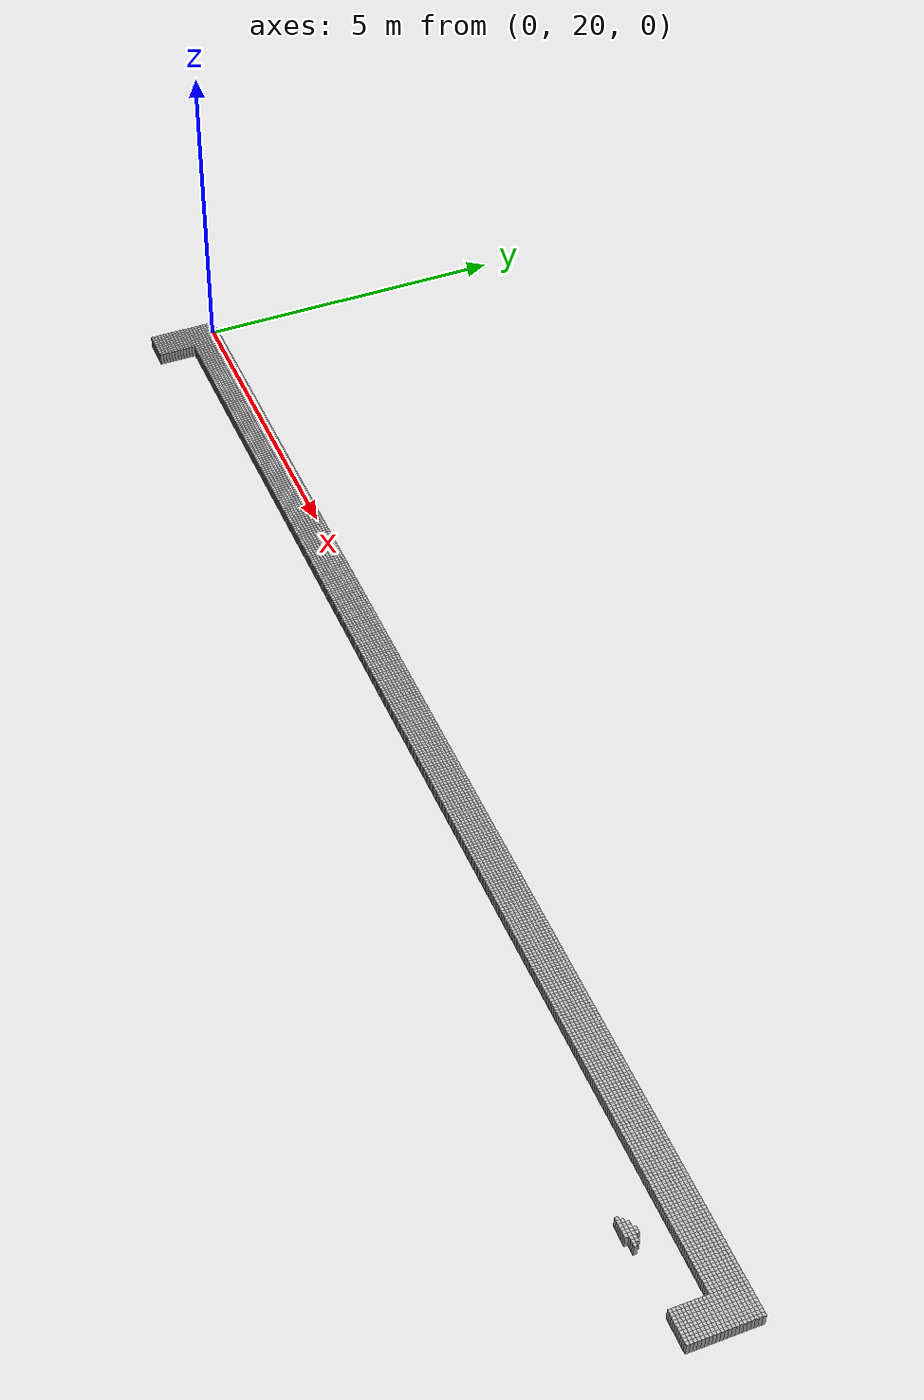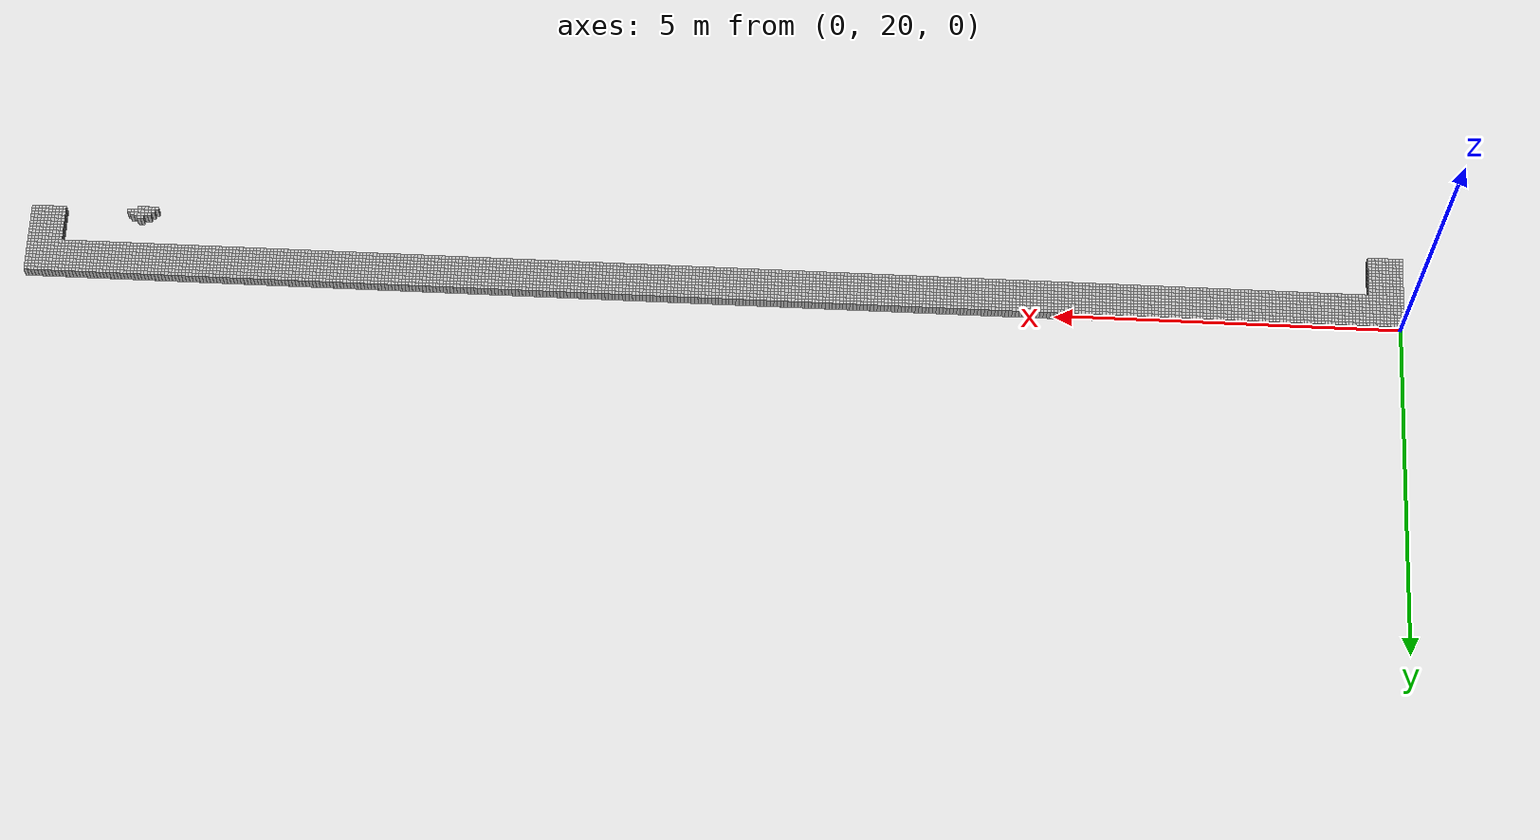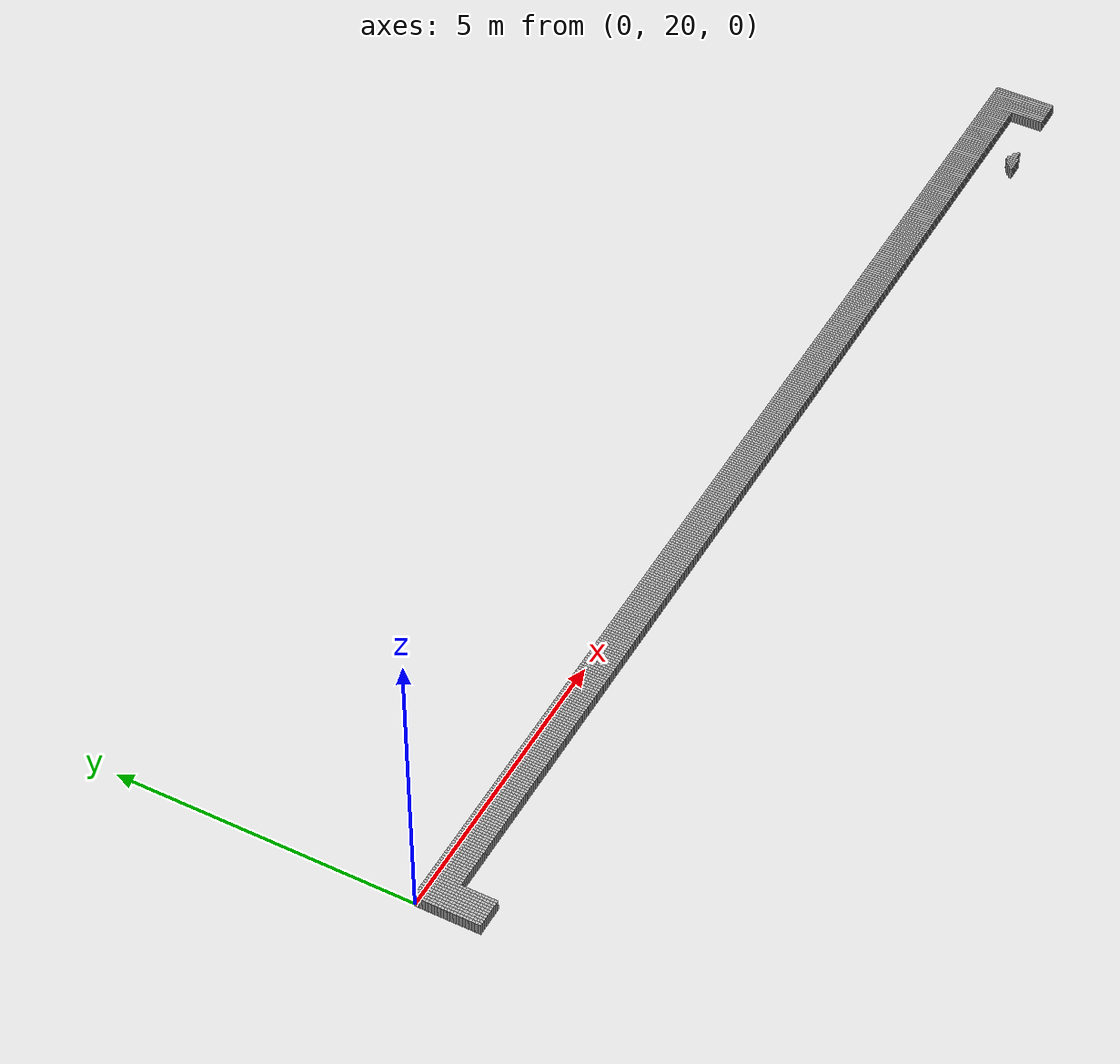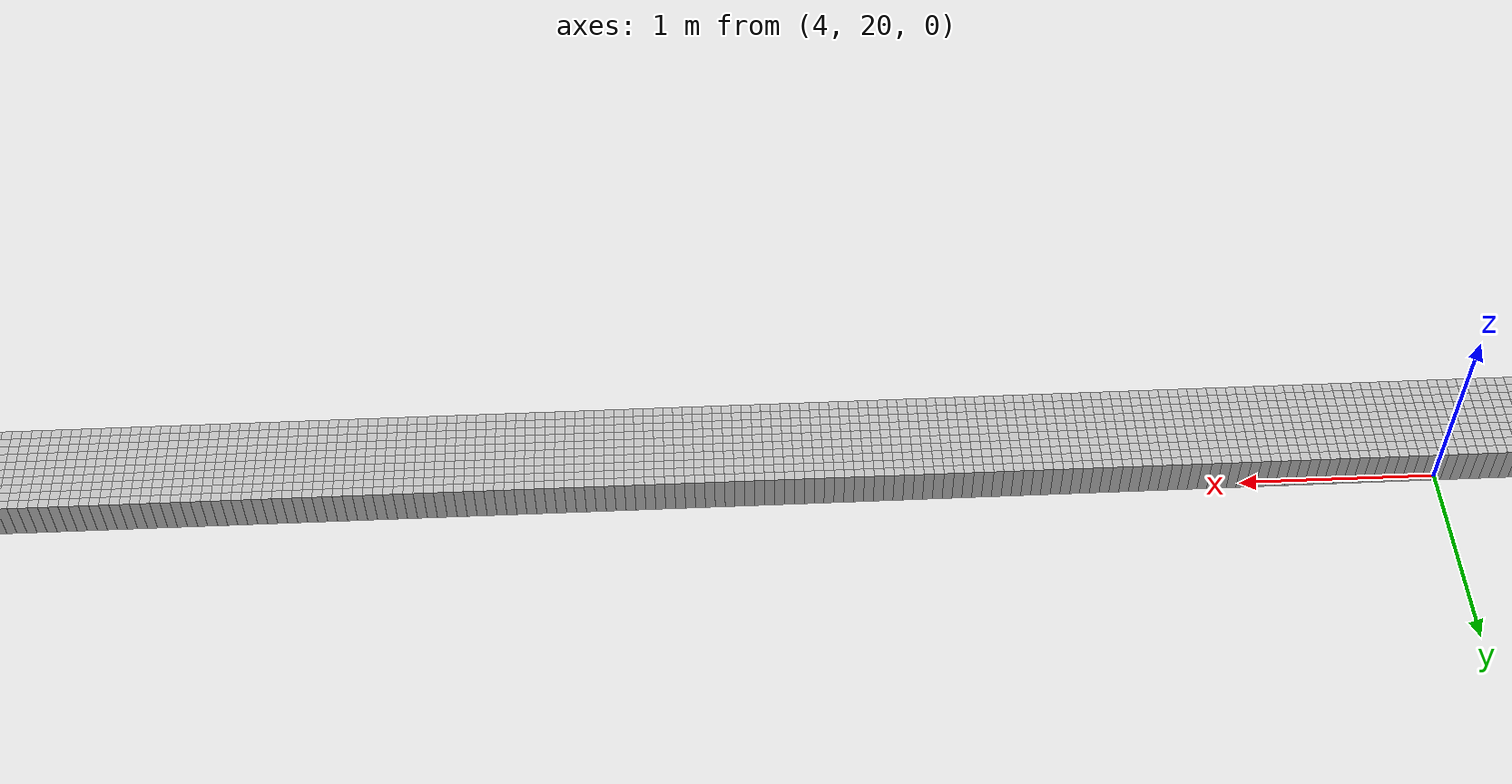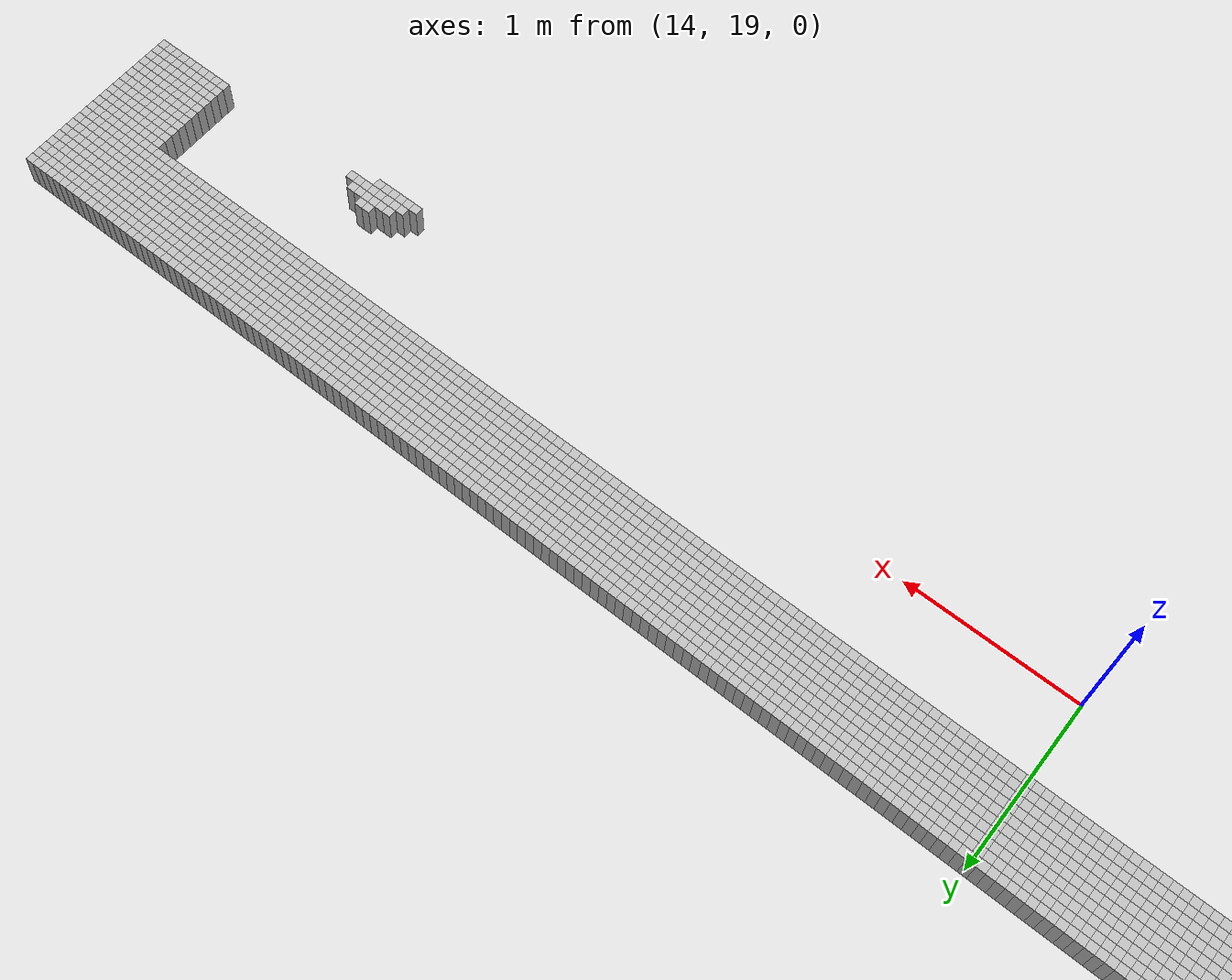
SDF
<sdf version="1.6">
 <world name="default">
  <model name="obstacle_0_0">
   <static>true</static>
   <link name="link">
    <pose>0.0 20.0 0.1 0 0 0</pose>
    <collision name="collision"><geometry><box><size>0.05 0.05 0.2</size></box></geometry></collision>
    <visual name="visual"><geometry><box><size>0.05 0.05 0.2</size></box></geometry></visual>
   </link>
  </model>
  <model name="obstacle_1_0">
   <static>true</static>
   <link name="link">
    <pose>0.05 20.0 0.1 0 0 0</pose>
    <collision name="collision"><geometry><box><size>0.05 0.05 0.2</size></box></geometry></collision>
    <visual name="visual"><geometry><box><size>0.05 0.05 0.2</size></box></geometry></visual>
   </link>
  </model>
  <model name="obstacle_2_0">
   <static>true</static>
   <link name="link">
    <pose>0.1 20.0 0.1 0 0 0</pose>
    <collision name="collision"><geometry><box><size>0.05 0.05 0.2</size></box></geometry></collision>
    <visual name="visual"><geometry><box><size>0.05 0.05 0.2</size></box></geometry></visual>
   </link>
  </model>
  <model name="obstacle_3_0">
   <static>true</static>
   <link name="link">
    <pose>0.15000000000000002 20.0 0.1 0 0 0</pose>
    <collision name="collision"><geometry><box><size>0.05 0.05 0.2</size></box></geometry></collision>
    <visual name="visual"><geometry><box><size>0.05 0.05 0.2</size></box></geometry></visual>
   </link>
  </model>
  <model name="obstacle_4_0">
   <static>true</static>
   <link name="link">
    <pose>0.2 20.0 0.1 0 0 0</pose>
    <collision name="collision"><geometry><box><size>0.05 0.05 0.2</size></box></geometry></collision>
    <visual name="visual"><geometry><box><size>0.05 0.05 0.2</size></box></geometry></visual>
   </link>
  </model>
  <model name="obstacle_5_0">
   <static>true</static>
   <link name="link">
    <pose>0.25 20.0 0.1 0 0 0</pose>
    <collision name="collision"><geometry><box><size>0.05 0.05 0.2</size></box></geometry></collision>
    <visual name="visual"><geometry><box><size>0.05 0.05 0.2</size></box></geometry></visual>
   </link>
  </model>
  <model name="obstacle_6_0">
   <static>true</static>
   <link name="link">
    <pose>0.30000000000000004 20.0 0.1 0 0 0</pose>
    <collision name="collision"><geometry><box><size>0.05 0.05 0.2</size></box></geometry></collision>
    <visual name="visual"><geometry><box><size>0.05 0.05 0.2</size></box></geometry></visual>
   </link>
  </model>
  <model name="obstacle_7_0">
   <static>true</static>
   <link name="link">
    <pose>0.35000000000000003 20.0 0.1 0 0 0</pose>
    <collision name="collision"><geometry><box><size>0.05 0.05 0.2</size></box></geometry></collision>
    <visual name="visual"><geometry><box><size>0.05 0.05 0.2</size></box></geometry></visual>
   </link>
  </model>
  <model name="obstacle_8_0">
   <static>true</static>
   <link name="link">
    <pose>0.4 20.0 0.1 0 0 0</pose>
    <collision name="collision"><geometry><box><size>0.05 0.05 0.2</size></box></geometry></collision>
    <visual name="visual"><geometry><box><size>0.05 0.05 0.2</size></box></geometry></visual>
   </link>
  </model>
  <model name="obstacle_9_0">
   <static>true</static>
   <link name="link">
    <pose>0.45 20.0 0.1 0 0 0</pose>
    <collision name="collision"><geometry><box><size>0.05 0.05 0.2</size></box></geometry></collision>
    <visual name="visual"><geometry><box><size>0.05 0.05 0.2</size></box></geometry></visual>
   </link>
  </model>
  <model name="obstacle_10_0">
   <static>true</static>
   <link name="link">
    <pose>0.5 20.0 0.1 0 0 0</pose>
    <collision name="collision"><geometry><box><size>0.05 0.05 0.2</size></box></geometry></collision>
    <visual name="visual"><geometry><box><size>0.05 0.05 0.2</size></box></geometry></visual>
   </link>
  </model>
  <model name="obstacle_11_0">
   <static>true</static>
   <link name="link">
    <pose>0.55 20.0 0.1 0 0 0</pose>
    <collision name="collision"><geometry><box><size>0.05 0.05 0.2</size></box></geometry></collision>
    <visual name="visual"><geometry><box><size>0.05 0.05 0.2</size></box></geometry></visual>
   </link>
  </model>
  <model name="obstacle_12_0">
   <static>true</static>
   <link name="link">
    <pose>0.6000000000000001 20.0 0.1 0 0 0</pose>
    <collision name="collision"><geometry><box><size>0.05 0.05 0.2</size></box></geometry></collision>
    <visual name="visual"><geometry><box><size>0.05 0.05 0.2</size></box></geometry></visual>
   </link>
  </model>
  <model name="obstacle_13_0">
   <static>true</static>
   <link name="link">
    <pose>0.65 20.0 0.1 0 0 0</pose>
    <collision name="collision"><geometry><box><size>0.05 0.05 0.2</size></box></geometry></collision>
    <visual name="visual"><geometry><box><size>0.05 0.05 0.2</size></box></geometry></visual>
   </link>
  </model>
  <model name="obstacle_14_0">
   <static>true</static>
   <link name="link">
    <pose>0.7000000000000001 20.0 0.1 0 0 0</pose>
    <collision name="collision"><geometry><box><size>0.05 0.05 0.2</size></box></geometry></collision>
    <visual name="visual"><geometry><box><size>0.05 0.05 0.2</size></box></geometry></visual>
   </link>
  </model>
  <model name="obstacle_15_0">
   <static>true</static>
   <link name="link">
    <pose>0.75 20.0 0.1 0 0 0</pose>
    <collision name="collision"><geometry><box><size>0.05 0.05 0.2</size></box></geometry></collision>
    <visual name="visual"><geometry><box><size>0.05 0.05 0.2</size></box></geometry></visual>
   </link>
  </model>
  <model name="obstacle_16_0">
   <static>true</static>
   <link name="link">
    <pose>0.8 20.0 0.1 0 0 0</pose>
    <collision name="collision"><geometry><box><size>0.05 0.05 0.2</size></box></geometry></collision>
    <visual name="visual"><geometry><box><size>0.05 0.05 0.2</size></box></geometry></visual>
   </link>
  </model>
  <model name="obstacle_17_0">
   <static>true</static>
   <link name="link">
    <pose>0.8500000000000001 20.0 0.1 0 0 0</pose>
    <collision name="collision"><geometry><box><size>0.05 0.05 0.2</size></box></geometry></collision>
    <visual name="visual"><geometry><box><size>0.05 0.05 0.2</size></box></geometry></visual>
   </link>
  </model>
  <model name="obstacle_18_0">
   <static>true</static>
   <link name="link">
    <pose>0.9 20.0 0.1 0 0 0</pose>
    <collision name="collision"><geometry><box><size>0.05 0.05 0.2</size></box></geometry></collision>
    <visual name="visual"><geometry><box><size>0.05 0.05 0.2</size></box></geometry></visual>
   </link>
  </model>
  <model name="obstacle_19_0">
   <static>true</static>
   <link name="link">
    <pose>0.9500000000000001 20.0 0.1 0 0 0</pose>
    <collision name="collision"><geometry><box><size>0.05 0.05 0.2</size></box></geometry></collision>
    <visual name="visual"><geometry><box><size>0.05 0.05 0.2</size></box></geometry></visual>
   </link>
  </model>
  <model name="obstacle_20_0">
   <static>true</static>
   <link name="link">
    <pose>1.0 20.0 0.1 0 0 0</pose>
    <collision name="collision"><geometry><box><size>0.05 0.05 0.2</size></box></geometry></collision>
    <visual name="visual"><geometry><box><size>0.05 0.05 0.2</size></box></geometry></visual>
   </link>
  </model>
  <model name="obstacle_21_0">
   <static>true</static>
   <link name="link">
    <pose>1.05 20.0 0.1 0 0 0</pose>
    <collision name="collision"><geometry><box><size>0.05 0.05 0.2</size></box></geometry></collision>
    <visual name="visual"><geometry><box><size>0.05 0.05 0.2</size></box></geometry></visual>
   </link>
  </model>
  <model name="obstacle_22_0">
   <static>true</static>
   <link name="link">
    <pose>1.1 20.0 0.1 0 0 0</pose>
    <collision name="collision"><geometry><box><size>0.05 0.05 0.2</size></box></geometry></collision>
    <visual name="visual"><geometry><box><size>0.05 0.05 0.2</size></box></geometry></visual>
   </link>
  </model>
  <model name="obstacle_23_0">
   <static>true</static>
   <link name="link">
    <pose>1.1500000000000001 20.0 0.1 0 0 0</pose>
    <collision name="collision"><geometry><box><size>0.05 0.05 0.2</size></box></geometry></collision>
    <visual name="visual"><geometry><box><size>0.05 0.05 0.2</size></box></geometry></visual>
   </link>
  </model>
  <model name="obstacle_24_0">
   <static>true</static>
   <link name="link">
    <pose>1.2000000000000002 20.0 0.1 0 0 0</pose>
    <collision name="collision"><geometry><box><size>0.05 0.05 0.2</size></box></geometry></collision>
    <visual name="visual"><geometry><box><size>0.05 0.05 0.2</size></box></geometry></visual>
   </link>
  </model>
  <model name="obstacle_25_0">
   <static>true</static>
   <link name="link">
    <pose>1.25 20.0 0.1 0 0 0</pose>
    <collision name="collision"><geometry><box><size>0.05 0.05 0.2</size></box></geometry></collision>
    <visual name="visual"><geometry><box><size>0.05 0.05 0.2</size></box></geometry></visual>
   </link>
  </model>
  <model name="obstacle_26_0">
   <static>true</static>
   <link name="link">
    <pose>1.3 20.0 0.1 0 0 0</pose>
    <collision name="collision"><geometry><box><size>0.05 0.05 0.2</size></box></geometry></collision>
    <visual name="visual"><geometry><box><size>0.05 0.05 0.2</size></box></geometry></visual>
   </link>
  </model>
  <model name="obstacle_27_0">
   <static>true</static>
   <link name="link">
    <pose>1.35 20.0 0.1 0 0 0</pose>
    <collision name="collision"><geometry><box><size>0.05 0.05 0.2</size></box></geometry></collision>
    <visual name="visual"><geometry><box><size>0.05 0.05 0.2</size></box></geometry></visual>
   </link>
  </model>
  <model name="obstacle_28_0">
   <static>true</static>
   <link name="link">
    <pose>1.4000000000000001 20.0 0.1 0 0 0</pose>
    <collision name="collision"><geometry><box><size>0.05 0.05 0.2</size></box></geometry></collision>
    <visual name="visual"><geometry><box><size>0.05 0.05 0.2</size></box></geometry></visual>
   </link>
  </model>
  <model name="obstacle_29_0">
   <static>true</static>
   <link name="link">
    <pose>1.4500000000000002 20.0 0.1 0 0 0</pose>
    <collision name="collision"><geometry><box><size>0.05 0.05 0.2</size></box></geometry></collision>
    <visual name="visual"><geometry><box><size>0.05 0.05 0.2</size></box></geometry></visual>
   </link>
  </model>
  <model name="obstacle_30_0">
   <static>true</static>
   <link name="link">
    <pose>1.5 20.0 0.1 0 0 0</pose>
    <collision name="collision"><geometry><box><size>0.05 0.05 0.2</size></box></geometry></collision>
    <visual name="visual"><geometry><box><size>0.05 0.05 0.2</size></box></geometry></visual>
   </link>
  </model>
  <model name="obstacle_31_0">
   <static>true</static>
   <link name="link">
    <pose>1.55 20.0 0.1 0 0 0</pose>
    <collision name="collision"><geometry><box><size>0.05 0.05 0.2</size></box></geometry></collision>
    <visual name="visual"><geometry><box><size>0.05 0.05 0.2</size></box></geometry></visual>
   </link>
  </model>
  <model name="obstacle_32_0">
   <static>true</static>
   <link name="link">
    <pose>1.6 20.0 0.1 0 0 0</pose>
    <collision name="collision"><geometry><box><size>0.05 0.05 0.2</size></box></geometry></collision>
    <visual name="visual"><geometry><box><size>0.05 0.05 0.2</size></box></geometry></visual>
   </link>
  </model>
  <model name="obstacle_33_0">
   <static>true</static>
   <link name="link">
    <pose>1.6500000000000001 20.0 0.1 0 0 0</pose>
    <collision name="collision"><geometry><box><size>0.05 0.05 0.2</size></box></geometry></collision>
    <visual name="visual"><geometry><box><size>0.05 0.05 0.2</size></box></geometry></visual>
   </link>
  </model>
  <model name="obstacle_34_0">
   <static>true</static>
   <link name="link">
    <pose>1.7000000000000002 20.0 0.1 0 0 0</pose>
    <collision name="collision"><geometry><box><size>0.05 0.05 0.2</size></box></geometry></collision>
    <visual name="visual"><geometry><box><size>0.05 0.05 0.2</size></box></geometry></visual>
   </link>
  </model>
  <model name="obstacle_35_0">
   <static>true</static>
   <link name="link">
    <pose>1.75 20.0 0.1 0 0 0</pose>
    <collision name="collision"><geometry><box><size>0.05 0.05 0.2</size></box></geometry></collision>
    <visual name="visual"><geometry><box><size>0.05 0.05 0.2</size></box></geometry></visual>
   </link>
  </model>
  <model name="obstacle_36_0">
   <static>true</static>
   <link name="link">
    <pose>1.8 20.0 0.1 0 0 0</pose>
    <collision name="collision"><geometry><box><size>0.05 0.05 0.2</size></box></geometry></collision>
    <visual name="visual"><geometry><box><size>0.05 0.05 0.2</size></box></geometry></visual>
   </link>
  </model>
  <model name="obstacle_37_0">
   <static>true</static>
   <link name="link">
    <pose>1.85 20.0 0.1 0 0 0</pose>
    <collision name="collision"><geometry><box><size>0.05 0.05 0.2</size></box></geometry></collision>
    <visual name="visual"><geometry><box><size>0.05 0.05 0.2</size></box></geometry></visual>
   </link>
  </model>
  <model name="obstacle_38_0">
   <static>true</static>
   <link name="link">
    <pose>1.9000000000000001 20.0 0.1 0 0 0</pose>
    <collision name="collision"><geometry><box><size>0.05 0.05 0.2</size></box></geometry></collision>
    <visual name="visual"><geometry><box><size>0.05 0.05 0.2</size></box></geometry></visual>
   </link>
  </model>
  <model name="obstacle_39_0">
   <static>true</static>
   <link name="link">
    <pose>1.9500000000000002 20.0 0.1 0 0 0</pose>
    <collision name="collision"><geometry><box><size>0.05 0.05 0.2</size></box></geometry></collision>
    <visual name="visual"><geometry><box><size>0.05 0.05 0.2</size></box></geometry></visual>
   </link>
  </model>
  <model name="obstacle_40_0">
   <static>true</static>
   <link name="link">
    <pose>2.0 20.0 0.1 0 0 0</pose>
    <collision name="collision"><geometry><box><size>0.05 0.05 0.2</size></box></geometry></collision>
    <visual name="visual"><geometry><box><size>0.05 0.05 0.2</size></box></geometry></visual>
   </link>
  </model>
  <model name="obstacle_41_0">
   <static>true</static>
   <link name="link">
    <pose>2.0500000000000003 20.0 0.1 0 0 0</pose>
    <collision name="collision"><geometry><box><size>0.05 0.05 0.2</size></box></geometry></collision>
    <visual name="visual"><geometry><box><size>0.05 0.05 0.2</size></box></geometry></visual>
   </link>
  </model>
  <model name="obstacle_42_0">
   <static>true</static>
   <link name="link">
    <pose>2.1 20.0 0.1 0 0 0</pose>
    <collision name="collision"><geometry><box><size>0.05 0.05 0.2</size></box></geometry></collision>
    <visual name="visual"><geometry><box><size>0.05 0.05 0.2</size></box></geometry></visual>
   </link>
  </model>
  <model name="obstacle_43_0">
   <static>true</static>
   <link name="link">
    <pose>2.15 20.0 0.1 0 0 0</pose>
    <collision name="collision"><geometry><box><size>0.05 0.05 0.2</size></box></geometry></collision>
    <visual name="visual"><geometry><box><size>0.05 0.05 0.2</size></box></geometry></visual>
   </link>
  </model>
  <model name="obstacle_44_0">
   <static>true</static>
   <link name="link">
    <pose>2.2 20.0 0.1 0 0 0</pose>
    <collision name="collision"><geometry><box><size>0.05 0.05 0.2</size></box></geometry></collision>
    <visual name="visual"><geometry><box><size>0.05 0.05 0.2</size></box></geometry></visual>
   </link>
  </model>
  <model name="obstacle_45_0">
   <static>true</static>
   <link name="link">
    <pose>2.25 20.0 0.1 0 0 0</pose>
    <collision name="collision"><geometry><box><size>0.05 0.05 0.2</size></box></geometry></collision>
    <visual name="visual"><geometry><box><size>0.05 0.05 0.2</size></box></geometry></visual>
   </link>
  </model>
  <model name="obstacle_46_0">
   <static>true</static>
   <link name="link">
    <pose>2.3000000000000003 20.0 0.1 0 0 0</pose>
    <collision name="collision"><geometry><box><size>0.05 0.05 0.2</size></box></geometry></collision>
    <visual name="visual"><geometry><box><size>0.05 0.05 0.2</size></box></geometry></visual>
   </link>
  </model>
  <model name="obstacle_47_0">
   <static>true</static>
   <link name="link">
    <pose>2.35 20.0 0.1 0 0 0</pose>
    <collision name="collision"><geometry><box><size>0.05 0.05 0.2</size></box></geometry></collision>
    <visual name="visual"><geometry><box><size>0.05 0.05 0.2</size></box></geometry></visual>
   </link>
  </model>
  <model name="obstacle_48_0">
   <static>true</static>
   <link name="link">
    <pose>2.4000000000000004 20.0 0.1 0 0 0</pose>
    <collision name="collision"><geometry><box><size>0.05 0.05 0.2</size></box></geometry></collision>
    <visual name="visual"><geometry><box><size>0.05 0.05 0.2</size></box></geometry></visual>
   </link>
  </model>
  <model name="obstacle_49_0">
   <static>true</static>
   <link name="link">
    <pose>2.45 20.0 0.1 0 0 0</pose>
    <collision name="collision"><geometry><box><size>0.05 0.05 0.2</size></box></geometry></collision>
    <visual name="visual"><geometry><box><size>0.05 0.05 0.2</size></box></geometry></visual>
   </link>
  </model>
  <model name="obstacle_50_0">
   <static>true</static>
   <link name="link">
    <pose>2.5 20.0 0.1 0 0 0</pose>
    <collision name="collision"><geometry><box><size>0.05 0.05 0.2</size></box></geometry></collision>
    <visual name="visual"><geometry><box><size>0.05 0.05 0.2</size></box></geometry></visual>
   </link>
  </model>
  <model name="obstacle_51_0">
   <static>true</static>
   <link name="link">
    <pose>2.5500000000000003 20.0 0.1 0 0 0</pose>
    <collision name="collision"><geometry><box><size>0.05 0.05 0.2</size></box></geometry></collision>
    <visual name="visual"><geometry><box><size>0.05 0.05 0.2</size></box></geometry></visual>
   </link>
  </model>
  <model name="obstacle_52_0">
   <static>true</static>
   <link name="link">
    <pose>2.6 20.0 0.1 0 0 0</pose>
    <collision name="collision"><geometry><box><size>0.05 0.05 0.2</size></box></geometry></collision>
    <visual name="visual"><geometry><box><size>0.05 0.05 0.2</size></box></geometry></visual>
   </link>
  </model>
  <model name="obstacle_53_0">
   <static>true</static>
   <link name="link">
    <pose>2.6500000000000004 20.0 0.1 0 0 0</pose>
    <collision name="collision"><geometry><box><size>0.05 0.05 0.2</size></box></geometry></collision>
    <visual name="visual"><geometry><box><size>0.05 0.05 0.2</size></box></geometry></visual>
   </link>
  </model>
  <model name="obstacle_54_0">
   <static>true</static>
   <link name="link">
    <pose>2.7 20.0 0.1 0 0 0</pose>
    <collision name="collision"><geometry><box><size>0.05 0.05 0.2</size></box></geometry></collision>
    <visual name="visual"><geometry><box><size>0.05 0.05 0.2</size></box></geometry></visual>
   </link>
  </model>
  <model name="obstacle_55_0">
   <static>true</static>
   <link name="link">
    <pose>2.75 20.0 0.1 0 0 0</pose>
    <collision name="collision"><geometry><box><size>0.05 0.05 0.2</size></box></geometry></collision>
    <visual name="visual"><geometry><box><size>0.05 0.05 0.2</size></box></geometry></visual>
   </link>
  </model>
  <model name="obstacle_56_0">
   <static>true</static>
   <link name="link">
    <pose>2.8000000000000003 20.0 0.1 0 0 0</pose>
    <collision name="collision"><geometry><box><size>0.05 0.05 0.2</size></box></geometry></collision>
    <visual name="visual"><geometry><box><size>0.05 0.05 0.2</size></box></geometry></visual>
   </link>
  </model>
  <model name="obstacle_57_0">
   <static>true</static>
   <link name="link">
    <pose>2.85 20.0 0.1 0 0 0</pose>
    <collision name="collision"><geometry><box><size>0.05 0.05 0.2</size></box></geometry></collision>
    <visual name="visual"><geometry><box><size>0.05 0.05 0.2</size></box></geometry></visual>
   </link>
  </model>
  <model name="obstacle_58_0">
   <static>true</static>
   <link name="link">
    <pose>2.9000000000000004 20.0 0.1 0 0 0</pose>
    <collision name="collision"><geometry><box><size>0.05 0.05 0.2</size></box></geometry></collision>
    <visual name="visual"><geometry><box><size>0.05 0.05 0.2</size></box></geometry></visual>
   </link>
  </model>
  <model name="obstacle_59_0">
   <static>true</static>
   <link name="link">
    <pose>2.95 20.0 0.1 0 0 0</pose>
    <collision name="collision"><geometry><box><size>0.05 0.05 0.2</size></box></geometry></collision>
    <visual name="visual"><geometry><box><size>0.05 0.05 0.2</size></box></geometry></visual>
   </link>
  </model>
  <model name="obstacle_60_0">
   <static>true</static>
   <link name="link">
    <pose>3.0 20.0 0.1 0 0 0</pose>
    <collision name="collision"><geometry><box><size>0.05 0.05 0.2</size></box></geometry></collision>
    <visual name="visual"><geometry><box><size>0.05 0.05 0.2</size></box></geometry></visual>
   </link>
  </model>
  <model name="obstacle_61_0">
   <static>true</static>
   <link name="link">
    <pose>3.0500000000000003 20.0 0.1 0 0 0</pose>
    <collision name="collision"><geometry><box><size>0.05 0.05 0.2</size></box></geometry></collision>
    <visual name="visual"><geometry><box><size>0.05 0.05 0.2</size></box></geometry></visual>
   </link>
  </model>
  <model name="obstacle_62_0">
   <static>true</static>
   <link name="link">
    <pose>3.1 20.0 0.1 0 0 0</pose>
    <collision name="collision"><geometry><box><size>0.05 0.05 0.2</size></box></geometry></collision>
    <visual name="visual"><geometry><box><size>0.05 0.05 0.2</size></box></geometry></visual>
   </link>
  </model>
  <model name="obstacle_63_0">
   <static>true</static>
   <link name="link">
    <pose>3.1500000000000004 20.0 0.1 0 0 0</pose>
    <collision name="collision"><geometry><box><size>0.05 0.05 0.2</size></box></geometry></collision>
    <visual name="visual"><geometry><box><size>0.05 0.05 0.2</size></box></geometry></visual>
   </link>
  </model>
  <model name="obstacle_64_0">
   <static>true</static>
   <link name="link">
    <pose>3.2 20.0 0.1 0 0 0</pose>
    <collision name="collision"><geometry><box><size>0.05 0.05 0.2</size></box></geometry></collision>
    <visual name="visual"><geometry><box><size>0.05 0.05 0.2</size></box></geometry></visual>
   </link>
  </model>
  <model name="obstacle_65_0">
   <static>true</static>
   <link name="link">
    <pose>3.25 20.0 0.1 0 0 0</pose>
    <collision name="collision"><geometry><box><size>0.05 0.05 0.2</size></box></geometry></collision>
    <visual name="visual"><geometry><box><size>0.05 0.05 0.2</size></box></geometry></visual>
   </link>
  </model>
  <model name="obstacle_66_0">
   <static>true</static>
   <link name="link">
    <pose>3.3000000000000003 20.0 0.1 0 0 0</pose>
    <collision name="collision"><geometry><box><size>0.05 0.05 0.2</size></box></geometry></collision>
    <visual name="visual"><geometry><box><size>0.05 0.05 0.2</size></box></geometry></visual>
   </link>
  </model>
  <model name="obstacle_67_0">
   <static>true</static>
   <link name="link">
    <pose>3.35 20.0 0.1 0 0 0</pose>
    <collision name="collision"><geometry><box><size>0.05 0.05 0.2</size></box></geometry></collision>
    <visual name="visual"><geometry><box><size>0.05 0.05 0.2</size></box></geometry></visual>
   </link>
  </model>
  <model name="obstacle_68_0">
   <static>true</static>
   <link name="link">
    <pose>3.4000000000000004 20.0 0.1 0 0 0</pose>
    <collision name="collision"><geometry><box><size>0.05 0.05 0.2</size></box></geometry></collision>
    <visual name="visual"><geometry><box><size>0.05 0.05 0.2</size></box></geometry></visual>
   </link>
  </model>
  <model name="obstacle_69_0">
   <static>true</static>
   <link name="link">
    <pose>3.45 20.0 0.1 0 0 0</pose>
    <collision name="collision"><geometry><box><size>0.05 0.05 0.2</size></box></geometry></collision>
    <visual name="visual"><geometry><box><size>0.05 0.05 0.2</size></box></geometry></visual>
   </link>
  </model>
  <model name="obstacle_70_0">
   <static>true</static>
   <link name="link">
    <pose>3.5 20.0 0.1 0 0 0</pose>
    <collision name="collision"><geometry><box><size>0.05 0.05 0.2</size></box></geometry></collision>
    <visual name="visual"><geometry><box><size>0.05 0.05 0.2</size></box></geometry></visual>
   </link>
  </model>
  <model name="obstacle_71_0">
   <static>true</static>
   <link name="link">
    <pose>3.5500000000000003 20.0 0.1 0 0 0</pose>
    <collision name="collision"><geometry><box><size>0.05 0.05 0.2</size></box></geometry></collision>
    <visual name="visual"><geometry><box><size>0.05 0.05 0.2</size></box></geometry></visual>
   </link>
  </model>
  <model name="obstacle_72_0">
   <static>true</static>
   <link name="link">
    <pose>3.6 20.0 0.1 0 0 0</pose>
    <collision name="collision"><geometry><box><size>0.05 0.05 0.2</size></box></geometry></collision>
    <visual name="visual"><geometry><box><size>0.05 0.05 0.2</size></box></geometry></visual>
   </link>
  </model>
  <model name="obstacle_73_0">
   <static>true</static>
   <link name="link">
    <pose>3.6500000000000004 20.0 0.1 0 0 0</pose>
    <collision name="collision"><geometry><box><size>0.05 0.05 0.2</size></box></geometry></collision>
    <visual name="visual"><geometry><box><size>0.05 0.05 0.2</size></box></geometry></visual>
   </link>
  </model>
  <model name="obstacle_74_0">
   <static>true</static>
   <link name="link">
    <pose>3.7 20.0 0.1 0 0 0</pose>
    <collision name="collision"><geometry><box><size>0.05 0.05 0.2</size></box></geometry></collision>
    <visual name="visual"><geometry><box><size>0.05 0.05 0.2</size></box></geometry></visual>
   </link>
  </model>
  <model name="obstacle_75_0">
   <static>true</static>
   <link name="link">
    <pose>3.75 20.0 0.1 0 0 0</pose>
    <collision name="collision"><geometry><box><size>0.05 0.05 0.2</size></box></geometry></collision>
    <visual name="visual"><geometry><box><size>0.05 0.05 0.2</size></box></geometry></visual>
   </link>
  </model>
  <model name="obstacle_76_0">
   <static>true</static>
   <link name="link">
    <pose>3.8000000000000003 20.0 0.1 0 0 0</pose>
    <collision name="collision"><geometry><box><size>0.05 0.05 0.2</size></box></geometry></collision>
    <visual name="visual"><geometry><box><size>0.05 0.05 0.2</size></box></geometry></visual>
   </link>
  </model>
  <model name="obstacle_77_0">
   <static>true</static>
   <link name="link">
    <pose>3.85 20.0 0.1 0 0 0</pose>
    <collision name="collision"><geometry><box><size>0.05 0.05 0.2</size></box></geometry></collision>
    <visual name="visual"><geometry><box><size>0.05 0.05 0.2</size></box></geometry></visual>
   </link>
  </model>
  <model name="obstacle_78_0">
   <static>true</static>
   <link name="link">
    <pose>3.9000000000000004 20.0 0.1 0 0 0</pose>
    <collision name="collision"><geometry><box><size>0.05 0.05 0.2</size></box></geometry></collision>
    <visual name="visual"><geometry><box><size>0.05 0.05 0.2</size></box></geometry></visual>
   </link>
  </model>
  <model name="obstacle_79_0">
   <static>true</static>
   <link name="link">
    <pose>3.95 20.0 0.1 0 0 0</pose>
    <collision name="collision"><geometry><box><size>0.05 0.05 0.2</size></box></geometry></collision>
    <visual name="visual"><geometry><box><size>0.05 0.05 0.2</size></box></geometry></visual>
   </link>
  </model>
  <model name="obstacle_80_0">
   <static>true</static>
   <link name="link">
    <pose>4.0 20.0 0.1 0 0 0</pose>
    <collision name="collision"><geometry><box><size>0.05 0.05 0.2</size></box></geometry></collision>
    <visual name="visual"><geometry><box><size>0.05 0.05 0.2</size></box></geometry></visual>
   </link>
  </model>
  <model name="obstacle_81_0">
   <static>true</static>
   <link name="link">
    <pose>4.05 20.0 0.1 0 0 0</pose>
    <collision name="collision"><geometry><box><size>0.05 0.05 0.2</size></box></geometry></collision>
    <visual name="visual"><geometry><box><size>0.05 0.05 0.2</size></box></geometry></visual>
   </link>
  </model>
  <model name="obstacle_82_0">
   <static>true</static>
   <link name="link">
    <pose>4.1000000000000005 20.0 0.1 0 0 0</pose>
    <collision name="collision"><geometry><box><size>0.05 0.05 0.2</size></box></geometry></collision>
    <visual name="visual"><geometry><box><size>0.05 0.05 0.2</size></box></geometry></visual>
   </link>
  </model>
  <model name="obstacle_83_0">
   <static>true</static>
   <link name="link">
    <pose>4.15 20.0 0.1 0 0 0</pose>
    <collision name="collision"><geometry><box><size>0.05 0.05 0.2</size></box></geometry></collision>
    <visual name="visual"><geometry><box><size>0.05 0.05 0.2</size></box></geometry></visual>
   </link>
  </model>
  <model name="obstacle_84_0">
   <static>true</static>
   <link name="link">
    <pose>4.2 20.0 0.1 0 0 0</pose>
    <collision name="collision"><geometry><box><size>0.05 0.05 0.2</size></box></geometry></collision>
    <visual name="visual"><geometry><box><size>0.05 0.05 0.2</size></box></geometry></visual>
   </link>
  </model>
  <model name="obstacle_85_0">
   <static>true</static>
   <link name="link">
    <pose>4.25 20.0 0.1 0 0 0</pose>
    <collision name="collision"><geometry><box><size>0.05 0.05 0.2</size></box></geometry></collision>
    <visual name="visual"><geometry><box><size>0.05 0.05 0.2</size></box></geometry></visual>
   </link>
  </model>
  <model name="obstacle_86_0">
   <static>true</static>
   <link name="link">
    <pose>4.3 20.0 0.1 0 0 0</pose>
    <collision name="collision"><geometry><box><size>0.05 0.05 0.2</size></box></geometry></collision>
    <visual name="visual"><geometry><box><size>0.05 0.05 0.2</size></box></geometry></visual>
   </link>
  </model>
  <model name="obstacle_87_0">
   <static>true</static>
   <link name="link">
    <pose>4.3500000000000005 20.0 0.1 0 0 0</pose>
    <collision name="collision"><geometry><box><size>0.05 0.05 0.2</size></box></geometry></collision>
    <visual name="visual"><geometry><box><size>0.05 0.05 0.2</size></box></geometry></visual>
   </link>
  </model>
  <model name="obstacle_88_0">
   <static>true</static>
   <link name="link">
    <pose>4.4 20.0 0.1 0 0 0</pose>
    <collision name="collision"><geometry><box><size>0.05 0.05 0.2</size></box></geometry></collision>
    <visual name="visual"><geometry><box><size>0.05 0.05 0.2</size></box></geometry></visual>
   </link>
  </model>
  <model name="obstacle_89_0">
   <static>true</static>
   <link name="link">
    <pose>4.45 20.0 0.1 0 0 0</pose>
    <collision name="collision"><geometry><box><size>0.05 0.05 0.2</size></box></geometry></collision>
    <visual name="visual"><geometry><box><size>0.05 0.05 0.2</size></box></geometry></visual>
   </link>
  </model>
  <model name="obstacle_90_0">
   <static>true</static>
   <link name="link">
    <pose>4.5 20.0 0.1 0 0 0</pose>
    <collision name="collision"><geometry><box><size>0.05 0.05 0.2</size></box></geometry></collision>
    <visual name="visual"><geometry><box><size>0.05 0.05 0.2</size></box></geometry></visual>
   </link>
  </model>
  <model name="obstacle_91_0">
   <static>true</static>
   <link name="link">
    <pose>4.55 20.0 0.1 0 0 0</pose>
    <collision name="collision"><geometry><box><size>0.05 0.05 0.2</size></box></geometry></collision>
    <visual name="visual"><geometry><box><size>0.05 0.05 0.2</size></box></geometry></visual>
   </link>
  </model>
  <model name="obstacle_92_0">
   <static>true</static>
   <link name="link">
    <pose>4.6000000000000005 20.0 0.1 0 0 0</pose>
    <collision name="collision"><geometry><box><size>0.05 0.05 0.2</size></box></geometry></collision>
    <visual name="visual"><geometry><box><size>0.05 0.05 0.2</size></box></geometry></visual>
   </link>
  </model>
  <model name="obstacle_93_0">
   <static>true</static>
   <link name="link">
    <pose>4.65 20.0 0.1 0 0 0</pose>
    <collision name="collision"><geometry><box><size>0.05 0.05 0.2</size></box></geometry></collision>
    <visual name="visual"><geometry><box><size>0.05 0.05 0.2</size></box></geometry></visual>
   </link>
  </model>
  <model name="obstacle_94_0">
   <static>true</static>
   <link name="link">
    <pose>4.7 20.0 0.1 0 0 0</pose>
    <collision name="collision"><geometry><box><size>0.05 0.05 0.2</size></box></geometry></collision>
    <visual name="visual"><geometry><box><size>0.05 0.05 0.2</size></box></geometry></visual>
   </link>
  </model>
  <model name="obstacle_95_0">
   <static>true</static>
   <link name="link">
    <pose>4.75 20.0 0.1 0 0 0</pose>
    <collision name="collision"><geometry><box><size>0.05 0.05 0.2</size></box></geometry></collision>
    <visual name="visual"><geometry><box><size>0.05 0.05 0.2</size></box></geometry></visual>
   </link>
  </model>
  <model name="obstacle_96_0">
   <static>true</static>
   <link name="link">
    <pose>4.800000000000001 20.0 0.1 0 0 0</pose>
    <collision name="collision"><geometry><box><size>0.05 0.05 0.2</size></box></geometry></collision>
    <visual name="visual"><geometry><box><size>0.05 0.05 0.2</size></box></geometry></visual>
   </link>
  </model>
  <model name="obstacle_97_0">
   <static>true</static>
   <link name="link">
    <pose>4.8500000000000005 20.0 0.1 0 0 0</pose>
    <collision name="collision"><geometry><box><size>0.05 0.05 0.2</size></box></geometry></collision>
    <visual name="visual"><geometry><box><size>0.05 0.05 0.2</size></box></geometry></visual>
   </link>
  </model>
  <model name="obstacle_98_0">
   <static>true</static>
   <link name="link">
    <pose>4.9 20.0 0.1 0 0 0</pose>
    <collision name="collision"><geometry><box><size>0.05 0.05 0.2</size></box></geometry></collision>
    <visual name="visual"><geometry><box><size>0.05 0.05 0.2</size></box></geometry></visual>
   </link>
  </model>
  <model name="obstacle_99_0">
   <static>true</static>
   <link name="link">
    <pose>4.95 20.0 0.1 0 0 0</pose>
    <collision name="collision"><geometry><box><size>0.05 0.05 0.2</size></box></geometry></collision>
    <visual name="visual"><geometry><box><size>0.05 0.05 0.2</size></box></geometry></visual>
   </link>
  </model>
  <model name="obstacle_100_0">
   <static>true</static>
   <link name="link">
    <pose>5.0 20.0 0.1 0 0 0</pose>
    <collision name="collision"><geometry><box><size>0.05 0.05 0.2</size></box></geometry></collision>
    <visual name="visual"><geometry><box><size>0.05 0.05 0.2</size></box></geometry></visual>
   </link>
  </model>
  <model name="obstacle_101_0">
   <static>true</static>
   <link name="link">
    <pose>5.050000000000001 20.0 0.1 0 0 0</pose>
    <collision name="collision"><geometry><box><size>0.05 0.05 0.2</size></box></geometry></collision>
    <visual name="visual"><geometry><box><size>0.05 0.05 0.2</size></box></geometry></visual>
   </link>
  </model>
  <model name="obstacle_102_0">
   <static>true</static>
   <link name="link">
    <pose>5.1000000000000005 20.0 0.1 0 0 0</pose>
    <collision name="collision"><geometry><box><size>0.05 0.05 0.2</size></box></geometry></collision>
    <visual name="visual"><geometry><box><size>0.05 0.05 0.2</size></box></geometry></visual>
   </link>
  </model>
  <model name="obstacle_103_0">
   <static>true</static>
   <link name="link">
    <pose>5.15 20.0 0.1 0 0 0</pose>
    <collision name="collision"><geometry><box><size>0.05 0.05 0.2</size></box></geometry></collision>
    <visual name="visual"><geometry><box><size>0.05 0.05 0.2</size></box></geometry></visual>
   </link>
  </model>
  <model name="obstacle_104_0">
   <static>true</static>
   <link name="link">
    <pose>5.2 20.0 0.1 0 0 0</pose>
    <collision name="collision"><geometry><box><size>0.05 0.05 0.2</size></box></geometry></collision>
    <visual name="visual"><geometry><box><size>0.05 0.05 0.2</size></box></geometry></visual>
   </link>
  </model>
  <model name="obstacle_105_0">
   <static>true</static>
   <link name="link">
    <pose>5.25 20.0 0.1 0 0 0</pose>
    <collision name="collision"><geometry><box><size>0.05 0.05 0.2</size></box></geometry></collision>
    <visual name="visual"><geometry><box><size>0.05 0.05 0.2</size></box></geometry></visual>
   </link>
  </model>
  <model name="obstacle_106_0">
   <static>true</static>
   <link name="link">
    <pose>5.300000000000001 20.0 0.1 0 0 0</pose>
    <collision name="collision"><geometry><box><size>0.05 0.05 0.2</size></box></geometry></collision>
    <visual name="visual"><geometry><box><size>0.05 0.05 0.2</size></box></geometry></visual>
   </link>
  </model>
  <model name="obstacle_107_0">
   <static>true</static>
   <link name="link">
    <pose>5.3500000000000005 20.0 0.1 0 0 0</pose>
    <collision name="collision"><geometry><box><size>0.05 0.05 0.2</size></box></geometry></collision>
    <visual name="visual"><geometry><box><size>0.05 0.05 0.2</size></box></geometry></visual>
   </link>
  </model>
  <model name="obstacle_108_0">
   <static>true</static>
   <link name="link">
    <pose>5.4 20.0 0.1 0 0 0</pose>
    <collision name="collision"><geometry><box><size>0.05 0.05 0.2</size></box></geometry></collision>
    <visual name="visual"><geometry><box><size>0.05 0.05 0.2</size></box></geometry></visual>
   </link>
  </model>
  <model name="obstacle_109_0">
   <static>true</static>
   <link name="link">
    <pose>5.45 20.0 0.1 0 0 0</pose>
    <collision name="collision"><geometry><box><size>0.05 0.05 0.2</size></box></geometry></collision>
    <visual name="visual"><geometry><box><size>0.05 0.05 0.2</size></box></geometry></visual>
   </link>
  </model>
  <model name="obstacle_110_0">
   <static>true</static>
   <link name="link">
    <pose>5.5 20.0 0.1 0 0 0</pose>
    <collision name="collision"><geometry><box><size>0.05 0.05 0.2</size></box></geometry></collision>
    <visual name="visual"><geometry><box><size>0.05 0.05 0.2</size></box></geometry></visual>
   </link>
  </model>
  <model name="obstacle_111_0">
   <static>true</static>
   <link name="link">
    <pose>5.550000000000001 20.0 0.1 0 0 0</pose>
    <collision name="collision"><geometry><box><size>0.05 0.05 0.2</size></box></geometry></collision>
    <visual name="visual"><geometry><box><size>0.05 0.05 0.2</size></box></geometry></visual>
   </link>
  </model>
  <model name="obstacle_112_0">
   <static>true</static>
   <link name="link">
    <pose>5.6000000000000005 20.0 0.1 0 0 0</pose>
    <collision name="collision"><geometry><box><size>0.05 0.05 0.2</size></box></geometry></collision>
    <visual name="visual"><geometry><box><size>0.05 0.05 0.2</size></box></geometry></visual>
   </link>
  </model>
  <model name="obstacle_113_0">
   <static>true</static>
   <link name="link">
    <pose>5.65 20.0 0.1 0 0 0</pose>
    <collision name="collision"><geometry><box><size>0.05 0.05 0.2</size></box></geometry></collision>
    <visual name="visual"><geometry><box><size>0.05 0.05 0.2</size></box></geometry></visual>
   </link>
  </model>
  <model name="obstacle_114_0">
   <static>true</static>
   <link name="link">
    <pose>5.7 20.0 0.1 0 0 0</pose>
    <collision name="collision"><geometry><box><size>0.05 0.05 0.2</size></box></geometry></collision>
    <visual name="visual"><geometry><box><size>0.05 0.05 0.2</size></box></geometry></visual>
   </link>
  </model>
  <model name="obstacle_115_0">
   <static>true</static>
   <link name="link">
    <pose>5.75 20.0 0.1 0 0 0</pose>
    <collision name="collision"><geometry><box><size>0.05 0.05 0.2</size></box></geometry></collision>
    <visual name="visual"><geometry><box><size>0.05 0.05 0.2</size></box></geometry></visual>
   </link>
  </model>
  <model name="obstacle_116_0">
   <static>true</static>
   <link name="link">
    <pose>5.800000000000001 20.0 0.1 0 0 0</pose>
    <collision name="collision"><geometry><box><size>0.05 0.05 0.2</size></box></geometry></collision>
    <visual name="visual"><geometry><box><size>0.05 0.05 0.2</size></box></geometry></visual>
   </link>
  </model>
  <model name="obstacle_117_0">
   <static>true</static>
   <link name="link">
    <pose>5.8500000000000005 20.0 0.1 0 0 0</pose>
    <collision name="collision"><geometry><box><size>0.05 0.05 0.2</size></box></geometry></collision>
    <visual name="visual"><geometry><box><size>0.05 0.05 0.2</size></box></geometry></visual>
   </link>
  </model>
  <model name="obstacle_118_0">
   <static>true</static>
   <link name="link">
    <pose>5.9 20.0 0.1 0 0 0</pose>
    <collision name="collision"><geometry><box><size>0.05 0.05 0.2</size></box></geometry></collision>
    <visual name="visual"><geometry><box><size>0.05 0.05 0.2</size></box></geometry></visual>
   </link>
  </model>
  <model name="obstacle_119_0">
   <static>true</static>
   <link name="link">
    <pose>5.95 20.0 0.1 0 0 0</pose>
    <collision name="collision"><geometry><box><size>0.05 0.05 0.2</size></box></geometry></collision>
    <visual name="visual"><geometry><box><size>0.05 0.05 0.2</size></box></geometry></visual>
   </link>
  </model>
  <model name="obstacle_120_0">
   <static>true</static>
   <link name="link">
    <pose>6.0 20.0 0.1 0 0 0</pose>
    <collision name="collision"><geometry><box><size>0.05 0.05 0.2</size></box></geometry></collision>
    <visual name="visual"><geometry><box><size>0.05 0.05 0.2</size></box></geometry></visual>
   </link>
  </model>
  <model name="obstacle_121_0">
   <static>true</static>
   <link name="link">
    <pose>6.050000000000001 20.0 0.1 0 0 0</pose>
    <collision name="collision"><geometry><box><size>0.05 0.05 0.2</size></box></geometry></collision>
    <visual name="visual"><geometry><box><size>0.05 0.05 0.2</size></box></geometry></visual>
   </link>
  </model>
  <model name="obstacle_122_0">
   <static>true</static>
   <link name="link">
    <pose>6.1000000000000005 20.0 0.1 0 0 0</pose>
    <collision name="collision"><geometry><box><size>0.05 0.05 0.2</size></box></geometry></collision>
    <visual name="visual"><geometry><box><size>0.05 0.05 0.2</size></box></geometry></visual>
   </link>
  </model>
  <model name="obstacle_123_0">
   <static>true</static>
   <link name="link">
    <pose>6.15 20.0 0.1 0 0 0</pose>
    <collision name="collision"><geometry><box><size>0.05 0.05 0.2</size></box></geometry></collision>
    <visual name="visual"><geometry><box><size>0.05 0.05 0.2</size></box></geometry></visual>
   </link>
  </model>
  <model name="obstacle_124_0">
   <static>true</static>
   <link name="link">
    <pose>6.2 20.0 0.1 0 0 0</pose>
    <collision name="collision"><geometry><box><size>0.05 0.05 0.2</size></box></geometry></collision>
    <visual name="visual"><geometry><box><size>0.05 0.05 0.2</size></box></geometry></visual>
   </link>
  </model>
  <model name="obstacle_125_0">
   <static>true</static>
   <link name="link">
    <pose>6.25 20.0 0.1 0 0 0</pose>
    <collision name="collision"><geometry><box><size>0.05 0.05 0.2</size></box></geometry></collision>
    <visual name="visual"><geometry><box><size>0.05 0.05 0.2</size></box></geometry></visual>
   </link>
  </model>
  <model name="obstacle_126_0">
   <static>true</static>
   <link name="link">
    <pose>6.300000000000001 20.0 0.1 0 0 0</pose>
    <collision name="collision"><geometry><box><size>0.05 0.05 0.2</size></box></geometry></collision>
    <visual name="visual"><geometry><box><size>0.05 0.05 0.2</size></box></geometry></visual>
   </link>
  </model>
  <model name="obstacle_127_0">
   <static>true</static>
   <link name="link">
    <pose>6.3500000000000005 20.0 0.1 0 0 0</pose>
    <collision name="collision"><geometry><box><size>0.05 0.05 0.2</size></box></geometry></collision>
    <visual name="visual"><geometry><box><size>0.05 0.05 0.2</size></box></geometry></visual>
   </link>
  </model>
  <model name="obstacle_128_0">
   <static>true</static>
   <link name="link">
    <pose>6.4 20.0 0.1 0 0 0</pose>
    <collision name="collision"><geometry><box><size>0.05 0.05 0.2</size></box></geometry></collision>
    <visual name="visual"><geometry><box><size>0.05 0.05 0.2</size></box></geometry></visual>
   </link>
  </model>
  <model name="obstacle_129_0">
   <static>true</static>
   <link name="link">
    <pose>6.45 20.0 0.1 0 0 0</pose>
    <collision name="collision"><geometry><box><size>0.05 0.05 0.2</size></box></geometry></collision>
    <visual name="visual"><geometry><box><size>0.05 0.05 0.2</size></box></geometry></visual>
   </link>
  </model>
  <model name="obstacle_130_0">
   <static>true</static>
   <link name="link">
    <pose>6.5 20.0 0.1 0 0 0</pose>
    <collision name="collision"><geometry><box><size>0.05 0.05 0.2</size></box></geometry></collision>
    <visual name="visual"><geometry><box><size>0.05 0.05 0.2</size></box></geometry></visual>
   </link>
  </model>
  <model name="obstacle_131_0">
   <static>true</static>
   <link name="link">
    <pose>6.550000000000001 20.0 0.1 0 0 0</pose>
    <collision name="collision"><geometry><box><size>0.05 0.05 0.2</size></box></geometry></collision>
    <visual name="visual"><geometry><box><size>0.05 0.05 0.2</size></box></geometry></visual>
   </link>
  </model>
  <model name="obstacle_132_0">
   <static>true</static>
   <link name="link">
    <pose>6.6000000000000005 20.0 0.1 0 0 0</pose>
    <collision name="collision"><geometry><box><size>0.05 0.05 0.2</size></box></geometry></collision>
    <visual name="visual"><geometry><box><size>0.05 0.05 0.2</size></box></geometry></visual>
   </link>
  </model>
  <model name="obstacle_133_0">
   <static>true</static>
   <link name="link">
    <pose>6.65 20.0 0.1 0 0 0</pose>
    <collision name="collision"><geometry><box><size>0.05 0.05 0.2</size></box></geometry></collision>
    <visual name="visual"><geometry><box><size>0.05 0.05 0.2</size></box></geometry></visual>
   </link>
  </model>
  <model name="obstacle_134_0">
   <static>true</static>
   <link name="link">
    <pose>6.7 20.0 0.1 0 0 0</pose>
    <collision name="collision"><geometry><box><size>0.05 0.05 0.2</size></box></geometry></collision>
    <visual name="visual"><geometry><box><size>0.05 0.05 0.2</size></box></geometry></visual>
   </link>
  </model>
  <model name="obstacle_135_0">
   <static>true</static>
   <link name="link">
    <pose>6.75 20.0 0.1 0 0 0</pose>
    <collision name="collision"><geometry><box><size>0.05 0.05 0.2</size></box></geometry></collision>
    <visual name="visual"><geometry><box><size>0.05 0.05 0.2</size></box></geometry></visual>
   </link>
  </model>
  <model name="obstacle_136_0">
   <static>true</static>
   <link name="link">
    <pose>6.800000000000001 20.0 0.1 0 0 0</pose>
    <collision name="collision"><geometry><box><size>0.05 0.05 0.2</size></box></geometry></collision>
    <visual name="visual"><geometry><box><size>0.05 0.05 0.2</size></box></geometry></visual>
   </link>
  </model>
  <model name="obstacle_137_0">
   <static>true</static>
   <link name="link">
    <pose>6.8500000000000005 20.0 0.1 0 0 0</pose>
    <collision name="collision"><geometry><box><size>0.05 0.05 0.2</size></box></geometry></collision>
    <visual name="visual"><geometry><box><size>0.05 0.05 0.2</size></box></geometry></visual>
   </link>
  </model>
  <model name="obstacle_138_0">
   <static>true</static>
   <link name="link">
    <pose>6.9 20.0 0.1 0 0 0</pose>
    <collision name="collision"><geometry><box><size>0.05 0.05 0.2</size></box></geometry></collision>
    <visual name="visual"><geometry><box><size>0.05 0.05 0.2</size></box></geometry></visual>
   </link>
  </model>
  <model name="obstacle_139_0">
   <static>true</static>
   <link name="link">
    <pose>6.95 20.0 0.1 0 0 0</pose>
    <collision name="collision"><geometry><box><size>0.05 0.05 0.2</size></box></geometry></collision>
    <visual name="visual"><geometry><box><size>0.05 0.05 0.2</size></box></geometry></visual>
   </link>
  </model>
  <model name="obstacle_140_0">
   <static>true</static>
   <link name="link">
    <pose>7.0 20.0 0.1 0 0 0</pose>
    <collision name="collision"><geometry><box><size>0.05 0.05 0.2</size></box></geometry></collision>
    <visual name="visual"><geometry><box><size>0.05 0.05 0.2</size></box></geometry></visual>
   </link>
  </model>
  <model name="obstacle_141_0">
   <static>true</static>
   <link name="link">
    <pose>7.050000000000001 20.0 0.1 0 0 0</pose>
    <collision name="collision"><geometry><box><size>0.05 0.05 0.2</size></box></geometry></collision>
    <visual name="visual"><geometry><box><size>0.05 0.05 0.2</size></box></geometry></visual>
   </link>
  </model>
  <model name="obstacle_142_0">
   <static>true</static>
   <link name="link">
    <pose>7.1000000000000005 20.0 0.1 0 0 0</pose>
    <collision name="collision"><geometry><box><size>0.05 0.05 0.2</size></box></geometry></collision>
    <visual name="visual"><geometry><box><size>0.05 0.05 0.2</size></box></geometry></visual>
   </link>
  </model>
  <model name="obstacle_143_0">
   <static>true</static>
   <link name="link">
    <pose>7.15 20.0 0.1 0 0 0</pose>
    <collision name="collision"><geometry><box><size>0.05 0.05 0.2</size></box></geometry></collision>
    <visual name="visual"><geometry><box><size>0.05 0.05 0.2</size></box></geometry></visual>
   </link>
  </model>
  <model name="obstacle_144_0">
   <static>true</static>
   <link name="link">
    <pose>7.2 20.0 0.1 0 0 0</pose>
    <collision name="collision"><geometry><box><size>0.05 0.05 0.2</size></box></geometry></collision>
    <visual name="visual"><geometry><box><size>0.05 0.05 0.2</size></box></geometry></visual>
   </link>
  </model>
  <model name="obstacle_145_0">
   <static>true</static>
   <link name="link">
    <pose>7.25 20.0 0.1 0 0 0</pose>
    <collision name="collision"><geometry><box><size>0.05 0.05 0.2</size></box></geometry></collision>
    <visual name="visual"><geometry><box><size>0.05 0.05 0.2</size></box></geometry></visual>
   </link>
  </model>
  <model name="obstacle_146_0">
   <static>true</static>
   <link name="link">
    <pose>7.300000000000001 20.0 0.1 0 0 0</pose>
    <collision name="collision"><geometry><box><size>0.05 0.05 0.2</size></box></geometry></collision>
    <visual name="visual"><geometry><box><size>0.05 0.05 0.2</size></box></geometry></visual>
   </link>
  </model>
  <model name="obstacle_147_0">
   <static>true</static>
   <link name="link">
    <pose>7.3500000000000005 20.0 0.1 0 0 0</pose>
    <collision name="collision"><geometry><box><size>0.05 0.05 0.2</size></box></geometry></collision>
    <visual name="visual"><geometry><box><size>0.05 0.05 0.2</size></box></geometry></visual>
   </link>
  </model>
  <model name="obstacle_148_0">
   <static>true</static>
   <link name="link">
    <pose>7.4 20.0 0.1 0 0 0</pose>
    <collision name="collision"><geometry><box><size>0.05 0.05 0.2</size></box></geometry></collision>
    <visual name="visual"><geometry><box><size>0.05 0.05 0.2</size></box></geometry></visual>
   </link>
  </model>
  <model name="obstacle_149_0">
   <static>true</static>
   <link name="link">
    <pose>7.45 20.0 0.1 0 0 0</pose>
    <collision name="collision"><geometry><box><size>0.05 0.05 0.2</size></box></geometry></collision>
    <visual name="visual"><geometry><box><size>0.05 0.05 0.2</size></box></geometry></visual>
   </link>
  </model>
  <model name="obstacle_150_0">
   <static>true</static>
   <link name="link">
    <pose>7.5 20.0 0.1 0 0 0</pose>
    <collision name="collision"><geometry><box><size>0.05 0.05 0.2</size></box></geometry></collision>
    <visual name="visual"><geometry><box><size>0.05 0.05 0.2</size></box></geometry></visual>
   </link>
  </model>
  <model name="obstacle_151_0">
   <static>true</static>
   <link name="link">
    <pose>7.550000000000001 20.0 0.1 0 0 0</pose>
    <collision name="collision"><geometry><box><size>0.05 0.05 0.2</size></box></geometry></collision>
    <visual name="visual"><geometry><box><size>0.05 0.05 0.2</size></box></geometry></visual>
   </link>
  </model>
  <model name="obstacle_152_0">
   <static>true</static>
   <link name="link">
    <pose>7.6000000000000005 20.0 0.1 0 0 0</pose>
    <collision name="collision"><geometry><box><size>0.05 0.05 0.2</size></box></geometry></collision>
    <visual name="visual"><geometry><box><size>0.05 0.05 0.2</size></box></geometry></visual>
   </link>
  </model>
  <model name="obstacle_153_0">
   <static>true</static>
   <link name="link">
    <pose>7.65 20.0 0.1 0 0 0</pose>
    <collision name="collision"><geometry><box><size>0.05 0.05 0.2</size></box></geometry></collision>
    <visual name="visual"><geometry><box><size>0.05 0.05 0.2</size></box></geometry></visual>
   </link>
  </model>
  <model name="obstacle_154_0">
   <static>true</static>
   <link name="link">
    <pose>7.7 20.0 0.1 0 0 0</pose>
    <collision name="collision"><geometry><box><size>0.05 0.05 0.2</size></box></geometry></collision>
    <visual name="visual"><geometry><box><size>0.05 0.05 0.2</size></box></geometry></visual>
   </link>
  </model>
  <model name="obstacle_155_0">
   <static>true</static>
   <link name="link">
    <pose>7.75 20.0 0.1 0 0 0</pose>
    <collision name="collision"><geometry><box><size>0.05 0.05 0.2</size></box></geometry></collision>
    <visual name="visual"><geometry><box><size>0.05 0.05 0.2</size></box></geometry></visual>
   </link>
  </model>
  <model name="obstacle_156_0">
   <static>true</static>
   <link name="link">
    <pose>7.800000000000001 20.0 0.1 0 0 0</pose>
    <collision name="collision"><geometry><box><size>0.05 0.05 0.2</size></box></geometry></collision>
    <visual name="visual"><geometry><box><size>0.05 0.05 0.2</size></box></geometry></visual>
   </link>
  </model>
  <model name="obstacle_157_0">
   <static>true</static>
   <link name="link">
    <pose>7.8500000000000005 20.0 0.1 0 0 0</pose>
    <collision name="collision"><geometry><box><size>0.05 0.05 0.2</size></box></geometry></collision>
    <visual name="visual"><geometry><box><size>0.05 0.05 0.2</size></box></geometry></visual>
   </link>
  </model>
  <model name="obstacle_158_0">
   <static>true</static>
   <link name="link">
    <pose>7.9 20.0 0.1 0 0 0</pose>
    <collision name="collision"><geometry><box><size>0.05 0.05 0.2</size></box></geometry></collision>
    <visual name="visual"><geometry><box><size>0.05 0.05 0.2</size></box></geometry></visual>
   </link>
  </model>
  <model name="obstacle_159_0">
   <static>true</static>
   <link name="link">
    <pose>7.95 20.0 0.1 0 0 0</pose>
    <collision name="collision"><geometry><box><size>0.05 0.05 0.2</size></box></geometry></collision>
    <visual name="visual"><geometry><box><size>0.05 0.05 0.2</size></box></geometry></visual>
   </link>
  </model>
  <model name="obstacle_160_0">
   <static>true</static>
   <link name="link">
    <pose>8.0 20.0 0.1 0 0 0</pose>
    <collision name="collision"><geometry><box><size>0.05 0.05 0.2</size></box></geometry></collision>
    <visual name="visual"><geometry><box><size>0.05 0.05 0.2</size></box></geometry></visual>
   </link>
  </model>
  <model name="obstacle_161_0">
   <static>true</static>
   <link name="link">
    <pose>8.05 20.0 0.1 0 0 0</pose>
    <collision name="collision"><geometry><box><size>0.05 0.05 0.2</size></box></geometry></collision>
    <visual name="visual"><geometry><box><size>0.05 0.05 0.2</size></box></geometry></visual>
   </link>
  </model>
  <model name="obstacle_162_0">
   <static>true</static>
   <link name="link">
    <pose>8.1 20.0 0.1 0 0 0</pose>
    <collision name="collision"><geometry><box><size>0.05 0.05 0.2</size></box></geometry></collision>
    <visual name="visual"><geometry><box><size>0.05 0.05 0.2</size></box></geometry></visual>
   </link>
  </model>
  <model name="obstacle_163_0">
   <static>true</static>
   <link name="link">
    <pose>8.15 20.0 0.1 0 0 0</pose>
    <collision name="collision"><geometry><box><size>0.05 0.05 0.2</size></box></geometry></collision>
    <visual name="visual"><geometry><box><size>0.05 0.05 0.2</size></box></geometry></visual>
   </link>
  </model>
  <model name="obstacle_164_0">
   <static>true</static>
   <link name="link">
    <pose>8.200000000000001 20.0 0.1 0 0 0</pose>
    <collision name="collision"><geometry><box><size>0.05 0.05 0.2</size></box></geometry></collision>
    <visual name="visual"><geometry><box><size>0.05 0.05 0.2</size></box></geometry></visual>
   </link>
  </model>
  <model name="obstacle_165_0">
   <static>true</static>
   <link name="link">
    <pose>8.25 20.0 0.1 0 0 0</pose>
    <collision name="collision"><geometry><box><size>0.05 0.05 0.2</size></box></geometry></collision>
    <visual name="visual"><geometry><box><size>0.05 0.05 0.2</size></box></geometry></visual>
   </link>
  </model>
  <model name="obstacle_166_0">
   <static>true</static>
   <link name="link">
    <pose>8.3 20.0 0.1 0 0 0</pose>
    <collision name="collision"><geometry><box><size>0.05 0.05 0.2</size></box></geometry></collision>
    <visual name="visual"><geometry><box><size>0.05 0.05 0.2</size></box></geometry></visual>
   </link>
  </model>
  <model name="obstacle_167_0">
   <static>true</static>
   <link name="link">
    <pose>8.35 20.0 0.1 0 0 0</pose>
    <collision name="collision"><geometry><box><size>0.05 0.05 0.2</size></box></geometry></collision>
    <visual name="visual"><geometry><box><size>0.05 0.05 0.2</size></box></geometry></visual>
   </link>
  </model>
  <model name="obstacle_168_0">
   <static>true</static>
   <link name="link">
    <pose>8.4 20.0 0.1 0 0 0</pose>
    <collision name="collision"><geometry><box><size>0.05 0.05 0.2</size></box></geometry></collision>
    <visual name="visual"><geometry><box><size>0.05 0.05 0.2</size></box></geometry></visual>
   </link>
  </model>
  <model name="obstacle_169_0">
   <static>true</static>
   <link name="link">
    <pose>8.450000000000001 20.0 0.1 0 0 0</pose>
    <collision name="collision"><geometry><box><size>0.05 0.05 0.2</size></box></geometry></collision>
    <visual name="visual"><geometry><box><size>0.05 0.05 0.2</size></box></geometry></visual>
   </link>
  </model>
  <model name="obstacle_170_0">
   <static>true</static>
   <link name="link">
    <pose>8.5 20.0 0.1 0 0 0</pose>
    <collision name="collision"><geometry><box><size>0.05 0.05 0.2</size></box></geometry></collision>
    <visual name="visual"><geometry><box><size>0.05 0.05 0.2</size></box></geometry></visual>
   </link>
  </model>
  <model name="obstacle_171_0">
   <static>true</static>
   <link name="link">
    <pose>8.55 20.0 0.1 0 0 0</pose>
    <collision name="collision"><geometry><box><size>0.05 0.05 0.2</size></box></geometry></collision>
    <visual name="visual"><geometry><box><size>0.05 0.05 0.2</size></box></geometry></visual>
   </link>
  </model>
  <model name="obstacle_172_0">
   <static>true</static>
   <link name="link">
    <pose>8.6 20.0 0.1 0 0 0</pose>
    <collision name="collision"><geometry><box><size>0.05 0.05 0.2</size></box></geometry></collision>
    <visual name="visual"><geometry><box><size>0.05 0.05 0.2</size></box></geometry></visual>
   </link>
  </model>
  <model name="obstacle_173_0">
   <static>true</static>
   <link name="link">
    <pose>8.65 20.0 0.1 0 0 0</pose>
    <collision name="collision"><geometry><box><size>0.05 0.05 0.2</size></box></geometry></collision>
    <visual name="visual"><geometry><box><size>0.05 0.05 0.2</size></box></geometry></visual>
   </link>
  </model>
  <model name="obstacle_174_0">
   <static>true</static>
   <link name="link">
    <pose>8.700000000000001 20.0 0.1 0 0 0</pose>
    <collision name="collision"><geometry><box><size>0.05 0.05 0.2</size></box></geometry></collision>
    <visual name="visual"><geometry><box><size>0.05 0.05 0.2</size></box></geometry></visual>
   </link>
  </model>
  <model name="obstacle_175_0">
   <static>true</static>
   <link name="link">
    <pose>8.75 20.0 0.1 0 0 0</pose>
    <collision name="collision"><geometry><box><size>0.05 0.05 0.2</size></box></geometry></collision>
    <visual name="visual"><geometry><box><size>0.05 0.05 0.2</size></box></geometry></visual>
   </link>
  </model>
  <model name="obstacle_176_0">
   <static>true</static>
   <link name="link">
    <pose>8.8 20.0 0.1 0 0 0</pose>
    <collision name="collision"><geometry><box><size>0.05 0.05 0.2</size></box></geometry></collision>
    <visual name="visual"><geometry><box><size>0.05 0.05 0.2</size></box></geometry></visual>
   </link>
  </model>
  <model name="obstacle_177_0">
   <static>true</static>
   <link name="link">
    <pose>8.85 20.0 0.1 0 0 0</pose>
    <collision name="collision"><geometry><box><size>0.05 0.05 0.2</size></box></geometry></collision>
    <visual name="visual"><geometry><box><size>0.05 0.05 0.2</size></box></geometry></visual>
   </link>
  </model>
  <model name="obstacle_178_0">
   <static>true</static>
   <link name="link">
    <pose>8.9 20.0 0.1 0 0 0</pose>
    <collision name="collision"><geometry><box><size>0.05 0.05 0.2</size></box></geometry></collision>
    <visual name="visual"><geometry><box><size>0.05 0.05 0.2</size></box></geometry></visual>
   </link>
  </model>
  <model name="obstacle_179_0">
   <static>true</static>
   <link name="link">
    <pose>8.950000000000001 20.0 0.1 0 0 0</pose>
    <collision name="collision"><geometry><box><size>0.05 0.05 0.2</size></box></geometry></collision>
    <visual name="visual"><geometry><box><size>0.05 0.05 0.2</size></box></geometry></visual>
   </link>
  </model>
  <model name="obstacle_180_0">
   <static>true</static>
   <link name="link">
    <pose>9.0 20.0 0.1 0 0 0</pose>
    <collision name="collision"><geometry><box><size>0.05 0.05 0.2</size></box></geometry></collision>
    <visual name="visual"><geometry><box><size>0.05 0.05 0.2</size></box></geometry></visual>
   </link>
  </model>
  <model name="obstacle_181_0">
   <static>true</static>
   <link name="link">
    <pose>9.05 20.0 0.1 0 0 0</pose>
    <collision name="collision"><geometry><box><size>0.05 0.05 0.2</size></box></geometry></collision>
    <visual name="visual"><geometry><box><size>0.05 0.05 0.2</size></box></geometry></visual>
   </link>
  </model>
  <model name="obstacle_182_0">
   <static>true</static>
   <link name="link">
    <pose>9.1 20.0 0.1 0 0 0</pose>
    <collision name="collision"><geometry><box><size>0.05 0.05 0.2</size></box></geometry></collision>
    <visual name="visual"><geometry><box><size>0.05 0.05 0.2</size></box></geometry></visual>
   </link>
  </model>
  <model name="obstacle_183_0">
   <static>true</static>
   <link name="link">
    <pose>9.15 20.0 0.1 0 0 0</pose>
    <collision name="collision"><geometry><box><size>0.05 0.05 0.2</size></box></geometry></collision>
    <visual name="visual"><geometry><box><size>0.05 0.05 0.2</size></box></geometry></visual>
   </link>
  </model>
  <model name="obstacle_184_0">
   <static>true</static>
   <link name="link">
    <pose>9.200000000000001 20.0 0.1 0 0 0</pose>
    <collision name="collision"><geometry><box><size>0.05 0.05 0.2</size></box></geometry></collision>
    <visual name="visual"><geometry><box><size>0.05 0.05 0.2</size></box></geometry></visual>
   </link>
  </model>
  <model name="obstacle_185_0">
   <static>true</static>
   <link name="link">
    <pose>9.25 20.0 0.1 0 0 0</pose>
    <collision name="collision"><geometry><box><size>0.05 0.05 0.2</size></box></geometry></collision>
    <visual name="visual"><geometry><box><size>0.05 0.05 0.2</size></box></geometry></visual>
   </link>
  </model>
  <model name="obstacle_186_0">
   <static>true</static>
   <link name="link">
    <pose>9.3 20.0 0.1 0 0 0</pose>
    <collision name="collision"><geometry><box><size>0.05 0.05 0.2</size></box></geometry></collision>
    <visual name="visual"><geometry><box><size>0.05 0.05 0.2</size></box></geometry></visual>
   </link>
  </model>
  <model name="obstacle_187_0">
   <static>true</static>
   <link name="link">
    <pose>9.35 20.0 0.1 0 0 0</pose>
    <collision name="collision"><geometry><box><size>0.05 0.05 0.2</size></box></geometry></collision>
    <visual name="visual"><geometry><box><size>0.05 0.05 0.2</size></box></geometry></visual>
   </link>
  </model>
  <model name="obstacle_188_0">
   <static>true</static>
   <link name="link">
    <pose>9.4 20.0 0.1 0 0 0</pose>
    <collision name="collision"><geometry><box><size>0.05 0.05 0.2</size></box></geometry></collision>
    <visual name="visual"><geometry><box><size>0.05 0.05 0.2</size></box></geometry></visual>
   </link>
  </model>
  <model name="obstacle_189_0">
   <static>true</static>
   <link name="link">
    <pose>9.450000000000001 20.0 0.1 0 0 0</pose>
    <collision name="collision"><geometry><box><size>0.05 0.05 0.2</size></box></geometry></collision>
    <visual name="visual"><geometry><box><size>0.05 0.05 0.2</size></box></geometry></visual>
   </link>
  </model>
  <model name="obstacle_190_0">
   <static>true</static>
   <link name="link">
    <pose>9.5 20.0 0.1 0 0 0</pose>
    <collision name="collision"><geometry><box><size>0.05 0.05 0.2</size></box></geometry></collision>
    <visual name="visual"><geometry><box><size>0.05 0.05 0.2</size></box></geometry></visual>
   </link>
  </model>
  <model name="obstacle_191_0">
   <static>true</static>
   <link name="link">
    <pose>9.55 20.0 0.1 0 0 0</pose>
    <collision name="collision"><geometry><box><size>0.05 0.05 0.2</size></box></geometry></collision>
    <visual name="visual"><geometry><box><size>0.05 0.05 0.2</size></box></geometry></visual>
   </link>
  </model>
  <model name="obstacle_192_0">
   <static>true</static>
   <link name="link">
    <pose>9.600000000000001 20.0 0.1 0 0 0</pose>
    <collision name="collision"><geometry><box><size>0.05 0.05 0.2</size></box></geometry></collision>
    <visual name="visual"><geometry><box><size>0.05 0.05 0.2</size></box></geometry></visual>
   </link>
  </model>
  <model name="obstacle_193_0">
   <static>true</static>
   <link name="link">
    <pose>9.65 20.0 0.1 0 0 0</pose>
    <collision name="collision"><geometry><box><size>0.05 0.05 0.2</size></box></geometry></collision>
    <visual name="visual"><geometry><box><size>0.05 0.05 0.2</size></box></geometry></visual>
   </link>
  </model>
  <model name="obstacle_194_0">
   <static>true</static>
   <link name="link">
    <pose>9.700000000000001 20.0 0.1 0 0 0</pose>
    <collision name="collision"><geometry><box><size>0.05 0.05 0.2</size></box></geometry></collision>
    <visual name="visual"><geometry><box><size>0.05 0.05 0.2</size></box></geometry></visual>
   </link>
  </model>
  <model name="obstacle_195_0">
   <static>true</static>
   <link name="link">
    <pose>9.75 20.0 0.1 0 0 0</pose>
    <collision name="collision"><geometry><box><size>0.05 0.05 0.2</size></box></geometry></collision>
    <visual name="visual"><geometry><box><size>0.05 0.05 0.2</size></box></geometry></visual>
   </link>
  </model>
  <model name="obstacle_196_0">
   <static>true</static>
   <link name="link">
    <pose>9.8 20.0 0.1 0 0 0</pose>
    <collision name="collision"><geometry><box><size>0.05 0.05 0.2</size></box></geometry></collision>
    <visual name="visual"><geometry><box><size>0.05 0.05 0.2</size></box></geometry></visual>
   </link>
  </model>
  <model name="obstacle_197_0">
   <static>true</static>
   <link name="link">
    <pose>9.850000000000001 20.0 0.1 0 0 0</pose>
    <collision name="collision"><geometry><box><size>0.05 0.05 0.2</size></box></geometry></collision>
    <visual name="visual"><geometry><box><size>0.05 0.05 0.2</size></box></geometry></visual>
   </link>
  </model>
  <model name="obstacle_198_0">
   <static>true</static>
   <link name="link">
    <pose>9.9 20.0 0.1 0 0 0</pose>
    <collision name="collision"><geometry><box><size>0.05 0.05 0.2</size></box></geometry></collision>
    <visual name="visual"><geometry><box><size>0.05 0.05 0.2</size></box></geometry></visual>
   </link>
  </model>
  <model name="obstacle_199_0">
   <static>true</static>
   <link name="link">
    <pose>9.950000000000001 20.0 0.1 0 0 0</pose>
    <collision name="collision"><geometry><box><size>0.05 0.05 0.2</size></box></geometry></collision>
    <visual name="visual"><geometry><box><size>0.05 0.05 0.2</size></box></geometry></visual>
   </link>
  </model>
  <model name="obstacle_200_0">
   <static>true</static>
   <link name="link">
    <pose>10.0 20.0 0.1 0 0 0</pose>
    <collision name="collision"><geometry><box><size>0.05 0.05 0.2</size></box></geometry></collision>
    <visual name="visual"><geometry><box><size>0.05 0.05 0.2</size></box></geometry></visual>
   </link>
  </model>
  <model name="obstacle_201_0">
   <static>true</static>
   <link name="link">
    <pose>10.05 20.0 0.1 0 0 0</pose>
    <collision name="collision"><geometry><box><size>0.05 0.05 0.2</size></box></geometry></collision>
    <visual name="visual"><geometry><box><size>0.05 0.05 0.2</size></box></geometry></visual>
   </link>
  </model>
  <model name="obstacle_202_0">
   <static>true</static>
   <link name="link">
    <pose>10.100000000000001 20.0 0.1 0 0 0</pose>
    <collision name="collision"><geometry><box><size>0.05 0.05 0.2</size></box></geometry></collision>
    <visual name="visual"><geometry><box><size>0.05 0.05 0.2</size></box></geometry></visual>
   </link>
  </model>
  <model name="obstacle_203_0">
   <static>true</static>
   <link name="link">
    <pose>10.15 20.0 0.1 0 0 0</pose>
    <collision name="collision"><geometry><box><size>0.05 0.05 0.2</size></box></geometry></collision>
    <visual name="visual"><geometry><box><size>0.05 0.05 0.2</size></box></geometry></visual>
   </link>
  </model>
  <model name="obstacle_204_0">
   <static>true</static>
   <link name="link">
    <pose>10.200000000000001 20.0 0.1 0 0 0</pose>
    <collision name="collision"><geometry><box><size>0.05 0.05 0.2</size></box></geometry></collision>
    <visual name="visual"><geometry><box><size>0.05 0.05 0.2</size></box></geometry></visual>
   </link>
  </model>
  <model name="obstacle_205_0">
   <static>true</static>
   <link name="link">
    <pose>10.25 20.0 0.1 0 0 0</pose>
    <collision name="collision"><geometry><box><size>0.05 0.05 0.2</size></box></geometry></collision>
    <visual name="visual"><geometry><box><size>0.05 0.05 0.2</size></box></geometry></visual>
   </link>
  </model>
  <model name="obstacle_206_0">
   <static>true</static>
   <link name="link">
    <pose>10.3 20.0 0.1 0 0 0</pose>
    <collision name="collision"><geometry><box><size>0.05 0.05 0.2</size></box></geometry></collision>
    <visual name="visual"><geometry><box><size>0.05 0.05 0.2</size></box></geometry></visual>
   </link>
  </model>
  <model name="obstacle_207_0">
   <static>true</static>
   <link name="link">
    <pose>10.350000000000001 20.0 0.1 0 0 0</pose>
    <collision name="collision"><geometry><box><size>0.05 0.05 0.2</size></box></geometry></collision>
    <visual name="visual"><geometry><box><size>0.05 0.05 0.2</size></box></geometry></visual>
   </link>
  </model>
  <model name="obstacle_208_0">
   <static>true</static>
   <link name="link">
    <pose>10.4 20.0 0.1 0 0 0</pose>
    <collision name="collision"><geometry><box><size>0.05 0.05 0.2</size></box></geometry></collision>
    <visual name="visual"><geometry><box><size>0.05 0.05 0.2</size></box></geometry></visual>
   </link>
  </model>
  <model name="obstacle_209_0">
   <static>true</static>
   <link name="link">
    <pose>10.450000000000001 20.0 0.1 0 0 0</pose>
    <collision name="collision"><geometry><box><size>0.05 0.05 0.2</size></box></geometry></collision>
    <visual name="visual"><geometry><box><size>0.05 0.05 0.2</size></box></geometry></visual>
   </link>
  </model>
  <model name="obstacle_210_0">
   <static>true</static>
   <link name="link">
    <pose>10.5 20.0 0.1 0 0 0</pose>
    <collision name="collision"><geometry><box><size>0.05 0.05 0.2</size></box></geometry></collision>
    <visual name="visual"><geometry><box><size>0.05 0.05 0.2</size></box></geometry></visual>
   </link>
  </model>
  <model name="obstacle_211_0">
   <static>true</static>
   <link name="link">
    <pose>10.55 20.0 0.1 0 0 0</pose>
    <collision name="collision"><geometry><box><size>0.05 0.05 0.2</size></box></geometry></collision>
    <visual name="visual"><geometry><box><size>0.05 0.05 0.2</size></box></geometry></visual>
   </link>
  </model>
  <model name="obstacle_212_0">
   <static>true</static>
   <link name="link">
    <pose>10.600000000000001 20.0 0.1 0 0 0</pose>
    <collision name="collision"><geometry><box><size>0.05 0.05 0.2</size></box></geometry></collision>
    <visual name="visual"><geometry><box><size>0.05 0.05 0.2</size></box></geometry></visual>
   </link>
  </model>
  <model name="obstacle_213_0">
   <static>true</static>
   <link name="link">
    <pose>10.65 20.0 0.1 0 0 0</pose>
    <collision name="collision"><geometry><box><size>0.05 0.05 0.2</size></box></geometry></collision>
    <visual name="visual"><geometry><box><size>0.05 0.05 0.2</size></box></geometry></visual>
   </link>
  </model>
  <model name="obstacle_214_0">
   <static>true</static>
   <link name="link">
    <pose>10.700000000000001 20.0 0.1 0 0 0</pose>
    <collision name="collision"><geometry><box><size>0.05 0.05 0.2</size></box></geometry></collision>
    <visual name="visual"><geometry><box><size>0.05 0.05 0.2</size></box></geometry></visual>
   </link>
  </model>
  <model name="obstacle_215_0">
   <static>true</static>
   <link name="link">
    <pose>10.75 20.0 0.1 0 0 0</pose>
    <collision name="collision"><geometry><box><size>0.05 0.05 0.2</size></box></geometry></collision>
    <visual name="visual"><geometry><box><size>0.05 0.05 0.2</size></box></geometry></visual>
   </link>
  </model>
  <model name="obstacle_216_0">
   <static>true</static>
   <link name="link">
    <pose>10.8 20.0 0.1 0 0 0</pose>
    <collision name="collision"><geometry><box><size>0.05 0.05 0.2</size></box></geometry></collision>
    <visual name="visual"><geometry><box><size>0.05 0.05 0.2</size></box></geometry></visual>
   </link>
  </model>
  <model name="obstacle_217_0">
   <static>true</static>
   <link name="link">
    <pose>10.850000000000001 20.0 0.1 0 0 0</pose>
    <collision name="collision"><geometry><box><size>0.05 0.05 0.2</size></box></geometry></collision>
    <visual name="visual"><geometry><box><size>0.05 0.05 0.2</size></box></geometry></visual>
   </link>
  </model>
  <model name="obstacle_218_0">
   <static>true</static>
   <link name="link">
    <pose>10.9 20.0 0.1 0 0 0</pose>
    <collision name="collision"><geometry><box><size>0.05 0.05 0.2</size></box></geometry></collision>
    <visual name="visual"><geometry><box><size>0.05 0.05 0.2</size></box></geometry></visual>
   </link>
  </model>
  <model name="obstacle_219_0">
   <static>true</static>
   <link name="link">
    <pose>10.950000000000001 20.0 0.1 0 0 0</pose>
    <collision name="collision"><geometry><box><size>0.05 0.05 0.2</size></box></geometry></collision>
    <visual name="visual"><geometry><box><size>0.05 0.05 0.2</size></box></geometry></visual>
   </link>
  </model>
  <model name="obstacle_220_0">
   <static>true</static>
   <link name="link">
    <pose>11.0 20.0 0.1 0 0 0</pose>
    <collision name="collision"><geometry><box><size>0.05 0.05 0.2</size></box></geometry></collision>
    <visual name="visual"><geometry><box><size>0.05 0.05 0.2</size></box></geometry></visual>
   </link>
  </model>
  <model name="obstacle_221_0">
   <static>true</static>
   <link name="link">
    <pose>11.05 20.0 0.1 0 0 0</pose>
    <collision name="collision"><geometry><box><size>0.05 0.05 0.2</size></box></geometry></collision>
    <visual name="visual"><geometry><box><size>0.05 0.05 0.2</size></box></geometry></visual>
   </link>
  </model>
  <model name="obstacle_222_0">
   <static>true</static>
   <link name="link">
    <pose>11.100000000000001 20.0 0.1 0 0 0</pose>
    <collision name="collision"><geometry><box><size>0.05 0.05 0.2</size></box></geometry></collision>
    <visual name="visual"><geometry><box><size>0.05 0.05 0.2</size></box></geometry></visual>
   </link>
  </model>
  <model name="obstacle_223_0">
   <static>true</static>
   <link name="link">
    <pose>11.15 20.0 0.1 0 0 0</pose>
    <collision name="collision"><geometry><box><size>0.05 0.05 0.2</size></box></geometry></collision>
    <visual name="visual"><geometry><box><size>0.05 0.05 0.2</size></box></geometry></visual>
   </link>
  </model>
  <model name="obstacle_224_0">
   <static>true</static>
   <link name="link">
    <pose>11.200000000000001 20.0 0.1 0 0 0</pose>
    <collision name="collision"><geometry><box><size>0.05 0.05 0.2</size></box></geometry></collision>
    <visual name="visual"><geometry><box><size>0.05 0.05 0.2</size></box></geometry></visual>
   </link>
  </model>
  <model name="obstacle_225_0">
   <static>true</static>
   <link name="link">
    <pose>11.25 20.0 0.1 0 0 0</pose>
    <collision name="collision"><geometry><box><size>0.05 0.05 0.2</size></box></geometry></collision>
    <visual name="visual"><geometry><box><size>0.05 0.05 0.2</size></box></geometry></visual>
   </link>
  </model>
  <model name="obstacle_226_0">
   <static>true</static>
   <link name="link">
    <pose>11.3 20.0 0.1 0 0 0</pose>
    <collision name="collision"><geometry><box><size>0.05 0.05 0.2</size></box></geometry></collision>
    <visual name="visual"><geometry><box><size>0.05 0.05 0.2</size></box></geometry></visual>
   </link>
  </model>
  <model name="obstacle_227_0">
   <static>true</static>
   <link name="link">
    <pose>11.350000000000001 20.0 0.1 0 0 0</pose>
    <collision name="collision"><geometry><box><size>0.05 0.05 0.2</size></box></geometry></collision>
    <visual name="visual"><geometry><box><size>0.05 0.05 0.2</size></box></geometry></visual>
   </link>
  </model>
  <model name="obstacle_228_0">
   <static>true</static>
   <link name="link">
    <pose>11.4 20.0 0.1 0 0 0</pose>
    <collision name="collision"><geometry><box><size>0.05 0.05 0.2</size></box></geometry></collision>
    <visual name="visual"><geometry><box><size>0.05 0.05 0.2</size></box></geometry></visual>
   </link>
  </model>
  <model name="obstacle_229_0">
   <static>true</static>
   <link name="link">
    <pose>11.450000000000001 20.0 0.1 0 0 0</pose>
    <collision name="collision"><geometry><box><size>0.05 0.05 0.2</size></box></geometry></collision>
    <visual name="visual"><geometry><box><size>0.05 0.05 0.2</size></box></geometry></visual>
   </link>
  </model>
  <model name="obstacle_230_0">
   <static>true</static>
   <link name="link">
    <pose>11.5 20.0 0.1 0 0 0</pose>
    <collision name="collision"><geometry><box><size>0.05 0.05 0.2</size></box></geometry></collision>
    <visual name="visual"><geometry><box><size>0.05 0.05 0.2</size></box></geometry></visual>
   </link>
  </model>
  <model name="obstacle_231_0">
   <static>true</static>
   <link name="link">
    <pose>11.55 20.0 0.1 0 0 0</pose>
    <collision name="collision"><geometry><box><size>0.05 0.05 0.2</size></box></geometry></collision>
    <visual name="visual"><geometry><box><size>0.05 0.05 0.2</size></box></geometry></visual>
   </link>
  </model>
  <model name="obstacle_232_0">
   <static>true</static>
   <link name="link">
    <pose>11.600000000000001 20.0 0.1 0 0 0</pose>
    <collision name="collision"><geometry><box><size>0.05 0.05 0.2</size></box></geometry></collision>
    <visual name="visual"><geometry><box><size>0.05 0.05 0.2</size></box></geometry></visual>
   </link>
  </model>
  <model name="obstacle_233_0">
   <static>true</static>
   <link name="link">
    <pose>11.65 20.0 0.1 0 0 0</pose>
    <collision name="collision"><geometry><box><size>0.05 0.05 0.2</size></box></geometry></collision>
    <visual name="visual"><geometry><box><size>0.05 0.05 0.2</size></box></geometry></visual>
   </link>
  </model>
  <model name="obstacle_234_0">
   <static>true</static>
   <link name="link">
    <pose>11.700000000000001 20.0 0.1 0 0 0</pose>
    <collision name="collision"><geometry><box><size>0.05 0.05 0.2</size></box></geometry></collision>
    <visual name="visual"><geometry><box><size>0.05 0.05 0.2</size></box></geometry></visual>
   </link>
  </model>
  <model name="obstacle_235_0">
   <static>true</static>
   <link name="link">
    <pose>11.75 20.0 0.1 0 0 0</pose>
    <collision name="collision"><geometry><box><size>0.05 0.05 0.2</size></box></geometry></collision>
    <visual name="visual"><geometry><box><size>0.05 0.05 0.2</size></box></geometry></visual>
   </link>
  </model>
  <model name="obstacle_236_0">
   <static>true</static>
   <link name="link">
    <pose>11.8 20.0 0.1 0 0 0</pose>
    <collision name="collision"><geometry><box><size>0.05 0.05 0.2</size></box></geometry></collision>
    <visual name="visual"><geometry><box><size>0.05 0.05 0.2</size></box></geometry></visual>
   </link>
  </model>
  <model name="obstacle_237_0">
   <static>true</static>
   <link name="link">
    <pose>11.850000000000001 20.0 0.1 0 0 0</pose>
    <collision name="collision"><geometry><box><size>0.05 0.05 0.2</size></box></geometry></collision>
    <visual name="visual"><geometry><box><size>0.05 0.05 0.2</size></box></geometry></visual>
   </link>
  </model>
  <model name="obstacle_238_0">
   <static>true</static>
   <link name="link">
    <pose>11.9 20.0 0.1 0 0 0</pose>
    <collision name="collision"><geometry><box><size>0.05 0.05 0.2</size></box></geometry></collision>
    <visual name="visual"><geometry><box><size>0.05 0.05 0.2</size></box></geometry></visual>
   </link>
  </model>
  <model name="obstacle_239_0">
   <static>true</static>
   <link name="link">
    <pose>11.950000000000001 20.0 0.1 0 0 0</pose>
    <collision name="collision"><geometry><box><size>0.05 0.05 0.2</size></box></geometry></collision>
    <visual name="visual"><geometry><box><size>0.05 0.05 0.2</size></box></geometry></visual>
   </link>
  </model>
  <model name="obstacle_240_0">
   <static>true</static>
   <link name="link">
    <pose>12.0 20.0 0.1 0 0 0</pose>
    <collision name="collision"><geometry><box><size>0.05 0.05 0.2</size></box></geometry></collision>
    <visual name="visual"><geometry><box><size>0.05 0.05 0.2</size></box></geometry></visual>
   </link>
  </model>
  <model name="obstacle_241_0">
   <static>true</static>
   <link name="link">
    <pose>12.05 20.0 0.1 0 0 0</pose>
    <collision name="collision"><geometry><box><size>0.05 0.05 0.2</size></box></geometry></collision>
    <visual name="visual"><geometry><box><size>0.05 0.05 0.2</size></box></geometry></visual>
   </link>
  </model>
  <model name="obstacle_242_0">
   <static>true</static>
   <link name="link">
    <pose>12.100000000000001 20.0 0.1 0 0 0</pose>
    <collision name="collision"><geometry><box><size>0.05 0.05 0.2</size></box></geometry></collision>
    <visual name="visual"><geometry><box><size>0.05 0.05 0.2</size></box></geometry></visual>
   </link>
  </model>
  <model name="obstacle_243_0">
   <static>true</static>
   <link name="link">
    <pose>12.15 20.0 0.1 0 0 0</pose>
    <collision name="collision"><geometry><box><size>0.05 0.05 0.2</size></box></geometry></collision>
    <visual name="visual"><geometry><box><size>0.05 0.05 0.2</size></box></geometry></visual>
   </link>
  </model>
  <model name="obstacle_244_0">
   <static>true</static>
   <link name="link">
    <pose>12.200000000000001 20.0 0.1 0 0 0</pose>
    <collision name="collision"><geometry><box><size>0.05 0.05 0.2</size></box></geometry></collision>
    <visual name="visual"><geometry><box><size>0.05 0.05 0.2</size></box></geometry></visual>
   </link>
  </model>
  <model name="obstacle_245_0">
   <static>true</static>
   <link name="link">
    <pose>12.25 20.0 0.1 0 0 0</pose>
    <collision name="collision"><geometry><box><size>0.05 0.05 0.2</size></box></geometry></collision>
    <visual name="visual"><geometry><box><size>0.05 0.05 0.2</size></box></geometry></visual>
   </link>
  </model>
  <model name="obstacle_246_0">
   <static>true</static>
   <link name="link">
    <pose>12.3 20.0 0.1 0 0 0</pose>
    <collision name="collision"><geometry><box><size>0.05 0.05 0.2</size></box></geometry></collision>
    <visual name="visual"><geometry><box><size>0.05 0.05 0.2</size></box></geometry></visual>
   </link>
  </model>
  <model name="obstacle_247_0">
   <static>true</static>
   <link name="link">
    <pose>12.350000000000001 20.0 0.1 0 0 0</pose>
    <collision name="collision"><geometry><box><size>0.05 0.05 0.2</size></box></geometry></collision>
    <visual name="visual"><geometry><box><size>0.05 0.05 0.2</size></box></geometry></visual>
   </link>
  </model>
  <model name="obstacle_248_0">
   <static>true</static>
   <link name="link">
    <pose>12.4 20.0 0.1 0 0 0</pose>
    <collision name="collision"><geometry><box><size>0.05 0.05 0.2</size></box></geometry></collision>
    <visual name="visual"><geometry><box><size>0.05 0.05 0.2</size></box></geometry></visual>
   </link>
  </model>
  <model name="obstacle_249_0">
   <static>true</static>
   <link name="link">
    <pose>12.450000000000001 20.0 0.1 0 0 0</pose>
    <collision name="collision"><geometry><box><size>0.05 0.05 0.2</size></box></geometry></collision>
    <visual name="visual"><geometry><box><size>0.05 0.05 0.2</size></box></geometry></visual>
   </link>
  </model>
  <model name="obstacle_250_0">
   <static>true</static>
   <link name="link">
    <pose>12.5 20.0 0.1 0 0 0</pose>
    <collision name="collision"><geometry><box><size>0.05 0.05 0.2</size></box></geometry></collision>
    <visual name="visual"><geometry><box><size>0.05 0.05 0.2</size></box></geometry></visual>
   </link>
  </model>
  <model name="obstacle_251_0">
   <static>true</static>
   <link name="link">
    <pose>12.55 20.0 0.1 0 0 0</pose>
    <collision name="collision"><geometry><box><size>0.05 0.05 0.2</size></box></geometry></collision>
    <visual name="visual"><geometry><box><size>0.05 0.05 0.2</size></box></geometry></visual>
   </link>
  </model>
  <model name="obstacle_252_0">
   <static>true</static>
   <link name="link">
    <pose>12.600000000000001 20.0 0.1 0 0 0</pose>
    <collision name="collision"><geometry><box><size>0.05 0.05 0.2</size></box></geometry></collision>
    <visual name="visual"><geometry><box><size>0.05 0.05 0.2</size></box></geometry></visual>
   </link>
  </model>
  <model name="obstacle_253_0">
   <static>true</static>
   <link name="link">
    <pose>12.65 20.0 0.1 0 0 0</pose>
    <collision name="collision"><geometry><box><size>0.05 0.05 0.2</size></box></geometry></collision>
    <visual name="visual"><geometry><box><size>0.05 0.05 0.2</size></box></geometry></visual>
   </link>
  </model>
  <model name="obstacle_254_0">
   <static>true</static>
   <link name="link">
    <pose>12.700000000000001 20.0 0.1 0 0 0</pose>
    <collision name="collision"><geometry><box><size>0.05 0.05 0.2</size></box></geometry></collision>
    <visual name="visual"><geometry><box><size>0.05 0.05 0.2</size></box></geometry></visual>
   </link>
  </model>
  <model name="obstacle_255_0">
   <static>true</static>
   <link name="link">
    <pose>12.75 20.0 0.1 0 0 0</pose>
    <collision name="collision"><geometry><box><size>0.05 0.05 0.2</size></box></geometry></collision>
    <visual name="visual"><geometry><box><size>0.05 0.05 0.2</size></box></geometry></visual>
   </link>
  </model>
  <model name="obstacle_256_0">
   <static>true</static>
   <link name="link">
    <pose>12.8 20.0 0.1 0 0 0</pose>
    <collision name="collision"><geometry><box><size>0.05 0.05 0.2</size></box></geometry></collision>
    <visual name="visual"><geometry><box><size>0.05 0.05 0.2</size></box></geometry></visual>
   </link>
  </model>
  <model name="obstacle_257_0">
   <static>true</static>
   <link name="link">
    <pose>12.850000000000001 20.0 0.1 0 0 0</pose>
    <collision name="collision"><geometry><box><size>0.05 0.05 0.2</size></box></geometry></collision>
    <visual name="visual"><geometry><box><size>0.05 0.05 0.2</size></box></geometry></visual>
   </link>
  </model>
  <model name="obstacle_258_0">
   <static>true</static>
   <link name="link">
    <pose>12.9 20.0 0.1 0 0 0</pose>
    <collision name="collision"><geometry><box><size>0.05 0.05 0.2</size></box></geometry></collision>
    <visual name="visual"><geometry><box><size>0.05 0.05 0.2</size></box></geometry></visual>
   </link>
  </model>
  <model name="obstacle_259_0">
   <static>true</static>
   <link name="link">
    <pose>12.950000000000001 20.0 0.1 0 0 0</pose>
    <collision name="collision"><geometry><box><size>0.05 0.05 0.2</size></box></geometry></collision>
    <visual name="visual"><geometry><box><size>0.05 0.05 0.2</size></box></geometry></visual>
   </link>
  </model>
  <model name="obstacle_260_0">
   <static>true</static>
   <link name="link">
    <pose>13.0 20.0 0.1 0 0 0</pose>
    <collision name="collision"><geometry><box><size>0.05 0.05 0.2</size></box></geometry></collision>
    <visual name="visual"><geometry><box><size>0.05 0.05 0.2</size></box></geometry></visual>
   </link>
  </model>
  <model name="obstacle_261_0">
   <static>true</static>
   <link name="link">
    <pose>13.05 20.0 0.1 0 0 0</pose>
    <collision name="collision"><geometry><box><size>0.05 0.05 0.2</size></box></geometry></collision>
    <visual name="visual"><geometry><box><size>0.05 0.05 0.2</size></box></geometry></visual>
   </link>
  </model>
  <model name="obstacle_262_0">
   <static>true</static>
   <link name="link">
    <pose>13.100000000000001 20.0 0.1 0 0 0</pose>
    <collision name="collision"><geometry><box><size>0.05 0.05 0.2</size></box></geometry></collision>
    <visual name="visual"><geometry><box><size>0.05 0.05 0.2</size></box></geometry></visual>
   </link>
  </model>
  <model name="obstacle_263_0">
   <static>true</static>
   <link name="link">
    <pose>13.15 20.0 0.1 0 0 0</pose>
    <collision name="collision"><geometry><box><size>0.05 0.05 0.2</size></box></geometry></collision>
    <visual name="visual"><geometry><box><size>0.05 0.05 0.2</size></box></geometry></visual>
   </link>
  </model>
  <model name="obstacle_264_0">
   <static>true</static>
   <link name="link">
    <pose>13.200000000000001 20.0 0.1 0 0 0</pose>
    <collision name="collision"><geometry><box><size>0.05 0.05 0.2</size></box></geometry></collision>
    <visual name="visual"><geometry><box><size>0.05 0.05 0.2</size></box></geometry></visual>
   </link>
  </model>
  <model name="obstacle_265_0">
   <static>true</static>
   <link name="link">
    <pose>13.25 20.0 0.1 0 0 0</pose>
    <collision name="collision"><geometry><box><size>0.05 0.05 0.2</size></box></geometry></collision>
    <visual name="visual"><geometry><box><size>0.05 0.05 0.2</size></box></geometry></visual>
   </link>
  </model>
  <model name="obstacle_266_0">
   <static>true</static>
   <link name="link">
    <pose>13.3 20.0 0.1 0 0 0</pose>
    <collision name="collision"><geometry><box><size>0.05 0.05 0.2</size></box></geometry></collision>
    <visual name="visual"><geometry><box><size>0.05 0.05 0.2</size></box></geometry></visual>
   </link>
  </model>
  <model name="obstacle_267_0">
   <static>true</static>
   <link name="link">
    <pose>13.350000000000001 20.0 0.1 0 0 0</pose>
    <collision name="collision"><geometry><box><size>0.05 0.05 0.2</size></box></geometry></collision>
    <visual name="visual"><geometry><box><size>0.05 0.05 0.2</size></box></geometry></visual>
   </link>
  </model>
  <model name="obstacle_268_0">
   <static>true</static>
   <link name="link">
    <pose>13.4 20.0 0.1 0 0 0</pose>
    <collision name="collision"><geometry><box><size>0.05 0.05 0.2</size></box></geometry></collision>
    <visual name="visual"><geometry><box><size>0.05 0.05 0.2</size></box></geometry></visual>
   </link>
  </model>
  <model name="obstacle_269_0">
   <static>true</static>
   <link name="link">
    <pose>13.450000000000001 20.0 0.1 0 0 0</pose>
    <collision name="collision"><geometry><box><size>0.05 0.05 0.2</size></box></geometry></collision>
    <visual name="visual"><geometry><box><size>0.05 0.05 0.2</size></box></geometry></visual>
   </link>
  </model>
  <model name="obstacle_270_0">
   <static>true</static>
   <link name="link">
    <pose>13.5 20.0 0.1 0 0 0</pose>
    <collision name="collision"><geometry><box><size>0.05 0.05 0.2</size></box></geometry></collision>
    <visual name="visual"><geometry><box><size>0.05 0.05 0.2</size></box></geometry></visual>
   </link>
  </model>
  <model name="obstacle_271_0">
   <static>true</static>
   <link name="link">
    <pose>13.55 20.0 0.1 0 0 0</pose>
    <collision name="collision"><geometry><box><size>0.05 0.05 0.2</size></box></geometry></collision>
    <visual name="visual"><geometry><box><size>0.05 0.05 0.2</size></box></geometry></visual>
   </link>
  </model>
  <model name="obstacle_272_0">
   <static>true</static>
   <link name="link">
    <pose>13.600000000000001 20.0 0.1 0 0 0</pose>
    <collision name="collision"><geometry><box><size>0.05 0.05 0.2</size></box></geometry></collision>
    <visual name="visual"><geometry><box><size>0.05 0.05 0.2</size></box></geometry></visual>
   </link>
  </model>
  <model name="obstacle_273_0">
   <static>true</static>
   <link name="link">
    <pose>13.65 20.0 0.1 0 0 0</pose>
    <collision name="collision"><geometry><box><size>0.05 0.05 0.2</size></box></geometry></collision>
    <visual name="visual"><geometry><box><size>0.05 0.05 0.2</size></box></geometry></visual>
   </link>
  </model>
  <model name="obstacle_274_0">
   <static>true</static>
   <link name="link">
    <pose>13.700000000000001 20.0 0.1 0 0 0</pose>
    <collision name="collision"><geometry><box><size>0.05 0.05 0.2</size></box></geometry></collision>
    <visual name="visual"><geometry><box><size>0.05 0.05 0.2</size></box></geometry></visual>
   </link>
  </model>
  <model name="obstacle_275_0">
   <static>true</static>
   <link name="link">
    <pose>13.75 20.0 0.1 0 0 0</pose>
    <collision name="collision"><geometry><box><size>0.05 0.05 0.2</size></box></geometry></collision>
    <visual name="visual"><geometry><box><size>0.05 0.05 0.2</size></box></geometry></visual>
   </link>
  </model>
  <model name="obstacle_276_0">
   <static>true</static>
   <link name="link">
    <pose>13.8 20.0 0.1 0 0 0</pose>
    <collision name="collision"><geometry><box><size>0.05 0.05 0.2</size></box></geometry></collision>
    <visual name="visual"><geometry><box><size>0.05 0.05 0.2</size></box></geometry></visual>
   </link>
  </model>
  <model name="obstacle_277_0">
   <static>true</static>
   <link name="link">
    <pose>13.850000000000001 20.0 0.1 0 0 0</pose>
    <collision name="collision"><geometry><box><size>0.05 0.05 0.2</size></box></geometry></collision>
    <visual name="visual"><geometry><box><size>0.05 0.05 0.2</size></box></geometry></visual>
   </link>
  </model>
  <model name="obstacle_278_0">
   <static>true</static>
   <link name="link">
    <pose>13.9 20.0 0.1 0 0 0</pose>
    <collision name="collision"><geometry><box><size>0.05 0.05 0.2</size></box></geometry></collision>
    <visual name="visual"><geometry><box><size>0.05 0.05 0.2</size></box></geometry></visual>
   </link>
  </model>
  <model name="obstacle_279_0">
   <static>true</static>
   <link name="link">
    <pose>13.950000000000001 20.0 0.1 0 0 0</pose>
    <collision name="collision"><geometry><box><size>0.05 0.05 0.2</size></box></geometry></collision>
    <visual name="visual"><geometry><box><size>0.05 0.05 0.2</size></box></geometry></visual>
   </link>
  </model>
  <model name="obstacle_280_0">
   <static>true</static>
   <link name="link">
    <pose>14.0 20.0 0.1 0 0 0</pose>
    <collision name="collision"><geometry><box><size>0.05 0.05 0.2</size></box></geometry></collision>
    <visual name="visual"><geometry><box><size>0.05 0.05 0.2</size></box></geometry></visual>
   </link>
  </model>
  <model name="obstacle_281_0">
   <static>true</static>
   <link name="link">
    <pose>14.05 20.0 0.1 0 0 0</pose>
    <collision name="collision"><geometry><box><size>0.05 0.05 0.2</size></box></geometry></collision>
    <visual name="visual"><geometry><box><size>0.05 0.05 0.2</size></box></geometry></visual>
   </link>
  </model>
  <model name="obstacle_282_0">
   <static>true</static>
   <link name="link">
    <pose>14.100000000000001 20.0 0.1 0 0 0</pose>
    <collision name="collision"><geometry><box><size>0.05 0.05 0.2</size></box></geometry></collision>
    <visual name="visual"><geometry><box><size>0.05 0.05 0.2</size></box></geometry></visual>
   </link>
  </model>
  <model name="obstacle_283_0">
   <static>true</static>
   <link name="link">
    <pose>14.15 20.0 0.1 0 0 0</pose>
    <collision name="collision"><geometry><box><size>0.05 0.05 0.2</size></box></geometry></collision>
    <visual name="visual"><geometry><box><size>0.05 0.05 0.2</size></box></geometry></visual>
   </link>
  </model>
  <model name="obstacle_284_0">
   <static>true</static>
   <link name="link">
    <pose>14.200000000000001 20.0 0.1 0 0 0</pose>
    <collision name="collision"><geometry><box><size>0.05 0.05 0.2</size></box></geometry></collision>
    <visual name="visual"><geometry><box><size>0.05 0.05 0.2</size></box></geometry></visual>
   </link>
  </model>
  <model name="obstacle_285_0">
   <static>true</static>
   <link name="link">
    <pose>14.25 20.0 0.1 0 0 0</pose>
    <collision name="collision"><geometry><box><size>0.05 0.05 0.2</size></box></geometry></collision>
    <visual name="visual"><geometry><box><size>0.05 0.05 0.2</size></box></geometry></visual>
   </link>
  </model>
  <model name="obstacle_286_0">
   <static>true</static>
   <link name="link">
    <pose>14.3 20.0 0.1 0 0 0</pose>
    <collision name="collision"><geometry><box><size>0.05 0.05 0.2</size></box></geometry></collision>
    <visual name="visual"><geometry><box><size>0.05 0.05 0.2</size></box></geometry></visual>
   </link>
  </model>
  <model name="obstacle_287_0">
   <static>true</static>
   <link name="link">
    <pose>14.350000000000001 20.0 0.1 0 0 0</pose>
    <collision name="collision"><geometry><box><size>0.05 0.05 0.2</size></box></geometry></collision>
    <visual name="visual"><geometry><box><size>0.05 0.05 0.2</size></box></geometry></visual>
   </link>
  </model>
  <model name="obstacle_288_0">
   <static>true</static>
   <link name="link">
    <pose>14.4 20.0 0.1 0 0 0</pose>
    <collision name="collision"><geometry><box><size>0.05 0.05 0.2</size></box></geometry></collision>
    <visual name="visual"><geometry><box><size>0.05 0.05 0.2</size></box></geometry></visual>
   </link>
  </model>
  <model name="obstacle_289_0">
   <static>true</static>
   <link name="link">
    <pose>14.450000000000001 20.0 0.1 0 0 0</pose>
    <collision name="collision"><geometry><box><size>0.05 0.05 0.2</size></box></geometry></collision>
    <visual name="visual"><geometry><box><size>0.05 0.05 0.2</size></box></geometry></visual>
   </link>
  </model>
  <model name="obstacle_290_0">
   <static>true</static>
   <link name="link">
    <pose>14.5 20.0 0.1 0 0 0</pose>
    <collision name="collision"><geometry><box><size>0.05 0.05 0.2</size></box></geometry></collision>
    <visual name="visual"><geometry><box><size>0.05 0.05 0.2</size></box></geometry></visual>
   </link>
  </model>
  <model name="obstacle_291_0">
   <static>true</static>
   <link name="link">
    <pose>14.55 20.0 0.1 0 0 0</pose>
    <collision name="collision"><geometry><box><size>0.05 0.05 0.2</size></box></geometry></collision>
    <visual name="visual"><geometry><box><size>0.05 0.05 0.2</size></box></geometry></visual>
   </link>
  </model>
  <model name="obstacle_292_0">
   <static>true</static>
   <link name="link">
    <pose>14.600000000000001 20.0 0.1 0 0 0</pose>
    <collision name="collision"><geometry><box><size>0.05 0.05 0.2</size></box></geometry></collision>
    <visual name="visual"><geometry><box><size>0.05 0.05 0.2</size></box></geometry></visual>
   </link>
  </model>
  <model name="obstacle_293_0">
   <static>true</static>
   <link name="link">
    <pose>14.65 20.0 0.1 0 0 0</pose>
    <collision name="collision"><geometry><box><size>0.05 0.05 0.2</size></box></geometry></collision>
    <visual name="visual"><geometry><box><size>0.05 0.05 0.2</size></box></geometry></visual>
   </link>
  </model>
  <model name="obstacle_294_0">
   <static>true</static>
   <link name="link">
    <pose>14.700000000000001 20.0 0.1 0 0 0</pose>
    <collision name="collision"><geometry><box><size>0.05 0.05 0.2</size></box></geometry></collision>
    <visual name="visual"><geometry><box><size>0.05 0.05 0.2</size></box></geometry></visual>
   </link>
  </model>
  <model name="obstacle_295_0">
   <static>true</static>
   <link name="link">
    <pose>14.75 20.0 0.1 0 0 0</pose>
    <collision name="collision"><geometry><box><size>0.05 0.05 0.2</size></box></geometry></collision>
    <visual name="visual"><geometry><box><size>0.05 0.05 0.2</size></box></geometry></visual>
   </link>
  </model>
  <model name="obstacle_296_0">
   <static>true</static>
   <link name="link">
    <pose>14.8 20.0 0.1 0 0 0</pose>
    <collision name="collision"><geometry><box><size>0.05 0.05 0.2</size></box></geometry></collision>
    <visual name="visual"><geometry><box><size>0.05 0.05 0.2</size></box></geometry></visual>
   </link>
  </model>
  <model name="obstacle_297_0">
   <static>true</static>
   <link name="link">
    <pose>14.850000000000001 20.0 0.1 0 0 0</pose>
    <collision name="collision"><geometry><box><size>0.05 0.05 0.2</size></box></geometry></collision>
    <visual name="visual"><geometry><box><size>0.05 0.05 0.2</size></box></geometry></visual>
   </link>
  </model>
  <model name="obstacle_298_0">
   <static>true</static>
   <link name="link">
    <pose>14.9 20.0 0.1 0 0 0</pose>
    <collision name="collision"><geometry><box><size>0.05 0.05 0.2</size></box></geometry></collision>
    <visual name="visual"><geometry><box><size>0.05 0.05 0.2</size></box></geometry></visual>
   </link>
  </model>
  <model name="obstacle_299_0">
   <static>true</static>
   <link name="link">
    <pose>14.950000000000001 20.0 0.1 0 0 0</pose>
    <collision name="collision"><geometry><box><size>0.05 0.05 0.2</size></box></geometry></collision>
    <visual name="visual"><geometry><box><size>0.05 0.05 0.2</size></box></geometry></visual>
   </link>
  </model>
  <model name="obstacle_300_0">
   <static>true</static>
   <link name="link">
    <pose>15.0 20.0 0.1 0 0 0</pose>
    <collision name="collision"><geometry><box><size>0.05 0.05 0.2</size></box></geometry></collision>
    <visual name="visual"><geometry><box><size>0.05 0.05 0.2</size></box></geometry></visual>
   </link>
  </model>
  <model name="obstacle_301_0">
   <static>true</static>
   <link name="link">
    <pose>15.05 20.0 0.1 0 0 0</pose>
    <collision name="collision"><geometry><box><size>0.05 0.05 0.2</size></box></geometry></collision>
    <visual name="visual"><geometry><box><size>0.05 0.05 0.2</size></box></geometry></visual>
   </link>
  </model>
  <model name="obstacle_302_0">
   <static>true</static>
   <link name="link">
    <pose>15.100000000000001 20.0 0.1 0 0 0</pose>
    <collision name="collision"><geometry><box><size>0.05 0.05 0.2</size></box></geometry></collision>
    <visual name="visual"><geometry><box><size>0.05 0.05 0.2</size></box></geometry></visual>
   </link>
  </model>
  <model name="obstacle_303_0">
   <static>true</static>
   <link name="link">
    <pose>15.15 20.0 0.1 0 0 0</pose>
    <collision name="collision"><geometry><box><size>0.05 0.05 0.2</size></box></geometry></collision>
    <visual name="visual"><geometry><box><size>0.05 0.05 0.2</size></box></geometry></visual>
   </link>
  </model>
  <model name="obstacle_304_0">
   <static>true</static>
   <link name="link">
    <pose>15.200000000000001 20.0 0.1 0 0 0</pose>
    <collision name="collision"><geometry><box><size>0.05 0.05 0.2</size></box></geometry></collision>
    <visual name="visual"><geometry><box><size>0.05 0.05 0.2</size></box></geometry></visual>
   </link>
  </model>
  <model name="obstacle_305_0">
   <static>true</static>
   <link name="link">
    <pose>15.25 20.0 0.1 0 0 0</pose>
    <collision name="collision"><geometry><box><size>0.05 0.05 0.2</size></box></geometry></collision>
    <visual name="visual"><geometry><box><size>0.05 0.05 0.2</size></box></geometry></visual>
   </link>
  </model>
  <model name="obstacle_306_0">
   <static>true</static>
   <link name="link">
    <pose>15.3 20.0 0.1 0 0 0</pose>
    <collision name="collision"><geometry><box><size>0.05 0.05 0.2</size></box></geometry></collision>
    <visual name="visual"><geometry><box><size>0.05 0.05 0.2</size></box></geometry></visual>
   </link>
  </model>
  <model name="obstacle_307_0">
   <static>true</static>
   <link name="link">
    <pose>15.350000000000001 20.0 0.1 0 0 0</pose>
    <collision name="collision"><geometry><box><size>0.05 0.05 0.2</size></box></geometry></collision>
    <visual name="visual"><geometry><box><size>0.05 0.05 0.2</size></box></geometry></visual>
   </link>
  </model>
  <model name="obstacle_308_0">
   <static>true</static>
   <link name="link">
    <pose>15.4 20.0 0.1 0 0 0</pose>
    <collision name="collision"><geometry><box><size>0.05 0.05 0.2</size></box></geometry></collision>
    <visual name="visual"><geometry><box><size>0.05 0.05 0.2</size></box></geometry></visual>
   </link>
  </model>
  <model name="obstacle_309_0">
   <static>true</static>
   <link name="link">
    <pose>15.450000000000001 20.0 0.1 0 0 0</pose>
    <collision name="collision"><geometry><box><size>0.05 0.05 0.2</size></box></geometry></collision>
    <visual name="visual"><geometry><box><size>0.05 0.05 0.2</size></box></geometry></visual>
   </link>
  </model>
  <model name="obstacle_310_0">
   <static>true</static>
   <link name="link">
    <pose>15.5 20.0 0.1 0 0 0</pose>
    <collision name="collision"><geometry><box><size>0.05 0.05 0.2</size></box></geometry></collision>
    <visual name="visual"><geometry><box><size>0.05 0.05 0.2</size></box></geometry></visual>
   </link>
  </model>
  <model name="obstacle_311_0">
   <static>true</static>
   <link name="link">
    <pose>15.55 20.0 0.1 0 0 0</pose>
    <collision name="collision"><geometry><box><size>0.05 0.05 0.2</size></box></geometry></collision>
    <visual name="visual"><geometry><box><size>0.05 0.05 0.2</size></box></geometry></visual>
   </link>
  </model>
  <model name="obstacle_312_0">
   <static>true</static>
   <link name="link">
    <pose>15.600000000000001 20.0 0.1 0 0 0</pose>
    <collision name="collision"><geometry><box><size>0.05 0.05 0.2</size></box></geometry></collision>
    <visual name="visual"><geometry><box><size>0.05 0.05 0.2</size></box></geometry></visual>
   </link>
  </model>
  <model name="obstacle_313_0">
   <static>true</static>
   <link name="link">
    <pose>15.65 20.0 0.1 0 0 0</pose>
    <collision name="collision"><geometry><box><size>0.05 0.05 0.2</size></box></geometry></collision>
    <visual name="visual"><geometry><box><size>0.05 0.05 0.2</size></box></geometry></visual>
   </link>
  </model>
  <model name="obstacle_314_0">
   <static>true</static>
   <link name="link">
    <pose>15.700000000000001 20.0 0.1 0 0 0</pose>
    <collision name="collision"><geometry><box><size>0.05 0.05 0.2</size></box></geometry></collision>
    <visual name="visual"><geometry><box><size>0.05 0.05 0.2</size></box></geometry></visual>
   </link>
  </model>
  <model name="obstacle_315_0">
   <static>true</static>
   <link name="link">
    <pose>15.75 20.0 0.1 0 0 0</pose>
    <collision name="collision"><geometry><box><size>0.05 0.05 0.2</size></box></geometry></collision>
    <visual name="visual"><geometry><box><size>0.05 0.05 0.2</size></box></geometry></visual>
   </link>
  </model>
  <model name="obstacle_316_0">
   <static>true</static>
   <link name="link">
    <pose>15.8 20.0 0.1 0 0 0</pose>
    <collision name="collision"><geometry><box><size>0.05 0.05 0.2</size></box></geometry></collision>
    <visual name="visual"><geometry><box><size>0.05 0.05 0.2</size></box></geometry></visual>
   </link>
  </model>
  <model name="obstacle_317_0">
   <static>true</static>
   <link name="link">
    <pose>15.850000000000001 20.0 0.1 0 0 0</pose>
    <collision name="collision"><geometry><box><size>0.05 0.05 0.2</size></box></geometry></collision>
    <visual name="visual"><geometry><box><size>0.05 0.05 0.2</size></box></geometry></visual>
   </link>
  </model>
  <model name="obstacle_318_0">
   <static>true</static>
   <link name="link">
    <pose>15.9 20.0 0.1 0 0 0</pose>
    <collision name="collision"><geometry><box><size>0.05 0.05 0.2</size></box></geometry></collision>
    <visual name="visual"><geometry><box><size>0.05 0.05 0.2</size></box></geometry></visual>
   </link>
  </model>
  <model name="obstacle_319_0">
   <static>true</static>
   <link name="link">
    <pose>15.950000000000001 20.0 0.1 0 0 0</pose>
    <collision name="collision"><geometry><box><size>0.05 0.05 0.2</size></box></geometry></collision>
    <visual name="visual"><geometry><box><size>0.05 0.05 0.2</size></box></geometry></visual>
   </link>
  </model>
  <model name="obstacle_320_0">
   <static>true</static>
   <link name="link">
    <pose>16.0 20.0 0.1 0 0 0</pose>
    <collision name="collision"><geometry><box><size>0.05 0.05 0.2</size></box></geometry></collision>
    <visual name="visual"><geometry><box><size>0.05 0.05 0.2</size></box></geometry></visual>
   </link>
  </model>
  <model name="obstacle_321_0">
   <static>true</static>
   <link name="link">
    <pose>16.05 20.0 0.1 0 0 0</pose>
    <collision name="collision"><geometry><box><size>0.05 0.05 0.2</size></box></geometry></collision>
    <visual name="visual"><geometry><box><size>0.05 0.05 0.2</size></box></geometry></visual>
   </link>
  </model>
  <model name="obstacle_322_0">
   <static>true</static>
   <link name="link">
    <pose>16.1 20.0 0.1 0 0 0</pose>
    <collision name="collision"><geometry><box><size>0.05 0.05 0.2</size></box></geometry></collision>
    <visual name="visual"><geometry><box><size>0.05 0.05 0.2</size></box></geometry></visual>
   </link>
  </model>
  <model name="obstacle_323_0">
   <static>true</static>
   <link name="link">
    <pose>16.150000000000002 20.0 0.1 0 0 0</pose>
    <collision name="collision"><geometry><box><size>0.05 0.05 0.2</size></box></geometry></collision>
    <visual name="visual"><geometry><box><size>0.05 0.05 0.2</size></box></geometry></visual>
   </link>
  </model>
  <model name="obstacle_324_0">
   <static>true</static>
   <link name="link">
    <pose>16.2 20.0 0.1 0 0 0</pose>
    <collision name="collision"><geometry><box><size>0.05 0.05 0.2</size></box></geometry></collision>
    <visual name="visual"><geometry><box><size>0.05 0.05 0.2</size></box></geometry></visual>
   </link>
  </model>
  <model name="obstacle_325_0">
   <static>true</static>
   <link name="link">
    <pose>16.25 20.0 0.1 0 0 0</pose>
    <collision name="collision"><geometry><box><size>0.05 0.05 0.2</size></box></geometry></collision>
    <visual name="visual"><geometry><box><size>0.05 0.05 0.2</size></box></geometry></visual>
   </link>
  </model>
  <model name="obstacle_326_0">
   <static>true</static>
   <link name="link">
    <pose>16.3 20.0 0.1 0 0 0</pose>
    <collision name="collision"><geometry><box><size>0.05 0.05 0.2</size></box></geometry></collision>
    <visual name="visual"><geometry><box><size>0.05 0.05 0.2</size></box></geometry></visual>
   </link>
  </model>
  <model name="obstacle_327_0">
   <static>true</static>
   <link name="link">
    <pose>16.35 20.0 0.1 0 0 0</pose>
    <collision name="collision"><geometry><box><size>0.05 0.05 0.2</size></box></geometry></collision>
    <visual name="visual"><geometry><box><size>0.05 0.05 0.2</size></box></geometry></visual>
   </link>
  </model>
  <model name="obstacle_328_0">
   <static>true</static>
   <link name="link">
    <pose>16.400000000000002 20.0 0.1 0 0 0</pose>
    <collision name="collision"><geometry><box><size>0.05 0.05 0.2</size></box></geometry></collision>
    <visual name="visual"><geometry><box><size>0.05 0.05 0.2</size></box></geometry></visual>
   </link>
  </model>
  <model name="obstacle_329_0">
   <static>true</static>
   <link name="link">
    <pose>16.45 20.0 0.1 0 0 0</pose>
    <collision name="collision"><geometry><box><size>0.05 0.05 0.2</size></box></geometry></collision>
    <visual name="visual"><geometry><box><size>0.05 0.05 0.2</size></box></geometry></visual>
   </link>
  </model>
  <model name="obstacle_330_0">
   <static>true</static>
   <link name="link">
    <pose>16.5 20.0 0.1 0 0 0</pose>
    <collision name="collision"><geometry><box><size>0.05 0.05 0.2</size></box></geometry></collision>
    <visual name="visual"><geometry><box><size>0.05 0.05 0.2</size></box></geometry></visual>
   </link>
  </model>
  <model name="obstacle_331_0">
   <static>true</static>
   <link name="link">
    <pose>16.55 20.0 0.1 0 0 0</pose>
    <collision name="collision"><geometry><box><size>0.05 0.05 0.2</size></box></geometry></collision>
    <visual name="visual"><geometry><box><size>0.05 0.05 0.2</size></box></geometry></visual>
   </link>
  </model>
  <model name="obstacle_332_0">
   <static>true</static>
   <link name="link">
    <pose>16.6 20.0 0.1 0 0 0</pose>
    <collision name="collision"><geometry><box><size>0.05 0.05 0.2</size></box></geometry></collision>
    <visual name="visual"><geometry><box><size>0.05 0.05 0.2</size></box></geometry></visual>
   </link>
  </model>
  <model name="obstacle_333_0">
   <static>true</static>
   <link name="link">
    <pose>16.650000000000002 20.0 0.1 0 0 0</pose>
    <collision name="collision"><geometry><box><size>0.05 0.05 0.2</size></box></geometry></collision>
    <visual name="visual"><geometry><box><size>0.05 0.05 0.2</size></box></geometry></visual>
   </link>
  </model>
  <model name="obstacle_334_0">
   <static>true</static>
   <link name="link">
    <pose>16.7 20.0 0.1 0 0 0</pose>
    <collision name="collision"><geometry><box><size>0.05 0.05 0.2</size></box></geometry></collision>
    <visual name="visual"><geometry><box><size>0.05 0.05 0.2</size></box></geometry></visual>
   </link>
  </model>
  <model name="obstacle_335_0">
   <static>true</static>
   <link name="link">
    <pose>16.75 20.0 0.1 0 0 0</pose>
    <collision name="collision"><geometry><box><size>0.05 0.05 0.2</size></box></geometry></collision>
    <visual name="visual"><geometry><box><size>0.05 0.05 0.2</size></box></geometry></visual>
   </link>
  </model>
  <model name="obstacle_336_0">
   <static>true</static>
   <link name="link">
    <pose>16.8 20.0 0.1 0 0 0</pose>
    <collision name="collision"><geometry><box><size>0.05 0.05 0.2</size></box></geometry></collision>
    <visual name="visual"><geometry><box><size>0.05 0.05 0.2</size></box></geometry></visual>
   </link>
  </model>
  <model name="obstacle_337_0">
   <static>true</static>
   <link name="link">
    <pose>16.85 20.0 0.1 0 0 0</pose>
    <collision name="collision"><geometry><box><size>0.05 0.05 0.2</size></box></geometry></collision>
    <visual name="visual"><geometry><box><size>0.05 0.05 0.2</size></box></geometry></visual>
   </link>
  </model>
  <model name="obstacle_338_0">
   <static>true</static>
   <link name="link">
    <pose>16.900000000000002 20.0 0.1 0 0 0</pose>
    <collision name="collision"><geometry><box><size>0.05 0.05 0.2</size></box></geometry></collision>
    <visual name="visual"><geometry><box><size>0.05 0.05 0.2</size></box></geometry></visual>
   </link>
  </model>
  <model name="obstacle_339_0">
   <static>true</static>
   <link name="link">
    <pose>16.95 20.0 0.1 0 0 0</pose>
    <collision name="collision"><geometry><box><size>0.05 0.05 0.2</size></box></geometry></collision>
    <visual name="visual"><geometry><box><size>0.05 0.05 0.2</size></box></geometry></visual>
   </link>
  </model>
  <model name="obstacle_340_0">
   <static>true</static>
   <link name="link">
    <pose>17.0 20.0 0.1 0 0 0</pose>
    <collision name="collision"><geometry><box><size>0.05 0.05 0.2</size></box></geometry></collision>
    <visual name="visual"><geometry><box><size>0.05 0.05 0.2</size></box></geometry></visual>
   </link>
  </model>
  <model name="obstacle_341_0">
   <static>true</static>
   <link name="link">
    <pose>17.05 20.0 0.1 0 0 0</pose>
    <collision name="collision"><geometry><box><size>0.05 0.05 0.2</size></box></geometry></collision>
    <visual name="visual"><geometry><box><size>0.05 0.05 0.2</size></box></geometry></visual>
   </link>
  </model>
  <model name="obstacle_342_0">
   <static>true</static>
   <link name="link">
    <pose>17.1 20.0 0.1 0 0 0</pose>
    <collision name="collision"><geometry><box><size>0.05 0.05 0.2</size></box></geometry></collision>
    <visual name="visual"><geometry><box><size>0.05 0.05 0.2</size></box></geometry></visual>
   </link>
  </model>
  <model name="obstacle_343_0">
   <static>true</static>
   <link name="link">
    <pose>17.150000000000002 20.0 0.1 0 0 0</pose>
    <collision name="collision"><geometry><box><size>0.05 0.05 0.2</size></box></geometry></collision>
    <visual name="visual"><geometry><box><size>0.05 0.05 0.2</size></box></geometry></visual>
   </link>
  </model>
  <model name="obstacle_344_0">
   <static>true</static>
   <link name="link">
    <pose>17.2 20.0 0.1 0 0 0</pose>
    <collision name="collision"><geometry><box><size>0.05 0.05 0.2</size></box></geometry></collision>
    <visual name="visual"><geometry><box><size>0.05 0.05 0.2</size></box></geometry></visual>
   </link>
  </model>
  <model name="obstacle_345_0">
   <static>true</static>
   <link name="link">
    <pose>17.25 20.0 0.1 0 0 0</pose>
    <collision name="collision"><geometry><box><size>0.05 0.05 0.2</size></box></geometry></collision>
    <visual name="visual"><geometry><box><size>0.05 0.05 0.2</size></box></geometry></visual>
   </link>
  </model>
  <model name="obstacle_346_0">
   <static>true</static>
   <link name="link">
    <pose>17.3 20.0 0.1 0 0 0</pose>
    <collision name="collision"><geometry><box><size>0.05 0.05 0.2</size></box></geometry></collision>
    <visual name="visual"><geometry><box><size>0.05 0.05 0.2</size></box></geometry></visual>
   </link>
  </model>
  <model name="obstacle_347_0">
   <static>true</static>
   <link name="link">
    <pose>17.35 20.0 0.1 0 0 0</pose>
    <collision name="collision"><geometry><box><size>0.05 0.05 0.2</size></box></geometry></collision>
    <visual name="visual"><geometry><box><size>0.05 0.05 0.2</size></box></geometry></visual>
   </link>
  </model>
  <model name="obstacle_348_0">
   <static>true</static>
   <link name="link">
    <pose>17.400000000000002 20.0 0.1 0 0 0</pose>
    <collision name="collision"><geometry><box><size>0.05 0.05 0.2</size></box></geometry></collision>
    <visual name="visual"><geometry><box><size>0.05 0.05 0.2</size></box></geometry></visual>
   </link>
  </model>
  <model name="obstacle_349_0">
   <static>true</static>
   <link name="link">
    <pose>17.45 20.0 0.1 0 0 0</pose>
    <collision name="collision"><geometry><box><size>0.05 0.05 0.2</size></box></geometry></collision>
    <visual name="visual"><geometry><box><size>0.05 0.05 0.2</size></box></geometry></visual>
   </link>
  </model>
  <model name="obstacle_350_0">
   <static>true</static>
   <link name="link">
    <pose>17.5 20.0 0.1 0 0 0</pose>
    <collision name="collision"><geometry><box><size>0.05 0.05 0.2</size></box></geometry></collision>
    <visual name="visual"><geometry><box><size>0.05 0.05 0.2</size></box></geometry></visual>
   </link>
  </model>
  <model name="obstacle_351_0">
   <static>true</static>
   <link name="link">
    <pose>17.55 20.0 0.1 0 0 0</pose>
    <collision name="collision"><geometry><box><size>0.05 0.05 0.2</size></box></geometry></collision>
    <visual name="visual"><geometry><box><size>0.05 0.05 0.2</size></box></geometry></visual>
   </link>
  </model>
  <model name="obstacle_352_0">
   <static>true</static>
   <link name="link">
    <pose>17.6 20.0 0.1 0 0 0</pose>
    <collision name="collision"><geometry><box><size>0.05 0.05 0.2</size></box></geometry></collision>
    <visual name="visual"><geometry><box><size>0.05 0.05 0.2</size></box></geometry></visual>
   </link>
  </model>
  <model name="obstacle_353_0">
   <static>true</static>
   <link name="link">
    <pose>17.650000000000002 20.0 0.1 0 0 0</pose>
    <collision name="collision"><geometry><box><size>0.05 0.05 0.2</size></box></geometry></collision>
    <visual name="visual"><geometry><box><size>0.05 0.05 0.2</size></box></geometry></visual>
   </link>
  </model>
  <model name="obstacle_354_0">
   <static>true</static>
   <link name="link">
    <pose>17.7 20.0 0.1 0 0 0</pose>
    <collision name="collision"><geometry><box><size>0.05 0.05 0.2</size></box></geometry></collision>
    <visual name="visual"><geometry><box><size>0.05 0.05 0.2</size></box></geometry></visual>
   </link>
  </model>
  <model name="obstacle_355_0">
   <static>true</static>
   <link name="link">
    <pose>17.75 20.0 0.1 0 0 0</pose>
    <collision name="collision"><geometry><box><size>0.05 0.05 0.2</size></box></geometry></collision>
    <visual name="visual"><geometry><box><size>0.05 0.05 0.2</size></box></geometry></visual>
   </link>
  </model>
  <model name="obstacle_356_0">
   <static>true</static>
   <link name="link">
    <pose>17.8 20.0 0.1 0 0 0</pose>
    <collision name="collision"><geometry><box><size>0.05 0.05 0.2</size></box></geometry></collision>
    <visual name="visual"><geometry><box><size>0.05 0.05 0.2</size></box></geometry></visual>
   </link>
  </model>
  <model name="obstacle_357_0">
   <static>true</static>
   <link name="link">
    <pose>17.85 20.0 0.1 0 0 0</pose>
    <collision name="collision"><geometry><box><size>0.05 0.05 0.2</size></box></geometry></collision>
    <visual name="visual"><geometry><box><size>0.05 0.05 0.2</size></box></geometry></visual>
   </link>
  </model>
  <model name="obstacle_358_0">
   <static>true</static>
   <link name="link">
    <pose>17.900000000000002 20.0 0.1 0 0 0</pose>
    <collision name="collision"><geometry><box><size>0.05 0.05 0.2</size></box></geometry></collision>
    <visual name="visual"><geometry><box><size>0.05 0.05 0.2</size></box></geometry></visual>
   </link>
  </model>
  <model name="obstacle_359_0">
   <static>true</static>
   <link name="link">
    <pose>17.95 20.0 0.1 0 0 0</pose>
    <collision name="collision"><geometry><box><size>0.05 0.05 0.2</size></box></geometry></collision>
    <visual name="visual"><geometry><box><size>0.05 0.05 0.2</size></box></geometry></visual>
   </link>
  </model>
  <model name="obstacle_360_0">
   <static>true</static>
   <link name="link">
    <pose>18.0 20.0 0.1 0 0 0</pose>
    <collision name="collision"><geometry><box><size>0.05 0.05 0.2</size></box></geometry></collision>
    <visual name="visual"><geometry><box><size>0.05 0.05 0.2</size></box></geometry></visual>
   </link>
  </model>
  <model name="obstacle_361_0">
   <static>true</static>
   <link name="link">
    <pose>18.05 20.0 0.1 0 0 0</pose>
    <collision name="collision"><geometry><box><size>0.05 0.05 0.2</size></box></geometry></collision>
    <visual name="visual"><geometry><box><size>0.05 0.05 0.2</size></box></geometry></visual>
   </link>
  </model>
  <model name="obstacle_362_0">
   <static>true</static>
   <link name="link">
    <pose>18.1 20.0 0.1 0 0 0</pose>
    <collision name="collision"><geometry><box><size>0.05 0.05 0.2</size></box></geometry></collision>
    <visual name="visual"><geometry><box><size>0.05 0.05 0.2</size></box></geometry></visual>
   </link>
  </model>
  <model name="obstacle_363_0">
   <static>true</static>
   <link name="link">
    <pose>18.150000000000002 20.0 0.1 0 0 0</pose>
    <collision name="collision"><geometry><box><size>0.05 0.05 0.2</size></box></geometry></collision>
    <visual name="visual"><geometry><box><size>0.05 0.05 0.2</size></box></geometry></visual>
   </link>
  </model>
  <model name="obstacle_364_0">
   <static>true</static>
   <link name="link">
    <pose>18.2 20.0 0.1 0 0 0</pose>
    <collision name="collision"><geometry><box><size>0.05 0.05 0.2</size></box></geometry></collision>
    <visual name="visual"><geometry><box><size>0.05 0.05 0.2</size></box></geometry></visual>
   </link>
  </model>
  <model name="obstacle_365_0">
   <static>true</static>
   <link name="link">
    <pose>18.25 20.0 0.1 0 0 0</pose>
    <collision name="collision"><geometry><box><size>0.05 0.05 0.2</size></box></geometry></collision>
    <visual name="visual"><geometry><box><size>0.05 0.05 0.2</size></box></geometry></visual>
   </link>
  </model>
  <model name="obstacle_366_0">
   <static>true</static>
   <link name="link">
    <pose>18.3 20.0 0.1 0 0 0</pose>
    <collision name="collision"><geometry><box><size>0.05 0.05 0.2</size></box></geometry></collision>
    <visual name="visual"><geometry><box><size>0.05 0.05 0.2</size></box></geometry></visual>
   </link>
  </model>
  <model name="obstacle_367_0">
   <static>true</static>
   <link name="link">
    <pose>18.35 20.0 0.1 0 0 0</pose>
    <collision name="collision"><geometry><box><size>0.05 0.05 0.2</size></box></geometry></collision>
    <visual name="visual"><geometry><box><size>0.05 0.05 0.2</size></box></geometry></visual>
   </link>
  </model>
  <model name="obstacle_368_0">
   <static>true</static>
   <link name="link">
    <pose>18.400000000000002 20.0 0.1 0 0 0</pose>
    <collision name="collision"><geometry><box><size>0.05 0.05 0.2</size></box></geometry></collision>
    <visual name="visual"><geometry><box><size>0.05 0.05 0.2</size></box></geometry></visual>
   </link>
  </model>
  <model name="obstacle_369_0">
   <static>true</static>
   <link name="link">
    <pose>18.45 20.0 0.1 0 0 0</pose>
    <collision name="collision"><geometry><box><size>0.05 0.05 0.2</size></box></geometry></collision>
    <visual name="visual"><geometry><box><size>0.05 0.05 0.2</size></box></geometry></visual>
   </link>
  </model>
  <model name="obstacle_370_0">
   <static>true</static>
   <link name="link">
    <pose>18.5 20.0 0.1 0 0 0</pose>
    <collision name="collision"><geometry><box><size>0.05 0.05 0.2</size></box></geometry></collision>
    <visual name="visual"><geometry><box><size>0.05 0.05 0.2</size></box></geometry></visual>
   </link>
  </model>
  <model name="obstacle_371_0">
   <static>true</static>
   <link name="link">
    <pose>18.55 20.0 0.1 0 0 0</pose>
    <collision name="collision"><geometry><box><size>0.05 0.05 0.2</size></box></geometry></collision>
    <visual name="visual"><geometry><box><size>0.05 0.05 0.2</size></box></geometry></visual>
   </link>
  </model>
  <model name="obstacle_372_0">
   <static>true</static>
   <link name="link">
    <pose>18.6 20.0 0.1 0 0 0</pose>
    <collision name="collision"><geometry><box><size>0.05 0.05 0.2</size></box></geometry></collision>
    <visual name="visual"><geometry><box><size>0.05 0.05 0.2</size></box></geometry></visual>
   </link>
  </model>
  <model name="obstacle_373_0">
   <static>true</static>
   <link name="link">
    <pose>18.650000000000002 20.0 0.1 0 0 0</pose>
    <collision name="collision"><geometry><box><size>0.05 0.05 0.2</size></box></geometry></collision>
    <visual name="visual"><geometry><box><size>0.05 0.05 0.2</size></box></geometry></visual>
   </link>
  </model>
  <model name="obstacle_374_0">
   <static>true</static>
   <link name="link">
    <pose>18.7 20.0 0.1 0 0 0</pose>
    <collision name="collision"><geometry><box><size>0.05 0.05 0.2</size></box></geometry></collision>
    <visual name="visual"><geometry><box><size>0.05 0.05 0.2</size></box></geometry></visual>
   </link>
  </model>
  <model name="obstacle_375_0">
   <static>true</static>
   <link name="link">
    <pose>18.75 20.0 0.1 0 0 0</pose>
    <collision name="collision"><geometry><box><size>0.05 0.05 0.2</size></box></geometry></collision>
    <visual name="visual"><geometry><box><size>0.05 0.05 0.2</size></box></geometry></visual>
   </link>
  </model>
  <model name="obstacle_376_0">
   <static>true</static>
   <link name="link">
    <pose>18.8 20.0 0.1 0 0 0</pose>
    <collision name="collision"><geometry><box><size>0.05 0.05 0.2</size></box></geometry></collision>
    <visual name="visual"><geometry><box><size>0.05 0.05 0.2</size></box></geometry></visual>
   </link>
  </model>
  <model name="obstacle_377_0">
   <static>true</static>
   <link name="link">
    <pose>18.85 20.0 0.1 0 0 0</pose>
    <collision name="collision"><geometry><box><size>0.05 0.05 0.2</size></box></geometry></collision>
    <visual name="visual"><geometry><box><size>0.05 0.05 0.2</size></box></geometry></visual>
   </link>
  </model>
  <model name="obstacle_378_0">
   <static>true</static>
   <link name="link">
    <pose>18.900000000000002 20.0 0.1 0 0 0</pose>
    <collision name="collision"><geometry><box><size>0.05 0.05 0.2</size></box></geometry></collision>
    <visual name="visual"><geometry><box><size>0.05 0.05 0.2</size></box></geometry></visual>
   </link>
  </model>
  <model name="obstacle_379_0">
   <static>true</static>
   <link name="link">
    <pose>18.95 20.0 0.1 0 0 0</pose>
    <collision name="collision"><geometry><box><size>0.05 0.05 0.2</size></box></geometry></collision>
    <visual name="visual"><geometry><box><size>0.05 0.05 0.2</size></box></geometry></visual>
   </link>
  </model>
  <model name="obstacle_380_0">
   <static>true</static>
   <link name="link">
    <pose>19.0 20.0 0.1 0 0 0</pose>
    <collision name="collision"><geometry><box><size>0.05 0.05 0.2</size></box></geometry></collision>
    <visual name="visual"><geometry><box><size>0.05 0.05 0.2</size></box></geometry></visual>
   </link>
  </model>
  <model name="obstacle_381_0">
   <static>true</static>
   <link name="link">
    <pose>19.05 20.0 0.1 0 0 0</pose>
    <collision name="collision"><geometry><box><size>0.05 0.05 0.2</size></box></geometry></collision>
    <visual name="visual"><geometry><box><size>0.05 0.05 0.2</size></box></geometry></visual>
   </link>
  </model>
  <model name="obstacle_382_0">
   <static>true</static>
   <link name="link">
    <pose>19.1 20.0 0.1 0 0 0</pose>
    <collision name="collision"><geometry><box><size>0.05 0.05 0.2</size></box></geometry></collision>
    <visual name="visual"><geometry><box><size>0.05 0.05 0.2</size></box></geometry></visual>
   </link>
  </model>
  <model name="obstacle_383_0">
   <static>true</static>
   <link name="link">
    <pose>19.150000000000002 20.0 0.1 0 0 0</pose>
    <collision name="collision"><geometry><box><size>0.05 0.05 0.2</size></box></geometry></collision>
    <visual name="visual"><geometry><box><size>0.05 0.05 0.2</size></box></geometry></visual>
   </link>
  </model>
  <model name="obstacle_384_0">
   <static>true</static>
   <link name="link">
    <pose>19.200000000000003 20.0 0.1 0 0 0</pose>
    <collision name="collision"><geometry><box><size>0.05 0.05 0.2</size></box></geometry></collision>
    <visual name="visual"><geometry><box><size>0.05 0.05 0.2</size></box></geometry></visual>
   </link>
  </model>
  <model name="obstacle_385_0">
   <static>true</static>
   <link name="link">
    <pose>19.25 20.0 0.1 0 0 0</pose>
    <collision name="collision"><geometry><box><size>0.05 0.05 0.2</size></box></geometry></collision>
    <visual name="visual"><geometry><box><size>0.05 0.05 0.2</size></box></geometry></visual>
   </link>
  </model>
  <model name="obstacle_386_0">
   <static>true</static>
   <link name="link">
    <pose>19.3 20.0 0.1 0 0 0</pose>
    <collision name="collision"><geometry><box><size>0.05 0.05 0.2</size></box></geometry></collision>
    <visual name="visual"><geometry><box><size>0.05 0.05 0.2</size></box></geometry></visual>
   </link>
  </model>
  <model name="obstacle_387_0">
   <static>true</static>
   <link name="link">
    <pose>19.35 20.0 0.1 0 0 0</pose>
    <collision name="collision"><geometry><box><size>0.05 0.05 0.2</size></box></geometry></collision>
    <visual name="visual"><geometry><box><size>0.05 0.05 0.2</size></box></geometry></visual>
   </link>
  </model>
  <model name="obstacle_388_0">
   <static>true</static>
   <link name="link">
    <pose>19.400000000000002 20.0 0.1 0 0 0</pose>
    <collision name="collision"><geometry><box><size>0.05 0.05 0.2</size></box></geometry></collision>
    <visual name="visual"><geometry><box><size>0.05 0.05 0.2</size></box></geometry></visual>
   </link>
  </model>
  <model name="obstacle_389_0">
   <static>true</static>
   <link name="link">
    <pose>19.450000000000003 20.0 0.1 0 0 0</pose>
    <collision name="collision"><geometry><box><size>0.05 0.05 0.2</size></box></geometry></collision>
    <visual name="visual"><geometry><box><size>0.05 0.05 0.2</size></box></geometry></visual>
   </link>
  </model>
  <model name="obstacle_390_0">
   <static>true</static>
   <link name="link">
    <pose>19.5 20.0 0.1 0 0 0</pose>
    <collision name="collision"><geometry><box><size>0.05 0.05 0.2</size></box></geometry></collision>
    <visual name="visual"><geometry><box><size>0.05 0.05 0.2</size></box></geometry></visual>
   </link>
  </model>
  <model name="obstacle_391_0">
   <static>true</static>
   <link name="link">
    <pose>19.55 20.0 0.1 0 0 0</pose>
    <collision name="collision"><geometry><box><size>0.05 0.05 0.2</size></box></geometry></collision>
    <visual name="visual"><geometry><box><size>0.05 0.05 0.2</size></box></geometry></visual>
   </link>
  </model>
  <model name="obstacle_392_0">
   <static>true</static>
   <link name="link">
    <pose>19.6 20.0 0.1 0 0 0</pose>
    <collision name="collision"><geometry><box><size>0.05 0.05 0.2</size></box></geometry></collision>
    <visual name="visual"><geometry><box><size>0.05 0.05 0.2</size></box></geometry></visual>
   </link>
  </model>
  <model name="obstacle_393_0">
   <static>true</static>
   <link name="link">
    <pose>19.650000000000002 20.0 0.1 0 0 0</pose>
    <collision name="collision"><geometry><box><size>0.05 0.05 0.2</size></box></geometry></collision>
    <visual name="visual"><geometry><box><size>0.05 0.05 0.2</size></box></geometry></visual>
   </link>
  </model>
  <model name="obstacle_394_0">
   <static>true</static>
   <link name="link">
    <pose>19.700000000000003 20.0 0.1 0 0 0</pose>
    <collision name="collision"><geometry><box><size>0.05 0.05 0.2</size></box></geometry></collision>
    <visual name="visual"><geometry><box><size>0.05 0.05 0.2</size></box></geometry></visual>
   </link>
  </model>
  <model name="obstacle_395_0">
   <static>true</static>
   <link name="link">
    <pose>19.75 20.0 0.1 0 0 0</pose>
    <collision name="collision"><geometry><box><size>0.05 0.05 0.2</size></box></geometry></collision>
    <visual name="visual"><geometry><box><size>0.05 0.05 0.2</size></box></geometry></visual>
   </link>
  </model>
  <model name="obstacle_396_0">
   <static>true</static>
   <link name="link">
    <pose>19.8 20.0 0.1 0 0 0</pose>
    <collision name="collision"><geometry><box><size>0.05 0.05 0.2</size></box></geometry></collision>
    <visual name="visual"><geometry><box><size>0.05 0.05 0.2</size></box></geometry></visual>
   </link>
  </model>
  <model name="obstacle_397_0">
   <static>true</static>
   <link name="link">
    <pose>19.85 20.0 0.1 0 0 0</pose>
    <collision name="collision"><geometry><box><size>0.05 0.05 0.2</size></box></geometry></collision>
    <visual name="visual"><geometry><box><size>0.05 0.05 0.2</size></box></geometry></visual>
   </link>
  </model>
  <model name="obstacle_398_0">
   <static>true</static>
   <link name="link">
    <pose>19.900000000000002 20.0 0.1 0 0 0</pose>
    <collision name="collision"><geometry><box><size>0.05 0.05 0.2</size></box></geometry></collision>
    <visual name="visual"><geometry><box><size>0.05 0.05 0.2</size></box></geometry></visual>
   </link>
  </model>
  <model name="obstacle_399_0">
   <static>true</static>
   <link name="link">
    <pose>19.950000000000003 20.0 0.1 0 0 0</pose>
    <collision name="collision"><geometry><box><size>0.05 0.05 0.2</size></box></geometry></collision>
    <visual name="visual"><geometry><box><size>0.05 0.05 0.2</size></box></geometry></visual>
   </link>
  </model>
  <model name="obstacle_0_1">
   <static>true</static>
   <link name="link">
    <pose>0.0 19.950000000000003 0.1 0 0 0</pose>
    <collision name="collision"><geometry><box><size>0.05 0.05 0.2</size></box></geometry></collision>
    <visual name="visual"><geometry><box><size>0.05 0.05 0.2</size></box></geometry></visual>
   </link>
  </model>
  <model name="obstacle_1_1">
   <static>true</static>
   <link name="link">
    <pose>0.05 19.950000000000003 0.1 0 0 0</pose>
    <collision name="collision"><geometry><box><size>0.05 0.05 0.2</size></box></geometry></collision>
    <visual name="visual"><geometry><box><size>0.05 0.05 0.2</size></box></geometry></visual>
   </link>
  </model>
  <model name="obstacle_2_1">
   <static>true</static>
   <link name="link">
    <pose>0.1 19.950000000000003 0.1 0 0 0</pose>
    <collision name="collision"><geometry><box><size>0.05 0.05 0.2</size></box></geometry></collision>
    <visual name="visual"><geometry><box><size>0.05 0.05 0.2</size></box></geometry></visual>
   </link>
  </model>
  <model name="obstacle_3_1">
   <static>true</static>
   <link name="link">
    <pose>0.15000000000000002 19.950000000000003 0.1 0 0 0</pose>
    <collision name="collision"><geometry><box><size>0.05 0.05 0.2</size></box></geometry></collision>
    <visual name="visual"><geometry><box><size>0.05 0.05 0.2</size></box></geometry></visual>
   </link>
  </model>
  <model name="obstacle_4_1">
   <static>true</static>
   <link name="link">
    <pose>0.2 19.950000000000003 0.1 0 0 0</pose>
    <collision name="collision"><geometry><box><size>0.05 0.05 0.2</size></box></geometry></collision>
    <visual name="visual"><geometry><box><size>0.05 0.05 0.2</size></box></geometry></visual>
   </link>
  </model>
  <model name="obstacle_5_1">
   <static>true</static>
   <link name="link">
    <pose>0.25 19.950000000000003 0.1 0 0 0</pose>
    <collision name="collision"><geometry><box><size>0.05 0.05 0.2</size></box></geometry></collision>
    <visual name="visual"><geometry><box><size>0.05 0.05 0.2</size></box></geometry></visual>
   </link>
  </model>
  <model name="obstacle_6_1">
   <static>true</static>
   <link name="link">
    <pose>0.30000000000000004 19.950000000000003 0.1 0 0 0</pose>
    <collision name="collision"><geometry><box><size>0.05 0.05 0.2</size></box></geometry></collision>
    <visual name="visual"><geometry><box><size>0.05 0.05 0.2</size></box></geometry></visual>
   </link>
  </model>
  <model name="obstacle_7_1">
   <static>true</static>
   <link name="link">
    <pose>0.35000000000000003 19.950000000000003 0.1 0 0 0</pose>
    <collision name="collision"><geometry><box><size>0.05 0.05 0.2</size></box></geometry></collision>
    <visual name="visual"><geometry><box><size>0.05 0.05 0.2</size></box></geometry></visual>
   </link>
  </model>
  <model name="obstacle_8_1">
   <static>true</static>
   <link name="link">
    <pose>0.4 19.950000000000003 0.1 0 0 0</pose>
    <collision name="collision"><geometry><box><size>0.05 0.05 0.2</size></box></geometry></collision>
    <visual name="visual"><geometry><box><size>0.05 0.05 0.2</size></box></geometry></visual>
   </link>
  </model>
  <model name="obstacle_9_1">
   <static>true</static>
   <link name="link">
    <pose>0.45 19.950000000000003 0.1 0 0 0</pose>
    <collision name="collision"><geometry><box><size>0.05 0.05 0.2</size></box></geometry></collision>
    <visual name="visual"><geometry><box><size>0.05 0.05 0.2</size></box></geometry></visual>
   </link>
  </model>
  <model name="obstacle_10_1">
   <static>true</static>
   <link name="link">
    <pose>0.5 19.950000000000003 0.1 0 0 0</pose>
    <collision name="collision"><geometry><box><size>0.05 0.05 0.2</size></box></geometry></collision>
    <visual name="visual"><geometry><box><size>0.05 0.05 0.2</size></box></geometry></visual>
   </link>
  </model>
  <model name="obstacle_11_1">
   <static>true</static>
   <link name="link">
    <pose>0.55 19.950000000000003 0.1 0 0 0</pose>
    <collision name="collision"><geometry><box><size>0.05 0.05 0.2</size></box></geometry></collision>
    <visual name="visual"><geometry><box><size>0.05 0.05 0.2</size></box></geometry></visual>
   </link>
  </model>
  <model name="obstacle_12_1">
   <static>true</static>
   <link name="link">
    <pose>0.6000000000000001 19.950000000000003 0.1 0 0 0</pose>
    <collision name="collision"><geometry><box><size>0.05 0.05 0.2</size></box></geometry></collision>
    <visual name="visual"><geometry><box><size>0.05 0.05 0.2</size></box></geometry></visual>
   </link>
  </model>
  <model name="obstacle_13_1">
   <static>true</static>
   <link name="link">
    <pose>0.65 19.950000000000003 0.1 0 0 0</pose>
    <collision name="collision"><geometry><box><size>0.05 0.05 0.2</size></box></geometry></collision>
    <visual name="visual"><geometry><box><size>0.05 0.05 0.2</size></box></geometry></visual>
   </link>
  </model>
  <model name="obstacle_14_1">
   <static>true</static>
   <link name="link">
    <pose>0.7000000000000001 19.950000000000003 0.1 0 0 0</pose>
    <collision name="collision"><geometry><box><size>0.05 0.05 0.2</size></box></geometry></collision>
    <visual name="visual"><geometry><box><size>0.05 0.05 0.2</size></box></geometry></visual>
   </link>
  </model>
  <model name="obstacle_15_1">
   <static>true</static>
   <link name="link">
    <pose>0.75 19.950000000000003 0.1 0 0 0</pose>
    <collision name="collision"><geometry><box><size>0.05 0.05 0.2</size></box></geometry></collision>
    <visual name="visual"><geometry><box><size>0.05 0.05 0.2</size></box></geometry></visual>
   </link>
  </model>
  <model name="obstacle_16_1">
   <static>true</static>
   <link name="link">
    <pose>0.8 19.950000000000003 0.1 0 0 0</pose>
    <collision name="collision"><geometry><box><size>0.05 0.05 0.2</size></box></geometry></collision>
    <visual name="visual"><geometry><box><size>0.05 0.05 0.2</size></box></geometry></visual>
   </link>
  </model>
  <model name="obstacle_17_1">
   <static>true</static>
   <link name="link">
    <pose>0.8500000000000001 19.950000000000003 0.1 0 0 0</pose>
    <collision name="collision"><geometry><box><size>0.05 0.05 0.2</size></box></geometry></collision>
    <visual name="visual"><geometry><box><size>0.05 0.05 0.2</size></box></geometry></visual>
   </link>
  </model>
  <model name="obstacle_18_1">
   <static>true</static>
   <link name="link">
    <pose>0.9 19.950000000000003 0.1 0 0 0</pose>
    <collision name="collision"><geometry><box><size>0.05 0.05 0.2</size></box></geometry></collision>
    <visual name="visual"><geometry><box><size>0.05 0.05 0.2</size></box></geometry></visual>
   </link>
  </model>
  <model name="obstacle_19_1">
   <static>true</static>
   <link name="link">
    <pose>0.9500000000000001 19.950000000000003 0.1 0 0 0</pose>
    <collision name="collision"><geometry><box><size>0.05 0.05 0.2</size></box></geometry></collision>
    <visual name="visual"><geometry><box><size>0.05 0.05 0.2</size></box></geometry></visual>
   </link>
  </model>
  <model name="obstacle_20_1">
   <static>true</static>
   <link name="link">
    <pose>1.0 19.950000000000003 0.1 0 0 0</pose>
    <collision name="collision"><geometry><box><size>0.05 0.05 0.2</size></box></geometry></collision>
    <visual name="visual"><geometry><box><size>0.05 0.05 0.2</size></box></geometry></visual>
   </link>
  </model>
  <model name="obstacle_21_1">
   <static>true</static>
   <link name="link">
    <pose>1.05 19.950000000000003 0.1 0 0 0</pose>
    <collision name="collision"><geometry><box><size>0.05 0.05 0.2</size></box></geometry></collision>
    <visual name="visual"><geometry><box><size>0.05 0.05 0.2</size></box></geometry></visual>
   </link>
  </model>
  <model name="obstacle_22_1">
   <static>true</static>
   <link name="link">
    <pose>1.1 19.950000000000003 0.1 0 0 0</pose>
    <collision name="collision"><geometry><box><size>0.05 0.05 0.2</size></box></geometry></collision>
    <visual name="visual"><geometry><box><size>0.05 0.05 0.2</size></box></geometry></visual>
   </link>
  </model>
  <model name="obstacle_23_1">
   <static>true</static>
   <link name="link">
    <pose>1.1500000000000001 19.950000000000003 0.1 0 0 0</pose>
    <collision name="collision"><geometry><box><size>0.05 0.05 0.2</size></box></geometry></collision>
    <visual name="visual"><geometry><box><size>0.05 0.05 0.2</size></box></geometry></visual>
   </link>
  </model>
  <model name="obstacle_24_1">
   <static>true</static>
   <link name="link">
    <pose>1.2000000000000002 19.950000000000003 0.1 0 0 0</pose>
    <collision name="collision"><geometry><box><size>0.05 0.05 0.2</size></box></geometry></collision>
    <visual name="visual"><geometry><box><size>0.05 0.05 0.2</size></box></geometry></visual>
   </link>
  </model>
  <model name="obstacle_25_1">
   <static>true</static>
   <link name="link">
    <pose>1.25 19.950000000000003 0.1 0 0 0</pose>
    <collision name="collision"><geometry><box><size>0.05 0.05 0.2</size></box></geometry></collision>
    <visual name="visual"><geometry><box><size>0.05 0.05 0.2</size></box></geometry></visual>
   </link>
  </model>
  <model name="obstacle_26_1">
   <static>true</static>
   <link name="link">
    <pose>1.3 19.950000000000003 0.1 0 0 0</pose>
    <collision name="collision"><geometry><box><size>0.05 0.05 0.2</size></box></geometry></collision>
    <visual name="visual"><geometry><box><size>0.05 0.05 0.2</size></box></geometry></visual>
   </link>
  </model>
  <model name="obstacle_27_1">
   <static>true</static>
   <link name="link">
    <pose>1.35 19.950000000000003 0.1 0 0 0</pose>
    <collision name="collision"><geometry><box><size>0.05 0.05 0.2</size></box></geometry></collision>
    <visual name="visual"><geometry><box><size>0.05 0.05 0.2</size></box></geometry></visual>
   </link>
  </model>
  <model name="obstacle_28_1">
   <static>true</static>
   <link name="link">
    <pose>1.4000000000000001 19.950000000000003 0.1 0 0 0</pose>
    <collision name="collision"><geometry><box><size>0.05 0.05 0.2</size></box></geometry></collision>
    <visual name="visual"><geometry><box><size>0.05 0.05 0.2</size></box></geometry></visual>
   </link>
  </model>
  <model name="obstacle_29_1">
   <static>true</static>
   <link name="link">
    <pose>1.4500000000000002 19.950000000000003 0.1 0 0 0</pose>
    <collision name="collision"><geometry><box><size>0.05 0.05 0.2</size></box></geometry></collision>
    <visual name="visual"><geometry><box><size>0.05 0.05 0.2</size></box></geometry></visual>
   </link>
  </model>
  <model name="obstacle_30_1">
   <static>true</static>
   <link name="link">
    <pose>1.5 19.950000000000003 0.1 0 0 0</pose>
    <collision name="collision"><geometry><box><size>0.05 0.05 0.2</size></box></geometry></collision>
    <visual name="visual"><geometry><box><size>0.05 0.05 0.2</size></box></geometry></visual>
   </link>
  </model>
  <model name="obstacle_31_1">
   <static>true</static>
   <link name="link">
    <pose>1.55 19.950000000000003 0.1 0 0 0</pose>
    <collision name="collision"><geometry><box><size>0.05 0.05 0.2</size></box></geometry></collision>
    <visual name="visual"><geometry><box><size>0.05 0.05 0.2</size></box></geometry></visual>
   </link>
  </model>
  <model name="obstacle_32_1">
   <static>true</static>
   <link name="link">
    <pose>1.6 19.950000000000003 0.1 0 0 0</pose>
    <collision name="collision"><geometry><box><size>0.05 0.05 0.2</size></box></geometry></collision>
    <visual name="visual"><geometry><box><size>0.05 0.05 0.2</size></box></geometry></visual>
   </link>
  </model>
  <model name="obstacle_33_1">
   <static>true</static>
   <link name="link">
    <pose>1.6500000000000001 19.950000000000003 0.1 0 0 0</pose>
    <collision name="collision"><geometry><box><size>0.05 0.05 0.2</size></box></geometry></collision>
    <visual name="visual"><geometry><box><size>0.05 0.05 0.2</size></box></geometry></visual>
   </link>
  </model>
  <model name="obstacle_34_1">
   <static>true</static>
   <link name="link">
    <pose>1.7000000000000002 19.950000000000003 0.1 0 0 0</pose>
    <collision name="collision"><geometry><box><size>0.05 0.05 0.2</size></box></geometry></collision>
    <visual name="visual"><geometry><box><size>0.05 0.05 0.2</size></box></geometry></visual>
   </link>
  </model>
  <model name="obstacle_35_1">
   <static>true</static>
   <link name="link">
    <pose>1.75 19.950000000000003 0.1 0 0 0</pose>
    <collision name="collision"><geometry><box><size>0.05 0.05 0.2</size></box></geometry></collision>
    <visual name="visual"><geometry><box><size>0.05 0.05 0.2</size></box></geometry></visual>
   </link>
  </model>
  <model name="obstacle_36_1">
   <static>true</static>
   <link name="link">
    <pose>1.8 19.950000000000003 0.1 0 0 0</pose>
    <collision name="collision"><geometry><box><size>0.05 0.05 0.2</size></box></geometry></collision>
    <visual name="visual"><geometry><box><size>0.05 0.05 0.2</size></box></geometry></visual>
   </link>
  </model>
  <model name="obstacle_37_1">
   <static>true</static>
   <link name="link">
    <pose>1.85 19.950000000000003 0.1 0 0 0</pose>
    <collision name="collision"><geometry><box><size>0.05 0.05 0.2</size></box></geometry></collision>
    <visual name="visual"><geometry><box><size>0.05 0.05 0.2</size></box></geometry></visual>
   </link>
  </model>
  <model name="obstacle_38_1">
   <static>true</static>
   <link name="link">
    <pose>1.9000000000000001 19.950000000000003 0.1 0 0 0</pose>
    <collision name="collision"><geometry><box><size>0.05 0.05 0.2</size></box></geometry></collision>
    <visual name="visual"><geometry><box><size>0.05 0.05 0.2</size></box></geometry></visual>
   </link>
  </model>
  <model name="obstacle_39_1">
   <static>true</static>
   <link name="link">
    <pose>1.9500000000000002 19.950000000000003 0.1 0 0 0</pose>
    <collision name="collision"><geometry><box><size>0.05 0.05 0.2</size></box></geometry></collision>
    <visual name="visual"><geometry><box><size>0.05 0.05 0.2</size></box></geometry></visual>
   </link>
  </model>
  <model name="obstacle_40_1">
   <static>true</static>
   <link name="link">
    <pose>2.0 19.950000000000003 0.1 0 0 0</pose>
    <collision name="collision"><geometry><box><size>0.05 0.05 0.2</size></box></geometry></collision>
    <visual name="visual"><geometry><box><size>0.05 0.05 0.2</size></box></geometry></visual>
   </link>
  </model>
  <model name="obstacle_41_1">
   <static>true</static>
   <link name="link">
    <pose>2.0500000000000003 19.950000000000003 0.1 0 0 0</pose>
    <collision name="collision"><geometry><box><size>0.05 0.05 0.2</size></box></geometry></collision>
    <visual name="visual"><geometry><box><size>0.05 0.05 0.2</size></box></geometry></visual>
   </link>
  </model>
  <model name="obstacle_42_1">
   <static>true</static>
   <link name="link">
    <pose>2.1 19.950000000000003 0.1 0 0 0</pose>
    <collision name="collision"><geometry><box><size>0.05 0.05 0.2</size></box></geometry></collision>
    <visual name="visual"><geometry><box><size>0.05 0.05 0.2</size></box></geometry></visual>
   </link>
  </model>
  <model name="obstacle_43_1">
   <static>true</static>
   <link name="link">
    <pose>2.15 19.950000000000003 0.1 0 0 0</pose>
    <collision name="collision"><geometry><box><size>0.05 0.05 0.2</size></box></geometry></collision>
    <visual name="visual"><geometry><box><size>0.05 0.05 0.2</size></box></geometry></visual>
   </link>
  </model>
  <model name="obstacle_44_1">
   <static>true</static>
   <link name="link">
    <pose>2.2 19.950000000000003 0.1 0 0 0</pose>
    <collision name="collision"><geometry><box><size>0.05 0.05 0.2</size></box></geometry></collision>
    <visual name="visual"><geometry><box><size>0.05 0.05 0.2</size></box></geometry></visual>
   </link>
  </model>
  <model name="obstacle_45_1">
   <static>true</static>
   <link name="link">
    <pose>2.25 19.950000000000003 0.1 0 0 0</pose>
    <collision name="collision"><geometry><box><size>0.05 0.05 0.2</size></box></geometry></collision>
    <visual name="visual"><geometry><box><size>0.05 0.05 0.2</size></box></geometry></visual>
   </link>
  </model>
  <model name="obstacle_46_1">
   <static>true</static>
   <link name="link">
    <pose>2.3000000000000003 19.950000000000003 0.1 0 0 0</pose>
    <collision name="collision"><geometry><box><size>0.05 0.05 0.2</size></box></geometry></collision>
    <visual name="visual"><geometry><box><size>0.05 0.05 0.2</size></box></geometry></visual>
   </link>
  </model>
  <model name="obstacle_47_1">
   <static>true</static>
   <link name="link">
    <pose>2.35 19.950000000000003 0.1 0 0 0</pose>
    <collision name="collision"><geometry><box><size>0.05 0.05 0.2</size></box></geometry></collision>
    <visual name="visual"><geometry><box><size>0.05 0.05 0.2</size></box></geometry></visual>
   </link>
  </model>
  <model name="obstacle_48_1">
   <static>true</static>
   <link name="link">
    <pose>2.4000000000000004 19.950000000000003 0.1 0 0 0</pose>
    <collision name="collision"><geometry><box><size>0.05 0.05 0.2</size></box></geometry></collision>
    <visual name="visual"><geometry><box><size>0.05 0.05 0.2</size></box></geometry></visual>
   </link>
  </model>
  <model name="obstacle_49_1">
   <static>true</static>
   <link name="link">
    <pose>2.45 19.950000000000003 0.1 0 0 0</pose>
    <collision name="collision"><geometry><box><size>0.05 0.05 0.2</size></box></geometry></collision>
    <visual name="visual"><geometry><box><size>0.05 0.05 0.2</size></box></geometry></visual>
   </link>
  </model>
  <model name="obstacle_50_1">
   <static>true</static>
   <link name="link">
    <pose>2.5 19.950000000000003 0.1 0 0 0</pose>
    <collision name="collision"><geometry><box><size>0.05 0.05 0.2</size></box></geometry></collision>
    <visual name="visual"><geometry><box><size>0.05 0.05 0.2</size></box></geometry></visual>
   </link>
  </model>
  <model name="obstacle_51_1">
   <static>true</static>
   <link name="link">
    <pose>2.5500000000000003 19.950000000000003 0.1 0 0 0</pose>
    <collision name="collision"><geometry><box><size>0.05 0.05 0.2</size></box></geometry></collision>
    <visual name="visual"><geometry><box><size>0.05 0.05 0.2</size></box></geometry></visual>
   </link>
  </model>
  <model name="obstacle_52_1">
   <static>true</static>
   <link name="link">
    <pose>2.6 19.950000000000003 0.1 0 0 0</pose>
    <collision name="collision"><geometry><box><size>0.05 0.05 0.2</size></box></geometry></collision>
    <visual name="visual"><geometry><box><size>0.05 0.05 0.2</size></box></geometry></visual>
   </link>
  </model>
  <model name="obstacle_53_1">
   <static>true</static>
   <link name="link">
    <pose>2.6500000000000004 19.950000000000003 0.1 0 0 0</pose>
    <collision name="collision"><geometry><box><size>0.05 0.05 0.2</size></box></geometry></collision>
    <visual name="visual"><geometry><box><size>0.05 0.05 0.2</size></box></geometry></visual>
   </link>
  </model>
  <model name="obstacle_54_1">
   <static>true</static>
   <link name="link">
    <pose>2.7 19.950000000000003 0.1 0 0 0</pose>
    <collision name="collision"><geometry><box><size>0.05 0.05 0.2</size></box></geometry></collision>
    <visual name="visual"><geometry><box><size>0.05 0.05 0.2</size></box></geometry></visual>
   </link>
  </model>
  <model name="obstacle_55_1">
   <static>true</static>
   <link name="link">
    <pose>2.75 19.950000000000003 0.1 0 0 0</pose>
    <collision name="collision"><geometry><box><size>0.05 0.05 0.2</size></box></geometry></collision>
    <visual name="visual"><geometry><box><size>0.05 0.05 0.2</size></box></geometry></visual>
   </link>
  </model>
  <model name="obstacle_56_1">
   <static>true</static>
   <link name="link">
    <pose>2.8000000000000003 19.950000000000003 0.1 0 0 0</pose>
    <collision name="collision"><geometry><box><size>0.05 0.05 0.2</size></box></geometry></collision>
    <visual name="visual"><geometry><box><size>0.05 0.05 0.2</size></box></geometry></visual>
   </link>
  </model>
  <model name="obstacle_57_1">
   <static>true</static>
   <link name="link">
    <pose>2.85 19.950000000000003 0.1 0 0 0</pose>
    <collision name="collision"><geometry><box><size>0.05 0.05 0.2</size></box></geometry></collision>
    <visual name="visual"><geometry><box><size>0.05 0.05 0.2</size></box></geometry></visual>
   </link>
  </model>
  <model name="obstacle_58_1">
   <static>true</static>
   <link name="link">
    <pose>2.9000000000000004 19.950000000000003 0.1 0 0 0</pose>
    <collision name="collision"><geometry><box><size>0.05 0.05 0.2</size></box></geometry></collision>
    <visual name="visual"><geometry><box><size>0.05 0.05 0.2</size></box></geometry></visual>
   </link>
  </model>
  <model name="obstacle_59_1">
   <static>true</static>
   <link name="link">
    <pose>2.95 19.950000000000003 0.1 0 0 0</pose>
    <collision name="collision"><geometry><box><size>0.05 0.05 0.2</size></box></geometry></collision>
    <visual name="visual"><geometry><box><size>0.05 0.05 0.2</size></box></geometry></visual>
   </link>
  </model>
  <model name="obstacle_60_1">
   <static>true</static>
   <link name="link">
    <pose>3.0 19.950000000000003 0.1 0 0 0</pose>
    <collision name="collision"><geometry><box><size>0.05 0.05 0.2</size></box></geometry></collision>
    <visual name="visual"><geometry><box><size>0.05 0.05 0.2</size></box></geometry></visual>
   </link>
  </model>
  <model name="obstacle_61_1">
   <static>true</static>
   <link name="link">
    <pose>3.0500000000000003 19.950000000000003 0.1 0 0 0</pose>
    <collision name="collision"><geometry><box><size>0.05 0.05 0.2</size></box></geometry></collision>
    <visual name="visual"><geometry><box><size>0.05 0.05 0.2</size></box></geometry></visual>
   </link>
  </model>
  <model name="obstacle_62_1">
   <static>true</static>
   <link name="link">
    <pose>3.1 19.950000000000003 0.1 0 0 0</pose>
    <collision name="collision"><geometry><box><size>0.05 0.05 0.2</size></box></geometry></collision>
    <visual name="visual"><geometry><box><size>0.05 0.05 0.2</size></box></geometry></visual>
   </link>
  </model>
  <model name="obstacle_63_1">
   <static>true</static>
   <link name="link">
    <pose>3.1500000000000004 19.950000000000003 0.1 0 0 0</pose>
    <collision name="collision"><geometry><box><size>0.05 0.05 0.2</size></box></geometry></collision>
    <visual name="visual"><geometry><box><size>0.05 0.05 0.2</size></box></geometry></visual>
   </link>
  </model>
  <model name="obstacle_64_1">
   <static>true</static>
   <link name="link">
    <pose>3.2 19.950000000000003 0.1 0 0 0</pose>
    <collision name="collision"><geometry><box><size>0.05 0.05 0.2</size></box></geometry></collision>
    <visual name="visual"><geometry><box><size>0.05 0.05 0.2</size></box></geometry></visual>
   </link>
  </model>
  <model name="obstacle_65_1">
   <static>true</static>
   <link name="link">
    <pose>3.25 19.950000000000003 0.1 0 0 0</pose>
    <collision name="collision"><geometry><box><size>0.05 0.05 0.2</size></box></geometry></collision>
    <visual name="visual"><geometry><box><size>0.05 0.05 0.2</size></box></geometry></visual>
   </link>
  </model>
  <model name="obstacle_66_1">
   <static>true</static>
   <link name="link">
    <pose>3.3000000000000003 19.950000000000003 0.1 0 0 0</pose>
    <collision name="collision"><geometry><box><size>0.05 0.05 0.2</size></box></geometry></collision>
    <visual name="visual"><geometry><box><size>0.05 0.05 0.2</size></box></geometry></visual>
   </link>
  </model>
  <model name="obstacle_67_1">
   <static>true</static>
   <link name="link">
    <pose>3.35 19.950000000000003 0.1 0 0 0</pose>
    <collision name="collision"><geometry><box><size>0.05 0.05 0.2</size></box></geometry></collision>
    <visual name="visual"><geometry><box><size>0.05 0.05 0.2</size></box></geometry></visual>
   </link>
  </model>
  <model name="obstacle_68_1">
   <static>true</static>
   <link name="link">
    <pose>3.4000000000000004 19.950000000000003 0.1 0 0 0</pose>
    <collision name="collision"><geometry><box><size>0.05 0.05 0.2</size></box></geometry></collision>
    <visual name="visual"><geometry><box><size>0.05 0.05 0.2</size></box></geometry></visual>
   </link>
  </model>
  <model name="obstacle_69_1">
   <static>true</static>
   <link name="link">
    <pose>3.45 19.950000000000003 0.1 0 0 0</pose>
    <collision name="collision"><geometry><box><size>0.05 0.05 0.2</size></box></geometry></collision>
    <visual name="visual"><geometry><box><size>0.05 0.05 0.2</size></box></geometry></visual>
   </link>
  </model>
  <model name="obstacle_70_1">
   <static>true</static>
   <link name="link">
    <pose>3.5 19.950000000000003 0.1 0 0 0</pose>
    <collision name="collision"><geometry><box><size>0.05 0.05 0.2</size></box></geometry></collision>
    <visual name="visual"><geometry><box><size>0.05 0.05 0.2</size></box></geometry></visual>
   </link>
  </model>
  <model name="obstacle_71_1">
   <static>true</static>
   <link name="link">
    <pose>3.5500000000000003 19.950000000000003 0.1 0 0 0</pose>
    <collision name="collision"><geometry><box><size>0.05 0.05 0.2</size></box></geometry></collision>
    <visual name="visual"><geometry><box><size>0.05 0.05 0.2</size></box></geometry></visual>
   </link>
  </model>
  <model name="obstacle_72_1">
   <static>true</static>
   <link name="link">
    <pose>3.6 19.950000000000003 0.1 0 0 0</pose>
    <collision name="collision"><geometry><box><size>0.05 0.05 0.2</size></box></geometry></collision>
    <visual name="visual"><geometry><box><size>0.05 0.05 0.2</size></box></geometry></visual>
   </link>
  </model>
  <model name="obstacle_73_1">
   <static>true</static>
   <link name="link">
    <pose>3.6500000000000004 19.950000000000003 0.1 0 0 0</pose>
    <collision name="collision"><geometry><box><size>0.05 0.05 0.2</size></box></geometry></collision>
    <visual name="visual"><geometry><box><size>0.05 0.05 0.2</size></box></geometry></visual>
   </link>
  </model>
  <model name="obstacle_74_1">
   <static>true</static>
   <link name="link">
    <pose>3.7 19.950000000000003 0.1 0 0 0</pose>
    <collision name="collision"><geometry><box><size>0.05 0.05 0.2</size></box></geometry></collision>
    <visual name="visual"><geometry><box><size>0.05 0.05 0.2</size></box></geometry></visual>
   </link>
  </model>
  <model name="obstacle_75_1">
   <static>true</static>
   <link name="link">
    <pose>3.75 19.950000000000003 0.1 0 0 0</pose>
    <collision name="collision"><geometry><box><size>0.05 0.05 0.2</size></box></geometry></collision>
    <visual name="visual"><geometry><box><size>0.05 0.05 0.2</size></box></geometry></visual>
   </link>
  </model>
  <model name="obstacle_76_1">
   <static>true</static>
   <link name="link">
    <pose>3.8000000000000003 19.950000000000003 0.1 0 0 0</pose>
    <collision name="collision"><geometry><box><size>0.05 0.05 0.2</size></box></geometry></collision>
    <visual name="visual"><geometry><box><size>0.05 0.05 0.2</size></box></geometry></visual>
   </link>
  </model>
  <model name="obstacle_77_1">
   <static>true</static>
   <link name="link">
    <pose>3.85 19.950000000000003 0.1 0 0 0</pose>
    <collision name="collision"><geometry><box><size>0.05 0.05 0.2</size></box></geometry></collision>
    <visual name="visual"><geometry><box><size>0.05 0.05 0.2</size></box></geometry></visual>
   </link>
  </model>
  <model name="obstacle_78_1">
   <static>true</static>
   <link name="link">
    <pose>3.9000000000000004 19.950000000000003 0.1 0 0 0</pose>
    <collision name="collision"><geometry><box><size>0.05 0.05 0.2</size></box></geometry></collision>
    <visual name="visual"><geometry><box><size>0.05 0.05 0.2</size></box></geometry></visual>
   </link>
  </model>
  <model name="obstacle_79_1">
   <static>true</static>
   <link name="link">
    <pose>3.95 19.950000000000003 0.1 0 0 0</pose>
    <collision name="collision"><geometry><box><size>0.05 0.05 0.2</size></box></geometry></collision>
    <visual name="visual"><geometry><box><size>0.05 0.05 0.2</size></box></geometry></visual>
   </link>
  </model>
  <model name="obstacle_80_1">
   <static>true</static>
   <link name="link">
    <pose>4.0 19.950000000000003 0.1 0 0 0</pose>
    <collision name="collision"><geometry><box><size>0.05 0.05 0.2</size></box></geometry></collision>
    <visual name="visual"><geometry><box><size>0.05 0.05 0.2</size></box></geometry></visual>
   </link>
  </model>
  <model name="obstacle_81_1">
   <static>true</static>
   <link name="link">
    <pose>4.05 19.950000000000003 0.1 0 0 0</pose>
    <collision name="collision"><geometry><box><size>0.05 0.05 0.2</size></box></geometry></collision>
    <visual name="visual"><geometry><box><size>0.05 0.05 0.2</size></box></geometry></visual>
   </link>
  </model>
  <model name="obstacle_82_1">
   <static>true</static>
   <link name="link">
    <pose>4.1000000000000005 19.950000000000003 0.1 0 0 0</pose>
    <collision name="collision"><geometry><box><size>0.05 0.05 0.2</size></box></geometry></collision>
    <visual name="visual"><geometry><box><size>0.05 0.05 0.2</size></box></geometry></visual>
   </link>
  </model>
  <model name="obstacle_83_1">
   <static>true</static>
   <link name="link">
    <pose>4.15 19.950000000000003 0.1 0 0 0</pose>
    <collision name="collision"><geometry><box><size>0.05 0.05 0.2</size></box></geometry></collision>
    <visual name="visual"><geometry><box><size>0.05 0.05 0.2</size></box></geometry></visual>
   </link>
  </model>
  <model name="obstacle_84_1">
   <static>true</static>
   <link name="link">
    <pose>4.2 19.950000000000003 0.1 0 0 0</pose>
    <collision name="collision"><geometry><box><size>0.05 0.05 0.2</size></box></geometry></collision>
    <visual name="visual"><geometry><box><size>0.05 0.05 0.2</size></box></geometry></visual>
   </link>
  </model>
  <model name="obstacle_85_1">
   <static>true</static>
   <link name="link">
    <pose>4.25 19.950000000000003 0.1 0 0 0</pose>
    <collision name="collision"><geometry><box><size>0.05 0.05 0.2</size></box></geometry></collision>
    <visual name="visual"><geometry><box><size>0.05 0.05 0.2</size></box></geometry></visual>
   </link>
  </model>
  <model name="obstacle_86_1">
   <static>true</static>
   <link name="link">
    <pose>4.3 19.950000000000003 0.1 0 0 0</pose>
    <collision name="collision"><geometry><box><size>0.05 0.05 0.2</size></box></geometry></collision>
    <visual name="visual"><geometry><box><size>0.05 0.05 0.2</size></box></geometry></visual>
   </link>
  </model>
  <model name="obstacle_87_1">
   <static>true</static>
   <link name="link">
    <pose>4.3500000000000005 19.950000000000003 0.1 0 0 0</pose>
    <collision name="collision"><geometry><box><size>0.05 0.05 0.2</size></box></geometry></collision>
    <visual name="visual"><geometry><box><size>0.05 0.05 0.2</size></box></geometry></visual>
   </link>
  </model>
  <model name="obstacle_88_1">
   <static>true</static>
   <link name="link">
    <pose>4.4 19.950000000000003 0.1 0 0 0</pose>
    <collision name="collision"><geometry><box><size>0.05 0.05 0.2</size></box></geometry></collision>
    <visual name="visual"><geometry><box><size>0.05 0.05 0.2</size></box></geometry></visual>
   </link>
  </model>
  <model name="obstacle_89_1">
   <static>true</static>
   <link name="link">
    <pose>4.45 19.950000000000003 0.1 0 0 0</pose>
    <collision name="collision"><geometry><box><size>0.05 0.05 0.2</size></box></geometry></collision>
    <visual name="visual"><geometry><box><size>0.05 0.05 0.2</size></box></geometry></visual>
   </link>
  </model>
  <model name="obstacle_90_1">
   <static>true</static>
   <link name="link">
    <pose>4.5 19.950000000000003 0.1 0 0 0</pose>
    <collision name="collision"><geometry><box><size>0.05 0.05 0.2</size></box></geometry></collision>
    <visual name="visual"><geometry><box><size>0.05 0.05 0.2</size></box></geometry></visual>
   </link>
  </model>
  <model name="obstacle_91_1">
   <static>true</static>
   <link name="link">
    <pose>4.55 19.950000000000003 0.1 0 0 0</pose>
    <collision name="collision"><geometry><box><size>0.05 0.05 0.2</size></box></geometry></collision>
    <visual name="visual"><geometry><box><size>0.05 0.05 0.2</size></box></geometry></visual>
   </link>
  </model>
  <model name="obstacle_92_1">
   <static>true</static>
   <link name="link">
    <pose>4.6000000000000005 19.950000000000003 0.1 0 0 0</pose>
    <collision name="collision"><geometry><box><size>0.05 0.05 0.2</size></box></geometry></collision>
    <visual name="visual"><geometry><box><size>0.05 0.05 0.2</size></box></geometry></visual>
   </link>
  </model>
  <model name="obstacle_93_1">
   <static>true</static>
   <link name="link">
    <pose>4.65 19.950000000000003 0.1 0 0 0</pose>
    <collision name="collision"><geometry><box><size>0.05 0.05 0.2</size></box></geometry></collision>
    <visual name="visual"><geometry><box><size>0.05 0.05 0.2</size></box></geometry></visual>
   </link>
  </model>
  <model name="obstacle_94_1">
   <static>true</static>
   <link name="link">
    <pose>4.7 19.950000000000003 0.1 0 0 0</pose>
    <collision name="collision"><geometry><box><size>0.05 0.05 0.2</size></box></geometry></collision>
    <visual name="visual"><geometry><box><size>0.05 0.05 0.2</size></box></geometry></visual>
   </link>
  </model>
  <model name="obstacle_95_1">
   <static>true</static>
   <link name="link">
    <pose>4.75 19.950000000000003 0.1 0 0 0</pose>
    <collision name="collision"><geometry><box><size>0.05 0.05 0.2</size></box></geometry></collision>
    <visual name="visual"><geometry><box><size>0.05 0.05 0.2</size></box></geometry></visual>
   </link>
  </model>
  <model name="obstacle_96_1">
   <static>true</static>
   <link name="link">
    <pose>4.800000000000001 19.950000000000003 0.1 0 0 0</pose>
    <collision name="collision"><geometry><box><size>0.05 0.05 0.2</size></box></geometry></collision>
    <visual name="visual"><geometry><box><size>0.05 0.05 0.2</size></box></geometry></visual>
   </link>
  </model>
  <model name="obstacle_97_1">
   <static>true</static>
   <link name="link">
    <pose>4.8500000000000005 19.950000000000003 0.1 0 0 0</pose>
    <collision name="collision"><geometry><box><size>0.05 0.05 0.2</size></box></geometry></collision>
    <visual name="visual"><geometry><box><size>0.05 0.05 0.2</size></box></geometry></visual>
   </link>
  </model>
  <model name="obstacle_98_1">
   <static>true</static>
   <link name="link">
    <pose>4.9 19.950000000000003 0.1 0 0 0</pose>
    <collision name="collision"><geometry><box><size>0.05 0.05 0.2</size></box></geometry></collision>
    <visual name="visual"><geometry><box><size>0.05 0.05 0.2</size></box></geometry></visual>
   </link>
  </model>
  <model name="obstacle_99_1">
   <static>true</static>
   <link name="link">
    <pose>4.95 19.950000000000003 0.1 0 0 0</pose>
    <collision name="collision"><geometry><box><size>0.05 0.05 0.2</size></box></geometry></collision>
    <visual name="visual"><geometry><box><size>0.05 0.05 0.2</size></box></geometry></visual>
   </link>
  </model>
  <model name="obstacle_100_1">
   <static>true</static>
   <link name="link">
    <pose>5.0 19.950000000000003 0.1 0 0 0</pose>
    <collision name="collision"><geometry><box><size>0.05 0.05 0.2</size></box></geometry></collision>
    <visual name="visual"><geometry><box><size>0.05 0.05 0.2</size></box></geometry></visual>
   </link>
  </model>
  <model name="obstacle_101_1">
   <static>true</static>
   <link name="link">
    <pose>5.050000000000001 19.950000000000003 0.1 0 0 0</pose>
    <collision name="collision"><geometry><box><size>0.05 0.05 0.2</size></box></geometry></collision>
    <visual name="visual"><geometry><box><size>0.05 0.05 0.2</size></box></geometry></visual>
   </link>
  </model>
  <model name="obstacle_102_1">
   <static>true</static>
   <link name="link">
    <pose>5.1000000000000005 19.950000000000003 0.1 0 0 0</pose>
    <collision name="collision"><geometry><box><size>0.05 0.05 0.2</size></box></geometry></collision>
    <visual name="visual"><geometry><box><size>0.05 0.05 0.2</size></box></geometry></visual>
   </link>
  </model>
  <model name="obstacle_103_1">
   <static>true</static>
   <link name="link">
    <pose>5.15 19.950000000000003 0.1 0 0 0</pose>
    <collision name="collision"><geometry><box><size>0.05 0.05 0.2</size></box></geometry></collision>
    <visual name="visual"><geometry><box><size>0.05 0.05 0.2</size></box></geometry></visual>
   </link>
  </model>
  <model name="obstacle_104_1">
   <static>true</static>
   <link name="link">
    <pose>5.2 19.950000000000003 0.1 0 0 0</pose>
    <collision name="collision"><geometry><box><size>0.05 0.05 0.2</size></box></geometry></collision>
    <visual name="visual"><geometry><box><size>0.05 0.05 0.2</size></box></geometry></visual>
   </link>
  </model>
  <model name="obstacle_105_1">
   <static>true</static>
   <link name="link">
    <pose>5.25 19.950000000000003 0.1 0 0 0</pose>
    <collision name="collision"><geometry><box><size>0.05 0.05 0.2</size></box></geometry></collision>
    <visual name="visual"><geometry><box><size>0.05 0.05 0.2</size></box></geometry></visual>
   </link>
  </model>
  <model name="obstacle_106_1">
   <static>true</static>
   <link name="link">
    <pose>5.300000000000001 19.950000000000003 0.1 0 0 0</pose>
    <collision name="collision"><geometry><box><size>0.05 0.05 0.2</size></box></geometry></collision>
    <visual name="visual"><geometry><box><size>0.05 0.05 0.2</size></box></geometry></visual>
   </link>
  </model>
  <model name="obstacle_107_1">
   <static>true</static>
   <link name="link">
    <pose>5.3500000000000005 19.950000000000003 0.1 0 0 0</pose>
    <collision name="collision"><geometry><box><size>0.05 0.05 0.2</size></box></geometry></collision>
    <visual name="visual"><geometry><box><size>0.05 0.05 0.2</size></box></geometry></visual>
   </link>
  </model>
  <model name="obstacle_108_1">
   <static>true</static>
   <link name="link">
    <pose>5.4 19.950000000000003 0.1 0 0 0</pose>
    <collision name="collision"><geometry><box><size>0.05 0.05 0.2</size></box></geometry></collision>
    <visual name="visual"><geometry><box><size>0.05 0.05 0.2</size></box></geometry></visual>
   </link>
  </model>
  <model name="obstacle_109_1">
   <static>true</static>
   <link name="link">
    <pose>5.45 19.950000000000003 0.1 0 0 0</pose>
    <collision name="collision"><geometry><box><size>0.05 0.05 0.2</size></box></geometry></collision>
    <visual name="visual"><geometry><box><size>0.05 0.05 0.2</size></box></geometry></visual>
   </link>
  </model>
  <model name="obstacle_110_1">
   <static>true</static>
   <link name="link">
    <pose>5.5 19.950000000000003 0.1 0 0 0</pose>
    <collision name="collision"><geometry><box><size>0.05 0.05 0.2</size></box></geometry></collision>
    <visual name="visual"><geometry><box><size>0.05 0.05 0.2</size></box></geometry></visual>
   </link>
  </model>
  <model name="obstacle_111_1">
   <static>true</static>
   <link name="link">
    <pose>5.550000000000001 19.950000000000003 0.1 0 0 0</pose>
    <collision name="collision"><geometry><box><size>0.05 0.05 0.2</size></box></geometry></collision>
    <visual name="visual"><geometry><box><size>0.05 0.05 0.2</size></box></geometry></visual>
   </link>
  </model>
  <model name="obstacle_112_1">
   <static>true</static>
   <link name="link">
    <pose>5.6000000000000005 19.950000000000003 0.1 0 0 0</pose>
    <collision name="collision"><geometry><box><size>0.05 0.05 0.2</size></box></geometry></collision>
    <visual name="visual"><geometry><box><size>0.05 0.05 0.2</size></box></geometry></visual>
   </link>
  </model>
  <model name="obstacle_113_1">
   <static>true</static>
   <link name="link">
    <pose>5.65 19.950000000000003 0.1 0 0 0</pose>
    <collision name="collision"><geometry><box><size>0.05 0.05 0.2</size></box></geometry></collision>
    <visual name="visual"><geometry><box><size>0.05 0.05 0.2</size></box></geometry></visual>
   </link>
  </model>
  <model name="obstacle_114_1">
   <static>true</static>
   <link name="link">
    <pose>5.7 19.950000000000003 0.1 0 0 0</pose>
    <collision name="collision"><geometry><box><size>0.05 0.05 0.2</size></box></geometry></collision>
    <visual name="visual"><geometry><box><size>0.05 0.05 0.2</size></box></geometry></visual>
   </link>
  </model>
  <model name="obstacle_115_1">
   <static>true</static>
   <link name="link">
    <pose>5.75 19.950000000000003 0.1 0 0 0</pose>
    <collision name="collision"><geometry><box><size>0.05 0.05 0.2</size></box></geometry></collision>
    <visual name="visual"><geometry><box><size>0.05 0.05 0.2</size></box></geometry></visual>
   </link>
  </model>
  <model name="obstacle_116_1">
   <static>true</static>
   <link name="link">
    <pose>5.800000000000001 19.950000000000003 0.1 0 0 0</pose>
    <collision name="collision"><geometry><box><size>0.05 0.05 0.2</size></box></geometry></collision>
    <visual name="visual"><geometry><box><size>0.05 0.05 0.2</size></box></geometry></visual>
   </link>
  </model>
  <model name="obstacle_117_1">
   <static>true</static>
   <link name="link">
    <pose>5.8500000000000005 19.950000000000003 0.1 0 0 0</pose>
    <collision name="collision"><geometry><box><size>0.05 0.05 0.2</size></box></geometry></collision>
    <visual name="visual"><geometry><box><size>0.05 0.05 0.2</size></box></geometry></visual>
   </link>
  </model>
  <model name="obstacle_118_1">
   <static>true</static>
   <link name="link">
    <pose>5.9 19.950000000000003 0.1 0 0 0</pose>
    <collision name="collision"><geometry><box><size>0.05 0.05 0.2</size></box></geometry></collision>
    <visual name="visual"><geometry><box><size>0.05 0.05 0.2</size></box></geometry></visual>
   </link>
  </model>
  <model name="obstacle_119_1">
   <static>true</static>
   <link name="link">
    <pose>5.95 19.950000000000003 0.1 0 0 0</pose>
    <collision name="collision"><geometry><box><size>0.05 0.05 0.2</size></box></geometry></collision>
    <visual name="visual"><geometry><box><size>0.05 0.05 0.2</size></box></geometry></visual>
   </link>
  </model>
  <model name="obstacle_120_1">
   <static>true</static>
   <link name="link">
    <pose>6.0 19.950000000000003 0.1 0 0 0</pose>
    <collision name="collision"><geometry><box><size>0.05 0.05 0.2</size></box></geometry></collision>
    <visual name="visual"><geometry><box><size>0.05 0.05 0.2</size></box></geometry></visual>
   </link>
  </model>
  <model name="obstacle_121_1">
   <static>true</static>
   <link name="link">
    <pose>6.050000000000001 19.950000000000003 0.1 0 0 0</pose>
    <collision name="collision"><geometry><box><size>0.05 0.05 0.2</size></box></geometry></collision>
    <visual name="visual"><geometry><box><size>0.05 0.05 0.2</size></box></geometry></visual>
   </link>
  </model>
  <model name="obstacle_122_1">
   <static>true</static>
   <link name="link">
    <pose>6.1000000000000005 19.950000000000003 0.1 0 0 0</pose>
    <collision name="collision"><geometry><box><size>0.05 0.05 0.2</size></box></geometry></collision>
    <visual name="visual"><geometry><box><size>0.05 0.05 0.2</size></box></geometry></visual>
   </link>
  </model>
  <model name="obstacle_123_1">
   <static>true</static>
   <link name="link">
    <pose>6.15 19.950000000000003 0.1 0 0 0</pose>
    <collision name="collision"><geometry><box><size>0.05 0.05 0.2</size></box></geometry></collision>
    <visual name="visual"><geometry><box><size>0.05 0.05 0.2</size></box></geometry></visual>
   </link>
  </model>
  <model name="obstacle_124_1">
   <static>true</static>
   <link name="link">
    <pose>6.2 19.950000000000003 0.1 0 0 0</pose>
    <collision name="collision"><geometry><box><size>0.05 0.05 0.2</size></box></geometry></collision>
    <visual name="visual"><geometry><box><size>0.05 0.05 0.2</size></box></geometry></visual>
   </link>
  </model>
  <model name="obstacle_125_1">
   <static>true</static>
   <link name="link">
    <pose>6.25 19.950000000000003 0.1 0 0 0</pose>
    <collision name="collision"><geometry><box><size>0.05 0.05 0.2</size></box></geometry></collision>
    <visual name="visual"><geometry><box><size>0.05 0.05 0.2</size></box></geometry></visual>
   </link>
  </model>
  <model name="obstacle_126_1">
   <static>true</static>
   <link name="link">
    <pose>6.300000000000001 19.950000000000003 0.1 0 0 0</pose>
    <collision name="collision"><geometry><box><size>0.05 0.05 0.2</size></box></geometry></collision>
    <visual name="visual"><geometry><box><size>0.05 0.05 0.2</size></box></geometry></visual>
   </link>
  </model>
  <model name="obstacle_127_1">
   <static>true</static>
   <link name="link">
    <pose>6.3500000000000005 19.950000000000003 0.1 0 0 0</pose>
    <collision name="collision"><geometry><box><size>0.05 0.05 0.2</size></box></geometry></collision>
    <visual name="visual"><geometry><box><size>0.05 0.05 0.2</size></box></geometry></visual>
   </link>
  </model>
  <model name="obstacle_128_1">
   <static>true</static>
   <link name="link">
    <pose>6.4 19.950000000000003 0.1 0 0 0</pose>
    <collision name="collision"><geometry><box><size>0.05 0.05 0.2</size></box></geometry></collision>
    <visual name="visual"><geometry><box><size>0.05 0.05 0.2</size></box></geometry></visual>
   </link>
  </model>
  <model name="obstacle_129_1">
   <static>true</static>
   <link name="link">
    <pose>6.45 19.950000000000003 0.1 0 0 0</pose>
    <collision name="collision"><geometry><box><size>0.05 0.05 0.2</size></box></geometry></collision>
    <visual name="visual"><geometry><box><size>0.05 0.05 0.2</size></box></geometry></visual>
   </link>
  </model>
  <model name="obstacle_130_1">
   <static>true</static>
   <link name="link">
    <pose>6.5 19.950000000000003 0.1 0 0 0</pose>
    <collision name="collision"><geometry><box><size>0.05 0.05 0.2</size></box></geometry></collision>
    <visual name="visual"><geometry><box><size>0.05 0.05 0.2</size></box></geometry></visual>
   </link>
  </model>
  <model name="obstacle_131_1">
   <static>true</static>
   <link name="link">
    <pose>6.550000000000001 19.950000000000003 0.1 0 0 0</pose>
    <collision name="collision"><geometry><box><size>0.05 0.05 0.2</size></box></geometry></collision>
    <visual name="visual"><geometry><box><size>0.05 0.05 0.2</size></box></geometry></visual>
   </link>
  </model>
  <model name="obstacle_132_1">
   <static>true</static>
   <link name="link">
    <pose>6.6000000000000005 19.950000000000003 0.1 0 0 0</pose>
    <collision name="collision"><geometry><box><size>0.05 0.05 0.2</size></box></geometry></collision>
    <visual name="visual"><geometry><box><size>0.05 0.05 0.2</size></box></geometry></visual>
   </link>
  </model>
  <model name="obstacle_133_1">
   <static>true</static>
   <link name="link">
    <pose>6.65 19.950000000000003 0.1 0 0 0</pose>
    <collision name="collision"><geometry><box><size>0.05 0.05 0.2</size></box></geometry></collision>
    <visual name="visual"><geometry><box><size>0.05 0.05 0.2</size></box></geometry></visual>
   </link>
  </model>
  <model name="obstacle_134_1">
   <static>true</static>
   <link name="link">
    <pose>6.7 19.950000000000003 0.1 0 0 0</pose>
    <collision name="collision"><geometry><box><size>0.05 0.05 0.2</size></box></geometry></collision>
    <visual name="visual"><geometry><box><size>0.05 0.05 0.2</size></box></geometry></visual>
   </link>
  </model>
  <model name="obstacle_135_1">
   <static>true</static>
   <link name="link">
    <pose>6.75 19.950000000000003 0.1 0 0 0</pose>
    <collision name="collision"><geometry><box><size>0.05 0.05 0.2</size></box></geometry></collision>
    <visual name="visual"><geometry><box><size>0.05 0.05 0.2</size></box></geometry></visual>
   </link>
  </model>
  <model name="obstacle_136_1">
   <static>true</static>
   <link name="link">
    <pose>6.800000000000001 19.950000000000003 0.1 0 0 0</pose>
    <collision name="collision"><geometry><box><size>0.05 0.05 0.2</size></box></geometry></collision>
    <visual name="visual"><geometry><box><size>0.05 0.05 0.2</size></box></geometry></visual>
   </link>
  </model>
  <model name="obstacle_137_1">
   <static>true</static>
   <link name="link">
    <pose>6.8500000000000005 19.950000000000003 0.1 0 0 0</pose>
    <collision name="collision"><geometry><box><size>0.05 0.05 0.2</size></box></geometry></collision>
    <visual name="visual"><geometry><box><size>0.05 0.05 0.2</size></box></geometry></visual>
   </link>
  </model>
  <model name="obstacle_138_1">
   <static>true</static>
   <link name="link">
    <pose>6.9 19.950000000000003 0.1 0 0 0</pose>
    <collision name="collision"><geometry><box><size>0.05 0.05 0.2</size></box></geometry></collision>
    <visual name="visual"><geometry><box><size>0.05 0.05 0.2</size></box></geometry></visual>
   </link>
  </model>
  <model name="obstacle_139_1">
   <static>true</static>
   <link name="link">
    <pose>6.95 19.950000000000003 0.1 0 0 0</pose>
    <collision name="collision"><geometry><box><size>0.05 0.05 0.2</size></box></geometry></collision>
    <visual name="visual"><geometry><box><size>0.05 0.05 0.2</size></box></geometry></visual>
   </link>
  </model>
  <model name="obstacle_140_1">
   <static>true</static>
   <link name="link">
    <pose>7.0 19.950000000000003 0.1 0 0 0</pose>
    <collision name="collision"><geometry><box><size>0.05 0.05 0.2</size></box></geometry></collision>
    <visual name="visual"><geometry><box><size>0.05 0.05 0.2</size></box></geometry></visual>
   </link>
  </model>
  <model name="obstacle_141_1">
   <static>true</static>
   <link name="link">
    <pose>7.050000000000001 19.950000000000003 0.1 0 0 0</pose>
    <collision name="collision"><geometry><box><size>0.05 0.05 0.2</size></box></geometry></collision>
    <visual name="visual"><geometry><box><size>0.05 0.05 0.2</size></box></geometry></visual>
   </link>
  </model>
  <model name="obstacle_142_1">
   <static>true</static>
   <link name="link">
    <pose>7.1000000000000005 19.950000000000003 0.1 0 0 0</pose>
    <collision name="collision"><geometry><box><size>0.05 0.05 0.2</size></box></geometry></collision>
    <visual name="visual"><geometry><box><size>0.05 0.05 0.2</size></box></geometry></visual>
   </link>
  </model>
  <model name="obstacle_143_1">
   <static>true</static>
   <link name="link">
    <pose>7.15 19.950000000000003 0.1 0 0 0</pose>
    <collision name="collision"><geometry><box><size>0.05 0.05 0.2</size></box></geometry></collision>
    <visual name="visual"><geometry><box><size>0.05 0.05 0.2</size></box></geometry></visual>
   </link>
  </model>
  <model name="obstacle_144_1">
   <static>true</static>
   <link name="link">
    <pose>7.2 19.950000000000003 0.1 0 0 0</pose>
    <collision name="collision"><geometry><box><size>0.05 0.05 0.2</size></box></geometry></collision>
    <visual name="visual"><geometry><box><size>0.05 0.05 0.2</size></box></geometry></visual>
   </link>
  </model>
  <model name="obstacle_145_1">
   <static>true</static>
   <link name="link">
    <pose>7.25 19.950000000000003 0.1 0 0 0</pose>
    <collision name="collision"><geometry><box><size>0.05 0.05 0.2</size></box></geometry></collision>
    <visual name="visual"><geometry><box><size>0.05 0.05 0.2</size></box></geometry></visual>
   </link>
  </model>
  <model name="obstacle_146_1">
   <static>true</static>
   <link name="link">
    <pose>7.300000000000001 19.950000000000003 0.1 0 0 0</pose>
    <collision name="collision"><geometry><box><size>0.05 0.05 0.2</size></box></geometry></collision>
    <visual name="visual"><geometry><box><size>0.05 0.05 0.2</size></box></geometry></visual>
   </link>
  </model>
  <model name="obstacle_147_1">
   <static>true</static>
   <link name="link">
    <pose>7.3500000000000005 19.950000000000003 0.1 0 0 0</pose>
    <collision name="collision"><geometry><box><size>0.05 0.05 0.2</size></box></geometry></collision>
    <visual name="visual"><geometry><box><size>0.05 0.05 0.2</size></box></geometry></visual>
   </link>
  </model>
  <model name="obstacle_148_1">
   <static>true</static>
   <link name="link">
    <pose>7.4 19.950000000000003 0.1 0 0 0</pose>
    <collision name="collision"><geometry><box><size>0.05 0.05 0.2</size></box></geometry></collision>
    <visual name="visual"><geometry><box><size>0.05 0.05 0.2</size></box></geometry></visual>
   </link>
  </model>
  <model name="obstacle_149_1">
   <static>true</static>
   <link name="link">
    <pose>7.45 19.950000000000003 0.1 0 0 0</pose>
    <collision name="collision"><geometry><box><size>0.05 0.05 0.2</size></box></geometry></collision>
    <visual name="visual"><geometry><box><size>0.05 0.05 0.2</size></box></geometry></visual>
   </link>
  </model>
  <model name="obstacle_150_1">
   <static>true</static>
   <link name="link">
    <pose>7.5 19.950000000000003 0.1 0 0 0</pose>
    <collision name="collision"><geometry><box><size>0.05 0.05 0.2</size></box></geometry></collision>
    <visual name="visual"><geometry><box><size>0.05 0.05 0.2</size></box></geometry></visual>
   </link>
  </model>
  <model name="obstacle_151_1">
   <static>true</static>
   <link name="link">
    <pose>7.550000000000001 19.950000000000003 0.1 0 0 0</pose>
    <collision name="collision"><geometry><box><size>0.05 0.05 0.2</size></box></geometry></collision>
    <visual name="visual"><geometry><box><size>0.05 0.05 0.2</size></box></geometry></visual>
   </link>
  </model>
  <model name="obstacle_152_1">
   <static>true</static>
   <link name="link">
    <pose>7.6000000000000005 19.950000000000003 0.1 0 0 0</pose>
    <collision name="collision"><geometry><box><size>0.05 0.05 0.2</size></box></geometry></collision>
    <visual name="visual"><geometry><box><size>0.05 0.05 0.2</size></box></geometry></visual>
   </link>
  </model>
  <model name="obstacle_153_1">
   <static>true</static>
   <link name="link">
    <pose>7.65 19.950000000000003 0.1 0 0 0</pose>
    <collision name="collision"><geometry><box><size>0.05 0.05 0.2</size></box></geometry></collision>
    <visual name="visual"><geometry><box><size>0.05 0.05 0.2</size></box></geometry></visual>
   </link>
  </model>
  <model name="obstacle_154_1">
   <static>true</static>
   <link name="link">
    <pose>7.7 19.950000000000003 0.1 0 0 0</pose>
    <collision name="collision"><geometry><box><size>0.05 0.05 0.2</size></box></geometry></collision>
    <visual name="visual"><geometry><box><size>0.05 0.05 0.2</size></box></geometry></visual>
   </link>
  </model>
  <model name="obstacle_155_1">
   <static>true</static>
   <link name="link">
    <pose>7.75 19.950000000000003 0.1 0 0 0</pose>
    <collision name="collision"><geometry><box><size>0.05 0.05 0.2</size></box></geometry></collision>
    <visual name="visual"><geometry><box><size>0.05 0.05 0.2</size></box></geometry></visual>
   </link>
  </model>
  <model name="obstacle_156_1">
   <static>true</static>
   <link name="link">
    <pose>7.800000000000001 19.950000000000003 0.1 0 0 0</pose>
    <collision name="collision"><geometry><box><size>0.05 0.05 0.2</size></box></geometry></collision>
    <visual name="visual"><geometry><box><size>0.05 0.05 0.2</size></box></geometry></visual>
   </link>
  </model>
  <model name="obstacle_157_1">
   <static>true</static>
   <link name="link">
    <pose>7.8500000000000005 19.950000000000003 0.1 0 0 0</pose>
    <collision name="collision"><geometry><box><size>0.05 0.05 0.2</size></box></geometry></collision>
    <visual name="visual"><geometry><box><size>0.05 0.05 0.2</size></box></geometry></visual>
   </link>
  </model>
  <model name="obstacle_158_1">
   <static>true</static>
   <link name="link">
    <pose>7.9 19.950000000000003 0.1 0 0 0</pose>
    <collision name="collision"><geometry><box><size>0.05 0.05 0.2</size></box></geometry></collision>
    <visual name="visual"><geometry><box><size>0.05 0.05 0.2</size></box></geometry></visual>
   </link>
  </model>
  <model name="obstacle_159_1">
   <static>true</static>
   <link name="link">
    <pose>7.95 19.950000000000003 0.1 0 0 0</pose>
    <collision name="collision"><geometry><box><size>0.05 0.05 0.2</size></box></geometry></collision>
    <visual name="visual"><geometry><box><size>0.05 0.05 0.2</size></box></geometry></visual>
   </link>
  </model>
  <model name="obstacle_160_1">
   <static>true</static>
   <link name="link">
    <pose>8.0 19.950000000000003 0.1 0 0 0</pose>
    <collision name="collision"><geometry><box><size>0.05 0.05 0.2</size></box></geometry></collision>
    <visual name="visual"><geometry><box><size>0.05 0.05 0.2</size></box></geometry></visual>
   </link>
  </model>
  <model name="obstacle_161_1">
   <static>true</static>
   <link name="link">
    <pose>8.05 19.950000000000003 0.1 0 0 0</pose>
    <collision name="collision"><geometry><box><size>0.05 0.05 0.2</size></box></geometry></collision>
    <visual name="visual"><geometry><box><size>0.05 0.05 0.2</size></box></geometry></visual>
   </link>
  </model>
  <model name="obstacle_162_1">
   <static>true</static>
   <link name="link">
    <pose>8.1 19.950000000000003 0.1 0 0 0</pose>
    <collision name="collision"><geometry><box><size>0.05 0.05 0.2</size></box></geometry></collision>
    <visual name="visual"><geometry><box><size>0.05 0.05 0.2</size></box></geometry></visual>
   </link>
  </model>
  <model name="obstacle_163_1">
   <static>true</static>
   <link name="link">
    <pose>8.15 19.950000000000003 0.1 0 0 0</pose>
    <collision name="collision"><geometry><box><size>0.05 0.05 0.2</size></box></geometry></collision>
    <visual name="visual"><geometry><box><size>0.05 0.05 0.2</size></box></geometry></visual>
   </link>
  </model>
  <model name="obstacle_164_1">
   <static>true</static>
   <link name="link">
    <pose>8.200000000000001 19.950000000000003 0.1 0 0 0</pose>
    <collision name="collision"><geometry><box><size>0.05 0.05 0.2</size></box></geometry></collision>
    <visual name="visual"><geometry><box><size>0.05 0.05 0.2</size></box></geometry></visual>
   </link>
  </model>
  <model name="obstacle_165_1">
   <static>true</static>
   <link name="link">
    <pose>8.25 19.950000000000003 0.1 0 0 0</pose>
    <collision name="collision"><geometry><box><size>0.05 0.05 0.2</size></box></geometry></collision>
    <visual name="visual"><geometry><box><size>0.05 0.05 0.2</size></box></geometry></visual>
   </link>
  </model>
  <model name="obstacle_166_1">
   <static>true</static>
   <link name="link">
    <pose>8.3 19.950000000000003 0.1 0 0 0</pose>
    <collision name="collision"><geometry><box><size>0.05 0.05 0.2</size></box></geometry></collision>
    <visual name="visual"><geometry><box><size>0.05 0.05 0.2</size></box></geometry></visual>
   </link>
  </model>
  <model name="obstacle_167_1">
   <static>true</static>
   <link name="link">
    <pose>8.35 19.950000000000003 0.1 0 0 0</pose>
    <collision name="collision"><geometry><box><size>0.05 0.05 0.2</size></box></geometry></collision>
    <visual name="visual"><geometry><box><size>0.05 0.05 0.2</size></box></geometry></visual>
   </link>
  </model>
  <model name="obstacle_168_1">
   <static>true</static>
   <link name="link">
    <pose>8.4 19.950000000000003 0.1 0 0 0</pose>
    <collision name="collision"><geometry><box><size>0.05 0.05 0.2</size></box></geometry></collision>
    <visual name="visual"><geometry><box><size>0.05 0.05 0.2</size></box></geometry></visual>
   </link>
  </model>
  <model name="obstacle_169_1">
   <static>true</static>
   <link name="link">
    <pose>8.450000000000001 19.950000000000003 0.1 0 0 0</pose>
    <collision name="collision"><geometry><box><size>0.05 0.05 0.2</size></box></geometry></collision>
    <visual name="visual"><geometry><box><size>0.05 0.05 0.2</size></box></geometry></visual>
   </link>
  </model>
  <model name="obstacle_170_1">
   <static>true</static>
   <link name="link">
    <pose>8.5 19.950000000000003 0.1 0 0 0</pose>
    <collision name="collision"><geometry><box><size>0.05 0.05 0.2</size></box></geometry></collision>
    <visual name="visual"><geometry><box><size>0.05 0.05 0.2</size></box></geometry></visual>
   </link>
  </model>
  <model name="obstacle_171_1">
   <static>true</static>
   <link name="link">
    <pose>8.55 19.950000000000003 0.1 0 0 0</pose>
    <collision name="collision"><geometry><box><size>0.05 0.05 0.2</size></box></geometry></collision>
    <visual name="visual"><geometry><box><size>0.05 0.05 0.2</size></box></geometry></visual>
   </link>
  </model>
  <model name="obstacle_172_1">
   <static>true</static>
   <link name="link">
    <pose>8.6 19.950000000000003 0.1 0 0 0</pose>
    <collision name="collision"><geometry><box><size>0.05 0.05 0.2</size></box></geometry></collision>
    <visual name="visual"><geometry><box><size>0.05 0.05 0.2</size></box></geometry></visual>
   </link>
  </model>
  <model name="obstacle_173_1">
   <static>true</static>
   <link name="link">
    <pose>8.65 19.950000000000003 0.1 0 0 0</pose>
    <collision name="collision"><geometry><box><size>0.05 0.05 0.2</size></box></geometry></collision>
    <visual name="visual"><geometry><box><size>0.05 0.05 0.2</size></box></geometry></visual>
   </link>
  </model>
  <model name="obstacle_174_1">
   <static>true</static>
   <link name="link">
    <pose>8.700000000000001 19.950000000000003 0.1 0 0 0</pose>
    <collision name="collision"><geometry><box><size>0.05 0.05 0.2</size></box></geometry></collision>
    <visual name="visual"><geometry><box><size>0.05 0.05 0.2</size></box></geometry></visual>
   </link>
  </model>
  <model name="obstacle_175_1">
   <static>true</static>
   <link name="link">
    <pose>8.75 19.950000000000003 0.1 0 0 0</pose>
    <collision name="collision"><geometry><box><size>0.05 0.05 0.2</size></box></geometry></collision>
    <visual name="visual"><geometry><box><size>0.05 0.05 0.2</size></box></geometry></visual>
   </link>
  </model>
  <model name="obstacle_176_1">
   <static>true</static>
   <link name="link">
    <pose>8.8 19.950000000000003 0.1 0 0 0</pose>
    <collision name="collision"><geometry><box><size>0.05 0.05 0.2</size></box></geometry></collision>
    <visual name="visual"><geometry><box><size>0.05 0.05 0.2</size></box></geometry></visual>
   </link>
  </model>
  <model name="obstacle_177_1">
   <static>true</static>
   <link name="link">
    <pose>8.85 19.950000000000003 0.1 0 0 0</pose>
    <collision name="collision"><geometry><box><size>0.05 0.05 0.2</size></box></geometry></collision>
    <visual name="visual"><geometry><box><size>0.05 0.05 0.2</size></box></geometry></visual>
   </link>
  </model>
  <model name="obstacle_178_1">
   <static>true</static>
   <link name="link">
    <pose>8.9 19.950000000000003 0.1 0 0 0</pose>
    <collision name="collision"><geometry><box><size>0.05 0.05 0.2</size></box></geometry></collision>
    <visual name="visual"><geometry><box><size>0.05 0.05 0.2</size></box></geometry></visual>
   </link>
  </model>
  <model name="obstacle_179_1">
   <static>true</static>
   <link name="link">
    <pose>8.950000000000001 19.950000000000003 0.1 0 0 0</pose>
    <collision name="collision"><geometry><box><size>0.05 0.05 0.2</size></box></geometry></collision>
    <visual name="visual"><geometry><box><size>0.05 0.05 0.2</size></box></geometry></visual>
   </link>
  </model>
  <model name="obstacle_180_1">
   <static>true</static>
   <link name="link">
    <pose>9.0 19.950000000000003 0.1 0 0 0</pose>
    <collision name="collision"><geometry><box><size>0.05 0.05 0.2</size></box></geometry></collision>
    <visual name="visual"><geometry><box><size>0.05 0.05 0.2</size></box></geometry></visual>
   </link>
  </model>
  <model name="obstacle_181_1">
   <static>true</static>
   <link name="link">
    <pose>9.05 19.950000000000003 0.1 0 0 0</pose>
    <collision name="collision"><geometry><box><size>0.05 0.05 0.2</size></box></geometry></collision>
    <visual name="visual"><geometry><box><size>0.05 0.05 0.2</size></box></geometry></visual>
   </link>
  </model>
  <model name="obstacle_182_1">
   <static>true</static>
   <link name="link">
    <pose>9.1 19.950000000000003 0.1 0 0 0</pose>
    <collision name="collision"><geometry><box><size>0.05 0.05 0.2</size></box></geometry></collision>
    <visual name="visual"><geometry><box><size>0.05 0.05 0.2</size></box></geometry></visual>
   </link>
  </model>
  <model name="obstacle_183_1">
   <static>true</static>
   <link name="link">
    <pose>9.15 19.950000000000003 0.1 0 0 0</pose>
    <collision name="collision"><geometry><box><size>0.05 0.05 0.2</size></box></geometry></collision>
    <visual name="visual"><geometry><box><size>0.05 0.05 0.2</size></box></geometry></visual>
   </link>
  </model>
  <model name="obstacle_184_1">
   <static>true</static>
   <link name="link">
    <pose>9.200000000000001 19.950000000000003 0.1 0 0 0</pose>
    <collision name="collision"><geometry><box><size>0.05 0.05 0.2</size></box></geometry></collision>
    <visual name="visual"><geometry><box><size>0.05 0.05 0.2</size></box></geometry></visual>
   </link>
  </model>
  <model name="obstacle_185_1">
   <static>true</static>
   <link name="link">
    <pose>9.25 19.950000000000003 0.1 0 0 0</pose>
    <collision name="collision"><geometry><box><size>0.05 0.05 0.2</size></box></geometry></collision>
    <visual name="visual"><geometry><box><size>0.05 0.05 0.2</size></box></geometry></visual>
   </link>
  </model>
  <model name="obstacle_186_1">
   <static>true</static>
   <link name="link">
    <pose>9.3 19.950000000000003 0.1 0 0 0</pose>
    <collision name="collision"><geometry><box><size>0.05 0.05 0.2</size></box></geometry></collision>
    <visual name="visual"><geometry><box><size>0.05 0.05 0.2</size></box></geometry></visual>
   </link>
  </model>
  <model name="obstacle_187_1">
   <static>true</static>
   <link name="link">
    <pose>9.35 19.950000000000003 0.1 0 0 0</pose>
    <collision name="collision"><geometry><box><size>0.05 0.05 0.2</size></box></geometry></collision>
    <visual name="visual"><geometry><box><size>0.05 0.05 0.2</size></box></geometry></visual>
   </link>
  </model>
  <model name="obstacle_188_1">
   <static>true</static>
   <link name="link">
    <pose>9.4 19.950000000000003 0.1 0 0 0</pose>
    <collision name="collision"><geometry><box><size>0.05 0.05 0.2</size></box></geometry></collision>
    <visual name="visual"><geometry><box><size>0.05 0.05 0.2</size></box></geometry></visual>
   </link>
  </model>
  <model name="obstacle_189_1">
   <static>true</static>
   <link name="link">
    <pose>9.450000000000001 19.950000000000003 0.1 0 0 0</pose>
    <collision name="collision"><geometry><box><size>0.05 0.05 0.2</size></box></geometry></collision>
    <visual name="visual"><geometry><box><size>0.05 0.05 0.2</size></box></geometry></visual>
   </link>
  </model>
  <model name="obstacle_190_1">
   <static>true</static>
   <link name="link">
    <pose>9.5 19.950000000000003 0.1 0 0 0</pose>
    <collision name="collision"><geometry><box><size>0.05 0.05 0.2</size></box></geometry></collision>
    <visual name="visual"><geometry><box><size>0.05 0.05 0.2</size></box></geometry></visual>
   </link>
  </model>
  <model name="obstacle_191_1">
   <static>true</static>
   <link name="link">
    <pose>9.55 19.950000000000003 0.1 0 0 0</pose>
    <collision name="collision"><geometry><box><size>0.05 0.05 0.2</size></box></geometry></collision>
    <visual name="visual"><geometry><box><size>0.05 0.05 0.2</size></box></geometry></visual>
   </link>
  </model>
  <model name="obstacle_192_1">
   <static>true</static>
   <link name="link">
    <pose>9.600000000000001 19.950000000000003 0.1 0 0 0</pose>
    <collision name="collision"><geometry><box><size>0.05 0.05 0.2</size></box></geometry></collision>
    <visual name="visual"><geometry><box><size>0.05 0.05 0.2</size></box></geometry></visual>
   </link>
  </model>
  <model name="obstacle_193_1">
   <static>true</static>
   <link name="link">
    <pose>9.65 19.950000000000003 0.1 0 0 0</pose>
    <collision name="collision"><geometry><box><size>0.05 0.05 0.2</size></box></geometry></collision>
    <visual name="visual"><geometry><box><size>0.05 0.05 0.2</size></box></geometry></visual>
   </link>
  </model>
  <model name="obstacle_194_1">
   <static>true</static>
   <link name="link">
    <pose>9.700000000000001 19.950000000000003 0.1 0 0 0</pose>
    <collision name="collision"><geometry><box><size>0.05 0.05 0.2</size></box></geometry></collision>
    <visual name="visual"><geometry><box><size>0.05 0.05 0.2</size></box></geometry></visual>
   </link>
  </model>
  <model name="obstacle_195_1">
   <static>true</static>
   <link name="link">
    <pose>9.75 19.950000000000003 0.1 0 0 0</pose>
    <collision name="collision"><geometry><box><size>0.05 0.05 0.2</size></box></geometry></collision>
    <visual name="visual"><geometry><box><size>0.05 0.05 0.2</size></box></geometry></visual>
   </link>
  </model>
  <model name="obstacle_196_1">
   <static>true</static>
   <link name="link">
    <pose>9.8 19.950000000000003 0.1 0 0 0</pose>
    <collision name="collision"><geometry><box><size>0.05 0.05 0.2</size></box></geometry></collision>
    <visual name="visual"><geometry><box><size>0.05 0.05 0.2</size></box></geometry></visual>
   </link>
  </model>
  <model name="obstacle_197_1">
   <static>true</static>
   <link name="link">
    <pose>9.850000000000001 19.950000000000003 0.1 0 0 0</pose>
    <collision name="collision"><geometry><box><size>0.05 0.05 0.2</size></box></geometry></collision>
    <visual name="visual"><geometry><box><size>0.05 0.05 0.2</size></box></geometry></visual>
   </link>
  </model>
  <model name="obstacle_198_1">
   <static>true</static>
   <link name="link">
    <pose>9.9 19.950000000000003 0.1 0 0 0</pose>
    <collision name="collision"><geometry><box><size>0.05 0.05 0.2</size></box></geometry></collision>
    <visual name="visual"><geometry><box><size>0.05 0.05 0.2</size></box></geometry></visual>
   </link>
  </model>
  <model name="obstacle_199_1">
   <static>true</static>
   <link name="link">
    <pose>9.950000000000001 19.950000000000003 0.1 0 0 0</pose>
    <collision name="collision"><geometry><box><size>0.05 0.05 0.2</size></box></geometry></collision>
    <visual name="visual"><geometry><box><size>0.05 0.05 0.2</size></box></geometry></visual>
   </link>
  </model>
  <model name="obstacle_200_1">
   <static>true</static>
   <link name="link">
    <pose>10.0 19.950000000000003 0.1 0 0 0</pose>
    <collision name="collision"><geometry><box><size>0.05 0.05 0.2</size></box></geometry></collision>
    <visual name="visual"><geometry><box><size>0.05 0.05 0.2</size></box></geometry></visual>
   </link>
  </model>
  <model name="obstacle_201_1">
   <static>true</static>
   <link name="link">
    <pose>10.05 19.950000000000003 0.1 0 0 0</pose>
    <collision name="collision"><geometry><box><size>0.05 0.05 0.2</size></box></geometry></collision>
    <visual name="visual"><geometry><box><size>0.05 0.05 0.2</size></box></geometry></visual>
   </link>
  </model>
  <model name="obstacle_202_1">
   <static>true</static>
   <link name="link">
    <pose>10.100000000000001 19.950000000000003 0.1 0 0 0</pose>
    <collision name="collision"><geometry><box><size>0.05 0.05 0.2</size></box></geometry></collision>
    <visual name="visual"><geometry><box><size>0.05 0.05 0.2</size></box></geometry></visual>
   </link>
  </model>
  <model name="obstacle_203_1">
   <static>true</static>
   <link name="link">
    <pose>10.15 19.950000000000003 0.1 0 0 0</pose>
    <collision name="collision"><geometry><box><size>0.05 0.05 0.2</size></box></geometry></collision>
    <visual name="visual"><geometry><box><size>0.05 0.05 0.2</size></box></geometry></visual>
   </link>
  </model>
  <model name="obstacle_204_1">
   <static>true</static>
   <link name="link">
    <pose>10.200000000000001 19.950000000000003 0.1 0 0 0</pose>
    <collision name="collision"><geometry><box><size>0.05 0.05 0.2</size></box></geometry></collision>
    <visual name="visual"><geometry><box><size>0.05 0.05 0.2</size></box></geometry></visual>
   </link>
  </model>
  <model name="obstacle_205_1">
   <static>true</static>
   <link name="link">
    <pose>10.25 19.950000000000003 0.1 0 0 0</pose>
    <collision name="collision"><geometry><box><size>0.05 0.05 0.2</size></box></geometry></collision>
    <visual name="visual"><geometry><box><size>0.05 0.05 0.2</size></box></geometry></visual>
   </link>
  </model>
  <model name="obstacle_206_1">
   <static>true</static>
   <link name="link">
    <pose>10.3 19.950000000000003 0.1 0 0 0</pose>
    <collision name="collision"><geometry><box><size>0.05 0.05 0.2</size></box></geometry></collision>
    <visual name="visual"><geometry><box><size>0.05 0.05 0.2</size></box></geometry></visual>
   </link>
  </model>
  <model name="obstacle_207_1">
   <static>true</static>
   <link name="link">
    <pose>10.350000000000001 19.950000000000003 0.1 0 0 0</pose>
    <collision name="collision"><geometry><box><size>0.05 0.05 0.2</size></box></geometry></collision>
    <visual name="visual"><geometry><box><size>0.05 0.05 0.2</size></box></geometry></visual>
   </link>
  </model>
  <model name="obstacle_208_1">
   <static>true</static>
   <link name="link">
    <pose>10.4 19.950000000000003 0.1 0 0 0</pose>
    <collision name="collision"><geometry><box><size>0.05 0.05 0.2</size></box></geometry></collision>
    <visual name="visual"><geometry><box><size>0.05 0.05 0.2</size></box></geometry></visual>
   </link>
  </model>
  <model name="obstacle_209_1">
   <static>true</static>
   <link name="link">
    <pose>10.450000000000001 19.950000000000003 0.1 0 0 0</pose>
    <collision name="collision"><geometry><box><size>0.05 0.05 0.2</size></box></geometry></collision>
    <visual name="visual"><geometry><box><size>0.05 0.05 0.2</size></box></geometry></visual>
   </link>
  </model>
  <model name="obstacle_210_1">
   <static>true</static>
   <link name="link">
    <pose>10.5 19.950000000000003 0.1 0 0 0</pose>
    <collision name="collision"><geometry><box><size>0.05 0.05 0.2</size></box></geometry></collision>
    <visual name="visual"><geometry><box><size>0.05 0.05 0.2</size></box></geometry></visual>
   </link>
  </model>
  <model name="obstacle_211_1">
   <static>true</static>
   <link name="link">
    <pose>10.55 19.950000000000003 0.1 0 0 0</pose>
    <collision name="collision"><geometry><box><size>0.05 0.05 0.2</size></box></geometry></collision>
    <visual name="visual"><geometry><box><size>0.05 0.05 0.2</size></box></geometry></visual>
   </link>
  </model>
  <model name="obstacle_212_1">
   <static>true</static>
   <link name="link">
    <pose>10.600000000000001 19.950000000000003 0.1 0 0 0</pose>
    <collision name="collision"><geometry><box><size>0.05 0.05 0.2</size></box></geometry></collision>
    <visual name="visual"><geometry><box><size>0.05 0.05 0.2</size></box></geometry></visual>
   </link>
  </model>
  <model name="obstacle_213_1">
   <static>true</static>
   <link name="link">
    <pose>10.65 19.950000000000003 0.1 0 0 0</pose>
    <collision name="collision"><geometry><box><size>0.05 0.05 0.2</size></box></geometry></collision>
    <visual name="visual"><geometry><box><size>0.05 0.05 0.2</size></box></geometry></visual>
   </link>
  </model>
  <model name="obstacle_214_1">
   <static>true</static>
   <link name="link">
    <pose>10.700000000000001 19.950000000000003 0.1 0 0 0</pose>
    <collision name="collision"><geometry><box><size>0.05 0.05 0.2</size></box></geometry></collision>
    <visual name="visual"><geometry><box><size>0.05 0.05 0.2</size></box></geometry></visual>
   </link>
  </model>
  <model name="obstacle_215_1">
   <static>true</static>
   <link name="link">
    <pose>10.75 19.950000000000003 0.1 0 0 0</pose>
    <collision name="collision"><geometry><box><size>0.05 0.05 0.2</size></box></geometry></collision>
    <visual name="visual"><geometry><box><size>0.05 0.05 0.2</size></box></geometry></visual>
   </link>
  </model>
  <model name="obstacle_216_1">
   <static>true</static>
   <link name="link">
    <pose>10.8 19.950000000000003 0.1 0 0 0</pose>
    <collision name="collision"><geometry><box><size>0.05 0.05 0.2</size></box></geometry></collision>
    <visual name="visual"><geometry><box><size>0.05 0.05 0.2</size></box></geometry></visual>
   </link>
  </model>
  <model name="obstacle_217_1">
   <static>true</static>
   <link name="link">
    <pose>10.850000000000001 19.950000000000003 0.1 0 0 0</pose>
    <collision name="collision"><geometry><box><size>0.05 0.05 0.2</size></box></geometry></collision>
    <visual name="visual"><geometry><box><size>0.05 0.05 0.2</size></box></geometry></visual>
   </link>
  </model>
  <model name="obstacle_218_1">
   <static>true</static>
   <link name="link">
    <pose>10.9 19.950000000000003 0.1 0 0 0</pose>
    <collision name="collision"><geometry><box><size>0.05 0.05 0.2</size></box></geometry></collision>
    <visual name="visual"><geometry><box><size>0.05 0.05 0.2</size></box></geometry></visual>
   </link>
  </model>
  <model name="obstacle_219_1">
   <static>true</static>
   <link name="link">
    <pose>10.950000000000001 19.950000000000003 0.1 0 0 0</pose>
    <collision name="collision"><geometry><box><size>0.05 0.05 0.2</size></box></geometry></collision>
    <visual name="visual"><geometry><box><size>0.05 0.05 0.2</size></box></geometry></visual>
   </link>
  </model>
  <model name="obstacle_220_1">
   <static>true</static>
   <link name="link">
    <pose>11.0 19.950000000000003 0.1 0 0 0</pose>
    <collision name="collision"><geometry><box><size>0.05 0.05 0.2</size></box></geometry></collision>
    <visual name="visual"><geometry><box><size>0.05 0.05 0.2</size></box></geometry></visual>
   </link>
  </model>
  <model name="obstacle_221_1">
   <static>true</static>
   <link name="link">
    <pose>11.05 19.950000000000003 0.1 0 0 0</pose>
    <collision name="collision"><geometry><box><size>0.05 0.05 0.2</size></box></geometry></collision>
    <visual name="visual"><geometry><box><size>0.05 0.05 0.2</size></box></geometry></visual>
   </link>
  </model>
  <model name="obstacle_222_1">
   <static>true</static>
   <link name="link">
    <pose>11.100000000000001 19.950000000000003 0.1 0 0 0</pose>
    <collision name="collision"><geometry><box><size>0.05 0.05 0.2</size></box></geometry></collision>
    <visual name="visual"><geometry><box><size>0.05 0.05 0.2</size></box></geometry></visual>
   </link>
  </model>
  <model name="obstacle_223_1">
   <static>true</static>
   <link name="link">
    <pose>11.15 19.950000000000003 0.1 0 0 0</pose>
    <collision name="collision"><geometry><box><size>0.05 0.05 0.2</size></box></geometry></collision>
    <visual name="visual"><geometry><box><size>0.05 0.05 0.2</size></box></geometry></visual>
   </link>
  </model>
  <model name="obstacle_224_1">
   <static>true</static>
   <link name="link">
    <pose>11.200000000000001 19.950000000000003 0.1 0 0 0</pose>
    <collision name="collision"><geometry><box><size>0.05 0.05 0.2</size></box></geometry></collision>
    <visual name="visual"><geometry><box><size>0.05 0.05 0.2</size></box></geometry></visual>
   </link>
  </model>
  <model name="obstacle_225_1">
   <static>true</static>
   <link name="link">
    <pose>11.25 19.950000000000003 0.1 0 0 0</pose>
    <collision name="collision"><geometry><box><size>0.05 0.05 0.2</size></box></geometry></collision>
    <visual name="visual"><geometry><box><size>0.05 0.05 0.2</size></box></geometry></visual>
   </link>
  </model>
  <model name="obstacle_226_1">
   <static>true</static>
   <link name="link">
    <pose>11.3 19.950000000000003 0.1 0 0 0</pose>
    <collision name="collision"><geometry><box><size>0.05 0.05 0.2</size></box></geometry></collision>
    <visual name="visual"><geometry><box><size>0.05 0.05 0.2</size></box></geometry></visual>
   </link>
  </model>
  <model name="obstacle_227_1">
   <static>true</static>
   <link name="link">
    <pose>11.350000000000001 19.950000000000003 0.1 0 0 0</pose>
    <collision name="collision"><geometry><box><size>0.05 0.05 0.2</size></box></geometry></collision>
    <visual name="visual"><geometry><box><size>0.05 0.05 0.2</size></box></geometry></visual>
   </link>
  </model>
  <model name="obstacle_228_1">
   <static>true</static>
   <link name="link">
    <pose>11.4 19.950000000000003 0.1 0 0 0</pose>
    <collision name="collision"><geometry><box><size>0.05 0.05 0.2</size></box></geometry></collision>
    <visual name="visual"><geometry><box><size>0.05 0.05 0.2</size></box></geometry></visual>
   </link>
  </model>
  <model name="obstacle_229_1">
   <static>true</static>
   <link name="link">
    <pose>11.450000000000001 19.950000000000003 0.1 0 0 0</pose>
    <collision name="collision"><geometry><box><size>0.05 0.05 0.2</size></box></geometry></collision>
    <visual name="visual"><geometry><box><size>0.05 0.05 0.2</size></box></geometry></visual>
   </link>
  </model>
  <model name="obstacle_230_1">
   <static>true</static>
   <link name="link">
    <pose>11.5 19.950000000000003 0.1 0 0 0</pose>
    <collision name="collision"><geometry><box><size>0.05 0.05 0.2</size></box></geometry></collision>
    <visual name="visual"><geometry><box><size>0.05 0.05 0.2</size></box></geometry></visual>
   </link>
  </model>
  <model name="obstacle_231_1">
   <static>true</static>
   <link name="link">
    <pose>11.55 19.950000000000003 0.1 0 0 0</pose>
    <collision name="collision"><geometry><box><size>0.05 0.05 0.2</size></box></geometry></collision>
    <visual name="visual"><geometry><box><size>0.05 0.05 0.2</size></box></geometry></visual>
   </link>
  </model>
  <model name="obstacle_232_1">
   <static>true</static>
   <link name="link">
    <pose>11.600000000000001 19.950000000000003 0.1 0 0 0</pose>
    <collision name="collision"><geometry><box><size>0.05 0.05 0.2</size></box></geometry></collision>
    <visual name="visual"><geometry><box><size>0.05 0.05 0.2</size></box></geometry></visual>
   </link>
  </model>
  <model name="obstacle_233_1">
   <static>true</static>
   <link name="link">
    <pose>11.65 19.950000000000003 0.1 0 0 0</pose>
    <collision name="collision"><geometry><box><size>0.05 0.05 0.2</size></box></geometry></collision>
    <visual name="visual"><geometry><box><size>0.05 0.05 0.2</size></box></geometry></visual>
   </link>
  </model>
  <model name="obstacle_234_1">
   <static>true</static>
   <link name="link">
    <pose>11.700000000000001 19.950000000000003 0.1 0 0 0</pose>
    <collision name="collision"><geometry><box><size>0.05 0.05 0.2</size></box></geometry></collision>
    <visual name="visual"><geometry><box><size>0.05 0.05 0.2</size></box></geometry></visual>
   </link>
  </model>
  <model name="obstacle_235_1">
   <static>true</static>
   <link name="link">
    <pose>11.75 19.950000000000003 0.1 0 0 0</pose>
    <collision name="collision"><geometry><box><size>0.05 0.05 0.2</size></box></geometry></collision>
    <visual name="visual"><geometry><box><size>0.05 0.05 0.2</size></box></geometry></visual>
   </link>
  </model>
  <model name="obstacle_236_1">
   <static>true</static>
   <link name="link">
    <pose>11.8 19.950000000000003 0.1 0 0 0</pose>
    <collision name="collision"><geometry><box><size>0.05 0.05 0.2</size></box></geometry></collision>
    <visual name="visual"><geometry><box><size>0.05 0.05 0.2</size></box></geometry></visual>
   </link>
  </model>
  <model name="obstacle_237_1">
   <static>true</static>
   <link name="link">
    <pose>11.850000000000001 19.950000000000003 0.1 0 0 0</pose>
    <collision name="collision"><geometry><box><size>0.05 0.05 0.2</size></box></geometry></collision>
    <visual name="visual"><geometry><box><size>0.05 0.05 0.2</size></box></geometry></visual>
   </link>
  </model>
  <model name="obstacle_238_1">
   <static>true</static>
   <link name="link">
    <pose>11.9 19.950000000000003 0.1 0 0 0</pose>
    <collision name="collision"><geometry><box><size>0.05 0.05 0.2</size></box></geometry></collision>
    <visual name="visual"><geometry><box><size>0.05 0.05 0.2</size></box></geometry></visual>
   </link>
  </model>
  <model name="obstacle_239_1">
   <static>true</static>
   <link name="link">
    <pose>11.950000000000001 19.950000000000003 0.1 0 0 0</pose>
    <collision name="collision"><geometry><box><size>0.05 0.05 0.2</size></box></geometry></collision>
    <visual name="visual"><geometry><box><size>0.05 0.05 0.2</size></box></geometry></visual>
   </link>
  </model>
  <model name="obstacle_240_1">
   <static>true</static>
   <link name="link">
    <pose>12.0 19.950000000000003 0.1 0 0 0</pose>
    <collision name="collision"><geometry><box><size>0.05 0.05 0.2</size></box></geometry></collision>
    <visual name="visual"><geometry><box><size>0.05 0.05 0.2</size></box></geometry></visual>
   </link>
  </model>
  <model name="obstacle_241_1">
   <static>true</static>
   <link name="link">
    <pose>12.05 19.950000000000003 0.1 0 0 0</pose>
    <collision name="collision"><geometry><box><size>0.05 0.05 0.2</size></box></geometry></collision>
    <visual name="visual"><geometry><box><size>0.05 0.05 0.2</size></box></geometry></visual>
   </link>
  </model>
  <model name="obstacle_242_1">
   <static>true</static>
   <link name="link">
    <pose>12.100000000000001 19.950000000000003 0.1 0 0 0</pose>
    <collision name="collision"><geometry><box><size>0.05 0.05 0.2</size></box></geometry></collision>
    <visual name="visual"><geometry><box><size>0.05 0.05 0.2</size></box></geometry></visual>
   </link>
  </model>
  <model name="obstacle_243_1">
   <static>true</static>
   <link name="link">
    <pose>12.15 19.950000000000003 0.1 0 0 0</pose>
    <collision name="collision"><geometry><box><size>0.05 0.05 0.2</size></box></geometry></collision>
    <visual name="visual"><geometry><box><size>0.05 0.05 0.2</size></box></geometry></visual>
   </link>
  </model>
  <model name="obstacle_244_1">
   <static>true</static>
   <link name="link">
    <pose>12.200000000000001 19.950000000000003 0.1 0 0 0</pose>
    <collision name="collision"><geometry><box><size>0.05 0.05 0.2</size></box></geometry></collision>
    <visual name="visual"><geometry><box><size>0.05 0.05 0.2</size></box></geometry></visual>
   </link>
  </model>
  <model name="obstacle_245_1">
   <static>true</static>
   <link name="link">
    <pose>12.25 19.950000000000003 0.1 0 0 0</pose>
    <collision name="collision"><geometry><box><size>0.05 0.05 0.2</size></box></geometry></collision>
    <visual name="visual"><geometry><box><size>0.05 0.05 0.2</size></box></geometry></visual>
   </link>
  </model>
  <model name="obstacle_246_1">
   <static>true</static>
   <link name="link">
    <pose>12.3 19.950000000000003 0.1 0 0 0</pose>
    <collision name="collision"><geometry><box><size>0.05 0.05 0.2</size></box></geometry></collision>
    <visual name="visual"><geometry><box><size>0.05 0.05 0.2</size></box></geometry></visual>
   </link>
  </model>
  <model name="obstacle_247_1">
   <static>true</static>
   <link name="link">
    <pose>12.350000000000001 19.950000000000003 0.1 0 0 0</pose>
    <collision name="collision"><geometry><box><size>0.05 0.05 0.2</size></box></geometry></collision>
    <visual name="visual"><geometry><box><size>0.05 0.05 0.2</size></box></geometry></visual>
   </link>
  </model>
  <model name="obstacle_248_1">
   <static>true</static>
   <link name="link">
    <pose>12.4 19.950000000000003 0.1 0 0 0</pose>
    <collision name="collision"><geometry><box><size>0.05 0.05 0.2</size></box></geometry></collision>
    <visual name="visual"><geometry><box><size>0.05 0.05 0.2</size></box></geometry></visual>
   </link>
  </model>
  <model name="obstacle_249_1">
   <static>true</static>
   <link name="link">
    <pose>12.450000000000001 19.950000000000003 0.1 0 0 0</pose>
    <collision name="collision"><geometry><box><size>0.05 0.05 0.2</size></box></geometry></collision>
    <visual name="visual"><geometry><box><size>0.05 0.05 0.2</size></box></geometry></visual>
   </link>
  </model>
  <model name="obstacle_250_1">
   <static>true</static>
   <link name="link">
    <pose>12.5 19.950000000000003 0.1 0 0 0</pose>
    <collision name="collision"><geometry><box><size>0.05 0.05 0.2</size></box></geometry></collision>
    <visual name="visual"><geometry><box><size>0.05 0.05 0.2</size></box></geometry></visual>
   </link>
  </model>
  <model name="obstacle_251_1">
   <static>true</static>
   <link name="link">
    <pose>12.55 19.950000000000003 0.1 0 0 0</pose>
    <collision name="collision"><geometry><box><size>0.05 0.05 0.2</size></box></geometry></collision>
    <visual name="visual"><geometry><box><size>0.05 0.05 0.2</size></box></geometry></visual>
   </link>
  </model>
  <model name="obstacle_252_1">
   <static>true</static>
   <link name="link">
    <pose>12.600000000000001 19.950000000000003 0.1 0 0 0</pose>
    <collision name="collision"><geometry><box><size>0.05 0.05 0.2</size></box></geometry></collision>
    <visual name="visual"><geometry><box><size>0.05 0.05 0.2</size></box></geometry></visual>
   </link>
  </model>
  <model name="obstacle_253_1">
   <static>true</static>
   <link name="link">
    <pose>12.65 19.950000000000003 0.1 0 0 0</pose>
    <collision name="collision"><geometry><box><size>0.05 0.05 0.2</size></box></geometry></collision>
    <visual name="visual"><geometry><box><size>0.05 0.05 0.2</size></box></geometry></visual>
   </link>
  </model>
  <model name="obstacle_254_1">
   <static>true</static>
   <link name="link">
    <pose>12.700000000000001 19.950000000000003 0.1 0 0 0</pose>
    <collision name="collision"><geometry><box><size>0.05 0.05 0.2</size></box></geometry></collision>
    <visual name="visual"><geometry><box><size>0.05 0.05 0.2</size></box></geometry></visual>
   </link>
  </model>
  <model name="obstacle_255_1">
   <static>true</static>
   <link name="link">
    <pose>12.75 19.950000000000003 0.1 0 0 0</pose>
    <collision name="collision"><geometry><box><size>0.05 0.05 0.2</size></box></geometry></collision>
    <visual name="visual"><geometry><box><size>0.05 0.05 0.2</size></box></geometry></visual>
   </link>
  </model>
  <model name="obstacle_256_1">
   <static>true</static>
   <link name="link">
    <pose>12.8 19.950000000000003 0.1 0 0 0</pose>
    <collision name="collision"><geometry><box><size>0.05 0.05 0.2</size></box></geometry></collision>
    <visual name="visual"><geometry><box><size>0.05 0.05 0.2</size></box></geometry></visual>
   </link>
  </model>
  <model name="obstacle_257_1">
   <static>true</static>
   <link name="link">
    <pose>12.850000000000001 19.950000000000003 0.1 0 0 0</pose>
    <collision name="collision"><geometry><box><size>0.05 0.05 0.2</size></box></geometry></collision>
    <visual name="visual"><geometry><box><size>0.05 0.05 0.2</size></box></geometry></visual>
   </link>
  </model>
  <model name="obstacle_258_1">
   <static>true</static>
   <link name="link">
    <pose>12.9 19.950000000000003 0.1 0 0 0</pose>
    <collision name="collision"><geometry><box><size>0.05 0.05 0.2</size></box></geometry></collision>
    <visual name="visual"><geometry><box><size>0.05 0.05 0.2</size></box></geometry></visual>
   </link>
  </model>
  <model name="obstacle_259_1">
   <static>true</static>
   <link name="link">
    <pose>12.950000000000001 19.950000000000003 0.1 0 0 0</pose>
    <collision name="collision"><geometry><box><size>0.05 0.05 0.2</size></box></geometry></collision>
    <visual name="visual"><geometry><box><size>0.05 0.05 0.2</size></box></geometry></visual>
   </link>
  </model>
  <model name="obstacle_260_1">
   <static>true</static>
   <link name="link">
    <pose>13.0 19.950000000000003 0.1 0 0 0</pose>
    <collision name="collision"><geometry><box><size>0.05 0.05 0.2</size></box></geometry></collision>
    <visual name="visual"><geometry><box><size>0.05 0.05 0.2</size></box></geometry></visual>
   </link>
  </model>
  <model name="obstacle_261_1">
   <static>true</static>
   <link name="link">
    <pose>13.05 19.950000000000003 0.1 0 0 0</pose>
    <collision name="collision"><geometry><box><size>0.05 0.05 0.2</size></box></geometry></collision>
    <visual name="visual"><geometry><box><size>0.05 0.05 0.2</size></box></geometry></visual>
   </link>
  </model>
  <model name="obstacle_262_1">
   <static>true</static>
   <link name="link">
    <pose>13.100000000000001 19.950000000000003 0.1 0 0 0</pose>
    <collision name="collision"><geometry><box><size>0.05 0.05 0.2</size></box></geometry></collision>
    <visual name="visual"><geometry><box><size>0.05 0.05 0.2</size></box></geometry></visual>
   </link>
  </model>
  <model name="obstacle_263_1">
   <static>true</static>
   <link name="link">
    <pose>13.15 19.950000000000003 0.1 0 0 0</pose>
    <collision name="collision"><geometry><box><size>0.05 0.05 0.2</size></box></geometry></collision>
    <visual name="visual"><geometry><box><size>0.05 0.05 0.2</size></box></geometry></visual>
   </link>
  </model>
  <model name="obstacle_264_1">
   <static>true</static>
   <link name="link">
    <pose>13.200000000000001 19.950000000000003 0.1 0 0 0</pose>
    <collision name="collision"><geometry><box><size>0.05 0.05 0.2</size></box></geometry></collision>
    <visual name="visual"><geometry><box><size>0.05 0.05 0.2</size></box></geometry></visual>
   </link>
  </model>
  <model name="obstacle_265_1">
   <static>true</static>
   <link name="link">
    <pose>13.25 19.950000000000003 0.1 0 0 0</pose>
    <collision name="collision"><geometry><box><size>0.05 0.05 0.2</size></box></geometry></collision>
    <visual name="visual"><geometry><box><size>0.05 0.05 0.2</size></box></geometry></visual>
   </link>
  </model>
  <model name="obstacle_266_1">
   <static>true</static>
   <link name="link">
    <pose>13.3 19.950000000000003 0.1 0 0 0</pose>
    <collision name="collision"><geometry><box><size>0.05 0.05 0.2</size></box></geometry></collision>
    <visual name="visual"><geometry><box><size>0.05 0.05 0.2</size></box></geometry></visual>
   </link>
  </model>
  <model name="obstacle_267_1">
   <static>true</static>
   <link name="link">
    <pose>13.350000000000001 19.950000000000003 0.1 0 0 0</pose>
    <collision name="collision"><geometry><box><size>0.05 0.05 0.2</size></box></geometry></collision>
    <visual name="visual"><geometry><box><size>0.05 0.05 0.2</size></box></geometry></visual>
   </link>
  </model>
  <model name="obstacle_268_1">
   <static>true</static>
   <link name="link">
    <pose>13.4 19.950000000000003 0.1 0 0 0</pose>
    <collision name="collision"><geometry><box><size>0.05 0.05 0.2</size></box></geometry></collision>
    <visual name="visual"><geometry><box><size>0.05 0.05 0.2</size></box></geometry></visual>
   </link>
  </model>
  <model name="obstacle_269_1">
   <static>true</static>
   <link name="link">
    <pose>13.450000000000001 19.950000000000003 0.1 0 0 0</pose>
    <collision name="collision"><geometry><box><size>0.05 0.05 0.2</size></box></geometry></collision>
    <visual name="visual"><geometry><box><size>0.05 0.05 0.2</size></box></geometry></visual>
   </link>
  </model>
  <model name="obstacle_270_1">
   <static>true</static>
   <link name="link">
    <pose>13.5 19.950000000000003 0.1 0 0 0</pose>
    <collision name="collision"><geometry><box><size>0.05 0.05 0.2</size></box></geometry></collision>
    <visual name="visual"><geometry><box><size>0.05 0.05 0.2</size></box></geometry></visual>
   </link>
  </model>
  <model name="obstacle_271_1">
   <static>true</static>
   <link name="link">
    <pose>13.55 19.950000000000003 0.1 0 0 0</pose>
    <collision name="collision"><geometry><box><size>0.05 0.05 0.2</size></box></geometry></collision>
    <visual name="visual"><geometry><box><size>0.05 0.05 0.2</size></box></geometry></visual>
   </link>
  </model>
  <model name="obstacle_272_1">
   <static>true</static>
   <link name="link">
    <pose>13.600000000000001 19.950000000000003 0.1 0 0 0</pose>
    <collision name="collision"><geometry><box><size>0.05 0.05 0.2</size></box></geometry></collision>
    <visual name="visual"><geometry><box><size>0.05 0.05 0.2</size></box></geometry></visual>
   </link>
  </model>
  <model name="obstacle_273_1">
   <static>true</static>
   <link name="link">
    <pose>13.65 19.950000000000003 0.1 0 0 0</pose>
    <collision name="collision"><geometry><box><size>0.05 0.05 0.2</size></box></geometry></collision>
    <visual name="visual"><geometry><box><size>0.05 0.05 0.2</size></box></geometry></visual>
   </link>
  </model>
  <model name="obstacle_274_1">
   <static>true</static>
   <link name="link">
    <pose>13.700000000000001 19.950000000000003 0.1 0 0 0</pose>
    <collision name="collision"><geometry><box><size>0.05 0.05 0.2</size></box></geometry></collision>
    <visual name="visual"><geometry><box><size>0.05 0.05 0.2</size></box></geometry></visual>
   </link>
  </model>
  <model name="obstacle_275_1">
   <static>true</static>
   <link name="link">
    <pose>13.75 19.950000000000003 0.1 0 0 0</pose>
    <collision name="collision"><geometry><box><size>0.05 0.05 0.2</size></box></geometry></collision>
    <visual name="visual"><geometry><box><size>0.05 0.05 0.2</size></box></geometry></visual>
   </link>
  </model>
  <model name="obstacle_276_1">
   <static>true</static>
   <link name="link">
    <pose>13.8 19.950000000000003 0.1 0 0 0</pose>
    <collision name="collision"><geometry><box><size>0.05 0.05 0.2</size></box></geometry></collision>
    <visual name="visual"><geometry><box><size>0.05 0.05 0.2</size></box></geometry></visual>
   </link>
  </model>
  <model name="obstacle_277_1">
   <static>true</static>
   <link name="link">
    <pose>13.850000000000001 19.950000000000003 0.1 0 0 0</pose>
    <collision name="collision"><geometry><box><size>0.05 0.05 0.2</size></box></geometry></collision>
    <visual name="visual"><geometry><box><size>0.05 0.05 0.2</size></box></geometry></visual>
   </link>
  </model>
  <model name="obstacle_278_1">
   <static>true</static>
   <link name="link">
    <pose>13.9 19.950000000000003 0.1 0 0 0</pose>
    <collision name="collision"><geometry><box><size>0.05 0.05 0.2</size></box></geometry></collision>
    <visual name="visual"><geometry><box><size>0.05 0.05 0.2</size></box></geometry></visual>
   </link>
  </model>
  <model name="obstacle_279_1">
   <static>true</static>
   <link name="link">
    <pose>13.950000000000001 19.950000000000003 0.1 0 0 0</pose>
    <collision name="collision"><geometry><box><size>0.05 0.05 0.2</size></box></geometry></collision>
    <visual name="visual"><geometry><box><size>0.05 0.05 0.2</size></box></geometry></visual>
   </link>
  </model>
  <model name="obstacle_280_1">
   <static>true</static>
   <link name="link">
    <pose>14.0 19.950000000000003 0.1 0 0 0</pose>
    <collision name="collision"><geometry><box><size>0.05 0.05 0.2</size></box></geometry></collision>
    <visual name="visual"><geometry><box><size>0.05 0.05 0.2</size></box></geometry></visual>
   </link>
  </model>
  <model name="obstacle_281_1">
   <static>true</static>
   <link name="link">
    <pose>14.05 19.950000000000003 0.1 0 0 0</pose>
    <collision name="collision"><geometry><box><size>0.05 0.05 0.2</size></box></geometry></collision>
    <visual name="visual"><geometry><box><size>0.05 0.05 0.2</size></box></geometry></visual>
   </link>
  </model>
  <model name="obstacle_282_1">
   <static>true</static>
   <link name="link">
    <pose>14.100000000000001 19.950000000000003 0.1 0 0 0</pose>
    <collision name="collision"><geometry><box><size>0.05 0.05 0.2</size></box></geometry></collision>
    <visual name="visual"><geometry><box><size>0.05 0.05 0.2</size></box></geometry></visual>
   </link>
  </model>
  <model name="obstacle_283_1">
   <static>true</static>
   <link name="link">
    <pose>14.15 19.950000000000003 0.1 0 0 0</pose>
    <collision name="collision"><geometry><box><size>0.05 0.05 0.2</size></box></geometry></collision>
    <visual name="visual"><geometry><box><size>0.05 0.05 0.2</size></box></geometry></visual>
   </link>
  </model>
  <model name="obstacle_284_1">
   <static>true</static>
   <link name="link">
    <pose>14.200000000000001 19.950000000000003 0.1 0 0 0</pose>
    <collision name="collision"><geometry><box><size>0.05 0.05 0.2</size></box></geometry></collision>
    <visual name="visual"><geometry><box><size>0.05 0.05 0.2</size></box></geometry></visual>
   </link>
  </model>
  <model name="obstacle_285_1">
   <static>true</static>
   <link name="link">
    <pose>14.25 19.950000000000003 0.1 0 0 0</pose>
    <collision name="collision"><geometry><box><size>0.05 0.05 0.2</size></box></geometry></collision>
    <visual name="visual"><geometry><box><size>0.05 0.05 0.2</size></box></geometry></visual>
   </link>
  </model>
  <model name="obstacle_286_1">
   <static>true</static>
   <link name="link">
    <pose>14.3 19.950000000000003 0.1 0 0 0</pose>
    <collision name="collision"><geometry><box><size>0.05 0.05 0.2</size></box></geometry></collision>
    <visual name="visual"><geometry><box><size>0.05 0.05 0.2</size></box></geometry></visual>
   </link>
  </model>
  <model name="obstacle_287_1">
   <static>true</static>
   <link name="link">
    <pose>14.350000000000001 19.950000000000003 0.1 0 0 0</pose>
    <collision name="collision"><geometry><box><size>0.05 0.05 0.2</size></box></geometry></collision>
    <visual name="visual"><geometry><box><size>0.05 0.05 0.2</size></box></geometry></visual>
   </link>
  </model>
  <model name="obstacle_288_1">
   <static>true</static>
   <link name="link">
    <pose>14.4 19.950000000000003 0.1 0 0 0</pose>
    <collision name="collision"><geometry><box><size>0.05 0.05 0.2</size></box></geometry></collision>
    <visual name="visual"><geometry><box><size>0.05 0.05 0.2</size></box></geometry></visual>
   </link>
  </model>
  <model name="obstacle_289_1">
   <static>true</static>
   <link name="link">
    <pose>14.450000000000001 19.950000000000003 0.1 0 0 0</pose>
    <collision name="collision"><geometry><box><size>0.05 0.05 0.2</size></box></geometry></collision>
    <visual name="visual"><geometry><box><size>0.05 0.05 0.2</size></box></geometry></visual>
   </link>
  </model>
  <model name="obstacle_290_1">
   <static>true</static>
   <link name="link">
    <pose>14.5 19.950000000000003 0.1 0 0 0</pose>
    <collision name="collision"><geometry><box><size>0.05 0.05 0.2</size></box></geometry></collision>
    <visual name="visual"><geometry><box><size>0.05 0.05 0.2</size></box></geometry></visual>
   </link>
  </model>
  <model name="obstacle_291_1">
   <static>true</static>
   <link name="link">
    <pose>14.55 19.950000000000003 0.1 0 0 0</pose>
    <collision name="collision"><geometry><box><size>0.05 0.05 0.2</size></box></geometry></collision>
    <visual name="visual"><geometry><box><size>0.05 0.05 0.2</size></box></geometry></visual>
   </link>
  </model>
  <model name="obstacle_292_1">
   <static>true</static>
   <link name="link">
    <pose>14.600000000000001 19.950000000000003 0.1 0 0 0</pose>
    <collision name="collision"><geometry><box><size>0.05 0.05 0.2</size></box></geometry></collision>
    <visual name="visual"><geometry><box><size>0.05 0.05 0.2</size></box></geometry></visual>
   </link>
  </model>
  <model name="obstacle_293_1">
   <static>true</static>
   <link name="link">
    <pose>14.65 19.950000000000003 0.1 0 0 0</pose>
    <collision name="collision"><geometry><box><size>0.05 0.05 0.2</size></box></geometry></collision>
    <visual name="visual"><geometry><box><size>0.05 0.05 0.2</size></box></geometry></visual>
   </link>
  </model>
  <model name="obstacle_294_1">
   <static>true</static>
   <link name="link">
    <pose>14.700000000000001 19.950000000000003 0.1 0 0 0</pose>
    <collision name="collision"><geometry><box><size>0.05 0.05 0.2</size></box></geometry></collision>
    <visual name="visual"><geometry><box><size>0.05 0.05 0.2</size></box></geometry></visual>
   </link>
  </model>
  <model name="obstacle_295_1">
   <static>true</static>
   <link name="link">
    <pose>14.75 19.950000000000003 0.1 0 0 0</pose>
    <collision name="collision"><geometry><box><size>0.05 0.05 0.2</size></box></geometry></collision>
    <visual name="visual"><geometry><box><size>0.05 0.05 0.2</size></box></geometry></visual>
   </link>
  </model>
  <model name="obstacle_296_1">
   <static>true</static>
   <link name="link">
    <pose>14.8 19.950000000000003 0.1 0 0 0</pose>
    <collision name="collision"><geometry><box><size>0.05 0.05 0.2</size></box></geometry></collision>
    <visual name="visual"><geometry><box><size>0.05 0.05 0.2</size></box></geometry></visual>
   </link>
  </model>
  <model name="obstacle_297_1">
   <static>true</static>
   <link name="link">
    <pose>14.850000000000001 19.950000000000003 0.1 0 0 0</pose>
    <collision name="collision"><geometry><box><size>0.05 0.05 0.2</size></box></geometry></collision>
    <visual name="visual"><geometry><box><size>0.05 0.05 0.2</size></box></geometry></visual>
   </link>
  </model>
  <model name="obstacle_298_1">
   <static>true</static>
   <link name="link">
    <pose>14.9 19.950000000000003 0.1 0 0 0</pose>
    <collision name="collision"><geometry><box><size>0.05 0.05 0.2</size></box></geometry></collision>
    <visual name="visual"><geometry><box><size>0.05 0.05 0.2</size></box></geometry></visual>
   </link>
  </model>
  <model name="obstacle_299_1">
   <static>true</static>
   <link name="link">
    <pose>14.950000000000001 19.950000000000003 0.1 0 0 0</pose>
    <collision name="collision"><geometry><box><size>0.05 0.05 0.2</size></box></geometry></collision>
    <visual name="visual"><geometry><box><size>0.05 0.05 0.2</size></box></geometry></visual>
   </link>
  </model>
  <model name="obstacle_300_1">
   <static>true</static>
   <link name="link">
    <pose>15.0 19.950000000000003 0.1 0 0 0</pose>
    <collision name="collision"><geometry><box><size>0.05 0.05 0.2</size></box></geometry></collision>
    <visual name="visual"><geometry><box><size>0.05 0.05 0.2</size></box></geometry></visual>
   </link>
  </model>
  <model name="obstacle_301_1">
   <static>true</static>
   <link name="link">
    <pose>15.05 19.950000000000003 0.1 0 0 0</pose>
    <collision name="collision"><geometry><box><size>0.05 0.05 0.2</size></box></geometry></collision>
    <visual name="visual"><geometry><box><size>0.05 0.05 0.2</size></box></geometry></visual>
   </link>
  </model>
  <model name="obstacle_302_1">
   <static>true</static>
   <link name="link">
    <pose>15.100000000000001 19.950000000000003 0.1 0 0 0</pose>
    <collision name="collision"><geometry><box><size>0.05 0.05 0.2</size></box></geometry></collision>
    <visual name="visual"><geometry><box><size>0.05 0.05 0.2</size></box></geometry></visual>
   </link>
  </model>
  <model name="obstacle_303_1">
   <static>true</static>
   <link name="link">
    <pose>15.15 19.950000000000003 0.1 0 0 0</pose>
    <collision name="collision"><geometry><box><size>0.05 0.05 0.2</size></box></geometry></collision>
    <visual name="visual"><geometry><box><size>0.05 0.05 0.2</size></box></geometry></visual>
   </link>
  </model>
  <model name="obstacle_304_1">
   <static>true</static>
   <link name="link">
    <pose>15.200000000000001 19.950000000000003 0.1 0 0 0</pose>
    <collision name="collision"><geometry><box><size>0.05 0.05 0.2</size></box></geometry></collision>
    <visual name="visual"><geometry><box><size>0.05 0.05 0.2</size></box></geometry></visual>
   </link>
  </model>
  <model name="obstacle_305_1">
   <static>true</static>
   <link name="link">
    <pose>15.25 19.950000000000003 0.1 0 0 0</pose>
    <collision name="collision"><geometry><box><size>0.05 0.05 0.2</size></box></geometry></collision>
    <visual name="visual"><geometry><box><size>0.05 0.05 0.2</size></box></geometry></visual>
   </link>
  </model>
  <model name="obstacle_306_1">
   <static>true</static>
   <link name="link">
    <pose>15.3 19.950000000000003 0.1 0 0 0</pose>
    <collision name="collision"><geometry><box><size>0.05 0.05 0.2</size></box></geometry></collision>
    <visual name="visual"><geometry><box><size>0.05 0.05 0.2</size></box></geometry></visual>
   </link>
  </model>
  <model name="obstacle_307_1">
   <static>true</static>
   <link name="link">
    <pose>15.350000000000001 19.950000000000003 0.1 0 0 0</pose>
    <collision name="collision"><geometry><box><size>0.05 0.05 0.2</size></box></geometry></collision>
    <visual name="visual"><geometry><box><size>0.05 0.05 0.2</size></box></geometry></visual>
   </link>
  </model>
  <model name="obstacle_308_1">
   <static>true</static>
   <link name="link">
    <pose>15.4 19.950000000000003 0.1 0 0 0</pose>
    <collision name="collision"><geometry><box><size>0.05 0.05 0.2</size></box></geometry></collision>
    <visual name="visual"><geometry><box><size>0.05 0.05 0.2</size></box></geometry></visual>
   </link>
  </model>
  <model name="obstacle_309_1">
   <static>true</static>
   <link name="link">
    <pose>15.450000000000001 19.950000000000003 0.1 0 0 0</pose>
    <collision name="collision"><geometry><box><size>0.05 0.05 0.2</size></box></geometry></collision>
    <visual name="visual"><geometry><box><size>0.05 0.05 0.2</size></box></geometry></visual>
   </link>
  </model>
  <model name="obstacle_310_1">
   <static>true</static>
   <link name="link">
    <pose>15.5 19.950000000000003 0.1 0 0 0</pose>
    <collision name="collision"><geometry><box><size>0.05 0.05 0.2</size></box></geometry></collision>
    <visual name="visual"><geometry><box><size>0.05 0.05 0.2</size></box></geometry></visual>
   </link>
  </model>
  <model name="obstacle_311_1">
   <static>true</static>
   <link name="link">
    <pose>15.55 19.950000000000003 0.1 0 0 0</pose>
    <collision name="collision"><geometry><box><size>0.05 0.05 0.2</size></box></geometry></collision>
    <visual name="visual"><geometry><box><size>0.05 0.05 0.2</size></box></geometry></visual>
   </link>
  </model>
  <model name="obstacle_312_1">
   <static>true</static>
   <link name="link">
    <pose>15.600000000000001 19.950000000000003 0.1 0 0 0</pose>
    <collision name="collision"><geometry><box><size>0.05 0.05 0.2</size></box></geometry></collision>
    <visual name="visual"><geometry><box><size>0.05 0.05 0.2</size></box></geometry></visual>
   </link>
  </model>
  <model name="obstacle_313_1">
   <static>true</static>
   <link name="link">
    <pose>15.65 19.950000000000003 0.1 0 0 0</pose>
    <collision name="collision"><geometry><box><size>0.05 0.05 0.2</size></box></geometry></collision>
    <visual name="visual"><geometry><box><size>0.05 0.05 0.2</size></box></geometry></visual>
   </link>
  </model>
  <model name="obstacle_314_1">
   <static>true</static>
   <link name="link">
    <pose>15.700000000000001 19.950000000000003 0.1 0 0 0</pose>
    <collision name="collision"><geometry><box><size>0.05 0.05 0.2</size></box></geometry></collision>
    <visual name="visual"><geometry><box><size>0.05 0.05 0.2</size></box></geometry></visual>
   </link>
  </model>
  <model name="obstacle_315_1">
   <static>true</static>
   <link name="link">
    <pose>15.75 19.950000000000003 0.1 0 0 0</pose>
    <collision name="collision"><geometry><box><size>0.05 0.05 0.2</size></box></geometry></collision>
    <visual name="visual"><geometry><box><size>0.05 0.05 0.2</size></box></geometry></visual>
   </link>
  </model>
  <model name="obstacle_316_1">
   <static>true</static>
   <link name="link">
    <pose>15.8 19.950000000000003 0.1 0 0 0</pose>
    <collision name="collision"><geometry><box><size>0.05 0.05 0.2</size></box></geometry></collision>
    <visual name="visual"><geometry><box><size>0.05 0.05 0.2</size></box></geometry></visual>
   </link>
  </model>
  <model name="obstacle_317_1">
   <static>true</static>
   <link name="link">
    <pose>15.850000000000001 19.950000000000003 0.1 0 0 0</pose>
    <collision name="collision"><geometry><box><size>0.05 0.05 0.2</size></box></geometry></collision>
    <visual name="visual"><geometry><box><size>0.05 0.05 0.2</size></box></geometry></visual>
   </link>
  </model>
  <model name="obstacle_318_1">
   <static>true</static>
   <link name="link">
    <pose>15.9 19.950000000000003 0.1 0 0 0</pose>
    <collision name="collision"><geometry><box><size>0.05 0.05 0.2</size></box></geometry></collision>
    <visual name="visual"><geometry><box><size>0.05 0.05 0.2</size></box></geometry></visual>
   </link>
  </model>
  <model name="obstacle_319_1">
   <static>true</static>
   <link name="link">
    <pose>15.950000000000001 19.950000000000003 0.1 0 0 0</pose>
    <collision name="collision"><geometry><box><size>0.05 0.05 0.2</size></box></geometry></collision>
    <visual name="visual"><geometry><box><size>0.05 0.05 0.2</size></box></geometry></visual>
   </link>
  </model>
  <model name="obstacle_320_1">
   <static>true</static>
   <link name="link">
    <pose>16.0 19.950000000000003 0.1 0 0 0</pose>
    <collision name="collision"><geometry><box><size>0.05 0.05 0.2</size></box></geometry></collision>
    <visual name="visual"><geometry><box><size>0.05 0.05 0.2</size></box></geometry></visual>
   </link>
  </model>
  <model name="obstacle_321_1">
   <static>true</static>
   <link name="link">
    <pose>16.05 19.950000000000003 0.1 0 0 0</pose>
    <collision name="collision"><geometry><box><size>0.05 0.05 0.2</size></box></geometry></collision>
    <visual name="visual"><geometry><box><size>0.05 0.05 0.2</size></box></geometry></visual>
   </link>
  </model>
  <model name="obstacle_322_1">
   <static>true</static>
   <link name="link">
    <pose>16.1 19.950000000000003 0.1 0 0 0</pose>
    <collision name="collision"><geometry><box><size>0.05 0.05 0.2</size></box></geometry></collision>
    <visual name="visual"><geometry><box><size>0.05 0.05 0.2</size></box></geometry></visual>
   </link>
  </model>
  <model name="obstacle_323_1">
   <static>true</static>
   <link name="link">
    <pose>16.150000000000002 19.950000000000003 0.1 0 0 0</pose>
    <collision name="collision"><geometry><box><size>0.05 0.05 0.2</size></box></geometry></collision>
    <visual name="visual"><geometry><box><size>0.05 0.05 0.2</size></box></geometry></visual>
   </link>
  </model>
  <model name="obstacle_324_1">
   <static>true</static>
   <link name="link">
    <pose>16.2 19.950000000000003 0.1 0 0 0</pose>
    <collision name="collision"><geometry><box><size>0.05 0.05 0.2</size></box></geometry></collision>
    <visual name="visual"><geometry><box><size>0.05 0.05 0.2</size></box></geometry></visual>
   </link>
  </model>
  <model name="obstacle_325_1">
   <static>true</static>
   <link name="link">
    <pose>16.25 19.950000000000003 0.1 0 0 0</pose>
    <collision name="collision"><geometry><box><size>0.05 0.05 0.2</size></box></geometry></collision>
    <visual name="visual"><geometry><box><size>0.05 0.05 0.2</size></box></geometry></visual>
   </link>
  </model>
  <model name="obstacle_326_1">
   <static>true</static>
   <link name="link">
    <pose>16.3 19.950000000000003 0.1 0 0 0</pose>
    <collision name="collision"><geometry><box><size>0.05 0.05 0.2</size></box></geometry></collision>
    <visual name="visual"><geometry><box><size>0.05 0.05 0.2</size></box></geometry></visual>
   </link>
  </model>
  <model name="obstacle_327_1">
   <static>true</static>
   <link name="link">
    <pose>16.35 19.950000000000003 0.1 0 0 0</pose>
    <collision name="collision"><geometry><box><size>0.05 0.05 0.2</size></box></geometry></collision>
    <visual name="visual"><geometry><box><size>0.05 0.05 0.2</size></box></geometry></visual>
   </link>
  </model>
  <model name="obstacle_328_1">
   <static>true</static>
   <link name="link">
    <pose>16.400000000000002 19.950000000000003 0.1 0 0 0</pose>
    <collision name="collision"><geometry><box><size>0.05 0.05 0.2</size></box></geometry></collision>
    <visual name="visual"><geometry><box><size>0.05 0.05 0.2</size></box></geometry></visual>
   </link>
  </model>
  <model name="obstacle_329_1">
   <static>true</static>
   <link name="link">
    <pose>16.45 19.950000000000003 0.1 0 0 0</pose>
    <collision name="collision"><geometry><box><size>0.05 0.05 0.2</size></box></geometry></collision>
    <visual name="visual"><geometry><box><size>0.05 0.05 0.2</size></box></geometry></visual>
   </link>
  </model>
  <model name="obstacle_330_1">
   <static>true</static>
   <link name="link">
    <pose>16.5 19.950000000000003 0.1 0 0 0</pose>
    <collision name="collision"><geometry><box><size>0.05 0.05 0.2</size></box></geometry></collision>
    <visual name="visual"><geometry><box><size>0.05 0.05 0.2</size></box></geometry></visual>
   </link>
  </model>
  <model name="obstacle_331_1">
   <static>true</static>
   <link name="link">
    <pose>16.55 19.950000000000003 0.1 0 0 0</pose>
    <collision name="collision"><geometry><box><size>0.05 0.05 0.2</size></box></geometry></collision>
    <visual name="visual"><geometry><box><size>0.05 0.05 0.2</size></box></geometry></visual>
   </link>
  </model>
  <model name="obstacle_332_1">
   <static>true</static>
   <link name="link">
    <pose>16.6 19.950000000000003 0.1 0 0 0</pose>
    <collision name="collision"><geometry><box><size>0.05 0.05 0.2</size></box></geometry></collision>
    <visual name="visual"><geometry><box><size>0.05 0.05 0.2</size></box></geometry></visual>
   </link>
  </model>
  <model name="obstacle_333_1">
   <static>true</static>
   <link name="link">
    <pose>16.650000000000002 19.950000000000003 0.1 0 0 0</pose>
    <collision name="collision"><geometry><box><size>0.05 0.05 0.2</size></box></geometry></collision>
    <visual name="visual"><geometry><box><size>0.05 0.05 0.2</size></box></geometry></visual>
   </link>
  </model>
  <model name="obstacle_334_1">
   <static>true</static>
   <link name="link">
    <pose>16.7 19.950000000000003 0.1 0 0 0</pose>
    <collision name="collision"><geometry><box><size>0.05 0.05 0.2</size></box></geometry></collision>
    <visual name="visual"><geometry><box><size>0.05 0.05 0.2</size></box></geometry></visual>
   </link>
  </model>
  <model name="obstacle_335_1">
   <static>true</static>
   <link name="link">
    <pose>16.75 19.950000000000003 0.1 0 0 0</pose>
    <collision name="collision"><geometry><box><size>0.05 0.05 0.2</size></box></geometry></collision>
    <visual name="visual"><geometry><box><size>0.05 0.05 0.2</size></box></geometry></visual>
   </link>
  </model>
  <model name="obstacle_336_1">
   <static>true</static>
   <link name="link">
    <pose>16.8 19.950000000000003 0.1 0 0 0</pose>
    <collision name="collision"><geometry><box><size>0.05 0.05 0.2</size></box></geometry></collision>
    <visual name="visual"><geometry><box><size>0.05 0.05 0.2</size></box></geometry></visual>
   </link>
  </model>
  <model name="obstacle_337_1">
   <static>true</static>
   <link name="link">
    <pose>16.85 19.950000000000003 0.1 0 0 0</pose>
    <collision name="collision"><geometry><box><size>0.05 0.05 0.2</size></box></geometry></collision>
    <visual name="visual"><geometry><box><size>0.05 0.05 0.2</size></box></geometry></visual>
   </link>
  </model>
  <model name="obstacle_338_1">
   <static>true</static>
   <link name="link">
    <pose>16.900000000000002 19.950000000000003 0.1 0 0 0</pose>
    <collision name="collision"><geometry><box><size>0.05 0.05 0.2</size></box></geometry></collision>
    <visual name="visual"><geometry><box><size>0.05 0.05 0.2</size></box></geometry></visual>
   </link>
  </model>
  <model name="obstacle_339_1">
   <static>true</static>
   <link name="link">
    <pose>16.95 19.950000000000003 0.1 0 0 0</pose>
    <collision name="collision"><geometry><box><size>0.05 0.05 0.2</size></box></geometry></collision>
    <visual name="visual"><geometry><box><size>0.05 0.05 0.2</size></box></geometry></visual>
   </link>
  </model>
  <model name="obstacle_340_1">
   <static>true</static>
   <link name="link">
    <pose>17.0 19.950000000000003 0.1 0 0 0</pose>
    <collision name="collision"><geometry><box><size>0.05 0.05 0.2</size></box></geometry></collision>
    <visual name="visual"><geometry><box><size>0.05 0.05 0.2</size></box></geometry></visual>
   </link>
  </model>
  <model name="obstacle_341_1">
   <static>true</static>
   <link name="link">
    <pose>17.05 19.950000000000003 0.1 0 0 0</pose>
    <collision name="collision"><geometry><box><size>0.05 0.05 0.2</size></box></geometry></collision>
    <visual name="visual"><geometry><box><size>0.05 0.05 0.2</size></box></geometry></visual>
   </link>
  </model>
  <model name="obstacle_342_1">
   <static>true</static>
   <link name="link">
    <pose>17.1 19.950000000000003 0.1 0 0 0</pose>
    <collision name="collision"><geometry><box><size>0.05 0.05 0.2</size></box></geometry></collision>
    <visual name="visual"><geometry><box><size>0.05 0.05 0.2</size></box></geometry></visual>
   </link>
  </model>
  <model name="obstacle_343_1">
   <static>true</static>
   <link name="link">
    <pose>17.150000000000002 19.950000000000003 0.1 0 0 0</pose>
    <collision name="collision"><geometry><box><size>0.05 0.05 0.2</size></box></geometry></collision>
    <visual name="visual"><geometry><box><size>0.05 0.05 0.2</size></box></geometry></visual>
   </link>
  </model>
  <model name="obstacle_344_1">
   <static>true</static>
   <link name="link">
    <pose>17.2 19.950000000000003 0.1 0 0 0</pose>
    <collision name="collision"><geometry><box><size>0.05 0.05 0.2</size></box></geometry></collision>
    <visual name="visual"><geometry><box><size>0.05 0.05 0.2</size></box></geometry></visual>
   </link>
  </model>
  <model name="obstacle_345_1">
   <static>true</static>
   <link name="link">
    <pose>17.25 19.950000000000003 0.1 0 0 0</pose>
    <collision name="collision"><geometry><box><size>0.05 0.05 0.2</size></box></geometry></collision>
    <visual name="visual"><geometry><box><size>0.05 0.05 0.2</size></box></geometry></visual>
   </link>
  </model>
  <model name="obstacle_346_1">
   <static>true</static>
   <link name="link">
    <pose>17.3 19.950000000000003 0.1 0 0 0</pose>
    <collision name="collision"><geometry><box><size>0.05 0.05 0.2</size></box></geometry></collision>
    <visual name="visual"><geometry><box><size>0.05 0.05 0.2</size></box></geometry></visual>
   </link>
  </model>
  <model name="obstacle_347_1">
   <static>true</static>
   <link name="link">
    <pose>17.35 19.950000000000003 0.1 0 0 0</pose>
    <collision name="collision"><geometry><box><size>0.05 0.05 0.2</size></box></geometry></collision>
    <visual name="visual"><geometry><box><size>0.05 0.05 0.2</size></box></geometry></visual>
   </link>
  </model>
  <model name="obstacle_348_1">
   <static>true</static>
   <link name="link">
    <pose>17.400000000000002 19.950000000000003 0.1 0 0 0</pose>
    <collision name="collision"><geometry><box><size>0.05 0.05 0.2</size></box></geometry></collision>
    <visual name="visual"><geometry><box><size>0.05 0.05 0.2</size></box></geometry></visual>
   </link>
  </model>
  <model name="obstacle_349_1">
   <static>true</static>
   <link name="link">
    <pose>17.45 19.950000000000003 0.1 0 0 0</pose>
    <collision name="collision"><geometry><box><size>0.05 0.05 0.2</size></box></geometry></collision>
    <visual name="visual"><geometry><box><size>0.05 0.05 0.2</size></box></geometry></visual>
   </link>
  </model>
  <model name="obstacle_350_1">
   <static>true</static>
   <link name="link">
    <pose>17.5 19.950000000000003 0.1 0 0 0</pose>
    <collision name="collision"><geometry><box><size>0.05 0.05 0.2</size></box></geometry></collision>
    <visual name="visual"><geometry><box><size>0.05 0.05 0.2</size></box></geometry></visual>
   </link>
  </model>
  <model name="obstacle_351_1">
   <static>true</static>
   <link name="link">
    <pose>17.55 19.950000000000003 0.1 0 0 0</pose>
    <collision name="collision"><geometry><box><size>0.05 0.05 0.2</size></box></geometry></collision>
    <visual name="visual"><geometry><box><size>0.05 0.05 0.2</size></box></geometry></visual>
   </link>
  </model>
  <model name="obstacle_352_1">
   <static>true</static>
   <link name="link">
    <pose>17.6 19.950000000000003 0.1 0 0 0</pose>
    <collision name="collision"><geometry><box><size>0.05 0.05 0.2</size></box></geometry></collision>
    <visual name="visual"><geometry><box><size>0.05 0.05 0.2</size></box></geometry></visual>
   </link>
  </model>
  <model name="obstacle_353_1">
   <static>true</static>
   <link name="link">
    <pose>17.650000000000002 19.950000000000003 0.1 0 0 0</pose>
    <collision name="collision"><geometry><box><size>0.05 0.05 0.2</size></box></geometry></collision>
    <visual name="visual"><geometry><box><size>0.05 0.05 0.2</size></box></geometry></visual>
   </link>
  </model>
  <model name="obstacle_354_1">
   <static>true</static>
   <link name="link">
    <pose>17.7 19.950000000000003 0.1 0 0 0</pose>
    <collision name="collision"><geometry><box><size>0.05 0.05 0.2</size></box></geometry></collision>
    <visual name="visual"><geometry><box><size>0.05 0.05 0.2</size></box></geometry></visual>
   </link>
  </model>
  <model name="obstacle_355_1">
   <static>true</static>
   <link name="link">
    <pose>17.75 19.950000000000003 0.1 0 0 0</pose>
    <collision name="collision"><geometry><box><size>0.05 0.05 0.2</size></box></geometry></collision>
    <visual name="visual"><geometry><box><size>0.05 0.05 0.2</size></box></geometry></visual>
   </link>
  </model>
  <model name="obstacle_356_1">
   <static>true</static>
   <link name="link">
    <pose>17.8 19.950000000000003 0.1 0 0 0</pose>
    <collision name="collision"><geometry><box><size>0.05 0.05 0.2</size></box></geometry></collision>
    <visual name="visual"><geometry><box><size>0.05 0.05 0.2</size></box></geometry></visual>
   </link>
  </model>
  <model name="obstacle_357_1">
   <static>true</static>
   <link name="link">
    <pose>17.85 19.950000000000003 0.1 0 0 0</pose>
    <collision name="collision"><geometry><box><size>0.05 0.05 0.2</size></box></geometry></collision>
    <visual name="visual"><geometry><box><size>0.05 0.05 0.2</size></box></geometry></visual>
   </link>
  </model>
  <model name="obstacle_358_1">
   <static>true</static>
   <link name="link">
    <pose>17.900000000000002 19.950000000000003 0.1 0 0 0</pose>
    <collision name="collision"><geometry><box><size>0.05 0.05 0.2</size></box></geometry></collision>
    <visual name="visual"><geometry><box><size>0.05 0.05 0.2</size></box></geometry></visual>
   </link>
  </model>
  <model name="obstacle_359_1">
   <static>true</static>
   <link name="link">
    <pose>17.95 19.950000000000003 0.1 0 0 0</pose>
    <collision name="collision"><geometry><box><size>0.05 0.05 0.2</size></box></geometry></collision>
    <visual name="visual"><geometry><box><size>0.05 0.05 0.2</size></box></geometry></visual>
   </link>
  </model>
  <model name="obstacle_360_1">
   <static>true</static>
   <link name="link">
    <pose>18.0 19.950000000000003 0.1 0 0 0</pose>
    <collision name="collision"><geometry><box><size>0.05 0.05 0.2</size></box></geometry></collision>
    <visual name="visual"><geometry><box><size>0.05 0.05 0.2</size></box></geometry></visual>
   </link>
  </model>
  <model name="obstacle_361_1">
   <static>true</static>
   <link name="link">
    <pose>18.05 19.950000000000003 0.1 0 0 0</pose>
    <collision name="collision"><geometry><box><size>0.05 0.05 0.2</size></box></geometry></collision>
    <visual name="visual"><geometry><box><size>0.05 0.05 0.2</size></box></geometry></visual>
   </link>
  </model>
  <model name="obstacle_362_1">
   <static>true</static>
   <link name="link">
    <pose>18.1 19.950000000000003 0.1 0 0 0</pose>
    <collision name="collision"><geometry><box><size>0.05 0.05 0.2</size></box></geometry></collision>
    <visual name="visual"><geometry><box><size>0.05 0.05 0.2</size></box></geometry></visual>
   </link>
  </model>
  <model name="obstacle_363_1">
   <static>true</static>
   <link name="link">
    <pose>18.150000000000002 19.950000000000003 0.1 0 0 0</pose>
    <collision name="collision"><geometry><box><size>0.05 0.05 0.2</size></box></geometry></collision>
    <visual name="visual"><geometry><box><size>0.05 0.05 0.2</size></box></geometry></visual>
   </link>
  </model>
  <model name="obstacle_364_1">
   <static>true</static>
   <link name="link">
    <pose>18.2 19.950000000000003 0.1 0 0 0</pose>
    <collision name="collision"><geometry><box><size>0.05 0.05 0.2</size></box></geometry></collision>
    <visual name="visual"><geometry><box><size>0.05 0.05 0.2</size></box></geometry></visual>
   </link>
  </model>
  <model name="obstacle_365_1">
   <static>true</static>
   <link name="link">
    <pose>18.25 19.950000000000003 0.1 0 0 0</pose>
    <collision name="collision"><geometry><box><size>0.05 0.05 0.2</size></box></geometry></collision>
    <visual name="visual"><geometry><box><size>0.05 0.05 0.2</size></box></geometry></visual>
   </link>
  </model>
  <model name="obstacle_366_1">
   <static>true</static>
   <link name="link">
    <pose>18.3 19.950000000000003 0.1 0 0 0</pose>
    <collision name="collision"><geometry><box><size>0.05 0.05 0.2</size></box></geometry></collision>
    <visual name="visual"><geometry><box><size>0.05 0.05 0.2</size></box></geometry></visual>
   </link>
  </model>
  <model name="obstacle_367_1">
   <static>true</static>
   <link name="link">
    <pose>18.35 19.950000000000003 0.1 0 0 0</pose>
    <collision name="collision"><geometry><box><size>0.05 0.05 0.2</size></box></geometry></collision>
    <visual name="visual"><geometry><box><size>0.05 0.05 0.2</size></box></geometry></visual>
   </link>
  </model>
  <model name="obstacle_368_1">
   <static>true</static>
   <link name="link">
    <pose>18.400000000000002 19.950000000000003 0.1 0 0 0</pose>
    <collision name="collision"><geometry><box><size>0.05 0.05 0.2</size></box></geometry></collision>
    <visual name="visual"><geometry><box><size>0.05 0.05 0.2</size></box></geometry></visual>
   </link>
  </model>
  <model name="obstacle_369_1">
   <static>true</static>
   <link name="link">
    <pose>18.45 19.950000000000003 0.1 0 0 0</pose>
    <collision name="collision"><geometry><box><size>0.05 0.05 0.2</size></box></geometry></collision>
    <visual name="visual"><geometry><box><size>0.05 0.05 0.2</size></box></geometry></visual>
   </link>
  </model>
  <model name="obstacle_370_1">
   <static>true</static>
   <link name="link">
    <pose>18.5 19.950000000000003 0.1 0 0 0</pose>
    <collision name="collision"><geometry><box><size>0.05 0.05 0.2</size></box></geometry></collision>
    <visual name="visual"><geometry><box><size>0.05 0.05 0.2</size></box></geometry></visual>
   </link>
  </model>
  <model name="obstacle_371_1">
   <static>true</static>
   <link name="link">
    <pose>18.55 19.950000000000003 0.1 0 0 0</pose>
    <collision name="collision"><geometry><box><size>0.05 0.05 0.2</size></box></geometry></collision>
    <visual name="visual"><geometry><box><size>0.05 0.05 0.2</size></box></geometry></visual>
   </link>
  </model>
  <model name="obstacle_372_1">
   <static>true</static>
   <link name="link">
    <pose>18.6 19.950000000000003 0.1 0 0 0</pose>
    <collision name="collision"><geometry><box><size>0.05 0.05 0.2</size></box></geometry></collision>
    <visual name="visual"><geometry><box><size>0.05 0.05 0.2</size></box></geometry></visual>
   </link>
  </model>
  <model name="obstacle_373_1">
   <static>true</static>
   <link name="link">
    <pose>18.650000000000002 19.950000000000003 0.1 0 0 0</pose>
    <collision name="collision"><geometry><box><size>0.05 0.05 0.2</size></box></geometry></collision>
    <visual name="visual"><geometry><box><size>0.05 0.05 0.2</size></box></geometry></visual>
   </link>
  </model>
  <model name="obstacle_374_1">
   <static>true</static>
   <link name="link">
    <pose>18.7 19.950000000000003 0.1 0 0 0</pose>
    <collision name="collision"><geometry><box><size>0.05 0.05 0.2</size></box></geometry></collision>
    <visual name="visual"><geometry><box><size>0.05 0.05 0.2</size></box></geometry></visual>
   </link>
  </model>
  <model name="obstacle_375_1">
   <static>true</static>
   <link name="link">
    <pose>18.75 19.950000000000003 0.1 0 0 0</pose>
    <collision name="collision"><geometry><box><size>0.05 0.05 0.2</size></box></geometry></collision>
    <visual name="visual"><geometry><box><size>0.05 0.05 0.2</size></box></geometry></visual>
   </link>
  </model>
  <model name="obstacle_376_1">
   <static>true</static>
   <link name="link">
    <pose>18.8 19.950000000000003 0.1 0 0 0</pose>
    <collision name="collision"><geometry><box><size>0.05 0.05 0.2</size></box></geometry></collision>
    <visual name="visual"><geometry><box><size>0.05 0.05 0.2</size></box></geometry></visual>
   </link>
  </model>
  <model name="obstacle_377_1">
   <static>true</static>
   <link name="link">
    <pose>18.85 19.950000000000003 0.1 0 0 0</pose>
    <collision name="collision"><geometry><box><size>0.05 0.05 0.2</size></box></geometry></collision>
    <visual name="visual"><geometry><box><size>0.05 0.05 0.2</size></box></geometry></visual>
   </link>
  </model>
  <model name="obstacle_378_1">
   <static>true</static>
   <link name="link">
    <pose>18.900000000000002 19.950000000000003 0.1 0 0 0</pose>
    <collision name="collision"><geometry><box><size>0.05 0.05 0.2</size></box></geometry></collision>
    <visual name="visual"><geometry><box><size>0.05 0.05 0.2</size></box></geometry></visual>
   </link>
  </model>
  <model name="obstacle_379_1">
   <static>true</static>
   <link name="link">
    <pose>18.95 19.950000000000003 0.1 0 0 0</pose>
    <collision name="collision"><geometry><box><size>0.05 0.05 0.2</size></box></geometry></collision>
    <visual name="visual"><geometry><box><size>0.05 0.05 0.2</size></box></geometry></visual>
   </link>
  </model>
  <model name="obstacle_380_1">
   <static>true</static>
   <link name="link">
    <pose>19.0 19.950000000000003 0.1 0 0 0</pose>
    <collision name="collision"><geometry><box><size>0.05 0.05 0.2</size></box></geometry></collision>
    <visual name="visual"><geometry><box><size>0.05 0.05 0.2</size></box></geometry></visual>
   </link>
  </model>
  <model name="obstacle_381_1">
   <static>true</static>
   <link name="link">
    <pose>19.05 19.950000000000003 0.1 0 0 0</pose>
    <collision name="collision"><geometry><box><size>0.05 0.05 0.2</size></box></geometry></collision>
    <visual name="visual"><geometry><box><size>0.05 0.05 0.2</size></box></geometry></visual>
   </link>
  </model>
  <model name="obstacle_382_1">
   <static>true</static>
   <link name="link">
    <pose>19.1 19.950000000000003 0.1 0 0 0</pose>
    <collision name="collision"><geometry><box><size>0.05 0.05 0.2</size></box></geometry></collision>
    <visual name="visual"><geometry><box><size>0.05 0.05 0.2</size></box></geometry></visual>
   </link>
  </model>
  <model name="obstacle_383_1">
   <static>true</static>
   <link name="link">
    <pose>19.150000000000002 19.950000000000003 0.1 0 0 0</pose>
    <collision name="collision"><geometry><box><size>0.05 0.05 0.2</size></box></geometry></collision>
    <visual name="visual"><geometry><box><size>0.05 0.05 0.2</size></box></geometry></visual>
   </link>
  </model>
  <model name="obstacle_384_1">
   <static>true</static>
   <link name="link">
    <pose>19.200000000000003 19.950000000000003 0.1 0 0 0</pose>
    <collision name="collision"><geometry><box><size>0.05 0.05 0.2</size></box></geometry></collision>
    <visual name="visual"><geometry><box><size>0.05 0.05 0.2</size></box></geometry></visual>
   </link>
  </model>
  <model name="obstacle_385_1">
   <static>true</static>
   <link name="link">
    <pose>19.25 19.950000000000003 0.1 0 0 0</pose>
    <collision name="collision"><geometry><box><size>0.05 0.05 0.2</size></box></geometry></collision>
    <visual name="visual"><geometry><box><size>0.05 0.05 0.2</size></box></geometry></visual>
   </link>
  </model>
  <model name="obstacle_386_1">
   <static>true</static>
   <link name="link">
    <pose>19.3 19.950000000000003 0.1 0 0 0</pose>
    <collision name="collision"><geometry><box><size>0.05 0.05 0.2</size></box></geometry></collision>
    <visual name="visual"><geometry><box><size>0.05 0.05 0.2</size></box></geometry></visual>
   </link>
  </model>
  <model name="obstacle_387_1">
   <static>true</static>
   <link name="link">
    <pose>19.35 19.950000000000003 0.1 0 0 0</pose>
    <collision name="collision"><geometry><box><size>0.05 0.05 0.2</size></box></geometry></collision>
    <visual name="visual"><geometry><box><size>0.05 0.05 0.2</size></box></geometry></visual>
   </link>
  </model>
  <model name="obstacle_388_1">
   <static>true</static>
   <link name="link">
    <pose>19.400000000000002 19.950000000000003 0.1 0 0 0</pose>
    <collision name="collision"><geometry><box><size>0.05 0.05 0.2</size></box></geometry></collision>
    <visual name="visual"><geometry><box><size>0.05 0.05 0.2</size></box></geometry></visual>
   </link>
  </model>
  <model name="obstacle_389_1">
   <static>true</static>
   <link name="link">
    <pose>19.450000000000003 19.950000000000003 0.1 0 0 0</pose>
    <collision name="collision"><geometry><box><size>0.05 0.05 0.2</size></box></geometry></collision>
    <visual name="visual"><geometry><box><size>0.05 0.05 0.2</size></box></geometry></visual>
   </link>
  </model>
  <model name="obstacle_390_1">
   <static>true</static>
   <link name="link">
    <pose>19.5 19.950000000000003 0.1 0 0 0</pose>
    <collision name="collision"><geometry><box><size>0.05 0.05 0.2</size></box></geometry></collision>
    <visual name="visual"><geometry><box><size>0.05 0.05 0.2</size></box></geometry></visual>
   </link>
  </model>
  <model name="obstacle_391_1">
   <static>true</static>
   <link name="link">
    <pose>19.55 19.950000000000003 0.1 0 0 0</pose>
    <collision name="collision"><geometry><box><size>0.05 0.05 0.2</size></box></geometry></collision>
    <visual name="visual"><geometry><box><size>0.05 0.05 0.2</size></box></geometry></visual>
   </link>
  </model>
  <model name="obstacle_392_1">
   <static>true</static>
   <link name="link">
    <pose>19.6 19.950000000000003 0.1 0 0 0</pose>
    <collision name="collision"><geometry><box><size>0.05 0.05 0.2</size></box></geometry></collision>
    <visual name="visual"><geometry><box><size>0.05 0.05 0.2</size></box></geometry></visual>
   </link>
  </model>
  <model name="obstacle_393_1">
   <static>true</static>
   <link name="link">
    <pose>19.650000000000002 19.950000000000003 0.1 0 0 0</pose>
    <collision name="collision"><geometry><box><size>0.05 0.05 0.2</size></box></geometry></collision>
    <visual name="visual"><geometry><box><size>0.05 0.05 0.2</size></box></geometry></visual>
   </link>
  </model>
  <model name="obstacle_394_1">
   <static>true</static>
   <link name="link">
    <pose>19.700000000000003 19.950000000000003 0.1 0 0 0</pose>
    <collision name="collision"><geometry><box><size>0.05 0.05 0.2</size></box></geometry></collision>
    <visual name="visual"><geometry><box><size>0.05 0.05 0.2</size></box></geometry></visual>
   </link>
  </model>
  <model name="obstacle_395_1">
   <static>true</static>
   <link name="link">
    <pose>19.75 19.950000000000003 0.1 0 0 0</pose>
    <collision name="collision"><geometry><box><size>0.05 0.05 0.2</size></box></geometry></collision>
    <visual name="visual"><geometry><box><size>0.05 0.05 0.2</size></box></geometry></visual>
   </link>
  </model>
  <model name="obstacle_396_1">
   <static>true</static>
   <link name="link">
    <pose>19.8 19.950000000000003 0.1 0 0 0</pose>
    <collision name="collision"><geometry><box><size>0.05 0.05 0.2</size></box></geometry></collision>
    <visual name="visual"><geometry><box><size>0.05 0.05 0.2</size></box></geometry></visual>
   </link>
  </model>
  <model name="obstacle_397_1">
   <static>true</static>
   <link name="link">
    <pose>19.85 19.950000000000003 0.1 0 0 0</pose>
    <collision name="collision"><geometry><box><size>0.05 0.05 0.2</size></box></geometry></collision>
    <visual name="visual"><geometry><box><size>0.05 0.05 0.2</size></box></geometry></visual>
   </link>
  </model>
  <model name="obstacle_398_1">
   <static>true</static>
   <link name="link">
    <pose>19.900000000000002 19.950000000000003 0.1 0 0 0</pose>
    <collision name="collision"><geometry><box><size>0.05 0.05 0.2</size></box></geometry></collision>
    <visual name="visual"><geometry><box><size>0.05 0.05 0.2</size></box></geometry></visual>
   </link>
  </model>
  <model name="obstacle_399_1">
   <static>true</static>
   <link name="link">
    <pose>19.950000000000003 19.950000000000003 0.1 0 0 0</pose>
    <collision name="collision"><geometry><box><size>0.05 0.05 0.2</size></box></geometry></collision>
    <visual name="visual"><geometry><box><size>0.05 0.05 0.2</size></box></geometry></visual>
   </link>
  </model>
  <model name="obstacle_0_2">
   <static>true</static>
   <link name="link">
    <pose>0.0 19.900000000000002 0.1 0 0 0</pose>
    <collision name="collision"><geometry><box><size>0.05 0.05 0.2</size></box></geometry></collision>
    <visual name="visual"><geometry><box><size>0.05 0.05 0.2</size></box></geometry></visual>
   </link>
  </model>
  <model name="obstacle_1_2">
   <static>true</static>
   <link name="link">
    <pose>0.05 19.900000000000002 0.1 0 0 0</pose>
    <collision name="collision"><geometry><box><size>0.05 0.05 0.2</size></box></geometry></collision>
    <visual name="visual"><geometry><box><size>0.05 0.05 0.2</size></box></geometry></visual>
   </link>
  </model>
  <model name="obstacle_2_2">
   <static>true</static>
   <link name="link">
    <pose>0.1 19.900000000000002 0.1 0 0 0</pose>
    <collision name="collision"><geometry><box><size>0.05 0.05 0.2</size></box></geometry></collision>
    <visual name="visual"><geometry><box><size>0.05 0.05 0.2</size></box></geometry></visual>
   </link>
  </model>
  <model name="obstacle_3_2">
   <static>true</static>
   <link name="link">
    <pose>0.15000000000000002 19.900000000000002 0.1 0 0 0</pose>
    <collision name="collision"><geometry><box><size>0.05 0.05 0.2</size></box></geometry></collision>
    <visual name="visual"><geometry><box><size>0.05 0.05 0.2</size></box></geometry></visual>
   </link>
  </model>
  <model name="obstacle_4_2">
   <static>true</static>
   <link name="link">
    <pose>0.2 19.900000000000002 0.1 0 0 0</pose>
    <collision name="collision"><geometry><box><size>0.05 0.05 0.2</size></box></geometry></collision>
    <visual name="visual"><geometry><box><size>0.05 0.05 0.2</size></box></geometry></visual>
   </link>
  </model>
  <model name="obstacle_5_2">
   <static>true</static>
   <link name="link">
    <pose>0.25 19.900000000000002 0.1 0 0 0</pose>
    <collision name="collision"><geometry><box><size>0.05 0.05 0.2</size></box></geometry></collision>
    <visual name="visual"><geometry><box><size>0.05 0.05 0.2</size></box></geometry></visual>
   </link>
  </model>
  <model name="obstacle_6_2">
   <static>true</static>
   <link name="link">
    <pose>0.30000000000000004 19.900000000000002 0.1 0 0 0</pose>
    <collision name="collision"><geometry><box><size>0.05 0.05 0.2</size></box></geometry></collision>
    <visual name="visual"><geometry><box><size>0.05 0.05 0.2</size></box></geometry></visual>
   </link>
  </model>
  <model name="obstacle_7_2">
   <static>true</static>
   <link name="link">
    <pose>0.35000000000000003 19.900000000000002 0.1 0 0 0</pose>
    <collision name="collision"><geometry><box><size>0.05 0.05 0.2</size></box></geometry></collision>
    <visual name="visual"><geometry><box><size>0.05 0.05 0.2</size></box></geometry></visual>
   </link>
  </model>
  <model name="obstacle_8_2">
   <static>true</static>
   <link name="link">
    <pose>0.4 19.900000000000002 0.1 0 0 0</pose>
    <collision name="collision"><geometry><box><size>0.05 0.05 0.2</size></box></geometry></collision>
    <visual name="visual"><geometry><box><size>0.05 0.05 0.2</size></box></geometry></visual>
   </link>
  </model>
  <model name="obstacle_9_2">
   <static>true</static>
   <link name="link">
    <pose>0.45 19.900000000000002 0.1 0 0 0</pose>
    <collision name="collision"><geometry><box><size>0.05 0.05 0.2</size></box></geometry></collision>
    <visual name="visual"><geometry><box><size>0.05 0.05 0.2</size></box></geometry></visual>
   </link>
  </model>
  <model name="obstacle_10_2">
   <static>true</static>
   <link name="link">
    <pose>0.5 19.900000000000002 0.1 0 0 0</pose>
    <collision name="collision"><geometry><box><size>0.05 0.05 0.2</size></box></geometry></collision>
    <visual name="visual"><geometry><box><size>0.05 0.05 0.2</size></box></geometry></visual>
   </link>
  </model>
  <model name="obstacle_11_2">
   <static>true</static>
   <link name="link">
    <pose>0.55 19.900000000000002 0.1 0 0 0</pose>
    <collision name="collision"><geometry><box><size>0.05 0.05 0.2</size></box></geometry></collision>
    <visual name="visual"><geometry><box><size>0.05 0.05 0.2</size></box></geometry></visual>
   </link>
  </model>
  <model name="obstacle_12_2">
   <static>true</static>
   <link name="link">
    <pose>0.6000000000000001 19.900000000000002 0.1 0 0 0</pose>
    <collision name="collision"><geometry><box><size>0.05 0.05 0.2</size></box></geometry></collision>
    <visual name="visual"><geometry><box><size>0.05 0.05 0.2</size></box></geometry></visual>
   </link>
  </model>
  <model name="obstacle_13_2">
   <static>true</static>
   <link name="link">
    <pose>0.65 19.900000000000002 0.1 0 0 0</pose>
    <collision name="collision"><geometry><box><size>0.05 0.05 0.2</size></box></geometry></collision>
    <visual name="visual"><geometry><box><size>0.05 0.05 0.2</size></box></geometry></visual>
   </link>
  </model>
  <model name="obstacle_14_2">
   <static>true</static>
   <link name="link">
    <pose>0.7000000000000001 19.900000000000002 0.1 0 0 0</pose>
    <collision name="collision"><geometry><box><size>0.05 0.05 0.2</size></box></geometry></collision>
    <visual name="visual"><geometry><box><size>0.05 0.05 0.2</size></box></geometry></visual>
   </link>
  </model>
  <model name="obstacle_15_2">
   <static>true</static>
   <link name="link">
    <pose>0.75 19.900000000000002 0.1 0 0 0</pose>
    <collision name="collision"><geometry><box><size>0.05 0.05 0.2</size></box></geometry></collision>
    <visual name="visual"><geometry><box><size>0.05 0.05 0.2</size></box></geometry></visual>
   </link>
  </model>
  <model name="obstacle_16_2">
   <static>true</static>
   <link name="link">
    <pose>0.8 19.900000000000002 0.1 0 0 0</pose>
    <collision name="collision"><geometry><box><size>0.05 0.05 0.2</size></box></geometry></collision>
    <visual name="visual"><geometry><box><size>0.05 0.05 0.2</size></box></geometry></visual>
   </link>
  </model>
  <model name="obstacle_17_2">
   <static>true</static>
   <link name="link">
    <pose>0.8500000000000001 19.900000000000002 0.1 0 0 0</pose>
    <collision name="collision"><geometry><box><size>0.05 0.05 0.2</size></box></geometry></collision>
    <visual name="visual"><geometry><box><size>0.05 0.05 0.2</size></box></geometry></visual>
   </link>
  </model>
  <model name="obstacle_18_2">
   <static>true</static>
   <link name="link">
    <pose>0.9 19.900000000000002 0.1 0 0 0</pose>
    <collision name="collision"><geometry><box><size>0.05 0.05 0.2</size></box></geometry></collision>
    <visual name="visual"><geometry><box><size>0.05 0.05 0.2</size></box></geometry></visual>
   </link>
  </model>
  <model name="obstacle_19_2">
   <static>true</static>
   <link name="link">
    <pose>0.9500000000000001 19.900000000000002 0.1 0 0 0</pose>
    <collision name="collision"><geometry><box><size>0.05 0.05 0.2</size></box></geometry></collision>
    <visual name="visual"><geometry><box><size>0.05 0.05 0.2</size></box></geometry></visual>
   </link>
  </model>
  <model name="obstacle_20_2">
   <static>true</static>
   <link name="link">
    <pose>1.0 19.900000000000002 0.1 0 0 0</pose>
    <collision name="collision"><geometry><box><size>0.05 0.05 0.2</size></box></geometry></collision>
    <visual name="visual"><geometry><box><size>0.05 0.05 0.2</size></box></geometry></visual>
   </link>
  </model>
  <model name="obstacle_21_2">
   <static>true</static>
   <link name="link">
    <pose>1.05 19.900000000000002 0.1 0 0 0</pose>
    <collision name="collision"><geometry><box><size>0.05 0.05 0.2</size></box></geometry></collision>
    <visual name="visual"><geometry><box><size>0.05 0.05 0.2</size></box></geometry></visual>
   </link>
  </model>
  <model name="obstacle_22_2">
   <static>true</static>
   <link name="link">
    <pose>1.1 19.900000000000002 0.1 0 0 0</pose>
    <collision name="collision"><geometry><box><size>0.05 0.05 0.2</size></box></geometry></collision>
    <visual name="visual"><geometry><box><size>0.05 0.05 0.2</size></box></geometry></visual>
   </link>
  </model>
  <model name="obstacle_23_2">
   <static>true</static>
   <link name="link">
    <pose>1.1500000000000001 19.900000000000002 0.1 0 0 0</pose>
    <collision name="collision"><geometry><box><size>0.05 0.05 0.2</size></box></geometry></collision>
    <visual name="visual"><geometry><box><size>0.05 0.05 0.2</size></box></geometry></visual>
   </link>
  </model>
  <model name="obstacle_24_2">
   <static>true</static>
   <link name="link">
    <pose>1.2000000000000002 19.900000000000002 0.1 0 0 0</pose>
    <collision name="collision"><geometry><box><size>0.05 0.05 0.2</size></box></geometry></collision>
    <visual name="visual"><geometry><box><size>0.05 0.05 0.2</size></box></geometry></visual>
   </link>
  </model>
  <model name="obstacle_25_2">
   <static>true</static>
   <link name="link">
    <pose>1.25 19.900000000000002 0.1 0 0 0</pose>
    <collision name="collision"><geometry><box><size>0.05 0.05 0.2</size></box></geometry></collision>
    <visual name="visual"><geometry><box><size>0.05 0.05 0.2</size></box></geometry></visual>
   </link>
  </model>
  <model name="obstacle_26_2">
   <static>true</static>
   <link name="link">
    <pose>1.3 19.900000000000002 0.1 0 0 0</pose>
    <collision name="collision"><geometry><box><size>0.05 0.05 0.2</size></box></geometry></collision>
    <visual name="visual"><geometry><box><size>0.05 0.05 0.2</size></box></geometry></visual>
   </link>
  </model>
  <model name="obstacle_27_2">
   <static>true</static>
   <link name="link">
    <pose>1.35 19.900000000000002 0.1 0 0 0</pose>
    <collision name="collision"><geometry><box><size>0.05 0.05 0.2</size></box></geometry></collision>
    <visual name="visual"><geometry><box><size>0.05 0.05 0.2</size></box></geometry></visual>
   </link>
  </model>
  <model name="obstacle_28_2">
   <static>true</static>
   <link name="link">
    <pose>1.4000000000000001 19.900000000000002 0.1 0 0 0</pose>
    <collision name="collision"><geometry><box><size>0.05 0.05 0.2</size></box></geometry></collision>
    <visual name="visual"><geometry><box><size>0.05 0.05 0.2</size></box></geometry></visual>
   </link>
  </model>
  <model name="obstacle_29_2">
   <static>true</static>
   <link name="link">
    <pose>1.4500000000000002 19.900000000000002 0.1 0 0 0</pose>
    <collision name="collision"><geometry><box><size>0.05 0.05 0.2</size></box></geometry></collision>
    <visual name="visual"><geometry><box><size>0.05 0.05 0.2</size></box></geometry></visual>
   </link>
  </model>
  <model name="obstacle_30_2">
   <static>true</static>
   <link name="link">
    <pose>1.5 19.900000000000002 0.1 0 0 0</pose>
    <collision name="collision"><geometry><box><size>0.05 0.05 0.2</size></box></geometry></collision>
    <visual name="visual"><geometry><box><size>0.05 0.05 0.2</size></box></geometry></visual>
   </link>
  </model>
  <model name="obstacle_31_2">
   <static>true</static>
   <link name="link">
    <pose>1.55 19.900000000000002 0.1 0 0 0</pose>
    <collision name="collision"><geometry><box><size>0.05 0.05 0.2</size></box></geometry></collision>
    <visual name="visual"><geometry><box><size>0.05 0.05 0.2</size></box></geometry></visual>
   </link>
  </model>
  <model name="obstacle_32_2">
   <static>true</static>
   <link name="link">
    <pose>1.6 19.900000000000002 0.1 0 0 0</pose>
    <collision name="collision"><geometry><box><size>0.05 0.05 0.2</size></box></geometry></collision>
    <visual name="visual"><geometry><box><size>0.05 0.05 0.2</size></box></geometry></visual>
   </link>
  </model>
  <model name="obstacle_33_2">
   <static>true</static>
   <link name="link">
    <pose>1.6500000000000001 19.900000000000002 0.1 0 0 0</pose>
    <collision name="collision"><geometry><box><size>0.05 0.05 0.2</size></box></geometry></collision>
    <visual name="visual"><geometry><box><size>0.05 0.05 0.2</size></box></geometry></visual>
   </link>
  </model>
  <model name="obstacle_34_2">
   <static>true</static>
   <link name="link">
    <pose>1.7000000000000002 19.900000000000002 0.1 0 0 0</pose>
    <collision name="collision"><geometry><box><size>0.05 0.05 0.2</size></box></geometry></collision>
    <visual name="visual"><geometry><box><size>0.05 0.05 0.2</size></box></geometry></visual>
   </link>
  </model>
  <model name="obstacle_35_2">
   <static>true</static>
   <link name="link">
    <pose>1.75 19.900000000000002 0.1 0 0 0</pose>
    <collision name="collision"><geometry><box><size>0.05 0.05 0.2</size></box></geometry></collision>
    <visual name="visual"><geometry><box><size>0.05 0.05 0.2</size></box></geometry></visual>
   </link>
  </model>
  <model name="obstacle_36_2">
   <static>true</static>
   <link name="link">
    <pose>1.8 19.900000000000002 0.1 0 0 0</pose>
    <collision name="collision"><geometry><box><size>0.05 0.05 0.2</size></box></geometry></collision>
    <visual name="visual"><geometry><box><size>0.05 0.05 0.2</size></box></geometry></visual>
   </link>
  </model>
  <model name="obstacle_37_2">
   <static>true</static>
   <link name="link">
    <pose>1.85 19.900000000000002 0.1 0 0 0</pose>
    <collision name="collision"><geometry><box><size>0.05 0.05 0.2</size></box></geometry></collision>
    <visual name="visual"><geometry><box><size>0.05 0.05 0.2</size></box></geometry></visual>
   </link>
  </model>
  <model name="obstacle_38_2">
   <static>true</static>
   <link name="link">
    <pose>1.9000000000000001 19.900000000000002 0.1 0 0 0</pose>
    <collision name="collision"><geometry><box><size>0.05 0.05 0.2</size></box></geometry></collision>
    <visual name="visual"><geometry><box><size>0.05 0.05 0.2</size></box></geometry></visual>
   </link>
  </model>
  <model name="obstacle_39_2">
   <static>true</static>
   <link name="link">
    <pose>1.9500000000000002 19.900000000000002 0.1 0 0 0</pose>
    <collision name="collision"><geometry><box><size>0.05 0.05 0.2</size></box></geometry></collision>
    <visual name="visual"><geometry><box><size>0.05 0.05 0.2</size></box></geometry></visual>
   </link>
  </model>
  <model name="obstacle_40_2">
   <static>true</static>
   <link name="link">
    <pose>2.0 19.900000000000002 0.1 0 0 0</pose>
    <collision name="collision"><geometry><box><size>0.05 0.05 0.2</size></box></geometry></collision>
    <visual name="visual"><geometry><box><size>0.05 0.05 0.2</size></box></geometry></visual>
   </link>
  </model>
  <model name="obstacle_41_2">
   <static>true</static>
   <link name="link">
    <pose>2.0500000000000003 19.900000000000002 0.1 0 0 0</pose>
    <collision name="collision"><geometry><box><size>0.05 0.05 0.2</size></box></geometry></collision>
    <visual name="visual"><geometry><box><size>0.05 0.05 0.2</size></box></geometry></visual>
   </link>
  </model>
  <model name="obstacle_42_2">
   <static>true</static>
   <link name="link">
    <pose>2.1 19.900000000000002 0.1 0 0 0</pose>
    <collision name="collision"><geometry><box><size>0.05 0.05 0.2</size></box></geometry></collision>
    <visual name="visual"><geometry><box><size>0.05 0.05 0.2</size></box></geometry></visual>
   </link>
  </model>
  <model name="obstacle_43_2">
   <static>true</static>
   <link name="link">
    <pose>2.15 19.900000000000002 0.1 0 0 0</pose>
    <collision name="collision"><geometry><box><size>0.05 0.05 0.2</size></box></geometry></collision>
    <visual name="visual"><geometry><box><size>0.05 0.05 0.2</size></box></geometry></visual>
   </link>
  </model>
  <model name="obstacle_44_2">
   <static>true</static>
   <link name="link">
    <pose>2.2 19.900000000000002 0.1 0 0 0</pose>
    <collision name="collision"><geometry><box><size>0.05 0.05 0.2</size></box></geometry></collision>
    <visual name="visual"><geometry><box><size>0.05 0.05 0.2</size></box></geometry></visual>
   </link>
  </model>
  <model name="obstacle_45_2">
   <static>true</static>
   <link name="link">
    <pose>2.25 19.900000000000002 0.1 0 0 0</pose>
    <collision name="collision"><geometry><box><size>0.05 0.05 0.2</size></box></geometry></collision>
    <visual name="visual"><geometry><box><size>0.05 0.05 0.2</size></box></geometry></visual>
   </link>
  </model>
  <model name="obstacle_46_2">
   <static>true</static>
   <link name="link">
    <pose>2.3000000000000003 19.900000000000002 0.1 0 0 0</pose>
    <collision name="collision"><geometry><box><size>0.05 0.05 0.2</size></box></geometry></collision>
    <visual name="visual"><geometry><box><size>0.05 0.05 0.2</size></box></geometry></visual>
   </link>
  </model>
  <model name="obstacle_47_2">
   <static>true</static>
   <link name="link">
    <pose>2.35 19.900000000000002 0.1 0 0 0</pose>
    <collision name="collision"><geometry><box><size>0.05 0.05 0.2</size></box></geometry></collision>
    <visual name="visual"><geometry><box><size>0.05 0.05 0.2</size></box></geometry></visual>
   </link>
  </model>
  <model name="obstacle_48_2">
   <static>true</static>
   <link name="link">
    <pose>2.4000000000000004 19.900000000000002 0.1 0 0 0</pose>
    <collision name="collision"><geometry><box><size>0.05 0.05 0.2</size></box></geometry></collision>
    <visual name="visual"><geometry><box><size>0.05 0.05 0.2</size></box></geometry></visual>
   </link>
  </model>
  <model name="obstacle_49_2">
   <static>true</static>
   <link name="link">
    <pose>2.45 19.900000000000002 0.1 0 0 0</pose>
    <collision name="collision"><geometry><box><size>0.05 0.05 0.2</size></box></geometry></collision>
    <visual name="visual"><geometry><box><size>0.05 0.05 0.2</size></box></geometry></visual>
   </link>
  </model>
  <model name="obstacle_50_2">
   <static>true</static>
   <link name="link">
    <pose>2.5 19.900000000000002 0.1 0 0 0</pose>
    <collision name="collision"><geometry><box><size>0.05 0.05 0.2</size></box></geometry></collision>
    <visual name="visual"><geometry><box><size>0.05 0.05 0.2</size></box></geometry></visual>
   </link>
  </model>
  <model name="obstacle_51_2">
   <static>true</static>
   <link name="link">
    <pose>2.5500000000000003 19.900000000000002 0.1 0 0 0</pose>
    <collision name="collision"><geometry><box><size>0.05 0.05 0.2</size></box></geometry></collision>
    <visual name="visual"><geometry><box><size>0.05 0.05 0.2</size></box></geometry></visual>
   </link>
  </model>
  <model name="obstacle_52_2">
   <static>true</static>
   <link name="link">
    <pose>2.6 19.900000000000002 0.1 0 0 0</pose>
    <collision name="collision"><geometry><box><size>0.05 0.05 0.2</size></box></geometry></collision>
    <visual name="visual"><geometry><box><size>0.05 0.05 0.2</size></box></geometry></visual>
   </link>
  </model>
  <model name="obstacle_53_2">
   <static>true</static>
   <link name="link">
    <pose>2.6500000000000004 19.900000000000002 0.1 0 0 0</pose>
    <collision name="collision"><geometry><box><size>0.05 0.05 0.2</size></box></geometry></collision>
    <visual name="visual"><geometry><box><size>0.05 0.05 0.2</size></box></geometry></visual>
   </link>
  </model>
  <model name="obstacle_54_2">
   <static>true</static>
   <link name="link">
    <pose>2.7 19.900000000000002 0.1 0 0 0</pose>
    <collision name="collision"><geometry><box><size>0.05 0.05 0.2</size></box></geometry></collision>
    <visual name="visual"><geometry><box><size>0.05 0.05 0.2</size></box></geometry></visual>
   </link>
  </model>
  <model name="obstacle_55_2">
   <static>true</static>
   <link name="link">
    <pose>2.75 19.900000000000002 0.1 0 0 0</pose>
    <collision name="collision"><geometry><box><size>0.05 0.05 0.2</size></box></geometry></collision>
    <visual name="visual"><geometry><box><size>0.05 0.05 0.2</size></box></geometry></visual>
   </link>
  </model>
  <model name="obstacle_56_2">
   <static>true</static>
   <link name="link">
    <pose>2.8000000000000003 19.900000000000002 0.1 0 0 0</pose>
    <collision name="collision"><geometry><box><size>0.05 0.05 0.2</size></box></geometry></collision>
    <visual name="visual"><geometry><box><size>0.05 0.05 0.2</size></box></geometry></visual>
   </link>
  </model>
  <model name="obstacle_57_2">
   <static>true</static>
   <link name="link">
    <pose>2.85 19.900000000000002 0.1 0 0 0</pose>
    <collision name="collision"><geometry><box><size>0.05 0.05 0.2</size></box></geometry></collision>
    <visual name="visual"><geometry><box><size>0.05 0.05 0.2</size></box></geometry></visual>
   </link>
  </model>
  <model name="obstacle_58_2">
   <static>true</static>
   <link name="link">
    <pose>2.9000000000000004 19.900000000000002 0.1 0 0 0</pose>
    <collision name="collision"><geometry><box><size>0.05 0.05 0.2</size></box></geometry></collision>
    <visual name="visual"><geometry><box><size>0.05 0.05 0.2</size></box></geometry></visual>
   </link>
  </model>
  <model name="obstacle_59_2">
   <static>true</static>
   <link name="link">
    <pose>2.95 19.900000000000002 0.1 0 0 0</pose>
    <collision name="collision"><geometry><box><size>0.05 0.05 0.2</size></box></geometry></collision>
    <visual name="visual"><geometry><box><size>0.05 0.05 0.2</size></box></geometry></visual>
   </link>
  </model>
  <model name="obstacle_60_2">
   <static>true</static>
   <link name="link">
    <pose>3.0 19.900000000000002 0.1 0 0 0</pose>
    <collision name="collision"><geometry><box><size>0.05 0.05 0.2</size></box></geometry></collision>
    <visual name="visual"><geometry><box><size>0.05 0.05 0.2</size></box></geometry></visual>
   </link>
  </model>
  <model name="obstacle_61_2">
   <static>true</static>
   <link name="link">
    <pose>3.0500000000000003 19.900000000000002 0.1 0 0 0</pose>
    <collision name="collision"><geometry><box><size>0.05 0.05 0.2</size></box></geometry></collision>
    <visual name="visual"><geometry><box><size>0.05 0.05 0.2</size></box></geometry></visual>
   </link>
  </model>
  <model name="obstacle_62_2">
   <static>true</static>
   <link name="link">
    <pose>3.1 19.900000000000002 0.1 0 0 0</pose>
    <collision name="collision"><geometry><box><size>0.05 0.05 0.2</size></box></geometry></collision>
    <visual name="visual"><geometry><box><size>0.05 0.05 0.2</size></box></geometry></visual>
   </link>
  </model>
  <model name="obstacle_63_2">
   <static>true</static>
   <link name="link">
    <pose>3.1500000000000004 19.900000000000002 0.1 0 0 0</pose>
    <collision name="collision"><geometry><box><size>0.05 0.05 0.2</size></box></geometry></collision>
    <visual name="visual"><geometry><box><size>0.05 0.05 0.2</size></box></geometry></visual>
   </link>
  </model>
  <model name="obstacle_64_2">
   <static>true</static>
   <link name="link">
    <pose>3.2 19.900000000000002 0.1 0 0 0</pose>
    <collision name="collision"><geometry><box><size>0.05 0.05 0.2</size></box></geometry></collision>
    <visual name="visual"><geometry><box><size>0.05 0.05 0.2</size></box></geometry></visual>
   </link>
  </model>
  <model name="obstacle_65_2">
   <static>true</static>
   <link name="link">
    <pose>3.25 19.900000000000002 0.1 0 0 0</pose>
    <collision name="collision"><geometry><box><size>0.05 0.05 0.2</size></box></geometry></collision>
    <visual name="visual"><geometry><box><size>0.05 0.05 0.2</size></box></geometry></visual>
   </link>
  </model>
  <model name="obstacle_66_2">
   <static>true</static>
   <link name="link">
    <pose>3.3000000000000003 19.900000000000002 0.1 0 0 0</pose>
    <collision name="collision"><geometry><box><size>0.05 0.05 0.2</size></box></geometry></collision>
    <visual name="visual"><geometry><box><size>0.05 0.05 0.2</size></box></geometry></visual>
   </link>
  </model>
  <model name="obstacle_67_2">
   <static>true</static>
   <link name="link">
    <pose>3.35 19.900000000000002 0.1 0 0 0</pose>
    <collision name="collision"><geometry><box><size>0.05 0.05 0.2</size></box></geometry></collision>
    <visual name="visual"><geometry><box><size>0.05 0.05 0.2</size></box></geometry></visual>
   </link>
  </model>
  <model name="obstacle_68_2">
   <static>true</static>
   <link name="link">
    <pose>3.4000000000000004 19.900000000000002 0.1 0 0 0</pose>
    <collision name="collision"><geometry><box><size>0.05 0.05 0.2</size></box></geometry></collision>
    <visual name="visual"><geometry><box><size>0.05 0.05 0.2</size></box></geometry></visual>
   </link>
  </model>
  <model name="obstacle_69_2">
   <static>true</static>
   <link name="link">
    <pose>3.45 19.900000000000002 0.1 0 0 0</pose>
    <collision name="collision"><geometry><box><size>0.05 0.05 0.2</size></box></geometry></collision>
    <visual name="visual"><geometry><box><size>0.05 0.05 0.2</size></box></geometry></visual>
   </link>
  </model>
  <model name="obstacle_70_2">
   <static>true</static>
   <link name="link">
    <pose>3.5 19.900000000000002 0.1 0 0 0</pose>
    <collision name="collision"><geometry><box><size>0.05 0.05 0.2</size></box></geometry></collision>
    <visual name="visual"><geometry><box><size>0.05 0.05 0.2</size></box></geometry></visual>
   </link>
  </model>
  <model name="obstacle_71_2">
   <static>true</static>
   <link name="link">
    <pose>3.5500000000000003 19.900000000000002 0.1 0 0 0</pose>
    <collision name="collision"><geometry><box><size>0.05 0.05 0.2</size></box></geometry></collision>
    <visual name="visual"><geometry><box><size>0.05 0.05 0.2</size></box></geometry></visual>
   </link>
  </model>
  <model name="obstacle_72_2">
   <static>true</static>
   <link name="link">
    <pose>3.6 19.900000000000002 0.1 0 0 0</pose>
    <collision name="collision"><geometry><box><size>0.05 0.05 0.2</size></box></geometry></collision>
    <visual name="visual"><geometry><box><size>0.05 0.05 0.2</size></box></geometry></visual>
   </link>
  </model>
  <model name="obstacle_73_2">
   <static>true</static>
   <link name="link">
    <pose>3.6500000000000004 19.900000000000002 0.1 0 0 0</pose>
    <collision name="collision"><geometry><box><size>0.05 0.05 0.2</size></box></geometry></collision>
    <visual name="visual"><geometry><box><size>0.05 0.05 0.2</size></box></geometry></visual>
   </link>
  </model>
  <model name="obstacle_74_2">
   <static>true</static>
   <link name="link">
    <pose>3.7 19.900000000000002 0.1 0 0 0</pose>
    <collision name="collision"><geometry><box><size>0.05 0.05 0.2</size></box></geometry></collision>
    <visual name="visual"><geometry><box><size>0.05 0.05 0.2</size></box></geometry></visual>
   </link>
  </model>
  <model name="obstacle_75_2">
   <static>true</static>
   <link name="link">
    <pose>3.75 19.900000000000002 0.1 0 0 0</pose>
    <collision name="collision"><geometry><box><size>0.05 0.05 0.2</size></box></geometry></collision>
    <visual name="visual"><geometry><box><size>0.05 0.05 0.2</size></box></geometry></visual>
   </link>
  </model>
  <model name="obstacle_76_2">
   <static>true</static>
   <link name="link">
    <pose>3.8000000000000003 19.900000000000002 0.1 0 0 0</pose>
    <collision name="collision"><geometry><box><size>0.05 0.05 0.2</size></box></geometry></collision>
    <visual name="visual"><geometry><box><size>0.05 0.05 0.2</size></box></geometry></visual>
   </link>
  </model>
  <model name="obstacle_77_2">
   <static>true</static>
   <link name="link">
    <pose>3.85 19.900000000000002 0.1 0 0 0</pose>
    <collision name="collision"><geometry><box><size>0.05 0.05 0.2</size></box></geometry></collision>
    <visual name="visual"><geometry><box><size>0.05 0.05 0.2</size></box></geometry></visual>
   </link>
  </model>
  <model name="obstacle_78_2">
   <static>true</static>
   <link name="link">
    <pose>3.9000000000000004 19.900000000000002 0.1 0 0 0</pose>
    <collision name="collision"><geometry><box><size>0.05 0.05 0.2</size></box></geometry></collision>
    <visual name="visual"><geometry><box><size>0.05 0.05 0.2</size></box></geometry></visual>
   </link>
  </model>
  <model name="obstacle_79_2">
   <static>true</static>
   <link name="link">
    <pose>3.95 19.900000000000002 0.1 0 0 0</pose>
    <collision name="collision"><geometry><box><size>0.05 0.05 0.2</size></box></geometry></collision>
    <visual name="visual"><geometry><box><size>0.05 0.05 0.2</size></box></geometry></visual>
   </link>
  </model>
  <model name="obstacle_80_2">
   <static>true</static>
   <link name="link">
    <pose>4.0 19.900000000000002 0.1 0 0 0</pose>
    <collision name="collision"><geometry><box><size>0.05 0.05 0.2</size></box></geometry></collision>
    <visual name="visual"><geometry><box><size>0.05 0.05 0.2</size></box></geometry></visual>
   </link>
  </model>
  <model name="obstacle_81_2">
   <static>true</static>
   <link name="link">
    <pose>4.05 19.900000000000002 0.1 0 0 0</pose>
    <collision name="collision"><geometry><box><size>0.05 0.05 0.2</size></box></geometry></collision>
    <visual name="visual"><geometry><box><size>0.05 0.05 0.2</size></box></geometry></visual>
   </link>
  </model>
  <model name="obstacle_82_2">
   <static>true</static>
   <link name="link">
    <pose>4.1000000000000005 19.900000000000002 0.1 0 0 0</pose>
    <collision name="collision"><geometry><box><size>0.05 0.05 0.2</size></box></geometry></collision>
    <visual name="visual"><geometry><box><size>0.05 0.05 0.2</size></box></geometry></visual>
   </link>
  </model>
  <model name="obstacle_83_2">
   <static>true</static>
   <link name="link">
    <pose>4.15 19.900000000000002 0.1 0 0 0</pose>
    <collision name="collision"><geometry><box><size>0.05 0.05 0.2</size></box></geometry></collision>
    <visual name="visual"><geometry><box><size>0.05 0.05 0.2</size></box></geometry></visual>
   </link>
  </model>
  <model name="obstacle_84_2">
   <static>true</static>
   <link name="link">
    <pose>4.2 19.900000000000002 0.1 0 0 0</pose>
    <collision name="collision"><geometry><box><size>0.05 0.05 0.2</size></box></geometry></collision>
    <visual name="visual"><geometry><box><size>0.05 0.05 0.2</size></box></geometry></visual>
   </link>
  </model>
  <model name="obstacle_85_2">
   <static>true</static>
   <link name="link">
    <pose>4.25 19.900000000000002 0.1 0 0 0</pose>
    <collision name="collision"><geometry><box><size>0.05 0.05 0.2</size></box></geometry></collision>
    <visual name="visual"><geometry><box><size>0.05 0.05 0.2</size></box></geometry></visual>
   </link>
  </model>
  <model name="obstacle_86_2">
   <static>true</static>
   <link name="link">
    <pose>4.3 19.900000000000002 0.1 0 0 0</pose>
    <collision name="collision"><geometry><box><size>0.05 0.05 0.2</size></box></geometry></collision>
    <visual name="visual"><geometry><box><size>0.05 0.05 0.2</size></box></geometry></visual>
   </link>
  </model>
  <model name="obstacle_87_2">
   <static>true</static>
   <link name="link">
    <pose>4.3500000000000005 19.900000000000002 0.1 0 0 0</pose>
    <collision name="collision"><geometry><box><size>0.05 0.05 0.2</size></box></geometry></collision>
    <visual name="visual"><geometry><box><size>0.05 0.05 0.2</size></box></geometry></visual>
   </link>
  </model>
  <model name="obstacle_88_2">
   <static>true</static>
   <link name="link">
    <pose>4.4 19.900000000000002 0.1 0 0 0</pose>
    <collision name="collision"><geometry><box><size>0.05 0.05 0.2</size></box></geometry></collision>
    <visual name="visual"><geometry><box><size>0.05 0.05 0.2</size></box></geometry></visual>
   </link>
  </model>
  <model name="obstacle_89_2">
   <static>true</static>
   <link name="link">
    <pose>4.45 19.900000000000002 0.1 0 0 0</pose>
    <collision name="collision"><geometry><box><size>0.05 0.05 0.2</size></box></geometry></collision>
    <visual name="visual"><geometry><box><size>0.05 0.05 0.2</size></box></geometry></visual>
   </link>
  </model>
  <model name="obstacle_90_2">
   <static>true</static>
   <link name="link">
    <pose>4.5 19.900000000000002 0.1 0 0 0</pose>
    <collision name="collision"><geometry><box><size>0.05 0.05 0.2</size></box></geometry></collision>
    <visual name="visual"><geometry><box><size>0.05 0.05 0.2</size></box></geometry></visual>
   </link>
  </model>
  <model name="obstacle_91_2">
   <static>true</static>
   <link name="link">
    <pose>4.55 19.900000000000002 0.1 0 0 0</pose>
    <collision name="collision"><geometry><box><size>0.05 0.05 0.2</size></box></geometry></collision>
    <visual name="visual"><geometry><box><size>0.05 0.05 0.2</size></box></geometry></visual>
   </link>
  </model>
  <model name="obstacle_92_2">
   <static>true</static>
   <link name="link">
    <pose>4.6000000000000005 19.900000000000002 0.1 0 0 0</pose>
    <collision name="collision"><geometry><box><size>0.05 0.05 0.2</size></box></geometry></collision>
    <visual name="visual"><geometry><box><size>0.05 0.05 0.2</size></box></geometry></visual>
   </link>
  </model>
  <model name="obstacle_93_2">
   <static>true</static>
   <link name="link">
    <pose>4.65 19.900000000000002 0.1 0 0 0</pose>
    <collision name="collision"><geometry><box><size>0.05 0.05 0.2</size></box></geometry></collision>
    <visual name="visual"><geometry><box><size>0.05 0.05 0.2</size></box></geometry></visual>
   </link>
  </model>
  <model name="obstacle_94_2">
   <static>true</static>
   <link name="link">
    <pose>4.7 19.900000000000002 0.1 0 0 0</pose>
    <collision name="collision"><geometry><box><size>0.05 0.05 0.2</size></box></geometry></collision>
    <visual name="visual"><geometry><box><size>0.05 0.05 0.2</size></box></geometry></visual>
   </link>
  </model>
  <model name="obstacle_95_2">
   <static>true</static>
   <link name="link">
    <pose>4.75 19.900000000000002 0.1 0 0 0</pose>
    <collision name="collision"><geometry><box><size>0.05 0.05 0.2</size></box></geometry></collision>
    <visual name="visual"><geometry><box><size>0.05 0.05 0.2</size></box></geometry></visual>
   </link>
  </model>
  <model name="obstacle_96_2">
   <static>true</static>
   <link name="link">
    <pose>4.800000000000001 19.900000000000002 0.1 0 0 0</pose>
    <collision name="collision"><geometry><box><size>0.05 0.05 0.2</size></box></geometry></collision>
    <visual name="visual"><geometry><box><size>0.05 0.05 0.2</size></box></geometry></visual>
   </link>
  </model>
  <model name="obstacle_97_2">
   <static>true</static>
   <link name="link">
    <pose>4.8500000000000005 19.900000000000002 0.1 0 0 0</pose>
    <collision name="collision"><geometry><box><size>0.05 0.05 0.2</size></box></geometry></collision>
    <visual name="visual"><geometry><box><size>0.05 0.05 0.2</size></box></geometry></visual>
   </link>
  </model>
  <model name="obstacle_98_2">
   <static>true</static>
   <link name="link">
    <pose>4.9 19.900000000000002 0.1 0 0 0</pose>
    <collision name="collision"><geometry><box><size>0.05 0.05 0.2</size></box></geometry></collision>
    <visual name="visual"><geometry><box><size>0.05 0.05 0.2</size></box></geometry></visual>
   </link>
  </model>
  <model name="obstacle_99_2">
   <static>true</static>
   <link name="link">
    <pose>4.95 19.900000000000002 0.1 0 0 0</pose>
    <collision name="collision"><geometry><box><size>0.05 0.05 0.2</size></box></geometry></collision>
    <visual name="visual"><geometry><box><size>0.05 0.05 0.2</size></box></geometry></visual>
   </link>
  </model>
  <model name="obstacle_100_2">
   <static>true</static>
   <link name="link">
    <pose>5.0 19.900000000000002 0.1 0 0 0</pose>
    <collision name="collision"><geometry><box><size>0.05 0.05 0.2</size></box></geometry></collision>
    <visual name="visual"><geometry><box><size>0.05 0.05 0.2</size></box></geometry></visual>
   </link>
  </model>
  <model name="obstacle_101_2">
   <static>true</static>
   <link name="link">
    <pose>5.050000000000001 19.900000000000002 0.1 0 0 0</pose>
    <collision name="collision"><geometry><box><size>0.05 0.05 0.2</size></box></geometry></collision>
    <visual name="visual"><geometry><box><size>0.05 0.05 0.2</size></box></geometry></visual>
   </link>
  </model>
  <model name="obstacle_102_2">
   <static>true</static>
   <link name="link">
    <pose>5.1000000000000005 19.900000000000002 0.1 0 0 0</pose>
    <collision name="collision"><geometry><box><size>0.05 0.05 0.2</size></box></geometry></collision>
    <visual name="visual"><geometry><box><size>0.05 0.05 0.2</size></box></geometry></visual>
   </link>
  </model>
  <model name="obstacle_103_2">
   <static>true</static>
   <link name="link">
    <pose>5.15 19.900000000000002 0.1 0 0 0</pose>
    <collision name="collision"><geometry><box><size>0.05 0.05 0.2</size></box></geometry></collision>
    <visual name="visual"><geometry><box><size>0.05 0.05 0.2</size></box></geometry></visual>
   </link>
  </model>
  <model name="obstacle_104_2">
   <static>true</static>
   <link name="link">
    <pose>5.2 19.900000000000002 0.1 0 0 0</pose>
    <collision name="collision"><geometry><box><size>0.05 0.05 0.2</size></box></geometry></collision>
    <visual name="visual"><geometry><box><size>0.05 0.05 0.2</size></box></geometry></visual>
   </link>
  </model>
  <model name="obstacle_105_2">
   <static>true</static>
   <link name="link">
    <pose>5.25 19.900000000000002 0.1 0 0 0</pose>
    <collision name="collision"><geometry><box><size>0.05 0.05 0.2</size></box></geometry></collision>
    <visual name="visual"><geometry><box><size>0.05 0.05 0.2</size></box></geometry></visual>
   </link>
  </model>
  <model name="obstacle_106_2">
   <static>true</static>
   <link name="link">
    <pose>5.300000000000001 19.900000000000002 0.1 0 0 0</pose>
    <collision name="collision"><geometry><box><size>0.05 0.05 0.2</size></box></geometry></collision>
    <visual name="visual"><geometry><box><size>0.05 0.05 0.2</size></box></geometry></visual>
   </link>
  </model>
  <model name="obstacle_107_2">
   <static>true</static>
   <link name="link">
    <pose>5.3500000000000005 19.900000000000002 0.1 0 0 0</pose>
    <collision name="collision"><geometry><box><size>0.05 0.05 0.2</size></box></geometry></collision>
    <visual name="visual"><geometry><box><size>0.05 0.05 0.2</size></box></geometry></visual>
   </link>
  </model>
  <model name="obstacle_108_2">
   <static>true</static>
   <link name="link">
    <pose>5.4 19.900000000000002 0.1 0 0 0</pose>
    <collision name="collision"><geometry><box><size>0.05 0.05 0.2</size></box></geometry></collision>
    <visual name="visual"><geometry><box><size>0.05 0.05 0.2</size></box></geometry></visual>
   </link>
  </model>
  <model name="obstacle_109_2">
   <static>true</static>
   <link name="link">
    <pose>5.45 19.900000000000002 0.1 0 0 0</pose>
    <collision name="collision"><geometry><box><size>0.05 0.05 0.2</size></box></geometry></collision>
    <visual name="visual"><geometry><box><size>0.05 0.05 0.2</size></box></geometry></visual>
   </link>
  </model>
  <model name="obstacle_110_2">
   <static>true</static>
   <link name="link">
    <pose>5.5 19.900000000000002 0.1 0 0 0</pose>
    <collision name="collision"><geometry><box><size>0.05 0.05 0.2</size></box></geometry></collision>
    <visual name="visual"><geometry><box><size>0.05 0.05 0.2</size></box></geometry></visual>
   </link>
  </model>
  <model name="obstacle_111_2">
   <static>true</static>
   <link name="link">
    <pose>5.550000000000001 19.900000000000002 0.1 0 0 0</pose>
    <collision name="collision"><geometry><box><size>0.05 0.05 0.2</size></box></geometry></collision>
    <visual name="visual"><geometry><box><size>0.05 0.05 0.2</size></box></geometry></visual>
   </link>
  </model>
  <model name="obstacle_112_2">
   <static>true</static>
   <link name="link">
    <pose>5.6000000000000005 19.900000000000002 0.1 0 0 0</pose>
    <collision name="collision"><geometry><box><size>0.05 0.05 0.2</size></box></geometry></collision>
    <visual name="visual"><geometry><box><size>0.05 0.05 0.2</size></box></geometry></visual>
   </link>
  </model>
  <model name="obstacle_113_2">
   <static>true</static>
   <link name="link">
    <pose>5.65 19.900000000000002 0.1 0 0 0</pose>
    <collision name="collision"><geometry><box><size>0.05 0.05 0.2</size></box></geometry></collision>
    <visual name="visual"><geometry><box><size>0.05 0.05 0.2</size></box></geometry></visual>
   </link>
  </model>
  <model name="obstacle_114_2">
   <static>true</static>
   <link name="link">
    <pose>5.7 19.900000000000002 0.1 0 0 0</pose>
    <collision name="collision"><geometry><box><size>0.05 0.05 0.2</size></box></geometry></collision>
    <visual name="visual"><geometry><box><size>0.05 0.05 0.2</size></box></geometry></visual>
   </link>
  </model>
  <model name="obstacle_115_2">
   <static>true</static>
   <link name="link">
    <pose>5.75 19.900000000000002 0.1 0 0 0</pose>
    <collision name="collision"><geometry><box><size>0.05 0.05 0.2</size></box></geometry></collision>
    <visual name="visual"><geometry><box><size>0.05 0.05 0.2</size></box></geometry></visual>
   </link>
  </model>
  <model name="obstacle_116_2">
   <static>true</static>
   <link name="link">
    <pose>5.800000000000001 19.900000000000002 0.1 0 0 0</pose>
    <collision name="collision"><geometry><box><size>0.05 0.05 0.2</size></box></geometry></collision>
    <visual name="visual"><geometry><box><size>0.05 0.05 0.2</size></box></geometry></visual>
   </link>
  </model>
  <model name="obstacle_117_2">
   <static>true</static>
   <link name="link">
    <pose>5.8500000000000005 19.900000000000002 0.1 0 0 0</pose>
    <collision name="collision"><geometry><box><size>0.05 0.05 0.2</size></box></geometry></collision>
    <visual name="visual"><geometry><box><size>0.05 0.05 0.2</size></box></geometry></visual>
   </link>
  </model>
  <model name="obstacle_118_2">
   <static>true</static>
   <link name="link">
    <pose>5.9 19.900000000000002 0.1 0 0 0</pose>
    <collision name="collision"><geometry><box><size>0.05 0.05 0.2</size></box></geometry></collision>
    <visual name="visual"><geometry><box><size>0.05 0.05 0.2</size></box></geometry></visual>
   </link>
  </model>
  <model name="obstacle_119_2">
   <static>true</static>
   <link name="link">
    <pose>5.95 19.900000000000002 0.1 0 0 0</pose>
    <collision name="collision"><geometry><box><size>0.05 0.05 0.2</size></box></geometry></collision>
    <visual name="visual"><geometry><box><size>0.05 0.05 0.2</size></box></geometry></visual>
   </link>
  </model>
  <model name="obstacle_120_2">
   <static>true</static>
   <link name="link">
    <pose>6.0 19.900000000000002 0.1 0 0 0</pose>
    <collision name="collision"><geometry><box><size>0.05 0.05 0.2</size></box></geometry></collision>
    <visual name="visual"><geometry><box><size>0.05 0.05 0.2</size></box></geometry></visual>
   </link>
  </model>
  <model name="obstacle_121_2">
   <static>true</static>
   <link name="link">
    <pose>6.050000000000001 19.900000000000002 0.1 0 0 0</pose>
    <collision name="collision"><geometry><box><size>0.05 0.05 0.2</size></box></geometry></collision>
    <visual name="visual"><geometry><box><size>0.05 0.05 0.2</size></box></geometry></visual>
   </link>
  </model>
  <model name="obstacle_122_2">
   <static>true</static>
   <link name="link">
    <pose>6.1000000000000005 19.900000000000002 0.1 0 0 0</pose>
    <collision name="collision"><geometry><box><size>0.05 0.05 0.2</size></box></geometry></collision>
    <visual name="visual"><geometry><box><size>0.05 0.05 0.2</size></box></geometry></visual>
   </link>
  </model>
  <model name="obstacle_123_2">
   <static>true</static>
   <link name="link">
    <pose>6.15 19.900000000000002 0.1 0 0 0</pose>
    <collision name="collision"><geometry><box><size>0.05 0.05 0.2</size></box></geometry></collision>
    <visual name="visual"><geometry><box><size>0.05 0.05 0.2</size></box></geometry></visual>
   </link>
  </model>
  <model name="obstacle_124_2">
   <static>true</static>
   <link name="link">
    <pose>6.2 19.900000000000002 0.1 0 0 0</pose>
    <collision name="collision"><geometry><box><size>0.05 0.05 0.2</size></box></geometry></collision>
    <visual name="visual"><geometry><box><size>0.05 0.05 0.2</size></box></geometry></visual>
   </link>
  </model>
  <model name="obstacle_125_2">
   <static>true</static>
   <link name="link">
    <pose>6.25 19.900000000000002 0.1 0 0 0</pose>
    <collision name="collision"><geometry><box><size>0.05 0.05 0.2</size></box></geometry></collision>
    <visual name="visual"><geometry><box><size>0.05 0.05 0.2</size></box></geometry></visual>
   </link>
  </model>
  <model name="obstacle_126_2">
   <static>true</static>
   <link name="link">
    <pose>6.300000000000001 19.900000000000002 0.1 0 0 0</pose>
    <collision name="collision"><geometry><box><size>0.05 0.05 0.2</size></box></geometry></collision>
    <visual name="visual"><geometry><box><size>0.05 0.05 0.2</size></box></geometry></visual>
   </link>
  </model>
  <model name="obstacle_127_2">
   <static>true</static>
   <link name="link">
    <pose>6.3500000000000005 19.900000000000002 0.1 0 0 0</pose>
    <collision name="collision"><geometry><box><size>0.05 0.05 0.2</size></box></geometry></collision>
    <visual name="visual"><geometry><box><size>0.05 0.05 0.2</size></box></geometry></visual>
   </link>
  </model>
  <model name="obstacle_128_2">
   <static>true</static>
   <link name="link">
    <pose>6.4 19.900000000000002 0.1 0 0 0</pose>
    <collision name="collision"><geometry><box><size>0.05 0.05 0.2</size></box></geometry></collision>
    <visual name="visual"><geometry><box><size>0.05 0.05 0.2</size></box></geometry></visual>
   </link>
  </model>
  <model name="obstacle_129_2">
   <static>true</static>
   <link name="link">
    <pose>6.45 19.900000000000002 0.1 0 0 0</pose>
    <collision name="collision"><geometry><box><size>0.05 0.05 0.2</size></box></geometry></collision>
    <visual name="visual"><geometry><box><size>0.05 0.05 0.2</size></box></geometry></visual>
   </link>
  </model>
  <model name="obstacle_130_2">
   <static>true</static>
   <link name="link">
    <pose>6.5 19.900000000000002 0.1 0 0 0</pose>
    <collision name="collision"><geometry><box><size>0.05 0.05 0.2</size></box></geometry></collision>
    <visual name="visual"><geometry><box><size>0.05 0.05 0.2</size></box></geometry></visual>
   </link>
  </model>
  <model name="obstacle_131_2">
   <static>true</static>
   <link name="link">
    <pose>6.550000000000001 19.900000000000002 0.1 0 0 0</pose>
    <collision name="collision"><geometry><box><size>0.05 0.05 0.2</size></box></geometry></collision>
    <visual name="visual"><geometry><box><size>0.05 0.05 0.2</size></box></geometry></visual>
   </link>
  </model>
  <model name="obstacle_132_2">
   <static>true</static>
   <link name="link">
    <pose>6.6000000000000005 19.900000000000002 0.1 0 0 0</pose>
    <collision name="collision"><geometry><box><size>0.05 0.05 0.2</size></box></geometry></collision>
    <visual name="visual"><geometry><box><size>0.05 0.05 0.2</size></box></geometry></visual>
   </link>
  </model>
  <model name="obstacle_133_2">
   <static>true</static>
   <link name="link">
    <pose>6.65 19.900000000000002 0.1 0 0 0</pose>
    <collision name="collision"><geometry><box><size>0.05 0.05 0.2</size></box></geometry></collision>
    <visual name="visual"><geometry><box><size>0.05 0.05 0.2</size></box></geometry></visual>
   </link>
  </model>
  <model name="obstacle_134_2">
   <static>true</static>
   <link name="link">
    <pose>6.7 19.900000000000002 0.1 0 0 0</pose>
    <collision name="collision"><geometry><box><size>0.05 0.05 0.2</size></box></geometry></collision>
    <visual name="visual"><geometry><box><size>0.05 0.05 0.2</size></box></geometry></visual>
   </link>
  </model>
  <model name="obstacle_135_2">
   <static>true</static>
   <link name="link">
    <pose>6.75 19.900000000000002 0.1 0 0 0</pose>
    <collision name="collision"><geometry><box><size>0.05 0.05 0.2</size></box></geometry></collision>
    <visual name="visual"><geometry><box><size>0.05 0.05 0.2</size></box></geometry></visual>
   </link>
  </model>
  <model name="obstacle_136_2">
   <static>true</static>
   <link name="link">
    <pose>6.800000000000001 19.900000000000002 0.1 0 0 0</pose>
    <collision name="collision"><geometry><box><size>0.05 0.05 0.2</size></box></geometry></collision>
    <visual name="visual"><geometry><box><size>0.05 0.05 0.2</size></box></geometry></visual>
   </link>
  </model>
  <model name="obstacle_137_2">
   <static>true</static>
   <link name="link">
    <pose>6.8500000000000005 19.900000000000002 0.1 0 0 0</pose>
    <collision name="collision"><geometry><box><size>0.05 0.05 0.2</size></box></geometry></collision>
    <visual name="visual"><geometry><box><size>0.05 0.05 0.2</size></box></geometry></visual>
   </link>
  </model>
  <model name="obstacle_138_2">
   <static>true</static>
   <link name="link">
    <pose>6.9 19.900000000000002 0.1 0 0 0</pose>
    <collision name="collision"><geometry><box><size>0.05 0.05 0.2</size></box></geometry></collision>
    <visual name="visual"><geometry><box><size>0.05 0.05 0.2</size></box></geometry></visual>
   </link>
  </model>
  <model name="obstacle_139_2">
   <static>true</static>
   <link name="link">
    <pose>6.95 19.900000000000002 0.1 0 0 0</pose>
    <collision name="collision"><geometry><box><size>0.05 0.05 0.2</size></box></geometry></collision>
    <visual name="visual"><geometry><box><size>0.05 0.05 0.2</size></box></geometry></visual>
   </link>
  </model>
  <model name="obstacle_140_2">
   <static>true</static>
   <link name="link">
    <pose>7.0 19.900000000000002 0.1 0 0 0</pose>
    <collision name="collision"><geometry><box><size>0.05 0.05 0.2</size></box></geometry></collision>
    <visual name="visual"><geometry><box><size>0.05 0.05 0.2</size></box></geometry></visual>
   </link>
  </model>
  <model name="obstacle_141_2">
   <static>true</static>
   <link name="link">
    <pose>7.050000000000001 19.900000000000002 0.1 0 0 0</pose>
    <collision name="collision"><geometry><box><size>0.05 0.05 0.2</size></box></geometry></collision>
    <visual name="visual"><geometry><box><size>0.05 0.05 0.2</size></box></geometry></visual>
   </link>
  </model>
  <model name="obstacle_142_2">
   <static>true</static>
   <link name="link">
    <pose>7.1000000000000005 19.900000000000002 0.1 0 0 0</pose>
    <collision name="collision"><geometry><box><size>0.05 0.05 0.2</size></box></geometry></collision>
    <visual name="visual"><geometry><box><size>0.05 0.05 0.2</size></box></geometry></visual>
   </link>
  </model>
  <model name="obstacle_143_2">
   <static>true</static>
   <link name="link">
    <pose>7.15 19.900000000000002 0.1 0 0 0</pose>
    <collision name="collision"><geometry><box><size>0.05 0.05 0.2</size></box></geometry></collision>
    <visual name="visual"><geometry><box><size>0.05 0.05 0.2</size></box></geometry></visual>
   </link>
  </model>
  <model name="obstacle_144_2">
   <static>true</static>
   <link name="link">
    <pose>7.2 19.900000000000002 0.1 0 0 0</pose>
    <collision name="collision"><geometry><box><size>0.05 0.05 0.2</size></box></geometry></collision>
    <visual name="visual"><geometry><box><size>0.05 0.05 0.2</size></box></geometry></visual>
   </link>
  </model>
  <model name="obstacle_145_2">
   <static>true</static>
   <link name="link">
    <pose>7.25 19.900000000000002 0.1 0 0 0</pose>
    <collision name="collision"><geometry><box><size>0.05 0.05 0.2</size></box></geometry></collision>
    <visual name="visual"><geometry><box><size>0.05 0.05 0.2</size></box></geometry></visual>
   </link>
  </model>
  <model name="obstacle_146_2">
   <static>true</static>
   <link name="link">
    <pose>7.300000000000001 19.900000000000002 0.1 0 0 0</pose>
    <collision name="collision"><geometry><box><size>0.05 0.05 0.2</size></box></geometry></collision>
    <visual name="visual"><geometry><box><size>0.05 0.05 0.2</size></box></geometry></visual>
   </link>
  </model>
  <model name="obstacle_147_2">
   <static>true</static>
   <link name="link">
    <pose>7.3500000000000005 19.900000000000002 0.1 0 0 0</pose>
    <collision name="collision"><geometry><box><size>0.05 0.05 0.2</size></box></geometry></collision>
    <visual name="visual"><geometry><box><size>0.05 0.05 0.2</size></box></geometry></visual>
   </link>
  </model>
  <model name="obstacle_148_2">
   <static>true</static>
   <link name="link">
    <pose>7.4 19.900000000000002 0.1 0 0 0</pose>
    <collision name="collision"><geometry><box><size>0.05 0.05 0.2</size></box></geometry></collision>
    <visual name="visual"><geometry><box><size>0.05 0.05 0.2</size></box></geometry></visual>
   </link>
  </model>
  <model name="obstacle_149_2">
   <static>true</static>
   <link name="link">
    <pose>7.45 19.900000000000002 0.1 0 0 0</pose>
    <collision name="collision"><geometry><box><size>0.05 0.05 0.2</size></box></geometry></collision>
    <visual name="visual"><geometry><box><size>0.05 0.05 0.2</size></box></geometry></visual>
   </link>
  </model>
  <model name="obstacle_150_2">
   <static>true</static>
   <link name="link">
    <pose>7.5 19.900000000000002 0.1 0 0 0</pose>
    <collision name="collision"><geometry><box><size>0.05 0.05 0.2</size></box></geometry></collision>
    <visual name="visual"><geometry><box><size>0.05 0.05 0.2</size></box></geometry></visual>
   </link>
  </model>
  <model name="obstacle_151_2">
   <static>true</static>
   <link name="link">
    <pose>7.550000000000001 19.900000000000002 0.1 0 0 0</pose>
    <collision name="collision"><geometry><box><size>0.05 0.05 0.2</size></box></geometry></collision>
    <visual name="visual"><geometry><box><size>0.05 0.05 0.2</size></box></geometry></visual>
   </link>
  </model>
  <model name="obstacle_152_2">
   <static>true</static>
   <link name="link">
    <pose>7.6000000000000005 19.900000000000002 0.1 0 0 0</pose>
    <collision name="collision"><geometry><box><size>0.05 0.05 0.2</size></box></geometry></collision>
    <visual name="visual"><geometry><box><size>0.05 0.05 0.2</size></box></geometry></visual>
   </link>
  </model>
  <model name="obstacle_153_2">
   <static>true</static>
   <link name="link">
    <pose>7.65 19.900000000000002 0.1 0 0 0</pose>
    <collision name="collision"><geometry><box><size>0.05 0.05 0.2</size></box></geometry></collision>
    <visual name="visual"><geometry><box><size>0.05 0.05 0.2</size></box></geometry></visual>
   </link>
  </model>
  <model name="obstacle_154_2">
   <static>true</static>
   <link name="link">
    <pose>7.7 19.900000000000002 0.1 0 0 0</pose>
    <collision name="collision"><geometry><box><size>0.05 0.05 0.2</size></box></geometry></collision>
    <visual name="visual"><geometry><box><size>0.05 0.05 0.2</size></box></geometry></visual>
   </link>
  </model>
  <model name="obstacle_155_2">
   <static>true</static>
   <link name="link">
    <pose>7.75 19.900000000000002 0.1 0 0 0</pose>
    <collision name="collision"><geometry><box><size>0.05 0.05 0.2</size></box></geometry></collision>
    <visual name="visual"><geometry><box><size>0.05 0.05 0.2</size></box></geometry></visual>
   </link>
  </model>
  <model name="obstacle_156_2">
   <static>true</static>
   <link name="link">
    <pose>7.800000000000001 19.900000000000002 0.1 0 0 0</pose>
    <collision name="collision"><geometry><box><size>0.05 0.05 0.2</size></box></geometry></collision>
    <visual name="visual"><geometry><box><size>0.05 0.05 0.2</size></box></geometry></visual>
   </link>
  </model>
  <model name="obstacle_157_2">
   <static>true</static>
   <link name="link">
    <pose>7.8500000000000005 19.900000000000002 0.1 0 0 0</pose>
    <collision name="collision"><geometry><box><size>0.05 0.05 0.2</size></box></geometry></collision>
    <visual name="visual"><geometry><box><size>0.05 0.05 0.2</size></box></geometry></visual>
   </link>
  </model>
  <model name="obstacle_158_2">
   <static>true</static>
   <link name="link">
    <pose>7.9 19.900000000000002 0.1 0 0 0</pose>
    <collision name="collision"><geometry><box><size>0.05 0.05 0.2</size></box></geometry></collision>
    <visual name="visual"><geometry><box><size>0.05 0.05 0.2</size></box></geometry></visual>
   </link>
  </model>
  <model name="obstacle_159_2">
   <static>true</static>
   <link name="link">
    <pose>7.95 19.900000000000002 0.1 0 0 0</pose>
    <collision name="collision"><geometry><box><size>0.05 0.05 0.2</size></box></geometry></collision>
    <visual name="visual"><geometry><box><size>0.05 0.05 0.2</size></box></geometry></visual>
   </link>
  </model>
  <model name="obstacle_160_2">
   <static>true</static>
   <link name="link">
    <pose>8.0 19.900000000000002 0.1 0 0 0</pose>
    <collision name="collision"><geometry><box><size>0.05 0.05 0.2</size></box></geometry></collision>
    <visual name="visual"><geometry><box><size>0.05 0.05 0.2</size></box></geometry></visual>
   </link>
  </model>
  <model name="obstacle_161_2">
   <static>true</static>
   <link name="link">
    <pose>8.05 19.900000000000002 0.1 0 0 0</pose>
    <collision name="collision"><geometry><box><size>0.05 0.05 0.2</size></box></geometry></collision>
    <visual name="visual"><geometry><box><size>0.05 0.05 0.2</size></box></geometry></visual>
   </link>
  </model>
  <model name="obstacle_162_2">
   <static>true</static>
   <link name="link">
    <pose>8.1 19.900000000000002 0.1 0 0 0</pose>
    <collision name="collision"><geometry><box><size>0.05 0.05 0.2</size></box></geometry></collision>
    <visual name="visual"><geometry><box><size>0.05 0.05 0.2</size></box></geometry></visual>
   </link>
  </model>
  <model name="obstacle_163_2">
   <static>true</static>
   <link name="link">
    <pose>8.15 19.900000000000002 0.1 0 0 0</pose>
    <collision name="collision"><geometry><box><size>0.05 0.05 0.2</size></box></geometry></collision>
    <visual name="visual"><geometry><box><size>0.05 0.05 0.2</size></box></geometry></visual>
   </link>
  </model>
  <model name="obstacle_164_2">
   <static>true</static>
   <link name="link">
    <pose>8.200000000000001 19.900000000000002 0.1 0 0 0</pose>
    <collision name="collision"><geometry><box><size>0.05 0.05 0.2</size></box></geometry></collision>
    <visual name="visual"><geometry><box><size>0.05 0.05 0.2</size></box></geometry></visual>
   </link>
  </model>
  <model name="obstacle_165_2">
   <static>true</static>
   <link name="link">
    <pose>8.25 19.900000000000002 0.1 0 0 0</pose>
    <collision name="collision"><geometry><box><size>0.05 0.05 0.2</size></box></geometry></collision>
    <visual name="visual"><geometry><box><size>0.05 0.05 0.2</size></box></geometry></visual>
   </link>
  </model>
  <model name="obstacle_166_2">
   <static>true</static>
   <link name="link">
    <pose>8.3 19.900000000000002 0.1 0 0 0</pose>
    <collision name="collision"><geometry><box><size>0.05 0.05 0.2</size></box></geometry></collision>
    <visual name="visual"><geometry><box><size>0.05 0.05 0.2</size></box></geometry></visual>
   </link>
  </model>
  <model name="obstacle_167_2">
   <static>true</static>
   <link name="link">
    <pose>8.35 19.900000000000002 0.1 0 0 0</pose>
    <collision name="collision"><geometry><box><size>0.05 0.05 0.2</size></box></geometry></collision>
    <visual name="visual"><geometry><box><size>0.05 0.05 0.2</size></box></geometry></visual>
   </link>
  </model>
  <model name="obstacle_168_2">
   <static>true</static>
   <link name="link">
    <pose>8.4 19.900000000000002 0.1 0 0 0</pose>
    <collision name="collision"><geometry><box><size>0.05 0.05 0.2</size></box></geometry></collision>
    <visual name="visual"><geometry><box><size>0.05 0.05 0.2</size></box></geometry></visual>
   </link>
  </model>
  <model name="obstacle_169_2">
   <static>true</static>
   <link name="link">
    <pose>8.450000000000001 19.900000000000002 0.1 0 0 0</pose>
    <collision name="collision"><geometry><box><size>0.05 0.05 0.2</size></box></geometry></collision>
    <visual name="visual"><geometry><box><size>0.05 0.05 0.2</size></box></geometry></visual>
   </link>
  </model>
  <model name="obstacle_170_2">
   <static>true</static>
   <link name="link">
    <pose>8.5 19.900000000000002 0.1 0 0 0</pose>
    <collision name="collision"><geometry><box><size>0.05 0.05 0.2</size></box></geometry></collision>
    <visual name="visual"><geometry><box><size>0.05 0.05 0.2</size></box></geometry></visual>
   </link>
  </model>
  <model name="obstacle_171_2">
   <static>true</static>
   <link name="link">
    <pose>8.55 19.900000000000002 0.1 0 0 0</pose>
    <collision name="collision"><geometry><box><size>0.05 0.05 0.2</size></box></geometry></collision>
    <visual name="visual"><geometry><box><size>0.05 0.05 0.2</size></box></geometry></visual>
   </link>
  </model>
  <model name="obstacle_172_2">
   <static>true</static>
   <link name="link">
    <pose>8.6 19.900000000000002 0.1 0 0 0</pose>
    <collision name="collision"><geometry><box><size>0.05 0.05 0.2</size></box></geometry></collision>
    <visual name="visual"><geometry><box><size>0.05 0.05 0.2</size></box></geometry></visual>
   </link>
  </model>
  <model name="obstacle_173_2">
   <static>true</static>
   <link name="link">
    <pose>8.65 19.900000000000002 0.1 0 0 0</pose>
    <collision name="collision"><geometry><box><size>0.05 0.05 0.2</size></box></geometry></collision>
    <visual name="visual"><geometry><box><size>0.05 0.05 0.2</size></box></geometry></visual>
   </link>
  </model>
  <model name="obstacle_174_2">
   <static>true</static>
   <link name="link">
    <pose>8.700000000000001 19.900000000000002 0.1 0 0 0</pose>
    <collision name="collision"><geometry><box><size>0.05 0.05 0.2</size></box></geometry></collision>
    <visual name="visual"><geometry><box><size>0.05 0.05 0.2</size></box></geometry></visual>
   </link>
  </model>
  <model name="obstacle_175_2">
   <static>true</static>
   <link name="link">
    <pose>8.75 19.900000000000002 0.1 0 0 0</pose>
    <collision name="collision"><geometry><box><size>0.05 0.05 0.2</size></box></geometry></collision>
    <visual name="visual"><geometry><box><size>0.05 0.05 0.2</size></box></geometry></visual>
   </link>
  </model>
  <model name="obstacle_176_2">
   <static>true</static>
   <link name="link">
    <pose>8.8 19.900000000000002 0.1 0 0 0</pose>
    <collision name="collision"><geometry><box><size>0.05 0.05 0.2</size></box></geometry></collision>
    <visual name="visual"><geometry><box><size>0.05 0.05 0.2</size></box></geometry></visual>
   </link>
  </model>
  <model name="obstacle_177_2">
   <static>true</static>
   <link name="link">
    <pose>8.85 19.900000000000002 0.1 0 0 0</pose>
    <collision name="collision"><geometry><box><size>0.05 0.05 0.2</size></box></geometry></collision>
    <visual name="visual"><geometry><box><size>0.05 0.05 0.2</size></box></geometry></visual>
   </link>
  </model>
  <model name="obstacle_178_2">
   <static>true</static>
   <link name="link">
    <pose>8.9 19.900000000000002 0.1 0 0 0</pose>
    <collision name="collision"><geometry><box><size>0.05 0.05 0.2</size></box></geometry></collision>
    <visual name="visual"><geometry><box><size>0.05 0.05 0.2</size></box></geometry></visual>
   </link>
  </model>
  <model name="obstacle_179_2">
   <static>true</static>
   <link name="link">
    <pose>8.950000000000001 19.900000000000002 0.1 0 0 0</pose>
    <collision name="collision"><geometry><box><size>0.05 0.05 0.2</size></box></geometry></collision>
    <visual name="visual"><geometry><box><size>0.05 0.05 0.2</size></box></geometry></visual>
   </link>
  </model>
  <model name="obstacle_180_2">
   <static>true</static>
   <link name="link">
    <pose>9.0 19.900000000000002 0.1 0 0 0</pose>
    <collision name="collision"><geometry><box><size>0.05 0.05 0.2</size></box></geometry></collision>
    <visual name="visual"><geometry><box><size>0.05 0.05 0.2</size></box></geometry></visual>
   </link>
  </model>
  <model name="obstacle_181_2">
   <static>true</static>
   <link name="link">
    <pose>9.05 19.900000000000002 0.1 0 0 0</pose>
    <collision name="collision"><geometry><box><size>0.05 0.05 0.2</size></box></geometry></collision>
    <visual name="visual"><geometry><box><size>0.05 0.05 0.2</size></box></geometry></visual>
   </link>
  </model>
  <model name="obstacle_182_2">
   <static>true</static>
   <link name="link">
    <pose>9.1 19.900000000000002 0.1 0 0 0</pose>
    <collision name="collision"><geometry><box><size>0.05 0.05 0.2</size></box></geometry></collision>
    <visual name="visual"><geometry><box><size>0.05 0.05 0.2</size></box></geometry></visual>
   </link>
  </model>
  <model name="obstacle_183_2">
   <static>true</static>
   <link name="link">
    <pose>9.15 19.900000000000002 0.1 0 0 0</pose>
    <collision name="collision"><geometry><box><size>0.05 0.05 0.2</size></box></geometry></collision>
    <visual name="visual"><geometry><box><size>0.05 0.05 0.2</size></box></geometry></visual>
   </link>
  </model>
  <model name="obstacle_184_2">
   <static>true</static>
   <link name="link">
    <pose>9.200000000000001 19.900000000000002 0.1 0 0 0</pose>
    <collision name="collision"><geometry><box><size>0.05 0.05 0.2</size></box></geometry></collision>
    <visual name="visual"><geometry><box><size>0.05 0.05 0.2</size></box></geometry></visual>
   </link>
  </model>
  <model name="obstacle_185_2">
   <static>true</static>
   <link name="link">
    <pose>9.25 19.900000000000002 0.1 0 0 0</pose>
    <collision name="collision"><geometry><box><size>0.05 0.05 0.2</size></box></geometry></collision>
    <visual name="visual"><geometry><box><size>0.05 0.05 0.2</size></box></geometry></visual>
   </link>
  </model>
  <model name="obstacle_186_2">
   <static>true</static>
   <link name="link">
    <pose>9.3 19.900000000000002 0.1 0 0 0</pose>
    <collision name="collision"><geometry><box><size>0.05 0.05 0.2</size></box></geometry></collision>
    <visual name="visual"><geometry><box><size>0.05 0.05 0.2</size></box></geometry></visual>
   </link>
  </model>
  <model name="obstacle_187_2">
   <static>true</static>
   <link name="link">
    <pose>9.35 19.900000000000002 0.1 0 0 0</pose>
    <collision name="collision"><geometry><box><size>0.05 0.05 0.2</size></box></geometry></collision>
    <visual name="visual"><geometry><box><size>0.05 0.05 0.2</size></box></geometry></visual>
   </link>
  </model>
  <model name="obstacle_188_2">
   <static>true</static>
   <link name="link">
    <pose>9.4 19.900000000000002 0.1 0 0 0</pose>
    <collision name="collision"><geometry><box><size>0.05 0.05 0.2</size></box></geometry></collision>
    <visual name="visual"><geometry><box><size>0.05 0.05 0.2</size></box></geometry></visual>
   </link>
  </model>
  <model name="obstacle_189_2">
   <static>true</static>
   <link name="link">
    <pose>9.450000000000001 19.900000000000002 0.1 0 0 0</pose>
    <collision name="collision"><geometry><box><size>0.05 0.05 0.2</size></box></geometry></collision>
    <visual name="visual"><geometry><box><size>0.05 0.05 0.2</size></box></geometry></visual>
   </link>
  </model>
  <model name="obstacle_190_2">
   <static>true</static>
   <link name="link">
    <pose>9.5 19.900000000000002 0.1 0 0 0</pose>
    <collision name="collision"><geometry><box><size>0.05 0.05 0.2</size></box></geometry></collision>
    <visual name="visual"><geometry><box><size>0.05 0.05 0.2</size></box></geometry></visual>
   </link>
  </model>
  <model name="obstacle_191_2">
   <static>true</static>
   <link name="link">
    <pose>9.55 19.900000000000002 0.1 0 0 0</pose>
    <collision name="collision"><geometry><box><size>0.05 0.05 0.2</size></box></geometry></collision>
    <visual name="visual"><geometry><box><size>0.05 0.05 0.2</size></box></geometry></visual>
   </link>
  </model>
  <model name="obstacle_192_2">
   <static>true</static>
   <link name="link">
    <pose>9.600000000000001 19.900000000000002 0.1 0 0 0</pose>
    <collision name="collision"><geometry><box><size>0.05 0.05 0.2</size></box></geometry></collision>
    <visual name="visual"><geometry><box><size>0.05 0.05 0.2</size></box></geometry></visual>
   </link>
  </model>
  <model name="obstacle_193_2">
   <static>true</static>
   <link name="link">
    <pose>9.65 19.900000000000002 0.1 0 0 0</pose>
    <collision name="collision"><geometry><box><size>0.05 0.05 0.2</size></box></geometry></collision>
    <visual name="visual"><geometry><box><size>0.05 0.05 0.2</size></box></geometry></visual>
   </link>
  </model>
  <model name="obstacle_194_2">
   <static>true</static>
   <link name="link">
    <pose>9.700000000000001 19.900000000000002 0.1 0 0 0</pose>
    <collision name="collision"><geometry><box><size>0.05 0.05 0.2</size></box></geometry></collision>
    <visual name="visual"><geometry><box><size>0.05 0.05 0.2</size></box></geometry></visual>
   </link>
  </model>
  <model name="obstacle_195_2">
   <static>true</static>
   <link name="link">
    <pose>9.75 19.900000000000002 0.1 0 0 0</pose>
    <collision name="collision"><geometry><box><size>0.05 0.05 0.2</size></box></geometry></collision>
    <visual name="visual"><geometry><box><size>0.05 0.05 0.2</size></box></geometry></visual>
   </link>
  </model>
  <model name="obstacle_196_2">
   <static>true</static>
   <link name="link">
    <pose>9.8 19.900000000000002 0.1 0 0 0</pose>
    <collision name="collision"><geometry><box><size>0.05 0.05 0.2</size></box></geometry></collision>
    <visual name="visual"><geometry><box><size>0.05 0.05 0.2</size></box></geometry></visual>
   </link>
  </model>
  <model name="obstacle_197_2">
   <static>true</static>
   <link name="link">
    <pose>9.850000000000001 19.900000000000002 0.1 0 0 0</pose>
    <collision name="collision"><geometry><box><size>0.05 0.05 0.2</size></box></geometry></collision>
    <visual name="visual"><geometry><box><size>0.05 0.05 0.2</size></box></geometry></visual>
   </link>
  </model>
  <model name="obstacle_198_2">
   <static>true</static>
   <link name="link">
    <pose>9.9 19.900000000000002 0.1 0 0 0</pose>
    <collision name="collision"><geometry><box><size>0.05 0.05 0.2</size></box></geometry></collision>
    <visual name="visual"><geometry><box><size>0.05 0.05 0.2</size></box></geometry></visual>
   </link>
  </model>
  <model name="obstacle_199_2">
   <static>true</static>
   <link name="link">
    <pose>9.950000000000001 19.900000000000002 0.1 0 0 0</pose>
    <collision name="collision"><geometry><box><size>0.05 0.05 0.2</size></box></geometry></collision>
    <visual name="visual"><geometry><box><size>0.05 0.05 0.2</size></box></geometry></visual>
   </link>
  </model>
  <model name="obstacle_200_2">
   <static>true</static>
   <link name="link">
    <pose>10.0 19.900000000000002 0.1 0 0 0</pose>
    <collision name="collision"><geometry><box><size>0.05 0.05 0.2</size></box></geometry></collision>
    <visual name="visual"><geometry><box><size>0.05 0.05 0.2</size></box></geometry></visual>
   </link>
  </model>
  <model name="obstacle_201_2">
   <static>true</static>
   <link name="link">
    <pose>10.05 19.900000000000002 0.1 0 0 0</pose>
    <collision name="collision"><geometry><box><size>0.05 0.05 0.2</size></box></geometry></collision>
    <visual name="visual"><geometry><box><size>0.05 0.05 0.2</size></box></geometry></visual>
   </link>
  </model>
  <model name="obstacle_202_2">
   <static>true</static>
   <link name="link">
    <pose>10.100000000000001 19.900000000000002 0.1 0 0 0</pose>
    <collision name="collision"><geometry><box><size>0.05 0.05 0.2</size></box></geometry></collision>
    <visual name="visual"><geometry><box><size>0.05 0.05 0.2</size></box></geometry></visual>
   </link>
  </model>
  <model name="obstacle_203_2">
   <static>true</static>
   <link name="link">
    <pose>10.15 19.900000000000002 0.1 0 0 0</pose>
    <collision name="collision"><geometry><box><size>0.05 0.05 0.2</size></box></geometry></collision>
    <visual name="visual"><geometry><box><size>0.05 0.05 0.2</size></box></geometry></visual>
   </link>
  </model>
  <model name="obstacle_204_2">
   <static>true</static>
   <link name="link">
    <pose>10.200000000000001 19.900000000000002 0.1 0 0 0</pose>
    <collision name="collision"><geometry><box><size>0.05 0.05 0.2</size></box></geometry></collision>
    <visual name="visual"><geometry><box><size>0.05 0.05 0.2</size></box></geometry></visual>
   </link>
  </model>
  <model name="obstacle_205_2">
   <static>true</static>
   <link name="link">
    <pose>10.25 19.900000000000002 0.1 0 0 0</pose>
    <collision name="collision"><geometry><box><size>0.05 0.05 0.2</size></box></geometry></collision>
    <visual name="visual"><geometry><box><size>0.05 0.05 0.2</size></box></geometry></visual>
   </link>
  </model>
  <model name="obstacle_206_2">
   <static>true</static>
   <link name="link">
    <pose>10.3 19.900000000000002 0.1 0 0 0</pose>
    <collision name="collision"><geometry><box><size>0.05 0.05 0.2</size></box></geometry></collision>
    <visual name="visual"><geometry><box><size>0.05 0.05 0.2</size></box></geometry></visual>
   </link>
  </model>
  <model name="obstacle_207_2">
   <static>true</static>
   <link name="link">
    <pose>10.350000000000001 19.900000000000002 0.1 0 0 0</pose>
    <collision name="collision"><geometry><box><size>0.05 0.05 0.2</size></box></geometry></collision>
    <visual name="visual"><geometry><box><size>0.05 0.05 0.2</size></box></geometry></visual>
   </link>
  </model>
  <model name="obstacle_208_2">
   <static>true</static>
   <link name="link">
    <pose>10.4 19.900000000000002 0.1 0 0 0</pose>
    <collision name="collision"><geometry><box><size>0.05 0.05 0.2</size></box></geometry></collision>
    <visual name="visual"><geometry><box><size>0.05 0.05 0.2</size></box></geometry></visual>
   </link>
  </model>
  <model name="obstacle_209_2">
   <static>true</static>
   <link name="link">
    <pose>10.450000000000001 19.900000000000002 0.1 0 0 0</pose>
    <collision name="collision"><geometry><box><size>0.05 0.05 0.2</size></box></geometry></collision>
    <visual name="visual"><geometry><box><size>0.05 0.05 0.2</size></box></geometry></visual>
   </link>
  </model>
  <model name="obstacle_210_2">
   <static>true</static>
   <link name="link">
    <pose>10.5 19.900000000000002 0.1 0 0 0</pose>
    <collision name="collision"><geometry><box><size>0.05 0.05 0.2</size></box></geometry></collision>
    <visual name="visual"><geometry><box><size>0.05 0.05 0.2</size></box></geometry></visual>
   </link>
  </model>
  <model name="obstacle_211_2">
   <static>true</static>
   <link name="link">
    <pose>10.55 19.900000000000002 0.1 0 0 0</pose>
    <collision name="collision"><geometry><box><size>0.05 0.05 0.2</size></box></geometry></collision>
    <visual name="visual"><geometry><box><size>0.05 0.05 0.2</size></box></geometry></visual>
   </link>
  </model>
  <model name="obstacle_212_2">
   <static>true</static>
   <link name="link">
    <pose>10.600000000000001 19.900000000000002 0.1 0 0 0</pose>
    <collision name="collision"><geometry><box><size>0.05 0.05 0.2</size></box></geometry></collision>
    <visual name="visual"><geometry><box><size>0.05 0.05 0.2</size></box></geometry></visual>
   </link>
  </model>
  <model name="obstacle_213_2">
   <static>true</static>
   <link name="link">
    <pose>10.65 19.900000000000002 0.1 0 0 0</pose>
    <collision name="collision"><geometry><box><size>0.05 0.05 0.2</size></box></geometry></collision>
    <visual name="visual"><geometry><box><size>0.05 0.05 0.2</size></box></geometry></visual>
   </link>
  </model>
  <model name="obstacle_214_2">
   <static>true</static>
   <link name="link">
    <pose>10.700000000000001 19.900000000000002 0.1 0 0 0</pose>
    <collision name="collision"><geometry><box><size>0.05 0.05 0.2</size></box></geometry></collision>
    <visual name="visual"><geometry><box><size>0.05 0.05 0.2</size></box></geometry></visual>
   </link>
  </model>
  <model name="obstacle_215_2">
   <static>true</static>
   <link name="link">
    <pose>10.75 19.900000000000002 0.1 0 0 0</pose>
    <collision name="collision"><geometry><box><size>0.05 0.05 0.2</size></box></geometry></collision>
    <visual name="visual"><geometry><box><size>0.05 0.05 0.2</size></box></geometry></visual>
   </link>
  </model>
  <model name="obstacle_216_2">
   <static>true</static>
   <link name="link">
    <pose>10.8 19.900000000000002 0.1 0 0 0</pose>
    <collision name="collision"><geometry><box><size>0.05 0.05 0.2</size></box></geometry></collision>
    <visual name="visual"><geometry><box><size>0.05 0.05 0.2</size></box></geometry></visual>
   </link>
  </model>
  <model name="obstacle_217_2">
   <static>true</static>
   <link name="link">
    <pose>10.850000000000001 19.900000000000002 0.1 0 0 0</pose>
    <collision name="collision"><geometry><box><size>0.05 0.05 0.2</size></box></geometry></collision>
    <visual name="visual"><geometry><box><size>0.05 0.05 0.2</size></box></geometry></visual>
   </link>
  </model>
  <model name="obstacle_218_2">
   <static>true</static>
   <link name="link">
    <pose>10.9 19.900000000000002 0.1 0 0 0</pose>
    <collision name="collision"><geometry><box><size>0.05 0.05 0.2</size></box></geometry></collision>
    <visual name="visual"><geometry><box><size>0.05 0.05 0.2</size></box></geometry></visual>
   </link>
  </model>
  <model name="obstacle_219_2">
   <static>true</static>
   <link name="link">
    <pose>10.950000000000001 19.900000000000002 0.1 0 0 0</pose>
    <collision name="collision"><geometry><box><size>0.05 0.05 0.2</size></box></geometry></collision>
    <visual name="visual"><geometry><box><size>0.05 0.05 0.2</size></box></geometry></visual>
   </link>
  </model>
  <model name="obstacle_220_2">
   <static>true</static>
   <link name="link">
    <pose>11.0 19.900000000000002 0.1 0 0 0</pose>
    <collision name="collision"><geometry><box><size>0.05 0.05 0.2</size></box></geometry></collision>
    <visual name="visual"><geometry><box><size>0.05 0.05 0.2</size></box></geometry></visual>
   </link>
  </model>
  <model name="obstacle_221_2">
   <static>true</static>
   <link name="link">
    <pose>11.05 19.900000000000002 0.1 0 0 0</pose>
    <collision name="collision"><geometry><box><size>0.05 0.05 0.2</size></box></geometry></collision>
    <visual name="visual"><geometry><box><size>0.05 0.05 0.2</size></box></geometry></visual>
   </link>
  </model>
  <model name="obstacle_222_2">
   <static>true</static>
   <link name="link">
    <pose>11.100000000000001 19.900000000000002 0.1 0 0 0</pose>
    <collision name="collision"><geometry><box><size>0.05 0.05 0.2</size></box></geometry></collision>
    <visual name="visual"><geometry><box><size>0.05 0.05 0.2</size></box></geometry></visual>
   </link>
  </model>
  <model name="obstacle_223_2">
   <static>true</static>
   <link name="link">
    <pose>11.15 19.900000000000002 0.1 0 0 0</pose>
    <collision name="collision"><geometry><box><size>0.05 0.05 0.2</size></box></geometry></collision>
    <visual name="visual"><geometry><box><size>0.05 0.05 0.2</size></box></geometry></visual>
   </link>
  </model>
  <model name="obstacle_224_2">
   <static>true</static>
   <link name="link">
    <pose>11.200000000000001 19.900000000000002 0.1 0 0 0</pose>
    <collision name="collision"><geometry><box><size>0.05 0.05 0.2</size></box></geometry></collision>
    <visual name="visual"><geometry><box><size>0.05 0.05 0.2</size></box></geometry></visual>
   </link>
  </model>
  <model name="obstacle_225_2">
   <static>true</static>
   <link name="link">
    <pose>11.25 19.900000000000002 0.1 0 0 0</pose>
    <collision name="collision"><geometry><box><size>0.05 0.05 0.2</size></box></geometry></collision>
    <visual name="visual"><geometry><box><size>0.05 0.05 0.2</size></box></geometry></visual>
   </link>
  </model>
  <model name="obstacle_226_2">
   <static>true</static>
   <link name="link">
    <pose>11.3 19.900000000000002 0.1 0 0 0</pose>
    <collision name="collision"><geometry><box><size>0.05 0.05 0.2</size></box></geometry></collision>
    <visual name="visual"><geometry><box><size>0.05 0.05 0.2</size></box></geometry></visual>
   </link>
  </model>
  <model name="obstacle_227_2">
   <static>true</static>
   <link name="link">
    <pose>11.350000000000001 19.900000000000002 0.1 0 0 0</pose>
    <collision name="collision"><geometry><box><size>0.05 0.05 0.2</size></box></geometry></collision>
    <visual name="visual"><geometry><box><size>0.05 0.05 0.2</size></box></geometry></visual>
   </link>
  </model>
  <model name="obstacle_228_2">
   <static>true</static>
   <link name="link">
    <pose>11.4 19.900000000000002 0.1 0 0 0</pose>
    <collision name="collision"><geometry><box><size>0.05 0.05 0.2</size></box></geometry></collision>
    <visual name="visual"><geometry><box><size>0.05 0.05 0.2</size></box></geometry></visual>
   </link>
  </model>
  <model name="obstacle_229_2">
   <static>true</static>
   <link name="link">
    <pose>11.450000000000001 19.900000000000002 0.1 0 0 0</pose>
    <collision name="collision"><geometry><box><size>0.05 0.05 0.2</size></box></geometry></collision>
    <visual name="visual"><geometry><box><size>0.05 0.05 0.2</size></box></geometry></visual>
   </link>
  </model>
  <model name="obstacle_230_2">
   <static>true</static>
   <link name="link">
    <pose>11.5 19.900000000000002 0.1 0 0 0</pose>
    <collision name="collision"><geometry><box><size>0.05 0.05 0.2</size></box></geometry></collision>
    <visual name="visual"><geometry><box><size>0.05 0.05 0.2</size></box></geometry></visual>
   </link>
  </model>
  <model name="obstacle_231_2">
   <static>true</static>
   <link name="link">
    <pose>11.55 19.900000000000002 0.1 0 0 0</pose>
    <collision name="collision"><geometry><box><size>0.05 0.05 0.2</size></box></geometry></collision>
    <visual name="visual"><geometry><box><size>0.05 0.05 0.2</size></box></geometry></visual>
   </link>
  </model>
  <model name="obstacle_232_2">
   <static>true</static>
   <link name="link">
    <pose>11.600000000000001 19.900000000000002 0.1 0 0 0</pose>
    <collision name="collision"><geometry><box><size>0.05 0.05 0.2</size></box></geometry></collision>
    <visual name="visual"><geometry><box><size>0.05 0.05 0.2</size></box></geometry></visual>
   </link>
  </model>
  <model name="obstacle_233_2">
   <static>true</static>
   <link name="link">
    <pose>11.65 19.900000000000002 0.1 0 0 0</pose>
    <collision name="collision"><geometry><box><size>0.05 0.05 0.2</size></box></geometry></collision>
    <visual name="visual"><geometry><box><size>0.05 0.05 0.2</size></box></geometry></visual>
   </link>
  </model>
  <model name="obstacle_234_2">
   <static>true</static>
   <link name="link">
    <pose>11.700000000000001 19.900000000000002 0.1 0 0 0</pose>
    <collision name="collision"><geometry><box><size>0.05 0.05 0.2</size></box></geometry></collision>
    <visual name="visual"><geometry><box><size>0.05 0.05 0.2</size></box></geometry></visual>
   </link>
  </model>
  <model name="obstacle_235_2">
   <static>true</static>
   <link name="link">
    <pose>11.75 19.900000000000002 0.1 0 0 0</pose>
    <collision name="collision"><geometry><box><size>0.05 0.05 0.2</size></box></geometry></collision>
    <visual name="visual"><geometry><box><size>0.05 0.05 0.2</size></box></geometry></visual>
   </link>
  </model>
  <model name="obstacle_236_2">
   <static>true</static>
   <link name="link">
    <pose>11.8 19.900000000000002 0.1 0 0 0</pose>
    <collision name="collision"><geometry><box><size>0.05 0.05 0.2</size></box></geometry></collision>
    <visual name="visual"><geometry><box><size>0.05 0.05 0.2</size></box></geometry></visual>
   </link>
  </model>
  <model name="obstacle_237_2">
   <static>true</static>
   <link name="link">
    <pose>11.850000000000001 19.900000000000002 0.1 0 0 0</pose>
    <collision name="collision"><geometry><box><size>0.05 0.05 0.2</size></box></geometry></collision>
    <visual name="visual"><geometry><box><size>0.05 0.05 0.2</size></box></geometry></visual>
   </link>
  </model>
  <model name="obstacle_238_2">
   <static>true</static>
   <link name="link">
    <pose>11.9 19.900000000000002 0.1 0 0 0</pose>
    <collision name="collision"><geometry><box><size>0.05 0.05 0.2</size></box></geometry></collision>
    <visual name="visual"><geometry><box><size>0.05 0.05 0.2</size></box></geometry></visual>
   </link>
  </model>
  <model name="obstacle_239_2">
   <static>true</static>
   <link name="link">
    <pose>11.950000000000001 19.900000000000002 0.1 0 0 0</pose>
    <collision name="collision"><geometry><box><size>0.05 0.05 0.2</size></box></geometry></collision>
    <visual name="visual"><geometry><box><size>0.05 0.05 0.2</size></box></geometry></visual>
   </link>
  </model>
  <model name="obstacle_240_2">
   <static>true</static>
   <link name="link">
    <pose>12.0 19.900000000000002 0.1 0 0 0</pose>
    <collision name="collision"><geometry><box><size>0.05 0.05 0.2</size></box></geometry></collision>
    <visual name="visual"><geometry><box><size>0.05 0.05 0.2</size></box></geometry></visual>
   </link>
  </model>
  <model name="obstacle_241_2">
   <static>true</static>
   <link name="link">
    <pose>12.05 19.900000000000002 0.1 0 0 0</pose>
    <collision name="collision"><geometry><box><size>0.05 0.05 0.2</size></box></geometry></collision>
    <visual name="visual"><geometry><box><size>0.05 0.05 0.2</size></box></geometry></visual>
   </link>
  </model>
  <model name="obstacle_242_2">
   <static>true</static>
   <link name="link">
    <pose>12.100000000000001 19.900000000000002 0.1 0 0 0</pose>
    <collision name="collision"><geometry><box><size>0.05 0.05 0.2</size></box></geometry></collision>
    <visual name="visual"><geometry><box><size>0.05 0.05 0.2</size></box></geometry></visual>
   </link>
  </model>
  <model name="obstacle_243_2">
   <static>true</static>
   <link name="link">
    <pose>12.15 19.900000000000002 0.1 0 0 0</pose>
    <collision name="collision"><geometry><box><size>0.05 0.05 0.2</size></box></geometry></collision>
    <visual name="visual"><geometry><box><size>0.05 0.05 0.2</size></box></geometry></visual>
   </link>
  </model>
  <model name="obstacle_244_2">
   <static>true</static>
   <link name="link">
    <pose>12.200000000000001 19.900000000000002 0.1 0 0 0</pose>
    <collision name="collision"><geometry><box><size>0.05 0.05 0.2</size></box></geometry></collision>
    <visual name="visual"><geometry><box><size>0.05 0.05 0.2</size></box></geometry></visual>
   </link>
  </model>
  <model name="obstacle_245_2">
   <static>true</static>
   <link name="link">
    <pose>12.25 19.900000000000002 0.1 0 0 0</pose>
    <collision name="collision"><geometry><box><size>0.05 0.05 0.2</size></box></geometry></collision>
    <visual name="visual"><geometry><box><size>0.05 0.05 0.2</size></box></geometry></visual>
   </link>
  </model>
  <model name="obstacle_246_2">
   <static>true</static>
   <link name="link">
    <pose>12.3 19.900000000000002 0.1 0 0 0</pose>
    <collision name="collision"><geometry><box><size>0.05 0.05 0.2</size></box></geometry></collision>
    <visual name="visual"><geometry><box><size>0.05 0.05 0.2</size></box></geometry></visual>
   </link>
  </model>
  <model name="obstacle_247_2">
   <static>true</static>
   <link name="link">
    <pose>12.350000000000001 19.900000000000002 0.1 0 0 0</pose>
    <collision name="collision"><geometry><box><size>0.05 0.05 0.2</size></box></geometry></collision>
    <visual name="visual"><geometry><box><size>0.05 0.05 0.2</size></box></geometry></visual>
   </link>
  </model>
  <model name="obstacle_248_2">
   <static>true</static>
   <link name="link">
    <pose>12.4 19.900000000000002 0.1 0 0 0</pose>
    <collision name="collision"><geometry><box><size>0.05 0.05 0.2</size></box></geometry></collision>
    <visual name="visual"><geometry><box><size>0.05 0.05 0.2</size></box></geometry></visual>
   </link>
  </model>
  <model name="obstacle_249_2">
   <static>true</static>
   <link name="link">
    <pose>12.450000000000001 19.900000000000002 0.1 0 0 0</pose>
    <collision name="collision"><geometry><box><size>0.05 0.05 0.2</size></box></geometry></collision>
    <visual name="visual"><geometry><box><size>0.05 0.05 0.2</size></box></geometry></visual>
   </link>
  </model>
  <model name="obstacle_250_2">
   <static>true</static>
   <link name="link">
    <pose>12.5 19.900000000000002 0.1 0 0 0</pose>
    <collision name="collision"><geometry><box><size>0.05 0.05 0.2</size></box></geometry></collision>
    <visual name="visual"><geometry><box><size>0.05 0.05 0.2</size></box></geometry></visual>
   </link>
  </model>
  <model name="obstacle_251_2">
   <static>true</static>
   <link name="link">
    <pose>12.55 19.900000000000002 0.1 0 0 0</pose>
    <collision name="collision"><geometry><box><size>0.05 0.05 0.2</size></box></geometry></collision>
    <visual name="visual"><geometry><box><size>0.05 0.05 0.2</size></box></geometry></visual>
   </link>
  </model>
  <model name="obstacle_252_2">
   <static>true</static>
   <link name="link">
    <pose>12.600000000000001 19.900000000000002 0.1 0 0 0</pose>
    <collision name="collision"><geometry><box><size>0.05 0.05 0.2</size></box></geometry></collision>
    <visual name="visual"><geometry><box><size>0.05 0.05 0.2</size></box></geometry></visual>
   </link>
  </model>
  <model name="obstacle_253_2">
   <static>true</static>
   <link name="link">
    <pose>12.65 19.900000000000002 0.1 0 0 0</pose>
    <collision name="collision"><geometry><box><size>0.05 0.05 0.2</size></box></geometry></collision>
    <visual name="visual"><geometry><box><size>0.05 0.05 0.2</size></box></geometry></visual>
   </link>
  </model>
  <model name="obstacle_254_2">
   <static>true</static>
   <link name="link">
    <pose>12.700000000000001 19.900000000000002 0.1 0 0 0</pose>
    <collision name="collision"><geometry><box><size>0.05 0.05 0.2</size></box></geometry></collision>
    <visual name="visual"><geometry><box><size>0.05 0.05 0.2</size></box></geometry></visual>
   </link>
  </model>
  <model name="obstacle_255_2">
   <static>true</static>
   <link name="link">
    <pose>12.75 19.900000000000002 0.1 0 0 0</pose>
    <collision name="collision"><geometry><box><size>0.05 0.05 0.2</size></box></geometry></collision>
    <visual name="visual"><geometry><box><size>0.05 0.05 0.2</size></box></geometry></visual>
   </link>
  </model>
  <model name="obstacle_256_2">
   <static>true</static>
   <link name="link">
    <pose>12.8 19.900000000000002 0.1 0 0 0</pose>
    <collision name="collision"><geometry><box><size>0.05 0.05 0.2</size></box></geometry></collision>
    <visual name="visual"><geometry><box><size>0.05 0.05 0.2</size></box></geometry></visual>
   </link>
  </model>
  <model name="obstacle_257_2">
   <static>true</static>
   <link name="link">
    <pose>12.850000000000001 19.900000000000002 0.1 0 0 0</pose>
    <collision name="collision"><geometry><box><size>0.05 0.05 0.2</size></box></geometry></collision>
    <visual name="visual"><geometry><box><size>0.05 0.05 0.2</size></box></geometry></visual>
   </link>
  </model>
  <model name="obstacle_258_2">
   <static>true</static>
   <link name="link">
    <pose>12.9 19.900000000000002 0.1 0 0 0</pose>
    <collision name="collision"><geometry><box><size>0.05 0.05 0.2</size></box></geometry></collision>
    <visual name="visual"><geometry><box><size>0.05 0.05 0.2</size></box></geometry></visual>
   </link>
  </model>
  <model name="obstacle_259_2">
   <static>true</static>
   <link name="link">
    <pose>12.950000000000001 19.900000000000002 0.1 0 0 0</pose>
    <collision name="collision"><geometry><box><size>0.05 0.05 0.2</size></box></geometry></collision>
    <visual name="visual"><geometry><box><size>0.05 0.05 0.2</size></box></geometry></visual>
   </link>
  </model>
  <model name="obstacle_260_2">
   <static>true</static>
   <link name="link">
    <pose>13.0 19.900000000000002 0.1 0 0 0</pose>
    <collision name="collision"><geometry><box><size>0.05 0.05 0.2</size></box></geometry></collision>
    <visual name="visual"><geometry><box><size>0.05 0.05 0.2</size></box></geometry></visual>
   </link>
  </model>
  <model name="obstacle_261_2">
   <static>true</static>
   <link name="link">
    <pose>13.05 19.900000000000002 0.1 0 0 0</pose>
    <collision name="collision"><geometry><box><size>0.05 0.05 0.2</size></box></geometry></collision>
    <visual name="visual"><geometry><box><size>0.05 0.05 0.2</size></box></geometry></visual>
   </link>
  </model>
  <model name="obstacle_262_2">
   <static>true</static>
   <link name="link">
    <pose>13.100000000000001 19.900000000000002 0.1 0 0 0</pose>
    <collision name="collision"><geometry><box><size>0.05 0.05 0.2</size></box></geometry></collision>
    <visual name="visual"><geometry><box><size>0.05 0.05 0.2</size></box></geometry></visual>
   </link>
  </model>
  <model name="obstacle_263_2">
   <static>true</static>
   <link name="link">
    <pose>13.15 19.900000000000002 0.1 0 0 0</pose>
    <collision name="collision"><geometry><box><size>0.05 0.05 0.2</size></box></geometry></collision>
    <visual name="visual"><geometry><box><size>0.05 0.05 0.2</size></box></geometry></visual>
   </link>
  </model>
  <model name="obstacle_264_2">
   <static>true</static>
   <link name="link">
    <pose>13.200000000000001 19.900000000000002 0.1 0 0 0</pose>
    <collision name="collision"><geometry><box><size>0.05 0.05 0.2</size></box></geometry></collision>
    <visual name="visual"><geometry><box><size>0.05 0.05 0.2</size></box></geometry></visual>
   </link>
  </model>
  <model name="obstacle_265_2">
   <static>true</static>
   <link name="link">
    <pose>13.25 19.900000000000002 0.1 0 0 0</pose>
    <collision name="collision"><geometry><box><size>0.05 0.05 0.2</size></box></geometry></collision>
    <visual name="visual"><geometry><box><size>0.05 0.05 0.2</size></box></geometry></visual>
   </link>
  </model>
  <model name="obstacle_266_2">
   <static>true</static>
   <link name="link">
    <pose>13.3 19.900000000000002 0.1 0 0 0</pose>
    <collision name="collision"><geometry><box><size>0.05 0.05 0.2</size></box></geometry></collision>
    <visual name="visual"><geometry><box><size>0.05 0.05 0.2</size></box></geometry></visual>
   </link>
  </model>
  <model name="obstacle_267_2">
   <static>true</static>
   <link name="link">
    <pose>13.350000000000001 19.900000000000002 0.1 0 0 0</pose>
    <collision name="collision"><geometry><box><size>0.05 0.05 0.2</size></box></geometry></collision>
    <visual name="visual"><geometry><box><size>0.05 0.05 0.2</size></box></geometry></visual>
   </link>
  </model>
  <model name="obstacle_268_2">
   <static>true</static>
   <link name="link">
    <pose>13.4 19.900000000000002 0.1 0 0 0</pose>
    <collision name="collision"><geometry><box><size>0.05 0.05 0.2</size></box></geometry></collision>
    <visual name="visual"><geometry><box><size>0.05 0.05 0.2</size></box></geometry></visual>
   </link>
  </model>
  <model name="obstacle_269_2">
   <static>true</static>
   <link name="link">
    <pose>13.450000000000001 19.900000000000002 0.1 0 0 0</pose>
    <collision name="collision"><geometry><box><size>0.05 0.05 0.2</size></box></geometry></collision>
    <visual name="visual"><geometry><box><size>0.05 0.05 0.2</size></box></geometry></visual>
   </link>
  </model>
  <model name="obstacle_270_2">
   <static>true</static>
   <link name="link">
    <pose>13.5 19.900000000000002 0.1 0 0 0</pose>
    <collision name="collision"><geometry><box><size>0.05 0.05 0.2</size></box></geometry></collision>
    <visual name="visual"><geometry><box><size>0.05 0.05 0.2</size></box></geometry></visual>
   </link>
  </model>
  <model name="obstacle_271_2">
   <static>true</static>
   <link name="link">
    <pose>13.55 19.900000000000002 0.1 0 0 0</pose>
    <collision name="collision"><geometry><box><size>0.05 0.05 0.2</size></box></geometry></collision>
    <visual name="visual"><geometry><box><size>0.05 0.05 0.2</size></box></geometry></visual>
   </link>
  </model>
  <model name="obstacle_272_2">
   <static>true</static>
   <link name="link">
    <pose>13.600000000000001 19.900000000000002 0.1 0 0 0</pose>
    <collision name="collision"><geometry><box><size>0.05 0.05 0.2</size></box></geometry></collision>
    <visual name="visual"><geometry><box><size>0.05 0.05 0.2</size></box></geometry></visual>
   </link>
  </model>
  <model name="obstacle_273_2">
   <static>true</static>
   <link name="link">
    <pose>13.65 19.900000000000002 0.1 0 0 0</pose>
    <collision name="collision"><geometry><box><size>0.05 0.05 0.2</size></box></geometry></collision>
    <visual name="visual"><geometry><box><size>0.05 0.05 0.2</size></box></geometry></visual>
   </link>
  </model>
  <model name="obstacle_274_2">
   <static>true</static>
   <link name="link">
    <pose>13.700000000000001 19.900000000000002 0.1 0 0 0</pose>
    <collision name="collision"><geometry><box><size>0.05 0.05 0.2</size></box></geometry></collision>
    <visual name="visual"><geometry><box><size>0.05 0.05 0.2</size></box></geometry></visual>
   </link>
  </model>
  <model name="obstacle_275_2">
   <static>true</static>
   <link name="link">
    <pose>13.75 19.900000000000002 0.1 0 0 0</pose>
    <collision name="collision"><geometry><box><size>0.05 0.05 0.2</size></box></geometry></collision>
    <visual name="visual"><geometry><box><size>0.05 0.05 0.2</size></box></geometry></visual>
   </link>
  </model>
  <model name="obstacle_276_2">
   <static>true</static>
   <link name="link">
    <pose>13.8 19.900000000000002 0.1 0 0 0</pose>
    <collision name="collision"><geometry><box><size>0.05 0.05 0.2</size></box></geometry></collision>
    <visual name="visual"><geometry><box><size>0.05 0.05 0.2</size></box></geometry></visual>
   </link>
  </model>
  <model name="obstacle_277_2">
   <static>true</static>
   <link name="link">
    <pose>13.850000000000001 19.900000000000002 0.1 0 0 0</pose>
    <collision name="collision"><geometry><box><size>0.05 0.05 0.2</size></box></geometry></collision>
    <visual name="visual"><geometry><box><size>0.05 0.05 0.2</size></box></geometry></visual>
   </link>
  </model>
  <model name="obstacle_278_2">
   <static>true</static>
   <link name="link">
    <pose>13.9 19.900000000000002 0.1 0 0 0</pose>
    <collision name="collision"><geometry><box><size>0.05 0.05 0.2</size></box></geometry></collision>
    <visual name="visual"><geometry><box><size>0.05 0.05 0.2</size></box></geometry></visual>
   </link>
  </model>
  <model name="obstacle_279_2">
   <static>true</static>
   <link name="link">
    <pose>13.950000000000001 19.900000000000002 0.1 0 0 0</pose>
    <collision name="collision"><geometry><box><size>0.05 0.05 0.2</size></box></geometry></collision>
    <visual name="visual"><geometry><box><size>0.05 0.05 0.2</size></box></geometry></visual>
   </link>
  </model>
  <model name="obstacle_280_2">
   <static>true</static>
   <link name="link">
    <pose>14.0 19.900000000000002 0.1 0 0 0</pose>
    <collision name="collision"><geometry><box><size>0.05 0.05 0.2</size></box></geometry></collision>
    <visual name="visual"><geometry><box><size>0.05 0.05 0.2</size></box></geometry></visual>
   </link>
  </model>
  <model name="obstacle_281_2">
   <static>true</static>
   <link name="link">
    <pose>14.05 19.900000000000002 0.1 0 0 0</pose>
    <collision name="collision"><geometry><box><size>0.05 0.05 0.2</size></box></geometry></collision>
    <visual name="visual"><geometry><box><size>0.05 0.05 0.2</size></box></geometry></visual>
   </link>
  </model>
  <model name="obstacle_282_2">
   <static>true</static>
   <link name="link">
    <pose>14.100000000000001 19.900000000000002 0.1 0 0 0</pose>
    <collision name="collision"><geometry><box><size>0.05 0.05 0.2</size></box></geometry></collision>
    <visual name="visual"><geometry><box><size>0.05 0.05 0.2</size></box></geometry></visual>
   </link>
  </model>
  <model name="obstacle_283_2">
   <static>true</static>
   <link name="link">
    <pose>14.15 19.900000000000002 0.1 0 0 0</pose>
    <collision name="collision"><geometry><box><size>0.05 0.05 0.2</size></box></geometry></collision>
    <visual name="visual"><geometry><box><size>0.05 0.05 0.2</size></box></geometry></visual>
   </link>
  </model>
  <model name="obstacle_284_2">
   <static>true</static>
   <link name="link">
    <pose>14.200000000000001 19.900000000000002 0.1 0 0 0</pose>
    <collision name="collision"><geometry><box><size>0.05 0.05 0.2</size></box></geometry></collision>
    <visual name="visual"><geometry><box><size>0.05 0.05 0.2</size></box></geometry></visual>
   </link>
  </model>
  <model name="obstacle_285_2">
   <static>true</static>
   <link name="link">
    <pose>14.25 19.900000000000002 0.1 0 0 0</pose>
    <collision name="collision"><geometry><box><size>0.05 0.05 0.2</size></box></geometry></collision>
    <visual name="visual"><geometry><box><size>0.05 0.05 0.2</size></box></geometry></visual>
   </link>
  </model>
  <model name="obstacle_286_2">
   <static>true</static>
   <link name="link">
    <pose>14.3 19.900000000000002 0.1 0 0 0</pose>
    <collision name="collision"><geometry><box><size>0.05 0.05 0.2</size></box></geometry></collision>
    <visual name="visual"><geometry><box><size>0.05 0.05 0.2</size></box></geometry></visual>
   </link>
  </model>
  <model name="obstacle_287_2">
   <static>true</static>
   <link name="link">
    <pose>14.350000000000001 19.900000000000002 0.1 0 0 0</pose>
    <collision name="collision"><geometry><box><size>0.05 0.05 0.2</size></box></geometry></collision>
    <visual name="visual"><geometry><box><size>0.05 0.05 0.2</size></box></geometry></visual>
   </link>
  </model>
  <model name="obstacle_288_2">
   <static>true</static>
   <link name="link">
    <pose>14.4 19.900000000000002 0.1 0 0 0</pose>
    <collision name="collision"><geometry><box><size>0.05 0.05 0.2</size></box></geometry></collision>
    <visual name="visual"><geometry><box><size>0.05 0.05 0.2</size></box></geometry></visual>
   </link>
  </model>
  <model name="obstacle_289_2">
   <static>true</static>
   <link name="link">
    <pose>14.450000000000001 19.900000000000002 0.1 0 0 0</pose>
    <collision name="collision"><geometry><box><size>0.05 0.05 0.2</size></box></geometry></collision>
    <visual name="visual"><geometry><box><size>0.05 0.05 0.2</size></box></geometry></visual>
   </link>
  </model>
  <model name="obstacle_290_2">
   <static>true</static>
   <link name="link">
    <pose>14.5 19.900000000000002 0.1 0 0 0</pose>
    <collision name="collision"><geometry><box><size>0.05 0.05 0.2</size></box></geometry></collision>
    <visual name="visual"><geometry><box><size>0.05 0.05 0.2</size></box></geometry></visual>
   </link>
  </model>
  <model name="obstacle_291_2">
   <static>true</static>
   <link name="link">
    <pose>14.55 19.900000000000002 0.1 0 0 0</pose>
    <collision name="collision"><geometry><box><size>0.05 0.05 0.2</size></box></geometry></collision>
    <visual name="visual"><geometry><box><size>0.05 0.05 0.2</size></box></geometry></visual>
   </link>
  </model>
  <model name="obstacle_292_2">
   <static>true</static>
   <link name="link">
    <pose>14.600000000000001 19.900000000000002 0.1 0 0 0</pose>
    <collision name="collision"><geometry><box><size>0.05 0.05 0.2</size></box></geometry></collision>
    <visual name="visual"><geometry><box><size>0.05 0.05 0.2</size></box></geometry></visual>
   </link>
  </model>
  <model name="obstacle_293_2">
   <static>true</static>
   <link name="link">
    <pose>14.65 19.900000000000002 0.1 0 0 0</pose>
    <collision name="collision"><geometry><box><size>0.05 0.05 0.2</size></box></geometry></collision>
    <visual name="visual"><geometry><box><size>0.05 0.05 0.2</size></box></geometry></visual>
   </link>
  </model>
  <model name="obstacle_294_2">
   <static>true</static>
   <link name="link">
    <pose>14.700000000000001 19.900000000000002 0.1 0 0 0</pose>
    <collision name="collision"><geometry><box><size>0.05 0.05 0.2</size></box></geometry></collision>
    <visual name="visual"><geometry><box><size>0.05 0.05 0.2</size></box></geometry></visual>
   </link>
  </model>
  <model name="obstacle_295_2">
   <static>true</static>
   <link name="link">
    <pose>14.75 19.900000000000002 0.1 0 0 0</pose>
    <collision name="collision"><geometry><box><size>0.05 0.05 0.2</size></box></geometry></collision>
    <visual name="visual"><geometry><box><size>0.05 0.05 0.2</size></box></geometry></visual>
   </link>
  </model>
  <model name="obstacle_296_2">
   <static>true</static>
   <link name="link">
    <pose>14.8 19.900000000000002 0.1 0 0 0</pose>
    <collision name="collision"><geometry><box><size>0.05 0.05 0.2</size></box></geometry></collision>
    <visual name="visual"><geometry><box><size>0.05 0.05 0.2</size></box></geometry></visual>
   </link>
  </model>
  <model name="obstacle_297_2">
   <static>true</static>
   <link name="link">
    <pose>14.850000000000001 19.900000000000002 0.1 0 0 0</pose>
    <collision name="collision"><geometry><box><size>0.05 0.05 0.2</size></box></geometry></collision>
    <visual name="visual"><geometry><box><size>0.05 0.05 0.2</size></box></geometry></visual>
   </link>
  </model>
  <model name="obstacle_298_2">
   <static>true</static>
   <link name="link">
    <pose>14.9 19.900000000000002 0.1 0 0 0</pose>
    <collision name="collision"><geometry><box><size>0.05 0.05 0.2</size></box></geometry></collision>
    <visual name="visual"><geometry><box><size>0.05 0.05 0.2</size></box></geometry></visual>
   </link>
  </model>
  <model name="obstacle_299_2">
   <static>true</static>
   <link name="link">
    <pose>14.950000000000001 19.900000000000002 0.1 0 0 0</pose>
    <collision name="collision"><geometry><box><size>0.05 0.05 0.2</size></box></geometry></collision>
    <visual name="visual"><geometry><box><size>0.05 0.05 0.2</size></box></geometry></visual>
   </link>
  </model>
  <model name="obstacle_300_2">
   <static>true</static>
   <link name="link">
    <pose>15.0 19.900000000000002 0.1 0 0 0</pose>
    <collision name="collision"><geometry><box><size>0.05 0.05 0.2</size></box></geometry></collision>
    <visual name="visual"><geometry><box><size>0.05 0.05 0.2</size></box></geometry></visual>
   </link>
  </model>
  <model name="obstacle_301_2">
   <static>true</static>
   <link name="link">
    <pose>15.05 19.900000000000002 0.1 0 0 0</pose>
    <collision name="collision"><geometry><box><size>0.05 0.05 0.2</size></box></geometry></collision>
    <visual name="visual"><geometry><box><size>0.05 0.05 0.2</size></box></geometry></visual>
   </link>
  </model>
  <model name="obstacle_302_2">
   <static>true</static>
   <link name="link">
    <pose>15.100000000000001 19.900000000000002 0.1 0 0 0</pose>
    <collision name="collision"><geometry><box><size>0.05 0.05 0.2</size></box></geometry></collision>
    <visual name="visual"><geometry><box><size>0.05 0.05 0.2</size></box></geometry></visual>
   </link>
  </model>
  <model name="obstacle_303_2">
   <static>true</static>
   <link name="link">
    <pose>15.15 19.900000000000002 0.1 0 0 0</pose>
    <collision name="collision"><geometry><box><size>0.05 0.05 0.2</size></box></geometry></collision>
    <visual name="visual"><geometry><box><size>0.05 0.05 0.2</size></box></geometry></visual>
   </link>
  </model>
  <model name="obstacle_304_2">
   <static>true</static>
   <link name="link">
    <pose>15.200000000000001 19.900000000000002 0.1 0 0 0</pose>
    <collision name="collision"><geometry><box><size>0.05 0.05 0.2</size></box></geometry></collision>
    <visual name="visual"><geometry><box><size>0.05 0.05 0.2</size></box></geometry></visual>
   </link>
  </model>
  <model name="obstacle_305_2">
   <static>true</static>
   <link name="link">
    <pose>15.25 19.900000000000002 0.1 0 0 0</pose>
    <collision name="collision"><geometry><box><size>0.05 0.05 0.2</size></box></geometry></collision>
    <visual name="visual"><geometry><box><size>0.05 0.05 0.2</size></box></geometry></visual>
   </link>
  </model>
  <model name="obstacle_306_2">
   <static>true</static>
   <link name="link">
    <pose>15.3 19.900000000000002 0.1 0 0 0</pose>
    <collision name="collision"><geometry><box><size>0.05 0.05 0.2</size></box></geometry></collision>
    <visual name="visual"><geometry><box><size>0.05 0.05 0.2</size></box></geometry></visual>
   </link>
  </model>
  <model name="obstacle_307_2">
   <static>true</static>
   <link name="link">
    <pose>15.350000000000001 19.900000000000002 0.1 0 0 0</pose>
    <collision name="collision"><geometry><box><size>0.05 0.05 0.2</size></box></geometry></collision>
    <visual name="visual"><geometry><box><size>0.05 0.05 0.2</size></box></geometry></visual>
   </link>
  </model>
  <model name="obstacle_308_2">
   <static>true</static>
   <link name="link">
    <pose>15.4 19.900000000000002 0.1 0 0 0</pose>
    <collision name="collision"><geometry><box><size>0.05 0.05 0.2</size></box></geometry></collision>
    <visual name="visual"><geometry><box><size>0.05 0.05 0.2</size></box></geometry></visual>
   </link>
  </model>
  <model name="obstacle_309_2">
   <static>true</static>
   <link name="link">
    <pose>15.450000000000001 19.900000000000002 0.1 0 0 0</pose>
    <collision name="collision"><geometry><box><size>0.05 0.05 0.2</size></box></geometry></collision>
    <visual name="visual"><geometry><box><size>0.05 0.05 0.2</size></box></geometry></visual>
   </link>
  </model>
  <model name="obstacle_310_2">
   <static>true</static>
   <link name="link">
    <pose>15.5 19.900000000000002 0.1 0 0 0</pose>
    <collision name="collision"><geometry><box><size>0.05 0.05 0.2</size></box></geometry></collision>
    <visual name="visual"><geometry><box><size>0.05 0.05 0.2</size></box></geometry></visual>
   </link>
  </model>
  <model name="obstacle_311_2">
   <static>true</static>
   <link name="link">
    <pose>15.55 19.900000000000002 0.1 0 0 0</pose>
    <collision name="collision"><geometry><box><size>0.05 0.05 0.2</size></box></geometry></collision>
    <visual name="visual"><geometry><box><size>0.05 0.05 0.2</size></box></geometry></visual>
   </link>
  </model>
  <model name="obstacle_312_2">
   <static>true</static>
   <link name="link">
    <pose>15.600000000000001 19.900000000000002 0.1 0 0 0</pose>
    <collision name="collision"><geometry><box><size>0.05 0.05 0.2</size></box></geometry></collision>
    <visual name="visual"><geometry><box><size>0.05 0.05 0.2</size></box></geometry></visual>
   </link>
  </model>
  <model name="obstacle_313_2">
   <static>true</static>
   <link name="link">
    <pose>15.65 19.900000000000002 0.1 0 0 0</pose>
    <collision name="collision"><geometry><box><size>0.05 0.05 0.2</size></box></geometry></collision>
    <visual name="visual"><geometry><box><size>0.05 0.05 0.2</size></box></geometry></visual>
   </link>
  </model>
  <model name="obstacle_314_2">
   <static>true</static>
   <link name="link">
    <pose>15.700000000000001 19.900000000000002 0.1 0 0 0</pose>
    <collision name="collision"><geometry><box><size>0.05 0.05 0.2</size></box></geometry></collision>
    <visual name="visual"><geometry><box><size>0.05 0.05 0.2</size></box></geometry></visual>
   </link>
  </model>
  <model name="obstacle_315_2">
   <static>true</static>
   <link name="link">
    <pose>15.75 19.900000000000002 0.1 0 0 0</pose>
    <collision name="collision"><geometry><box><size>0.05 0.05 0.2</size></box></geometry></collision>
    <visual name="visual"><geometry><box><size>0.05 0.05 0.2</size></box></geometry></visual>
   </link>
  </model>
  <model name="obstacle_316_2">
   <static>true</static>
   <link name="link">
    <pose>15.8 19.900000000000002 0.1 0 0 0</pose>
    <collision name="collision"><geometry><box><size>0.05 0.05 0.2</size></box></geometry></collision>
    <visual name="visual"><geometry><box><size>0.05 0.05 0.2</size></box></geometry></visual>
   </link>
  </model>
  <model name="obstacle_317_2">
   <static>true</static>
   <link name="link">
    <pose>15.850000000000001 19.900000000000002 0.1 0 0 0</pose>
    <collision name="collision"><geometry><box><size>0.05 0.05 0.2</size></box></geometry></collision>
    <visual name="visual"><geometry><box><size>0.05 0.05 0.2</size></box></geometry></visual>
   </link>
  </model>
  <model name="obstacle_318_2">
   <static>true</static>
   <link name="link">
    <pose>15.9 19.900000000000002 0.1 0 0 0</pose>
    <collision name="collision"><geometry><box><size>0.05 0.05 0.2</size></box></geometry></collision>
    <visual name="visual"><geometry><box><size>0.05 0.05 0.2</size></box></geometry></visual>
   </link>
  </model>
  <model name="obstacle_319_2">
   <static>true</static>
   <link name="link">
    <pose>15.950000000000001 19.900000000000002 0.1 0 0 0</pose>
    <collision name="collision"><geometry><box><size>0.05 0.05 0.2</size></box></geometry></collision>
    <visual name="visual"><geometry><box><size>0.05 0.05 0.2</size></box></geometry></visual>
   </link>
  </model>
  <model name="obstacle_320_2">
   <static>true</static>
   <link name="link">
    <pose>16.0 19.900000000000002 0.1 0 0 0</pose>
    <collision name="collision"><geometry><box><size>0.05 0.05 0.2</size></box></geometry></collision>
    <visual name="visual"><geometry><box><size>0.05 0.05 0.2</size></box></geometry></visual>
   </link>
  </model>
  <model name="obstacle_321_2">
   <static>true</static>
   <link name="link">
    <pose>16.05 19.900000000000002 0.1 0 0 0</pose>
    <collision name="collision"><geometry><box><size>0.05 0.05 0.2</size></box></geometry></collision>
    <visual name="visual"><geometry><box><size>0.05 0.05 0.2</size></box></geometry></visual>
   </link>
  </model>
  <model name="obstacle_322_2">
   <static>true</static>
   <link name="link">
    <pose>16.1 19.900000000000002 0.1 0 0 0</pose>
    <collision name="collision"><geometry><box><size>0.05 0.05 0.2</size></box></geometry></collision>
    <visual name="visual"><geometry><box><size>0.05 0.05 0.2</size></box></geometry></visual>
   </link>
  </model>
  <model name="obstacle_323_2">
   <static>true</static>
   <link name="link">
    <pose>16.150000000000002 19.900000000000002 0.1 0 0 0</pose>
    <collision name="collision"><geometry><box><size>0.05 0.05 0.2</size></box></geometry></collision>
    <visual name="visual"><geometry><box><size>0.05 0.05 0.2</size></box></geometry></visual>
   </link>
  </model>
  <model name="obstacle_324_2">
   <static>true</static>
   <link name="link">
    <pose>16.2 19.900000000000002 0.1 0 0 0</pose>
    <collision name="collision"><geometry><box><size>0.05 0.05 0.2</size></box></geometry></collision>
    <visual name="visual"><geometry><box><size>0.05 0.05 0.2</size></box></geometry></visual>
   </link>
  </model>
  <model name="obstacle_325_2">
   <static>true</static>
   <link name="link">
    <pose>16.25 19.900000000000002 0.1 0 0 0</pose>
    <collision name="collision"><geometry><box><size>0.05 0.05 0.2</size></box></geometry></collision>
    <visual name="visual"><geometry><box><size>0.05 0.05 0.2</size></box></geometry></visual>
   </link>
  </model>
  <model name="obstacle_326_2">
   <static>true</static>
   <link name="link">
    <pose>16.3 19.900000000000002 0.1 0 0 0</pose>
    <collision name="collision"><geometry><box><size>0.05 0.05 0.2</size></box></geometry></collision>
    <visual name="visual"><geometry><box><size>0.05 0.05 0.2</size></box></geometry></visual>
   </link>
  </model>
  <model name="obstacle_327_2">
   <static>true</static>
   <link name="link">
    <pose>16.35 19.900000000000002 0.1 0 0 0</pose>
    <collision name="collision"><geometry><box><size>0.05 0.05 0.2</size></box></geometry></collision>
    <visual name="visual"><geometry><box><size>0.05 0.05 0.2</size></box></geometry></visual>
   </link>
  </model>
  <model name="obstacle_328_2">
   <static>true</static>
   <link name="link">
    <pose>16.400000000000002 19.900000000000002 0.1 0 0 0</pose>
    <collision name="collision"><geometry><box><size>0.05 0.05 0.2</size></box></geometry></collision>
    <visual name="visual"><geometry><box><size>0.05 0.05 0.2</size></box></geometry></visual>
   </link>
  </model>
  <model name="obstacle_329_2">
   <static>true</static>
   <link name="link">
    <pose>16.45 19.900000000000002 0.1 0 0 0</pose>
    <collision name="collision"><geometry><box><size>0.05 0.05 0.2</size></box></geometry></collision>
    <visual name="visual"><geometry><box><size>0.05 0.05 0.2</size></box></geometry></visual>
   </link>
  </model>
  <model name="obstacle_330_2">
   <static>true</static>
   <link name="link">
    <pose>16.5 19.900000000000002 0.1 0 0 0</pose>
    <collision name="collision"><geometry><box><size>0.05 0.05 0.2</size></box></geometry></collision>
    <visual name="visual"><geometry><box><size>0.05 0.05 0.2</size></box></geometry></visual>
   </link>
  </model>
  <model name="obstacle_331_2">
   <static>true</static>
   <link name="link">
    <pose>16.55 19.900000000000002 0.1 0 0 0</pose>
    <collision name="collision"><geometry><box><size>0.05 0.05 0.2</size></box></geometry></collision>
    <visual name="visual"><geometry><box><size>0.05 0.05 0.2</size></box></geometry></visual>
   </link>
  </model>
  <model name="obstacle_332_2">
   <static>true</static>
   <link name="link">
    <pose>16.6 19.900000000000002 0.1 0 0 0</pose>
    <collision name="collision"><geometry><box><size>0.05 0.05 0.2</size></box></geometry></collision>
    <visual name="visual"><geometry><box><size>0.05 0.05 0.2</size></box></geometry></visual>
   </link>
  </model>
  <model name="obstacle_333_2">
   <static>true</static>
   <link name="link">
    <pose>16.650000000000002 19.900000000000002 0.1 0 0 0</pose>
    <collision name="collision"><geometry><box><size>0.05 0.05 0.2</size></box></geometry></collision>
    <visual name="visual"><geometry><box><size>0.05 0.05 0.2</size></box></geometry></visual>
   </link>
  </model>
  <model name="obstacle_334_2">
   <static>true</static>
   <link name="link">
    <pose>16.7 19.900000000000002 0.1 0 0 0</pose>
    <collision name="collision"><geometry><box><size>0.05 0.05 0.2</size></box></geometry></collision>
    <visual name="visual"><geometry><box><size>0.05 0.05 0.2</size></box></geometry></visual>
   </link>
  </model>
  <model name="obstacle_335_2">
   <static>true</static>
   <link name="link">
    <pose>16.75 19.900000000000002 0.1 0 0 0</pose>
    <collision name="collision"><geometry><box><size>0.05 0.05 0.2</size></box></geometry></collision>
    <visual name="visual"><geometry><box><size>0.05 0.05 0.2</size></box></geometry></visual>
   </link>
  </model>
  <model name="obstacle_336_2">
   <static>true</static>
   <link name="link">
    <pose>16.8 19.900000000000002 0.1 0 0 0</pose>
    <collision name="collision"><geometry><box><size>0.05 0.05 0.2</size></box></geometry></collision>
    <visual name="visual"><geometry><box><size>0.05 0.05 0.2</size></box></geometry></visual>
   </link>
  </model>
  <model name="obstacle_337_2">
   <static>true</static>
   <link name="link">
    <pose>16.85 19.900000000000002 0.1 0 0 0</pose>
    <collision name="collision"><geometry><box><size>0.05 0.05 0.2</size></box></geometry></collision>
    <visual name="visual"><geometry><box><size>0.05 0.05 0.2</size></box></geometry></visual>
   </link>
  </model>
  <model name="obstacle_338_2">
   <static>true</static>
   <link name="link">
    <pose>16.900000000000002 19.900000000000002 0.1 0 0 0</pose>
    <collision name="collision"><geometry><box><size>0.05 0.05 0.2</size></box></geometry></collision>
    <visual name="visual"><geometry><box><size>0.05 0.05 0.2</size></box></geometry></visual>
   </link>
  </model>
  <model name="obstacle_339_2">
   <static>true</static>
   <link name="link">
    <pose>16.95 19.900000000000002 0.1 0 0 0</pose>
    <collision name="collision"><geometry><box><size>0.05 0.05 0.2</size></box></geometry></collision>
    <visual name="visual"><geometry><box><size>0.05 0.05 0.2</size></box></geometry></visual>
   </link>
  </model>
  <model name="obstacle_340_2">
   <static>true</static>
   <link name="link">
    <pose>17.0 19.900000000000002 0.1 0 0 0</pose>
    <collision name="collision"><geometry><box><size>0.05 0.05 0.2</size></box></geometry></collision>
    <visual name="visual"><geometry><box><size>0.05 0.05 0.2</size></box></geometry></visual>
   </link>
  </model>
  <model name="obstacle_341_2">
   <static>true</static>
   <link name="link">
    <pose>17.05 19.900000000000002 0.1 0 0 0</pose>
    <collision name="collision"><geometry><box><size>0.05 0.05 0.2</size></box></geometry></collision>
    <visual name="visual"><geometry><box><size>0.05 0.05 0.2</size></box></geometry></visual>
   </link>
  </model>
  <model name="obstacle_342_2">
   <static>true</static>
   <link name="link">
    <pose>17.1 19.900000000000002 0.1 0 0 0</pose>
    <collision name="collision"><geometry><box><size>0.05 0.05 0.2</size></box></geometry></collision>
    <visual name="visual"><geometry><box><size>0.05 0.05 0.2</size></box></geometry></visual>
   </link>
  </model>
  <model name="obstacle_343_2">
   <static>true</static>
   <link name="link">
    <pose>17.150000000000002 19.900000000000002 0.1 0 0 0</pose>
    <collision name="collision"><geometry><box><size>0.05 0.05 0.2</size></box></geometry></collision>
    <visual name="visual"><geometry><box><size>0.05 0.05 0.2</size></box></geometry></visual>
   </link>
  </model>
  <model name="obstacle_344_2">
   <static>true</static>
   <link name="link">
    <pose>17.2 19.900000000000002 0.1 0 0 0</pose>
    <collision name="collision"><geometry><box><size>0.05 0.05 0.2</size></box></geometry></collision>
    <visual name="visual"><geometry><box><size>0.05 0.05 0.2</size></box></geometry></visual>
   </link>
  </model>
  <model name="obstacle_345_2">
   <static>true</static>
   <link name="link">
    <pose>17.25 19.900000000000002 0.1 0 0 0</pose>
    <collision name="collision"><geometry><box><size>0.05 0.05 0.2</size></box></geometry></collision>
    <visual name="visual"><geometry><box><size>0.05 0.05 0.2</size></box></geometry></visual>
   </link>
  </model>
  <model name="obstacle_346_2">
   <static>true</static>
   <link name="link">
    <pose>17.3 19.900000000000002 0.1 0 0 0</pose>
    <collision name="collision"><geometry><box><size>0.05 0.05 0.2</size></box></geometry></collision>
    <visual name="visual"><geometry><box><size>0.05 0.05 0.2</size></box></geometry></visual>
   </link>
  </model>
  <model name="obstacle_347_2">
   <static>true</static>
   <link name="link">
    <pose>17.35 19.900000000000002 0.1 0 0 0</pose>
    <collision name="collision"><geometry><box><size>0.05 0.05 0.2</size></box></geometry></collision>
    <visual name="visual"><geometry><box><size>0.05 0.05 0.2</size></box></geometry></visual>
   </link>
  </model>
  <model name="obstacle_348_2">
   <static>true</static>
   <link name="link">
    <pose>17.400000000000002 19.900000000000002 0.1 0 0 0</pose>
    <collision name="collision"><geometry><box><size>0.05 0.05 0.2</size></box></geometry></collision>
    <visual name="visual"><geometry><box><size>0.05 0.05 0.2</size></box></geometry></visual>
   </link>
  </model>
  <model name="obstacle_349_2">
   <static>true</static>
   <link name="link">
    <pose>17.45 19.900000000000002 0.1 0 0 0</pose>
    <collision name="collision"><geometry><box><size>0.05 0.05 0.2</size></box></geometry></collision>
    <visual name="visual"><geometry><box><size>0.05 0.05 0.2</size></box></geometry></visual>
   </link>
  </model>
  <model name="obstacle_350_2">
   <static>true</static>
   <link name="link">
    <pose>17.5 19.900000000000002 0.1 0 0 0</pose>
    <collision name="collision"><geometry><box><size>0.05 0.05 0.2</size></box></geometry></collision>
    <visual name="visual"><geometry><box><size>0.05 0.05 0.2</size></box></geometry></visual>
   </link>
  </model>
  <model name="obstacle_351_2">
   <static>true</static>
   <link name="link">
    <pose>17.55 19.900000000000002 0.1 0 0 0</pose>
    <collision name="collision"><geometry><box><size>0.05 0.05 0.2</size></box></geometry></collision>
    <visual name="visual"><geometry><box><size>0.05 0.05 0.2</size></box></geometry></visual>
   </link>
  </model>
  <model name="obstacle_352_2">
   <static>true</static>
   <link name="link">
    <pose>17.6 19.900000000000002 0.1 0 0 0</pose>
    <collision name="collision"><geometry><box><size>0.05 0.05 0.2</size></box></geometry></collision>
    <visual name="visual"><geometry><box><size>0.05 0.05 0.2</size></box></geometry></visual>
   </link>
  </model>
  <model name="obstacle_353_2">
   <static>true</static>
   <link name="link">
    <pose>17.650000000000002 19.900000000000002 0.1 0 0 0</pose>
    <collision name="collision"><geometry><box><size>0.05 0.05 0.2</size></box></geometry></collision>
    <visual name="visual"><geometry><box><size>0.05 0.05 0.2</size></box></geometry></visual>
   </link>
  </model>
  <model name="obstacle_354_2">
   <static>true</static>
   <link name="link">
    <pose>17.7 19.900000000000002 0.1 0 0 0</pose>
    <collision name="collision"><geometry><box><size>0.05 0.05 0.2</size></box></geometry></collision>
    <visual name="visual"><geometry><box><size>0.05 0.05 0.2</size></box></geometry></visual>
   </link>
  </model>
  <model name="obstacle_355_2">
   <static>true</static>
   <link name="link">
    <pose>17.75 19.900000000000002 0.1 0 0 0</pose>
    <collision name="collision"><geometry><box><size>0.05 0.05 0.2</size></box></geometry></collision>
    <visual name="visual"><geometry><box><size>0.05 0.05 0.2</size></box></geometry></visual>
   </link>
  </model>
  <model name="obstacle_356_2">
   <static>true</static>
   <link name="link">
    <pose>17.8 19.900000000000002 0.1 0 0 0</pose>
    <collision name="collision"><geometry><box><size>0.05 0.05 0.2</size></box></geometry></collision>
    <visual name="visual"><geometry><box><size>0.05 0.05 0.2</size></box></geometry></visual>
   </link>
  </model>
  <model name="obstacle_357_2">
   <static>true</static>
   <link name="link">
    <pose>17.85 19.900000000000002 0.1 0 0 0</pose>
    <collision name="collision"><geometry><box><size>0.05 0.05 0.2</size></box></geometry></collision>
    <visual name="visual"><geometry><box><size>0.05 0.05 0.2</size></box></geometry></visual>
   </link>
  </model>
  <model name="obstacle_358_2">
   <static>true</static>
   <link name="link">
    <pose>17.900000000000002 19.900000000000002 0.1 0 0 0</pose>
    <collision name="collision"><geometry><box><size>0.05 0.05 0.2</size></box></geometry></collision>
    <visual name="visual"><geometry><box><size>0.05 0.05 0.2</size></box></geometry></visual>
   </link>
  </model>
  <model name="obstacle_359_2">
   <static>true</static>
   <link name="link">
    <pose>17.95 19.900000000000002 0.1 0 0 0</pose>
    <collision name="collision"><geometry><box><size>0.05 0.05 0.2</size></box></geometry></collision>
    <visual name="visual"><geometry><box><size>0.05 0.05 0.2</size></box></geometry></visual>
   </link>
  </model>
  <model name="obstacle_360_2">
   <static>true</static>
   <link name="link">
    <pose>18.0 19.900000000000002 0.1 0 0 0</pose>
    <collision name="collision"><geometry><box><size>0.05 0.05 0.2</size></box></geometry></collision>
    <visual name="visual"><geometry><box><size>0.05 0.05 0.2</size></box></geometry></visual>
   </link>
  </model>
  <model name="obstacle_361_2">
   <static>true</static>
   <link name="link">
    <pose>18.05 19.900000000000002 0.1 0 0 0</pose>
    <collision name="collision"><geometry><box><size>0.05 0.05 0.2</size></box></geometry></collision>
    <visual name="visual"><geometry><box><size>0.05 0.05 0.2</size></box></geometry></visual>
   </link>
  </model>
  <model name="obstacle_362_2">
   <static>true</static>
   <link name="link">
    <pose>18.1 19.900000000000002 0.1 0 0 0</pose>
    <collision name="collision"><geometry><box><size>0.05 0.05 0.2</size></box></geometry></collision>
    <visual name="visual"><geometry><box><size>0.05 0.05 0.2</size></box></geometry></visual>
   </link>
  </model>
  <model name="obstacle_363_2">
   <static>true</static>
   <link name="link">
    <pose>18.150000000000002 19.900000000000002 0.1 0 0 0</pose>
    <collision name="collision"><geometry><box><size>0.05 0.05 0.2</size></box></geometry></collision>
    <visual name="visual"><geometry><box><size>0.05 0.05 0.2</size></box></geometry></visual>
   </link>
  </model>
  <model name="obstacle_364_2">
   <static>true</static>
   <link name="link">
    <pose>18.2 19.900000000000002 0.1 0 0 0</pose>
    <collision name="collision"><geometry><box><size>0.05 0.05 0.2</size></box></geometry></collision>
    <visual name="visual"><geometry><box><size>0.05 0.05 0.2</size></box></geometry></visual>
   </link>
  </model>
  <model name="obstacle_365_2">
   <static>true</static>
   <link name="link">
    <pose>18.25 19.900000000000002 0.1 0 0 0</pose>
    <collision name="collision"><geometry><box><size>0.05 0.05 0.2</size></box></geometry></collision>
    <visual name="visual"><geometry><box><size>0.05 0.05 0.2</size></box></geometry></visual>
   </link>
  </model>
  <model name="obstacle_366_2">
   <static>true</static>
   <link name="link">
    <pose>18.3 19.900000000000002 0.1 0 0 0</pose>
    <collision name="collision"><geometry><box><size>0.05 0.05 0.2</size></box></geometry></collision>
    <visual name="visual"><geometry><box><size>0.05 0.05 0.2</size></box></geometry></visual>
   </link>
  </model>
  <model name="obstacle_367_2">
   <static>true</static>
   <link name="link">
    <pose>18.35 19.900000000000002 0.1 0 0 0</pose>
    <collision name="collision"><geometry><box><size>0.05 0.05 0.2</size></box></geometry></collision>
    <visual name="visual"><geometry><box><size>0.05 0.05 0.2</size></box></geometry></visual>
   </link>
  </model>
  <model name="obstacle_368_2">
   <static>true</static>
   <link name="link">
    <pose>18.400000000000002 19.900000000000002 0.1 0 0 0</pose>
    <collision name="collision"><geometry><box><size>0.05 0.05 0.2</size></box></geometry></collision>
    <visual name="visual"><geometry><box><size>0.05 0.05 0.2</size></box></geometry></visual>
   </link>
  </model>
  <model name="obstacle_369_2">
   <static>true</static>
   <link name="link">
    <pose>18.45 19.900000000000002 0.1 0 0 0</pose>
    <collision name="collision"><geometry><box><size>0.05 0.05 0.2</size></box></geometry></collision>
    <visual name="visual"><geometry><box><size>0.05 0.05 0.2</size></box></geometry></visual>
   </link>
  </model>
  <model name="obstacle_370_2">
   <static>true</static>
   <link name="link">
    <pose>18.5 19.900000000000002 0.1 0 0 0</pose>
    <collision name="collision"><geometry><box><size>0.05 0.05 0.2</size></box></geometry></collision>
    <visual name="visual"><geometry><box><size>0.05 0.05 0.2</size></box></geometry></visual>
   </link>
  </model>
  <model name="obstacle_371_2">
   <static>true</static>
   <link name="link">
    <pose>18.55 19.900000000000002 0.1 0 0 0</pose>
    <collision name="collision"><geometry><box><size>0.05 0.05 0.2</size></box></geometry></collision>
    <visual name="visual"><geometry><box><size>0.05 0.05 0.2</size></box></geometry></visual>
   </link>
  </model>
  <model name="obstacle_372_2">
   <static>true</static>
   <link name="link">
    <pose>18.6 19.900000000000002 0.1 0 0 0</pose>
    <collision name="collision"><geometry><box><size>0.05 0.05 0.2</size></box></geometry></collision>
    <visual name="visual"><geometry><box><size>0.05 0.05 0.2</size></box></geometry></visual>
   </link>
  </model>
  <model name="obstacle_373_2">
   <static>true</static>
   <link name="link">
    <pose>18.650000000000002 19.900000000000002 0.1 0 0 0</pose>
    <collision name="collision"><geometry><box><size>0.05 0.05 0.2</size></box></geometry></collision>
    <visual name="visual"><geometry><box><size>0.05 0.05 0.2</size></box></geometry></visual>
   </link>
  </model>
  <model name="obstacle_374_2">
   <static>true</static>
   <link name="link">
    <pose>18.7 19.900000000000002 0.1 0 0 0</pose>
    <collision name="collision"><geometry><box><size>0.05 0.05 0.2</size></box></geometry></collision>
    <visual name="visual"><geometry><box><size>0.05 0.05 0.2</size></box></geometry></visual>
   </link>
  </model>
  <model name="obstacle_375_2">
   <static>true</static>
   <link name="link">
    <pose>18.75 19.900000000000002 0.1 0 0 0</pose>
    <collision name="collision"><geometry><box><size>0.05 0.05 0.2</size></box></geometry></collision>
    <visual name="visual"><geometry><box><size>0.05 0.05 0.2</size></box></geometry></visual>
   </link>
  </model>
  <model name="obstacle_376_2">
   <static>true</static>
   <link name="link">
    <pose>18.8 19.900000000000002 0.1 0 0 0</pose>
    <collision name="collision"><geometry><box><size>0.05 0.05 0.2</size></box></geometry></collision>
    <visual name="visual"><geometry><box><size>0.05 0.05 0.2</size></box></geometry></visual>
   </link>
  </model>
  <model name="obstacle_377_2">
   <static>true</static>
   <link name="link">
    <pose>18.85 19.900000000000002 0.1 0 0 0</pose>
    <collision name="collision"><geometry><box><size>0.05 0.05 0.2</size></box></geometry></collision>
    <visual name="visual"><geometry><box><size>0.05 0.05 0.2</size></box></geometry></visual>
   </link>
  </model>
  <model name="obstacle_378_2">
   <static>true</static>
   <link name="link">
    <pose>18.900000000000002 19.900000000000002 0.1 0 0 0</pose>
    <collision name="collision"><geometry><box><size>0.05 0.05 0.2</size></box></geometry></collision>
    <visual name="visual"><geometry><box><size>0.05 0.05 0.2</size></box></geometry></visual>
   </link>
  </model>
  <model name="obstacle_379_2">
   <static>true</static>
   <link name="link">
    <pose>18.95 19.900000000000002 0.1 0 0 0</pose>
    <collision name="collision"><geometry><box><size>0.05 0.05 0.2</size></box></geometry></collision>
    <visual name="visual"><geometry><box><size>0.05 0.05 0.2</size></box></geometry></visual>
   </link>
  </model>
  <model name="obstacle_380_2">
   <static>true</static>
   <link name="link">
    <pose>19.0 19.900000000000002 0.1 0 0 0</pose>
    <collision name="collision"><geometry><box><size>0.05 0.05 0.2</size></box></geometry></collision>
    <visual name="visual"><geometry><box><size>0.05 0.05 0.2</size></box></geometry></visual>
   </link>
  </model>
  <model name="obstacle_381_2">
   <static>true</static>
   <link name="link">
    <pose>19.05 19.900000000000002 0.1 0 0 0</pose>
    <collision name="collision"><geometry><box><size>0.05 0.05 0.2</size></box></geometry></collision>
    <visual name="visual"><geometry><box><size>0.05 0.05 0.2</size></box></geometry></visual>
   </link>
  </model>
  <model name="obstacle_382_2">
   <static>true</static>
   <link name="link">
    <pose>19.1 19.900000000000002 0.1 0 0 0</pose>
    <collision name="collision"><geometry><box><size>0.05 0.05 0.2</size></box></geometry></collision>
    <visual name="visual"><geometry><box><size>0.05 0.05 0.2</size></box></geometry></visual>
   </link>
  </model>
  <model name="obstacle_383_2">
   <static>true</static>
   <link name="link">
    <pose>19.150000000000002 19.900000000000002 0.1 0 0 0</pose>
    <collision name="collision"><geometry><box><size>0.05 0.05 0.2</size></box></geometry></collision>
    <visual name="visual"><geometry><box><size>0.05 0.05 0.2</size></box></geometry></visual>
   </link>
  </model>
  <model name="obstacle_384_2">
   <static>true</static>
   <link name="link">
    <pose>19.200000000000003 19.900000000000002 0.1 0 0 0</pose>
    <collision name="collision"><geometry><box><size>0.05 0.05 0.2</size></box></geometry></collision>
    <visual name="visual"><geometry><box><size>0.05 0.05 0.2</size></box></geometry></visual>
   </link>
  </model>
  <model name="obstacle_385_2">
   <static>true</static>
   <link name="link">
    <pose>19.25 19.900000000000002 0.1 0 0 0</pose>
    <collision name="collision"><geometry><box><size>0.05 0.05 0.2</size></box></geometry></collision>
    <visual name="visual"><geometry><box><size>0.05 0.05 0.2</size></box></geometry></visual>
   </link>
  </model>
  <model name="obstacle_386_2">
   <static>true</static>
   <link name="link">
    <pose>19.3 19.900000000000002 0.1 0 0 0</pose>
    <collision name="collision"><geometry><box><size>0.05 0.05 0.2</size></box></geometry></collision>
    <visual name="visual"><geometry><box><size>0.05 0.05 0.2</size></box></geometry></visual>
   </link>
  </model>
  <model name="obstacle_387_2">
   <static>true</static>
   <link name="link">
    <pose>19.35 19.900000000000002 0.1 0 0 0</pose>
    <collision name="collision"><geometry><box><size>0.05 0.05 0.2</size></box></geometry></collision>
    <visual name="visual"><geometry><box><size>0.05 0.05 0.2</size></box></geometry></visual>
   </link>
  </model>
  <model name="obstacle_388_2">
   <static>true</static>
   <link name="link">
    <pose>19.400000000000002 19.900000000000002 0.1 0 0 0</pose>
    <collision name="collision"><geometry><box><size>0.05 0.05 0.2</size></box></geometry></collision>
    <visual name="visual"><geometry><box><size>0.05 0.05 0.2</size></box></geometry></visual>
   </link>
  </model>
  <model name="obstacle_389_2">
   <static>true</static>
   <link name="link">
    <pose>19.450000000000003 19.900000000000002 0.1 0 0 0</pose>
    <collision name="collision"><geometry><box><size>0.05 0.05 0.2</size></box></geometry></collision>
    <visual name="visual"><geometry><box><size>0.05 0.05 0.2</size></box></geometry></visual>
   </link>
  </model>
  <model name="obstacle_390_2">
   <static>true</static>
   <link name="link">
    <pose>19.5 19.900000000000002 0.1 0 0 0</pose>
    <collision name="collision"><geometry><box><size>0.05 0.05 0.2</size></box></geometry></collision>
    <visual name="visual"><geometry><box><size>0.05 0.05 0.2</size></box></geometry></visual>
   </link>
  </model>
  <model name="obstacle_391_2">
   <static>true</static>
   <link name="link">
    <pose>19.55 19.900000000000002 0.1 0 0 0</pose>
    <collision name="collision"><geometry><box><size>0.05 0.05 0.2</size></box></geometry></collision>
    <visual name="visual"><geometry><box><size>0.05 0.05 0.2</size></box></geometry></visual>
   </link>
  </model>
  <model name="obstacle_392_2">
   <static>true</static>
   <link name="link">
    <pose>19.6 19.900000000000002 0.1 0 0 0</pose>
    <collision name="collision"><geometry><box><size>0.05 0.05 0.2</size></box></geometry></collision>
    <visual name="visual"><geometry><box><size>0.05 0.05 0.2</size></box></geometry></visual>
   </link>
  </model>
  <model name="obstacle_393_2">
   <static>true</static>
   <link name="link">
    <pose>19.650000000000002 19.900000000000002 0.1 0 0 0</pose>
    <collision name="collision"><geometry><box><size>0.05 0.05 0.2</size></box></geometry></collision>
    <visual name="visual"><geometry><box><size>0.05 0.05 0.2</size></box></geometry></visual>
   </link>
  </model>
  <model name="obstacle_394_2">
   <static>true</static>
   <link name="link">
    <pose>19.700000000000003 19.900000000000002 0.1 0 0 0</pose>
    <collision name="collision"><geometry><box><size>0.05 0.05 0.2</size></box></geometry></collision>
    <visual name="visual"><geometry><box><size>0.05 0.05 0.2</size></box></geometry></visual>
   </link>
  </model>
  <model name="obstacle_395_2">
   <static>true</static>
   <link name="link">
    <pose>19.75 19.900000000000002 0.1 0 0 0</pose>
    <collision name="collision"><geometry><box><size>0.05 0.05 0.2</size></box></geometry></collision>
    <visual name="visual"><geometry><box><size>0.05 0.05 0.2</size></box></geometry></visual>
   </link>
  </model>
  <model name="obstacle_396_2">
   <static>true</static>
   <link name="link">
    <pose>19.8 19.900000000000002 0.1 0 0 0</pose>
    <collision name="collision"><geometry><box><size>0.05 0.05 0.2</size></box></geometry></collision>
    <visual name="visual"><geometry><box><size>0.05 0.05 0.2</size></box></geometry></visual>
   </link>
  </model>
  <model name="obstacle_397_2">
   <static>true</static>
   <link name="link">
    <pose>19.85 19.900000000000002 0.1 0 0 0</pose>
    <collision name="collision"><geometry><box><size>0.05 0.05 0.2</size></box></geometry></collision>
    <visual name="visual"><geometry><box><size>0.05 0.05 0.2</size></box></geometry></visual>
   </link>
  </model>
  <model name="obstacle_398_2">
   <static>true</static>
   <link name="link">
    <pose>19.900000000000002 19.900000000000002 0.1 0 0 0</pose>
    <collision name="collision"><geometry><box><size>0.05 0.05 0.2</size></box></geometry></collision>
    <visual name="visual"><geometry><box><size>0.05 0.05 0.2</size></box></geometry></visual>
   </link>
  </model>
  <model name="obstacle_399_2">
   <static>true</static>
   <link name="link">
    <pose>19.950000000000003 19.900000000000002 0.1 0 0 0</pose>
    <collision name="collision"><geometry><box><size>0.05 0.05 0.2</size></box></geometry></collision>
    <visual name="visual"><geometry><box><size>0.05 0.05 0.2</size></box></geometry></visual>
   </link>
  </model>
  <model name="obstacle_0_3">
   <static>true</static>
   <link name="link">
    <pose>0.0 19.85 0.1 0 0 0</pose>
    <collision name="collision"><geometry><box><size>0.05 0.05 0.2</size></box></geometry></collision>
    <visual name="visual"><geometry><box><size>0.05 0.05 0.2</size></box></geometry></visual>
   </link>
  </model>
  <model name="obstacle_1_3">
   <static>true</static>
   <link name="link">
    <pose>0.05 19.85 0.1 0 0 0</pose>
    <collision name="collision"><geometry><box><size>0.05 0.05 0.2</size></box></geometry></collision>
    <visual name="visual"><geometry><box><size>0.05 0.05 0.2</size></box></geometry></visual>
   </link>
  </model>
  <model name="obstacle_2_3">
   <static>true</static>
   <link name="link">
    <pose>0.1 19.85 0.1 0 0 0</pose>
    <collision name="collision"><geometry><box><size>0.05 0.05 0.2</size></box></geometry></collision>
    <visual name="visual"><geometry><box><size>0.05 0.05 0.2</size></box></geometry></visual>
   </link>
  </model>
  <model name="obstacle_3_3">
   <static>true</static>
   <link name="link">
    <pose>0.15000000000000002 19.85 0.1 0 0 0</pose>
    <collision name="collision"><geometry><box><size>0.05 0.05 0.2</size></box></geometry></collision>
    <visual name="visual"><geometry><box><size>0.05 0.05 0.2</size></box></geometry></visual>
   </link>
  </model>
  <model name="obstacle_4_3">
   <static>true</static>
   <link name="link">
    <pose>0.2 19.85 0.1 0 0 0</pose>
    <collision name="collision"><geometry><box><size>0.05 0.05 0.2</size></box></geometry></collision>
    <visual name="visual"><geometry><box><size>0.05 0.05 0.2</size></box></geometry></visual>
   </link>
  </model>
  <model name="obstacle_5_3">
   <static>true</static>
   <link name="link">
    <pose>0.25 19.85 0.1 0 0 0</pose>
    <collision name="collision"><geometry><box><size>0.05 0.05 0.2</size></box></geometry></collision>
    <visual name="visual"><geometry><box><size>0.05 0.05 0.2</size></box></geometry></visual>
   </link>
  </model>
  <model name="obstacle_6_3">
   <static>true</static>
   <link name="link">
    <pose>0.30000000000000004 19.85 0.1 0 0 0</pose>
    <collision name="collision"><geometry><box><size>0.05 0.05 0.2</size></box></geometry></collision>
    <visual name="visual"><geometry><box><size>0.05 0.05 0.2</size></box></geometry></visual>
   </link>
  </model>
  <model name="obstacle_7_3">
   <static>true</static>
   <link name="link">
    <pose>0.35000000000000003 19.85 0.1 0 0 0</pose>
    <collision name="collision"><geometry><box><size>0.05 0.05 0.2</size></box></geometry></collision>
    <visual name="visual"><geometry><box><size>0.05 0.05 0.2</size></box></geometry></visual>
   </link>
  </model>
  <model name="obstacle_8_3">
   <static>true</static>
   <link name="link">
    <pose>0.4 19.85 0.1 0 0 0</pose>
    <collision name="collision"><geometry><box><size>0.05 0.05 0.2</size></box></geometry></collision>
    <visual name="visual"><geometry><box><size>0.05 0.05 0.2</size></box></geometry></visual>
   </link>
  </model>
  <model name="obstacle_9_3">
   <static>true</static>
   <link name="link">
    <pose>0.45 19.85 0.1 0 0 0</pose>
    <collision name="collision"><geometry><box><size>0.05 0.05 0.2</size></box></geometry></collision>
    <visual name="visual"><geometry><box><size>0.05 0.05 0.2</size></box></geometry></visual>
   </link>
  </model>
  <model name="obstacle_10_3">
   <static>true</static>
   <link name="link">
    <pose>0.5 19.85 0.1 0 0 0</pose>
    <collision name="collision"><geometry><box><size>0.05 0.05 0.2</size></box></geometry></collision>
    <visual name="visual"><geometry><box><size>0.05 0.05 0.2</size></box></geometry></visual>
   </link>
  </model>
  <model name="obstacle_11_3">
   <static>true</static>
   <link name="link">
    <pose>0.55 19.85 0.1 0 0 0</pose>
    <collision name="collision"><geometry><box><size>0.05 0.05 0.2</size></box></geometry></collision>
    <visual name="visual"><geometry><box><size>0.05 0.05 0.2</size></box></geometry></visual>
   </link>
  </model>
  <model name="obstacle_12_3">
   <static>true</static>
   <link name="link">
    <pose>0.6000000000000001 19.85 0.1 0 0 0</pose>
    <collision name="collision"><geometry><box><size>0.05 0.05 0.2</size></box></geometry></collision>
    <visual name="visual"><geometry><box><size>0.05 0.05 0.2</size></box></geometry></visual>
   </link>
  </model>
  <model name="obstacle_13_3">
   <static>true</static>
   <link name="link">
    <pose>0.65 19.85 0.1 0 0 0</pose>
    <collision name="collision"><geometry><box><size>0.05 0.05 0.2</size></box></geometry></collision>
    <visual name="visual"><geometry><box><size>0.05 0.05 0.2</size></box></geometry></visual>
   </link>
  </model>
  <model name="obstacle_14_3">
   <static>true</static>
   <link name="link">
    <pose>0.7000000000000001 19.85 0.1 0 0 0</pose>
    <collision name="collision"><geometry><box><size>0.05 0.05 0.2</size></box></geometry></collision>
    <visual name="visual"><geometry><box><size>0.05 0.05 0.2</size></box></geometry></visual>
   </link>
  </model>
  <model name="obstacle_15_3">
   <static>true</static>
   <link name="link">
    <pose>0.75 19.85 0.1 0 0 0</pose>
    <collision name="collision"><geometry><box><size>0.05 0.05 0.2</size></box></geometry></collision>
    <visual name="visual"><geometry><box><size>0.05 0.05 0.2</size></box></geometry></visual>
   </link>
  </model>
  <model name="obstacle_16_3">
   <static>true</static>
   <link name="link">
    <pose>0.8 19.85 0.1 0 0 0</pose>
    <collision name="collision"><geometry><box><size>0.05 0.05 0.2</size></box></geometry></collision>
    <visual name="visual"><geometry><box><size>0.05 0.05 0.2</size></box></geometry></visual>
   </link>
  </model>
  <model name="obstacle_17_3">
   <static>true</static>
   <link name="link">
    <pose>0.8500000000000001 19.85 0.1 0 0 0</pose>
    <collision name="collision"><geometry><box><size>0.05 0.05 0.2</size></box></geometry></collision>
    <visual name="visual"><geometry><box><size>0.05 0.05 0.2</size></box></geometry></visual>
   </link>
  </model>
  <model name="obstacle_18_3">
   <static>true</static>
   <link name="link">
    <pose>0.9 19.85 0.1 0 0 0</pose>
    <collision name="collision"><geometry><box><size>0.05 0.05 0.2</size></box></geometry></collision>
    <visual name="visual"><geometry><box><size>0.05 0.05 0.2</size></box></geometry></visual>
   </link>
  </model>
  <model name="obstacle_19_3">
   <static>true</static>
   <link name="link">
    <pose>0.9500000000000001 19.85 0.1 0 0 0</pose>
    <collision name="collision"><geometry><box><size>0.05 0.05 0.2</size></box></geometry></collision>
    <visual name="visual"><geometry><box><size>0.05 0.05 0.2</size></box></geometry></visual>
   </link>
  </model>
  <model name="obstacle_20_3">
   <static>true</static>
   <link name="link">
    <pose>1.0 19.85 0.1 0 0 0</pose>
    <collision name="collision"><geometry><box><size>0.05 0.05 0.2</size></box></geometry></collision>
    <visual name="visual"><geometry><box><size>0.05 0.05 0.2</size></box></geometry></visual>
   </link>
  </model>
  <model name="obstacle_21_3">
   <static>true</static>
   <link name="link">
    <pose>1.05 19.85 0.1 0 0 0</pose>
    <collision name="collision"><geometry><box><size>0.05 0.05 0.2</size></box></geometry></collision>
    <visual name="visual"><geometry><box><size>0.05 0.05 0.2</size></box></geometry></visual>
   </link>
  </model>
  <model name="obstacle_22_3">
   <static>true</static>
   <link name="link">
    <pose>1.1 19.85 0.1 0 0 0</pose>
    <collision name="collision"><geometry><box><size>0.05 0.05 0.2</size></box></geometry></collision>
    <visual name="visual"><geometry><box><size>0.05 0.05 0.2</size></box></geometry></visual>
   </link>
  </model>
  <model name="obstacle_23_3">
   <static>true</static>
   <link name="link">
    <pose>1.1500000000000001 19.85 0.1 0 0 0</pose>
    <collision name="collision"><geometry><box><size>0.05 0.05 0.2</size></box></geometry></collision>
    <visual name="visual"><geometry><box><size>0.05 0.05 0.2</size></box></geometry></visual>
   </link>
  </model>
  <model name="obstacle_24_3">
   <static>true</static>
   <link name="link">
    <pose>1.2000000000000002 19.85 0.1 0 0 0</pose>
    <collision name="collision"><geometry><box><size>0.05 0.05 0.2</size></box></geometry></collision>
    <visual name="visual"><geometry><box><size>0.05 0.05 0.2</size></box></geometry></visual>
   </link>
  </model>
  <model name="obstacle_25_3">
   <static>true</static>
   <link name="link">
    <pose>1.25 19.85 0.1 0 0 0</pose>
    <collision name="collision"><geometry><box><size>0.05 0.05 0.2</size></box></geometry></collision>
    <visual name="visual"><geometry><box><size>0.05 0.05 0.2</size></box></geometry></visual>
   </link>
  </model>
  <model name="obstacle_26_3">
   <static>true</static>
   <link name="link">
    <pose>1.3 19.85 0.1 0 0 0</pose>
    <collision name="collision"><geometry><box><size>0.05 0.05 0.2</size></box></geometry></collision>
    <visual name="visual"><geometry><box><size>0.05 0.05 0.2</size></box></geometry></visual>
   </link>
  </model>
  <model name="obstacle_27_3">
   <static>true</static>
   <link name="link">
    <pose>1.35 19.85 0.1 0 0 0</pose>
    <collision name="collision"><geometry><box><size>0.05 0.05 0.2</size></box></geometry></collision>
    <visual name="visual"><geometry><box><size>0.05 0.05 0.2</size></box></geometry></visual>
   </link>
  </model>
  <model name="obstacle_28_3">
   <static>true</static>
   <link name="link">
    <pose>1.4000000000000001 19.85 0.1 0 0 0</pose>
    <collision name="collision"><geometry><box><size>0.05 0.05 0.2</size></box></geometry></collision>
    <visual name="visual"><geometry><box><size>0.05 0.05 0.2</size></box></geometry></visual>
   </link>
  </model>
  <model name="obstacle_29_3">
   <static>true</static>
   <link name="link">
    <pose>1.4500000000000002 19.85 0.1 0 0 0</pose>
    <collision name="collision"><geometry><box><size>0.05 0.05 0.2</size></box></geometry></collision>
    <visual name="visual"><geometry><box><size>0.05 0.05 0.2</size></box></geometry></visual>
   </link>
  </model>
  <model name="obstacle_30_3">
   <static>true</static>
   <link name="link">
    <pose>1.5 19.85 0.1 0 0 0</pose>
    <collision name="collision"><geometry><box><size>0.05 0.05 0.2</size></box></geometry></collision>
    <visual name="visual"><geometry><box><size>0.05 0.05 0.2</size></box></geometry></visual>
   </link>
  </model>
  <model name="obstacle_31_3">
   <static>true</static>
   <link name="link">
    <pose>1.55 19.85 0.1 0 0 0</pose>
    <collision name="collision"><geometry><box><size>0.05 0.05 0.2</size></box></geometry></collision>
    <visual name="visual"><geometry><box><size>0.05 0.05 0.2</size></box></geometry></visual>
   </link>
  </model>
  <model name="obstacle_32_3">
   <static>true</static>
   <link name="link">
    <pose>1.6 19.85 0.1 0 0 0</pose>
    <collision name="collision"><geometry><box><size>0.05 0.05 0.2</size></box></geometry></collision>
    <visual name="visual"><geometry><box><size>0.05 0.05 0.2</size></box></geometry></visual>
   </link>
  </model>
  <model name="obstacle_33_3">
   <static>true</static>
   <link name="link">
    <pose>1.6500000000000001 19.85 0.1 0 0 0</pose>
    <collision name="collision"><geometry><box><size>0.05 0.05 0.2</size></box></geometry></collision>
    <visual name="visual"><geometry><box><size>0.05 0.05 0.2</size></box></geometry></visual>
   </link>
  </model>
  <model name="obstacle_34_3">
   <static>true</static>
   <link name="link">
    <pose>1.7000000000000002 19.85 0.1 0 0 0</pose>
    <collision name="collision"><geometry><box><size>0.05 0.05 0.2</size></box></geometry></collision>
    <visual name="visual"><geometry><box><size>0.05 0.05 0.2</size></box></geometry></visual>
   </link>
  </model>
  <model name="obstacle_35_3">
   <static>true</static>
   <link name="link">
    <pose>1.75 19.85 0.1 0 0 0</pose>
    <collision name="collision"><geometry><box><size>0.05 0.05 0.2</size></box></geometry></collision>
    <visual name="visual"><geometry><box><size>0.05 0.05 0.2</size></box></geometry></visual>
   </link>
  </model>
  <model name="obstacle_36_3">
   <static>true</static>
   <link name="link">
    <pose>1.8 19.85 0.1 0 0 0</pose>
    <collision name="collision"><geometry><box><size>0.05 0.05 0.2</size></box></geometry></collision>
    <visual name="visual"><geometry><box><size>0.05 0.05 0.2</size></box></geometry></visual>
   </link>
  </model>
  <model name="obstacle_37_3">
   <static>true</static>
   <link name="link">
    <pose>1.85 19.85 0.1 0 0 0</pose>
    <collision name="collision"><geometry><box><size>0.05 0.05 0.2</size></box></geometry></collision>
    <visual name="visual"><geometry><box><size>0.05 0.05 0.2</size></box></geometry></visual>
   </link>
  </model>
  <model name="obstacle_38_3">
   <static>true</static>
   <link name="link">
    <pose>1.9000000000000001 19.85 0.1 0 0 0</pose>
    <collision name="collision"><geometry><box><size>0.05 0.05 0.2</size></box></geometry></collision>
    <visual name="visual"><geometry><box><size>0.05 0.05 0.2</size></box></geometry></visual>
   </link>
  </model>
  <model name="obstacle_39_3">
   <static>true</static>
   <link name="link">
    <pose>1.9500000000000002 19.85 0.1 0 0 0</pose>
    <collision name="collision"><geometry><box><size>0.05 0.05 0.2</size></box></geometry></collision>
    <visual name="visual"><geometry><box><size>0.05 0.05 0.2</size></box></geometry></visual>
   </link>
  </model>
  <model name="obstacle_40_3">
   <static>true</static>
   <link name="link">
    <pose>2.0 19.85 0.1 0 0 0</pose>
    <collision name="collision"><geometry><box><size>0.05 0.05 0.2</size></box></geometry></collision>
    <visual name="visual"><geometry><box><size>0.05 0.05 0.2</size></box></geometry></visual>
   </link>
  </model>
  <model name="obstacle_41_3">
   <static>true</static>
   <link name="link">
    <pose>2.0500000000000003 19.85 0.1 0 0 0</pose>
    <collision name="collision"><geometry><box><size>0.05 0.05 0.2</size></box></geometry></collision>
    <visual name="visual"><geometry><box><size>0.05 0.05 0.2</size></box></geometry></visual>
   </link>
  </model>
  <model name="obstacle_42_3">
   <static>true</static>
   <link name="link">
    <pose>2.1 19.85 0.1 0 0 0</pose>
    <collision name="collision"><geometry><box><size>0.05 0.05 0.2</size></box></geometry></collision>
    <visual name="visual"><geometry><box><size>0.05 0.05 0.2</size></box></geometry></visual>
   </link>
  </model>
  <model name="obstacle_43_3">
   <static>true</static>
   <link name="link">
    <pose>2.15 19.85 0.1 0 0 0</pose>
    <collision name="collision"><geometry><box><size>0.05 0.05 0.2</size></box></geometry></collision>
    <visual name="visual"><geometry><box><size>0.05 0.05 0.2</size></box></geometry></visual>
   </link>
  </model>
  <model name="obstacle_44_3">
   <static>true</static>
   <link name="link">
    <pose>2.2 19.85 0.1 0 0 0</pose>
    <collision name="collision"><geometry><box><size>0.05 0.05 0.2</size></box></geometry></collision>
    <visual name="visual"><geometry><box><size>0.05 0.05 0.2</size></box></geometry></visual>
   </link>
  </model>
  <model name="obstacle_45_3">
   <static>true</static>
   <link name="link">
    <pose>2.25 19.85 0.1 0 0 0</pose>
    <collision name="collision"><geometry><box><size>0.05 0.05 0.2</size></box></geometry></collision>
    <visual name="visual"><geometry><box><size>0.05 0.05 0.2</size></box></geometry></visual>
   </link>
  </model>
  <model name="obstacle_46_3">
   <static>true</static>
   <link name="link">
    <pose>2.3000000000000003 19.85 0.1 0 0 0</pose>
    <collision name="collision"><geometry><box><size>0.05 0.05 0.2</size></box></geometry></collision>
    <visual name="visual"><geometry><box><size>0.05 0.05 0.2</size></box></geometry></visual>
   </link>
  </model>
  <model name="obstacle_47_3">
   <static>true</static>
   <link name="link">
    <pose>2.35 19.85 0.1 0 0 0</pose>
    <collision name="collision"><geometry><box><size>0.05 0.05 0.2</size></box></geometry></collision>
    <visual name="visual"><geometry><box><size>0.05 0.05 0.2</size></box></geometry></visual>
   </link>
  </model>
  <model name="obstacle_48_3">
   <static>true</static>
   <link name="link">
    <pose>2.4000000000000004 19.85 0.1 0 0 0</pose>
    <collision name="collision"><geometry><box><size>0.05 0.05 0.2</size></box></geometry></collision>
    <visual name="visual"><geometry><box><size>0.05 0.05 0.2</size></box></geometry></visual>
   </link>
  </model>
  <model name="obstacle_49_3">
   <static>true</static>
   <link name="link">
    <pose>2.45 19.85 0.1 0 0 0</pose>
    <collision name="collision"><geometry><box><size>0.05 0.05 0.2</size></box></geometry></collision>
    <visual name="visual"><geometry><box><size>0.05 0.05 0.2</size></box></geometry></visual>
   </link>
  </model>
  <model name="obstacle_50_3">
   <static>true</static>
   <link name="link">
    <pose>2.5 19.85 0.1 0 0 0</pose>
    <collision name="collision"><geometry><box><size>0.05 0.05 0.2</size></box></geometry></collision>
    <visual name="visual"><geometry><box><size>0.05 0.05 0.2</size></box></geometry></visual>
   </link>
  </model>
  <model name="obstacle_51_3">
   <static>true</static>
   <link name="link">
    <pose>2.5500000000000003 19.85 0.1 0 0 0</pose>
    <collision name="collision"><geometry><box><size>0.05 0.05 0.2</size></box></geometry></collision>
    <visual name="visual"><geometry><box><size>0.05 0.05 0.2</size></box></geometry></visual>
   </link>
  </model>
  <model name="obstacle_52_3">
   <static>true</static>
   <link name="link">
    <pose>2.6 19.85 0.1 0 0 0</pose>
    <collision name="collision"><geometry><box><size>0.05 0.05 0.2</size></box></geometry></collision>
    <visual name="visual"><geometry><box><size>0.05 0.05 0.2</size></box></geometry></visual>
   </link>
  </model>
  <model name="obstacle_53_3">
   <static>true</static>
   <link name="link">
    <pose>2.6500000000000004 19.85 0.1 0 0 0</pose>
    <collision name="collision"><geometry><box><size>0.05 0.05 0.2</size></box></geometry></collision>
    <visual name="visual"><geometry><box><size>0.05 0.05 0.2</size></box></geometry></visual>
   </link>
  </model>
  <model name="obstacle_54_3">
   <static>true</static>
   <link name="link">
    <pose>2.7 19.85 0.1 0 0 0</pose>
    <collision name="collision"><geometry><box><size>0.05 0.05 0.2</size></box></geometry></collision>
    <visual name="visual"><geometry><box><size>0.05 0.05 0.2</size></box></geometry></visual>
   </link>
  </model>
  <model name="obstacle_55_3">
   <static>true</static>
   <link name="link">
    <pose>2.75 19.85 0.1 0 0 0</pose>
    <collision name="collision"><geometry><box><size>0.05 0.05 0.2</size></box></geometry></collision>
    <visual name="visual"><geometry><box><size>0.05 0.05 0.2</size></box></geometry></visual>
   </link>
  </model>
  <model name="obstacle_56_3">
   <static>true</static>
   <link name="link">
    <pose>2.8000000000000003 19.85 0.1 0 0 0</pose>
    <collision name="collision"><geometry><box><size>0.05 0.05 0.2</size></box></geometry></collision>
    <visual name="visual"><geometry><box><size>0.05 0.05 0.2</size></box></geometry></visual>
   </link>
  </model>
  <model name="obstacle_57_3">
   <static>true</static>
   <link name="link">
    <pose>2.85 19.85 0.1 0 0 0</pose>
    <collision name="collision"><geometry><box><size>0.05 0.05 0.2</size></box></geometry></collision>
    <visual name="visual"><geometry><box><size>0.05 0.05 0.2</size></box></geometry></visual>
   </link>
  </model>
  <model name="obstacle_58_3">
   <static>true</static>
   <link name="link">
    <pose>2.9000000000000004 19.85 0.1 0 0 0</pose>
    <collision name="collision"><geometry><box><size>0.05 0.05 0.2</size></box></geometry></collision>
    <visual name="visual"><geometry><box><size>0.05 0.05 0.2</size></box></geometry></visual>
   </link>
  </model>
  <model name="obstacle_59_3">
   <static>true</static>
   <link name="link">
    <pose>2.95 19.85 0.1 0 0 0</pose>
    <collision name="collision"><geometry><box><size>0.05 0.05 0.2</size></box></geometry></collision>
    <visual name="visual"><geometry><box><size>0.05 0.05 0.2</size></box></geometry></visual>
   </link>
  </model>
  <model name="obstacle_60_3">
   <static>true</static>
   <link name="link">
    <pose>3.0 19.85 0.1 0 0 0</pose>
    <collision name="collision"><geometry><box><size>0.05 0.05 0.2</size></box></geometry></collision>
    <visual name="visual"><geometry><box><size>0.05 0.05 0.2</size></box></geometry></visual>
   </link>
  </model>
  <model name="obstacle_61_3">
   <static>true</static>
   <link name="link">
    <pose>3.0500000000000003 19.85 0.1 0 0 0</pose>
    <collision name="collision"><geometry><box><size>0.05 0.05 0.2</size></box></geometry></collision>
    <visual name="visual"><geometry><box><size>0.05 0.05 0.2</size></box></geometry></visual>
   </link>
  </model>
  <model name="obstacle_62_3">
   <static>true</static>
   <link name="link">
    <pose>3.1 19.85 0.1 0 0 0</pose>
    <collision name="collision"><geometry><box><size>0.05 0.05 0.2</size></box></geometry></collision>
    <visual name="visual"><geometry><box><size>0.05 0.05 0.2</size></box></geometry></visual>
   </link>
  </model>
  <model name="obstacle_63_3">
   <static>true</static>
   <link name="link">
    <pose>3.1500000000000004 19.85 0.1 0 0 0</pose>
    <collision name="collision"><geometry><box><size>0.05 0.05 0.2</size></box></geometry></collision>
    <visual name="visual"><geometry><box><size>0.05 0.05 0.2</size></box></geometry></visual>
   </link>
  </model>
  <model name="obstacle_64_3">
   <static>true</static>
   <link name="link">
    <pose>3.2 19.85 0.1 0 0 0</pose>
    <collision name="collision"><geometry><box><size>0.05 0.05 0.2</size></box></geometry></collision>
    <visual name="visual"><geometry><box><size>0.05 0.05 0.2</size></box></geometry></visual>
   </link>
  </model>
  <model name="obstacle_65_3">
   <static>true</static>
   <link name="link">
    <pose>3.25 19.85 0.1 0 0 0</pose>
    <collision name="collision"><geometry><box><size>0.05 0.05 0.2</size></box></geometry></collision>
    <visual name="visual"><geometry><box><size>0.05 0.05 0.2</size></box></geometry></visual>
   </link>
  </model>
  <model name="obstacle_66_3">
   <static>true</static>
   <link name="link">
    <pose>3.3000000000000003 19.85 0.1 0 0 0</pose>
    <collision name="collision"><geometry><box><size>0.05 0.05 0.2</size></box></geometry></collision>
    <visual name="visual"><geometry><box><size>0.05 0.05 0.2</size></box></geometry></visual>
   </link>
  </model>
  <model name="obstacle_67_3">
   <static>true</static>
   <link name="link">
    <pose>3.35 19.85 0.1 0 0 0</pose>
    <collision name="collision"><geometry><box><size>0.05 0.05 0.2</size></box></geometry></collision>
    <visual name="visual"><geometry><box><size>0.05 0.05 0.2</size></box></geometry></visual>
   </link>
  </model>
  <model name="obstacle_68_3">
   <static>true</static>
   <link name="link">
    <pose>3.4000000000000004 19.85 0.1 0 0 0</pose>
    <collision name="collision"><geometry><box><size>0.05 0.05 0.2</size></box></geometry></collision>
    <visual name="visual"><geometry><box><size>0.05 0.05 0.2</size></box></geometry></visual>
   </link>
  </model>
  <model name="obstacle_69_3">
   <static>true</static>
   <link name="link">
    <pose>3.45 19.85 0.1 0 0 0</pose>
    <collision name="collision"><geometry><box><size>0.05 0.05 0.2</size></box></geometry></collision>
    <visual name="visual"><geometry><box><size>0.05 0.05 0.2</size></box></geometry></visual>
   </link>
  </model>
  <model name="obstacle_70_3">
   <static>true</static>
   <link name="link">
    <pose>3.5 19.85 0.1 0 0 0</pose>
    <collision name="collision"><geometry><box><size>0.05 0.05 0.2</size></box></geometry></collision>
    <visual name="visual"><geometry><box><size>0.05 0.05 0.2</size></box></geometry></visual>
   </link>
  </model>
  <model name="obstacle_71_3">
   <static>true</static>
   <link name="link">
    <pose>3.5500000000000003 19.85 0.1 0 0 0</pose>
    <collision name="collision"><geometry><box><size>0.05 0.05 0.2</size></box></geometry></collision>
    <visual name="visual"><geometry><box><size>0.05 0.05 0.2</size></box></geometry></visual>
   </link>
  </model>
  <model name="obstacle_72_3">
   <static>true</static>
   <link name="link">
    <pose>3.6 19.85 0.1 0 0 0</pose>
    <collision name="collision"><geometry><box><size>0.05 0.05 0.2</size></box></geometry></collision>
    <visual name="visual"><geometry><box><size>0.05 0.05 0.2</size></box></geometry></visual>
   </link>
  </model>
  <model name="obstacle_73_3">
   <static>true</static>
   <link name="link">
    <pose>3.6500000000000004 19.85 0.1 0 0 0</pose>
    <collision name="collision"><geometry><box><size>0.05 0.05 0.2</size></box></geometry></collision>
    <visual name="visual"><geometry><box><size>0.05 0.05 0.2</size></box></geometry></visual>
   </link>
  </model>
  <model name="obstacle_74_3">
   <static>true</static>
   <link name="link">
    <pose>3.7 19.85 0.1 0 0 0</pose>
    <collision name="collision"><geometry><box><size>0.05 0.05 0.2</size></box></geometry></collision>
    <visual name="visual"><geometry><box><size>0.05 0.05 0.2</size></box></geometry></visual>
   </link>
  </model>
  <model name="obstacle_75_3">
   <static>true</static>
   <link name="link">
    <pose>3.75 19.85 0.1 0 0 0</pose>
    <collision name="collision"><geometry><box><size>0.05 0.05 0.2</size></box></geometry></collision>
    <visual name="visual"><geometry><box><size>0.05 0.05 0.2</size></box></geometry></visual>
   </link>
  </model>
  <model name="obstacle_76_3">
   <static>true</static>
   <link name="link">
    <pose>3.8000000000000003 19.85 0.1 0 0 0</pose>
    <collision name="collision"><geometry><box><size>0.05 0.05 0.2</size></box></geometry></collision>
    <visual name="visual"><geometry><box><size>0.05 0.05 0.2</size></box></geometry></visual>
   </link>
  </model>
  <model name="obstacle_77_3">
   <static>true</static>
   <link name="link">
    <pose>3.85 19.85 0.1 0 0 0</pose>
    <collision name="collision"><geometry><box><size>0.05 0.05 0.2</size></box></geometry></collision>
    <visual name="visual"><geometry><box><size>0.05 0.05 0.2</size></box></geometry></visual>
   </link>
  </model>
  <model name="obstacle_78_3">
   <static>true</static>
   <link name="link">
    <pose>3.9000000000000004 19.85 0.1 0 0 0</pose>
    <collision name="collision"><geometry><box><size>0.05 0.05 0.2</size></box></geometry></collision>
    <visual name="visual"><geometry><box><size>0.05 0.05 0.2</size></box></geometry></visual>
   </link>
  </model>
  <model name="obstacle_79_3">
   <static>true</static>
   <link name="link">
    <pose>3.95 19.85 0.1 0 0 0</pose>
    <collision name="collision"><geometry><box><size>0.05 0.05 0.2</size></box></geometry></collision>
    <visual name="visual"><geometry><box><size>0.05 0.05 0.2</size></box></geometry></visual>
   </link>
  </model>
  <model name="obstacle_80_3">
   <static>true</static>
   <link name="link">
    <pose>4.0 19.85 0.1 0 0 0</pose>
    <collision name="collision"><geometry><box><size>0.05 0.05 0.2</size></box></geometry></collision>
    <visual name="visual"><geometry><box><size>0.05 0.05 0.2</size></box></geometry></visual>
   </link>
  </model>
  <model name="obstacle_81_3">
   <static>true</static>
   <link name="link">
    <pose>4.05 19.85 0.1 0 0 0</pose>
    <collision name="collision"><geometry><box><size>0.05 0.05 0.2</size></box></geometry></collision>
    <visual name="visual"><geometry><box><size>0.05 0.05 0.2</size></box></geometry></visual>
   </link>
  </model>
  <model name="obstacle_82_3">
   <static>true</static>
   <link name="link">
    <pose>4.1000000000000005 19.85 0.1 0 0 0</pose>
    <collision name="collision"><geometry><box><size>0.05 0.05 0.2</size></box></geometry></collision>
    <visual name="visual"><geometry><box><size>0.05 0.05 0.2</size></box></geometry></visual>
   </link>
  </model>
  <model name="obstacle_83_3">
   <static>true</static>
   <link name="link">
    <pose>4.15 19.85 0.1 0 0 0</pose>
    <collision name="collision"><geometry><box><size>0.05 0.05 0.2</size></box></geometry></collision>
    <visual name="visual"><geometry><box><size>0.05 0.05 0.2</size></box></geometry></visual>
   </link>
  </model>
  <model name="obstacle_84_3">
   <static>true</static>
   <link name="link">
    <pose>4.2 19.85 0.1 0 0 0</pose>
    <collision name="collision"><geometry><box><size>0.05 0.05 0.2</size></box></geometry></collision>
    <visual name="visual"><geometry><box><size>0.05 0.05 0.2</size></box></geometry></visual>
   </link>
  </model>
  <model name="obstacle_85_3">
   <static>true</static>
   <link name="link">
    <pose>4.25 19.85 0.1 0 0 0</pose>
    <collision name="collision"><geometry><box><size>0.05 0.05 0.2</size></box></geometry></collision>
    <visual name="visual"><geometry><box><size>0.05 0.05 0.2</size></box></geometry></visual>
   </link>
  </model>
  <model name="obstacle_86_3">
   <static>true</static>
   <link name="link">
    <pose>4.3 19.85 0.1 0 0 0</pose>
    <collision name="collision"><geometry><box><size>0.05 0.05 0.2</size></box></geometry></collision>
    <visual name="visual"><geometry><box><size>0.05 0.05 0.2</size></box></geometry></visual>
   </link>
  </model>
  <model name="obstacle_87_3">
   <static>true</static>
   <link name="link">
    <pose>4.3500000000000005 19.85 0.1 0 0 0</pose>
    <collision name="collision"><geometry><box><size>0.05 0.05 0.2</size></box></geometry></collision>
    <visual name="visual"><geometry><box><size>0.05 0.05 0.2</size></box></geometry></visual>
   </link>
  </model>
  <model name="obstacle_88_3">
   <static>true</static>
   <link name="link">
    <pose>4.4 19.85 0.1 0 0 0</pose>
    <collision name="collision"><geometry><box><size>0.05 0.05 0.2</size></box></geometry></collision>
    <visual name="visual"><geometry><box><size>0.05 0.05 0.2</size></box></geometry></visual>
   </link>
  </model>
  <model name="obstacle_89_3">
   <static>true</static>
   <link name="link">
    <pose>4.45 19.85 0.1 0 0 0</pose>
    <collision name="collision"><geometry><box><size>0.05 0.05 0.2</size></box></geometry></collision>
    <visual name="visual"><geometry><box><size>0.05 0.05 0.2</size></box></geometry></visual>
   </link>
  </model>
  <model name="obstacle_90_3">
   <static>true</static>
   <link name="link">
    <pose>4.5 19.85 0.1 0 0 0</pose>
    <collision name="collision"><geometry><box><size>0.05 0.05 0.2</size></box></geometry></collision>
    <visual name="visual"><geometry><box><size>0.05 0.05 0.2</size></box></geometry></visual>
   </link>
  </model>
  <model name="obstacle_91_3">
   <static>true</static>
   <link name="link">
    <pose>4.55 19.85 0.1 0 0 0</pose>
    <collision name="collision"><geometry><box><size>0.05 0.05 0.2</size></box></geometry></collision>
    <visual name="visual"><geometry><box><size>0.05 0.05 0.2</size></box></geometry></visual>
   </link>
  </model>
  <model name="obstacle_92_3">
   <static>true</static>
   <link name="link">
    <pose>4.6000000000000005 19.85 0.1 0 0 0</pose>
    <collision name="collision"><geometry><box><size>0.05 0.05 0.2</size></box></geometry></collision>
    <visual name="visual"><geometry><box><size>0.05 0.05 0.2</size></box></geometry></visual>
   </link>
  </model>
  <model name="obstacle_93_3">
   <static>true</static>
   <link name="link">
    <pose>4.65 19.85 0.1 0 0 0</pose>
    <collision name="collision"><geometry><box><size>0.05 0.05 0.2</size></box></geometry></collision>
    <visual name="visual"><geometry><box><size>0.05 0.05 0.2</size></box></geometry></visual>
   </link>
  </model>
  <model name="obstacle_94_3">
   <static>true</static>
   <link name="link">
    <pose>4.7 19.85 0.1 0 0 0</pose>
    <collision name="collision"><geometry><box><size>0.05 0.05 0.2</size></box></geometry></collision>
    <visual name="visual"><geometry><box><size>0.05 0.05 0.2</size></box></geometry></visual>
   </link>
  </model>
  <model name="obstacle_95_3">
   <static>true</static>
   <link name="link">
    <pose>4.75 19.85 0.1 0 0 0</pose>
    <collision name="collision"><geometry><box><size>0.05 0.05 0.2</size></box></geometry></collision>
    <visual name="visual"><geometry><box><size>0.05 0.05 0.2</size></box></geometry></visual>
   </link>
  </model>
  <model name="obstacle_96_3">
   <static>true</static>
   <link name="link">
    <pose>4.800000000000001 19.85 0.1 0 0 0</pose>
    <collision name="collision"><geometry><box><size>0.05 0.05 0.2</size></box></geometry></collision>
    <visual name="visual"><geometry><box><size>0.05 0.05 0.2</size></box></geometry></visual>
   </link>
  </model>
  <model name="obstacle_97_3">
   <static>true</static>
   <link name="link">
    <pose>4.8500000000000005 19.85 0.1 0 0 0</pose>
    <collision name="collision"><geometry><box><size>0.05 0.05 0.2</size></box></geometry></collision>
    <visual name="visual"><geometry><box><size>0.05 0.05 0.2</size></box></geometry></visual>
   </link>
  </model>
  <model name="obstacle_98_3">
   <static>true</static>
   <link name="link">
    <pose>4.9 19.85 0.1 0 0 0</pose>
    <collision name="collision"><geometry><box><size>0.05 0.05 0.2</size></box></geometry></collision>
    <visual name="visual"><geometry><box><size>0.05 0.05 0.2</size></box></geometry></visual>
   </link>
  </model>
  <model name="obstacle_99_3">
   <static>true</static>
   <link name="link">
    <pose>4.95 19.85 0.1 0 0 0</pose>
    <collision name="collision"><geometry><box><size>0.05 0.05 0.2</size></box></geometry></collision>
    <visual name="visual"><geometry><box><size>0.05 0.05 0.2</size></box></geometry></visual>
   </link>
  </model>
  <model name="obstacle_100_3">
   <static>true</static>
   <link name="link">
    <pose>5.0 19.85 0.1 0 0 0</pose>
    <collision name="collision"><geometry><box><size>0.05 0.05 0.2</size></box></geometry></collision>
    <visual name="visual"><geometry><box><size>0.05 0.05 0.2</size></box></geometry></visual>
   </link>
  </model>
  <model name="obstacle_101_3">
   <static>true</static>
   <link name="link">
    <pose>5.050000000000001 19.85 0.1 0 0 0</pose>
    <collision name="collision"><geometry><box><size>0.05 0.05 0.2</size></box></geometry></collision>
    <visual name="visual"><geometry><box><size>0.05 0.05 0.2</size></box></geometry></visual>
   </link>
  </model>
  <model name="obstacle_102_3">
   <static>true</static>
   <link name="link">
    <pose>5.1000000000000005 19.85 0.1 0 0 0</pose>
    <collision name="collision"><geometry><box><size>0.05 0.05 0.2</size></box></geometry></collision>
    <visual name="visual"><geometry><box><size>0.05 0.05 0.2</size></box></geometry></visual>
   </link>
  </model>
  <model name="obstacle_103_3">
   <static>true</static>
   <link name="link">
    <pose>5.15 19.85 0.1 0 0 0</pose>
    <collision name="collision"><geometry><box><size>0.05 0.05 0.2</size></box></geometry></collision>
    <visual name="visual"><geometry><box><size>0.05 0.05 0.2</size></box></geometry></visual>
   </link>
  </model>
  <model name="obstacle_104_3">
   <static>true</static>
   <link name="link">
    <pose>5.2 19.85 0.1 0 0 0</pose>
    <collision name="collision"><geometry><box><size>0.05 0.05 0.2</size></box></geometry></collision>
    <visual name="visual"><geometry><box><size>0.05 0.05 0.2</size></box></geometry></visual>
   </link>
  </model>
  <model name="obstacle_105_3">
   <static>true</static>
   <link name="link">
    <pose>5.25 19.85 0.1 0 0 0</pose>
    <collision name="collision"><geometry><box><size>0.05 0.05 0.2</size></box></geometry></collision>
    <visual name="visual"><geometry><box><size>0.05 0.05 0.2</size></box></geometry></visual>
   </link>
  </model>
  <model name="obstacle_106_3">
   <static>true</static>
   <link name="link">
    <pose>5.300000000000001 19.85 0.1 0 0 0</pose>
    <collision name="collision"><geometry><box><size>0.05 0.05 0.2</size></box></geometry></collision>
    <visual name="visual"><geometry><box><size>0.05 0.05 0.2</size></box></geometry></visual>
   </link>
  </model>
  <model name="obstacle_107_3">
   <static>true</static>
   <link name="link">
    <pose>5.3500000000000005 19.85 0.1 0 0 0</pose>
    <collision name="collision"><geometry><box><size>0.05 0.05 0.2</size></box></geometry></collision>
    <visual name="visual"><geometry><box><size>0.05 0.05 0.2</size></box></geometry></visual>
   </link>
  </model>
  <model name="obstacle_108_3">
   <static>true</static>
   <link name="link">
    <pose>5.4 19.85 0.1 0 0 0</pose>
    <collision name="collision"><geometry><box><size>0.05 0.05 0.2</size></box></geometry></collision>
    <visual name="visual"><geometry><box><size>0.05 0.05 0.2</size></box></geometry></visual>
   </link>
  </model>
  <model name="obstacle_109_3">
   <static>true</static>
   <link name="link">
    <pose>5.45 19.85 0.1 0 0 0</pose>
    <collision name="collision"><geometry><box><size>0.05 0.05 0.2</size></box></geometry></collision>
    <visual name="visual"><geometry><box><size>0.05 0.05 0.2</size></box></geometry></visual>
   </link>
  </model>
  <model name="obstacle_110_3">
   <static>true</static>
   <link name="link">
    <pose>5.5 19.85 0.1 0 0 0</pose>
    <collision name="collision"><geometry><box><size>0.05 0.05 0.2</size></box></geometry></collision>
    <visual name="visual"><geometry><box><size>0.05 0.05 0.2</size></box></geometry></visual>
   </link>
  </model>
  <model name="obstacle_111_3">
   <static>true</static>
   <link name="link">
    <pose>5.550000000000001 19.85 0.1 0 0 0</pose>
    <collision name="collision"><geometry><box><size>0.05 0.05 0.2</size></box></geometry></collision>
    <visual name="visual"><geometry><box><size>0.05 0.05 0.2</size></box></geometry></visual>
   </link>
  </model>
  <model name="obstacle_112_3">
   <static>true</static>
   <link name="link">
    <pose>5.6000000000000005 19.85 0.1 0 0 0</pose>
    <collision name="collision"><geometry><box><size>0.05 0.05 0.2</size></box></geometry></collision>
    <visual name="visual"><geometry><box><size>0.05 0.05 0.2</size></box></geometry></visual>
   </link>
  </model>
  <model name="obstacle_113_3">
   <static>true</static>
   <link name="link">
    <pose>5.65 19.85 0.1 0 0 0</pose>
    <collision name="collision"><geometry><box><size>0.05 0.05 0.2</size></box></geometry></collision>
    <visual name="visual"><geometry><box><size>0.05 0.05 0.2</size></box></geometry></visual>
   </link>
  </model>
  <model name="obstacle_114_3">
   <static>true</static>
   <link name="link">
    <pose>5.7 19.85 0.1 0 0 0</pose>
    <collision name="collision"><geometry><box><size>0.05 0.05 0.2</size></box></geometry></collision>
    <visual name="visual"><geometry><box><size>0.05 0.05 0.2</size></box></geometry></visual>
   </link>
  </model>
  <model name="obstacle_115_3">
   <static>true</static>
   <link name="link">
    <pose>5.75 19.85 0.1 0 0 0</pose>
    <collision name="collision"><geometry><box><size>0.05 0.05 0.2</size></box></geometry></collision>
    <visual name="visual"><geometry><box><size>0.05 0.05 0.2</size></box></geometry></visual>
   </link>
  </model>
  <model name="obstacle_116_3">
   <static>true</static>
   <link name="link">
    <pose>5.800000000000001 19.85 0.1 0 0 0</pose>
    <collision name="collision"><geometry><box><size>0.05 0.05 0.2</size></box></geometry></collision>
    <visual name="visual"><geometry><box><size>0.05 0.05 0.2</size></box></geometry></visual>
   </link>
  </model>
  <model name="obstacle_117_3">
   <static>true</static>
   <link name="link">
    <pose>5.8500000000000005 19.85 0.1 0 0 0</pose>
    <collision name="collision"><geometry><box><size>0.05 0.05 0.2</size></box></geometry></collision>
    <visual name="visual"><geometry><box><size>0.05 0.05 0.2</size></box></geometry></visual>
   </link>
  </model>
  <model name="obstacle_118_3">
   <static>true</static>
   <link name="link">
    <pose>5.9 19.85 0.1 0 0 0</pose>
    <collision name="collision"><geometry><box><size>0.05 0.05 0.2</size></box></geometry></collision>
    <visual name="visual"><geometry><box><size>0.05 0.05 0.2</size></box></geometry></visual>
   </link>
  </model>
  <model name="obstacle_119_3">
   <static>true</static>
   <link name="link">
    <pose>5.95 19.85 0.1 0 0 0</pose>
    <collision name="collision"><geometry><box><size>0.05 0.05 0.2</size></box></geometry></collision>
    <visual name="visual"><geometry><box><size>0.05 0.05 0.2</size></box></geometry></visual>
   </link>
  </model>
  <model name="obstacle_120_3">
   <static>true</static>
   <link name="link">
    <pose>6.0 19.85 0.1 0 0 0</pose>
    <collision name="collision"><geometry><box><size>0.05 0.05 0.2</size></box></geometry></collision>
    <visual name="visual"><geometry><box><size>0.05 0.05 0.2</size></box></geometry></visual>
   </link>
  </model>
  <model name="obstacle_121_3">
   <static>true</static>
   <link name="link">
    <pose>6.050000000000001 19.85 0.1 0 0 0</pose>
    <collision name="collision"><geometry><box><size>0.05 0.05 0.2</size></box></geometry></collision>
    <visual name="visual"><geometry><box><size>0.05 0.05 0.2</size></box></geometry></visual>
   </link>
  </model>
  <model name="obstacle_122_3">
   <static>true</static>
   <link name="link">
    <pose>6.1000000000000005 19.85 0.1 0 0 0</pose>
    <collision name="collision"><geometry><box><size>0.05 0.05 0.2</size></box></geometry></collision>
    <visual name="visual"><geometry><box><size>0.05 0.05 0.2</size></box></geometry></visual>
   </link>
  </model>
  <model name="obstacle_123_3">
   <static>true</static>
   <link name="link">
    <pose>6.15 19.85 0.1 0 0 0</pose>
    <collision name="collision"><geometry><box><size>0.05 0.05 0.2</size></box></geometry></collision>
    <visual name="visual"><geometry><box><size>0.05 0.05 0.2</size></box></geometry></visual>
   </link>
  </model>
  <model name="obstacle_124_3">
   <static>true</static>
   <link name="link">
    <pose>6.2 19.85 0.1 0 0 0</pose>
    <collision name="collision"><geometry><box><size>0.05 0.05 0.2</size></box></geometry></collision>
    <visual name="visual"><geometry><box><size>0.05 0.05 0.2</size></box></geometry></visual>
   </link>
  </model>
  <model name="obstacle_125_3">
   <static>true</static>
   <link name="link">
    <pose>6.25 19.85 0.1 0 0 0</pose>
    <collision name="collision"><geometry><box><size>0.05 0.05 0.2</size></box></geometry></collision>
    <visual name="visual"><geometry><box><size>0.05 0.05 0.2</size></box></geometry></visual>
   </link>
  </model>
  <model name="obstacle_126_3">
   <static>true</static>
   <link name="link">
    <pose>6.300000000000001 19.85 0.1 0 0 0</pose>
    <collision name="collision"><geometry><box><size>0.05 0.05 0.2</size></box></geometry></collision>
    <visual name="visual"><geometry><box><size>0.05 0.05 0.2</size></box></geometry></visual>
   </link>
  </model>
  <model name="obstacle_127_3">
   <static>true</static>
   <link name="link">
    <pose>6.3500000000000005 19.85 0.1 0 0 0</pose>
    <collision name="collision"><geometry><box><size>0.05 0.05 0.2</size></box></geometry></collision>
    <visual name="visual"><geometry><box><size>0.05 0.05 0.2</size></box></geometry></visual>
   </link>
  </model>
  <model name="obstacle_128_3">
   <static>true</static>
   <link name="link">
    <pose>6.4 19.85 0.1 0 0 0</pose>
    <collision name="collision"><geometry><box><size>0.05 0.05 0.2</size></box></geometry></collision>
    <visual name="visual"><geometry><box><size>0.05 0.05 0.2</size></box></geometry></visual>
   </link>
  </model>
  <model name="obstacle_129_3">
   <static>true</static>
   <link name="link">
    <pose>6.45 19.85 0.1 0 0 0</pose>
    <collision name="collision"><geometry><box><size>0.05 0.05 0.2</size></box></geometry></collision>
    <visual name="visual"><geometry><box><size>0.05 0.05 0.2</size></box></geometry></visual>
   </link>
  </model>
  <model name="obstacle_130_3">
   <static>true</static>
   <link name="link">
    <pose>6.5 19.85 0.1 0 0 0</pose>
    <collision name="collision"><geometry><box><size>0.05 0.05 0.2</size></box></geometry></collision>
    <visual name="visual"><geometry><box><size>0.05 0.05 0.2</size></box></geometry></visual>
   </link>
  </model>
  <model name="obstacle_131_3">
   <static>true</static>
   <link name="link">
    <pose>6.550000000000001 19.85 0.1 0 0 0</pose>
    <collision name="collision"><geometry><box><size>0.05 0.05 0.2</size></box></geometry></collision>
    <visual name="visual"><geometry><box><size>0.05 0.05 0.2</size></box></geometry></visual>
   </link>
  </model>
  <model name="obstacle_132_3">
   <static>true</static>
   <link name="link">
    <pose>6.6000000000000005 19.85 0.1 0 0 0</pose>
    <collision name="collision"><geometry><box><size>0.05 0.05 0.2</size></box></geometry></collision>
    <visual name="visual"><geometry><box><size>0.05 0.05 0.2</size></box></geometry></visual>
   </link>
  </model>
  <model name="obstacle_133_3">
   <static>true</static>
   <link name="link">
    <pose>6.65 19.85 0.1 0 0 0</pose>
    <collision name="collision"><geometry><box><size>0.05 0.05 0.2</size></box></geometry></collision>
    <visual name="visual"><geometry><box><size>0.05 0.05 0.2</size></box></geometry></visual>
   </link>
  </model>
  <model name="obstacle_134_3">
   <static>true</static>
   <link name="link">
    <pose>6.7 19.85 0.1 0 0 0</pose>
    <collision name="collision"><geometry><box><size>0.05 0.05 0.2</size></box></geometry></collision>
    <visual name="visual"><geometry><box><size>0.05 0.05 0.2</size></box></geometry></visual>
   </link>
  </model>
  <model name="obstacle_135_3">
   <static>true</static>
   <link name="link">
    <pose>6.75 19.85 0.1 0 0 0</pose>
    <collision name="collision"><geometry><box><size>0.05 0.05 0.2</size></box></geometry></collision>
    <visual name="visual"><geometry><box><size>0.05 0.05 0.2</size></box></geometry></visual>
   </link>
  </model>
  <model name="obstacle_136_3">
   <static>true</static>
   <link name="link">
    <pose>6.800000000000001 19.85 0.1 0 0 0</pose>
    <collision name="collision"><geometry><box><size>0.05 0.05 0.2</size></box></geometry></collision>
    <visual name="visual"><geometry><box><size>0.05 0.05 0.2</size></box></geometry></visual>
   </link>
  </model>
  <model name="obstacle_137_3">
   <static>true</static>
   <link name="link">
    <pose>6.8500000000000005 19.85 0.1 0 0 0</pose>
    <collision name="collision"><geometry><box><size>0.05 0.05 0.2</size></box></geometry></collision>
    <visual name="visual"><geometry><box><size>0.05 0.05 0.2</size></box></geometry></visual>
   </link>
  </model>
  <model name="obstacle_138_3">
   <static>true</static>
   <link name="link">
    <pose>6.9 19.85 0.1 0 0 0</pose>
    <collision name="collision"><geometry><box><size>0.05 0.05 0.2</size></box></geometry></collision>
    <visual name="visual"><geometry><box><size>0.05 0.05 0.2</size></box></geometry></visual>
   </link>
  </model>
  <model name="obstacle_139_3">
   <static>true</static>
   <link name="link">
    <pose>6.95 19.85 0.1 0 0 0</pose>
    <collision name="collision"><geometry><box><size>0.05 0.05 0.2</size></box></geometry></collision>
    <visual name="visual"><geometry><box><size>0.05 0.05 0.2</size></box></geometry></visual>
   </link>
  </model>
  <model name="obstacle_140_3">
   <static>true</static>
   <link name="link">
    <pose>7.0 19.85 0.1 0 0 0</pose>
    <collision name="collision"><geometry><box><size>0.05 0.05 0.2</size></box></geometry></collision>
    <visual name="visual"><geometry><box><size>0.05 0.05 0.2</size></box></geometry></visual>
   </link>
  </model>
  <model name="obstacle_141_3">
   <static>true</static>
   <link name="link">
    <pose>7.050000000000001 19.85 0.1 0 0 0</pose>
    <collision name="collision"><geometry><box><size>0.05 0.05 0.2</size></box></geometry></collision>
    <visual name="visual"><geometry><box><size>0.05 0.05 0.2</size></box></geometry></visual>
   </link>
  </model>
  <model name="obstacle_142_3">
   <static>true</static>
   <link name="link">
    <pose>7.1000000000000005 19.85 0.1 0 0 0</pose>
    <collision name="collision"><geometry><box><size>0.05 0.05 0.2</size></box></geometry></collision>
    <visual name="visual"><geometry><box><size>0.05 0.05 0.2</size></box></geometry></visual>
   </link>
  </model>
  <model name="obstacle_143_3">
   <static>true</static>
   <link name="link">
    <pose>7.15 19.85 0.1 0 0 0</pose>
    <collision name="collision"><geometry><box><size>0.05 0.05 0.2</size></box></geometry></collision>
    <visual name="visual"><geometry><box><size>0.05 0.05 0.2</size></box></geometry></visual>
   </link>
  </model>
  <model name="obstacle_144_3">
   <static>true</static>
   <link name="link">
    <pose>7.2 19.85 0.1 0 0 0</pose>
    <collision name="collision"><geometry><box><size>0.05 0.05 0.2</size></box></geometry></collision>
    <visual name="visual"><geometry><box><size>0.05 0.05 0.2</size></box></geometry></visual>
   </link>
  </model>
  <model name="obstacle_145_3">
   <static>true</static>
   <link name="link">
    <pose>7.25 19.85 0.1 0 0 0</pose>
    <collision name="collision"><geometry><box><size>0.05 0.05 0.2</size></box></geometry></collision>
    <visual name="visual"><geometry><box><size>0.05 0.05 0.2</size></box></geometry></visual>
   </link>
  </model>
  <model name="obstacle_146_3">
   <static>true</static>
   <link name="link">
    <pose>7.300000000000001 19.85 0.1 0 0 0</pose>
    <collision name="collision"><geometry><box><size>0.05 0.05 0.2</size></box></geometry></collision>
    <visual name="visual"><geometry><box><size>0.05 0.05 0.2</size></box></geometry></visual>
   </link>
  </model>
  <model name="obstacle_147_3">
   <static>true</static>
   <link name="link">
    <pose>7.3500000000000005 19.85 0.1 0 0 0</pose>
    <collision name="collision"><geometry><box><size>0.05 0.05 0.2</size></box></geometry></collision>
    <visual name="visual"><geometry><box><size>0.05 0.05 0.2</size></box></geometry></visual>
   </link>
  </model>
  <model name="obstacle_148_3">
   <static>true</static>
   <link name="link">
    <pose>7.4 19.85 0.1 0 0 0</pose>
    <collision name="collision"><geometry><box><size>0.05 0.05 0.2</size></box></geometry></collision>
    <visual name="visual"><geometry><box><size>0.05 0.05 0.2</size></box></geometry></visual>
   </link>
  </model>
  <model name="obstacle_149_3">
   <static>true</static>
   <link name="link">
    <pose>7.45 19.85 0.1 0 0 0</pose>
    <collision name="collision"><geometry><box><size>0.05 0.05 0.2</size></box></geometry></collision>
    <visual name="visual"><geometry><box><size>0.05 0.05 0.2</size></box></geometry></visual>
   </link>
  </model>
  <model name="obstacle_150_3">
   <static>true</static>
   <link name="link">
    <pose>7.5 19.85 0.1 0 0 0</pose>
    <collision name="collision"><geometry><box><size>0.05 0.05 0.2</size></box></geometry></collision>
    <visual name="visual"><geometry><box><size>0.05 0.05 0.2</size></box></geometry></visual>
   </link>
  </model>
  <model name="obstacle_151_3">
   <static>true</static>
   <link name="link">
    <pose>7.550000000000001 19.85 0.1 0 0 0</pose>
    <collision name="collision"><geometry><box><size>0.05 0.05 0.2</size></box></geometry></collision>
    <visual name="visual"><geometry><box><size>0.05 0.05 0.2</size></box></geometry></visual>
   </link>
  </model>
  <model name="obstacle_152_3">
   <static>true</static>
   <link name="link">
    <pose>7.6000000000000005 19.85 0.1 0 0 0</pose>
    <collision name="collision"><geometry><box><size>0.05 0.05 0.2</size></box></geometry></collision>
    <visual name="visual"><geometry><box><size>0.05 0.05 0.2</size></box></geometry></visual>
   </link>
  </model>
  <model name="obstacle_153_3">
   <static>true</static>
   <link name="link">
    <pose>7.65 19.85 0.1 0 0 0</pose>
    <collision name="collision"><geometry><box><size>0.05 0.05 0.2</size></box></geometry></collision>
    <visual name="visual"><geometry><box><size>0.05 0.05 0.2</size></box></geometry></visual>
   </link>
  </model>
  <model name="obstacle_154_3">
   <static>true</static>
   <link name="link">
    <pose>7.7 19.85 0.1 0 0 0</pose>
    <collision name="collision"><geometry><box><size>0.05 0.05 0.2</size></box></geometry></collision>
    <visual name="visual"><geometry><box><size>0.05 0.05 0.2</size></box></geometry></visual>
   </link>
  </model>
  <model name="obstacle_155_3">
   <static>true</static>
   <link name="link">
    <pose>7.75 19.85 0.1 0 0 0</pose>
    <collision name="collision"><geometry><box><size>0.05 0.05 0.2</size></box></geometry></collision>
    <visual name="visual"><geometry><box><size>0.05 0.05 0.2</size></box></geometry></visual>
   </link>
  </model>
  <model name="obstacle_156_3">
   <static>true</static>
   <link name="link">
    <pose>7.800000000000001 19.85 0.1 0 0 0</pose>
    <collision name="collision"><geometry><box><size>0.05 0.05 0.2</size></box></geometry></collision>
    <visual name="visual"><geometry><box><size>0.05 0.05 0.2</size></box></geometry></visual>
   </link>
  </model>
  <model name="obstacle_157_3">
   <static>true</static>
   <link name="link">
    <pose>7.8500000000000005 19.85 0.1 0 0 0</pose>
    <collision name="collision"><geometry><box><size>0.05 0.05 0.2</size></box></geometry></collision>
    <visual name="visual"><geometry><box><size>0.05 0.05 0.2</size></box></geometry></visual>
   </link>
  </model>
  <model name="obstacle_158_3">
   <static>true</static>
   <link name="link">
    <pose>7.9 19.85 0.1 0 0 0</pose>
    <collision name="collision"><geometry><box><size>0.05 0.05 0.2</size></box></geometry></collision>
    <visual name="visual"><geometry><box><size>0.05 0.05 0.2</size></box></geometry></visual>
   </link>
  </model>
  <model name="obstacle_159_3">
   <static>true</static>
   <link name="link">
    <pose>7.95 19.85 0.1 0 0 0</pose>
    <collision name="collision"><geometry><box><size>0.05 0.05 0.2</size></box></geometry></collision>
    <visual name="visual"><geometry><box><size>0.05 0.05 0.2</size></box></geometry></visual>
   </link>
  </model>
  <model name="obstacle_160_3">
   <static>true</static>
   <link name="link">
    <pose>8.0 19.85 0.1 0 0 0</pose>
    <collision name="collision"><geometry><box><size>0.05 0.05 0.2</size></box></geometry></collision>
    <visual name="visual"><geometry><box><size>0.05 0.05 0.2</size></box></geometry></visual>
   </link>
  </model>
  <model name="obstacle_161_3">
   <static>true</static>
   <link name="link">
    <pose>8.05 19.85 0.1 0 0 0</pose>
    <collision name="collision"><geometry><box><size>0.05 0.05 0.2</size></box></geometry></collision>
    <visual name="visual"><geometry><box><size>0.05 0.05 0.2</size></box></geometry></visual>
   </link>
  </model>
  <model name="obstacle_162_3">
   <static>true</static>
   <link name="link">
    <pose>8.1 19.85 0.1 0 0 0</pose>
    <collision name="collision"><geometry><box><size>0.05 0.05 0.2</size></box></geometry></collision>
    <visual name="visual"><geometry><box><size>0.05 0.05 0.2</size></box></geometry></visual>
   </link>
  </model>
  <model name="obstacle_163_3">
   <static>true</static>
   <link name="link">
    <pose>8.15 19.85 0.1 0 0 0</pose>
    <collision name="collision"><geometry><box><size>0.05 0.05 0.2</size></box></geometry></collision>
    <visual name="visual"><geometry><box><size>0.05 0.05 0.2</size></box></geometry></visual>
   </link>
  </model>
  <model name="obstacle_164_3">
   <static>true</static>
   <link name="link">
    <pose>8.200000000000001 19.85 0.1 0 0 0</pose>
    <collision name="collision"><geometry><box><size>0.05 0.05 0.2</size></box></geometry></collision>
    <visual name="visual"><geometry><box><size>0.05 0.05 0.2</size></box></geometry></visual>
   </link>
  </model>
  <model name="obstacle_165_3">
   <static>true</static>
   <link name="link">
    <pose>8.25 19.85 0.1 0 0 0</pose>
    <collision name="collision"><geometry><box><size>0.05 0.05 0.2</size></box></geometry></collision>
    <visual name="visual"><geometry><box><size>0.05 0.05 0.2</size></box></geometry></visual>
   </link>
  </model>
  <model name="obstacle_166_3">
   <static>true</static>
   <link name="link">
    <pose>8.3 19.85 0.1 0 0 0</pose>
    <collision name="collision"><geometry><box><size>0.05 0.05 0.2</size></box></geometry></collision>
    <visual name="visual"><geometry><box><size>0.05 0.05 0.2</size></box></geometry></visual>
   </link>
  </model>
  <model name="obstacle_167_3">
   <static>true</static>
   <link name="link">
    <pose>8.35 19.85 0.1 0 0 0</pose>
    <collision name="collision"><geometry><box><size>0.05 0.05 0.2</size></box></geometry></collision>
    <visual name="visual"><geometry><box><size>0.05 0.05 0.2</size></box></geometry></visual>
   </link>
  </model>
  <model name="obstacle_168_3">
   <static>true</static>
   <link name="link">
    <pose>8.4 19.85 0.1 0 0 0</pose>
    <collision name="collision"><geometry><box><size>0.05 0.05 0.2</size></box></geometry></collision>
    <visual name="visual"><geometry><box><size>0.05 0.05 0.2</size></box></geometry></visual>
   </link>
  </model>
  <model name="obstacle_169_3">
   <static>true</static>
   <link name="link">
    <pose>8.450000000000001 19.85 0.1 0 0 0</pose>
    <collision name="collision"><geometry><box><size>0.05 0.05 0.2</size></box></geometry></collision>
    <visual name="visual"><geometry><box><size>0.05 0.05 0.2</size></box></geometry></visual>
   </link>
  </model>
  <model name="obstacle_170_3">
   <static>true</static>
   <link name="link">
    <pose>8.5 19.85 0.1 0 0 0</pose>
    <collision name="collision"><geometry><box><size>0.05 0.05 0.2</size></box></geometry></collision>
    <visual name="visual"><geometry><box><size>0.05 0.05 0.2</size></box></geometry></visual>
   </link>
  </model>
  <model name="obstacle_171_3">
   <static>true</static>
   <link name="link">
    <pose>8.55 19.85 0.1 0 0 0</pose>
    <collision name="collision"><geometry><box><size>0.05 0.05 0.2</size></box></geometry></collision>
    <visual name="visual"><geometry><box><size>0.05 0.05 0.2</size></box></geometry></visual>
   </link>
  </model>
  <model name="obstacle_172_3">
   <static>true</static>
   <link name="link">
    <pose>8.6 19.85 0.1 0 0 0</pose>
    <collision name="collision"><geometry><box><size>0.05 0.05 0.2</size></box></geometry></collision>
    <visual name="visual"><geometry><box><size>0.05 0.05 0.2</size></box></geometry></visual>
   </link>
  </model>
  <model name="obstacle_173_3">
   <static>true</static>
   <link name="link">
    <pose>8.65 19.85 0.1 0 0 0</pose>
    <collision name="collision"><geometry><box><size>0.05 0.05 0.2</size></box></geometry></collision>
    <visual name="visual"><geometry><box><size>0.05 0.05 0.2</size></box></geometry></visual>
   </link>
  </model>
  <model name="obstacle_174_3">
   <static>true</static>
   <link name="link">
    <pose>8.700000000000001 19.85 0.1 0 0 0</pose>
    <collision name="collision"><geometry><box><size>0.05 0.05 0.2</size></box></geometry></collision>
    <visual name="visual"><geometry><box><size>0.05 0.05 0.2</size></box></geometry></visual>
   </link>
  </model>
  <model name="obstacle_175_3">
   <static>true</static>
   <link name="link">
    <pose>8.75 19.85 0.1 0 0 0</pose>
    <collision name="collision"><geometry><box><size>0.05 0.05 0.2</size></box></geometry></collision>
    <visual name="visual"><geometry><box><size>0.05 0.05 0.2</size></box></geometry></visual>
   </link>
  </model>
  <model name="obstacle_176_3">
   <static>true</static>
   <link name="link">
    <pose>8.8 19.85 0.1 0 0 0</pose>
    <collision name="collision"><geometry><box><size>0.05 0.05 0.2</size></box></geometry></collision>
    <visual name="visual"><geometry><box><size>0.05 0.05 0.2</size></box></geometry></visual>
   </link>
  </model>
  <model name="obstacle_177_3">
   <static>true</static>
   <link name="link">
    <pose>8.85 19.85 0.1 0 0 0</pose>
    <collision name="collision"><geometry><box><size>0.05 0.05 0.2</size></box></geometry></collision>
    <visual name="visual"><geometry><box><size>0.05 0.05 0.2</size></box></geometry></visual>
   </link>
  </model>
  <model name="obstacle_178_3">
   <static>true</static>
   <link name="link">
    <pose>8.9 19.85 0.1 0 0 0</pose>
    <collision name="collision"><geometry><box><size>0.05 0.05 0.2</size></box></geometry></collision>
    <visual name="visual"><geometry><box><size>0.05 0.05 0.2</size></box></geometry></visual>
   </link>
  </model>
  <model name="obstacle_179_3">
   <static>true</static>
   <link name="link">
    <pose>8.950000000000001 19.85 0.1 0 0 0</pose>
    <collision name="collision"><geometry><box><size>0.05 0.05 0.2</size></box></geometry></collision>
    <visual name="visual"><geometry><box><size>0.05 0.05 0.2</size></box></geometry></visual>
   </link>
  </model>
  <model name="obstacle_180_3">
   <static>true</static>
   <link name="link">
    <pose>9.0 19.85 0.1 0 0 0</pose>
    <collision name="collision"><geometry><box><size>0.05 0.05 0.2</size></box></geometry></collision>
    <visual name="visual"><geometry><box><size>0.05 0.05 0.2</size></box></geometry></visual>
   </link>
  </model>
  <model name="obstacle_181_3">
   <static>true</static>
   <link name="link">
    <pose>9.05 19.85 0.1 0 0 0</pose>
    <collision name="collision"><geometry><box><size>0.05 0.05 0.2</size></box></geometry></collision>
    <visual name="visual"><geometry><box><size>0.05 0.05 0.2</size></box></geometry></visual>
   </link>
  </model>
  <model name="obstacle_182_3">
   <static>true</static>
   <link name="link">
    <pose>9.1 19.85 0.1 0 0 0</pose>
    <collision name="collision"><geometry><box><size>0.05 0.05 0.2</size></box></geometry></collision>
    <visual name="visual"><geometry><box><size>0.05 0.05 0.2</size></box></geometry></visual>
   </link>
  </model>
  <model name="obstacle_183_3">
   <static>true</static>
   <link name="link">
    <pose>9.15 19.85 0.1 0 0 0</pose>
    <collision name="collision"><geometry><box><size>0.05 0.05 0.2</size></box></geometry></collision>
    <visual name="visual"><geometry><box><size>0.05 0.05 0.2</size></box></geometry></visual>
   </link>
  </model>
  <model name="obstacle_184_3">
   <static>true</static>
   <link name="link">
    <pose>9.200000000000001 19.85 0.1 0 0 0</pose>
    <collision name="collision"><geometry><box><size>0.05 0.05 0.2</size></box></geometry></collision>
    <visual name="visual"><geometry><box><size>0.05 0.05 0.2</size></box></geometry></visual>
   </link>
  </model>
  <model name="obstacle_185_3">
   <static>true</static>
   <link name="link">
    <pose>9.25 19.85 0.1 0 0 0</pose>
    <collision name="collision"><geometry><box><size>0.05 0.05 0.2</size></box></geometry></collision>
    <visual name="visual"><geometry><box><size>0.05 0.05 0.2</size></box></geometry></visual>
   </link>
  </model>
  <model name="obstacle_186_3">
   <static>true</static>
   <link name="link">
    <pose>9.3 19.85 0.1 0 0 0</pose>
    <collision name="collision"><geometry><box><size>0.05 0.05 0.2</size></box></geometry></collision>
    <visual name="visual"><geometry><box><size>0.05 0.05 0.2</size></box></geometry></visual>
   </link>
  </model>
  <model name="obstacle_187_3">
   <static>true</static>
   <link name="link">
    <pose>9.35 19.85 0.1 0 0 0</pose>
    <collision name="collision"><geometry><box><size>0.05 0.05 0.2</size></box></geometry></collision>
    <visual name="visual"><geometry><box><size>0.05 0.05 0.2</size></box></geometry></visual>
   </link>
  </model>
  <model name="obstacle_188_3">
   <static>true</static>
   <link name="link">
    <pose>9.4 19.85 0.1 0 0 0</pose>
    <collision name="collision"><geometry><box><size>0.05 0.05 0.2</size></box></geometry></collision>
    <visual name="visual"><geometry><box><size>0.05 0.05 0.2</size></box></geometry></visual>
   </link>
  </model>
  <model name="obstacle_189_3">
   <static>true</static>
   <link name="link">
    <pose>9.450000000000001 19.85 0.1 0 0 0</pose>
    <collision name="collision"><geometry><box><size>0.05 0.05 0.2</size></box></geometry></collision>
    <visual name="visual"><geometry><box><size>0.05 0.05 0.2</size></box></geometry></visual>
   </link>
  </model>
  <model name="obstacle_190_3">
   <static>true</static>
   <link name="link">
    <pose>9.5 19.85 0.1 0 0 0</pose>
    <collision name="collision"><geometry><box><size>0.05 0.05 0.2</size></box></geometry></collision>
    <visual name="visual"><geometry><box><size>0.05 0.05 0.2</size></box></geometry></visual>
   </link>
  </model>
  <model name="obstacle_191_3">
   <static>true</static>
   <link name="link">
    <pose>9.55 19.85 0.1 0 0 0</pose>
    <collision name="collision"><geometry><box><size>0.05 0.05 0.2</size></box></geometry></collision>
    <visual name="visual"><geometry><box><size>0.05 0.05 0.2</size></box></geometry></visual>
   </link>
  </model>
  <model name="obstacle_192_3">
   <static>true</static>
   <link name="link">
    <pose>9.600000000000001 19.85 0.1 0 0 0</pose>
    <collision name="collision"><geometry><box><size>0.05 0.05 0.2</size></box></geometry></collision>
    <visual name="visual"><geometry><box><size>0.05 0.05 0.2</size></box></geometry></visual>
   </link>
  </model>
  <model name="obstacle_193_3">
   <static>true</static>
   <link name="link">
    <pose>9.65 19.85 0.1 0 0 0</pose>
    <collision name="collision"><geometry><box><size>0.05 0.05 0.2</size></box></geometry></collision>
    <visual name="visual"><geometry><box><size>0.05 0.05 0.2</size></box></geometry></visual>
   </link>
  </model>
  <model name="obstacle_194_3">
   <static>true</static>
   <link name="link">
    <pose>9.700000000000001 19.85 0.1 0 0 0</pose>
    <collision name="collision"><geometry><box><size>0.05 0.05 0.2</size></box></geometry></collision>
    <visual name="visual"><geometry><box><size>0.05 0.05 0.2</size></box></geometry></visual>
   </link>
  </model>
  <model name="obstacle_195_3">
   <static>true</static>
   <link name="link">
    <pose>9.75 19.85 0.1 0 0 0</pose>
    <collision name="collision"><geometry><box><size>0.05 0.05 0.2</size></box></geometry></collision>
    <visual name="visual"><geometry><box><size>0.05 0.05 0.2</size></box></geometry></visual>
   </link>
  </model>
  <model name="obstacle_196_3">
   <static>true</static>
   <link name="link">
    <pose>9.8 19.85 0.1 0 0 0</pose>
    <collision name="collision"><geometry><box><size>0.05 0.05 0.2</size></box></geometry></collision>
    <visual name="visual"><geometry><box><size>0.05 0.05 0.2</size></box></geometry></visual>
   </link>
  </model>
  <model name="obstacle_197_3">
   <static>true</static>
   <link name="link">
    <pose>9.850000000000001 19.85 0.1 0 0 0</pose>
    <collision name="collision"><geometry><box><size>0.05 0.05 0.2</size></box></geometry></collision>
    <visual name="visual"><geometry><box><size>0.05 0.05 0.2</size></box></geometry></visual>
   </link>
  </model>
  <model name="obstacle_198_3">
   <static>true</static>
   <link name="link">
    <pose>9.9 19.85 0.1 0 0 0</pose>
    <collision name="collision"><geometry><box><size>0.05 0.05 0.2</size></box></geometry></collision>
    <visual name="visual"><geometry><box><size>0.05 0.05 0.2</size></box></geometry></visual>
   </link>
  </model>
  <model name="obstacle_199_3">
   <static>true</static>
   <link name="link">
    <pose>9.950000000000001 19.85 0.1 0 0 0</pose>
    <collision name="collision"><geometry><box><size>0.05 0.05 0.2</size></box></geometry></collision>
    <visual name="visual"><geometry><box><size>0.05 0.05 0.2</size></box></geometry></visual>
   </link>
  </model>
  <model name="obstacle_200_3">
   <static>true</static>
   <link name="link">
    <pose>10.0 19.85 0.1 0 0 0</pose>
    <collision name="collision"><geometry><box><size>0.05 0.05 0.2</size></box></geometry></collision>
    <visual name="visual"><geometry><box><size>0.05 0.05 0.2</size></box></geometry></visual>
   </link>
  </model>
  <model name="obstacle_201_3">
   <static>true</static>
   <link name="link">
    <pose>10.05 19.85 0.1 0 0 0</pose>
    <collision name="collision"><geometry><box><size>0.05 0.05 0.2</size></box></geometry></collision>
    <visual name="visual"><geometry><box><size>0.05 0.05 0.2</size></box></geometry></visual>
   </link>
  </model>
  <model name="obstacle_202_3">
   <static>true</static>
   <link name="link">
    <pose>10.100000000000001 19.85 0.1 0 0 0</pose>
    <collision name="collision"><geometry><box><size>0.05 0.05 0.2</size></box></geometry></collision>
    <visual name="visual"><geometry><box><size>0.05 0.05 0.2</size></box></geometry></visual>
   </link>
  </model>
  <model name="obstacle_203_3">
   <static>true</static>
   <link name="link">
    <pose>10.15 19.85 0.1 0 0 0</pose>
    <collision name="collision"><geometry><box><size>0.05 0.05 0.2</size></box></geometry></collision>
    <visual name="visual"><geometry><box><size>0.05 0.05 0.2</size></box></geometry></visual>
   </link>
  </model>
  <model name="obstacle_204_3">
   <static>true</static>
   <link name="link">
    <pose>10.200000000000001 19.85 0.1 0 0 0</pose>
    <collision name="collision"><geometry><box><size>0.05 0.05 0.2</size></box></geometry></collision>
    <visual name="visual"><geometry><box><size>0.05 0.05 0.2</size></box></geometry></visual>
   </link>
  </model>
  <model name="obstacle_205_3">
   <static>true</static>
   <link name="link">
    <pose>10.25 19.85 0.1 0 0 0</pose>
    <collision name="collision"><geometry><box><size>0.05 0.05 0.2</size></box></geometry></collision>
    <visual name="visual"><geometry><box><size>0.05 0.05 0.2</size></box></geometry></visual>
   </link>
  </model>
  <model name="obstacle_206_3">
   <static>true</static>
   <link name="link">
    <pose>10.3 19.85 0.1 0 0 0</pose>
    <collision name="collision"><geometry><box><size>0.05 0.05 0.2</size></box></geometry></collision>
    <visual name="visual"><geometry><box><size>0.05 0.05 0.2</size></box></geometry></visual>
   </link>
  </model>
  <model name="obstacle_207_3">
   <static>true</static>
   <link name="link">
    <pose>10.350000000000001 19.85 0.1 0 0 0</pose>
    <collision name="collision"><geometry><box><size>0.05 0.05 0.2</size></box></geometry></collision>
    <visual name="visual"><geometry><box><size>0.05 0.05 0.2</size></box></geometry></visual>
   </link>
  </model>
  <model name="obstacle_208_3">
   <static>true</static>
   <link name="link">
    <pose>10.4 19.85 0.1 0 0 0</pose>
    <collision name="collision"><geometry><box><size>0.05 0.05 0.2</size></box></geometry></collision>
    <visual name="visual"><geometry><box><size>0.05 0.05 0.2</size></box></geometry></visual>
   </link>
  </model>
  <model name="obstacle_209_3">
   <static>true</static>
   <link name="link">
    <pose>10.450000000000001 19.85 0.1 0 0 0</pose>
    <collision name="collision"><geometry><box><size>0.05 0.05 0.2</size></box></geometry></collision>
    <visual name="visual"><geometry><box><size>0.05 0.05 0.2</size></box></geometry></visual>
   </link>
  </model>
  <model name="obstacle_210_3">
   <static>true</static>
   <link name="link">
    <pose>10.5 19.85 0.1 0 0 0</pose>
    <collision name="collision"><geometry><box><size>0.05 0.05 0.2</size></box></geometry></collision>
    <visual name="visual"><geometry><box><size>0.05 0.05 0.2</size></box></geometry></visual>
   </link>
  </model>
  <model name="obstacle_211_3">
   <static>true</static>
   <link name="link">
    <pose>10.55 19.85 0.1 0 0 0</pose>
    <collision name="collision"><geometry><box><size>0.05 0.05 0.2</size></box></geometry></collision>
    <visual name="visual"><geometry><box><size>0.05 0.05 0.2</size></box></geometry></visual>
   </link>
  </model>
  <model name="obstacle_212_3">
   <static>true</static>
   <link name="link">
    <pose>10.600000000000001 19.85 0.1 0 0 0</pose>
    <collision name="collision"><geometry><box><size>0.05 0.05 0.2</size></box></geometry></collision>
    <visual name="visual"><geometry><box><size>0.05 0.05 0.2</size></box></geometry></visual>
   </link>
  </model>
  <model name="obstacle_213_3">
   <static>true</static>
   <link name="link">
    <pose>10.65 19.85 0.1 0 0 0</pose>
    <collision name="collision"><geometry><box><size>0.05 0.05 0.2</size></box></geometry></collision>
    <visual name="visual"><geometry><box><size>0.05 0.05 0.2</size></box></geometry></visual>
   </link>
  </model>
  <model name="obstacle_214_3">
   <static>true</static>
   <link name="link">
    <pose>10.700000000000001 19.85 0.1 0 0 0</pose>
    <collision name="collision"><geometry><box><size>0.05 0.05 0.2</size></box></geometry></collision>
    <visual name="visual"><geometry><box><size>0.05 0.05 0.2</size></box></geometry></visual>
   </link>
  </model>
  <model name="obstacle_215_3">
   <static>true</static>
   <link name="link">
    <pose>10.75 19.85 0.1 0 0 0</pose>
    <collision name="collision"><geometry><box><size>0.05 0.05 0.2</size></box></geometry></collision>
    <visual name="visual"><geometry><box><size>0.05 0.05 0.2</size></box></geometry></visual>
   </link>
  </model>
  <model name="obstacle_216_3">
   <static>true</static>
   <link name="link">
    <pose>10.8 19.85 0.1 0 0 0</pose>
    <collision name="collision"><geometry><box><size>0.05 0.05 0.2</size></box></geometry></collision>
    <visual name="visual"><geometry><box><size>0.05 0.05 0.2</size></box></geometry></visual>
   </link>
  </model>
  <model name="obstacle_217_3">
   <static>true</static>
   <link name="link">
    <pose>10.850000000000001 19.85 0.1 0 0 0</pose>
    <collision name="collision"><geometry><box><size>0.05 0.05 0.2</size></box></geometry></collision>
    <visual name="visual"><geometry><box><size>0.05 0.05 0.2</size></box></geometry></visual>
   </link>
  </model>
  <model name="obstacle_218_3">
   <static>true</static>
   <link name="link">
    <pose>10.9 19.85 0.1 0 0 0</pose>
    <collision name="collision"><geometry><box><size>0.05 0.05 0.2</size></box></geometry></collision>
    <visual name="visual"><geometry><box><size>0.05 0.05 0.2</size></box></geometry></visual>
   </link>
  </model>
  <model name="obstacle_219_3">
   <static>true</static>
   <link name="link">
    <pose>10.950000000000001 19.85 0.1 0 0 0</pose>
    <collision name="collision"><geometry><box><size>0.05 0.05 0.2</size></box></geometry></collision>
    <visual name="visual"><geometry><box><size>0.05 0.05 0.2</size></box></geometry></visual>
   </link>
  </model>
  <model name="obstacle_220_3">
   <static>true</static>
   <link name="link">
    <pose>11.0 19.85 0.1 0 0 0</pose>
    <collision name="collision"><geometry><box><size>0.05 0.05 0.2</size></box></geometry></collision>
    <visual name="visual"><geometry><box><size>0.05 0.05 0.2</size></box></geometry></visual>
   </link>
  </model>
  <model name="obstacle_221_3">
   <static>true</static>
   <link name="link">
    <pose>11.05 19.85 0.1 0 0 0</pose>
    <collision name="collision"><geometry><box><size>0.05 0.05 0.2</size></box></geometry></collision>
    <visual name="visual"><geometry><box><size>0.05 0.05 0.2</size></box></geometry></visual>
   </link>
  </model>
  <model name="obstacle_222_3">
   <static>true</static>
   <link name="link">
    <pose>11.100000000000001 19.85 0.1 0 0 0</pose>
    <collision name="collision"><geometry><box><size>0.05 0.05 0.2</size></box></geometry></collision>
    <visual name="visual"><geometry><box><size>0.05 0.05 0.2</size></box></geometry></visual>
   </link>
  </model>
  <model name="obstacle_223_3">
   <static>true</static>
   <link name="link">
    <pose>11.15 19.85 0.1 0 0 0</pose>
    <collision name="collision"><geometry><box><size>0.05 0.05 0.2</size></box></geometry></collision>
    <visual name="visual"><geometry><box><size>0.05 0.05 0.2</size></box></geometry></visual>
   </link>
  </model>
  <model name="obstacle_224_3">
   <static>true</static>
   <link name="link">
    <pose>11.200000000000001 19.85 0.1 0 0 0</pose>
    <collision name="collision"><geometry><box><size>0.05 0.05 0.2</size></box></geometry></collision>
    <visual name="visual"><geometry><box><size>0.05 0.05 0.2</size></box></geometry></visual>
   </link>
  </model>
  <model name="obstacle_225_3">
   <static>true</static>
   <link name="link">
    <pose>11.25 19.85 0.1 0 0 0</pose>
    <collision name="collision"><geometry><box><size>0.05 0.05 0.2</size></box></geometry></collision>
    <visual name="visual"><geometry><box><size>0.05 0.05 0.2</size></box></geometry></visual>
   </link>
  </model>
  <model name="obstacle_226_3">
   <static>true</static>
   <link name="link">
    <pose>11.3 19.85 0.1 0 0 0</pose>
    <collision name="collision"><geometry><box><size>0.05 0.05 0.2</size></box></geometry></collision>
    <visual name="visual"><geometry><box><size>0.05 0.05 0.2</size></box></geometry></visual>
   </link>
  </model>
  <model name="obstacle_227_3">
   <static>true</static>
   <link name="link">
    <pose>11.350000000000001 19.85 0.1 0 0 0</pose>
    <collision name="collision"><geometry><box><size>0.05 0.05 0.2</size></box></geometry></collision>
    <visual name="visual"><geometry><box><size>0.05 0.05 0.2</size></box></geometry></visual>
   </link>
  </model>
  <model name="obstacle_228_3">
   <static>true</static>
   <link name="link">
    <pose>11.4 19.85 0.1 0 0 0</pose>
    <collision name="collision"><geometry><box><size>0.05 0.05 0.2</size></box></geometry></collision>
    <visual name="visual"><geometry><box><size>0.05 0.05 0.2</size></box></geometry></visual>
   </link>
  </model>
  <model name="obstacle_229_3">
   <static>true</static>
   <link name="link">
    <pose>11.450000000000001 19.85 0.1 0 0 0</pose>
    <collision name="collision"><geometry><box><size>0.05 0.05 0.2</size></box></geometry></collision>
    <visual name="visual"><geometry><box><size>0.05 0.05 0.2</size></box></geometry></visual>
   </link>
  </model>
  <model name="obstacle_230_3">
   <static>true</static>
   <link name="link">
    <pose>11.5 19.85 0.1 0 0 0</pose>
    <collision name="collision"><geometry><box><size>0.05 0.05 0.2</size></box></geometry></collision>
    <visual name="visual"><geometry><box><size>0.05 0.05 0.2</size></box></geometry></visual>
   </link>
  </model>
  <model name="obstacle_231_3">
   <static>true</static>
   <link name="link">
    <pose>11.55 19.85 0.1 0 0 0</pose>
    <collision name="collision"><geometry><box><size>0.05 0.05 0.2</size></box></geometry></collision>
    <visual name="visual"><geometry><box><size>0.05 0.05 0.2</size></box></geometry></visual>
   </link>
  </model>
  <model name="obstacle_232_3">
   <static>true</static>
   <link name="link">
    <pose>11.600000000000001 19.85 0.1 0 0 0</pose>
    <collision name="collision"><geometry><box><size>0.05 0.05 0.2</size></box></geometry></collision>
    <visual name="visual"><geometry><box><size>0.05 0.05 0.2</size></box></geometry></visual>
   </link>
  </model>
  <model name="obstacle_233_3">
   <static>true</static>
   <link name="link">
    <pose>11.65 19.85 0.1 0 0 0</pose>
    <collision name="collision"><geometry><box><size>0.05 0.05 0.2</size></box></geometry></collision>
    <visual name="visual"><geometry><box><size>0.05 0.05 0.2</size></box></geometry></visual>
   </link>
  </model>
  <model name="obstacle_234_3">
   <static>true</static>
   <link name="link">
    <pose>11.700000000000001 19.85 0.1 0 0 0</pose>
    <collision name="collision"><geometry><box><size>0.05 0.05 0.2</size></box></geometry></collision>
    <visual name="visual"><geometry><box><size>0.05 0.05 0.2</size></box></geometry></visual>
   </link>
  </model>
  <model name="obstacle_235_3">
   <static>true</static>
   <link name="link">
    <pose>11.75 19.85 0.1 0 0 0</pose>
    <collision name="collision"><geometry><box><size>0.05 0.05 0.2</size></box></geometry></collision>
    <visual name="visual"><geometry><box><size>0.05 0.05 0.2</size></box></geometry></visual>
   </link>
  </model>
  <model name="obstacle_236_3">
   <static>true</static>
   <link name="link">
    <pose>11.8 19.85 0.1 0 0 0</pose>
    <collision name="collision"><geometry><box><size>0.05 0.05 0.2</size></box></geometry></collision>
    <visual name="visual"><geometry><box><size>0.05 0.05 0.2</size></box></geometry></visual>
   </link>
  </model>
  <model name="obstacle_237_3">
   <static>true</static>
   <link name="link">
    <pose>11.850000000000001 19.85 0.1 0 0 0</pose>
    <collision name="collision"><geometry><box><size>0.05 0.05 0.2</size></box></geometry></collision>
    <visual name="visual"><geometry><box><size>0.05 0.05 0.2</size></box></geometry></visual>
   </link>
  </model>
  <model name="obstacle_238_3">
   <static>true</static>
   <link name="link">
    <pose>11.9 19.85 0.1 0 0 0</pose>
    <collision name="collision"><geometry><box><size>0.05 0.05 0.2</size></box></geometry></collision>
    <visual name="visual"><geometry><box><size>0.05 0.05 0.2</size></box></geometry></visual>
   </link>
  </model>
  <model name="obstacle_239_3">
   <static>true</static>
   <link name="link">
    <pose>11.950000000000001 19.85 0.1 0 0 0</pose>
    <collision name="collision"><geometry><box><size>0.05 0.05 0.2</size></box></geometry></collision>
    <visual name="visual"><geometry><box><size>0.05 0.05 0.2</size></box></geometry></visual>
   </link>
  </model>
  <model name="obstacle_240_3">
   <static>true</static>
   <link name="link">
    <pose>12.0 19.85 0.1 0 0 0</pose>
    <collision name="collision"><geometry><box><size>0.05 0.05 0.2</size></box></geometry></collision>
    <visual name="visual"><geometry><box><size>0.05 0.05 0.2</size></box></geometry></visual>
   </link>
  </model>
  <model name="obstacle_241_3">
   <static>true</static>
   <link name="link">
    <pose>12.05 19.85 0.1 0 0 0</pose>
    <collision name="collision"><geometry><box><size>0.05 0.05 0.2</size></box></geometry></collision>
    <visual name="visual"><geometry><box><size>0.05 0.05 0.2</size></box></geometry></visual>
   </link>
  </model>
  <model name="obstacle_242_3">
   <static>true</static>
   <link name="link">
    <pose>12.100000000000001 19.85 0.1 0 0 0</pose>
    <collision name="collision"><geometry><box><size>0.05 0.05 0.2</size></box></geometry></collision>
    <visual name="visual"><geometry><box><size>0.05 0.05 0.2</size></box></geometry></visual>
   </link>
  </model>
  <model name="obstacle_243_3">
   <static>true</static>
   <link name="link">
    <pose>12.15 19.85 0.1 0 0 0</pose>
    <collision name="collision"><geometry><box><size>0.05 0.05 0.2</size></box></geometry></collision>
    <visual name="visual"><geometry><box><size>0.05 0.05 0.2</size></box></geometry></visual>
   </link>
  </model>
  <model name="obstacle_244_3">
   <static>true</static>
   <link name="link">
    <pose>12.200000000000001 19.85 0.1 0 0 0</pose>
    <collision name="collision"><geometry><box><size>0.05 0.05 0.2</size></box></geometry></collision>
    <visual name="visual"><geometry><box><size>0.05 0.05 0.2</size></box></geometry></visual>
   </link>
  </model>
  <model name="obstacle_245_3">
   <static>true</static>
   <link name="link">
    <pose>12.25 19.85 0.1 0 0 0</pose>
    <collision name="collision"><geometry><box><size>0.05 0.05 0.2</size></box></geometry></collision>
    <visual name="visual"><geometry><box><size>0.05 0.05 0.2</size></box></geometry></visual>
   </link>
  </model>
  <model name="obstacle_246_3">
   <static>true</static>
   <link name="link">
    <pose>12.3 19.85 0.1 0 0 0</pose>
    <collision name="collision"><geometry><box><size>0.05 0.05 0.2</size></box></geometry></collision>
    <visual name="visual"><geometry><box><size>0.05 0.05 0.2</size></box></geometry></visual>
   </link>
  </model>
  <model name="obstacle_247_3">
   <static>true</static>
   <link name="link">
    <pose>12.350000000000001 19.85 0.1 0 0 0</pose>
    <collision name="collision"><geometry><box><size>0.05 0.05 0.2</size></box></geometry></collision>
    <visual name="visual"><geometry><box><size>0.05 0.05 0.2</size></box></geometry></visual>
   </link>
  </model>
  <model name="obstacle_248_3">
   <static>true</static>
   <link name="link">
    <pose>12.4 19.85 0.1 0 0 0</pose>
    <collision name="collision"><geometry><box><size>0.05 0.05 0.2</size></box></geometry></collision>
    <visual name="visual"><geometry><box><size>0.05 0.05 0.2</size></box></geometry></visual>
   </link>
  </model>
  <model name="obstacle_249_3">
   <static>true</static>
   <link name="link">
    <pose>12.450000000000001 19.85 0.1 0 0 0</pose>
    <collision name="collision"><geometry><box><size>0.05 0.05 0.2</size></box></geometry></collision>
    <visual name="visual"><geometry><box><size>0.05 0.05 0.2</size></box></geometry></visual>
   </link>
  </model>
  <model name="obstacle_250_3">
   <static>true</static>
   <link name="link">
    <pose>12.5 19.85 0.1 0 0 0</pose>
    <collision name="collision"><geometry><box><size>0.05 0.05 0.2</size></box></geometry></collision>
    <visual name="visual"><geometry><box><size>0.05 0.05 0.2</size></box></geometry></visual>
   </link>
  </model>
  <model name="obstacle_251_3">
   <static>true</static>
   <link name="link">
    <pose>12.55 19.85 0.1 0 0 0</pose>
    <collision name="collision"><geometry><box><size>0.05 0.05 0.2</size></box></geometry></collision>
    <visual name="visual"><geometry><box><size>0.05 0.05 0.2</size></box></geometry></visual>
   </link>
  </model>
  <model name="obstacle_252_3">
   <static>true</static>
   <link name="link">
    <pose>12.600000000000001 19.85 0.1 0 0 0</pose>
    <collision name="collision"><geometry><box><size>0.05 0.05 0.2</size></box></geometry></collision>
    <visual name="visual"><geometry><box><size>0.05 0.05 0.2</size></box></geometry></visual>
   </link>
  </model>
  <model name="obstacle_253_3">
   <static>true</static>
   <link name="link">
    <pose>12.65 19.85 0.1 0 0 0</pose>
    <collision name="collision"><geometry><box><size>0.05 0.05 0.2</size></box></geometry></collision>
    <visual name="visual"><geometry><box><size>0.05 0.05 0.2</size></box></geometry></visual>
   </link>
  </model>
  <model name="obstacle_254_3">
   <static>true</static>
   <link name="link">
    <pose>12.700000000000001 19.85 0.1 0 0 0</pose>
    <collision name="collision"><geometry><box><size>0.05 0.05 0.2</size></box></geometry></collision>
    <visual name="visual"><geometry><box><size>0.05 0.05 0.2</size></box></geometry></visual>
   </link>
  </model>
  <model name="obstacle_255_3">
   <static>true</static>
   <link name="link">
    <pose>12.75 19.85 0.1 0 0 0</pose>
    <collision name="collision"><geometry><box><size>0.05 0.05 0.2</size></box></geometry></collision>
    <visual name="visual"><geometry><box><size>0.05 0.05 0.2</size></box></geometry></visual>
   </link>
  </model>
  <model name="obstacle_256_3">
   <static>true</static>
   <link name="link">
    <pose>12.8 19.85 0.1 0 0 0</pose>
    <collision name="collision"><geometry><box><size>0.05 0.05 0.2</size></box></geometry></collision>
    <visual name="visual"><geometry><box><size>0.05 0.05 0.2</size></box></geometry></visual>
   </link>
  </model>
  <model name="obstacle_257_3">
   <static>true</static>
   <link name="link">
    <pose>12.850000000000001 19.85 0.1 0 0 0</pose>
    <collision name="collision"><geometry><box><size>0.05 0.05 0.2</size></box></geometry></collision>
    <visual name="visual"><geometry><box><size>0.05 0.05 0.2</size></box></geometry></visual>
   </link>
  </model>
  <model name="obstacle_258_3">
   <static>true</static>
   <link name="link">
    <pose>12.9 19.85 0.1 0 0 0</pose>
    <collision name="collision"><geometry><box><size>0.05 0.05 0.2</size></box></geometry></collision>
    <visual name="visual"><geometry><box><size>0.05 0.05 0.2</size></box></geometry></visual>
   </link>
  </model>
  <model name="obstacle_259_3">
   <static>true</static>
   <link name="link">
    <pose>12.950000000000001 19.85 0.1 0 0 0</pose>
    <collision name="collision"><geometry><box><size>0.05 0.05 0.2</size></box></geometry></collision>
    <visual name="visual"><geometry><box><size>0.05 0.05 0.2</size></box></geometry></visual>
   </link>
  </model>
  <model name="obstacle_260_3">
   <static>true</static>
   <link name="link">
    <pose>13.0 19.85 0.1 0 0 0</pose>
    <collision name="collision"><geometry><box><size>0.05 0.05 0.2</size></box></geometry></collision>
    <visual name="visual"><geometry><box><size>0.05 0.05 0.2</size></box></geometry></visual>
   </link>
  </model>
  <model name="obstacle_261_3">
   <static>true</static>
   <link name="link">
    <pose>13.05 19.85 0.1 0 0 0</pose>
    <collision name="collision"><geometry><box><size>0.05 0.05 0.2</size></box></geometry></collision>
    <visual name="visual"><geometry><box><size>0.05 0.05 0.2</size></box></geometry></visual>
   </link>
  </model>
  <model name="obstacle_262_3">
   <static>true</static>
   <link name="link">
    <pose>13.100000000000001 19.85 0.1 0 0 0</pose>
    <collision name="collision"><geometry><box><size>0.05 0.05 0.2</size></box></geometry></collision>
    <visual name="visual"><geometry><box><size>0.05 0.05 0.2</size></box></geometry></visual>
   </link>
  </model>
  <model name="obstacle_263_3">
   <static>true</static>
   <link name="link">
    <pose>13.15 19.85 0.1 0 0 0</pose>
    <collision name="collision"><geometry><box><size>0.05 0.05 0.2</size></box></geometry></collision>
    <visual name="visual"><geometry><box><size>0.05 0.05 0.2</size></box></geometry></visual>
   </link>
  </model>
  <model name="obstacle_264_3">
   <static>true</static>
   <link name="link">
    <pose>13.200000000000001 19.85 0.1 0 0 0</pose>
    <collision name="collision"><geometry><box><size>0.05 0.05 0.2</size></box></geometry></collision>
    <visual name="visual"><geometry><box><size>0.05 0.05 0.2</size></box></geometry></visual>
   </link>
  </model>
  <model name="obstacle_265_3">
   <static>true</static>
   <link name="link">
    <pose>13.25 19.85 0.1 0 0 0</pose>
    <collision name="collision"><geometry><box><size>0.05 0.05 0.2</size></box></geometry></collision>
    <visual name="visual"><geometry><box><size>0.05 0.05 0.2</size></box></geometry></visual>
   </link>
  </model>
  <model name="obstacle_266_3">
   <static>true</static>
   <link name="link">
    <pose>13.3 19.85 0.1 0 0 0</pose>
    <collision name="collision"><geometry><box><size>0.05 0.05 0.2</size></box></geometry></collision>
    <visual name="visual"><geometry><box><size>0.05 0.05 0.2</size></box></geometry></visual>
   </link>
  </model>
  <model name="obstacle_267_3">
   <static>true</static>
   <link name="link">
    <pose>13.350000000000001 19.85 0.1 0 0 0</pose>
    <collision name="collision"><geometry><box><size>0.05 0.05 0.2</size></box></geometry></collision>
    <visual name="visual"><geometry><box><size>0.05 0.05 0.2</size></box></geometry></visual>
   </link>
  </model>
  <model name="obstacle_268_3">
   <static>true</static>
   <link name="link">
    <pose>13.4 19.85 0.1 0 0 0</pose>
    <collision name="collision"><geometry><box><size>0.05 0.05 0.2</size></box></geometry></collision>
    <visual name="visual"><geometry><box><size>0.05 0.05 0.2</size></box></geometry></visual>
   </link>
  </model>
  <model name="obstacle_269_3">
   <static>true</static>
   <link name="link">
    <pose>13.450000000000001 19.85 0.1 0 0 0</pose>
    <collision name="collision"><geometry><box><size>0.05 0.05 0.2</size></box></geometry></collision>
    <visual name="visual"><geometry><box><size>0.05 0.05 0.2</size></box></geometry></visual>
   </link>
  </model>
  <model name="obstacle_270_3">
   <static>true</static>
   <link name="link">
    <pose>13.5 19.85 0.1 0 0 0</pose>
    <collision name="collision"><geometry><box><size>0.05 0.05 0.2</size></box></geometry></collision>
    <visual name="visual"><geometry><box><size>0.05 0.05 0.2</size></box></geometry></visual>
   </link>
  </model>
  <model name="obstacle_271_3">
   <static>true</static>
   <link name="link">
    <pose>13.55 19.85 0.1 0 0 0</pose>
    <collision name="collision"><geometry><box><size>0.05 0.05 0.2</size></box></geometry></collision>
    <visual name="visual"><geometry><box><size>0.05 0.05 0.2</size></box></geometry></visual>
   </link>
  </model>
  <model name="obstacle_272_3">
   <static>true</static>
   <link name="link">
    <pose>13.600000000000001 19.85 0.1 0 0 0</pose>
    <collision name="collision"><geometry><box><size>0.05 0.05 0.2</size></box></geometry></collision>
    <visual name="visual"><geometry><box><size>0.05 0.05 0.2</size></box></geometry></visual>
   </link>
  </model>
  <model name="obstacle_273_3">
   <static>true</static>
   <link name="link">
    <pose>13.65 19.85 0.1 0 0 0</pose>
    <collision name="collision"><geometry><box><size>0.05 0.05 0.2</size></box></geometry></collision>
    <visual name="visual"><geometry><box><size>0.05 0.05 0.2</size></box></geometry></visual>
   </link>
  </model>
  <model name="obstacle_274_3">
   <static>true</static>
   <link name="link">
    <pose>13.700000000000001 19.85 0.1 0 0 0</pose>
    <collision name="collision"><geometry><box><size>0.05 0.05 0.2</size></box></geometry></collision>
    <visual name="visual"><geometry><box><size>0.05 0.05 0.2</size></box></geometry></visual>
   </link>
  </model>
  <model name="obstacle_275_3">
   <static>true</static>
   <link name="link">
    <pose>13.75 19.85 0.1 0 0 0</pose>
    <collision name="collision"><geometry><box><size>0.05 0.05 0.2</size></box></geometry></collision>
    <visual name="visual"><geometry><box><size>0.05 0.05 0.2</size></box></geometry></visual>
   </link>
  </model>
  <model name="obstacle_276_3">
   <static>true</static>
   <link name="link">
    <pose>13.8 19.85 0.1 0 0 0</pose>
    <collision name="collision"><geometry><box><size>0.05 0.05 0.2</size></box></geometry></collision>
    <visual name="visual"><geometry><box><size>0.05 0.05 0.2</size></box></geometry></visual>
   </link>
  </model>
  <model name="obstacle_277_3">
   <static>true</static>
   <link name="link">
    <pose>13.850000000000001 19.85 0.1 0 0 0</pose>
    <collision name="collision"><geometry><box><size>0.05 0.05 0.2</size></box></geometry></collision>
    <visual name="visual"><geometry><box><size>0.05 0.05 0.2</size></box></geometry></visual>
   </link>
  </model>
  <model name="obstacle_278_3">
   <static>true</static>
   <link name="link">
    <pose>13.9 19.85 0.1 0 0 0</pose>
    <collision name="collision"><geometry><box><size>0.05 0.05 0.2</size></box></geometry></collision>
    <visual name="visual"><geometry><box><size>0.05 0.05 0.2</size></box></geometry></visual>
   </link>
  </model>
  <model name="obstacle_279_3">
   <static>true</static>
   <link name="link">
    <pose>13.950000000000001 19.85 0.1 0 0 0</pose>
    <collision name="collision"><geometry><box><size>0.05 0.05 0.2</size></box></geometry></collision>
    <visual name="visual"><geometry><box><size>0.05 0.05 0.2</size></box></geometry></visual>
   </link>
  </model>
  <model name="obstacle_280_3">
   <static>true</static>
   <link name="link">
    <pose>14.0 19.85 0.1 0 0 0</pose>
    <collision name="collision"><geometry><box><size>0.05 0.05 0.2</size></box></geometry></collision>
    <visual name="visual"><geometry><box><size>0.05 0.05 0.2</size></box></geometry></visual>
   </link>
  </model>
  <model name="obstacle_281_3">
   <static>true</static>
   <link name="link">
    <pose>14.05 19.85 0.1 0 0 0</pose>
    <collision name="collision"><geometry><box><size>0.05 0.05 0.2</size></box></geometry></collision>
    <visual name="visual"><geometry><box><size>0.05 0.05 0.2</size></box></geometry></visual>
   </link>
  </model>
  <model name="obstacle_282_3">
   <static>true</static>
   <link name="link">
    <pose>14.100000000000001 19.85 0.1 0 0 0</pose>
    <collision name="collision"><geometry><box><size>0.05 0.05 0.2</size></box></geometry></collision>
    <visual name="visual"><geometry><box><size>0.05 0.05 0.2</size></box></geometry></visual>
   </link>
  </model>
  <model name="obstacle_283_3">
   <static>true</static>
   <link name="link">
    <pose>14.15 19.85 0.1 0 0 0</pose>
    <collision name="collision"><geometry><box><size>0.05 0.05 0.2</size></box></geometry></collision>
    <visual name="visual"><geometry><box><size>0.05 0.05 0.2</size></box></geometry></visual>
   </link>
  </model>
  <model name="obstacle_284_3">
   <static>true</static>
   <link name="link">
    <pose>14.200000000000001 19.85 0.1 0 0 0</pose>
    <collision name="collision"><geometry><box><size>0.05 0.05 0.2</size></box></geometry></collision>
    <visual name="visual"><geometry><box><size>0.05 0.05 0.2</size></box></geometry></visual>
   </link>
  </model>
  <model name="obstacle_285_3">
   <static>true</static>
   <link name="link">
    <pose>14.25 19.85 0.1 0 0 0</pose>
    <collision name="collision"><geometry><box><size>0.05 0.05 0.2</size></box></geometry></collision>
    <visual name="visual"><geometry><box><size>0.05 0.05 0.2</size></box></geometry></visual>
   </link>
  </model>
  <model name="obstacle_286_3">
   <static>true</static>
   <link name="link">
    <pose>14.3 19.85 0.1 0 0 0</pose>
    <collision name="collision"><geometry><box><size>0.05 0.05 0.2</size></box></geometry></collision>
    <visual name="visual"><geometry><box><size>0.05 0.05 0.2</size></box></geometry></visual>
   </link>
  </model>
  <model name="obstacle_287_3">
   <static>true</static>
   <link name="link">
    <pose>14.350000000000001 19.85 0.1 0 0 0</pose>
    <collision name="collision"><geometry><box><size>0.05 0.05 0.2</size></box></geometry></collision>
    <visual name="visual"><geometry><box><size>0.05 0.05 0.2</size></box></geometry></visual>
   </link>
  </model>
  <model name="obstacle_288_3">
   <static>true</static>
   <link name="link">
    <pose>14.4 19.85 0.1 0 0 0</pose>
    <collision name="collision"><geometry><box><size>0.05 0.05 0.2</size></box></geometry></collision>
    <visual name="visual"><geometry><box><size>0.05 0.05 0.2</size></box></geometry></visual>
   </link>
  </model>
  <model name="obstacle_289_3">
   <static>true</static>
   <link name="link">
    <pose>14.450000000000001 19.85 0.1 0 0 0</pose>
    <collision name="collision"><geometry><box><size>0.05 0.05 0.2</size></box></geometry></collision>
    <visual name="visual"><geometry><box><size>0.05 0.05 0.2</size></box></geometry></visual>
   </link>
  </model>
  <model name="obstacle_290_3">
   <static>true</static>
   <link name="link">
    <pose>14.5 19.85 0.1 0 0 0</pose>
    <collision name="collision"><geometry><box><size>0.05 0.05 0.2</size></box></geometry></collision>
    <visual name="visual"><geometry><box><size>0.05 0.05 0.2</size></box></geometry></visual>
   </link>
  </model>
  <model name="obstacle_291_3">
   <static>true</static>
   <link name="link">
    <pose>14.55 19.85 0.1 0 0 0</pose>
    <collision name="collision"><geometry><box><size>0.05 0.05 0.2</size></box></geometry></collision>
    <visual name="visual"><geometry><box><size>0.05 0.05 0.2</size></box></geometry></visual>
   </link>
  </model>
  <model name="obstacle_292_3">
   <static>true</static>
   <link name="link">
    <pose>14.600000000000001 19.85 0.1 0 0 0</pose>
    <collision name="collision"><geometry><box><size>0.05 0.05 0.2</size></box></geometry></collision>
    <visual name="visual"><geometry><box><size>0.05 0.05 0.2</size></box></geometry></visual>
   </link>
  </model>
  <model name="obstacle_293_3">
   <static>true</static>
   <link name="link">
    <pose>14.65 19.85 0.1 0 0 0</pose>
    <collision name="collision"><geometry><box><size>0.05 0.05 0.2</size></box></geometry></collision>
    <visual name="visual"><geometry><box><size>0.05 0.05 0.2</size></box></geometry></visual>
   </link>
  </model>
  <model name="obstacle_294_3">
   <static>true</static>
   <link name="link">
    <pose>14.700000000000001 19.85 0.1 0 0 0</pose>
    <collision name="collision"><geometry><box><size>0.05 0.05 0.2</size></box></geometry></collision>
    <visual name="visual"><geometry><box><size>0.05 0.05 0.2</size></box></geometry></visual>
   </link>
  </model>
  <model name="obstacle_295_3">
   <static>true</static>
   <link name="link">
    <pose>14.75 19.85 0.1 0 0 0</pose>
    <collision name="collision"><geometry><box><size>0.05 0.05 0.2</size></box></geometry></collision>
    <visual name="visual"><geometry><box><size>0.05 0.05 0.2</size></box></geometry></visual>
   </link>
  </model>
  <model name="obstacle_296_3">
   <static>true</static>
   <link name="link">
    <pose>14.8 19.85 0.1 0 0 0</pose>
    <collision name="collision"><geometry><box><size>0.05 0.05 0.2</size></box></geometry></collision>
    <visual name="visual"><geometry><box><size>0.05 0.05 0.2</size></box></geometry></visual>
   </link>
  </model>
  <model name="obstacle_297_3">
   <static>true</static>
   <link name="link">
    <pose>14.850000000000001 19.85 0.1 0 0 0</pose>
    <collision name="collision"><geometry><box><size>0.05 0.05 0.2</size></box></geometry></collision>
    <visual name="visual"><geometry><box><size>0.05 0.05 0.2</size></box></geometry></visual>
   </link>
  </model>
  <model name="obstacle_298_3">
   <static>true</static>
   <link name="link">
    <pose>14.9 19.85 0.1 0 0 0</pose>
    <collision name="collision"><geometry><box><size>0.05 0.05 0.2</size></box></geometry></collision>
    <visual name="visual"><geometry><box><size>0.05 0.05 0.2</size></box></geometry></visual>
   </link>
  </model>
  <model name="obstacle_299_3">
   <static>true</static>
   <link name="link">
    <pose>14.950000000000001 19.85 0.1 0 0 0</pose>
    <collision name="collision"><geometry><box><size>0.05 0.05 0.2</size></box></geometry></collision>
    <visual name="visual"><geometry><box><size>0.05 0.05 0.2</size></box></geometry></visual>
   </link>
  </model>
  <model name="obstacle_300_3">
   <static>true</static>
   <link name="link">
    <pose>15.0 19.85 0.1 0 0 0</pose>
    <collision name="collision"><geometry><box><size>0.05 0.05 0.2</size></box></geometry></collision>
    <visual name="visual"><geometry><box><size>0.05 0.05 0.2</size></box></geometry></visual>
   </link>
  </model>
  <model name="obstacle_301_3">
   <static>true</static>
   <link name="link">
    <pose>15.05 19.85 0.1 0 0 0</pose>
    <collision name="collision"><geometry><box><size>0.05 0.05 0.2</size></box></geometry></collision>
    <visual name="visual"><geometry><box><size>0.05 0.05 0.2</size></box></geometry></visual>
   </link>
  </model>
  <model name="obstacle_302_3">
   <static>true</static>
   <link name="link">
    <pose>15.100000000000001 19.85 0.1 0 0 0</pose>
    <collision name="collision"><geometry><box><size>0.05 0.05 0.2</size></box></geometry></collision>
    <visual name="visual"><geometry><box><size>0.05 0.05 0.2</size></box></geometry></visual>
   </link>
  </model>
  <model name="obstacle_303_3">
   <static>true</static>
   <link name="link">
    <pose>15.15 19.85 0.1 0 0 0</pose>
    <collision name="collision"><geometry><box><size>0.05 0.05 0.2</size></box></geometry></collision>
    <visual name="visual"><geometry><box><size>0.05 0.05 0.2</size></box></geometry></visual>
   </link>
  </model>
  <model name="obstacle_304_3">
   <static>true</static>
   <link name="link">
    <pose>15.200000000000001 19.85 0.1 0 0 0</pose>
    <collision name="collision"><geometry><box><size>0.05 0.05 0.2</size></box></geometry></collision>
    <visual name="visual"><geometry><box><size>0.05 0.05 0.2</size></box></geometry></visual>
   </link>
  </model>
  <model name="obstacle_305_3">
   <static>true</static>
   <link name="link">
    <pose>15.25 19.85 0.1 0 0 0</pose>
    <collision name="collision"><geometry><box><size>0.05 0.05 0.2</size></box></geometry></collision>
    <visual name="visual"><geometry><box><size>0.05 0.05 0.2</size></box></geometry></visual>
   </link>
  </model>
  <model name="obstacle_306_3">
   <static>true</static>
   <link name="link">
    <pose>15.3 19.85 0.1 0 0 0</pose>
    <collision name="collision"><geometry><box><size>0.05 0.05 0.2</size></box></geometry></collision>
    <visual name="visual"><geometry><box><size>0.05 0.05 0.2</size></box></geometry></visual>
   </link>
  </model>
  <model name="obstacle_307_3">
   <static>true</static>
   <link name="link">
    <pose>15.350000000000001 19.85 0.1 0 0 0</pose>
    <collision name="collision"><geometry><box><size>0.05 0.05 0.2</size></box></geometry></collision>
    <visual name="visual"><geometry><box><size>0.05 0.05 0.2</size></box></geometry></visual>
   </link>
  </model>
  <model name="obstacle_308_3">
   <static>true</static>
   <link name="link">
    <pose>15.4 19.85 0.1 0 0 0</pose>
    <collision name="collision"><geometry><box><size>0.05 0.05 0.2</size></box></geometry></collision>
    <visual name="visual"><geometry><box><size>0.05 0.05 0.2</size></box></geometry></visual>
   </link>
  </model>
  <model name="obstacle_309_3">
   <static>true</static>
   <link name="link">
    <pose>15.450000000000001 19.85 0.1 0 0 0</pose>
    <collision name="collision"><geometry><box><size>0.05 0.05 0.2</size></box></geometry></collision>
    <visual name="visual"><geometry><box><size>0.05 0.05 0.2</size></box></geometry></visual>
   </link>
  </model>
  <model name="obstacle_310_3">
   <static>true</static>
   <link name="link">
    <pose>15.5 19.85 0.1 0 0 0</pose>
    <collision name="collision"><geometry><box><size>0.05 0.05 0.2</size></box></geometry></collision>
    <visual name="visual"><geometry><box><size>0.05 0.05 0.2</size></box></geometry></visual>
   </link>
  </model>
  <model name="obstacle_311_3">
   <static>true</static>
   <link name="link">
    <pose>15.55 19.85 0.1 0 0 0</pose>
    <collision name="collision"><geometry><box><size>0.05 0.05 0.2</size></box></geometry></collision>
    <visual name="visual"><geometry><box><size>0.05 0.05 0.2</size></box></geometry></visual>
   </link>
  </model>
  <model name="obstacle_312_3">
   <static>true</static>
   <link name="link">
    <pose>15.600000000000001 19.85 0.1 0 0 0</pose>
    <collision name="collision"><geometry><box><size>0.05 0.05 0.2</size></box></geometry></collision>
    <visual name="visual"><geometry><box><size>0.05 0.05 0.2</size></box></geometry></visual>
   </link>
  </model>
  <model name="obstacle_313_3">
   <static>true</static>
   <link name="link">
    <pose>15.65 19.85 0.1 0 0 0</pose>
    <collision name="collision"><geometry><box><size>0.05 0.05 0.2</size></box></geometry></collision>
    <visual name="visual"><geometry><box><size>0.05 0.05 0.2</size></box></geometry></visual>
   </link>
  </model>
  <model name="obstacle_314_3">
   <static>true</static>
   <link name="link">
    <pose>15.700000000000001 19.85 0.1 0 0 0</pose>
    <collision name="collision"><geometry><box><size>0.05 0.05 0.2</size></box></geometry></collision>
    <visual name="visual"><geometry><box><size>0.05 0.05 0.2</size></box></geometry></visual>
   </link>
  </model>
  <model name="obstacle_315_3">
   <static>true</static>
   <link name="link">
    <pose>15.75 19.85 0.1 0 0 0</pose>
    <collision name="collision"><geometry><box><size>0.05 0.05 0.2</size></box></geometry></collision>
    <visual name="visual"><geometry><box><size>0.05 0.05 0.2</size></box></geometry></visual>
   </link>
  </model>
  <model name="obstacle_316_3">
   <static>true</static>
   <link name="link">
    <pose>15.8 19.85 0.1 0 0 0</pose>
    <collision name="collision"><geometry><box><size>0.05 0.05 0.2</size></box></geometry></collision>
    <visual name="visual"><geometry><box><size>0.05 0.05 0.2</size></box></geometry></visual>
   </link>
  </model>
  <model name="obstacle_317_3">
   <static>true</static>
   <link name="link">
    <pose>15.850000000000001 19.85 0.1 0 0 0</pose>
    <collision name="collision"><geometry><box><size>0.05 0.05 0.2</size></box></geometry></collision>
    <visual name="visual"><geometry><box><size>0.05 0.05 0.2</size></box></geometry></visual>
   </link>
  </model>
  <model name="obstacle_318_3">
   <static>true</static>
   <link name="link">
    <pose>15.9 19.85 0.1 0 0 0</pose>
    <collision name="collision"><geometry><box><size>0.05 0.05 0.2</size></box></geometry></collision>
    <visual name="visual"><geometry><box><size>0.05 0.05 0.2</size></box></geometry></visual>
   </link>
  </model>
  <model name="obstacle_319_3">
   <static>true</static>
   <link name="link">
    <pose>15.950000000000001 19.85 0.1 0 0 0</pose>
    <collision name="collision"><geometry><box><size>0.05 0.05 0.2</size></box></geometry></collision>
    <visual name="visual"><geometry><box><size>0.05 0.05 0.2</size></box></geometry></visual>
   </link>
  </model>
  <model name="obstacle_320_3">
   <static>true</static>
   <link name="link">
    <pose>16.0 19.85 0.1 0 0 0</pose>
    <collision name="collision"><geometry><box><size>0.05 0.05 0.2</size></box></geometry></collision>
    <visual name="visual"><geometry><box><size>0.05 0.05 0.2</size></box></geometry></visual>
   </link>
  </model>
  <model name="obstacle_321_3">
   <static>true</static>
   <link name="link">
    <pose>16.05 19.85 0.1 0 0 0</pose>
    <collision name="collision"><geometry><box><size>0.05 0.05 0.2</size></box></geometry></collision>
    <visual name="visual"><geometry><box><size>0.05 0.05 0.2</size></box></geometry></visual>
   </link>
  </model>
  <model name="obstacle_322_3">
   <static>true</static>
   <link name="link">
    <pose>16.1 19.85 0.1 0 0 0</pose>
    <collision name="collision"><geometry><box><size>0.05 0.05 0.2</size></box></geometry></collision>
    <visual name="visual"><geometry><box><size>0.05 0.05 0.2</size></box></geometry></visual>
   </link>
  </model>
  <model name="obstacle_323_3">
   <static>true</static>
   <link name="link">
    <pose>16.150000000000002 19.85 0.1 0 0 0</pose>
    <collision name="collision"><geometry><box><size>0.05 0.05 0.2</size></box></geometry></collision>
    <visual name="visual"><geometry><box><size>0.05 0.05 0.2</size></box></geometry></visual>
   </link>
  </model>
  <model name="obstacle_324_3">
   <static>true</static>
   <link name="link">
    <pose>16.2 19.85 0.1 0 0 0</pose>
    <collision name="collision"><geometry><box><size>0.05 0.05 0.2</size></box></geometry></collision>
    <visual name="visual"><geometry><box><size>0.05 0.05 0.2</size></box></geometry></visual>
   </link>
  </model>
  <model name="obstacle_325_3">
   <static>true</static>
   <link name="link">
    <pose>16.25 19.85 0.1 0 0 0</pose>
    <collision name="collision"><geometry><box><size>0.05 0.05 0.2</size></box></geometry></collision>
    <visual name="visual"><geometry><box><size>0.05 0.05 0.2</size></box></geometry></visual>
   </link>
  </model>
  <model name="obstacle_326_3">
   <static>true</static>
   <link name="link">
    <pose>16.3 19.85 0.1 0 0 0</pose>
    <collision name="collision"><geometry><box><size>0.05 0.05 0.2</size></box></geometry></collision>
    <visual name="visual"><geometry><box><size>0.05 0.05 0.2</size></box></geometry></visual>
   </link>
  </model>
  <model name="obstacle_327_3">
   <static>true</static>
   <link name="link">
    <pose>16.35 19.85 0.1 0 0 0</pose>
    <collision name="collision"><geometry><box><size>0.05 0.05 0.2</size></box></geometry></collision>
    <visual name="visual"><geometry><box><size>0.05 0.05 0.2</size></box></geometry></visual>
   </link>
  </model>
  <model name="obstacle_328_3">
   <static>true</static>
   <link name="link">
    <pose>16.400000000000002 19.85 0.1 0 0 0</pose>
    <collision name="collision"><geometry><box><size>0.05 0.05 0.2</size></box></geometry></collision>
    <visual name="visual"><geometry><box><size>0.05 0.05 0.2</size></box></geometry></visual>
   </link>
  </model>
  <model name="obstacle_329_3">
   <static>true</static>
   <link name="link">
    <pose>16.45 19.85 0.1 0 0 0</pose>
    <collision name="collision"><geometry><box><size>0.05 0.05 0.2</size></box></geometry></collision>
    <visual name="visual"><geometry><box><size>0.05 0.05 0.2</size></box></geometry></visual>
   </link>
  </model>
  <model name="obstacle_330_3">
   <static>true</static>
   <link name="link">
    <pose>16.5 19.85 0.1 0 0 0</pose>
    <collision name="collision"><geometry><box><size>0.05 0.05 0.2</size></box></geometry></collision>
    <visual name="visual"><geometry><box><size>0.05 0.05 0.2</size></box></geometry></visual>
   </link>
  </model>
  <model name="obstacle_331_3">
   <static>true</static>
   <link name="link">
    <pose>16.55 19.85 0.1 0 0 0</pose>
    <collision name="collision"><geometry><box><size>0.05 0.05 0.2</size></box></geometry></collision>
    <visual name="visual"><geometry><box><size>0.05 0.05 0.2</size></box></geometry></visual>
   </link>
  </model>
  <model name="obstacle_332_3">
   <static>true</static>
   <link name="link">
    <pose>16.6 19.85 0.1 0 0 0</pose>
    <collision name="collision"><geometry><box><size>0.05 0.05 0.2</size></box></geometry></collision>
    <visual name="visual"><geometry><box><size>0.05 0.05 0.2</size></box></geometry></visual>
   </link>
  </model>
  <model name="obstacle_333_3">
   <static>true</static>
   <link name="link">
    <pose>16.650000000000002 19.85 0.1 0 0 0</pose>
    <collision name="collision"><geometry><box><size>0.05 0.05 0.2</size></box></geometry></collision>
    <visual name="visual"><geometry><box><size>0.05 0.05 0.2</size></box></geometry></visual>
   </link>
  </model>
  <model name="obstacle_334_3">
   <static>true</static>
   <link name="link">
    <pose>16.7 19.85 0.1 0 0 0</pose>
    <collision name="collision"><geometry><box><size>0.05 0.05 0.2</size></box></geometry></collision>
    <visual name="visual"><geometry><box><size>0.05 0.05 0.2</size></box></geometry></visual>
   </link>
  </model>
  <model name="obstacle_335_3">
   <static>true</static>
   <link name="link">
    <pose>16.75 19.85 0.1 0 0 0</pose>
    <collision name="collision"><geometry><box><size>0.05 0.05 0.2</size></box></geometry></collision>
    <visual name="visual"><geometry><box><size>0.05 0.05 0.2</size></box></geometry></visual>
   </link>
  </model>
  <model name="obstacle_336_3">
   <static>true</static>
   <link name="link">
    <pose>16.8 19.85 0.1 0 0 0</pose>
    <collision name="collision"><geometry><box><size>0.05 0.05 0.2</size></box></geometry></collision>
    <visual name="visual"><geometry><box><size>0.05 0.05 0.2</size></box></geometry></visual>
   </link>
  </model>
  <model name="obstacle_337_3">
   <static>true</static>
   <link name="link">
    <pose>16.85 19.85 0.1 0 0 0</pose>
    <collision name="collision"><geometry><box><size>0.05 0.05 0.2</size></box></geometry></collision>
    <visual name="visual"><geometry><box><size>0.05 0.05 0.2</size></box></geometry></visual>
   </link>
  </model>
  <model name="obstacle_338_3">
   <static>true</static>
   <link name="link">
    <pose>16.900000000000002 19.85 0.1 0 0 0</pose>
    <collision name="collision"><geometry><box><size>0.05 0.05 0.2</size></box></geometry></collision>
    <visual name="visual"><geometry><box><size>0.05 0.05 0.2</size></box></geometry></visual>
   </link>
  </model>
  <model name="obstacle_339_3">
   <static>true</static>
   <link name="link">
    <pose>16.95 19.85 0.1 0 0 0</pose>
    <collision name="collision"><geometry><box><size>0.05 0.05 0.2</size></box></geometry></collision>
    <visual name="visual"><geometry><box><size>0.05 0.05 0.2</size></box></geometry></visual>
   </link>
  </model>
  <model name="obstacle_340_3">
   <static>true</static>
   <link name="link">
    <pose>17.0 19.85 0.1 0 0 0</pose>
    <collision name="collision"><geometry><box><size>0.05 0.05 0.2</size></box></geometry></collision>
    <visual name="visual"><geometry><box><size>0.05 0.05 0.2</size></box></geometry></visual>
   </link>
  </model>
  <model name="obstacle_341_3">
   <static>true</static>
   <link name="link">
    <pose>17.05 19.85 0.1 0 0 0</pose>
    <collision name="collision"><geometry><box><size>0.05 0.05 0.2</size></box></geometry></collision>
    <visual name="visual"><geometry><box><size>0.05 0.05 0.2</size></box></geometry></visual>
   </link>
  </model>
  <model name="obstacle_342_3">
   <static>true</static>
   <link name="link">
    <pose>17.1 19.85 0.1 0 0 0</pose>
    <collision name="collision"><geometry><box><size>0.05 0.05 0.2</size></box></geometry></collision>
    <visual name="visual"><geometry><box><size>0.05 0.05 0.2</size></box></geometry></visual>
   </link>
  </model>
  <model name="obstacle_343_3">
   <static>true</static>
   <link name="link">
    <pose>17.150000000000002 19.85 0.1 0 0 0</pose>
    <collision name="collision"><geometry><box><size>0.05 0.05 0.2</size></box></geometry></collision>
    <visual name="visual"><geometry><box><size>0.05 0.05 0.2</size></box></geometry></visual>
   </link>
  </model>
  <model name="obstacle_344_3">
   <static>true</static>
   <link name="link">
    <pose>17.2 19.85 0.1 0 0 0</pose>
    <collision name="collision"><geometry><box><size>0.05 0.05 0.2</size></box></geometry></collision>
    <visual name="visual"><geometry><box><size>0.05 0.05 0.2</size></box></geometry></visual>
   </link>
  </model>
  <model name="obstacle_345_3">
   <static>true</static>
   <link name="link">
    <pose>17.25 19.85 0.1 0 0 0</pose>
    <collision name="collision"><geometry><box><size>0.05 0.05 0.2</size></box></geometry></collision>
    <visual name="visual"><geometry><box><size>0.05 0.05 0.2</size></box></geometry></visual>
   </link>
  </model>
  <model name="obstacle_346_3">
   <static>true</static>
   <link name="link">
    <pose>17.3 19.85 0.1 0 0 0</pose>
    <collision name="collision"><geometry><box><size>0.05 0.05 0.2</size></box></geometry></collision>
    <visual name="visual"><geometry><box><size>0.05 0.05 0.2</size></box></geometry></visual>
   </link>
  </model>
  <model name="obstacle_347_3">
   <static>true</static>
   <link name="link">
    <pose>17.35 19.85 0.1 0 0 0</pose>
    <collision name="collision"><geometry><box><size>0.05 0.05 0.2</size></box></geometry></collision>
    <visual name="visual"><geometry><box><size>0.05 0.05 0.2</size></box></geometry></visual>
   </link>
  </model>
  <model name="obstacle_348_3">
   <static>true</static>
   <link name="link">
    <pose>17.400000000000002 19.85 0.1 0 0 0</pose>
    <collision name="collision"><geometry><box><size>0.05 0.05 0.2</size></box></geometry></collision>
    <visual name="visual"><geometry><box><size>0.05 0.05 0.2</size></box></geometry></visual>
   </link>
  </model>
  <model name="obstacle_349_3">
   <static>true</static>
   <link name="link">
    <pose>17.45 19.85 0.1 0 0 0</pose>
    <collision name="collision"><geometry><box><size>0.05 0.05 0.2</size></box></geometry></collision>
    <visual name="visual"><geometry><box><size>0.05 0.05 0.2</size></box></geometry></visual>
   </link>
  </model>
  <model name="obstacle_350_3">
   <static>true</static>
   <link name="link">
    <pose>17.5 19.85 0.1 0 0 0</pose>
    <collision name="collision"><geometry><box><size>0.05 0.05 0.2</size></box></geometry></collision>
    <visual name="visual"><geometry><box><size>0.05 0.05 0.2</size></box></geometry></visual>
   </link>
  </model>
  <model name="obstacle_351_3">
   <static>true</static>
   <link name="link">
    <pose>17.55 19.85 0.1 0 0 0</pose>
    <collision name="collision"><geometry><box><size>0.05 0.05 0.2</size></box></geometry></collision>
    <visual name="visual"><geometry><box><size>0.05 0.05 0.2</size></box></geometry></visual>
   </link>
  </model>
  <model name="obstacle_352_3">
   <static>true</static>
   <link name="link">
    <pose>17.6 19.85 0.1 0 0 0</pose>
    <collision name="collision"><geometry><box><size>0.05 0.05 0.2</size></box></geometry></collision>
    <visual name="visual"><geometry><box><size>0.05 0.05 0.2</size></box></geometry></visual>
   </link>
  </model>
  <model name="obstacle_353_3">
   <static>true</static>
   <link name="link">
    <pose>17.650000000000002 19.85 0.1 0 0 0</pose>
    <collision name="collision"><geometry><box><size>0.05 0.05 0.2</size></box></geometry></collision>
    <visual name="visual"><geometry><box><size>0.05 0.05 0.2</size></box></geometry></visual>
   </link>
  </model>
  <model name="obstacle_354_3">
   <static>true</static>
   <link name="link">
    <pose>17.7 19.85 0.1 0 0 0</pose>
    <collision name="collision"><geometry><box><size>0.05 0.05 0.2</size></box></geometry></collision>
    <visual name="visual"><geometry><box><size>0.05 0.05 0.2</size></box></geometry></visual>
   </link>
  </model>
  <model name="obstacle_355_3">
   <static>true</static>
   <link name="link">
    <pose>17.75 19.85 0.1 0 0 0</pose>
    <collision name="collision"><geometry><box><size>0.05 0.05 0.2</size></box></geometry></collision>
    <visual name="visual"><geometry><box><size>0.05 0.05 0.2</size></box></geometry></visual>
   </link>
  </model>
  <model name="obstacle_356_3">
   <static>true</static>
   <link name="link">
    <pose>17.8 19.85 0.1 0 0 0</pose>
    <collision name="collision"><geometry><box><size>0.05 0.05 0.2</size></box></geometry></collision>
    <visual name="visual"><geometry><box><size>0.05 0.05 0.2</size></box></geometry></visual>
   </link>
  </model>
  <model name="obstacle_357_3">
   <static>true</static>
   <link name="link">
    <pose>17.85 19.85 0.1 0 0 0</pose>
    <collision name="collision"><geometry><box><size>0.05 0.05 0.2</size></box></geometry></collision>
    <visual name="visual"><geometry><box><size>0.05 0.05 0.2</size></box></geometry></visual>
   </link>
  </model>
  <model name="obstacle_358_3">
   <static>true</static>
   <link name="link">
    <pose>17.900000000000002 19.85 0.1 0 0 0</pose>
    <collision name="collision"><geometry><box><size>0.05 0.05 0.2</size></box></geometry></collision>
    <visual name="visual"><geometry><box><size>0.05 0.05 0.2</size></box></geometry></visual>
   </link>
  </model>
  <model name="obstacle_359_3">
   <static>true</static>
   <link name="link">
    <pose>17.95 19.85 0.1 0 0 0</pose>
    <collision name="collision"><geometry><box><size>0.05 0.05 0.2</size></box></geometry></collision>
    <visual name="visual"><geometry><box><size>0.05 0.05 0.2</size></box></geometry></visual>
   </link>
  </model>
  <model name="obstacle_360_3">
   <static>true</static>
   <link name="link">
    <pose>18.0 19.85 0.1 0 0 0</pose>
    <collision name="collision"><geometry><box><size>0.05 0.05 0.2</size></box></geometry></collision>
    <visual name="visual"><geometry><box><size>0.05 0.05 0.2</size></box></geometry></visual>
   </link>
  </model>
  <model name="obstacle_361_3">
   <static>true</static>
   <link name="link">
    <pose>18.05 19.85 0.1 0 0 0</pose>
    <collision name="collision"><geometry><box><size>0.05 0.05 0.2</size></box></geometry></collision>
    <visual name="visual"><geometry><box><size>0.05 0.05 0.2</size></box></geometry></visual>
   </link>
  </model>
  <model name="obstacle_362_3">
   <static>true</static>
   <link name="link">
    <pose>18.1 19.85 0.1 0 0 0</pose>
    <collision name="collision"><geometry><box><size>0.05 0.05 0.2</size></box></geometry></collision>
    <visual name="visual"><geometry><box><size>0.05 0.05 0.2</size></box></geometry></visual>
   </link>
  </model>
  <model name="obstacle_363_3">
   <static>true</static>
   <link name="link">
    <pose>18.150000000000002 19.85 0.1 0 0 0</pose>
    <collision name="collision"><geometry><box><size>0.05 0.05 0.2</size></box></geometry></collision>
    <visual name="visual"><geometry><box><size>0.05 0.05 0.2</size></box></geometry></visual>
   </link>
  </model>
  <model name="obstacle_364_3">
   <static>true</static>
   <link name="link">
    <pose>18.2 19.85 0.1 0 0 0</pose>
    <collision name="collision"><geometry><box><size>0.05 0.05 0.2</size></box></geometry></collision>
    <visual name="visual"><geometry><box><size>0.05 0.05 0.2</size></box></geometry></visual>
   </link>
  </model>
  <model name="obstacle_365_3">
   <static>true</static>
   <link name="link">
    <pose>18.25 19.85 0.1 0 0 0</pose>
    <collision name="collision"><geometry><box><size>0.05 0.05 0.2</size></box></geometry></collision>
    <visual name="visual"><geometry><box><size>0.05 0.05 0.2</size></box></geometry></visual>
   </link>
  </model>
  <model name="obstacle_366_3">
   <static>true</static>
   <link name="link">
    <pose>18.3 19.85 0.1 0 0 0</pose>
    <collision name="collision"><geometry><box><size>0.05 0.05 0.2</size></box></geometry></collision>
    <visual name="visual"><geometry><box><size>0.05 0.05 0.2</size></box></geometry></visual>
   </link>
  </model>
  <model name="obstacle_367_3">
   <static>true</static>
   <link name="link">
    <pose>18.35 19.85 0.1 0 0 0</pose>
    <collision name="collision"><geometry><box><size>0.05 0.05 0.2</size></box></geometry></collision>
    <visual name="visual"><geometry><box><size>0.05 0.05 0.2</size></box></geometry></visual>
   </link>
  </model>
  <model name="obstacle_368_3">
   <static>true</static>
   <link name="link">
    <pose>18.400000000000002 19.85 0.1 0 0 0</pose>
    <collision name="collision"><geometry><box><size>0.05 0.05 0.2</size></box></geometry></collision>
    <visual name="visual"><geometry><box><size>0.05 0.05 0.2</size></box></geometry></visual>
   </link>
  </model>
  <model name="obstacle_369_3">
   <static>true</static>
   <link name="link">
    <pose>18.45 19.85 0.1 0 0 0</pose>
    <collision name="collision"><geometry><box><size>0.05 0.05 0.2</size></box></geometry></collision>
    <visual name="visual"><geometry><box><size>0.05 0.05 0.2</size></box></geometry></visual>
   </link>
  </model>
  <model name="obstacle_370_3">
   <static>true</static>
   <link name="link">
    <pose>18.5 19.85 0.1 0 0 0</pose>
    <collision name="collision"><geometry><box><size>0.05 0.05 0.2</size></box></geometry></collision>
    <visual name="visual"><geometry><box><size>0.05 0.05 0.2</size></box></geometry></visual>
   </link>
  </model>
  <model name="obstacle_371_3">
   <static>true</static>
   <link name="link">
    <pose>18.55 19.85 0.1 0 0 0</pose>
    <collision name="collision"><geometry><box><size>0.05 0.05 0.2</size></box></geometry></collision>
    <visual name="visual"><geometry><box><size>0.05 0.05 0.2</size></box></geometry></visual>
   </link>
  </model>
  <model name="obstacle_372_3">
   <static>true</static>
   <link name="link">
    <pose>18.6 19.85 0.1 0 0 0</pose>
    <collision name="collision"><geometry><box><size>0.05 0.05 0.2</size></box></geometry></collision>
    <visual name="visual"><geometry><box><size>0.05 0.05 0.2</size></box></geometry></visual>
   </link>
  </model>
  <model name="obstacle_373_3">
   <static>true</static>
   <link name="link">
    <pose>18.650000000000002 19.85 0.1 0 0 0</pose>
    <collision name="collision"><geometry><box><size>0.05 0.05 0.2</size></box></geometry></collision>
    <visual name="visual"><geometry><box><size>0.05 0.05 0.2</size></box></geometry></visual>
   </link>
  </model>
  <model name="obstacle_374_3">
   <static>true</static>
   <link name="link">
    <pose>18.7 19.85 0.1 0 0 0</pose>
    <collision name="collision"><geometry><box><size>0.05 0.05 0.2</size></box></geometry></collision>
    <visual name="visual"><geometry><box><size>0.05 0.05 0.2</size></box></geometry></visual>
   </link>
  </model>
  <model name="obstacle_375_3">
   <static>true</static>
   <link name="link">
    <pose>18.75 19.85 0.1 0 0 0</pose>
    <collision name="collision"><geometry><box><size>0.05 0.05 0.2</size></box></geometry></collision>
    <visual name="visual"><geometry><box><size>0.05 0.05 0.2</size></box></geometry></visual>
   </link>
  </model>
  <model name="obstacle_376_3">
   <static>true</static>
   <link name="link">
    <pose>18.8 19.85 0.1 0 0 0</pose>
    <collision name="collision"><geometry><box><size>0.05 0.05 0.2</size></box></geometry></collision>
    <visual name="visual"><geometry><box><size>0.05 0.05 0.2</size></box></geometry></visual>
   </link>
  </model>
  <model name="obstacle_377_3">
   <static>true</static>
   <link name="link">
    <pose>18.85 19.85 0.1 0 0 0</pose>
    <collision name="collision"><geometry><box><size>0.05 0.05 0.2</size></box></geometry></collision>
    <visual name="visual"><geometry><box><size>0.05 0.05 0.2</size></box></geometry></visual>
   </link>
  </model>
  <model name="obstacle_378_3">
   <static>true</static>
   <link name="link">
    <pose>18.900000000000002 19.85 0.1 0 0 0</pose>
    <collision name="collision"><geometry><box><size>0.05 0.05 0.2</size></box></geometry></collision>
    <visual name="visual"><geometry><box><size>0.05 0.05 0.2</size></box></geometry></visual>
   </link>
  </model>
  <model name="obstacle_379_3">
   <static>true</static>
   <link name="link">
    <pose>18.95 19.85 0.1 0 0 0</pose>
    <collision name="collision"><geometry><box><size>0.05 0.05 0.2</size></box></geometry></collision>
    <visual name="visual"><geometry><box><size>0.05 0.05 0.2</size></box></geometry></visual>
   </link>
  </model>
  <model name="obstacle_380_3">
   <static>true</static>
   <link name="link">
    <pose>19.0 19.85 0.1 0 0 0</pose>
    <collision name="collision"><geometry><box><size>0.05 0.05 0.2</size></box></geometry></collision>
    <visual name="visual"><geometry><box><size>0.05 0.05 0.2</size></box></geometry></visual>
   </link>
  </model>
  <model name="obstacle_381_3">
   <static>true</static>
   <link name="link">
    <pose>19.05 19.85 0.1 0 0 0</pose>
    <collision name="collision"><geometry><box><size>0.05 0.05 0.2</size></box></geometry></collision>
    <visual name="visual"><geometry><box><size>0.05 0.05 0.2</size></box></geometry></visual>
   </link>
  </model>
  <model name="obstacle_382_3">
   <static>true</static>
   <link name="link">
    <pose>19.1 19.85 0.1 0 0 0</pose>
    <collision name="collision"><geometry><box><size>0.05 0.05 0.2</size></box></geometry></collision>
    <visual name="visual"><geometry><box><size>0.05 0.05 0.2</size></box></geometry></visual>
   </link>
  </model>
  <model name="obstacle_383_3">
   <static>true</static>
   <link name="link">
    <pose>19.150000000000002 19.85 0.1 0 0 0</pose>
    <collision name="collision"><geometry><box><size>0.05 0.05 0.2</size></box></geometry></collision>
    <visual name="visual"><geometry><box><size>0.05 0.05 0.2</size></box></geometry></visual>
   </link>
  </model>
  <model name="obstacle_384_3">
   <static>true</static>
   <link name="link">
    <pose>19.200000000000003 19.85 0.1 0 0 0</pose>
    <collision name="collision"><geometry><box><size>0.05 0.05 0.2</size></box></geometry></collision>
    <visual name="visual"><geometry><box><size>0.05 0.05 0.2</size></box></geometry></visual>
   </link>
  </model>
  <model name="obstacle_385_3">
   <static>true</static>
   <link name="link">
    <pose>19.25 19.85 0.1 0 0 0</pose>
    <collision name="collision"><geometry><box><size>0.05 0.05 0.2</size></box></geometry></collision>
    <visual name="visual"><geometry><box><size>0.05 0.05 0.2</size></box></geometry></visual>
   </link>
  </model>
  <model name="obstacle_386_3">
   <static>true</static>
   <link name="link">
    <pose>19.3 19.85 0.1 0 0 0</pose>
    <collision name="collision"><geometry><box><size>0.05 0.05 0.2</size></box></geometry></collision>
    <visual name="visual"><geometry><box><size>0.05 0.05 0.2</size></box></geometry></visual>
   </link>
  </model>
  <model name="obstacle_387_3">
   <static>true</static>
   <link name="link">
    <pose>19.35 19.85 0.1 0 0 0</pose>
    <collision name="collision"><geometry><box><size>0.05 0.05 0.2</size></box></geometry></collision>
    <visual name="visual"><geometry><box><size>0.05 0.05 0.2</size></box></geometry></visual>
   </link>
  </model>
  <model name="obstacle_388_3">
   <static>true</static>
   <link name="link">
    <pose>19.400000000000002 19.85 0.1 0 0 0</pose>
    <collision name="collision"><geometry><box><size>0.05 0.05 0.2</size></box></geometry></collision>
    <visual name="visual"><geometry><box><size>0.05 0.05 0.2</size></box></geometry></visual>
   </link>
  </model>
  <model name="obstacle_389_3">
   <static>true</static>
   <link name="link">
    <pose>19.450000000000003 19.85 0.1 0 0 0</pose>
    <collision name="collision"><geometry><box><size>0.05 0.05 0.2</size></box></geometry></collision>
    <visual name="visual"><geometry><box><size>0.05 0.05 0.2</size></box></geometry></visual>
   </link>
  </model>
  <model name="obstacle_390_3">
   <static>true</static>
   <link name="link">
    <pose>19.5 19.85 0.1 0 0 0</pose>
    <collision name="collision"><geometry><box><size>0.05 0.05 0.2</size></box></geometry></collision>
    <visual name="visual"><geometry><box><size>0.05 0.05 0.2</size></box></geometry></visual>
   </link>
  </model>
  <model name="obstacle_391_3">
   <static>true</static>
   <link name="link">
    <pose>19.55 19.85 0.1 0 0 0</pose>
    <collision name="collision"><geometry><box><size>0.05 0.05 0.2</size></box></geometry></collision>
    <visual name="visual"><geometry><box><size>0.05 0.05 0.2</size></box></geometry></visual>
   </link>
  </model>
  <model name="obstacle_392_3">
   <static>true</static>
   <link name="link">
    <pose>19.6 19.85 0.1 0 0 0</pose>
    <collision name="collision"><geometry><box><size>0.05 0.05 0.2</size></box></geometry></collision>
    <visual name="visual"><geometry><box><size>0.05 0.05 0.2</size></box></geometry></visual>
   </link>
  </model>
  <model name="obstacle_393_3">
   <static>true</static>
   <link name="link">
    <pose>19.650000000000002 19.85 0.1 0 0 0</pose>
    <collision name="collision"><geometry><box><size>0.05 0.05 0.2</size></box></geometry></collision>
    <visual name="visual"><geometry><box><size>0.05 0.05 0.2</size></box></geometry></visual>
   </link>
  </model>
  <model name="obstacle_394_3">
   <static>true</static>
   <link name="link">
    <pose>19.700000000000003 19.85 0.1 0 0 0</pose>
    <collision name="collision"><geometry><box><size>0.05 0.05 0.2</size></box></geometry></collision>
    <visual name="visual"><geometry><box><size>0.05 0.05 0.2</size></box></geometry></visual>
   </link>
  </model>
  <model name="obstacle_395_3">
   <static>true</static>
   <link name="link">
    <pose>19.75 19.85 0.1 0 0 0</pose>
    <collision name="collision"><geometry><box><size>0.05 0.05 0.2</size></box></geometry></collision>
    <visual name="visual"><geometry><box><size>0.05 0.05 0.2</size></box></geometry></visual>
   </link>
  </model>
  <model name="obstacle_396_3">
   <static>true</static>
   <link name="link">
    <pose>19.8 19.85 0.1 0 0 0</pose>
    <collision name="collision"><geometry><box><size>0.05 0.05 0.2</size></box></geometry></collision>
    <visual name="visual"><geometry><box><size>0.05 0.05 0.2</size></box></geometry></visual>
   </link>
  </model>
  <model name="obstacle_397_3">
   <static>true</static>
   <link name="link">
    <pose>19.85 19.85 0.1 0 0 0</pose>
    <collision name="collision"><geometry><box><size>0.05 0.05 0.2</size></box></geometry></collision>
    <visual name="visual"><geometry><box><size>0.05 0.05 0.2</size></box></geometry></visual>
   </link>
  </model>
  <model name="obstacle_398_3">
   <static>true</static>
   <link name="link">
    <pose>19.900000000000002 19.85 0.1 0 0 0</pose>
    <collision name="collision"><geometry><box><size>0.05 0.05 0.2</size></box></geometry></collision>
    <visual name="visual"><geometry><box><size>0.05 0.05 0.2</size></box></geometry></visual>
   </link>
  </model>
  <model name="obstacle_399_3">
   <static>true</static>
   <link name="link">
    <pose>19.950000000000003 19.85 0.1 0 0 0</pose>
    <collision name="collision"><geometry><box><size>0.05 0.05 0.2</size></box></geometry></collision>
    <visual name="visual"><geometry><box><size>0.05 0.05 0.2</size></box></geometry></visual>
   </link>
  </model>
  <model name="obstacle_0_4">
   <static>true</static>
   <link name="link">
    <pose>0.0 19.8 0.1 0 0 0</pose>
    <collision name="collision"><geometry><box><size>0.05 0.05 0.2</size></box></geometry></collision>
    <visual name="visual"><geometry><box><size>0.05 0.05 0.2</size></box></geometry></visual>
   </link>
  </model>
  <model name="obstacle_1_4">
   <static>true</static>
   <link name="link">
    <pose>0.05 19.8 0.1 0 0 0</pose>
    <collision name="collision"><geometry><box><size>0.05 0.05 0.2</size></box></geometry></collision>
    <visual name="visual"><geometry><box><size>0.05 0.05 0.2</size></box></geometry></visual>
   </link>
  </model>
  <model name="obstacle_2_4">
   <static>true</static>
   <link name="link">
    <pose>0.1 19.8 0.1 0 0 0</pose>
    <collision name="collision"><geometry><box><size>0.05 0.05 0.2</size></box></geometry></collision>
    <visual name="visual"><geometry><box><size>0.05 0.05 0.2</size></box></geometry></visual>
   </link>
  </model>
  <model name="obstacle_3_4">
   <static>true</static>
   <link name="link">
    <pose>0.15000000000000002 19.8 0.1 0 0 0</pose>
    <collision name="collision"><geometry><box><size>0.05 0.05 0.2</size></box></geometry></collision>
    <visual name="visual"><geometry><box><size>0.05 0.05 0.2</size></box></geometry></visual>
   </link>
  </model>
  <model name="obstacle_4_4">
   <static>true</static>
   <link name="link">
    <pose>0.2 19.8 0.1 0 0 0</pose>
    <collision name="collision"><geometry><box><size>0.05 0.05 0.2</size></box></geometry></collision>
    <visual name="visual"><geometry><box><size>0.05 0.05 0.2</size></box></geometry></visual>
   </link>
  </model>
  <model name="obstacle_5_4">
   <static>true</static>
   <link name="link">
    <pose>0.25 19.8 0.1 0 0 0</pose>
    <collision name="collision"><geometry><box><size>0.05 0.05 0.2</size></box></geometry></collision>
    <visual name="visual"><geometry><box><size>0.05 0.05 0.2</size></box></geometry></visual>
   </link>
  </model>
  <model name="obstacle_6_4">
   <static>true</static>
   <link name="link">
    <pose>0.30000000000000004 19.8 0.1 0 0 0</pose>
    <collision name="collision"><geometry><box><size>0.05 0.05 0.2</size></box></geometry></collision>
    <visual name="visual"><geometry><box><size>0.05 0.05 0.2</size></box></geometry></visual>
   </link>
  </model>
  <model name="obstacle_7_4">
   <static>true</static>
   <link name="link">
    <pose>0.35000000000000003 19.8 0.1 0 0 0</pose>
    <collision name="collision"><geometry><box><size>0.05 0.05 0.2</size></box></geometry></collision>
    <visual name="visual"><geometry><box><size>0.05 0.05 0.2</size></box></geometry></visual>
   </link>
  </model>
  <model name="obstacle_8_4">
   <static>true</static>
   <link name="link">
    <pose>0.4 19.8 0.1 0 0 0</pose>
    <collision name="collision"><geometry><box><size>0.05 0.05 0.2</size></box></geometry></collision>
    <visual name="visual"><geometry><box><size>0.05 0.05 0.2</size></box></geometry></visual>
   </link>
  </model>
  <model name="obstacle_9_4">
   <static>true</static>
   <link name="link">
    <pose>0.45 19.8 0.1 0 0 0</pose>
    <collision name="collision"><geometry><box><size>0.05 0.05 0.2</size></box></geometry></collision>
    <visual name="visual"><geometry><box><size>0.05 0.05 0.2</size></box></geometry></visual>
   </link>
  </model>
  <model name="obstacle_10_4">
   <static>true</static>
   <link name="link">
    <pose>0.5 19.8 0.1 0 0 0</pose>
    <collision name="collision"><geometry><box><size>0.05 0.05 0.2</size></box></geometry></collision>
    <visual name="visual"><geometry><box><size>0.05 0.05 0.2</size></box></geometry></visual>
   </link>
  </model>
  <model name="obstacle_11_4">
   <static>true</static>
   <link name="link">
    <pose>0.55 19.8 0.1 0 0 0</pose>
    <collision name="collision"><geometry><box><size>0.05 0.05 0.2</size></box></geometry></collision>
    <visual name="visual"><geometry><box><size>0.05 0.05 0.2</size></box></geometry></visual>
   </link>
  </model>
  <model name="obstacle_12_4">
   <static>true</static>
   <link name="link">
    <pose>0.6000000000000001 19.8 0.1 0 0 0</pose>
    <collision name="collision"><geometry><box><size>0.05 0.05 0.2</size></box></geometry></collision>
    <visual name="visual"><geometry><box><size>0.05 0.05 0.2</size></box></geometry></visual>
   </link>
  </model>
  <model name="obstacle_13_4">
   <static>true</static>
   <link name="link">
    <pose>0.65 19.8 0.1 0 0 0</pose>
    <collision name="collision"><geometry><box><size>0.05 0.05 0.2</size></box></geometry></collision>
    <visual name="visual"><geometry><box><size>0.05 0.05 0.2</size></box></geometry></visual>
   </link>
  </model>
  <model name="obstacle_14_4">
   <static>true</static>
   <link name="link">
    <pose>0.7000000000000001 19.8 0.1 0 0 0</pose>
    <collision name="collision"><geometry><box><size>0.05 0.05 0.2</size></box></geometry></collision>
    <visual name="visual"><geometry><box><size>0.05 0.05 0.2</size></box></geometry></visual>
   </link>
  </model>
  <model name="obstacle_15_4">
   <static>true</static>
   <link name="link">
    <pose>0.75 19.8 0.1 0 0 0</pose>
    <collision name="collision"><geometry><box><size>0.05 0.05 0.2</size></box></geometry></collision>
    <visual name="visual"><geometry><box><size>0.05 0.05 0.2</size></box></geometry></visual>
   </link>
  </model>
  <model name="obstacle_16_4">
   <static>true</static>
   <link name="link">
    <pose>0.8 19.8 0.1 0 0 0</pose>
    <collision name="collision"><geometry><box><size>0.05 0.05 0.2</size></box></geometry></collision>
    <visual name="visual"><geometry><box><size>0.05 0.05 0.2</size></box></geometry></visual>
   </link>
  </model>
  <model name="obstacle_17_4">
   <static>true</static>
   <link name="link">
    <pose>0.8500000000000001 19.8 0.1 0 0 0</pose>
    <collision name="collision"><geometry><box><size>0.05 0.05 0.2</size></box></geometry></collision>
    <visual name="visual"><geometry><box><size>0.05 0.05 0.2</size></box></geometry></visual>
   </link>
  </model>
  <model name="obstacle_18_4">
   <static>true</static>
   <link name="link">
    <pose>0.9 19.8 0.1 0 0 0</pose>
    <collision name="collision"><geometry><box><size>0.05 0.05 0.2</size></box></geometry></collision>
    <visual name="visual"><geometry><box><size>0.05 0.05 0.2</size></box></geometry></visual>
   </link>
  </model>
  <model name="obstacle_19_4">
   <static>true</static>
   <link name="link">
    <pose>0.9500000000000001 19.8 0.1 0 0 0</pose>
    <collision name="collision"><geometry><box><size>0.05 0.05 0.2</size></box></geometry></collision>
    <visual name="visual"><geometry><box><size>0.05 0.05 0.2</size></box></geometry></visual>
   </link>
  </model>
  <model name="obstacle_20_4">
   <static>true</static>
   <link name="link">
    <pose>1.0 19.8 0.1 0 0 0</pose>
    <collision name="collision"><geometry><box><size>0.05 0.05 0.2</size></box></geometry></collision>
    <visual name="visual"><geometry><box><size>0.05 0.05 0.2</size></box></geometry></visual>
   </link>
  </model>
  <model name="obstacle_21_4">
   <static>true</static>
   <link name="link">
    <pose>1.05 19.8 0.1 0 0 0</pose>
    <collision name="collision"><geometry><box><size>0.05 0.05 0.2</size></box></geometry></collision>
    <visual name="visual"><geometry><box><size>0.05 0.05 0.2</size></box></geometry></visual>
   </link>
  </model>
  <model name="obstacle_22_4">
   <static>true</static>
   <link name="link">
    <pose>1.1 19.8 0.1 0 0 0</pose>
    <collision name="collision"><geometry><box><size>0.05 0.05 0.2</size></box></geometry></collision>
    <visual name="visual"><geometry><box><size>0.05 0.05 0.2</size></box></geometry></visual>
   </link>
  </model>
  <model name="obstacle_23_4">
   <static>true</static>
   <link name="link">
    <pose>1.1500000000000001 19.8 0.1 0 0 0</pose>
    <collision name="collision"><geometry><box><size>0.05 0.05 0.2</size></box></geometry></collision>
    <visual name="visual"><geometry><box><size>0.05 0.05 0.2</size></box></geometry></visual>
   </link>
  </model>
  <model name="obstacle_24_4">
   <static>true</static>
   <link name="link">
    <pose>1.2000000000000002 19.8 0.1 0 0 0</pose>
    <collision name="collision"><geometry><box><size>0.05 0.05 0.2</size></box></geometry></collision>
    <visual name="visual"><geometry><box><size>0.05 0.05 0.2</size></box></geometry></visual>
   </link>
  </model>
  <model name="obstacle_25_4">
   <static>true</static>
   <link name="link">
    <pose>1.25 19.8 0.1 0 0 0</pose>
    <collision name="collision"><geometry><box><size>0.05 0.05 0.2</size></box></geometry></collision>
    <visual name="visual"><geometry><box><size>0.05 0.05 0.2</size></box></geometry></visual>
   </link>
  </model>
  <model name="obstacle_26_4">
   <static>true</static>
   <link name="link">
    <pose>1.3 19.8 0.1 0 0 0</pose>
    <collision name="collision"><geometry><box><size>0.05 0.05 0.2</size></box></geometry></collision>
    <visual name="visual"><geometry><box><size>0.05 0.05 0.2</size></box></geometry></visual>
   </link>
  </model>
  <model name="obstacle_27_4">
   <static>true</static>
   <link name="link">
    <pose>1.35 19.8 0.1 0 0 0</pose>
    <collision name="collision"><geometry><box><size>0.05 0.05 0.2</size></box></geometry></collision>
    <visual name="visual"><geometry><box><size>0.05 0.05 0.2</size></box></geometry></visual>
   </link>
  </model>
  <model name="obstacle_28_4">
   <static>true</static>
   <link name="link">
    <pose>1.4000000000000001 19.8 0.1 0 0 0</pose>
    <collision name="collision"><geometry><box><size>0.05 0.05 0.2</size></box></geometry></collision>
    <visual name="visual"><geometry><box><size>0.05 0.05 0.2</size></box></geometry></visual>
   </link>
  </model>
  <model name="obstacle_29_4">
   <static>true</static>
   <link name="link">
    <pose>1.4500000000000002 19.8 0.1 0 0 0</pose>
    <collision name="collision"><geometry><box><size>0.05 0.05 0.2</size></box></geometry></collision>
    <visual name="visual"><geometry><box><size>0.05 0.05 0.2</size></box></geometry></visual>
   </link>
  </model>
  <model name="obstacle_30_4">
   <static>true</static>
   <link name="link">
    <pose>1.5 19.8 0.1 0 0 0</pose>
    <collision name="collision"><geometry><box><size>0.05 0.05 0.2</size></box></geometry></collision>
    <visual name="visual"><geometry><box><size>0.05 0.05 0.2</size></box></geometry></visual>
   </link>
  </model>
  <model name="obstacle_31_4">
   <static>true</static>
   <link name="link">
    <pose>1.55 19.8 0.1 0 0 0</pose>
    <collision name="collision"><geometry><box><size>0.05 0.05 0.2</size></box></geometry></collision>
    <visual name="visual"><geometry><box><size>0.05 0.05 0.2</size></box></geometry></visual>
   </link>
  </model>
  <model name="obstacle_32_4">
   <static>true</static>
   <link name="link">
    <pose>1.6 19.8 0.1 0 0 0</pose>
    <collision name="collision"><geometry><box><size>0.05 0.05 0.2</size></box></geometry></collision>
    <visual name="visual"><geometry><box><size>0.05 0.05 0.2</size></box></geometry></visual>
   </link>
  </model>
  <model name="obstacle_33_4">
   <static>true</static>
   <link name="link">
    <pose>1.6500000000000001 19.8 0.1 0 0 0</pose>
    <collision name="collision"><geometry><box><size>0.05 0.05 0.2</size></box></geometry></collision>
    <visual name="visual"><geometry><box><size>0.05 0.05 0.2</size></box></geometry></visual>
   </link>
  </model>
  <model name="obstacle_34_4">
   <static>true</static>
   <link name="link">
    <pose>1.7000000000000002 19.8 0.1 0 0 0</pose>
    <collision name="collision"><geometry><box><size>0.05 0.05 0.2</size></box></geometry></collision>
    <visual name="visual"><geometry><box><size>0.05 0.05 0.2</size></box></geometry></visual>
   </link>
  </model>
  <model name="obstacle_35_4">
   <static>true</static>
   <link name="link">
    <pose>1.75 19.8 0.1 0 0 0</pose>
    <collision name="collision"><geometry><box><size>0.05 0.05 0.2</size></box></geometry></collision>
    <visual name="visual"><geometry><box><size>0.05 0.05 0.2</size></box></geometry></visual>
   </link>
  </model>
  <model name="obstacle_36_4">
   <static>true</static>
   <link name="link">
    <pose>1.8 19.8 0.1 0 0 0</pose>
    <collision name="collision"><geometry><box><size>0.05 0.05 0.2</size></box></geometry></collision>
    <visual name="visual"><geometry><box><size>0.05 0.05 0.2</size></box></geometry></visual>
   </link>
  </model>
  <model name="obstacle_37_4">
   <static>true</static>
   <link name="link">
    <pose>1.85 19.8 0.1 0 0 0</pose>
    <collision name="collision"><geometry><box><size>0.05 0.05 0.2</size></box></geometry></collision>
    <visual name="visual"><geometry><box><size>0.05 0.05 0.2</size></box></geometry></visual>
   </link>
  </model>
  <model name="obstacle_38_4">
   <static>true</static>
   <link name="link">
    <pose>1.9000000000000001 19.8 0.1 0 0 0</pose>
    <collision name="collision"><geometry><box><size>0.05 0.05 0.2</size></box></geometry></collision>
    <visual name="visual"><geometry><box><size>0.05 0.05 0.2</size></box></geometry></visual>
   </link>
  </model>
  <model name="obstacle_39_4">
   <static>true</static>
   <link name="link">
    <pose>1.9500000000000002 19.8 0.1 0 0 0</pose>
    <collision name="collision"><geometry><box><size>0.05 0.05 0.2</size></box></geometry></collision>
    <visual name="visual"><geometry><box><size>0.05 0.05 0.2</size></box></geometry></visual>
   </link>
  </model>
  <model name="obstacle_40_4">
   <static>true</static>
   <link name="link">
    <pose>2.0 19.8 0.1 0 0 0</pose>
    <collision name="collision"><geometry><box><size>0.05 0.05 0.2</size></box></geometry></collision>
    <visual name="visual"><geometry><box><size>0.05 0.05 0.2</size></box></geometry></visual>
   </link>
  </model>
  <model name="obstacle_41_4">
   <static>true</static>
   <link name="link">
    <pose>2.0500000000000003 19.8 0.1 0 0 0</pose>
    <collision name="collision"><geometry><box><size>0.05 0.05 0.2</size></box></geometry></collision>
    <visual name="visual"><geometry><box><size>0.05 0.05 0.2</size></box></geometry></visual>
   </link>
  </model>
  <model name="obstacle_42_4">
   <static>true</static>
   <link name="link">
    <pose>2.1 19.8 0.1 0 0 0</pose>
    <collision name="collision"><geometry><box><size>0.05 0.05 0.2</size></box></geometry></collision>
    <visual name="visual"><geometry><box><size>0.05 0.05 0.2</size></box></geometry></visual>
   </link>
  </model>
  <model name="obstacle_43_4">
   <static>true</static>
   <link name="link">
    <pose>2.15 19.8 0.1 0 0 0</pose>
    <collision name="collision"><geometry><box><size>0.05 0.05 0.2</size></box></geometry></collision>
    <visual name="visual"><geometry><box><size>0.05 0.05 0.2</size></box></geometry></visual>
   </link>
  </model>
  <model name="obstacle_44_4">
   <static>true</static>
   <link name="link">
    <pose>2.2 19.8 0.1 0 0 0</pose>
    <collision name="collision"><geometry><box><size>0.05 0.05 0.2</size></box></geometry></collision>
    <visual name="visual"><geometry><box><size>0.05 0.05 0.2</size></box></geometry></visual>
   </link>
  </model>
  <model name="obstacle_45_4">
   <static>true</static>
   <link name="link">
    <pose>2.25 19.8 0.1 0 0 0</pose>
    <collision name="collision"><geometry><box><size>0.05 0.05 0.2</size></box></geometry></collision>
    <visual name="visual"><geometry><box><size>0.05 0.05 0.2</size></box></geometry></visual>
   </link>
  </model>
  <model name="obstacle_46_4">
   <static>true</static>
   <link name="link">
    <pose>2.3000000000000003 19.8 0.1 0 0 0</pose>
    <collision name="collision"><geometry><box><size>0.05 0.05 0.2</size></box></geometry></collision>
    <visual name="visual"><geometry><box><size>0.05 0.05 0.2</size></box></geometry></visual>
   </link>
  </model>
  <model name="obstacle_47_4">
   <static>true</static>
   <link name="link">
    <pose>2.35 19.8 0.1 0 0 0</pose>
    <collision name="collision"><geometry><box><size>0.05 0.05 0.2</size></box></geometry></collision>
    <visual name="visual"><geometry><box><size>0.05 0.05 0.2</size></box></geometry></visual>
   </link>
  </model>
  <model name="obstacle_48_4">
   <static>true</static>
   <link name="link">
    <pose>2.4000000000000004 19.8 0.1 0 0 0</pose>
    <collision name="collision"><geometry><box><size>0.05 0.05 0.2</size></box></geometry></collision>
    <visual name="visual"><geometry><box><size>0.05 0.05 0.2</size></box></geometry></visual>
   </link>
  </model>
  <model name="obstacle_49_4">
   <static>true</static>
   <link name="link">
    <pose>2.45 19.8 0.1 0 0 0</pose>
    <collision name="collision"><geometry><box><size>0.05 0.05 0.2</size></box></geometry></collision>
    <visual name="visual"><geometry><box><size>0.05 0.05 0.2</size></box></geometry></visual>
   </link>
  </model>
  <model name="obstacle_50_4">
   <static>true</static>
   <link name="link">
    <pose>2.5 19.8 0.1 0 0 0</pose>
    <collision name="collision"><geometry><box><size>0.05 0.05 0.2</size></box></geometry></collision>
    <visual name="visual"><geometry><box><size>0.05 0.05 0.2</size></box></geometry></visual>
   </link>
  </model>
  <model name="obstacle_51_4">
   <static>true</static>
   <link name="link">
    <pose>2.5500000000000003 19.8 0.1 0 0 0</pose>
    <collision name="collision"><geometry><box><size>0.05 0.05 0.2</size></box></geometry></collision>
    <visual name="visual"><geometry><box><size>0.05 0.05 0.2</size></box></geometry></visual>
   </link>
  </model>
  <model name="obstacle_52_4">
   <static>true</static>
   <link name="link">
    <pose>2.6 19.8 0.1 0 0 0</pose>
    <collision name="collision"><geometry><box><size>0.05 0.05 0.2</size></box></geometry></collision>
    <visual name="visual"><geometry><box><size>0.05 0.05 0.2</size></box></geometry></visual>
   </link>
  </model>
  <model name="obstacle_53_4">
   <static>true</static>
   <link name="link">
    <pose>2.6500000000000004 19.8 0.1 0 0 0</pose>
    <collision name="collision"><geometry><box><size>0.05 0.05 0.2</size></box></geometry></collision>
    <visual name="visual"><geometry><box><size>0.05 0.05 0.2</size></box></geometry></visual>
   </link>
  </model>
  <model name="obstacle_54_4">
   <static>true</static>
   <link name="link">
    <pose>2.7 19.8 0.1 0 0 0</pose>
    <collision name="collision"><geometry><box><size>0.05 0.05 0.2</size></box></geometry></collision>
    <visual name="visual"><geometry><box><size>0.05 0.05 0.2</size></box></geometry></visual>
   </link>
  </model>
  <model name="obstacle_55_4">
   <static>true</static>
   <link name="link">
    <pose>2.75 19.8 0.1 0 0 0</pose>
    <collision name="collision"><geometry><box><size>0.05 0.05 0.2</size></box></geometry></collision>
    <visual name="visual"><geometry><box><size>0.05 0.05 0.2</size></box></geometry></visual>
   </link>
  </model>
  <model name="obstacle_56_4">
   <static>true</static>
   <link name="link">
    <pose>2.8000000000000003 19.8 0.1 0 0 0</pose>
    <collision name="collision"><geometry><box><size>0.05 0.05 0.2</size></box></geometry></collision>
    <visual name="visual"><geometry><box><size>0.05 0.05 0.2</size></box></geometry></visual>
   </link>
  </model>
  <model name="obstacle_57_4">
   <static>true</static>
   <link name="link">
    <pose>2.85 19.8 0.1 0 0 0</pose>
    <collision name="collision"><geometry><box><size>0.05 0.05 0.2</size></box></geometry></collision>
    <visual name="visual"><geometry><box><size>0.05 0.05 0.2</size></box></geometry></visual>
   </link>
  </model>
  <model name="obstacle_58_4">
   <static>true</static>
   <link name="link">
    <pose>2.9000000000000004 19.8 0.1 0 0 0</pose>
    <collision name="collision"><geometry><box><size>0.05 0.05 0.2</size></box></geometry></collision>
    <visual name="visual"><geometry><box><size>0.05 0.05 0.2</size></box></geometry></visual>
   </link>
  </model>
  <model name="obstacle_59_4">
   <static>true</static>
   <link name="link">
    <pose>2.95 19.8 0.1 0 0 0</pose>
    <collision name="collision"><geometry><box><size>0.05 0.05 0.2</size></box></geometry></collision>
    <visual name="visual"><geometry><box><size>0.05 0.05 0.2</size></box></geometry></visual>
   </link>
  </model>
  <model name="obstacle_60_4">
   <static>true</static>
   <link name="link">
    <pose>3.0 19.8 0.1 0 0 0</pose>
    <collision name="collision"><geometry><box><size>0.05 0.05 0.2</size></box></geometry></collision>
    <visual name="visual"><geometry><box><size>0.05 0.05 0.2</size></box></geometry></visual>
   </link>
  </model>
  <model name="obstacle_61_4">
   <static>true</static>
   <link name="link">
    <pose>3.0500000000000003 19.8 0.1 0 0 0</pose>
    <collision name="collision"><geometry><box><size>0.05 0.05 0.2</size></box></geometry></collision>
    <visual name="visual"><geometry><box><size>0.05 0.05 0.2</size></box></geometry></visual>
   </link>
  </model>
  <model name="obstacle_62_4">
   <static>true</static>
   <link name="link">
    <pose>3.1 19.8 0.1 0 0 0</pose>
    <collision name="collision"><geometry><box><size>0.05 0.05 0.2</size></box></geometry></collision>
    <visual name="visual"><geometry><box><size>0.05 0.05 0.2</size></box></geometry></visual>
   </link>
  </model>
  <model name="obstacle_63_4">
   <static>true</static>
   <link name="link">
    <pose>3.1500000000000004 19.8 0.1 0 0 0</pose>
    <collision name="collision"><geometry><box><size>0.05 0.05 0.2</size></box></geometry></collision>
    <visual name="visual"><geometry><box><size>0.05 0.05 0.2</size></box></geometry></visual>
   </link>
  </model>
  <model name="obstacle_64_4">
   <static>true</static>
   <link name="link">
    <pose>3.2 19.8 0.1 0 0 0</pose>
    <collision name="collision"><geometry><box><size>0.05 0.05 0.2</size></box></geometry></collision>
    <visual name="visual"><geometry><box><size>0.05 0.05 0.2</size></box></geometry></visual>
   </link>
  </model>
  <model name="obstacle_65_4">
   <static>true</static>
   <link name="link">
    <pose>3.25 19.8 0.1 0 0 0</pose>
    <collision name="collision"><geometry><box><size>0.05 0.05 0.2</size></box></geometry></collision>
    <visual name="visual"><geometry><box><size>0.05 0.05 0.2</size></box></geometry></visual>
   </link>
  </model>
  <model name="obstacle_66_4">
   <static>true</static>
   <link name="link">
    <pose>3.3000000000000003 19.8 0.1 0 0 0</pose>
    <collision name="collision"><geometry><box><size>0.05 0.05 0.2</size></box></geometry></collision>
    <visual name="visual"><geometry><box><size>0.05 0.05 0.2</size></box></geometry></visual>
   </link>
  </model>
  <model name="obstacle_67_4">
   <static>true</static>
   <link name="link">
    <pose>3.35 19.8 0.1 0 0 0</pose>
    <collision name="collision"><geometry><box><size>0.05 0.05 0.2</size></box></geometry></collision>
    <visual name="visual"><geometry><box><size>0.05 0.05 0.2</size></box></geometry></visual>
   </link>
  </model>
  <model name="obstacle_68_4">
   <static>true</static>
   <link name="link">
    <pose>3.4000000000000004 19.8 0.1 0 0 0</pose>
    <collision name="collision"><geometry><box><size>0.05 0.05 0.2</size></box></geometry></collision>
    <visual name="visual"><geometry><box><size>0.05 0.05 0.2</size></box></geometry></visual>
   </link>
  </model>
  <model name="obstacle_69_4">
   <static>true</static>
   <link name="link">
    <pose>3.45 19.8 0.1 0 0 0</pose>
    <collision name="collision"><geometry><box><size>0.05 0.05 0.2</size></box></geometry></collision>
    <visual name="visual"><geometry><box><size>0.05 0.05 0.2</size></box></geometry></visual>
   </link>
  </model>
  <model name="obstacle_70_4">
   <static>true</static>
   <link name="link">
    <pose>3.5 19.8 0.1 0 0 0</pose>
    <collision name="collision"><geometry><box><size>0.05 0.05 0.2</size></box></geometry></collision>
    <visual name="visual"><geometry><box><size>0.05 0.05 0.2</size></box></geometry></visual>
   </link>
  </model>
  <model name="obstacle_71_4">
   <static>true</static>
   <link name="link">
    <pose>3.5500000000000003 19.8 0.1 0 0 0</pose>
    <collision name="collision"><geometry><box><size>0.05 0.05 0.2</size></box></geometry></collision>
    <visual name="visual"><geometry><box><size>0.05 0.05 0.2</size></box></geometry></visual>
   </link>
  </model>
  <model name="obstacle_72_4">
   <static>true</static>
   <link name="link">
    <pose>3.6 19.8 0.1 0 0 0</pose>
    <collision name="collision"><geometry><box><size>0.05 0.05 0.2</size></box></geometry></collision>
    <visual name="visual"><geometry><box><size>0.05 0.05 0.2</size></box></geometry></visual>
   </link>
  </model>
  <model name="obstacle_73_4">
   <static>true</static>
   <link name="link">
    <pose>3.6500000000000004 19.8 0.1 0 0 0</pose>
    <collision name="collision"><geometry><box><size>0.05 0.05 0.2</size></box></geometry></collision>
    <visual name="visual"><geometry><box><size>0.05 0.05 0.2</size></box></geometry></visual>
   </link>
  </model>
  <model name="obstacle_74_4">
   <static>true</static>
   <link name="link">
    <pose>3.7 19.8 0.1 0 0 0</pose>
    <collision name="collision"><geometry><box><size>0.05 0.05 0.2</size></box></geometry></collision>
    <visual name="visual"><geometry><box><size>0.05 0.05 0.2</size></box></geometry></visual>
   </link>
  </model>
  <model name="obstacle_75_4">
   <static>true</static>
   <link name="link">
    <pose>3.75 19.8 0.1 0 0 0</pose>
    <collision name="collision"><geometry><box><size>0.05 0.05 0.2</size></box></geometry></collision>
    <visual name="visual"><geometry><box><size>0.05 0.05 0.2</size></box></geometry></visual>
   </link>
  </model>
  <model name="obstacle_76_4">
   <static>true</static>
   <link name="link">
    <pose>3.8000000000000003 19.8 0.1 0 0 0</pose>
    <collision name="collision"><geometry><box><size>0.05 0.05 0.2</size></box></geometry></collision>
    <visual name="visual"><geometry><box><size>0.05 0.05 0.2</size></box></geometry></visual>
   </link>
  </model>
  <model name="obstacle_77_4">
   <static>true</static>
   <link name="link">
    <pose>3.85 19.8 0.1 0 0 0</pose>
    <collision name="collision"><geometry><box><size>0.05 0.05 0.2</size></box></geometry></collision>
    <visual name="visual"><geometry><box><size>0.05 0.05 0.2</size></box></geometry></visual>
   </link>
  </model>
  <model name="obstacle_78_4">
   <static>true</static>
   <link name="link">
    <pose>3.9000000000000004 19.8 0.1 0 0 0</pose>
    <collision name="collision"><geometry><box><size>0.05 0.05 0.2</size></box></geometry></collision>
    <visual name="visual"><geometry><box><size>0.05 0.05 0.2</size></box></geometry></visual>
   </link>
  </model>
  <model name="obstacle_79_4">
   <static>true</static>
   <link name="link">
    <pose>3.95 19.8 0.1 0 0 0</pose>
    <collision name="collision"><geometry><box><size>0.05 0.05 0.2</size></box></geometry></collision>
    <visual name="visual"><geometry><box><size>0.05 0.05 0.2</size></box></geometry></visual>
   </link>
  </model>
  <model name="obstacle_80_4">
   <static>true</static>
   <link name="link">
    <pose>4.0 19.8 0.1 0 0 0</pose>
    <collision name="collision"><geometry><box><size>0.05 0.05 0.2</size></box></geometry></collision>
    <visual name="visual"><geometry><box><size>0.05 0.05 0.2</size></box></geometry></visual>
   </link>
  </model>
  <model name="obstacle_81_4">
   <static>true</static>
   <link name="link">
    <pose>4.05 19.8 0.1 0 0 0</pose>
    <collision name="collision"><geometry><box><size>0.05 0.05 0.2</size></box></geometry></collision>
    <visual name="visual"><geometry><box><size>0.05 0.05 0.2</size></box></geometry></visual>
   </link>
  </model>
  <model name="obstacle_82_4">
   <static>true</static>
   <link name="link">
    <pose>4.1000000000000005 19.8 0.1 0 0 0</pose>
    <collision name="collision"><geometry><box><size>0.05 0.05 0.2</size></box></geometry></collision>
    <visual name="visual"><geometry><box><size>0.05 0.05 0.2</size></box></geometry></visual>
   </link>
  </model>
  <model name="obstacle_83_4">
   <static>true</static>
   <link name="link">
    <pose>4.15 19.8 0.1 0 0 0</pose>
    <collision name="collision"><geometry><box><size>0.05 0.05 0.2</size></box></geometry></collision>
    <visual name="visual"><geometry><box><size>0.05 0.05 0.2</size></box></geometry></visual>
   </link>
  </model>
  <model name="obstacle_84_4">
   <static>true</static>
   <link name="link">
    <pose>4.2 19.8 0.1 0 0 0</pose>
    <collision name="collision"><geometry><box><size>0.05 0.05 0.2</size></box></geometry></collision>
    <visual name="visual"><geometry><box><size>0.05 0.05 0.2</size></box></geometry></visual>
   </link>
  </model>
  <model name="obstacle_85_4">
   <static>true</static>
   <link name="link">
    <pose>4.25 19.8 0.1 0 0 0</pose>
    <collision name="collision"><geometry><box><size>0.05 0.05 0.2</size></box></geometry></collision>
    <visual name="visual"><geometry><box><size>0.05 0.05 0.2</size></box></geometry></visual>
   </link>
  </model>
  <model name="obstacle_86_4">
   <static>true</static>
   <link name="link">
    <pose>4.3 19.8 0.1 0 0 0</pose>
    <collision name="collision"><geometry><box><size>0.05 0.05 0.2</size></box></geometry></collision>
    <visual name="visual"><geometry><box><size>0.05 0.05 0.2</size></box></geometry></visual>
   </link>
  </model>
  <model name="obstacle_87_4">
   <static>true</static>
   <link name="link">
    <pose>4.3500000000000005 19.8 0.1 0 0 0</pose>
    <collision name="collision"><geometry><box><size>0.05 0.05 0.2</size></box></geometry></collision>
    <visual name="visual"><geometry><box><size>0.05 0.05 0.2</size></box></geometry></visual>
   </link>
  </model>
  <model name="obstacle_88_4">
   <static>true</static>
   <link name="link">
    <pose>4.4 19.8 0.1 0 0 0</pose>
    <collision name="collision"><geometry><box><size>0.05 0.05 0.2</size></box></geometry></collision>
    <visual name="visual"><geometry><box><size>0.05 0.05 0.2</size></box></geometry></visual>
   </link>
  </model>
  <model name="obstacle_89_4">
   <static>true</static>
   <link name="link">
    <pose>4.45 19.8 0.1 0 0 0</pose>
    <collision name="collision"><geometry><box><size>0.05 0.05 0.2</size></box></geometry></collision>
    <visual name="visual"><geometry><box><size>0.05 0.05 0.2</size></box></geometry></visual>
   </link>
  </model>
  <model name="obstacle_90_4">
   <static>true</static>
   <link name="link">
    <pose>4.5 19.8 0.1 0 0 0</pose>
    <collision name="collision"><geometry><box><size>0.05 0.05 0.2</size></box></geometry></collision>
    <visual name="visual"><geometry><box><size>0.05 0.05 0.2</size></box></geometry></visual>
   </link>
  </model>
  <model name="obstacle_91_4">
   <static>true</static>
   <link name="link">
    <pose>4.55 19.8 0.1 0 0 0</pose>
    <collision name="collision"><geometry><box><size>0.05 0.05 0.2</size></box></geometry></collision>
    <visual name="visual"><geometry><box><size>0.05 0.05 0.2</size></box></geometry></visual>
   </link>
  </model>
  <model name="obstacle_92_4">
   <static>true</static>
   <link name="link">
    <pose>4.6000000000000005 19.8 0.1 0 0 0</pose>
    <collision name="collision"><geometry><box><size>0.05 0.05 0.2</size></box></geometry></collision>
    <visual name="visual"><geometry><box><size>0.05 0.05 0.2</size></box></geometry></visual>
   </link>
  </model>
  <model name="obstacle_93_4">
   <static>true</static>
   <link name="link">
    <pose>4.65 19.8 0.1 0 0 0</pose>
    <collision name="collision"><geometry><box><size>0.05 0.05 0.2</size></box></geometry></collision>
    <visual name="visual"><geometry><box><size>0.05 0.05 0.2</size></box></geometry></visual>
   </link>
  </model>
  <model name="obstacle_94_4">
   <static>true</static>
   <link name="link">
    <pose>4.7 19.8 0.1 0 0 0</pose>
    <collision name="collision"><geometry><box><size>0.05 0.05 0.2</size></box></geometry></collision>
    <visual name="visual"><geometry><box><size>0.05 0.05 0.2</size></box></geometry></visual>
   </link>
  </model>
  <model name="obstacle_95_4">
   <static>true</static>
   <link name="link">
    <pose>4.75 19.8 0.1 0 0 0</pose>
    <collision name="collision"><geometry><box><size>0.05 0.05 0.2</size></box></geometry></collision>
    <visual name="visual"><geometry><box><size>0.05 0.05 0.2</size></box></geometry></visual>
   </link>
  </model>
  <model name="obstacle_96_4">
   <static>true</static>
   <link name="link">
    <pose>4.800000000000001 19.8 0.1 0 0 0</pose>
    <collision name="collision"><geometry><box><size>0.05 0.05 0.2</size></box></geometry></collision>
    <visual name="visual"><geometry><box><size>0.05 0.05 0.2</size></box></geometry></visual>
   </link>
  </model>
  <model name="obstacle_97_4">
   <static>true</static>
   <link name="link">
    <pose>4.8500000000000005 19.8 0.1 0 0 0</pose>
    <collision name="collision"><geometry><box><size>0.05 0.05 0.2</size></box></geometry></collision>
    <visual name="visual"><geometry><box><size>0.05 0.05 0.2</size></box></geometry></visual>
   </link>
  </model>
  <model name="obstacle_98_4">
   <static>true</static>
   <link name="link">
    <pose>4.9 19.8 0.1 0 0 0</pose>
    <collision name="collision"><geometry><box><size>0.05 0.05 0.2</size></box></geometry></collision>
    <visual name="visual"><geometry><box><size>0.05 0.05 0.2</size></box></geometry></visual>
   </link>
  </model>
  <model name="obstacle_99_4">
   <static>true</static>
   <link name="link">
    <pose>4.95 19.8 0.1 0 0 0</pose>
    <collision name="collision"><geometry><box><size>0.05 0.05 0.2</size></box></geometry></collision>
    <visual name="visual"><geometry><box><size>0.05 0.05 0.2</size></box></geometry></visual>
   </link>
  </model>
  <model name="obstacle_100_4">
   <static>true</static>
   <link name="link">
    <pose>5.0 19.8 0.1 0 0 0</pose>
    <collision name="collision"><geometry><box><size>0.05 0.05 0.2</size></box></geometry></collision>
    <visual name="visual"><geometry><box><size>0.05 0.05 0.2</size></box></geometry></visual>
   </link>
  </model>
  <model name="obstacle_101_4">
   <static>true</static>
   <link name="link">
    <pose>5.050000000000001 19.8 0.1 0 0 0</pose>
    <collision name="collision"><geometry><box><size>0.05 0.05 0.2</size></box></geometry></collision>
    <visual name="visual"><geometry><box><size>0.05 0.05 0.2</size></box></geometry></visual>
   </link>
  </model>
  <model name="obstacle_102_4">
   <static>true</static>
   <link name="link">
    <pose>5.1000000000000005 19.8 0.1 0 0 0</pose>
    <collision name="collision"><geometry><box><size>0.05 0.05 0.2</size></box></geometry></collision>
    <visual name="visual"><geometry><box><size>0.05 0.05 0.2</size></box></geometry></visual>
   </link>
  </model>
  <model name="obstacle_103_4">
   <static>true</static>
   <link name="link">
    <pose>5.15 19.8 0.1 0 0 0</pose>
    <collision name="collision"><geometry><box><size>0.05 0.05 0.2</size></box></geometry></collision>
    <visual name="visual"><geometry><box><size>0.05 0.05 0.2</size></box></geometry></visual>
   </link>
  </model>
  <model name="obstacle_104_4">
   <static>true</static>
   <link name="link">
    <pose>5.2 19.8 0.1 0 0 0</pose>
    <collision name="collision"><geometry><box><size>0.05 0.05 0.2</size></box></geometry></collision>
    <visual name="visual"><geometry><box><size>0.05 0.05 0.2</size></box></geometry></visual>
   </link>
  </model>
  <model name="obstacle_105_4">
   <static>true</static>
   <link name="link">
    <pose>5.25 19.8 0.1 0 0 0</pose>
    <collision name="collision"><geometry><box><size>0.05 0.05 0.2</size></box></geometry></collision>
    <visual name="visual"><geometry><box><size>0.05 0.05 0.2</size></box></geometry></visual>
   </link>
  </model>
  <model name="obstacle_106_4">
   <static>true</static>
   <link name="link">
    <pose>5.300000000000001 19.8 0.1 0 0 0</pose>
    <collision name="collision"><geometry><box><size>0.05 0.05 0.2</size></box></geometry></collision>
    <visual name="visual"><geometry><box><size>0.05 0.05 0.2</size></box></geometry></visual>
   </link>
  </model>
  <model name="obstacle_107_4">
   <static>true</static>
   <link name="link">
    <pose>5.3500000000000005 19.8 0.1 0 0 0</pose>
    <collision name="collision"><geometry><box><size>0.05 0.05 0.2</size></box></geometry></collision>
    <visual name="visual"><geometry><box><size>0.05 0.05 0.2</size></box></geometry></visual>
   </link>
  </model>
  <model name="obstacle_108_4">
   <static>true</static>
   <link name="link">
    <pose>5.4 19.8 0.1 0 0 0</pose>
    <collision name="collision"><geometry><box><size>0.05 0.05 0.2</size></box></geometry></collision>
    <visual name="visual"><geometry><box><size>0.05 0.05 0.2</size></box></geometry></visual>
   </link>
  </model>
  <model name="obstacle_109_4">
   <static>true</static>
   <link name="link">
    <pose>5.45 19.8 0.1 0 0 0</pose>
    <collision name="collision"><geometry><box><size>0.05 0.05 0.2</size></box></geometry></collision>
    <visual name="visual"><geometry><box><size>0.05 0.05 0.2</size></box></geometry></visual>
   </link>
  </model>
  <model name="obstacle_110_4">
   <static>true</static>
   <link name="link">
    <pose>5.5 19.8 0.1 0 0 0</pose>
    <collision name="collision"><geometry><box><size>0.05 0.05 0.2</size></box></geometry></collision>
    <visual name="visual"><geometry><box><size>0.05 0.05 0.2</size></box></geometry></visual>
   </link>
  </model>
  <model name="obstacle_111_4">
   <static>true</static>
   <link name="link">
    <pose>5.550000000000001 19.8 0.1 0 0 0</pose>
    <collision name="collision"><geometry><box><size>0.05 0.05 0.2</size></box></geometry></collision>
    <visual name="visual"><geometry><box><size>0.05 0.05 0.2</size></box></geometry></visual>
   </link>
  </model>
  <model name="obstacle_112_4">
   <static>true</static>
   <link name="link">
    <pose>5.6000000000000005 19.8 0.1 0 0 0</pose>
    <collision name="collision"><geometry><box><size>0.05 0.05 0.2</size></box></geometry></collision>
    <visual name="visual"><geometry><box><size>0.05 0.05 0.2</size></box></geometry></visual>
   </link>
  </model>
  <model name="obstacle_113_4">
   <static>true</static>
   <link name="link">
    <pose>5.65 19.8 0.1 0 0 0</pose>
    <collision name="collision"><geometry><box><size>0.05 0.05 0.2</size></box></geometry></collision>
    <visual name="visual"><geometry><box><size>0.05 0.05 0.2</size></box></geometry></visual>
   </link>
  </model>
  <model name="obstacle_114_4">
   <static>true</static>
   <link name="link">
    <pose>5.7 19.8 0.1 0 0 0</pose>
    <collision name="collision"><geometry><box><size>0.05 0.05 0.2</size></box></geometry></collision>
    <visual name="visual"><geometry><box><size>0.05 0.05 0.2</size></box></geometry></visual>
   </link>
  </model>
  <model name="obstacle_115_4">
   <static>true</static>
   <link name="link">
    <pose>5.75 19.8 0.1 0 0 0</pose>
    <collision name="collision"><geometry><box><size>0.05 0.05 0.2</size></box></geometry></collision>
    <visual name="visual"><geometry><box><size>0.05 0.05 0.2</size></box></geometry></visual>
   </link>
  </model>
  <model name="obstacle_116_4">
   <static>true</static>
   <link name="link">
    <pose>5.800000000000001 19.8 0.1 0 0 0</pose>
    <collision name="collision"><geometry><box><size>0.05 0.05 0.2</size></box></geometry></collision>
    <visual name="visual"><geometry><box><size>0.05 0.05 0.2</size></box></geometry></visual>
   </link>
  </model>
  <model name="obstacle_117_4">
   <static>true</static>
   <link name="link">
    <pose>5.8500000000000005 19.8 0.1 0 0 0</pose>
    <collision name="collision"><geometry><box><size>0.05 0.05 0.2</size></box></geometry></collision>
    <visual name="visual"><geometry><box><size>0.05 0.05 0.2</size></box></geometry></visual>
   </link>
  </model>
  <model name="obstacle_118_4">
   <static>true</static>
   <link name="link">
    <pose>5.9 19.8 0.1 0 0 0</pose>
    <collision name="collision"><geometry><box><size>0.05 0.05 0.2</size></box></geometry></collision>
    <visual name="visual"><geometry><box><size>0.05 0.05 0.2</size></box></geometry></visual>
   </link>
  </model>
  <model name="obstacle_119_4">
   <static>true</static>
   <link name="link">
    <pose>5.95 19.8 0.1 0 0 0</pose>
    <collision name="collision"><geometry><box><size>0.05 0.05 0.2</size></box></geometry></collision>
    <visual name="visual"><geometry><box><size>0.05 0.05 0.2</size></box></geometry></visual>
   </link>
  </model>
  <model name="obstacle_120_4">
   <static>true</static>
   <link name="link">
    <pose>6.0 19.8 0.1 0 0 0</pose>
    <collision name="collision"><geometry><box><size>0.05 0.05 0.2</size></box></geometry></collision>
    <visual name="visual"><geometry><box><size>0.05 0.05 0.2</size></box></geometry></visual>
   </link>
  </model>
  <model name="obstacle_121_4">
   <static>true</static>
   <link name="link">
    <pose>6.050000000000001 19.8 0.1 0 0 0</pose>
    <collision name="collision"><geometry><box><size>0.05 0.05 0.2</size></box></geometry></collision>
    <visual name="visual"><geometry><box><size>0.05 0.05 0.2</size></box></geometry></visual>
   </link>
  </model>
  <model name="obstacle_122_4">
   <static>true</static>
   <link name="link">
    <pose>6.1000000000000005 19.8 0.1 0 0 0</pose>
    <collision name="collision"><geometry><box><size>0.05 0.05 0.2</size></box></geometry></collision>
    <visual name="visual"><geometry><box><size>0.05 0.05 0.2</size></box></geometry></visual>
   </link>
  </model>
  <model name="obstacle_123_4">
   <static>true</static>
   <link name="link">
    <pose>6.15 19.8 0.1 0 0 0</pose>
    <collision name="collision"><geometry><box><size>0.05 0.05 0.2</size></box></geometry></collision>
    <visual name="visual"><geometry><box><size>0.05 0.05 0.2</size></box></geometry></visual>
   </link>
  </model>
  <model name="obstacle_124_4">
   <static>true</static>
   <link name="link">
    <pose>6.2 19.8 0.1 0 0 0</pose>
    <collision name="collision"><geometry><box><size>0.05 0.05 0.2</size></box></geometry></collision>
    <visual name="visual"><geometry><box><size>0.05 0.05 0.2</size></box></geometry></visual>
   </link>
  </model>
  <model name="obstacle_125_4">
   <static>true</static>
   <link name="link">
    <pose>6.25 19.8 0.1 0 0 0</pose>
    <collision name="collision"><geometry><box><size>0.05 0.05 0.2</size></box></geometry></collision>
    <visual name="visual"><geometry><box><size>0.05 0.05 0.2</size></box></geometry></visual>
   </link>
  </model>
  <model name="obstacle_126_4">
   <static>true</static>
   <link name="link">
    <pose>6.300000000000001 19.8 0.1 0 0 0</pose>
    <collision name="collision"><geometry><box><size>0.05 0.05 0.2</size></box></geometry></collision>
    <visual name="visual"><geometry><box><size>0.05 0.05 0.2</size></box></geometry></visual>
   </link>
  </model>
  <model name="obstacle_127_4">
   <static>true</static>
   <link name="link">
    <pose>6.3500000000000005 19.8 0.1 0 0 0</pose>
    <collision name="collision"><geometry><box><size>0.05 0.05 0.2</size></box></geometry></collision>
    <visual name="visual"><geometry><box><size>0.05 0.05 0.2</size></box></geometry></visual>
   </link>
  </model>
  <model name="obstacle_128_4">
   <static>true</static>
   <link name="link">
    <pose>6.4 19.8 0.1 0 0 0</pose>
    <collision name="collision"><geometry><box><size>0.05 0.05 0.2</size></box></geometry></collision>
    <visual name="visual"><geometry><box><size>0.05 0.05 0.2</size></box></geometry></visual>
   </link>
  </model>
  <model name="obstacle_129_4">
   <static>true</static>
   <link name="link">
    <pose>6.45 19.8 0.1 0 0 0</pose>
    <collision name="collision"><geometry><box><size>0.05 0.05 0.2</size></box></geometry></collision>
    <visual name="visual"><geometry><box><size>0.05 0.05 0.2</size></box></geometry></visual>
   </link>
  </model>
  <model name="obstacle_130_4">
   <static>true</static>
   <link name="link">
    <pose>6.5 19.8 0.1 0 0 0</pose>
    <collision name="collision"><geometry><box><size>0.05 0.05 0.2</size></box></geometry></collision>
    <visual name="visual"><geometry><box><size>0.05 0.05 0.2</size></box></geometry></visual>
   </link>
  </model>
  <model name="obstacle_131_4">
   <static>true</static>
   <link name="link">
    <pose>6.550000000000001 19.8 0.1 0 0 0</pose>
    <collision name="collision"><geometry><box><size>0.05 0.05 0.2</size></box></geometry></collision>
    <visual name="visual"><geometry><box><size>0.05 0.05 0.2</size></box></geometry></visual>
   </link>
  </model>
  <model name="obstacle_132_4">
   <static>true</static>
   <link name="link">
    <pose>6.6000000000000005 19.8 0.1 0 0 0</pose>
    <collision name="collision"><geometry><box><size>0.05 0.05 0.2</size></box></geometry></collision>
    <visual name="visual"><geometry><box><size>0.05 0.05 0.2</size></box></geometry></visual>
   </link>
  </model>
  <model name="obstacle_133_4">
   <static>true</static>
   <link name="link">
    <pose>6.65 19.8 0.1 0 0 0</pose>
    <collision name="collision"><geometry><box><size>0.05 0.05 0.2</size></box></geometry></collision>
    <visual name="visual"><geometry><box><size>0.05 0.05 0.2</size></box></geometry></visual>
   </link>
  </model>
  <model name="obstacle_134_4">
   <static>true</static>
   <link name="link">
    <pose>6.7 19.8 0.1 0 0 0</pose>
    <collision name="collision"><geometry><box><size>0.05 0.05 0.2</size></box></geometry></collision>
    <visual name="visual"><geometry><box><size>0.05 0.05 0.2</size></box></geometry></visual>
   </link>
  </model>
  <model name="obstacle_135_4">
   <static>true</static>
   <link name="link">
    <pose>6.75 19.8 0.1 0 0 0</pose>
    <collision name="collision"><geometry><box><size>0.05 0.05 0.2</size></box></geometry></collision>
    <visual name="visual"><geometry><box><size>0.05 0.05 0.2</size></box></geometry></visual>
   </link>
  </model>
  <model name="obstacle_136_4">
   <static>true</static>
   <link name="link">
    <pose>6.800000000000001 19.8 0.1 0 0 0</pose>
    <collision name="collision"><geometry><box><size>0.05 0.05 0.2</size></box></geometry></collision>
    <visual name="visual"><geometry><box><size>0.05 0.05 0.2</size></box></geometry></visual>
   </link>
  </model>
  <model name="obstacle_137_4">
   <static>true</static>
   <link name="link">
    <pose>6.8500000000000005 19.8 0.1 0 0 0</pose>
    <collision name="collision"><geometry><box><size>0.05 0.05 0.2</size></box></geometry></collision>
    <visual name="visual"><geometry><box><size>0.05 0.05 0.2</size></box></geometry></visual>
   </link>
  </model>
  <model name="obstacle_138_4">
   <static>true</static>
   <link name="link">
    <pose>6.9 19.8 0.1 0 0 0</pose>
    <collision name="collision"><geometry><box><size>0.05 0.05 0.2</size></box></geometry></collision>
    <visual name="visual"><geometry><box><size>0.05 0.05 0.2</size></box></geometry></visual>
   </link>
  </model>
  <model name="obstacle_139_4">
   <static>true</static>
   <link name="link">
    <pose>6.95 19.8 0.1 0 0 0</pose>
    <collision name="collision"><geometry><box><size>0.05 0.05 0.2</size></box></geometry></collision>
    <visual name="visual"><geometry><box><size>0.05 0.05 0.2</size></box></geometry></visual>
   </link>
  </model>
  <model name="obstacle_140_4">
   <static>true</static>
   <link name="link">
    <pose>7.0 19.8 0.1 0 0 0</pose>
    <collision name="collision"><geometry><box><size>0.05 0.05 0.2</size></box></geometry></collision>
    <visual name="visual"><geometry><box><size>0.05 0.05 0.2</size></box></geometry></visual>
   </link>
  </model>
  <model name="obstacle_141_4">
   <static>true</static>
   <link name="link">
    <pose>7.050000000000001 19.8 0.1 0 0 0</pose>
    <collision name="collision"><geometry><box><size>0.05 0.05 0.2</size></box></geometry></collision>
    <visual name="visual"><geometry><box><size>0.05 0.05 0.2</size></box></geometry></visual>
   </link>
  </model>
  <model name="obstacle_142_4">
   <static>true</static>
   <link name="link">
    <pose>7.1000000000000005 19.8 0.1 0 0 0</pose>
    <collision name="collision"><geometry><box><size>0.05 0.05 0.2</size></box></geometry></collision>
    <visual name="visual"><geometry><box><size>0.05 0.05 0.2</size></box></geometry></visual>
   </link>
  </model>
  <model name="obstacle_143_4">
   <static>true</static>
   <link name="link">
    <pose>7.15 19.8 0.1 0 0 0</pose>
    <collision name="collision"><geometry><box><size>0.05 0.05 0.2</size></box></geometry></collision>
    <visual name="visual"><geometry><box><size>0.05 0.05 0.2</size></box></geometry></visual>
   </link>
  </model>
  <model name="obstacle_144_4">
   <static>true</static>
   <link name="link">
    <pose>7.2 19.8 0.1 0 0 0</pose>
    <collision name="collision"><geometry><box><size>0.05 0.05 0.2</size></box></geometry></collision>
    <visual name="visual"><geometry><box><size>0.05 0.05 0.2</size></box></geometry></visual>
   </link>
  </model>
  <model name="obstacle_145_4">
   <static>true</static>
   <link name="link">
    <pose>7.25 19.8 0.1 0 0 0</pose>
    <collision name="collision"><geometry><box><size>0.05 0.05 0.2</size></box></geometry></collision>
    <visual name="visual"><geometry><box><size>0.05 0.05 0.2</size></box></geometry></visual>
   </link>
  </model>
  <model name="obstacle_146_4">
   <static>true</static>
   <link name="link">
    <pose>7.300000000000001 19.8 0.1 0 0 0</pose>
    <collision name="collision"><geometry><box><size>0.05 0.05 0.2</size></box></geometry></collision>
    <visual name="visual"><geometry><box><size>0.05 0.05 0.2</size></box></geometry></visual>
   </link>
  </model>
  <model name="obstacle_147_4">
   <static>true</static>
   <link name="link">
    <pose>7.3500000000000005 19.8 0.1 0 0 0</pose>
    <collision name="collision"><geometry><box><size>0.05 0.05 0.2</size></box></geometry></collision>
    <visual name="visual"><geometry><box><size>0.05 0.05 0.2</size></box></geometry></visual>
   </link>
  </model>
  <model name="obstacle_148_4">
   <static>true</static>
   <link name="link">
    <pose>7.4 19.8 0.1 0 0 0</pose>
    <collision name="collision"><geometry><box><size>0.05 0.05 0.2</size></box></geometry></collision>
    <visual name="visual"><geometry><box><size>0.05 0.05 0.2</size></box></geometry></visual>
   </link>
  </model>
  <model name="obstacle_149_4">
   <static>true</static>
   <link name="link">
    <pose>7.45 19.8 0.1 0 0 0</pose>
    <collision name="collision"><geometry><box><size>0.05 0.05 0.2</size></box></geometry></collision>
    <visual name="visual"><geometry><box><size>0.05 0.05 0.2</size></box></geometry></visual>
   </link>
  </model>
  <model name="obstacle_150_4">
   <static>true</static>
   <link name="link">
    <pose>7.5 19.8 0.1 0 0 0</pose>
    <collision name="collision"><geometry><box><size>0.05 0.05 0.2</size></box></geometry></collision>
    <visual name="visual"><geometry><box><size>0.05 0.05 0.2</size></box></geometry></visual>
   </link>
  </model>
  <model name="obstacle_151_4">
   <static>true</static>
   <link name="link">
    <pose>7.550000000000001 19.8 0.1 0 0 0</pose>
    <collision name="collision"><geometry><box><size>0.05 0.05 0.2</size></box></geometry></collision>
    <visual name="visual"><geometry><box><size>0.05 0.05 0.2</size></box></geometry></visual>
   </link>
  </model>
  <model name="obstacle_152_4">
   <static>true</static>
   <link name="link">
    <pose>7.6000000000000005 19.8 0.1 0 0 0</pose>
    <collision name="collision"><geometry><box><size>0.05 0.05 0.2</size></box></geometry></collision>
    <visual name="visual"><geometry><box><size>0.05 0.05 0.2</size></box></geometry></visual>
   </link>
  </model>
  <model name="obstacle_153_4">
   <static>true</static>
   <link name="link">
    <pose>7.65 19.8 0.1 0 0 0</pose>
    <collision name="collision"><geometry><box><size>0.05 0.05 0.2</size></box></geometry></collision>
    <visual name="visual"><geometry><box><size>0.05 0.05 0.2</size></box></geometry></visual>
   </link>
  </model>
  <model name="obstacle_154_4">
   <static>true</static>
   <link name="link">
    <pose>7.7 19.8 0.1 0 0 0</pose>
    <collision name="collision"><geometry><box><size>0.05 0.05 0.2</size></box></geometry></collision>
    <visual name="visual"><geometry><box><size>0.05 0.05 0.2</size></box></geometry></visual>
   </link>
  </model>
  <model name="obstacle_155_4">
   <static>true</static>
   <link name="link">
    <pose>7.75 19.8 0.1 0 0 0</pose>
    <collision name="collision"><geometry><box><size>0.05 0.05 0.2</size></box></geometry></collision>
    <visual name="visual"><geometry><box><size>0.05 0.05 0.2</size></box></geometry></visual>
   </link>
  </model>
  <model name="obstacle_156_4">
   <static>true</static>
   <link name="link">
    <pose>7.800000000000001 19.8 0.1 0 0 0</pose>
    <collision name="collision"><geometry><box><size>0.05 0.05 0.2</size></box></geometry></collision>
    <visual name="visual"><geometry><box><size>0.05 0.05 0.2</size></box></geometry></visual>
   </link>
  </model>
  <model name="obstacle_157_4">
   <static>true</static>
   <link name="link">
    <pose>7.8500000000000005 19.8 0.1 0 0 0</pose>
    <collision name="collision"><geometry><box><size>0.05 0.05 0.2</size></box></geometry></collision>
    <visual name="visual"><geometry><box><size>0.05 0.05 0.2</size></box></geometry></visual>
   </link>
  </model>
  <model name="obstacle_158_4">
   <static>true</static>
   <link name="link">
    <pose>7.9 19.8 0.1 0 0 0</pose>
    <collision name="collision"><geometry><box><size>0.05 0.05 0.2</size></box></geometry></collision>
    <visual name="visual"><geometry><box><size>0.05 0.05 0.2</size></box></geometry></visual>
   </link>
  </model>
  <model name="obstacle_159_4">
   <static>true</static>
   <link name="link">
    <pose>7.95 19.8 0.1 0 0 0</pose>
    <collision name="collision"><geometry><box><size>0.05 0.05 0.2</size></box></geometry></collision>
    <visual name="visual"><geometry><box><size>0.05 0.05 0.2</size></box></geometry></visual>
   </link>
  </model>
  <model name="obstacle_160_4">
   <static>true</static>
   <link name="link">
    <pose>8.0 19.8 0.1 0 0 0</pose>
    <collision name="collision"><geometry><box><size>0.05 0.05 0.2</size></box></geometry></collision>
    <visual name="visual"><geometry><box><size>0.05 0.05 0.2</size></box></geometry></visual>
   </link>
  </model>
  <model name="obstacle_161_4">
   <static>true</static>
   <link name="link">
    <pose>8.05 19.8 0.1 0 0 0</pose>
    <collision name="collision"><geometry><box><size>0.05 0.05 0.2</size></box></geometry></collision>
    <visual name="visual"><geometry><box><size>0.05 0.05 0.2</size></box></geometry></visual>
   </link>
  </model>
  <model name="obstacle_162_4">
   <static>true</static>
   <link name="link">
    <pose>8.1 19.8 0.1 0 0 0</pose>
    <collision name="collision"><geometry><box><size>0.05 0.05 0.2</size></box></geometry></collision>
    <visual name="visual"><geometry><box><size>0.05 0.05 0.2</size></box></geometry></visual>
   </link>
  </model>
  <model name="obstacle_163_4">
   <static>true</static>
   <link name="link">
    <pose>8.15 19.8 0.1 0 0 0</pose>
    <collision name="collision"><geometry><box><size>0.05 0.05 0.2</size></box></geometry></collision>
    <visual name="visual"><geometry><box><size>0.05 0.05 0.2</size></box></geometry></visual>
   </link>
  </model>
  <model name="obstacle_164_4">
   <static>true</static>
   <link name="link">
    <pose>8.200000000000001 19.8 0.1 0 0 0</pose>
    <collision name="collision"><geometry><box><size>0.05 0.05 0.2</size></box></geometry></collision>
    <visual name="visual"><geometry><box><size>0.05 0.05 0.2</size></box></geometry></visual>
   </link>
  </model>
  <model name="obstacle_165_4">
   <static>true</static>
   <link name="link">
    <pose>8.25 19.8 0.1 0 0 0</pose>
    <collision name="collision"><geometry><box><size>0.05 0.05 0.2</size></box></geometry></collision>
    <visual name="visual"><geometry><box><size>0.05 0.05 0.2</size></box></geometry></visual>
   </link>
  </model>
  <model name="obstacle_166_4">
   <static>true</static>
   <link name="link">
    <pose>8.3 19.8 0.1 0 0 0</pose>
    <collision name="collision"><geometry><box><size>0.05 0.05 0.2</size></box></geometry></collision>
    <visual name="visual"><geometry><box><size>0.05 0.05 0.2</size></box></geometry></visual>
   </link>
  </model>
  <model name="obstacle_167_4">
   <static>true</static>
   <link name="link">
    <pose>8.35 19.8 0.1 0 0 0</pose>
    <collision name="collision"><geometry><box><size>0.05 0.05 0.2</size></box></geometry></collision>
    <visual name="visual"><geometry><box><size>0.05 0.05 0.2</size></box></geometry></visual>
   </link>
  </model>
  <model name="obstacle_168_4">
   <static>true</static>
   <link name="link">
    <pose>8.4 19.8 0.1 0 0 0</pose>
    <collision name="collision"><geometry><box><size>0.05 0.05 0.2</size></box></geometry></collision>
    <visual name="visual"><geometry><box><size>0.05 0.05 0.2</size></box></geometry></visual>
   </link>
  </model>
  <model name="obstacle_169_4">
   <static>true</static>
   <link name="link">
    <pose>8.450000000000001 19.8 0.1 0 0 0</pose>
    <collision name="collision"><geometry><box><size>0.05 0.05 0.2</size></box></geometry></collision>
    <visual name="visual"><geometry><box><size>0.05 0.05 0.2</size></box></geometry></visual>
   </link>
  </model>
  <model name="obstacle_170_4">
   <static>true</static>
   <link name="link">
    <pose>8.5 19.8 0.1 0 0 0</pose>
    <collision name="collision"><geometry><box><size>0.05 0.05 0.2</size></box></geometry></collision>
    <visual name="visual"><geometry><box><size>0.05 0.05 0.2</size></box></geometry></visual>
   </link>
  </model>
  <model name="obstacle_171_4">
   <static>true</static>
   <link name="link">
    <pose>8.55 19.8 0.1 0 0 0</pose>
    <collision name="collision"><geometry><box><size>0.05 0.05 0.2</size></box></geometry></collision>
    <visual name="visual"><geometry><box><size>0.05 0.05 0.2</size></box></geometry></visual>
   </link>
  </model>
  <model name="obstacle_172_4">
   <static>true</static>
   <link name="link">
    <pose>8.6 19.8 0.1 0 0 0</pose>
    <collision name="collision"><geometry><box><size>0.05 0.05 0.2</size></box></geometry></collision>
    <visual name="visual"><geometry><box><size>0.05 0.05 0.2</size></box></geometry></visual>
   </link>
  </model>
  <model name="obstacle_173_4">
   <static>true</static>
   <link name="link">
    <pose>8.65 19.8 0.1 0 0 0</pose>
    <collision name="collision"><geometry><box><size>0.05 0.05 0.2</size></box></geometry></collision>
    <visual name="visual"><geometry><box><size>0.05 0.05 0.2</size></box></geometry></visual>
   </link>
  </model>
  <model name="obstacle_174_4">
   <static>true</static>
   <link name="link">
    <pose>8.700000000000001 19.8 0.1 0 0 0</pose>
    <collision name="collision"><geometry><box><size>0.05 0.05 0.2</size></box></geometry></collision>
    <visual name="visual"><geometry><box><size>0.05 0.05 0.2</size></box></geometry></visual>
   </link>
  </model>
  <model name="obstacle_175_4">
   <static>true</static>
   <link name="link">
    <pose>8.75 19.8 0.1 0 0 0</pose>
    <collision name="collision"><geometry><box><size>0.05 0.05 0.2</size></box></geometry></collision>
    <visual name="visual"><geometry><box><size>0.05 0.05 0.2</size></box></geometry></visual>
   </link>
  </model>
  <model name="obstacle_176_4">
   <static>true</static>
   <link name="link">
    <pose>8.8 19.8 0.1 0 0 0</pose>
    <collision name="collision"><geometry><box><size>0.05 0.05 0.2</size></box></geometry></collision>
    <visual name="visual"><geometry><box><size>0.05 0.05 0.2</size></box></geometry></visual>
   </link>
  </model>
  <model name="obstacle_177_4">
   <static>true</static>
   <link name="link">
    <pose>8.85 19.8 0.1 0 0 0</pose>
    <collision name="collision"><geometry><box><size>0.05 0.05 0.2</size></box></geometry></collision>
    <visual name="visual"><geometry><box><size>0.05 0.05 0.2</size></box></geometry></visual>
   </link>
  </model>
  <model name="obstacle_178_4">
   <static>true</static>
   <link name="link">
    <pose>8.9 19.8 0.1 0 0 0</pose>
    <collision name="collision"><geometry><box><size>0.05 0.05 0.2</size></box></geometry></collision>
    <visual name="visual"><geometry><box><size>0.05 0.05 0.2</size></box></geometry></visual>
   </link>
  </model>
  <model name="obstacle_179_4">
   <static>true</static>
   <link name="link">
    <pose>8.950000000000001 19.8 0.1 0 0 0</pose>
    <collision name="collision"><geometry><box><size>0.05 0.05 0.2</size></box></geometry></collision>
    <visual name="visual"><geometry><box><size>0.05 0.05 0.2</size></box></geometry></visual>
   </link>
  </model>
  <model name="obstacle_180_4">
   <static>true</static>
   <link name="link">
    <pose>9.0 19.8 0.1 0 0 0</pose>
    <collision name="collision"><geometry><box><size>0.05 0.05 0.2</size></box></geometry></collision>
    <visual name="visual"><geometry><box><size>0.05 0.05 0.2</size></box></geometry></visual>
   </link>
  </model>
  <model name="obstacle_181_4">
   <static>true</static>
   <link name="link">
    <pose>9.05 19.8 0.1 0 0 0</pose>
    <collision name="collision"><geometry><box><size>0.05 0.05 0.2</size></box></geometry></collision>
    <visual name="visual"><geometry><box><size>0.05 0.05 0.2</size></box></geometry></visual>
   </link>
  </model>
  <model name="obstacle_182_4">
   <static>true</static>
   <link name="link">
    <pose>9.1 19.8 0.1 0 0 0</pose>
    <collision name="collision"><geometry><box><size>0.05 0.05 0.2</size></box></geometry></collision>
    <visual name="visual"><geometry><box><size>0.05 0.05 0.2</size></box></geometry></visual>
   </link>
  </model>
  <model name="obstacle_183_4">
   <static>true</static>
   <link name="link">
    <pose>9.15 19.8 0.1 0 0 0</pose>
    <collision name="collision"><geometry><box><size>0.05 0.05 0.2</size></box></geometry></collision>
    <visual name="visual"><geometry><box><size>0.05 0.05 0.2</size></box></geometry></visual>
   </link>
  </model>
  <model name="obstacle_184_4">
   <static>true</static>
   <link name="link">
    <pose>9.200000000000001 19.8 0.1 0 0 0</pose>
    <collision name="collision"><geometry><box><size>0.05 0.05 0.2</size></box></geometry></collision>
    <visual name="visual"><geometry><box><size>0.05 0.05 0.2</size></box></geometry></visual>
   </link>
  </model>
  <model name="obstacle_185_4">
   <static>true</static>
   <link name="link">
    <pose>9.25 19.8 0.1 0 0 0</pose>
    <collision name="collision"><geometry><box><size>0.05 0.05 0.2</size></box></geometry></collision>
    <visual name="visual"><geometry><box><size>0.05 0.05 0.2</size></box></geometry></visual>
   </link>
  </model>
  <model name="obstacle_186_4">
   <static>true</static>
   <link name="link">
    <pose>9.3 19.8 0.1 0 0 0</pose>
    <collision name="collision"><geometry><box><size>0.05 0.05 0.2</size></box></geometry></collision>
    <visual name="visual"><geometry><box><size>0.05 0.05 0.2</size></box></geometry></visual>
   </link>
  </model>
  <model name="obstacle_187_4">
   <static>true</static>
   <link name="link">
    <pose>9.35 19.8 0.1 0 0 0</pose>
    <collision name="collision"><geometry><box><size>0.05 0.05 0.2</size></box></geometry></collision>
    <visual name="visual"><geometry><box><size>0.05 0.05 0.2</size></box></geometry></visual>
   </link>
  </model>
  <model name="obstacle_188_4">
   <static>true</static>
   <link name="link">
    <pose>9.4 19.8 0.1 0 0 0</pose>
    <collision name="collision"><geometry><box><size>0.05 0.05 0.2</size></box></geometry></collision>
    <visual name="visual"><geometry><box><size>0.05 0.05 0.2</size></box></geometry></visual>
   </link>
  </model>
  <model name="obstacle_189_4">
   <static>true</static>
   <link name="link">
    <pose>9.450000000000001 19.8 0.1 0 0 0</pose>
    <collision name="collision"><geometry><box><size>0.05 0.05 0.2</size></box></geometry></collision>
    <visual name="visual"><geometry><box><size>0.05 0.05 0.2</size></box></geometry></visual>
   </link>
  </model>
  <model name="obstacle_190_4">
   <static>true</static>
   <link name="link">
    <pose>9.5 19.8 0.1 0 0 0</pose>
    <collision name="collision"><geometry><box><size>0.05 0.05 0.2</size></box></geometry></collision>
    <visual name="visual"><geometry><box><size>0.05 0.05 0.2</size></box></geometry></visual>
   </link>
  </model>
  <model name="obstacle_191_4">
   <static>true</static>
   <link name="link">
    <pose>9.55 19.8 0.1 0 0 0</pose>
    <collision name="collision"><geometry><box><size>0.05 0.05 0.2</size></box></geometry></collision>
    <visual name="visual"><geometry><box><size>0.05 0.05 0.2</size></box></geometry></visual>
   </link>
  </model>
  <model name="obstacle_192_4">
   <static>true</static>
   <link name="link">
    <pose>9.600000000000001 19.8 0.1 0 0 0</pose>
    <collision name="collision"><geometry><box><size>0.05 0.05 0.2</size></box></geometry></collision>
    <visual name="visual"><geometry><box><size>0.05 0.05 0.2</size></box></geometry></visual>
   </link>
  </model>
  <model name="obstacle_193_4">
   <static>true</static>
   <link name="link">
    <pose>9.65 19.8 0.1 0 0 0</pose>
    <collision name="collision"><geometry><box><size>0.05 0.05 0.2</size></box></geometry></collision>
    <visual name="visual"><geometry><box><size>0.05 0.05 0.2</size></box></geometry></visual>
   </link>
  </model>
  <model name="obstacle_194_4">
   <static>true</static>
   <link name="link">
    <pose>9.700000000000001 19.8 0.1 0 0 0</pose>
    <collision name="collision"><geometry><box><size>0.05 0.05 0.2</size></box></geometry></collision>
    <visual name="visual"><geometry><box><size>0.05 0.05 0.2</size></box></geometry></visual>
   </link>
  </model>
  <model name="obstacle_195_4">
   <static>true</static>
   <link name="link">
    <pose>9.75 19.8 0.1 0 0 0</pose>
    <collision name="collision"><geometry><box><size>0.05 0.05 0.2</size></box></geometry></collision>
    <visual name="visual"><geometry><box><size>0.05 0.05 0.2</size></box></geometry></visual>
   </link>
  </model>
  <model name="obstacle_196_4">
   <static>true</static>
   <link name="link">
    <pose>9.8 19.8 0.1 0 0 0</pose>
    <collision name="collision"><geometry><box><size>0.05 0.05 0.2</size></box></geometry></collision>
    <visual name="visual"><geometry><box><size>0.05 0.05 0.2</size></box></geometry></visual>
   </link>
  </model>
  <model name="obstacle_197_4">
   <static>true</static>
   <link name="link">
    <pose>9.850000000000001 19.8 0.1 0 0 0</pose>
    <collision name="collision"><geometry><box><size>0.05 0.05 0.2</size></box></geometry></collision>
    <visual name="visual"><geometry><box><size>0.05 0.05 0.2</size></box></geometry></visual>
   </link>
  </model>
  <model name="obstacle_198_4">
   <static>true</static>
   <link name="link">
    <pose>9.9 19.8 0.1 0 0 0</pose>
    <collision name="collision"><geometry><box><size>0.05 0.05 0.2</size></box></geometry></collision>
    <visual name="visual"><geometry><box><size>0.05 0.05 0.2</size></box></geometry></visual>
   </link>
  </model>
  <model name="obstacle_199_4">
   <static>true</static>
   <link name="link">
    <pose>9.950000000000001 19.8 0.1 0 0 0</pose>
    <collision name="collision"><geometry><box><size>0.05 0.05 0.2</size></box></geometry></collision>
    <visual name="visual"><geometry><box><size>0.05 0.05 0.2</size></box></geometry></visual>
   </link>
  </model>
  <model name="obstacle_200_4">
   <static>true</static>
   <link name="link">
    <pose>10.0 19.8 0.1 0 0 0</pose>
    <collision name="collision"><geometry><box><size>0.05 0.05 0.2</size></box></geometry></collision>
    <visual name="visual"><geometry><box><size>0.05 0.05 0.2</size></box></geometry></visual>
   </link>
  </model>
  <model name="obstacle_201_4">
   <static>true</static>
   <link name="link">
    <pose>10.05 19.8 0.1 0 0 0</pose>
    <collision name="collision"><geometry><box><size>0.05 0.05 0.2</size></box></geometry></collision>
    <visual name="visual"><geometry><box><size>0.05 0.05 0.2</size></box></geometry></visual>
   </link>
  </model>
  <model name="obstacle_202_4">
   <static>true</static>
   <link name="link">
    <pose>10.100000000000001 19.8 0.1 0 0 0</pose>
    <collision name="collision"><geometry><box><size>0.05 0.05 0.2</size></box></geometry></collision>
    <visual name="visual"><geometry><box><size>0.05 0.05 0.2</size></box></geometry></visual>
   </link>
  </model>
  <model name="obstacle_203_4">
   <static>true</static>
   <link name="link">
    <pose>10.15 19.8 0.1 0 0 0</pose>
    <collision name="collision"><geometry><box><size>0.05 0.05 0.2</size></box></geometry></collision>
    <visual name="visual"><geometry><box><size>0.05 0.05 0.2</size></box></geometry></visual>
   </link>
  </model>
  <model name="obstacle_204_4">
   <static>true</static>
   <link name="link">
    <pose>10.200000000000001 19.8 0.1 0 0 0</pose>
    <collision name="collision"><geometry><box><size>0.05 0.05 0.2</size></box></geometry></collision>
    <visual name="visual"><geometry><box><size>0.05 0.05 0.2</size></box></geometry></visual>
   </link>
  </model>
  <model name="obstacle_205_4">
   <static>true</static>
   <link name="link">
    <pose>10.25 19.8 0.1 0 0 0</pose>
    <collision name="collision"><geometry><box><size>0.05 0.05 0.2</size></box></geometry></collision>
    <visual name="visual"><geometry><box><size>0.05 0.05 0.2</size></box></geometry></visual>
   </link>
  </model>
  <model name="obstacle_206_4">
   <static>true</static>
   <link name="link">
    <pose>10.3 19.8 0.1 0 0 0</pose>
    <collision name="collision"><geometry><box><size>0.05 0.05 0.2</size></box></geometry></collision>
    <visual name="visual"><geometry><box><size>0.05 0.05 0.2</size></box></geometry></visual>
   </link>
  </model>
  <model name="obstacle_207_4">
   <static>true</static>
   <link name="link">
    <pose>10.350000000000001 19.8 0.1 0 0 0</pose>
    <collision name="collision"><geometry><box><size>0.05 0.05 0.2</size></box></geometry></collision>
    <visual name="visual"><geometry><box><size>0.05 0.05 0.2</size></box></geometry></visual>
   </link>
  </model>
  <model name="obstacle_208_4">
   <static>true</static>
   <link name="link">
    <pose>10.4 19.8 0.1 0 0 0</pose>
    <collision name="collision"><geometry><box><size>0.05 0.05 0.2</size></box></geometry></collision>
    <visual name="visual"><geometry><box><size>0.05 0.05 0.2</size></box></geometry></visual>
   </link>
  </model>
  <model name="obstacle_209_4">
   <static>true</static>
   <link name="link">
    <pose>10.450000000000001 19.8 0.1 0 0 0</pose>
    <collision name="collision"><geometry><box><size>0.05 0.05 0.2</size></box></geometry></collision>
    <visual name="visual"><geometry><box><size>0.05 0.05 0.2</size></box></geometry></visual>
   </link>
  </model>
  <model name="obstacle_210_4">
   <static>true</static>
   <link name="link">
    <pose>10.5 19.8 0.1 0 0 0</pose>
    <collision name="collision"><geometry><box><size>0.05 0.05 0.2</size></box></geometry></collision>
    <visual name="visual"><geometry><box><size>0.05 0.05 0.2</size></box></geometry></visual>
   </link>
  </model>
  <model name="obstacle_211_4">
   <static>true</static>
   <link name="link">
    <pose>10.55 19.8 0.1 0 0 0</pose>
    <collision name="collision"><geometry><box><size>0.05 0.05 0.2</size></box></geometry></collision>
    <visual name="visual"><geometry><box><size>0.05 0.05 0.2</size></box></geometry></visual>
   </link>
  </model>
  <model name="obstacle_212_4">
   <static>true</static>
   <link name="link">
    <pose>10.600000000000001 19.8 0.1 0 0 0</pose>
    <collision name="collision"><geometry><box><size>0.05 0.05 0.2</size></box></geometry></collision>
    <visual name="visual"><geometry><box><size>0.05 0.05 0.2</size></box></geometry></visual>
   </link>
  </model>
  <model name="obstacle_213_4">
   <static>true</static>
   <link name="link">
    <pose>10.65 19.8 0.1 0 0 0</pose>
    <collision name="collision"><geometry><box><size>0.05 0.05 0.2</size></box></geometry></collision>
    <visual name="visual"><geometry><box><size>0.05 0.05 0.2</size></box></geometry></visual>
   </link>
  </model>
  <model name="obstacle_214_4">
   <static>true</static>
   <link name="link">
    <pose>10.700000000000001 19.8 0.1 0 0 0</pose>
    <collision name="collision"><geometry><box><size>0.05 0.05 0.2</size></box></geometry></collision>
    <visual name="visual"><geometry><box><size>0.05 0.05 0.2</size></box></geometry></visual>
   </link>
  </model>
  <model name="obstacle_215_4">
   <static>true</static>
   <link name="link">
    <pose>10.75 19.8 0.1 0 0 0</pose>
    <collision name="collision"><geometry><box><size>0.05 0.05 0.2</size></box></geometry></collision>
    <visual name="visual"><geometry><box><size>0.05 0.05 0.2</size></box></geometry></visual>
   </link>
  </model>
  <model name="obstacle_216_4">
   <static>true</static>
   <link name="link">
    <pose>10.8 19.8 0.1 0 0 0</pose>
    <collision name="collision"><geometry><box><size>0.05 0.05 0.2</size></box></geometry></collision>
    <visual name="visual"><geometry><box><size>0.05 0.05 0.2</size></box></geometry></visual>
   </link>
  </model>
  <model name="obstacle_217_4">
   <static>true</static>
   <link name="link">
    <pose>10.850000000000001 19.8 0.1 0 0 0</pose>
    <collision name="collision"><geometry><box><size>0.05 0.05 0.2</size></box></geometry></collision>
    <visual name="visual"><geometry><box><size>0.05 0.05 0.2</size></box></geometry></visual>
   </link>
  </model>
  <model name="obstacle_218_4">
   <static>true</static>
   <link name="link">
    <pose>10.9 19.8 0.1 0 0 0</pose>
    <collision name="collision"><geometry><box><size>0.05 0.05 0.2</size></box></geometry></collision>
    <visual name="visual"><geometry><box><size>0.05 0.05 0.2</size></box></geometry></visual>
   </link>
  </model>
  <model name="obstacle_219_4">
   <static>true</static>
   <link name="link">
    <pose>10.950000000000001 19.8 0.1 0 0 0</pose>
    <collision name="collision"><geometry><box><size>0.05 0.05 0.2</size></box></geometry></collision>
    <visual name="visual"><geometry><box><size>0.05 0.05 0.2</size></box></geometry></visual>
   </link>
  </model>
  <model name="obstacle_220_4">
   <static>true</static>
   <link name="link">
    <pose>11.0 19.8 0.1 0 0 0</pose>
    <collision name="collision"><geometry><box><size>0.05 0.05 0.2</size></box></geometry></collision>
    <visual name="visual"><geometry><box><size>0.05 0.05 0.2</size></box></geometry></visual>
   </link>
  </model>
  <model name="obstacle_221_4">
   <static>true</static>
   <link name="link">
    <pose>11.05 19.8 0.1 0 0 0</pose>
    <collision name="collision"><geometry><box><size>0.05 0.05 0.2</size></box></geometry></collision>
    <visual name="visual"><geometry><box><size>0.05 0.05 0.2</size></box></geometry></visual>
   </link>
  </model>
  <model name="obstacle_222_4">
   <static>true</static>
   <link name="link">
    <pose>11.100000000000001 19.8 0.1 0 0 0</pose>
    <collision name="collision"><geometry><box><size>0.05 0.05 0.2</size></box></geometry></collision>
    <visual name="visual"><geometry><box><size>0.05 0.05 0.2</size></box></geometry></visual>
   </link>
  </model>
  <model name="obstacle_223_4">
   <static>true</static>
   <link name="link">
    <pose>11.15 19.8 0.1 0 0 0</pose>
    <collision name="collision"><geometry><box><size>0.05 0.05 0.2</size></box></geometry></collision>
    <visual name="visual"><geometry><box><size>0.05 0.05 0.2</size></box></geometry></visual>
   </link>
  </model>
  <model name="obstacle_224_4">
   <static>true</static>
   <link name="link">
    <pose>11.200000000000001 19.8 0.1 0 0 0</pose>
    <collision name="collision"><geometry><box><size>0.05 0.05 0.2</size></box></geometry></collision>
    <visual name="visual"><geometry><box><size>0.05 0.05 0.2</size></box></geometry></visual>
   </link>
  </model>
  <model name="obstacle_225_4">
   <static>true</static>
   <link name="link">
    <pose>11.25 19.8 0.1 0 0 0</pose>
    <collision name="collision"><geometry><box><size>0.05 0.05 0.2</size></box></geometry></collision>
    <visual name="visual"><geometry><box><size>0.05 0.05 0.2</size></box></geometry></visual>
   </link>
  </model>
  <model name="obstacle_226_4">
   <static>true</static>
   <link name="link">
    <pose>11.3 19.8 0.1 0 0 0</pose>
    <collision name="collision"><geometry><box><size>0.05 0.05 0.2</size></box></geometry></collision>
    <visual name="visual"><geometry><box><size>0.05 0.05 0.2</size></box></geometry></visual>
   </link>
  </model>
  <model name="obstacle_227_4">
   <static>true</static>
   <link name="link">
    <pose>11.350000000000001 19.8 0.1 0 0 0</pose>
    <collision name="collision"><geometry><box><size>0.05 0.05 0.2</size></box></geometry></collision>
    <visual name="visual"><geometry><box><size>0.05 0.05 0.2</size></box></geometry></visual>
   </link>
  </model>
  <model name="obstacle_228_4">
   <static>true</static>
   <link name="link">
    <pose>11.4 19.8 0.1 0 0 0</pose>
    <collision name="collision"><geometry><box><size>0.05 0.05 0.2</size></box></geometry></collision>
    <visual name="visual"><geometry><box><size>0.05 0.05 0.2</size></box></geometry></visual>
   </link>
  </model>
  <model name="obstacle_229_4">
   <static>true</static>
   <link name="link">
    <pose>11.450000000000001 19.8 0.1 0 0 0</pose>
    <collision name="collision"><geometry><box><size>0.05 0.05 0.2</size></box></geometry></collision>
    <visual name="visual"><geometry><box><size>0.05 0.05 0.2</size></box></geometry></visual>
   </link>
  </model>
  <model name="obstacle_230_4">
   <static>true</static>
   <link name="link">
    <pose>11.5 19.8 0.1 0 0 0</pose>
    <collision name="collision"><geometry><box><size>0.05 0.05 0.2</size></box></geometry></collision>
    <visual name="visual"><geometry><box><size>0.05 0.05 0.2</size></box></geometry></visual>
   </link>
  </model>
  <model name="obstacle_231_4">
   <static>true</static>
   <link name="link">
    <pose>11.55 19.8 0.1 0 0 0</pose>
    <collision name="collision"><geometry><box><size>0.05 0.05 0.2</size></box></geometry></collision>
    <visual name="visual"><geometry><box><size>0.05 0.05 0.2</size></box></geometry></visual>
   </link>
  </model>
  <model name="obstacle_232_4">
   <static>true</static>
   <link name="link">
    <pose>11.600000000000001 19.8 0.1 0 0 0</pose>
    <collision name="collision"><geometry><box><size>0.05 0.05 0.2</size></box></geometry></collision>
    <visual name="visual"><geometry><box><size>0.05 0.05 0.2</size></box></geometry></visual>
   </link>
  </model>
  <model name="obstacle_233_4">
   <static>true</static>
   <link name="link">
    <pose>11.65 19.8 0.1 0 0 0</pose>
    <collision name="collision"><geometry><box><size>0.05 0.05 0.2</size></box></geometry></collision>
    <visual name="visual"><geometry><box><size>0.05 0.05 0.2</size></box></geometry></visual>
   </link>
  </model>
  <model name="obstacle_234_4">
   <static>true</static>
   <link name="link">
    <pose>11.700000000000001 19.8 0.1 0 0 0</pose>
    <collision name="collision"><geometry><box><size>0.05 0.05 0.2</size></box></geometry></collision>
    <visual name="visual"><geometry><box><size>0.05 0.05 0.2</size></box></geometry></visual>
   </link>
  </model>
  <model name="obstacle_235_4">
   <static>true</static>
   <link name="link">
    <pose>11.75 19.8 0.1 0 0 0</pose>
    <collision name="collision"><geometry><box><size>0.05 0.05 0.2</size></box></geometry></collision>
    <visual name="visual"><geometry><box><size>0.05 0.05 0.2</size></box></geometry></visual>
   </link>
  </model>
  <model name="obstacle_236_4">
   <static>true</static>
   <link name="link">
    <pose>11.8 19.8 0.1 0 0 0</pose>
    <collision name="collision"><geometry><box><size>0.05 0.05 0.2</size></box></geometry></collision>
    <visual name="visual"><geometry><box><size>0.05 0.05 0.2</size></box></geometry></visual>
   </link>
  </model>
  <model name="obstacle_237_4">
   <static>true</static>
   <link name="link">
    <pose>11.850000000000001 19.8 0.1 0 0 0</pose>
    <collision name="collision"><geometry><box><size>0.05 0.05 0.2</size></box></geometry></collision>
    <visual name="visual"><geometry><box><size>0.05 0.05 0.2</size></box></geometry></visual>
   </link>
  </model>
  <model name="obstacle_238_4">
   <static>true</static>
   <link name="link">
    <pose>11.9 19.8 0.1 0 0 0</pose>
    <collision name="collision"><geometry><box><size>0.05 0.05 0.2</size></box></geometry></collision>
    <visual name="visual"><geometry><box><size>0.05 0.05 0.2</size></box></geometry></visual>
   </link>
  </model>
  <model name="obstacle_239_4">
   <static>true</static>
   <link name="link">
    <pose>11.950000000000001 19.8 0.1 0 0 0</pose>
    <collision name="collision"><geometry><box><size>0.05 0.05 0.2</size></box></geometry></collision>
    <visual name="visual"><geometry><box><size>0.05 0.05 0.2</size></box></geometry></visual>
   </link>
  </model>
  <model name="obstacle_240_4">
   <static>true</static>
   <link name="link">
    <pose>12.0 19.8 0.1 0 0 0</pose>
    <collision name="collision"><geometry><box><size>0.05 0.05 0.2</size></box></geometry></collision>
    <visual name="visual"><geometry><box><size>0.05 0.05 0.2</size></box></geometry></visual>
   </link>
  </model>
  <model name="obstacle_241_4">
   <static>true</static>
   <link name="link">
    <pose>12.05 19.8 0.1 0 0 0</pose>
    <collision name="collision"><geometry><box><size>0.05 0.05 0.2</size></box></geometry></collision>
    <visual name="visual"><geometry><box><size>0.05 0.05 0.2</size></box></geometry></visual>
   </link>
  </model>
  <model name="obstacle_242_4">
   <static>true</static>
   <link name="link">
    <pose>12.100000000000001 19.8 0.1 0 0 0</pose>
    <collision name="collision"><geometry><box><size>0.05 0.05 0.2</size></box></geometry></collision>
    <visual name="visual"><geometry><box><size>0.05 0.05 0.2</size></box></geometry></visual>
   </link>
  </model>
  <model name="obstacle_243_4">
   <static>true</static>
   <link name="link">
    <pose>12.15 19.8 0.1 0 0 0</pose>
    <collision name="collision"><geometry><box><size>0.05 0.05 0.2</size></box></geometry></collision>
    <visual name="visual"><geometry><box><size>0.05 0.05 0.2</size></box></geometry></visual>
   </link>
  </model>
  <model name="obstacle_244_4">
   <static>true</static>
   <link name="link">
    <pose>12.200000000000001 19.8 0.1 0 0 0</pose>
    <collision name="collision"><geometry><box><size>0.05 0.05 0.2</size></box></geometry></collision>
    <visual name="visual"><geometry><box><size>0.05 0.05 0.2</size></box></geometry></visual>
   </link>
  </model>
  <model name="obstacle_245_4">
   <static>true</static>
   <link name="link">
    <pose>12.25 19.8 0.1 0 0 0</pose>
    <collision name="collision"><geometry><box><size>0.05 0.05 0.2</size></box></geometry></collision>
    <visual name="visual"><geometry><box><size>0.05 0.05 0.2</size></box></geometry></visual>
   </link>
  </model>
  <model name="obstacle_246_4">
   <static>true</static>
   <link name="link">
    <pose>12.3 19.8 0.1 0 0 0</pose>
    <collision name="collision"><geometry><box><size>0.05 0.05 0.2</size></box></geometry></collision>
    <visual name="visual"><geometry><box><size>0.05 0.05 0.2</size></box></geometry></visual>
   </link>
  </model>
  <model name="obstacle_247_4">
   <static>true</static>
   <link name="link">
    <pose>12.350000000000001 19.8 0.1 0 0 0</pose>
    <collision name="collision"><geometry><box><size>0.05 0.05 0.2</size></box></geometry></collision>
    <visual name="visual"><geometry><box><size>0.05 0.05 0.2</size></box></geometry></visual>
   </link>
  </model>
  <model name="obstacle_248_4">
   <static>true</static>
   <link name="link">
    <pose>12.4 19.8 0.1 0 0 0</pose>
    <collision name="collision"><geometry><box><size>0.05 0.05 0.2</size></box></geometry></collision>
    <visual name="visual"><geometry><box><size>0.05 0.05 0.2</size></box></geometry></visual>
   </link>
  </model>
  <model name="obstacle_249_4">
   <static>true</static>
   <link name="link">
    <pose>12.450000000000001 19.8 0.1 0 0 0</pose>
    <collision name="collision"><geometry><box><size>0.05 0.05 0.2</size></box></geometry></collision>
    <visual name="visual"><geometry><box><size>0.05 0.05 0.2</size></box></geometry></visual>
   </link>
  </model>
  <model name="obstacle_250_4">
   <static>true</static>
   <link name="link">
    <pose>12.5 19.8 0.1 0 0 0</pose>
    <collision name="collision"><geometry><box><size>0.05 0.05 0.2</size></box></geometry></collision>
    <visual name="visual"><geometry><box><size>0.05 0.05 0.2</size></box></geometry></visual>
   </link>
  </model>
  <model name="obstacle_251_4">
   <static>true</static>
   <link name="link">
    <pose>12.55 19.8 0.1 0 0 0</pose>
    <collision name="collision"><geometry><box><size>0.05 0.05 0.2</size></box></geometry></collision>
    <visual name="visual"><geometry><box><size>0.05 0.05 0.2</size></box></geometry></visual>
   </link>
  </model>
  <model name="obstacle_252_4">
   <static>true</static>
   <link name="link">
    <pose>12.600000000000001 19.8 0.1 0 0 0</pose>
    <collision name="collision"><geometry><box><size>0.05 0.05 0.2</size></box></geometry></collision>
    <visual name="visual"><geometry><box><size>0.05 0.05 0.2</size></box></geometry></visual>
   </link>
  </model>
  <model name="obstacle_253_4">
   <static>true</static>
   <link name="link">
    <pose>12.65 19.8 0.1 0 0 0</pose>
    <collision name="collision"><geometry><box><size>0.05 0.05 0.2</size></box></geometry></collision>
    <visual name="visual"><geometry><box><size>0.05 0.05 0.2</size></box></geometry></visual>
   </link>
  </model>
  <model name="obstacle_254_4">
   <static>true</static>
   <link name="link">
    <pose>12.700000000000001 19.8 0.1 0 0 0</pose>
    <collision name="collision"><geometry><box><size>0.05 0.05 0.2</size></box></geometry></collision>
    <visual name="visual"><geometry><box><size>0.05 0.05 0.2</size></box></geometry></visual>
   </link>
  </model>
  <model name="obstacle_255_4">
   <static>true</static>
   <link name="link">
    <pose>12.75 19.8 0.1 0 0 0</pose>
    <collision name="collision"><geometry><box><size>0.05 0.05 0.2</size></box></geometry></collision>
    <visual name="visual"><geometry><box><size>0.05 0.05 0.2</size></box></geometry></visual>
   </link>
  </model>
  <model name="obstacle_256_4">
   <static>true</static>
   <link name="link">
    <pose>12.8 19.8 0.1 0 0 0</pose>
    <collision name="collision"><geometry><box><size>0.05 0.05 0.2</size></box></geometry></collision>
    <visual name="visual"><geometry><box><size>0.05 0.05 0.2</size></box></geometry></visual>
   </link>
  </model>
  <model name="obstacle_257_4">
   <static>true</static>
   <link name="link">
    <pose>12.850000000000001 19.8 0.1 0 0 0</pose>
    <collision name="collision"><geometry><box><size>0.05 0.05 0.2</size></box></geometry></collision>
    <visual name="visual"><geometry><box><size>0.05 0.05 0.2</size></box></geometry></visual>
   </link>
  </model>
  <model name="obstacle_258_4">
   <static>true</static>
   <link name="link">
    <pose>12.9 19.8 0.1 0 0 0</pose>
    <collision name="collision"><geometry><box><size>0.05 0.05 0.2</size></box></geometry></collision>
    <visual name="visual"><geometry><box><size>0.05 0.05 0.2</size></box></geometry></visual>
   </link>
  </model>
  <model name="obstacle_259_4">
   <static>true</static>
   <link name="link">
    <pose>12.950000000000001 19.8 0.1 0 0 0</pose>
    <collision name="collision"><geometry><box><size>0.05 0.05 0.2</size></box></geometry></collision>
    <visual name="visual"><geometry><box><size>0.05 0.05 0.2</size></box></geometry></visual>
   </link>
  </model>
  <model name="obstacle_260_4">
   <static>true</static>
   <link name="link">
    <pose>13.0 19.8 0.1 0 0 0</pose>
    <collision name="collision"><geometry><box><size>0.05 0.05 0.2</size></box></geometry></collision>
    <visual name="visual"><geometry><box><size>0.05 0.05 0.2</size></box></geometry></visual>
   </link>
  </model>
  <model name="obstacle_261_4">
   <static>true</static>
   <link name="link">
    <pose>13.05 19.8 0.1 0 0 0</pose>
    <collision name="collision"><geometry><box><size>0.05 0.05 0.2</size></box></geometry></collision>
    <visual name="visual"><geometry><box><size>0.05 0.05 0.2</size></box></geometry></visual>
   </link>
  </model>
  <model name="obstacle_262_4">
   <static>true</static>
   <link name="link">
    <pose>13.100000000000001 19.8 0.1 0 0 0</pose>
    <collision name="collision"><geometry><box><size>0.05 0.05 0.2</size></box></geometry></collision>
    <visual name="visual"><geometry><box><size>0.05 0.05 0.2</size></box></geometry></visual>
   </link>
  </model>
  <model name="obstacle_263_4">
   <static>true</static>
   <link name="link">
    <pose>13.15 19.8 0.1 0 0 0</pose>
    <collision name="collision"><geometry><box><size>0.05 0.05 0.2</size></box></geometry></collision>
    <visual name="visual"><geometry><box><size>0.05 0.05 0.2</size></box></geometry></visual>
   </link>
  </model>
  <model name="obstacle_264_4">
   <static>true</static>
   <link name="link">
    <pose>13.200000000000001 19.8 0.1 0 0 0</pose>
    <collision name="collision"><geometry><box><size>0.05 0.05 0.2</size></box></geometry></collision>
    <visual name="visual"><geometry><box><size>0.05 0.05 0.2</size></box></geometry></visual>
   </link>
  </model>
  <model name="obstacle_265_4">
   <static>true</static>
   <link name="link">
    <pose>13.25 19.8 0.1 0 0 0</pose>
    <collision name="collision"><geometry><box><size>0.05 0.05 0.2</size></box></geometry></collision>
    <visual name="visual"><geometry><box><size>0.05 0.05 0.2</size></box></geometry></visual>
   </link>
  </model>
  <model name="obstacle_266_4">
   <static>true</static>
   <link name="link">
    <pose>13.3 19.8 0.1 0 0 0</pose>
    <collision name="collision"><geometry><box><size>0.05 0.05 0.2</size></box></geometry></collision>
    <visual name="visual"><geometry><box><size>0.05 0.05 0.2</size></box></geometry></visual>
   </link>
  </model>
  <model name="obstacle_267_4">
   <static>true</static>
   <link name="link">
    <pose>13.350000000000001 19.8 0.1 0 0 0</pose>
    <collision name="collision"><geometry><box><size>0.05 0.05 0.2</size></box></geometry></collision>
    <visual name="visual"><geometry><box><size>0.05 0.05 0.2</size></box></geometry></visual>
   </link>
  </model>
  <model name="obstacle_268_4">
   <static>true</static>
   <link name="link">
    <pose>13.4 19.8 0.1 0 0 0</pose>
    <collision name="collision"><geometry><box><size>0.05 0.05 0.2</size></box></geometry></collision>
    <visual name="visual"><geometry><box><size>0.05 0.05 0.2</size></box></geometry></visual>
   </link>
  </model>
  <model name="obstacle_269_4">
   <static>true</static>
   <link name="link">
    <pose>13.450000000000001 19.8 0.1 0 0 0</pose>
    <collision name="collision"><geometry><box><size>0.05 0.05 0.2</size></box></geometry></collision>
    <visual name="visual"><geometry><box><size>0.05 0.05 0.2</size></box></geometry></visual>
   </link>
  </model>
  <model name="obstacle_270_4">
   <static>true</static>
   <link name="link">
    <pose>13.5 19.8 0.1 0 0 0</pose>
    <collision name="collision"><geometry><box><size>0.05 0.05 0.2</size></box></geometry></collision>
    <visual name="visual"><geometry><box><size>0.05 0.05 0.2</size></box></geometry></visual>
   </link>
  </model>
  <model name="obstacle_271_4">
   <static>true</static>
   <link name="link">
    <pose>13.55 19.8 0.1 0 0 0</pose>
    <collision name="collision"><geometry><box><size>0.05 0.05 0.2</size></box></geometry></collision>
    <visual name="visual"><geometry><box><size>0.05 0.05 0.2</size></box></geometry></visual>
   </link>
  </model>
  <model name="obstacle_272_4">
   <static>true</static>
   <link name="link">
    <pose>13.600000000000001 19.8 0.1 0 0 0</pose>
    <collision name="collision"><geometry><box><size>0.05 0.05 0.2</size></box></geometry></collision>
    <visual name="visual"><geometry><box><size>0.05 0.05 0.2</size></box></geometry></visual>
   </link>
  </model>
  <model name="obstacle_273_4">
   <static>true</static>
   <link name="link">
    <pose>13.65 19.8 0.1 0 0 0</pose>
    <collision name="collision"><geometry><box><size>0.05 0.05 0.2</size></box></geometry></collision>
    <visual name="visual"><geometry><box><size>0.05 0.05 0.2</size></box></geometry></visual>
   </link>
  </model>
  <model name="obstacle_274_4">
   <static>true</static>
   <link name="link">
    <pose>13.700000000000001 19.8 0.1 0 0 0</pose>
    <collision name="collision"><geometry><box><size>0.05 0.05 0.2</size></box></geometry></collision>
    <visual name="visual"><geometry><box><size>0.05 0.05 0.2</size></box></geometry></visual>
   </link>
  </model>
  <model name="obstacle_275_4">
   <static>true</static>
   <link name="link">
    <pose>13.75 19.8 0.1 0 0 0</pose>
    <collision name="collision"><geometry><box><size>0.05 0.05 0.2</size></box></geometry></collision>
    <visual name="visual"><geometry><box><size>0.05 0.05 0.2</size></box></geometry></visual>
   </link>
  </model>
  <model name="obstacle_276_4">
   <static>true</static>
   <link name="link">
    <pose>13.8 19.8 0.1 0 0 0</pose>
    <collision name="collision"><geometry><box><size>0.05 0.05 0.2</size></box></geometry></collision>
    <visual name="visual"><geometry><box><size>0.05 0.05 0.2</size></box></geometry></visual>
   </link>
  </model>
  <model name="obstacle_277_4">
   <static>true</static>
   <link name="link">
    <pose>13.850000000000001 19.8 0.1 0 0 0</pose>
    <collision name="collision"><geometry><box><size>0.05 0.05 0.2</size></box></geometry></collision>
    <visual name="visual"><geometry><box><size>0.05 0.05 0.2</size></box></geometry></visual>
   </link>
  </model>
  <model name="obstacle_278_4">
   <static>true</static>
   <link name="link">
    <pose>13.9 19.8 0.1 0 0 0</pose>
    <collision name="collision"><geometry><box><size>0.05 0.05 0.2</size></box></geometry></collision>
    <visual name="visual"><geometry><box><size>0.05 0.05 0.2</size></box></geometry></visual>
   </link>
  </model>
  <model name="obstacle_279_4">
   <static>true</static>
   <link name="link">
    <pose>13.950000000000001 19.8 0.1 0 0 0</pose>
    <collision name="collision"><geometry><box><size>0.05 0.05 0.2</size></box></geometry></collision>
    <visual name="visual"><geometry><box><size>0.05 0.05 0.2</size></box></geometry></visual>
   </link>
  </model>
  <model name="obstacle_280_4">
   <static>true</static>
   <link name="link">
    <pose>14.0 19.8 0.1 0 0 0</pose>
    <collision name="collision"><geometry><box><size>0.05 0.05 0.2</size></box></geometry></collision>
    <visual name="visual"><geometry><box><size>0.05 0.05 0.2</size></box></geometry></visual>
   </link>
  </model>
  <model name="obstacle_281_4">
   <static>true</static>
   <link name="link">
    <pose>14.05 19.8 0.1 0 0 0</pose>
    <collision name="collision"><geometry><box><size>0.05 0.05 0.2</size></box></geometry></collision>
    <visual name="visual"><geometry><box><size>0.05 0.05 0.2</size></box></geometry></visual>
   </link>
  </model>
  <model name="obstacle_282_4">
   <static>true</static>
   <link name="link">
    <pose>14.100000000000001 19.8 0.1 0 0 0</pose>
    <collision name="collision"><geometry><box><size>0.05 0.05 0.2</size></box></geometry></collision>
    <visual name="visual"><geometry><box><size>0.05 0.05 0.2</size></box></geometry></visual>
   </link>
  </model>
  <model name="obstacle_283_4">
   <static>true</static>
   <link name="link">
    <pose>14.15 19.8 0.1 0 0 0</pose>
    <collision name="collision"><geometry><box><size>0.05 0.05 0.2</size></box></geometry></collision>
    <visual name="visual"><geometry><box><size>0.05 0.05 0.2</size></box></geometry></visual>
   </link>
  </model>
  <model name="obstacle_284_4">
   <static>true</static>
   <link name="link">
    <pose>14.200000000000001 19.8 0.1 0 0 0</pose>
    <collision name="collision"><geometry><box><size>0.05 0.05 0.2</size></box></geometry></collision>
    <visual name="visual"><geometry><box><size>0.05 0.05 0.2</size></box></geometry></visual>
   </link>
  </model>
  <model name="obstacle_285_4">
   <static>true</static>
   <link name="link">
    <pose>14.25 19.8 0.1 0 0 0</pose>
    <collision name="collision"><geometry><box><size>0.05 0.05 0.2</size></box></geometry></collision>
    <visual name="visual"><geometry><box><size>0.05 0.05 0.2</size></box></geometry></visual>
   </link>
  </model>
  <model name="obstacle_286_4">
   <static>true</static>
   <link name="link">
    <pose>14.3 19.8 0.1 0 0 0</pose>
    <collision name="collision"><geometry><box><size>0.05 0.05 0.2</size></box></geometry></collision>
    <visual name="visual"><geometry><box><size>0.05 0.05 0.2</size></box></geometry></visual>
   </link>
  </model>
  <model name="obstacle_287_4">
   <static>true</static>
   <link name="link">
    <pose>14.350000000000001 19.8 0.1 0 0 0</pose>
    <collision name="collision"><geometry><box><size>0.05 0.05 0.2</size></box></geometry></collision>
    <visual name="visual"><geometry><box><size>0.05 0.05 0.2</size></box></geometry></visual>
   </link>
  </model>
  <model name="obstacle_288_4">
   <static>true</static>
   <link name="link">
    <pose>14.4 19.8 0.1 0 0 0</pose>
    <collision name="collision"><geometry><box><size>0.05 0.05 0.2</size></box></geometry></collision>
    <visual name="visual"><geometry><box><size>0.05 0.05 0.2</size></box></geometry></visual>
   </link>
  </model>
  <model name="obstacle_289_4">
   <static>true</static>
   <link name="link">
    <pose>14.450000000000001 19.8 0.1 0 0 0</pose>
    <collision name="collision"><geometry><box><size>0.05 0.05 0.2</size></box></geometry></collision>
    <visual name="visual"><geometry><box><size>0.05 0.05 0.2</size></box></geometry></visual>
   </link>
  </model>
  <model name="obstacle_290_4">
   <static>true</static>
   <link name="link">
    <pose>14.5 19.8 0.1 0 0 0</pose>
    <collision name="collision"><geometry><box><size>0.05 0.05 0.2</size></box></geometry></collision>
    <visual name="visual"><geometry><box><size>0.05 0.05 0.2</size></box></geometry></visual>
   </link>
  </model>
  <model name="obstacle_291_4">
   <static>true</static>
   <link name="link">
    <pose>14.55 19.8 0.1 0 0 0</pose>
    <collision name="collision"><geometry><box><size>0.05 0.05 0.2</size></box></geometry></collision>
    <visual name="visual"><geometry><box><size>0.05 0.05 0.2</size></box></geometry></visual>
   </link>
  </model>
  <model name="obstacle_292_4">
   <static>true</static>
   <link name="link">
    <pose>14.600000000000001 19.8 0.1 0 0 0</pose>
    <collision name="collision"><geometry><box><size>0.05 0.05 0.2</size></box></geometry></collision>
    <visual name="visual"><geometry><box><size>0.05 0.05 0.2</size></box></geometry></visual>
   </link>
  </model>
  <model name="obstacle_293_4">
   <static>true</static>
   <link name="link">
    <pose>14.65 19.8 0.1 0 0 0</pose>
    <collision name="collision"><geometry><box><size>0.05 0.05 0.2</size></box></geometry></collision>
    <visual name="visual"><geometry><box><size>0.05 0.05 0.2</size></box></geometry></visual>
   </link>
  </model>
  <model name="obstacle_294_4">
   <static>true</static>
   <link name="link">
    <pose>14.700000000000001 19.8 0.1 0 0 0</pose>
    <collision name="collision"><geometry><box><size>0.05 0.05 0.2</size></box></geometry></collision>
    <visual name="visual"><geometry><box><size>0.05 0.05 0.2</size></box></geometry></visual>
   </link>
  </model>
  <model name="obstacle_295_4">
   <static>true</static>
   <link name="link">
    <pose>14.75 19.8 0.1 0 0 0</pose>
    <collision name="collision"><geometry><box><size>0.05 0.05 0.2</size></box></geometry></collision>
    <visual name="visual"><geometry><box><size>0.05 0.05 0.2</size></box></geometry></visual>
   </link>
  </model>
  <model name="obstacle_296_4">
   <static>true</static>
   <link name="link">
    <pose>14.8 19.8 0.1 0 0 0</pose>
    <collision name="collision"><geometry><box><size>0.05 0.05 0.2</size></box></geometry></collision>
    <visual name="visual"><geometry><box><size>0.05 0.05 0.2</size></box></geometry></visual>
   </link>
  </model>
  <model name="obstacle_297_4">
   <static>true</static>
   <link name="link">
    <pose>14.850000000000001 19.8 0.1 0 0 0</pose>
    <collision name="collision"><geometry><box><size>0.05 0.05 0.2</size></box></geometry></collision>
    <visual name="visual"><geometry><box><size>0.05 0.05 0.2</size></box></geometry></visual>
   </link>
  </model>
  <model name="obstacle_298_4">
   <static>true</static>
   <link name="link">
    <pose>14.9 19.8 0.1 0 0 0</pose>
    <collision name="collision"><geometry><box><size>0.05 0.05 0.2</size></box></geometry></collision>
    <visual name="visual"><geometry><box><size>0.05 0.05 0.2</size></box></geometry></visual>
   </link>
  </model>
  <model name="obstacle_299_4">
   <static>true</static>
   <link name="link">
    <pose>14.950000000000001 19.8 0.1 0 0 0</pose>
    <collision name="collision"><geometry><box><size>0.05 0.05 0.2</size></box></geometry></collision>
    <visual name="visual"><geometry><box><size>0.05 0.05 0.2</size></box></geometry></visual>
   </link>
  </model>
  <model name="obstacle_300_4">
   <static>true</static>
   <link name="link">
    <pose>15.0 19.8 0.1 0 0 0</pose>
    <collision name="collision"><geometry><box><size>0.05 0.05 0.2</size></box></geometry></collision>
    <visual name="visual"><geometry><box><size>0.05 0.05 0.2</size></box></geometry></visual>
   </link>
  </model>
  <model name="obstacle_301_4">
   <static>true</static>
   <link name="link">
    <pose>15.05 19.8 0.1 0 0 0</pose>
    <collision name="collision"><geometry><box><size>0.05 0.05 0.2</size></box></geometry></collision>
    <visual name="visual"><geometry><box><size>0.05 0.05 0.2</size></box></geometry></visual>
   </link>
  </model>
  <model name="obstacle_302_4">
   <static>true</static>
   <link name="link">
    <pose>15.100000000000001 19.8 0.1 0 0 0</pose>
    <collision name="collision"><geometry><box><size>0.05 0.05 0.2</size></box></geometry></collision>
    <visual name="visual"><geometry><box><size>0.05 0.05 0.2</size></box></geometry></visual>
   </link>
  </model>
  <model name="obstacle_303_4">
   <static>true</static>
   <link name="link">
    <pose>15.15 19.8 0.1 0 0 0</pose>
    <collision name="collision"><geometry><box><size>0.05 0.05 0.2</size></box></geometry></collision>
    <visual name="visual"><geometry><box><size>0.05 0.05 0.2</size></box></geometry></visual>
   </link>
  </model>
  <model name="obstacle_304_4">
   <static>true</static>
   <link name="link">
    <pose>15.200000000000001 19.8 0.1 0 0 0</pose>
    <collision name="collision"><geometry><box><size>0.05 0.05 0.2</size></box></geometry></collision>
    <visual name="visual"><geometry><box><size>0.05 0.05 0.2</size></box></geometry></visual>
   </link>
  </model>
  <model name="obstacle_305_4">
   <static>true</static>
   <link name="link">
    <pose>15.25 19.8 0.1 0 0 0</pose>
    <collision name="collision"><geometry><box><size>0.05 0.05 0.2</size></box></geometry></collision>
    <visual name="visual"><geometry><box><size>0.05 0.05 0.2</size></box></geometry></visual>
   </link>
  </model>
  <model name="obstacle_306_4">
   <static>true</static>
   <link name="link">
    <pose>15.3 19.8 0.1 0 0 0</pose>
    <collision name="collision"><geometry><box><size>0.05 0.05 0.2</size></box></geometry></collision>
    <visual name="visual"><geometry><box><size>0.05 0.05 0.2</size></box></geometry></visual>
   </link>
  </model>
  <model name="obstacle_307_4">
   <static>true</static>
   <link name="link">
    <pose>15.350000000000001 19.8 0.1 0 0 0</pose>
    <collision name="collision"><geometry><box><size>0.05 0.05 0.2</size></box></geometry></collision>
    <visual name="visual"><geometry><box><size>0.05 0.05 0.2</size></box></geometry></visual>
   </link>
  </model>
  <model name="obstacle_308_4">
   <static>true</static>
   <link name="link">
    <pose>15.4 19.8 0.1 0 0 0</pose>
    <collision name="collision"><geometry><box><size>0.05 0.05 0.2</size></box></geometry></collision>
    <visual name="visual"><geometry><box><size>0.05 0.05 0.2</size></box></geometry></visual>
   </link>
  </model>
  <model name="obstacle_309_4">
   <static>true</static>
   <link name="link">
    <pose>15.450000000000001 19.8 0.1 0 0 0</pose>
    <collision name="collision"><geometry><box><size>0.05 0.05 0.2</size></box></geometry></collision>
    <visual name="visual"><geometry><box><size>0.05 0.05 0.2</size></box></geometry></visual>
   </link>
  </model>
  <model name="obstacle_310_4">
   <static>true</static>
   <link name="link">
    <pose>15.5 19.8 0.1 0 0 0</pose>
    <collision name="collision"><geometry><box><size>0.05 0.05 0.2</size></box></geometry></collision>
    <visual name="visual"><geometry><box><size>0.05 0.05 0.2</size></box></geometry></visual>
   </link>
  </model>
  <model name="obstacle_311_4">
   <static>true</static>
   <link name="link">
    <pose>15.55 19.8 0.1 0 0 0</pose>
    <collision name="collision"><geometry><box><size>0.05 0.05 0.2</size></box></geometry></collision>
    <visual name="visual"><geometry><box><size>0.05 0.05 0.2</size></box></geometry></visual>
   </link>
  </model>
  <model name="obstacle_312_4">
   <static>true</static>
   <link name="link">
    <pose>15.600000000000001 19.8 0.1 0 0 0</pose>
    <collision name="collision"><geometry><box><size>0.05 0.05 0.2</size></box></geometry></collision>
    <visual name="visual"><geometry><box><size>0.05 0.05 0.2</size></box></geometry></visual>
   </link>
  </model>
  <model name="obstacle_313_4">
   <static>true</static>
   <link name="link">
    <pose>15.65 19.8 0.1 0 0 0</pose>
    <collision name="collision"><geometry><box><size>0.05 0.05 0.2</size></box></geometry></collision>
    <visual name="visual"><geometry><box><size>0.05 0.05 0.2</size></box></geometry></visual>
   </link>
  </model>
  <model name="obstacle_314_4">
   <static>true</static>
   <link name="link">
    <pose>15.700000000000001 19.8 0.1 0 0 0</pose>
    <collision name="collision"><geometry><box><size>0.05 0.05 0.2</size></box></geometry></collision>
    <visual name="visual"><geometry><box><size>0.05 0.05 0.2</size></box></geometry></visual>
   </link>
  </model>
  <model name="obstacle_315_4">
   <static>true</static>
   <link name="link">
    <pose>15.75 19.8 0.1 0 0 0</pose>
    <collision name="collision"><geometry><box><size>0.05 0.05 0.2</size></box></geometry></collision>
    <visual name="visual"><geometry><box><size>0.05 0.05 0.2</size></box></geometry></visual>
   </link>
  </model>
  <model name="obstacle_316_4">
   <static>true</static>
   <link name="link">
    <pose>15.8 19.8 0.1 0 0 0</pose>
    <collision name="collision"><geometry><box><size>0.05 0.05 0.2</size></box></geometry></collision>
    <visual name="visual"><geometry><box><size>0.05 0.05 0.2</size></box></geometry></visual>
   </link>
  </model>
  <model name="obstacle_317_4">
   <static>true</static>
   <link name="link">
    <pose>15.850000000000001 19.8 0.1 0 0 0</pose>
    <collision name="collision"><geometry><box><size>0.05 0.05 0.2</size></box></geometry></collision>
    <visual name="visual"><geometry><box><size>0.05 0.05 0.2</size></box></geometry></visual>
   </link>
  </model>
  <model name="obstacle_318_4">
   <static>true</static>
   <link name="link">
    <pose>15.9 19.8 0.1 0 0 0</pose>
    <collision name="collision"><geometry><box><size>0.05 0.05 0.2</size></box></geometry></collision>
    <visual name="visual"><geometry><box><size>0.05 0.05 0.2</size></box></geometry></visual>
   </link>
  </model>
  <model name="obstacle_319_4">
   <static>true</static>
   <link name="link">
    <pose>15.950000000000001 19.8 0.1 0 0 0</pose>
    <collision name="collision"><geometry><box><size>0.05 0.05 0.2</size></box></geometry></collision>
    <visual name="visual"><geometry><box><size>0.05 0.05 0.2</size></box></geometry></visual>
   </link>
  </model>
  <model name="obstacle_320_4">
   <static>true</static>
   <link name="link">
    <pose>16.0 19.8 0.1 0 0 0</pose>
    <collision name="collision"><geometry><box><size>0.05 0.05 0.2</size></box></geometry></collision>
    <visual name="visual"><geometry><box><size>0.05 0.05 0.2</size></box></geometry></visual>
   </link>
  </model>
  <model name="obstacle_321_4">
   <static>true</static>
   <link name="link">
    <pose>16.05 19.8 0.1 0 0 0</pose>
    <collision name="collision"><geometry><box><size>0.05 0.05 0.2</size></box></geometry></collision>
    <visual name="visual"><geometry><box><size>0.05 0.05 0.2</size></box></geometry></visual>
   </link>
  </model>
  <model name="obstacle_322_4">
   <static>true</static>
   <link name="link">
    <pose>16.1 19.8 0.1 0 0 0</pose>
    <collision name="collision"><geometry><box><size>0.05 0.05 0.2</size></box></geometry></collision>
    <visual name="visual"><geometry><box><size>0.05 0.05 0.2</size></box></geometry></visual>
   </link>
  </model>
  <model name="obstacle_323_4">
   <static>true</static>
   <link name="link">
    <pose>16.150000000000002 19.8 0.1 0 0 0</pose>
    <collision name="collision"><geometry><box><size>0.05 0.05 0.2</size></box></geometry></collision>
    <visual name="visual"><geometry><box><size>0.05 0.05 0.2</size></box></geometry></visual>
   </link>
  </model>
  <model name="obstacle_324_4">
   <static>true</static>
   <link name="link">
    <pose>16.2 19.8 0.1 0 0 0</pose>
    <collision name="collision"><geometry><box><size>0.05 0.05 0.2</size></box></geometry></collision>
    <visual name="visual"><geometry><box><size>0.05 0.05 0.2</size></box></geometry></visual>
   </link>
  </model>
  <model name="obstacle_325_4">
   <static>true</static>
   <link name="link">
    <pose>16.25 19.8 0.1 0 0 0</pose>
    <collision name="collision"><geometry><box><size>0.05 0.05 0.2</size></box></geometry></collision>
    <visual name="visual"><geometry><box><size>0.05 0.05 0.2</size></box></geometry></visual>
   </link>
  </model>
  <model name="obstacle_326_4">
   <static>true</static>
   <link name="link">
    <pose>16.3 19.8 0.1 0 0 0</pose>
    <collision name="collision"><geometry><box><size>0.05 0.05 0.2</size></box></geometry></collision>
    <visual name="visual"><geometry><box><size>0.05 0.05 0.2</size></box></geometry></visual>
   </link>
  </model>
  <model name="obstacle_327_4">
   <static>true</static>
   <link name="link">
    <pose>16.35 19.8 0.1 0 0 0</pose>
    <collision name="collision"><geometry><box><size>0.05 0.05 0.2</size></box></geometry></collision>
    <visual name="visual"><geometry><box><size>0.05 0.05 0.2</size></box></geometry></visual>
   </link>
  </model>
  <model name="obstacle_328_4">
   <static>true</static>
   <link name="link">
    <pose>16.400000000000002 19.8 0.1 0 0 0</pose>
    <collision name="collision"><geometry><box><size>0.05 0.05 0.2</size></box></geometry></collision>
    <visual name="visual"><geometry><box><size>0.05 0.05 0.2</size></box></geometry></visual>
   </link>
  </model>
  <model name="obstacle_329_4">
   <static>true</static>
   <link name="link">
    <pose>16.45 19.8 0.1 0 0 0</pose>
    <collision name="collision"><geometry><box><size>0.05 0.05 0.2</size></box></geometry></collision>
    <visual name="visual"><geometry><box><size>0.05 0.05 0.2</size></box></geometry></visual>
   </link>
  </model>
  <model name="obstacle_330_4">
   <static>true</static>
   <link name="link">
    <pose>16.5 19.8 0.1 0 0 0</pose>
    <collision name="collision"><geometry><box><size>0.05 0.05 0.2</size></box></geometry></collision>
    <visual name="visual"><geometry><box><size>0.05 0.05 0.2</size></box></geometry></visual>
   </link>
  </model>
  <model name="obstacle_331_4">
   <static>true</static>
   <link name="link">
    <pose>16.55 19.8 0.1 0 0 0</pose>
    <collision name="collision"><geometry><box><size>0.05 0.05 0.2</size></box></geometry></collision>
    <visual name="visual"><geometry><box><size>0.05 0.05 0.2</size></box></geometry></visual>
   </link>
  </model>
  <model name="obstacle_332_4">
   <static>true</static>
   <link name="link">
    <pose>16.6 19.8 0.1 0 0 0</pose>
    <collision name="collision"><geometry><box><size>0.05 0.05 0.2</size></box></geometry></collision>
    <visual name="visual"><geometry><box><size>0.05 0.05 0.2</size></box></geometry></visual>
   </link>
  </model>
  <model name="obstacle_333_4">
   <static>true</static>
   <link name="link">
    <pose>16.650000000000002 19.8 0.1 0 0 0</pose>
    <collision name="collision"><geometry><box><size>0.05 0.05 0.2</size></box></geometry></collision>
    <visual name="visual"><geometry><box><size>0.05 0.05 0.2</size></box></geometry></visual>
   </link>
  </model>
  <model name="obstacle_334_4">
   <static>true</static>
   <link name="link">
    <pose>16.7 19.8 0.1 0 0 0</pose>
    <collision name="collision"><geometry><box><size>0.05 0.05 0.2</size></box></geometry></collision>
    <visual name="visual"><geometry><box><size>0.05 0.05 0.2</size></box></geometry></visual>
   </link>
  </model>
  <model name="obstacle_335_4">
   <static>true</static>
   <link name="link">
    <pose>16.75 19.8 0.1 0 0 0</pose>
    <collision name="collision"><geometry><box><size>0.05 0.05 0.2</size></box></geometry></collision>
    <visual name="visual"><geometry><box><size>0.05 0.05 0.2</size></box></geometry></visual>
   </link>
  </model>
  <model name="obstacle_336_4">
   <static>true</static>
   <link name="link">
    <pose>16.8 19.8 0.1 0 0 0</pose>
    <collision name="collision"><geometry><box><size>0.05 0.05 0.2</size></box></geometry></collision>
    <visual name="visual"><geometry><box><size>0.05 0.05 0.2</size></box></geometry></visual>
   </link>
  </model>
  <model name="obstacle_337_4">
   <static>true</static>
   <link name="link">
    <pose>16.85 19.8 0.1 0 0 0</pose>
    <collision name="collision"><geometry><box><size>0.05 0.05 0.2</size></box></geometry></collision>
    <visual name="visual"><geometry><box><size>0.05 0.05 0.2</size></box></geometry></visual>
   </link>
  </model>
  <model name="obstacle_338_4">
   <static>true</static>
   <link name="link">
    <pose>16.900000000000002 19.8 0.1 0 0 0</pose>
    <collision name="collision"><geometry><box><size>0.05 0.05 0.2</size></box></geometry></collision>
    <visual name="visual"><geometry><box><size>0.05 0.05 0.2</size></box></geometry></visual>
   </link>
  </model>
  <model name="obstacle_339_4">
   <static>true</static>
   <link name="link">
    <pose>16.95 19.8 0.1 0 0 0</pose>
    <collision name="collision"><geometry><box><size>0.05 0.05 0.2</size></box></geometry></collision>
    <visual name="visual"><geometry><box><size>0.05 0.05 0.2</size></box></geometry></visual>
   </link>
  </model>
  <model name="obstacle_340_4">
   <static>true</static>
   <link name="link">
    <pose>17.0 19.8 0.1 0 0 0</pose>
    <collision name="collision"><geometry><box><size>0.05 0.05 0.2</size></box></geometry></collision>
    <visual name="visual"><geometry><box><size>0.05 0.05 0.2</size></box></geometry></visual>
   </link>
  </model>
  <model name="obstacle_341_4">
   <static>true</static>
   <link name="link">
    <pose>17.05 19.8 0.1 0 0 0</pose>
    <collision name="collision"><geometry><box><size>0.05 0.05 0.2</size></box></geometry></collision>
    <visual name="visual"><geometry><box><size>0.05 0.05 0.2</size></box></geometry></visual>
   </link>
  </model>
  <model name="obstacle_342_4">
   <static>true</static>
   <link name="link">
    <pose>17.1 19.8 0.1 0 0 0</pose>
    <collision name="collision"><geometry><box><size>0.05 0.05 0.2</size></box></geometry></collision>
    <visual name="visual"><geometry><box><size>0.05 0.05 0.2</size></box></geometry></visual>
   </link>
  </model>
  <model name="obstacle_343_4">
   <static>true</static>
   <link name="link">
    <pose>17.150000000000002 19.8 0.1 0 0 0</pose>
    <collision name="collision"><geometry><box><size>0.05 0.05 0.2</size></box></geometry></collision>
    <visual name="visual"><geometry><box><size>0.05 0.05 0.2</size></box></geometry></visual>
   </link>
  </model>
  <model name="obstacle_344_4">
   <static>true</static>
   <link name="link">
    <pose>17.2 19.8 0.1 0 0 0</pose>
    <collision name="collision"><geometry><box><size>0.05 0.05 0.2</size></box></geometry></collision>
    <visual name="visual"><geometry><box><size>0.05 0.05 0.2</size></box></geometry></visual>
   </link>
  </model>
  <model name="obstacle_345_4">
   <static>true</static>
   <link name="link">
    <pose>17.25 19.8 0.1 0 0 0</pose>
    <collision name="collision"><geometry><box><size>0.05 0.05 0.2</size></box></geometry></collision>
    <visual name="visual"><geometry><box><size>0.05 0.05 0.2</size></box></geometry></visual>
   </link>
  </model>
  <model name="obstacle_346_4">
   <static>true</static>
   <link name="link">
    <pose>17.3 19.8 0.1 0 0 0</pose>
    <collision name="collision"><geometry><box><size>0.05 0.05 0.2</size></box></geometry></collision>
    <visual name="visual"><geometry><box><size>0.05 0.05 0.2</size></box></geometry></visual>
   </link>
  </model>
  <model name="obstacle_347_4">
   <static>true</static>
   <link name="link">
    <pose>17.35 19.8 0.1 0 0 0</pose>
    <collision name="collision"><geometry><box><size>0.05 0.05 0.2</size></box></geometry></collision>
    <visual name="visual"><geometry><box><size>0.05 0.05 0.2</size></box></geometry></visual>
   </link>
  </model>
  <model name="obstacle_348_4">
   <static>true</static>
   <link name="link">
    <pose>17.400000000000002 19.8 0.1 0 0 0</pose>
    <collision name="collision"><geometry><box><size>0.05 0.05 0.2</size></box></geometry></collision>
    <visual name="visual"><geometry><box><size>0.05 0.05 0.2</size></box></geometry></visual>
   </link>
  </model>
  <model name="obstacle_349_4">
   <static>true</static>
   <link name="link">
    <pose>17.45 19.8 0.1 0 0 0</pose>
    <collision name="collision"><geometry><box><size>0.05 0.05 0.2</size></box></geometry></collision>
    <visual name="visual"><geometry><box><size>0.05 0.05 0.2</size></box></geometry></visual>
   </link>
  </model>
  <model name="obstacle_350_4">
   <static>true</static>
   <link name="link">
    <pose>17.5 19.8 0.1 0 0 0</pose>
    <collision name="collision"><geometry><box><size>0.05 0.05 0.2</size></box></geometry></collision>
    <visual name="visual"><geometry><box><size>0.05 0.05 0.2</size></box></geometry></visual>
   </link>
  </model>
  <model name="obstacle_351_4">
   <static>true</static>
   <link name="link">
    <pose>17.55 19.8 0.1 0 0 0</pose>
    <collision name="collision"><geometry><box><size>0.05 0.05 0.2</size></box></geometry></collision>
    <visual name="visual"><geometry><box><size>0.05 0.05 0.2</size></box></geometry></visual>
   </link>
  </model>
  <model name="obstacle_352_4">
   <static>true</static>
   <link name="link">
    <pose>17.6 19.8 0.1 0 0 0</pose>
    <collision name="collision"><geometry><box><size>0.05 0.05 0.2</size></box></geometry></collision>
    <visual name="visual"><geometry><box><size>0.05 0.05 0.2</size></box></geometry></visual>
   </link>
  </model>
  <model name="obstacle_353_4">
   <static>true</static>
   <link name="link">
    <pose>17.650000000000002 19.8 0.1 0 0 0</pose>
    <collision name="collision"><geometry><box><size>0.05 0.05 0.2</size></box></geometry></collision>
    <visual name="visual"><geometry><box><size>0.05 0.05 0.2</size></box></geometry></visual>
   </link>
  </model>
  <model name="obstacle_354_4">
   <static>true</static>
   <link name="link">
    <pose>17.7 19.8 0.1 0 0 0</pose>
    <collision name="collision"><geometry><box><size>0.05 0.05 0.2</size></box></geometry></collision>
    <visual name="visual"><geometry><box><size>0.05 0.05 0.2</size></box></geometry></visual>
   </link>
  </model>
  <model name="obstacle_355_4">
   <static>true</static>
   <link name="link">
    <pose>17.75 19.8 0.1 0 0 0</pose>
    <collision name="collision"><geometry><box><size>0.05 0.05 0.2</size></box></geometry></collision>
    <visual name="visual"><geometry><box><size>0.05 0.05 0.2</size></box></geometry></visual>
   </link>
  </model>
  <model name="obstacle_356_4">
   <static>true</static>
   <link name="link">
    <pose>17.8 19.8 0.1 0 0 0</pose>
    <collision name="collision"><geometry><box><size>0.05 0.05 0.2</size></box></geometry></collision>
    <visual name="visual"><geometry><box><size>0.05 0.05 0.2</size></box></geometry></visual>
   </link>
  </model>
  <model name="obstacle_357_4">
   <static>true</static>
   <link name="link">
    <pose>17.85 19.8 0.1 0 0 0</pose>
    <collision name="collision"><geometry><box><size>0.05 0.05 0.2</size></box></geometry></collision>
    <visual name="visual"><geometry><box><size>0.05 0.05 0.2</size></box></geometry></visual>
   </link>
  </model>
  <model name="obstacle_358_4">
   <static>true</static>
   <link name="link">
    <pose>17.900000000000002 19.8 0.1 0 0 0</pose>
    <collision name="collision"><geometry><box><size>0.05 0.05 0.2</size></box></geometry></collision>
    <visual name="visual"><geometry><box><size>0.05 0.05 0.2</size></box></geometry></visual>
   </link>
  </model>
  <model name="obstacle_359_4">
   <static>true</static>
   <link name="link">
    <pose>17.95 19.8 0.1 0 0 0</pose>
    <collision name="collision"><geometry><box><size>0.05 0.05 0.2</size></box></geometry></collision>
    <visual name="visual"><geometry><box><size>0.05 0.05 0.2</size></box></geometry></visual>
   </link>
  </model>
  <model name="obstacle_360_4">
   <static>true</static>
   <link name="link">
    <pose>18.0 19.8 0.1 0 0 0</pose>
    <collision name="collision"><geometry><box><size>0.05 0.05 0.2</size></box></geometry></collision>
    <visual name="visual"><geometry><box><size>0.05 0.05 0.2</size></box></geometry></visual>
   </link>
  </model>
  <model name="obstacle_361_4">
   <static>true</static>
   <link name="link">
    <pose>18.05 19.8 0.1 0 0 0</pose>
    <collision name="collision"><geometry><box><size>0.05 0.05 0.2</size></box></geometry></collision>
    <visual name="visual"><geometry><box><size>0.05 0.05 0.2</size></box></geometry></visual>
   </link>
  </model>
  <model name="obstacle_362_4">
   <static>true</static>
   <link name="link">
    <pose>18.1 19.8 0.1 0 0 0</pose>
    <collision name="collision"><geometry><box><size>0.05 0.05 0.2</size></box></geometry></collision>
    <visual name="visual"><geometry><box><size>0.05 0.05 0.2</size></box></geometry></visual>
   </link>
  </model>
  <model name="obstacle_363_4">
   <static>true</static>
   <link name="link">
    <pose>18.150000000000002 19.8 0.1 0 0 0</pose>
    <collision name="collision"><geometry><box><size>0.05 0.05 0.2</size></box></geometry></collision>
    <visual name="visual"><geometry><box><size>0.05 0.05 0.2</size></box></geometry></visual>
   </link>
  </model>
  <model name="obstacle_364_4">
   <static>true</static>
   <link name="link">
    <pose>18.2 19.8 0.1 0 0 0</pose>
    <collision name="collision"><geometry><box><size>0.05 0.05 0.2</size></box></geometry></collision>
    <visual name="visual"><geometry><box><size>0.05 0.05 0.2</size></box></geometry></visual>
   </link>
  </model>
  <model name="obstacle_365_4">
   <static>true</static>
   <link name="link">
    <pose>18.25 19.8 0.1 0 0 0</pose>
    <collision name="collision"><geometry><box><size>0.05 0.05 0.2</size></box></geometry></collision>
    <visual name="visual"><geometry><box><size>0.05 0.05 0.2</size></box></geometry></visual>
   </link>
  </model>
  <model name="obstacle_366_4">
   <static>true</static>
   <link name="link">
    <pose>18.3 19.8 0.1 0 0 0</pose>
    <collision name="collision"><geometry><box><size>0.05 0.05 0.2</size></box></geometry></collision>
    <visual name="visual"><geometry><box><size>0.05 0.05 0.2</size></box></geometry></visual>
   </link>
  </model>
  <model name="obstacle_367_4">
   <static>true</static>
   <link name="link">
    <pose>18.35 19.8 0.1 0 0 0</pose>
    <collision name="collision"><geometry><box><size>0.05 0.05 0.2</size></box></geometry></collision>
    <visual name="visual"><geometry><box><size>0.05 0.05 0.2</size></box></geometry></visual>
   </link>
  </model>
  <model name="obstacle_368_4">
   <static>true</static>
   <link name="link">
    <pose>18.400000000000002 19.8 0.1 0 0 0</pose>
    <collision name="collision"><geometry><box><size>0.05 0.05 0.2</size></box></geometry></collision>
    <visual name="visual"><geometry><box><size>0.05 0.05 0.2</size></box></geometry></visual>
   </link>
  </model>
  <model name="obstacle_369_4">
   <static>true</static>
   <link name="link">
    <pose>18.45 19.8 0.1 0 0 0</pose>
    <collision name="collision"><geometry><box><size>0.05 0.05 0.2</size></box></geometry></collision>
    <visual name="visual"><geometry><box><size>0.05 0.05 0.2</size></box></geometry></visual>
   </link>
  </model>
  <model name="obstacle_370_4">
   <static>true</static>
   <link name="link">
    <pose>18.5 19.8 0.1 0 0 0</pose>
    <collision name="collision"><geometry><box><size>0.05 0.05 0.2</size></box></geometry></collision>
    <visual name="visual"><geometry><box><size>0.05 0.05 0.2</size></box></geometry></visual>
   </link>
  </model>
  <model name="obstacle_371_4">
   <static>true</static>
   <link name="link">
    <pose>18.55 19.8 0.1 0 0 0</pose>
    <collision name="collision"><geometry><box><size>0.05 0.05 0.2</size></box></geometry></collision>
    <visual name="visual"><geometry><box><size>0.05 0.05 0.2</size></box></geometry></visual>
   </link>
  </model>
  <model name="obstacle_372_4">
   <static>true</static>
   <link name="link">
    <pose>18.6 19.8 0.1 0 0 0</pose>
    <collision name="collision"><geometry><box><size>0.05 0.05 0.2</size></box></geometry></collision>
    <visual name="visual"><geometry><box><size>0.05 0.05 0.2</size></box></geometry></visual>
   </link>
  </model>
  <model name="obstacle_373_4">
   <static>true</static>
   <link name="link">
    <pose>18.650000000000002 19.8 0.1 0 0 0</pose>
    <collision name="collision"><geometry><box><size>0.05 0.05 0.2</size></box></geometry></collision>
    <visual name="visual"><geometry><box><size>0.05 0.05 0.2</size></box></geometry></visual>
   </link>
  </model>
  <model name="obstacle_374_4">
   <static>true</static>
   <link name="link">
    <pose>18.7 19.8 0.1 0 0 0</pose>
    <collision name="collision"><geometry><box><size>0.05 0.05 0.2</size></box></geometry></collision>
    <visual name="visual"><geometry><box><size>0.05 0.05 0.2</size></box></geometry></visual>
   </link>
  </model>
  <model name="obstacle_375_4">
   <static>true</static>
   <link name="link">
    <pose>18.75 19.8 0.1 0 0 0</pose>
    <collision name="collision"><geometry><box><size>0.05 0.05 0.2</size></box></geometry></collision>
    <visual name="visual"><geometry><box><size>0.05 0.05 0.2</size></box></geometry></visual>
   </link>
  </model>
  <model name="obstacle_376_4">
   <static>true</static>
   <link name="link">
    <pose>18.8 19.8 0.1 0 0 0</pose>
    <collision name="collision"><geometry><box><size>0.05 0.05 0.2</size></box></geometry></collision>
    <visual name="visual"><geometry><box><size>0.05 0.05 0.2</size></box></geometry></visual>
   </link>
  </model>
  <model name="obstacle_377_4">
   <static>true</static>
   <link name="link">
    <pose>18.85 19.8 0.1 0 0 0</pose>
    <collision name="collision"><geometry><box><size>0.05 0.05 0.2</size></box></geometry></collision>
    <visual name="visual"><geometry><box><size>0.05 0.05 0.2</size></box></geometry></visual>
   </link>
  </model>
  <model name="obstacle_378_4">
   <static>true</static>
   <link name="link">
    <pose>18.900000000000002 19.8 0.1 0 0 0</pose>
    <collision name="collision"><geometry><box><size>0.05 0.05 0.2</size></box></geometry></collision>
    <visual name="visual"><geometry><box><size>0.05 0.05 0.2</size></box></geometry></visual>
   </link>
  </model>
  <model name="obstacle_379_4">
   <static>true</static>
   <link name="link">
    <pose>18.95 19.8 0.1 0 0 0</pose>
    <collision name="collision"><geometry><box><size>0.05 0.05 0.2</size></box></geometry></collision>
    <visual name="visual"><geometry><box><size>0.05 0.05 0.2</size></box></geometry></visual>
   </link>
  </model>
  <model name="obstacle_380_4">
   <static>true</static>
   <link name="link">
    <pose>19.0 19.8 0.1 0 0 0</pose>
    <collision name="collision"><geometry><box><size>0.05 0.05 0.2</size></box></geometry></collision>
    <visual name="visual"><geometry><box><size>0.05 0.05 0.2</size></box></geometry></visual>
   </link>
  </model>
  <model name="obstacle_381_4">
   <static>true</static>
   <link name="link">
    <pose>19.05 19.8 0.1 0 0 0</pose>
    <collision name="collision"><geometry><box><size>0.05 0.05 0.2</size></box></geometry></collision>
    <visual name="visual"><geometry><box><size>0.05 0.05 0.2</size></box></geometry></visual>
   </link>
  </model>
  <model name="obstacle_382_4">
   <static>true</static>
   <link name="link">
    <pose>19.1 19.8 0.1 0 0 0</pose>
    <collision name="collision"><geometry><box><size>0.05 0.05 0.2</size></box></geometry></collision>
    <visual name="visual"><geometry><box><size>0.05 0.05 0.2</size></box></geometry></visual>
   </link>
  </model>
  <model name="obstacle_383_4">
   <static>true</static>
   <link name="link">
    <pose>19.150000000000002 19.8 0.1 0 0 0</pose>
    <collision name="collision"><geometry><box><size>0.05 0.05 0.2</size></box></geometry></collision>
    <visual name="visual"><geometry><box><size>0.05 0.05 0.2</size></box></geometry></visual>
   </link>
  </model>
  <model name="obstacle_384_4">
   <static>true</static>
   <link name="link">
    <pose>19.200000000000003 19.8 0.1 0 0 0</pose>
    <collision name="collision"><geometry><box><size>0.05 0.05 0.2</size></box></geometry></collision>
    <visual name="visual"><geometry><box><size>0.05 0.05 0.2</size></box></geometry></visual>
   </link>
  </model>
  <model name="obstacle_385_4">
   <static>true</static>
   <link name="link">
    <pose>19.25 19.8 0.1 0 0 0</pose>
    <collision name="collision"><geometry><box><size>0.05 0.05 0.2</size></box></geometry></collision>
    <visual name="visual"><geometry><box><size>0.05 0.05 0.2</size></box></geometry></visual>
   </link>
  </model>
  <model name="obstacle_386_4">
   <static>true</static>
   <link name="link">
    <pose>19.3 19.8 0.1 0 0 0</pose>
    <collision name="collision"><geometry><box><size>0.05 0.05 0.2</size></box></geometry></collision>
    <visual name="visual"><geometry><box><size>0.05 0.05 0.2</size></box></geometry></visual>
   </link>
  </model>
  <model name="obstacle_387_4">
   <static>true</static>
   <link name="link">
    <pose>19.35 19.8 0.1 0 0 0</pose>
    <collision name="collision"><geometry><box><size>0.05 0.05 0.2</size></box></geometry></collision>
    <visual name="visual"><geometry><box><size>0.05 0.05 0.2</size></box></geometry></visual>
   </link>
  </model>
  <model name="obstacle_388_4">
   <static>true</static>
   <link name="link">
    <pose>19.400000000000002 19.8 0.1 0 0 0</pose>
    <collision name="collision"><geometry><box><size>0.05 0.05 0.2</size></box></geometry></collision>
    <visual name="visual"><geometry><box><size>0.05 0.05 0.2</size></box></geometry></visual>
   </link>
  </model>
  <model name="obstacle_389_4">
   <static>true</static>
   <link name="link">
    <pose>19.450000000000003 19.8 0.1 0 0 0</pose>
    <collision name="collision"><geometry><box><size>0.05 0.05 0.2</size></box></geometry></collision>
    <visual name="visual"><geometry><box><size>0.05 0.05 0.2</size></box></geometry></visual>
   </link>
  </model>
  <model name="obstacle_390_4">
   <static>true</static>
   <link name="link">
    <pose>19.5 19.8 0.1 0 0 0</pose>
    <collision name="collision"><geometry><box><size>0.05 0.05 0.2</size></box></geometry></collision>
    <visual name="visual"><geometry><box><size>0.05 0.05 0.2</size></box></geometry></visual>
   </link>
  </model>
  <model name="obstacle_391_4">
   <static>true</static>
   <link name="link">
    <pose>19.55 19.8 0.1 0 0 0</pose>
    <collision name="collision"><geometry><box><size>0.05 0.05 0.2</size></box></geometry></collision>
    <visual name="visual"><geometry><box><size>0.05 0.05 0.2</size></box></geometry></visual>
   </link>
  </model>
  <model name="obstacle_392_4">
   <static>true</static>
   <link name="link">
    <pose>19.6 19.8 0.1 0 0 0</pose>
    <collision name="collision"><geometry><box><size>0.05 0.05 0.2</size></box></geometry></collision>
    <visual name="visual"><geometry><box><size>0.05 0.05 0.2</size></box></geometry></visual>
   </link>
  </model>
  <model name="obstacle_393_4">
   <static>true</static>
   <link name="link">
    <pose>19.650000000000002 19.8 0.1 0 0 0</pose>
    <collision name="collision"><geometry><box><size>0.05 0.05 0.2</size></box></geometry></collision>
    <visual name="visual"><geometry><box><size>0.05 0.05 0.2</size></box></geometry></visual>
   </link>
  </model>
  <model name="obstacle_394_4">
   <static>true</static>
   <link name="link">
    <pose>19.700000000000003 19.8 0.1 0 0 0</pose>
    <collision name="collision"><geometry><box><size>0.05 0.05 0.2</size></box></geometry></collision>
    <visual name="visual"><geometry><box><size>0.05 0.05 0.2</size></box></geometry></visual>
   </link>
  </model>
  <model name="obstacle_395_4">
   <static>true</static>
   <link name="link">
    <pose>19.75 19.8 0.1 0 0 0</pose>
    <collision name="collision"><geometry><box><size>0.05 0.05 0.2</size></box></geometry></collision>
    <visual name="visual"><geometry><box><size>0.05 0.05 0.2</size></box></geometry></visual>
   </link>
  </model>
  <model name="obstacle_396_4">
   <static>true</static>
   <link name="link">
    <pose>19.8 19.8 0.1 0 0 0</pose>
    <collision name="collision"><geometry><box><size>0.05 0.05 0.2</size></box></geometry></collision>
    <visual name="visual"><geometry><box><size>0.05 0.05 0.2</size></box></geometry></visual>
   </link>
  </model>
  <model name="obstacle_397_4">
   <static>true</static>
   <link name="link">
    <pose>19.85 19.8 0.1 0 0 0</pose>
    <collision name="collision"><geometry><box><size>0.05 0.05 0.2</size></box></geometry></collision>
    <visual name="visual"><geometry><box><size>0.05 0.05 0.2</size></box></geometry></visual>
   </link>
  </model>
  <model name="obstacle_398_4">
   <static>true</static>
   <link name="link">
    <pose>19.900000000000002 19.8 0.1 0 0 0</pose>
    <collision name="collision"><geometry><box><size>0.05 0.05 0.2</size></box></geometry></collision>
    <visual name="visual"><geometry><box><size>0.05 0.05 0.2</size></box></geometry></visual>
   </link>
  </model>
  <model name="obstacle_399_4">
   <static>true</static>
   <link name="link">
    <pose>19.950000000000003 19.8 0.1 0 0 0</pose>
    <collision name="collision"><geometry><box><size>0.05 0.05 0.2</size></box></geometry></collision>
    <visual name="visual"><geometry><box><size>0.05 0.05 0.2</size></box></geometry></visual>
   </link>
  </model>
  <model name="obstacle_0_5">
   <static>true</static>
   <link name="link">
    <pose>0.0 19.75 0.1 0 0 0</pose>
    <collision name="collision"><geometry><box><size>0.05 0.05 0.2</size></box></geometry></collision>
    <visual name="visual"><geometry><box><size>0.05 0.05 0.2</size></box></geometry></visual>
   </link>
  </model>
  <model name="obstacle_1_5">
   <static>true</static>
   <link name="link">
    <pose>0.05 19.75 0.1 0 0 0</pose>
    <collision name="collision"><geometry><box><size>0.05 0.05 0.2</size></box></geometry></collision>
    <visual name="visual"><geometry><box><size>0.05 0.05 0.2</size></box></geometry></visual>
   </link>
  </model>
  <model name="obstacle_2_5">
   <static>true</static>
   <link name="link">
    <pose>0.1 19.75 0.1 0 0 0</pose>
    <collision name="collision"><geometry><box><size>0.05 0.05 0.2</size></box></geometry></collision>
    <visual name="visual"><geometry><box><size>0.05 0.05 0.2</size></box></geometry></visual>
   </link>
  </model>
  <model name="obstacle_3_5">
   <static>true</static>
   <link name="link">
    <pose>0.15000000000000002 19.75 0.1 0 0 0</pose>
    <collision name="collision"><geometry><box><size>0.05 0.05 0.2</size></box></geometry></collision>
    <visual name="visual"><geometry><box><size>0.05 0.05 0.2</size></box></geometry></visual>
   </link>
  </model>
  <model name="obstacle_4_5">
   <static>true</static>
   <link name="link">
    <pose>0.2 19.75 0.1 0 0 0</pose>
    <collision name="collision"><geometry><box><size>0.05 0.05 0.2</size></box></geometry></collision>
    <visual name="visual"><geometry><box><size>0.05 0.05 0.2</size></box></geometry></visual>
   </link>
  </model>
  <model name="obstacle_5_5">
   <static>true</static>
   <link name="link">
    <pose>0.25 19.75 0.1 0 0 0</pose>
    <collision name="collision"><geometry><box><size>0.05 0.05 0.2</size></box></geometry></collision>
    <visual name="visual"><geometry><box><size>0.05 0.05 0.2</size></box></geometry></visual>
   </link>
  </model>
  <model name="obstacle_6_5">
   <static>true</static>
   <link name="link">
    <pose>0.30000000000000004 19.75 0.1 0 0 0</pose>
    <collision name="collision"><geometry><box><size>0.05 0.05 0.2</size></box></geometry></collision>
    <visual name="visual"><geometry><box><size>0.05 0.05 0.2</size></box></geometry></visual>
   </link>
  </model>
  <model name="obstacle_7_5">
   <static>true</static>
   <link name="link">
    <pose>0.35000000000000003 19.75 0.1 0 0 0</pose>
    <collision name="collision"><geometry><box><size>0.05 0.05 0.2</size></box></geometry></collision>
    <visual name="visual"><geometry><box><size>0.05 0.05 0.2</size></box></geometry></visual>
   </link>
  </model>
  <model name="obstacle_8_5">
   <static>true</static>
   <link name="link">
    <pose>0.4 19.75 0.1 0 0 0</pose>
    <collision name="collision"><geometry><box><size>0.05 0.05 0.2</size></box></geometry></collision>
    <visual name="visual"><geometry><box><size>0.05 0.05 0.2</size></box></geometry></visual>
   </link>
  </model>
  <model name="obstacle_9_5">
   <static>true</static>
   <link name="link">
    <pose>0.45 19.75 0.1 0 0 0</pose>
    <collision name="collision"><geometry><box><size>0.05 0.05 0.2</size></box></geometry></collision>
    <visual name="visual"><geometry><box><size>0.05 0.05 0.2</size></box></geometry></visual>
   </link>
  </model>
  <model name="obstacle_10_5">
   <static>true</static>
   <link name="link">
    <pose>0.5 19.75 0.1 0 0 0</pose>
    <collision name="collision"><geometry><box><size>0.05 0.05 0.2</size></box></geometry></collision>
    <visual name="visual"><geometry><box><size>0.05 0.05 0.2</size></box></geometry></visual>
   </link>
  </model>
  <model name="obstacle_11_5">
   <static>true</static>
   <link name="link">
    <pose>0.55 19.75 0.1 0 0 0</pose>
    <collision name="collision"><geometry><box><size>0.05 0.05 0.2</size></box></geometry></collision>
    <visual name="visual"><geometry><box><size>0.05 0.05 0.2</size></box></geometry></visual>
   </link>
  </model>
  <model name="obstacle_12_5">
   <static>true</static>
   <link name="link">
    <pose>0.6000000000000001 19.75 0.1 0 0 0</pose>
    <collision name="collision"><geometry><box><size>0.05 0.05 0.2</size></box></geometry></collision>
    <visual name="visual"><geometry><box><size>0.05 0.05 0.2</size></box></geometry></visual>
   </link>
  </model>
  <model name="obstacle_13_5">
   <static>true</static>
   <link name="link">
    <pose>0.65 19.75 0.1 0 0 0</pose>
    <collision name="collision"><geometry><box><size>0.05 0.05 0.2</size></box></geometry></collision>
    <visual name="visual"><geometry><box><size>0.05 0.05 0.2</size></box></geometry></visual>
   </link>
  </model>
  <model name="obstacle_14_5">
   <static>true</static>
   <link name="link">
    <pose>0.7000000000000001 19.75 0.1 0 0 0</pose>
    <collision name="collision"><geometry><box><size>0.05 0.05 0.2</size></box></geometry></collision>
    <visual name="visual"><geometry><box><size>0.05 0.05 0.2</size></box></geometry></visual>
   </link>
  </model>
  <model name="obstacle_15_5">
   <static>true</static>
   <link name="link">
    <pose>0.75 19.75 0.1 0 0 0</pose>
    <collision name="collision"><geometry><box><size>0.05 0.05 0.2</size></box></geometry></collision>
    <visual name="visual"><geometry><box><size>0.05 0.05 0.2</size></box></geometry></visual>
   </link>
  </model>
  <model name="obstacle_16_5">
   <static>true</static>
   <link name="link">
    <pose>0.8 19.75 0.1 0 0 0</pose>
    <collision name="collision"><geometry><box><size>0.05 0.05 0.2</size></box></geometry></collision>
    <visual name="visual"><geometry><box><size>0.05 0.05 0.2</size></box></geometry></visual>
   </link>
  </model>
  <model name="obstacle_17_5">
   <static>true</static>
   <link name="link">
    <pose>0.8500000000000001 19.75 0.1 0 0 0</pose>
    <collision name="collision"><geometry><box><size>0.05 0.05 0.2</size></box></geometry></collision>
    <visual name="visual"><geometry><box><size>0.05 0.05 0.2</size></box></geometry></visual>
   </link>
  </model>
  <model name="obstacle_18_5">
   <static>true</static>
   <link name="link">
    <pose>0.9 19.75 0.1 0 0 0</pose>
    <collision name="collision"><geometry><box><size>0.05 0.05 0.2</size></box></geometry></collision>
    <visual name="visual"><geometry><box><size>0.05 0.05 0.2</size></box></geometry></visual>
   </link>
  </model>
  <model name="obstacle_19_5">
   <static>true</static>
   <link name="link">
    <pose>0.9500000000000001 19.75 0.1 0 0 0</pose>
    <collision name="collision"><geometry><box><size>0.05 0.05 0.2</size></box></geometry></collision>
    <visual name="visual"><geometry><box><size>0.05 0.05 0.2</size></box></geometry></visual>
   </link>
  </model>
  <model name="obstacle_20_5">
   <static>true</static>
   <link name="link">
    <pose>1.0 19.75 0.1 0 0 0</pose>
    <collision name="collision"><geometry><box><size>0.05 0.05 0.2</size></box></geometry></collision>
    <visual name="visual"><geometry><box><size>0.05 0.05 0.2</size></box></geometry></visual>
   </link>
  </model>
  <model name="obstacle_21_5">
   <static>true</static>
   <link name="link">
    <pose>1.05 19.75 0.1 0 0 0</pose>
    <collision name="collision"><geometry><box><size>0.05 0.05 0.2</size></box></geometry></collision>
    <visual name="visual"><geometry><box><size>0.05 0.05 0.2</size></box></geometry></visual>
   </link>
  </model>
  <model name="obstacle_22_5">
   <static>true</static>
   <link name="link">
    <pose>1.1 19.75 0.1 0 0 0</pose>
    <collision name="collision"><geometry><box><size>0.05 0.05 0.2</size></box></geometry></collision>
    <visual name="visual"><geometry><box><size>0.05 0.05 0.2</size></box></geometry></visual>
   </link>
  </model>
  <model name="obstacle_23_5">
   <static>true</static>
   <link name="link">
    <pose>1.1500000000000001 19.75 0.1 0 0 0</pose>
    <collision name="collision"><geometry><box><size>0.05 0.05 0.2</size></box></geometry></collision>
    <visual name="visual"><geometry><box><size>0.05 0.05 0.2</size></box></geometry></visual>
   </link>
  </model>
  <model name="obstacle_24_5">
   <static>true</static>
   <link name="link">
    <pose>1.2000000000000002 19.75 0.1 0 0 0</pose>
    <collision name="collision"><geometry><box><size>0.05 0.05 0.2</size></box></geometry></collision>
    <visual name="visual"><geometry><box><size>0.05 0.05 0.2</size></box></geometry></visual>
   </link>
  </model>
  <model name="obstacle_25_5">
   <static>true</static>
   <link name="link">
    <pose>1.25 19.75 0.1 0 0 0</pose>
    <collision name="collision"><geometry><box><size>0.05 0.05 0.2</size></box></geometry></collision>
    <visual name="visual"><geometry><box><size>0.05 0.05 0.2</size></box></geometry></visual>
   </link>
  </model>
  <model name="obstacle_26_5">
   <static>true</static>
   <link name="link">
    <pose>1.3 19.75 0.1 0 0 0</pose>
    <collision name="collision"><geometry><box><size>0.05 0.05 0.2</size></box></geometry></collision>
    <visual name="visual"><geometry><box><size>0.05 0.05 0.2</size></box></geometry></visual>
   </link>
  </model>
  <model name="obstacle_27_5">
   <static>true</static>
   <link name="link">
    <pose>1.35 19.75 0.1 0 0 0</pose>
    <collision name="collision"><geometry><box><size>0.05 0.05 0.2</size></box></geometry></collision>
    <visual name="visual"><geometry><box><size>0.05 0.05 0.2</size></box></geometry></visual>
   </link>
  </model>
  <model name="obstacle_28_5">
   <static>true</static>
   <link name="link">
    <pose>1.4000000000000001 19.75 0.1 0 0 0</pose>
    <collision name="collision"><geometry><box><size>0.05 0.05 0.2</size></box></geometry></collision>
    <visual name="visual"><geometry><box><size>0.05 0.05 0.2</size></box></geometry></visual>
   </link>
  </model>
  <model name="obstacle_29_5">
   <static>true</static>
   <link name="link">
    <pose>1.4500000000000002 19.75 0.1 0 0 0</pose>
    <collision name="collision"><geometry><box><size>0.05 0.05 0.2</size></box></geometry></collision>
    <visual name="visual"><geometry><box><size>0.05 0.05 0.2</size></box></geometry></visual>
   </link>
  </model>
  <model name="obstacle_30_5">
   <static>true</static>
   <link name="link">
    <pose>1.5 19.75 0.1 0 0 0</pose>
    <collision name="collision"><geometry><box><size>0.05 0.05 0.2</size></box></geometry></collision>
    <visual name="visual"><geometry><box><size>0.05 0.05 0.2</size></box></geometry></visual>
   </link>
  </model>
  <model name="obstacle_31_5">
   <static>true</static>
   <link name="link">
    <pose>1.55 19.75 0.1 0 0 0</pose>
    <collision name="collision"><geometry><box><size>0.05 0.05 0.2</size></box></geometry></collision>
    <visual name="visual"><geometry><box><size>0.05 0.05 0.2</size></box></geometry></visual>
   </link>
  </model>
  <model name="obstacle_32_5">
   <static>true</static>
   <link name="link">
    <pose>1.6 19.75 0.1 0 0 0</pose>
    <collision name="collision"><geometry><box><size>0.05 0.05 0.2</size></box></geometry></collision>
    <visual name="visual"><geometry><box><size>0.05 0.05 0.2</size></box></geometry></visual>
   </link>
  </model>
  <model name="obstacle_33_5">
   <static>true</static>
   <link name="link">
    <pose>1.6500000000000001 19.75 0.1 0 0 0</pose>
    <collision name="collision"><geometry><box><size>0.05 0.05 0.2</size></box></geometry></collision>
    <visual name="visual"><geometry><box><size>0.05 0.05 0.2</size></box></geometry></visual>
   </link>
  </model>
  <model name="obstacle_34_5">
   <static>true</static>
   <link name="link">
    <pose>1.7000000000000002 19.75 0.1 0 0 0</pose>
    <collision name="collision"><geometry><box><size>0.05 0.05 0.2</size></box></geometry></collision>
    <visual name="visual"><geometry><box><size>0.05 0.05 0.2</size></box></geometry></visual>
   </link>
  </model>
  <model name="obstacle_35_5">
   <static>true</static>
   <link name="link">
    <pose>1.75 19.75 0.1 0 0 0</pose>
    <collision name="collision"><geometry><box><size>0.05 0.05 0.2</size></box></geometry></collision>
    <visual name="visual"><geometry><box><size>0.05 0.05 0.2</size></box></geometry></visual>
   </link>
  </model>
  <model name="obstacle_36_5">
   <static>true</static>
   <link name="link">
    <pose>1.8 19.75 0.1 0 0 0</pose>
    <collision name="collision"><geometry><box><size>0.05 0.05 0.2</size></box></geometry></collision>
    <visual name="visual"><geometry><box><size>0.05 0.05 0.2</size></box></geometry></visual>
   </link>
  </model>
  <model name="obstacle_37_5">
   <static>true</static>
   <link name="link">
    <pose>1.85 19.75 0.1 0 0 0</pose>
    <collision name="collision"><geometry><box><size>0.05 0.05 0.2</size></box></geometry></collision>
    <visual name="visual"><geometry><box><size>0.05 0.05 0.2</size></box></geometry></visual>
   </link>
  </model>
  <model name="obstacle_38_5">
   <static>true</static>
   <link name="link">
    <pose>1.9000000000000001 19.75 0.1 0 0 0</pose>
    <collision name="collision"><geometry><box><size>0.05 0.05 0.2</size></box></geometry></collision>
    <visual name="visual"><geometry><box><size>0.05 0.05 0.2</size></box></geometry></visual>
   </link>
  </model>
  <model name="obstacle_39_5">
   <static>true</static>
   <link name="link">
    <pose>1.9500000000000002 19.75 0.1 0 0 0</pose>
    <collision name="collision"><geometry><box><size>0.05 0.05 0.2</size></box></geometry></collision>
    <visual name="visual"><geometry><box><size>0.05 0.05 0.2</size></box></geometry></visual>
   </link>
  </model>
  <model name="obstacle_40_5">
   <static>true</static>
   <link name="link">
    <pose>2.0 19.75 0.1 0 0 0</pose>
    <collision name="collision"><geometry><box><size>0.05 0.05 0.2</size></box></geometry></collision>
    <visual name="visual"><geometry><box><size>0.05 0.05 0.2</size></box></geometry></visual>
   </link>
  </model>
  <model name="obstacle_41_5">
   <static>true</static>
   <link name="link">
    <pose>2.0500000000000003 19.75 0.1 0 0 0</pose>
    <collision name="collision"><geometry><box><size>0.05 0.05 0.2</size></box></geometry></collision>
    <visual name="visual"><geometry><box><size>0.05 0.05 0.2</size></box></geometry></visual>
   </link>
  </model>
  <model name="obstacle_42_5">
   <static>true</static>
   <link name="link">
    <pose>2.1 19.75 0.1 0 0 0</pose>
    <collision name="collision"><geometry><box><size>0.05 0.05 0.2</size></box></geometry></collision>
    <visual name="visual"><geometry><box><size>0.05 0.05 0.2</size></box></geometry></visual>
   </link>
  </model>
  <model name="obstacle_43_5">
   <static>true</static>
   <link name="link">
    <pose>2.15 19.75 0.1 0 0 0</pose>
    <collision name="collision"><geometry><box><size>0.05 0.05 0.2</size></box></geometry></collision>
    <visual name="visual"><geometry><box><size>0.05 0.05 0.2</size></box></geometry></visual>
   </link>
  </model>
  <model name="obstacle_44_5">
   <static>true</static>
   <link name="link">
    <pose>2.2 19.75 0.1 0 0 0</pose>
    <collision name="collision"><geometry><box><size>0.05 0.05 0.2</size></box></geometry></collision>
    <visual name="visual"><geometry><box><size>0.05 0.05 0.2</size></box></geometry></visual>
   </link>
  </model>
  <model name="obstacle_45_5">
   <static>true</static>
   <link name="link">
    <pose>2.25 19.75 0.1 0 0 0</pose>
    <collision name="collision"><geometry><box><size>0.05 0.05 0.2</size></box></geometry></collision>
    <visual name="visual"><geometry><box><size>0.05 0.05 0.2</size></box></geometry></visual>
   </link>
  </model>
  <model name="obstacle_46_5">
   <static>true</static>
   <link name="link">
    <pose>2.3000000000000003 19.75 0.1 0 0 0</pose>
    <collision name="collision"><geometry><box><size>0.05 0.05 0.2</size></box></geometry></collision>
    <visual name="visual"><geometry><box><size>0.05 0.05 0.2</size></box></geometry></visual>
   </link>
  </model>
  <model name="obstacle_47_5">
   <static>true</static>
   <link name="link">
    <pose>2.35 19.75 0.1 0 0 0</pose>
    <collision name="collision"><geometry><box><size>0.05 0.05 0.2</size></box></geometry></collision>
    <visual name="visual"><geometry><box><size>0.05 0.05 0.2</size></box></geometry></visual>
   </link>
  </model>
  <model name="obstacle_48_5">
   <static>true</static>
   <link name="link">
    <pose>2.4000000000000004 19.75 0.1 0 0 0</pose>
    <collision name="collision"><geometry><box><size>0.05 0.05 0.2</size></box></geometry></collision>
    <visual name="visual"><geometry><box><size>0.05 0.05 0.2</size></box></geometry></visual>
   </link>
  </model>
  <model name="obstacle_49_5">
   <static>true</static>
   <link name="link">
    <pose>2.45 19.75 0.1 0 0 0</pose>
    <collision name="collision"><geometry><box><size>0.05 0.05 0.2</size></box></geometry></collision>
    <visual name="visual"><geometry><box><size>0.05 0.05 0.2</size></box></geometry></visual>
   </link>
  </model>
  <model name="obstacle_50_5">
   <static>true</static>
   <link name="link">
    <pose>2.5 19.75 0.1 0 0 0</pose>
    <collision name="collision"><geometry><box><size>0.05 0.05 0.2</size></box></geometry></collision>
    <visual name="visual"><geometry><box><size>0.05 0.05 0.2</size></box></geometry></visual>
   </link>
  </model>
  <model name="obstacle_51_5">
   <static>true</static>
   <link name="link">
    <pose>2.5500000000000003 19.75 0.1 0 0 0</pose>
    <collision name="collision"><geometry><box><size>0.05 0.05 0.2</size></box></geometry></collision>
    <visual name="visual"><geometry><box><size>0.05 0.05 0.2</size></box></geometry></visual>
   </link>
  </model>
  <model name="obstacle_52_5">
   <static>true</static>
   <link name="link">
    <pose>2.6 19.75 0.1 0 0 0</pose>
    <collision name="collision"><geometry><box><size>0.05 0.05 0.2</size></box></geometry></collision>
    <visual name="visual"><geometry><box><size>0.05 0.05 0.2</size></box></geometry></visual>
   </link>
  </model>
  <model name="obstacle_53_5">
   <static>true</static>
   <link name="link">
    <pose>2.6500000000000004 19.75 0.1 0 0 0</pose>
    <collision name="collision"><geometry><box><size>0.05 0.05 0.2</size></box></geometry></collision>
    <visual name="visual"><geometry><box><size>0.05 0.05 0.2</size></box></geometry></visual>
   </link>
  </model>
  <model name="obstacle_54_5">
   <static>true</static>
   <link name="link">
    <pose>2.7 19.75 0.1 0 0 0</pose>
    <collision name="collision"><geometry><box><size>0.05 0.05 0.2</size></box></geometry></collision>
    <visual name="visual"><geometry><box><size>0.05 0.05 0.2</size></box></geometry></visual>
   </link>
  </model>
  <model name="obstacle_55_5">
   <static>true</static>
   <link name="link">
    <pose>2.75 19.75 0.1 0 0 0</pose>
    <collision name="collision"><geometry><box><size>0.05 0.05 0.2</size></box></geometry></collision>
    <visual name="visual"><geometry><box><size>0.05 0.05 0.2</size></box></geometry></visual>
   </link>
  </model>
  <model name="obstacle_56_5">
   <static>true</static>
   <link name="link">
    <pose>2.8000000000000003 19.75 0.1 0 0 0</pose>
    <collision name="collision"><geometry><box><size>0.05 0.05 0.2</size></box></geometry></collision>
    <visual name="visual"><geometry><box><size>0.05 0.05 0.2</size></box></geometry></visual>
   </link>
  </model>
  <model name="obstacle_57_5">
   <static>true</static>
   <link name="link">
    <pose>2.85 19.75 0.1 0 0 0</pose>
    <collision name="collision"><geometry><box><size>0.05 0.05 0.2</size></box></geometry></collision>
    <visual name="visual"><geometry><box><size>0.05 0.05 0.2</size></box></geometry></visual>
   </link>
  </model>
  <model name="obstacle_58_5">
   <static>true</static>
   <link name="link">
    <pose>2.9000000000000004 19.75 0.1 0 0 0</pose>
    <collision name="collision"><geometry><box><size>0.05 0.05 0.2</size></box></geometry></collision>
    <visual name="visual"><geometry><box><size>0.05 0.05 0.2</size></box></geometry></visual>
   </link>
  </model>
  <model name="obstacle_59_5">
   <static>true</static>
   <link name="link">
    <pose>2.95 19.75 0.1 0 0 0</pose>
    <collision name="collision"><geometry><box><size>0.05 0.05 0.2</size></box></geometry></collision>
    <visual name="visual"><geometry><box><size>0.05 0.05 0.2</size></box></geometry></visual>
   </link>
  </model>
  <model name="obstacle_60_5">
   <static>true</static>
   <link name="link">
    <pose>3.0 19.75 0.1 0 0 0</pose>
    <collision name="collision"><geometry><box><size>0.05 0.05 0.2</size></box></geometry></collision>
    <visual name="visual"><geometry><box><size>0.05 0.05 0.2</size></box></geometry></visual>
   </link>
  </model>
  <model name="obstacle_61_5">
   <static>true</static>
   <link name="link">
    <pose>3.0500000000000003 19.75 0.1 0 0 0</pose>
    <collision name="collision"><geometry><box><size>0.05 0.05 0.2</size></box></geometry></collision>
    <visual name="visual"><geometry><box><size>0.05 0.05 0.2</size></box></geometry></visual>
   </link>
  </model>
  <model name="obstacle_62_5">
   <static>true</static>
   <link name="link">
    <pose>3.1 19.75 0.1 0 0 0</pose>
    <collision name="collision"><geometry><box><size>0.05 0.05 0.2</size></box></geometry></collision>
    <visual name="visual"><geometry><box><size>0.05 0.05 0.2</size></box></geometry></visual>
   </link>
  </model>
  <model name="obstacle_63_5">
   <static>true</static>
   <link name="link">
    <pose>3.1500000000000004 19.75 0.1 0 0 0</pose>
    <collision name="collision"><geometry><box><size>0.05 0.05 0.2</size></box></geometry></collision>
    <visual name="visual"><geometry><box><size>0.05 0.05 0.2</size></box></geometry></visual>
   </link>
  </model>
  <model name="obstacle_64_5">
   <static>true</static>
   <link name="link">
    <pose>3.2 19.75 0.1 0 0 0</pose>
    <collision name="collision"><geometry><box><size>0.05 0.05 0.2</size></box></geometry></collision>
    <visual name="visual"><geometry><box><size>0.05 0.05 0.2</size></box></geometry></visual>
   </link>
  </model>
  <model name="obstacle_65_5">
   <static>true</static>
   <link name="link">
    <pose>3.25 19.75 0.1 0 0 0</pose>
    <collision name="collision"><geometry><box><size>0.05 0.05 0.2</size></box></geometry></collision>
    <visual name="visual"><geometry><box><size>0.05 0.05 0.2</size></box></geometry></visual>
   </link>
  </model>
  <model name="obstacle_66_5">
   <static>true</static>
   <link name="link">
    <pose>3.3000000000000003 19.75 0.1 0 0 0</pose>
    <collision name="collision"><geometry><box><size>0.05 0.05 0.2</size></box></geometry></collision>
    <visual name="visual"><geometry><box><size>0.05 0.05 0.2</size></box></geometry></visual>
   </link>
  </model>
  <model name="obstacle_67_5">
   <static>true</static>
   <link name="link">
    <pose>3.35 19.75 0.1 0 0 0</pose>
    <collision name="collision"><geometry><box><size>0.05 0.05 0.2</size></box></geometry></collision>
    <visual name="visual"><geometry><box><size>0.05 0.05 0.2</size></box></geometry></visual>
   </link>
  </model>
  <model name="obstacle_68_5">
   <static>true</static>
   <link name="link">
    <pose>3.4000000000000004 19.75 0.1 0 0 0</pose>
    <collision name="collision"><geometry><box><size>0.05 0.05 0.2</size></box></geometry></collision>
    <visual name="visual"><geometry><box><size>0.05 0.05 0.2</size></box></geometry></visual>
   </link>
  </model>
  <model name="obstacle_69_5">
   <static>true</static>
   <link name="link">
    <pose>3.45 19.75 0.1 0 0 0</pose>
    <collision name="collision"><geometry><box><size>0.05 0.05 0.2</size></box></geometry></collision>
    <visual name="visual"><geometry><box><size>0.05 0.05 0.2</size></box></geometry></visual>
   </link>
  </model>
  <model name="obstacle_70_5">
   <static>true</static>
   <link name="link">
    <pose>3.5 19.75 0.1 0 0 0</pose>
    <collision name="collision"><geometry><box><size>0.05 0.05 0.2</size></box></geometry></collision>
    <visual name="visual"><geometry><box><size>0.05 0.05 0.2</size></box></geometry></visual>
   </link>
  </model>
  <model name="obstacle_71_5">
   <static>true</static>
   <link name="link">
    <pose>3.5500000000000003 19.75 0.1 0 0 0</pose>
    <collision name="collision"><geometry><box><size>0.05 0.05 0.2</size></box></geometry></collision>
    <visual name="visual"><geometry><box><size>0.05 0.05 0.2</size></box></geometry></visual>
   </link>
  </model>
  <model name="obstacle_72_5">
   <static>true</static>
   <link name="link">
    <pose>3.6 19.75 0.1 0 0 0</pose>
    <collision name="collision"><geometry><box><size>0.05 0.05 0.2</size></box></geometry></collision>
    <visual name="visual"><geometry><box><size>0.05 0.05 0.2</size></box></geometry></visual>
   </link>
  </model>
  <model name="obstacle_73_5">
   <static>true</static>
   <link name="link">
    <pose>3.6500000000000004 19.75 0.1 0 0 0</pose>
    <collision name="collision"><geometry><box><size>0.05 0.05 0.2</size></box></geometry></collision>
    <visual name="visual"><geometry><box><size>0.05 0.05 0.2</size></box></geometry></visual>
   </link>
  </model>
  <model name="obstacle_74_5">
   <static>true</static>
   <link name="link">
    <pose>3.7 19.75 0.1 0 0 0</pose>
    <collision name="collision"><geometry><box><size>0.05 0.05 0.2</size></box></geometry></collision>
    <visual name="visual"><geometry><box><size>0.05 0.05 0.2</size></box></geometry></visual>
   </link>
  </model>
  <model name="obstacle_75_5">
   <static>true</static>
   <link name="link">
    <pose>3.75 19.75 0.1 0 0 0</pose>
    <collision name="collision"><geometry><box><size>0.05 0.05 0.2</size></box></geometry></collision>
    <visual name="visual"><geometry><box><size>0.05 0.05 0.2</size></box></geometry></visual>
   </link>
  </model>
  <model name="obstacle_76_5">
   <static>true</static>
   <link name="link">
    <pose>3.8000000000000003 19.75 0.1 0 0 0</pose>
    <collision name="collision"><geometry><box><size>0.05 0.05 0.2</size></box></geometry></collision>
    <visual name="visual"><geometry><box><size>0.05 0.05 0.2</size></box></geometry></visual>
   </link>
  </model>
  <model name="obstacle_77_5">
   <static>true</static>
   <link name="link">
    <pose>3.85 19.75 0.1 0 0 0</pose>
    <collision name="collision"><geometry><box><size>0.05 0.05 0.2</size></box></geometry></collision>
    <visual name="visual"><geometry><box><size>0.05 0.05 0.2</size></box></geometry></visual>
   </link>
  </model>
  <model name="obstacle_78_5">
   <static>true</static>
   <link name="link">
    <pose>3.9000000000000004 19.75 0.1 0 0 0</pose>
    <collision name="collision"><geometry><box><size>0.05 0.05 0.2</size></box></geometry></collision>
    <visual name="visual"><geometry><box><size>0.05 0.05 0.2</size></box></geometry></visual>
   </link>
  </model>
  <model name="obstacle_79_5">
   <static>true</static>
   <link name="link">
    <pose>3.95 19.75 0.1 0 0 0</pose>
    <collision name="collision"><geometry><box><size>0.05 0.05 0.2</size></box></geometry></collision>
    <visual name="visual"><geometry><box><size>0.05 0.05 0.2</size></box></geometry></visual>
   </link>
  </model>
  <model name="obstacle_80_5">
   <static>true</static>
   <link name="link">
    <pose>4.0 19.75 0.1 0 0 0</pose>
    <collision name="collision"><geometry><box><size>0.05 0.05 0.2</size></box></geometry></collision>
    <visual name="visual"><geometry><box><size>0.05 0.05 0.2</size></box></geometry></visual>
   </link>
  </model>
  <model name="obstacle_81_5">
   <static>true</static>
   <link name="link">
    <pose>4.05 19.75 0.1 0 0 0</pose>
    <collision name="collision"><geometry><box><size>0.05 0.05 0.2</size></box></geometry></collision>
    <visual name="visual"><geometry><box><size>0.05 0.05 0.2</size></box></geometry></visual>
   </link>
  </model>
  <model name="obstacle_82_5">
   <static>true</static>
   <link name="link">
    <pose>4.1000000000000005 19.75 0.1 0 0 0</pose>
    <collision name="collision"><geometry><box><size>0.05 0.05 0.2</size></box></geometry></collision>
    <visual name="visual"><geometry><box><size>0.05 0.05 0.2</size></box></geometry></visual>
   </link>
  </model>
  <model name="obstacle_83_5">
   <static>true</static>
   <link name="link">
    <pose>4.15 19.75 0.1 0 0 0</pose>
    <collision name="collision"><geometry><box><size>0.05 0.05 0.2</size></box></geometry></collision>
    <visual name="visual"><geometry><box><size>0.05 0.05 0.2</size></box></geometry></visual>
   </link>
  </model>
  <model name="obstacle_84_5">
   <static>true</static>
   <link name="link">
    <pose>4.2 19.75 0.1 0 0 0</pose>
    <collision name="collision"><geometry><box><size>0.05 0.05 0.2</size></box></geometry></collision>
    <visual name="visual"><geometry><box><size>0.05 0.05 0.2</size></box></geometry></visual>
   </link>
  </model>
  <model name="obstacle_85_5">
   <static>true</static>
   <link name="link">
    <pose>4.25 19.75 0.1 0 0 0</pose>
    <collision name="collision"><geometry><box><size>0.05 0.05 0.2</size></box></geometry></collision>
    <visual name="visual"><geometry><box><size>0.05 0.05 0.2</size></box></geometry></visual>
   </link>
  </model>
  <model name="obstacle_86_5">
   <static>true</static>
   <link name="link">
    <pose>4.3 19.75 0.1 0 0 0</pose>
    <collision name="collision"><geometry><box><size>0.05 0.05 0.2</size></box></geometry></collision>
    <visual name="visual"><geometry><box><size>0.05 0.05 0.2</size></box></geometry></visual>
   </link>
  </model>
  <model name="obstacle_87_5">
   <static>true</static>
   <link name="link">
    <pose>4.3500000000000005 19.75 0.1 0 0 0</pose>
    <collision name="collision"><geometry><box><size>0.05 0.05 0.2</size></box></geometry></collision>
    <visual name="visual"><geometry><box><size>0.05 0.05 0.2</size></box></geometry></visual>
   </link>
  </model>
  <model name="obstacle_88_5">
   <static>true</static>
   <link name="link">
    <pose>4.4 19.75 0.1 0 0 0</pose>
    <collision name="collision"><geometry><box><size>0.05 0.05 0.2</size></box></geometry></collision>
    <visual name="visual"><geometry><box><size>0.05 0.05 0.2</size></box></geometry></visual>
   </link>
  </model>
  <model name="obstacle_89_5">
   <static>true</static>
   <link name="link">
    <pose>4.45 19.75 0.1 0 0 0</pose>
    <collision name="collision"><geometry><box><size>0.05 0.05 0.2</size></box></geometry></collision>
    <visual name="visual"><geometry><box><size>0.05 0.05 0.2</size></box></geometry></visual>
   </link>
  </model>
  <model name="obstacle_90_5">
   <static>true</static>
   <link name="link">
    <pose>4.5 19.75 0.1 0 0 0</pose>
    <collision name="collision"><geometry><box><size>0.05 0.05 0.2</size></box></geometry></collision>
    <visual name="visual"><geometry><box><size>0.05 0.05 0.2</size></box></geometry></visual>
   </link>
  </model>
  <model name="obstacle_91_5">
   <static>true</static>
   <link name="link">
    <pose>4.55 19.75 0.1 0 0 0</pose>
    <collision name="collision"><geometry><box><size>0.05 0.05 0.2</size></box></geometry></collision>
    <visual name="visual"><geometry><box><size>0.05 0.05 0.2</size></box></geometry></visual>
   </link>
  </model>
  <model name="obstacle_92_5">
   <static>true</static>
   <link name="link">
    <pose>4.6000000000000005 19.75 0.1 0 0 0</pose>
    <collision name="collision"><geometry><box><size>0.05 0.05 0.2</size></box></geometry></collision>
    <visual name="visual"><geometry><box><size>0.05 0.05 0.2</size></box></geometry></visual>
   </link>
  </model>
  <model name="obstacle_93_5">
   <static>true</static>
   <link name="link">
    <pose>4.65 19.75 0.1 0 0 0</pose>
    <collision name="collision"><geometry><box><size>0.05 0.05 0.2</size></box></geometry></collision>
    <visual name="visual"><geometry><box><size>0.05 0.05 0.2</size></box></geometry></visual>
   </link>
  </model>
  <model name="obstacle_94_5">
   <static>true</static>
   <link name="link">
    <pose>4.7 19.75 0.1 0 0 0</pose>
    <collision name="collision"><geometry><box><size>0.05 0.05 0.2</size></box></geometry></collision>
    <visual name="visual"><geometry><box><size>0.05 0.05 0.2</size></box></geometry></visual>
   </link>
  </model>
  <model name="obstacle_95_5">
   <static>true</static>
   <link name="link">
    <pose>4.75 19.75 0.1 0 0 0</pose>
    <collision name="collision"><geometry><box><size>0.05 0.05 0.2</size></box></geometry></collision>
    <visual name="visual"><geometry><box><size>0.05 0.05 0.2</size></box></geometry></visual>
   </link>
  </model>
  <model name="obstacle_96_5">
   <static>true</static>
   <link name="link">
    <pose>4.800000000000001 19.75 0.1 0 0 0</pose>
    <collision name="collision"><geometry><box><size>0.05 0.05 0.2</size></box></geometry></collision>
    <visual name="visual"><geometry><box><size>0.05 0.05 0.2</size></box></geometry></visual>
   </link>
  </model>
  <model name="obstacle_97_5">
   <static>true</static>
   <link name="link">
    <pose>4.8500000000000005 19.75 0.1 0 0 0</pose>
    <collision name="collision"><geometry><box><size>0.05 0.05 0.2</size></box></geometry></collision>
    <visual name="visual"><geometry><box><size>0.05 0.05 0.2</size></box></geometry></visual>
   </link>
  </model>
  <model name="obstacle_98_5">
   <static>true</static>
   <link name="link">
    <pose>4.9 19.75 0.1 0 0 0</pose>
    <collision name="collision"><geometry><box><size>0.05 0.05 0.2</size></box></geometry></collision>
    <visual name="visual"><geometry><box><size>0.05 0.05 0.2</size></box></geometry></visual>
   </link>
  </model>
  <model name="obstacle_99_5">
   <static>true</static>
   <link name="link">
    <pose>4.95 19.75 0.1 0 0 0</pose>
    <collision name="collision"><geometry><box><size>0.05 0.05 0.2</size></box></geometry></collision>
    <visual name="visual"><geometry><box><size>0.05 0.05 0.2</size></box></geometry></visual>
   </link>
  </model>
  <model name="obstacle_100_5">
   <static>true</static>
   <link name="link">
    <pose>5.0 19.75 0.1 0 0 0</pose>
    <collision name="collision"><geometry><box><size>0.05 0.05 0.2</size></box></geometry></collision>
    <visual name="visual"><geometry><box><size>0.05 0.05 0.2</size></box></geometry></visual>
   </link>
  </model>
  <model name="obstacle_101_5">
   <static>true</static>
   <link name="link">
    <pose>5.050000000000001 19.75 0.1 0 0 0</pose>
    <collision name="collision"><geometry><box><size>0.05 0.05 0.2</size></box></geometry></collision>
    <visual name="visual"><geometry><box><size>0.05 0.05 0.2</size></box></geometry></visual>
   </link>
  </model>
  <model name="obstacle_102_5">
   <static>true</static>
   <link name="link">
    <pose>5.1000000000000005 19.75 0.1 0 0 0</pose>
    <collision name="collision"><geometry><box><size>0.05 0.05 0.2</size></box></geometry></collision>
    <visual name="visual"><geometry><box><size>0.05 0.05 0.2</size></box></geometry></visual>
   </link>
  </model>
  <model name="obstacle_103_5">
   <static>true</static>
   <link name="link">
    <pose>5.15 19.75 0.1 0 0 0</pose>
    <collision name="collision"><geometry><box><size>0.05 0.05 0.2</size></box></geometry></collision>
    <visual name="visual"><geometry><box><size>0.05 0.05 0.2</size></box></geometry></visual>
   </link>
  </model>
  <model name="obstacle_104_5">
   <static>true</static>
   <link name="link">
    <pose>5.2 19.75 0.1 0 0 0</pose>
    <collision name="collision"><geometry><box><size>0.05 0.05 0.2</size></box></geometry></collision>
    <visual name="visual"><geometry><box><size>0.05 0.05 0.2</size></box></geometry></visual>
   </link>
  </model>
  <model name="obstacle_105_5">
   <static>true</static>
   <link name="link">
    <pose>5.25 19.75 0.1 0 0 0</pose>
    <collision name="collision"><geometry><box><size>0.05 0.05 0.2</size></box></geometry></collision>
    <visual name="visual"><geometry><box><size>0.05 0.05 0.2</size></box></geometry></visual>
   </link>
  </model>
  <model name="obstacle_106_5">
   <static>true</static>
   <link name="link">
    <pose>5.300000000000001 19.75 0.1 0 0 0</pose>
    <collision name="collision"><geometry><box><size>0.05 0.05 0.2</size></box></geometry></collision>
    <visual name="visual"><geometry><box><size>0.05 0.05 0.2</size></box></geometry></visual>
   </link>
  </model>
  <model name="obstacle_107_5">
   <static>true</static>
   <link name="link">
    <pose>5.3500000000000005 19.75 0.1 0 0 0</pose>
    <collision name="collision"><geometry><box><size>0.05 0.05 0.2</size></box></geometry></collision>
    <visual name="visual"><geometry><box><size>0.05 0.05 0.2</size></box></geometry></visual>
   </link>
  </model>
  <model name="obstacle_108_5">
   <static>true</static>
   <link name="link">
    <pose>5.4 19.75 0.1 0 0 0</pose>
    <collision name="collision"><geometry><box><size>0.05 0.05 0.2</size></box></geometry></collision>
    <visual name="visual"><geometry><box><size>0.05 0.05 0.2</size></box></geometry></visual>
   </link>
  </model>
  <model name="obstacle_109_5">
   <static>true</static>
   <link name="link">
    <pose>5.45 19.75 0.1 0 0 0</pose>
    <collision name="collision"><geometry><box><size>0.05 0.05 0.2</size></box></geometry></collision>
    <visual name="visual"><geometry><box><size>0.05 0.05 0.2</size></box></geometry></visual>
   </link>
  </model>
  <model name="obstacle_110_5">
   <static>true</static>
   <link name="link">
    <pose>5.5 19.75 0.1 0 0 0</pose>
    <collision name="collision"><geometry><box><size>0.05 0.05 0.2</size></box></geometry></collision>
    <visual name="visual"><geometry><box><size>0.05 0.05 0.2</size></box></geometry></visual>
   </link>
  </model>
  <model name="obstacle_111_5">
   <static>true</static>
   <link name="link">
    <pose>5.550000000000001 19.75 0.1 0 0 0</pose>
    <collision name="collision"><geometry><box><size>0.05 0.05 0.2</size></box></geometry></collision>
    <visual name="visual"><geometry><box><size>0.05 0.05 0.2</size></box></geometry></visual>
   </link>
  </model>
  <model name="obstacle_112_5">
   <static>true</static>
   <link name="link">
    <pose>5.6000000000000005 19.75 0.1 0 0 0</pose>
    <collision name="collision"><geometry><box><size>0.05 0.05 0.2</size></box></geometry></collision>
    <visual name="visual"><geometry><box><size>0.05 0.05 0.2</size></box></geometry></visual>
   </link>
  </model>
  <model name="obstacle_113_5">
   <static>true</static>
   <link name="link">
    <pose>5.65 19.75 0.1 0 0 0</pose>
    <collision name="collision"><geometry><box><size>0.05 0.05 0.2</size></box></geometry></collision>
    <visual name="visual"><geometry><box><size>0.05 0.05 0.2</size></box></geometry></visual>
   </link>
  </model>
  <model name="obstacle_114_5">
   <static>true</static>
   <link name="link">
    <pose>5.7 19.75 0.1 0 0 0</pose>
    <collision name="collision"><geometry><box><size>0.05 0.05 0.2</size></box></geometry></collision>
    <visual name="visual"><geometry><box><size>0.05 0.05 0.2</size></box></geometry></visual>
   </link>
  </model>
  <model name="obstacle_115_5">
   <static>true</static>
   <link name="link">
    <pose>5.75 19.75 0.1 0 0 0</pose>
    <collision name="collision"><geometry><box><size>0.05 0.05 0.2</size></box></geometry></collision>
    <visual name="visual"><geometry><box><size>0.05 0.05 0.2</size></box></geometry></visual>
   </link>
  </model>
  <model name="obstacle_116_5">
   <static>true</static>
   <link name="link">
    <pose>5.800000000000001 19.75 0.1 0 0 0</pose>
    <collision name="collision"><geometry><box><size>0.05 0.05 0.2</size></box></geometry></collision>
    <visual name="visual"><geometry><box><size>0.05 0.05 0.2</size></box></geometry></visual>
   </link>
  </model>
  <model name="obstacle_117_5">
   <static>true</static>
   <link name="link">
    <pose>5.8500000000000005 19.75 0.1 0 0 0</pose>
    <collision name="collision"><geometry><box><size>0.05 0.05 0.2</size></box></geometry></collision>
    <visual name="visual"><geometry><box><size>0.05 0.05 0.2</size></box></geometry></visual>
   </link>
  </model>
  <model name="obstacle_118_5">
   <static>true</static>
   <link name="link">
    <pose>5.9 19.75 0.1 0 0 0</pose>
    <collision name="collision"><geometry><box><size>0.05 0.05 0.2</size></box></geometry></collision>
    <visual name="visual"><geometry><box><size>0.05 0.05 0.2</size></box></geometry></visual>
   </link>
  </model>
  <model name="obstacle_119_5">
   <static>true</static>
   <link name="link">
    <pose>5.95 19.75 0.1 0 0 0</pose>
    <collision name="collision"><geometry><box><size>0.05 0.05 0.2</size></box></geometry></collision>
    <visual name="visual"><geometry><box><size>0.05 0.05 0.2</size></box></geometry></visual>
   </link>
  </model>
  <model name="obstacle_120_5">
   <static>true</static>
   <link name="link">
    <pose>6.0 19.75 0.1 0 0 0</pose>
    <collision name="collision"><geometry><box><size>0.05 0.05 0.2</size></box></geometry></collision>
    <visual name="visual"><geometry><box><size>0.05 0.05 0.2</size></box></geometry></visual>
   </link>
  </model>
  <model name="obstacle_121_5">
   <static>true</static>
   <link name="link">
    <pose>6.050000000000001 19.75 0.1 0 0 0</pose>
    <collision name="collision"><geometry><box><size>0.05 0.05 0.2</size></box></geometry></collision>
    <visual name="visual"><geometry><box><size>0.05 0.05 0.2</size></box></geometry></visual>
   </link>
  </model>
  <model name="obstacle_122_5">
   <static>true</static>
   <link name="link">
    <pose>6.1000000000000005 19.75 0.1 0 0 0</pose>
    <collision name="collision"><geometry><box><size>0.05 0.05 0.2</size></box></geometry></collision>
    <visual name="visual"><geometry><box><size>0.05 0.05 0.2</size></box></geometry></visual>
   </link>
  </model>
  <model name="obstacle_123_5">
   <static>true</static>
   <link name="link">
    <pose>6.15 19.75 0.1 0 0 0</pose>
    <collision name="collision"><geometry><box><size>0.05 0.05 0.2</size></box></geometry></collision>
    <visual name="visual"><geometry><box><size>0.05 0.05 0.2</size></box></geometry></visual>
   </link>
  </model>
  <model name="obstacle_124_5">
   <static>true</static>
   <link name="link">
    <pose>6.2 19.75 0.1 0 0 0</pose>
    <collision name="collision"><geometry><box><size>0.05 0.05 0.2</size></box></geometry></collision>
    <visual name="visual"><geometry><box><size>0.05 0.05 0.2</size></box></geometry></visual>
   </link>
  </model>
  <model name="obstacle_125_5">
   <static>true</static>
   <link name="link">
    <pose>6.25 19.75 0.1 0 0 0</pose>
    <collision name="collision"><geometry><box><size>0.05 0.05 0.2</size></box></geometry></collision>
    <visual name="visual"><geometry><box><size>0.05 0.05 0.2</size></box></geometry></visual>
   </link>
  </model>
  <model name="obstacle_126_5">
   <static>true</static>
   <link name="link">
    <pose>6.300000000000001 19.75 0.1 0 0 0</pose>
    <collision name="collision"><geometry><box><size>0.05 0.05 0.2</size></box></geometry></collision>
    <visual name="visual"><geometry><box><size>0.05 0.05 0.2</size></box></geometry></visual>
   </link>
  </model>
  <model name="obstacle_127_5">
   <static>true</static>
   <link name="link">
    <pose>6.3500000000000005 19.75 0.1 0 0 0</pose>
    <collision name="collision"><geometry><box><size>0.05 0.05 0.2</size></box></geometry></collision>
    <visual name="visual"><geometry><box><size>0.05 0.05 0.2</size></box></geometry></visual>
   </link>
  </model>
  <model name="obstacle_128_5">
   <static>true</static>
   <link name="link">
    <pose>6.4 19.75 0.1 0 0 0</pose>
    <collision name="collision"><geometry><box><size>0.05 0.05 0.2</size></box></geometry></collision>
    <visual name="visual"><geometry><box><size>0.05 0.05 0.2</size></box></geometry></visual>
   </link>
  </model>
  <model name="obstacle_129_5">
   <static>true</static>
   <link name="link">
    <pose>6.45 19.75 0.1 0 0 0</pose>
    <collision name="collision"><geometry><box><size>0.05 0.05 0.2</size></box></geometry></collision>
    <visual name="visual"><geometry><box><size>0.05 0.05 0.2</size></box></geometry></visual>
   </link>
  </model>
  <model name="obstacle_130_5">
   <static>true</static>
   <link name="link">
    <pose>6.5 19.75 0.1 0 0 0</pose>
    <collision name="collision"><geometry><box><size>0.05 0.05 0.2</size></box></geometry></collision>
    <visual name="visual"><geometry><box><size>0.05 0.05 0.2</size></box></geometry></visual>
   </link>
  </model>
  <model name="obstacle_131_5">
   <static>true</static>
   <link name="link">
    <pose>6.550000000000001 19.75 0.1 0 0 0</pose>
    <collision name="collision"><geometry><box><size>0.05 0.05 0.2</size></box></geometry></collision>
    <visual name="visual"><geometry><box><size>0.05 0.05 0.2</size></box></geometry></visual>
   </link>
  </model>
  <model name="obstacle_132_5">
   <static>true</static>
   <link name="link">
    <pose>6.6000000000000005 19.75 0.1 0 0 0</pose>
    <collision name="collision"><geometry><box><size>0.05 0.05 0.2</size></box></geometry></collision>
    <visual name="visual"><geometry><box><size>0.05 0.05 0.2</size></box></geometry></visual>
   </link>
  </model>
  <model name="obstacle_133_5">
   <static>true</static>
   <link name="link">
    <pose>6.65 19.75 0.1 0 0 0</pose>
    <collision name="collision"><geometry><box><size>0.05 0.05 0.2</size></box></geometry></collision>
    <visual name="visual"><geometry><box><size>0.05 0.05 0.2</size></box></geometry></visual>
   </link>
  </model>
  <model name="obstacle_134_5">
   <static>true</static>
   <link name="link">
    <pose>6.7 19.75 0.1 0 0 0</pose>
    <collision name="collision"><geometry><box><size>0.05 0.05 0.2</size></box></geometry></collision>
    <visual name="visual"><geometry><box><size>0.05 0.05 0.2</size></box></geometry></visual>
   </link>
  </model>
  <model name="obstacle_135_5">
   <static>true</static>
   <link name="link">
    <pose>6.75 19.75 0.1 0 0 0</pose>
    <collision name="collision"><geometry><box><size>0.05 0.05 0.2</size></box></geometry></collision>
    <visual name="visual"><geometry><box><size>0.05 0.05 0.2</size></box></geometry></visual>
   </link>
  </model>
  <model name="obstacle_136_5">
   <static>true</static>
   <link name="link">
    <pose>6.800000000000001 19.75 0.1 0 0 0</pose>
    <collision name="collision"><geometry><box><size>0.05 0.05 0.2</size></box></geometry></collision>
    <visual name="visual"><geometry><box><size>0.05 0.05 0.2</size></box></geometry></visual>
   </link>
  </model>
  <model name="obstacle_137_5">
   <static>true</static>
   <link name="link">
    <pose>6.8500000000000005 19.75 0.1 0 0 0</pose>
    <collision name="collision"><geometry><box><size>0.05 0.05 0.2</size></box></geometry></collision>
    <visual name="visual"><geometry><box><size>0.05 0.05 0.2</size></box></geometry></visual>
   </link>
  </model>
  <model name="obstacle_138_5">
   <static>true</static>
   <link name="link">
    <pose>6.9 19.75 0.1 0 0 0</pose>
    <collision name="collision"><geometry><box><size>0.05 0.05 0.2</size></box></geometry></collision>
    <visual name="visual"><geometry><box><size>0.05 0.05 0.2</size></box></geometry></visual>
   </link>
  </model>
  <model name="obstacle_139_5">
   <static>true</static>
   <link name="link">
    <pose>6.95 19.75 0.1 0 0 0</pose>
    <collision name="collision"><geometry><box><size>0.05 0.05 0.2</size></box></geometry></collision>
    <visual name="visual"><geometry><box><size>0.05 0.05 0.2</size></box></geometry></visual>
   </link>
  </model>
  <model name="obstacle_140_5">
   <static>true</static>
   <link name="link">
    <pose>7.0 19.75 0.1 0 0 0</pose>
    <collision name="collision"><geometry><box><size>0.05 0.05 0.2</size></box></geometry></collision>
    <visual name="visual"><geometry><box><size>0.05 0.05 0.2</size></box></geometry></visual>
   </link>
  </model>
  <model name="obstacle_141_5">
   <static>true</static>
   <link name="link">
    <pose>7.050000000000001 19.75 0.1 0 0 0</pose>
    <collision name="collision"><geometry><box><size>0.05 0.05 0.2</size></box></geometry></collision>
    <visual name="visual"><geometry><box><size>0.05 0.05 0.2</size></box></geometry></visual>
   </link>
  </model>
  <model name="obstacle_142_5">
   <static>true</static>
   <link name="link">
    <pose>7.1000000000000005 19.75 0.1 0 0 0</pose>
    <collision name="collision"><geometry><box><size>0.05 0.05 0.2</size></box></geometry></collision>
    <visual name="visual"><geometry><box><size>0.05 0.05 0.2</size></box></geometry></visual>
   </link>
  </model>
  <model name="obstacle_143_5">
   <static>true</static>
   <link name="link">
    <pose>7.15 19.75 0.1 0 0 0</pose>
    <collision name="collision"><geometry><box><size>0.05 0.05 0.2</size></box></geometry></collision>
    <visual name="visual"><geometry><box><size>0.05 0.05 0.2</size></box></geometry></visual>
   </link>
  </model>
  <model name="obstacle_144_5">
   <static>true</static>
   <link name="link">
    <pose>7.2 19.75 0.1 0 0 0</pose>
    <collision name="collision"><geometry><box><size>0.05 0.05 0.2</size></box></geometry></collision>
    <visual name="visual"><geometry><box><size>0.05 0.05 0.2</size></box></geometry></visual>
   </link>
  </model>
  <model name="obstacle_145_5">
   <static>true</static>
   <link name="link">
    <pose>7.25 19.75 0.1 0 0 0</pose>
    <collision name="collision"><geometry><box><size>0.05 0.05 0.2</size></box></geometry></collision>
    <visual name="visual"><geometry><box><size>0.05 0.05 0.2</size></box></geometry></visual>
   </link>
  </model>
  <model name="obstacle_146_5">
   <static>true</static>
   <link name="link">
    <pose>7.300000000000001 19.75 0.1 0 0 0</pose>
    <collision name="collision"><geometry><box><size>0.05 0.05 0.2</size></box></geometry></collision>
    <visual name="visual"><geometry><box><size>0.05 0.05 0.2</size></box></geometry></visual>
   </link>
  </model>
  <model name="obstacle_147_5">
   <static>true</static>
   <link name="link">
    <pose>7.3500000000000005 19.75 0.1 0 0 0</pose>
    <collision name="collision"><geometry><box><size>0.05 0.05 0.2</size></box></geometry></collision>
    <visual name="visual"><geometry><box><size>0.05 0.05 0.2</size></box></geometry></visual>
   </link>
  </model>
  <model name="obstacle_148_5">
   <static>true</static>
   <link name="link">
    <pose>7.4 19.75 0.1 0 0 0</pose>
    <collision name="collision"><geometry><box><size>0.05 0.05 0.2</size></box></geometry></collision>
    <visual name="visual"><geometry><box><size>0.05 0.05 0.2</size></box></geometry></visual>
   </link>
  </model>
  <model name="obstacle_149_5">
   <static>true</static>
   <link name="link">
    <pose>7.45 19.75 0.1 0 0 0</pose>
    <collision name="collision"><geometry><box><size>0.05 0.05 0.2</size></box></geometry></collision>
    <visual name="visual"><geometry><box><size>0.05 0.05 0.2</size></box></geometry></visual>
   </link>
  </model>
  <model name="obstacle_150_5">
   <static>true</static>
   <link name="link">
    <pose>7.5 19.75 0.1 0 0 0</pose>
    <collision name="collision"><geometry><box><size>0.05 0.05 0.2</size></box></geometry></collision>
    <visual name="visual"><geometry><box><size>0.05 0.05 0.2</size></box></geometry></visual>
   </link>
  </model>
  <model name="obstacle_151_5">
   <static>true</static>
   <link name="link">
    <pose>7.550000000000001 19.75 0.1 0 0 0</pose>
    <collision name="collision"><geometry><box><size>0.05 0.05 0.2</size></box></geometry></collision>
    <visual name="visual"><geometry><box><size>0.05 0.05 0.2</size></box></geometry></visual>
   </link>
  </model>
  <model name="obstacle_152_5">
   <static>true</static>
   <link name="link">
    <pose>7.6000000000000005 19.75 0.1 0 0 0</pose>
    <collision name="collision"><geometry><box><size>0.05 0.05 0.2</size></box></geometry></collision>
    <visual name="visual"><geometry><box><size>0.05 0.05 0.2</size></box></geometry></visual>
   </link>
  </model>
  <model name="obstacle_153_5">
   <static>true</static>
   <link name="link">
    <pose>7.65 19.75 0.1 0 0 0</pose>
    <collision name="collision"><geometry><box><size>0.05 0.05 0.2</size></box></geometry></collision>
    <visual name="visual"><geometry><box><size>0.05 0.05 0.2</size></box></geometry></visual>
   </link>
  </model>
  <model name="obstacle_154_5">
   <static>true</static>
   <link name="link">
    <pose>7.7 19.75 0.1 0 0 0</pose>
    <collision name="collision"><geometry><box><size>0.05 0.05 0.2</size></box></geometry></collision>
    <visual name="visual"><geometry><box><size>0.05 0.05 0.2</size></box></geometry></visual>
   </link>
  </model>
  <model name="obstacle_155_5">
   <static>true</static>
   <link name="link">
    <pose>7.75 19.75 0.1 0 0 0</pose>
    <collision name="collision"><geometry><box><size>0.05 0.05 0.2</size></box></geometry></collision>
    <visual name="visual"><geometry><box><size>0.05 0.05 0.2</size></box></geometry></visual>
   </link>
  </model>
  <model name="obstacle_156_5">
   <static>true</static>
   <link name="link">
    <pose>7.800000000000001 19.75 0.1 0 0 0</pose>
    <collision name="collision"><geometry><box><size>0.05 0.05 0.2</size></box></geometry></collision>
    <visual name="visual"><geometry><box><size>0.05 0.05 0.2</size></box></geometry></visual>
   </link>
  </model>
  <model name="obstacle_157_5">
   <static>true</static>
   <link name="link">
    <pose>7.8500000000000005 19.75 0.1 0 0 0</pose>
    <collision name="collision"><geometry><box><size>0.05 0.05 0.2</size></box></geometry></collision>
    <visual name="visual"><geometry><box><size>0.05 0.05 0.2</size></box></geometry></visual>
   </link>
  </model>
  <model name="obstacle_158_5">
   <static>true</static>
   <link name="link">
    <pose>7.9 19.75 0.1 0 0 0</pose>
    <collision name="collision"><geometry><box><size>0.05 0.05 0.2</size></box></geometry></collision>
    <visual name="visual"><geometry><box><size>0.05 0.05 0.2</size></box></geometry></visual>
   </link>
  </model>
  <model name="obstacle_159_5">
   <static>true</static>
   <link name="link">
    <pose>7.95 19.75 0.1 0 0 0</pose>
    <collision name="collision"><geometry><box><size>0.05 0.05 0.2</size></box></geometry></collision>
    <visual name="visual"><geometry><box><size>0.05 0.05 0.2</size></box></geometry></visual>
   </link>
  </model>
  <model name="obstacle_160_5">
   <static>true</static>
   <link name="link">
    <pose>8.0 19.75 0.1 0 0 0</pose>
    <collision name="collision"><geometry><box><size>0.05 0.05 0.2</size></box></geometry></collision>
    <visual name="visual"><geometry><box><size>0.05 0.05 0.2</size></box></geometry></visual>
   </link>
  </model>
  <model name="obstacle_161_5">
   <static>true</static>
   <link name="link">
    <pose>8.05 19.75 0.1 0 0 0</pose>
    <collision name="collision"><geometry><box><size>0.05 0.05 0.2</size></box></geometry></collision>
    <visual name="visual"><geometry><box><size>0.05 0.05 0.2</size></box></geometry></visual>
   </link>
  </model>
  <model name="obstacle_162_5">
   <static>true</static>
   <link name="link">
    <pose>8.1 19.75 0.1 0 0 0</pose>
    <collision name="collision"><geometry><box><size>0.05 0.05 0.2</size></box></geometry></collision>
    <visual name="visual"><geometry><box><size>0.05 0.05 0.2</size></box></geometry></visual>
   </link>
  </model>
  <model name="obstacle_163_5">
   <static>true</static>
   <link name="link">
    <pose>8.15 19.75 0.1 0 0 0</pose>
    <collision name="collision"><geometry><box><size>0.05 0.05 0.2</size></box></geometry></collision>
    <visual name="visual"><geometry><box><size>0.05 0.05 0.2</size></box></geometry></visual>
   </link>
  </model>
  <model name="obstacle_164_5">
   <static>true</static>
   <link name="link">
    <pose>8.200000000000001 19.75 0.1 0 0 0</pose>
    <collision name="collision"><geometry><box><size>0.05 0.05 0.2</size></box></geometry></collision>
    <visual name="visual"><geometry><box><size>0.05 0.05 0.2</size></box></geometry></visual>
   </link>
  </model>
  <model name="obstacle_165_5">
   <static>true</static>
   <link name="link">
    <pose>8.25 19.75 0.1 0 0 0</pose>
    <collision name="collision"><geometry><box><size>0.05 0.05 0.2</size></box></geometry></collision>
    <visual name="visual"><geometry><box><size>0.05 0.05 0.2</size></box></geometry></visual>
   </link>
  </model>
  <model name="obstacle_166_5">
   <static>true</static>
   <link name="link">
    <pose>8.3 19.75 0.1 0 0 0</pose>
    <collision name="collision"><geometry><box><size>0.05 0.05 0.2</size></box></geometry></collision>
    <visual name="visual"><geometry><box><size>0.05 0.05 0.2</size></box></geometry></visual>
   </link>
  </model>
  <model name="obstacle_167_5">
   <static>true</static>
   <link name="link">
    <pose>8.35 19.75 0.1 0 0 0</pose>
    <collision name="collision"><geometry><box><size>0.05 0.05 0.2</size></box></geometry></collision>
    <visual name="visual"><geometry><box><size>0.05 0.05 0.2</size></box></geometry></visual>
   </link>
  </model>
  <model name="obstacle_168_5">
   <static>true</static>
   <link name="link">
    <pose>8.4 19.75 0.1 0 0 0</pose>
    <collision name="collision"><geometry><box><size>0.05 0.05 0.2</size></box></geometry></collision>
    <visual name="visual"><geometry><box><size>0.05 0.05 0.2</size></box></geometry></visual>
   </link>
  </model>
  <model name="obstacle_169_5">
   <static>true</static>
   <link name="link">
    <pose>8.450000000000001 19.75 0.1 0 0 0</pose>
    <collision name="collision"><geometry><box><size>0.05 0.05 0.2</size></box></geometry></collision>
    <visual name="visual"><geometry><box><size>0.05 0.05 0.2</size></box></geometry></visual>
   </link>
  </model>
  <model name="obstacle_170_5">
   <static>true</static>
   <link name="link">
    <pose>8.5 19.75 0.1 0 0 0</pose>
    <collision name="collision"><geometry><box><size>0.05 0.05 0.2</size></box></geometry></collision>
    <visual name="visual"><geometry><box><size>0.05 0.05 0.2</size></box></geometry></visual>
   </link>
  </model>
  <model name="obstacle_171_5">
   <static>true</static>
   <link name="link">
    <pose>8.55 19.75 0.1 0 0 0</pose>
    <collision name="collision"><geometry><box><size>0.05 0.05 0.2</size></box></geometry></collision>
    <visual name="visual"><geometry><box><size>0.05 0.05 0.2</size></box></geometry></visual>
   </link>
  </model>
  <model name="obstacle_172_5">
   <static>true</static>
   <link name="link">
    <pose>8.6 19.75 0.1 0 0 0</pose>
    <collision name="collision"><geometry><box><size>0.05 0.05 0.2</size></box></geometry></collision>
    <visual name="visual"><geometry><box><size>0.05 0.05 0.2</size></box></geometry></visual>
   </link>
  </model>
  <model name="obstacle_173_5">
   <static>true</static>
   <link name="link">
    <pose>8.65 19.75 0.1 0 0 0</pose>
    <collision name="collision"><geometry><box><size>0.05 0.05 0.2</size></box></geometry></collision>
    <visual name="visual"><geometry><box><size>0.05 0.05 0.2</size></box></geometry></visual>
   </link>
  </model>
  <model name="obstacle_174_5">
   <static>true</static>
   <link name="link">
    <pose>8.700000000000001 19.75 0.1 0 0 0</pose>
    <collision name="collision"><geometry><box><size>0.05 0.05 0.2</size></box></geometry></collision>
    <visual name="visual"><geometry><box><size>0.05 0.05 0.2</size></box></geometry></visual>
   </link>
  </model>
  <model name="obstacle_175_5">
   <static>true</static>
   <link name="link">
    <pose>8.75 19.75 0.1 0 0 0</pose>
    <collision name="collision"><geometry><box><size>0.05 0.05 0.2</size></box></geometry></collision>
    <visual name="visual"><geometry><box><size>0.05 0.05 0.2</size></box></geometry></visual>
   </link>
  </model>
  <model name="obstacle_176_5">
   <static>true</static>
   <link name="link">
    <pose>8.8 19.75 0.1 0 0 0</pose>
    <collision name="collision"><geometry><box><size>0.05 0.05 0.2</size></box></geometry></collision>
    <visual name="visual"><geometry><box><size>0.05 0.05 0.2</size></box></geometry></visual>
   </link>
  </model>
  <model name="obstacle_177_5">
   <static>true</static>
   <link name="link">
    <pose>8.85 19.75 0.1 0 0 0</pose>
    <collision name="collision"><geometry><box><size>0.05 0.05 0.2</size></box></geometry></collision>
    <visual name="visual"><geometry><box><size>0.05 0.05 0.2</size></box></geometry></visual>
   </link>
  </model>
  <model name="obstacle_178_5">
   <static>true</static>
   <link name="link">
    <pose>8.9 19.75 0.1 0 0 0</pose>
    <collision name="collision"><geometry><box><size>0.05 0.05 0.2</size></box></geometry></collision>
    <visual name="visual"><geometry><box><size>0.05 0.05 0.2</size></box></geometry></visual>
   </link>
  </model>
  <model name="obstacle_179_5">
   <static>true</static>
   <link name="link">
    <pose>8.950000000000001 19.75 0.1 0 0 0</pose>
    <collision name="collision"><geometry><box><size>0.05 0.05 0.2</size></box></geometry></collision>
    <visual name="visual"><geometry><box><size>0.05 0.05 0.2</size></box></geometry></visual>
   </link>
  </model>
  <model name="obstacle_180_5">
   <static>true</static>
   <link name="link">
    <pose>9.0 19.75 0.1 0 0 0</pose>
    <collision name="collision"><geometry><box><size>0.05 0.05 0.2</size></box></geometry></collision>
    <visual name="visual"><geometry><box><size>0.05 0.05 0.2</size></box></geometry></visual>
   </link>
  </model>
  <model name="obstacle_181_5">
   <static>true</static>
   <link name="link">
    <pose>9.05 19.75 0.1 0 0 0</pose>
    <collision name="collision"><geometry><box><size>0.05 0.05 0.2</size></box></geometry></collision>
    <visual name="visual"><geometry><box><size>0.05 0.05 0.2</size></box></geometry></visual>
   </link>
  </model>
  <model name="obstacle_182_5">
   <static>true</static>
   <link name="link">
    <pose>9.1 19.75 0.1 0 0 0</pose>
    <collision name="collision"><geometry><box><size>0.05 0.05 0.2</size></box></geometry></collision>
    <visual name="visual"><geometry><box><size>0.05 0.05 0.2</size></box></geometry></visual>
   </link>
  </model>
  <model name="obstacle_183_5">
   <static>true</static>
   <link name="link">
    <pose>9.15 19.75 0.1 0 0 0</pose>
    <collision name="collision"><geometry><box><size>0.05 0.05 0.2</size></box></geometry></collision>
    <visual name="visual"><geometry><box><size>0.05 0.05 0.2</size></box></geometry></visual>
   </link>
  </model>
  <model name="obstacle_184_5">
   <static>true</static>
   <link name="link">
    <pose>9.200000000000001 19.75 0.1 0 0 0</pose>
    <collision name="collision"><geometry><box><size>0.05 0.05 0.2</size></box></geometry></collision>
    <visual name="visual"><geometry><box><size>0.05 0.05 0.2</size></box></geometry></visual>
   </link>
  </model>
  <model name="obstacle_185_5">
   <static>true</static>
   <link name="link">
    <pose>9.25 19.75 0.1 0 0 0</pose>
    <collision name="collision"><geometry><box><size>0.05 0.05 0.2</size></box></geometry></collision>
    <visual name="visual"><geometry><box><size>0.05 0.05 0.2</size></box></geometry></visual>
   </link>
  </model>
  <model name="obstacle_186_5">
   <static>true</static>
   <link name="link">
    <pose>9.3 19.75 0.1 0 0 0</pose>
    <collision name="collision"><geometry><box><size>0.05 0.05 0.2</size></box></geometry></collision>
    <visual name="visual"><geometry><box><size>0.05 0.05 0.2</size></box></geometry></visual>
   </link>
  </model>
  <model name="obstacle_187_5">
   <static>true</static>
   <link name="link">
    <pose>9.35 19.75 0.1 0 0 0</pose>
    <collision name="collision"><geometry><box><size>0.05 0.05 0.2</size></box></geometry></collision>
    <visual name="visual"><geometry><box><size>0.05 0.05 0.2</size></box></geometry></visual>
   </link>
  </model>
  <model name="obstacle_188_5">
   <static>true</static>
   <link name="link">
    <pose>9.4 19.75 0.1 0 0 0</pose>
    <collision name="collision"><geometry><box><size>0.05 0.05 0.2</size></box></geometry></collision>
    <visual name="visual"><geometry><box><size>0.05 0.05 0.2</size></box></geometry></visual>
   </link>
  </model>
  <model name="obstacle_189_5">
   <static>true</static>
   <link name="link">
    <pose>9.450000000000001 19.75 0.1 0 0 0</pose>
    <collision name="collision"><geometry><box><size>0.05 0.05 0.2</size></box></geometry></collision>
    <visual name="visual"><geometry><box><size>0.05 0.05 0.2</size></box></geometry></visual>
   </link>
  </model>
  <model name="obstacle_190_5">
   <static>true</static>
   <link name="link">
    <pose>9.5 19.75 0.1 0 0 0</pose>
    <collision name="collision"><geometry><box><size>0.05 0.05 0.2</size></box></geometry></collision>
    <visual name="visual"><geometry><box><size>0.05 0.05 0.2</size></box></geometry></visual>
   </link>
  </model>
  <model name="obstacle_191_5">
   <static>true</static>
   <link name="link">
    <pose>9.55 19.75 0.1 0 0 0</pose>
    <collision name="collision"><geometry><box><size>0.05 0.05 0.2</size></box></geometry></collision>
    <visual name="visual"><geometry><box><size>0.05 0.05 0.2</size></box></geometry></visual>
   </link>
  </model>
  <model name="obstacle_192_5">
   <static>true</static>
   <link name="link">
    <pose>9.600000000000001 19.75 0.1 0 0 0</pose>
    <collision name="collision"><geometry><box><size>0.05 0.05 0.2</size></box></geometry></collision>
    <visual name="visual"><geometry><box><size>0.05 0.05 0.2</size></box></geometry></visual>
   </link>
  </model>
  <model name="obstacle_193_5">
   <static>true</static>
   <link name="link">
    <pose>9.65 19.75 0.1 0 0 0</pose>
    <collision name="collision"><geometry><box><size>0.05 0.05 0.2</size></box></geometry></collision>
    <visual name="visual"><geometry><box><size>0.05 0.05 0.2</size></box></geometry></visual>
   </link>
  </model>
  <model name="obstacle_194_5">
   <static>true</static>
   <link name="link">
    <pose>9.700000000000001 19.75 0.1 0 0 0</pose>
    <collision name="collision"><geometry><box><size>0.05 0.05 0.2</size></box></geometry></collision>
    <visual name="visual"><geometry><box><size>0.05 0.05 0.2</size></box></geometry></visual>
   </link>
  </model>
  <model name="obstacle_195_5">
   <static>true</static>
   <link name="link">
    <pose>9.75 19.75 0.1 0 0 0</pose>
    <collision name="collision"><geometry><box><size>0.05 0.05 0.2</size></box></geometry></collision>
    <visual name="visual"><geometry><box><size>0.05 0.05 0.2</size></box></geometry></visual>
   </link>
  </model>
  <model name="obstacle_196_5">
   <static>true</static>
   <link name="link">
    <pose>9.8 19.75 0.1 0 0 0</pose>
    <collision name="collision"><geometry><box><size>0.05 0.05 0.2</size></box></geometry></collision>
    <visual name="visual"><geometry><box><size>0.05 0.05 0.2</size></box></geometry></visual>
   </link>
  </model>
  <model name="obstacle_197_5">
   <static>true</static>
   <link name="link">
    <pose>9.850000000000001 19.75 0.1 0 0 0</pose>
    <collision name="collision"><geometry><box><size>0.05 0.05 0.2</size></box></geometry></collision>
    <visual name="visual"><geometry><box><size>0.05 0.05 0.2</size></box></geometry></visual>
   </link>
  </model>
  <model name="obstacle_198_5">
   <static>true</static>
   <link name="link">
    <pose>9.9 19.75 0.1 0 0 0</pose>
    <collision name="collision"><geometry><box><size>0.05 0.05 0.2</size></box></geometry></collision>
    <visual name="visual"><geometry><box><size>0.05 0.05 0.2</size></box></geometry></visual>
   </link>
  </model>
  <model name="obstacle_199_5">
   <static>true</static>
   <link name="link">
    <pose>9.950000000000001 19.75 0.1 0 0 0</pose>
    <collision name="collision"><geometry><box><size>0.05 0.05 0.2</size></box></geometry></collision>
    <visual name="visual"><geometry><box><size>0.05 0.05 0.2</size></box></geometry></visual>
   </link>
  </model>
  <model name="obstacle_200_5">
   <static>true</static>
   <link name="link">
    <pose>10.0 19.75 0.1 0 0 0</pose>
    <collision name="collision"><geometry><box><size>0.05 0.05 0.2</size></box></geometry></collision>
    <visual name="visual"><geometry><box><size>0.05 0.05 0.2</size></box></geometry></visual>
   </link>
  </model>
  <model name="obstacle_201_5">
   <static>true</static>
   <link name="link">
    <pose>10.05 19.75 0.1 0 0 0</pose>
    <collision name="collision"><geometry><box><size>0.05 0.05 0.2</size></box></geometry></collision>
    <visual name="visual"><geometry><box><size>0.05 0.05 0.2</size></box></geometry></visual>
   </link>
  </model>
  <model name="obstacle_202_5">
   <static>true</static>
   <link name="link">
    <pose>10.100000000000001 19.75 0.1 0 0 0</pose>
    <collision name="collision"><geometry><box><size>0.05 0.05 0.2</size></box></geometry></collision>
    <visual name="visual"><geometry><box><size>0.05 0.05 0.2</size></box></geometry></visual>
   </link>
  </model>
  <model name="obstacle_203_5">
   <static>true</static>
   <link name="link">
    <pose>10.15 19.75 0.1 0 0 0</pose>
    <collision name="collision"><geometry><box><size>0.05 0.05 0.2</size></box></geometry></collision>
    <visual name="visual"><geometry><box><size>0.05 0.05 0.2</size></box></geometry></visual>
   </link>
  </model>
  <model name="obstacle_204_5">
   <static>true</static>
   <link name="link">
    <pose>10.200000000000001 19.75 0.1 0 0 0</pose>
    <collision name="collision"><geometry><box><size>0.05 0.05 0.2</size></box></geometry></collision>
    <visual name="visual"><geometry><box><size>0.05 0.05 0.2</size></box></geometry></visual>
   </link>
  </model>
  <model name="obstacle_205_5">
   <static>true</static>
   <link name="link">
    <pose>10.25 19.75 0.1 0 0 0</pose>
    <collision name="collision"><geometry><box><size>0.05 0.05 0.2</size></box></geometry></collision>
    <visual name="visual"><geometry><box><size>0.05 0.05 0.2</size></box></geometry></visual>
   </link>
  </model>
  <model name="obstacle_206_5">
   <static>true</static>
   <link name="link">
    <pose>10.3 19.75 0.1 0 0 0</pose>
    <collision name="collision"><geometry><box><size>0.05 0.05 0.2</size></box></geometry></collision>
    <visual name="visual"><geometry><box><size>0.05 0.05 0.2</size></box></geometry></visual>
   </link>
  </model>
  <model name="obstacle_207_5">
   <static>true</static>
   <link name="link">
    <pose>10.350000000000001 19.75 0.1 0 0 0</pose>
    <collision name="collision"><geometry><box><size>0.05 0.05 0.2</size></box></geometry></collision>
    <visual name="visual"><geometry><box><size>0.05 0.05 0.2</size></box></geometry></visual>
   </link>
  </model>
  <model name="obstacle_208_5">
   <static>true</static>
   <link name="link">
    <pose>10.4 19.75 0.1 0 0 0</pose>
    <collision name="collision"><geometry><box><size>0.05 0.05 0.2</size></box></geometry></collision>
    <visual name="visual"><geometry><box><size>0.05 0.05 0.2</size></box></geometry></visual>
   </link>
  </model>
  <model name="obstacle_209_5">
   <static>true</static>
   <link name="link">
    <pose>10.450000000000001 19.75 0.1 0 0 0</pose>
    <collision name="collision"><geometry><box><size>0.05 0.05 0.2</size></box></geometry></collision>
    <visual name="visual"><geometry><box><size>0.05 0.05 0.2</size></box></geometry></visual>
   </link>
  </model>
  <model name="obstacle_210_5">
   <static>true</static>
   <link name="link">
    <pose>10.5 19.75 0.1 0 0 0</pose>
    <collision name="collision"><geometry><box><size>0.05 0.05 0.2</size></box></geometry></collision>
    <visual name="visual"><geometry><box><size>0.05 0.05 0.2</size></box></geometry></visual>
   </link>
  </model>
  <model name="obstacle_211_5">
   <static>true</static>
   <link name="link">
    <pose>10.55 19.75 0.1 0 0 0</pose>
    <collision name="collision"><geometry><box><size>0.05 0.05 0.2</size></box></geometry></collision>
    <visual name="visual"><geometry><box><size>0.05 0.05 0.2</size></box></geometry></visual>
   </link>
  </model>
  <model name="obstacle_212_5">
   <static>true</static>
   <link name="link">
    <pose>10.600000000000001 19.75 0.1 0 0 0</pose>
    <collision name="collision"><geometry><box><size>0.05 0.05 0.2</size></box></geometry></collision>
    <visual name="visual"><geometry><box><size>0.05 0.05 0.2</size></box></geometry></visual>
   </link>
  </model>
  <model name="obstacle_213_5">
   <static>true</static>
   <link name="link">
    <pose>10.65 19.75 0.1 0 0 0</pose>
    <collision name="collision"><geometry><box><size>0.05 0.05 0.2</size></box></geometry></collision>
    <visual name="visual"><geometry><box><size>0.05 0.05 0.2</size></box></geometry></visual>
   </link>
  </model>
  <model name="obstacle_214_5">
   <static>true</static>
   <link name="link">
    <pose>10.700000000000001 19.75 0.1 0 0 0</pose>
    <collision name="collision"><geometry><box><size>0.05 0.05 0.2</size></box></geometry></collision>
    <visual name="visual"><geometry><box><size>0.05 0.05 0.2</size></box></geometry></visual>
   </link>
  </model>
  <model name="obstacle_215_5">
   <static>true</static>
   <link name="link">
    <pose>10.75 19.75 0.1 0 0 0</pose>
    <collision name="collision"><geometry><box><size>0.05 0.05 0.2</size></box></geometry></collision>
    <visual name="visual"><geometry><box><size>0.05 0.05 0.2</size></box></geometry></visual>
   </link>
  </model>
  <model name="obstacle_216_5">
   <static>true</static>
   <link name="link">
    <pose>10.8 19.75 0.1 0 0 0</pose>
    <collision name="collision"><geometry><box><size>0.05 0.05 0.2</size></box></geometry></collision>
    <visual name="visual"><geometry><box><size>0.05 0.05 0.2</size></box></geometry></visual>
   </link>
  </model>
  <model name="obstacle_217_5">
   <static>true</static>
   <link name="link">
    <pose>10.850000000000001 19.75 0.1 0 0 0</pose>
    <collision name="collision"><geometry><box><size>0.05 0.05 0.2</size></box></geometry></collision>
    <visual name="visual"><geometry><box><size>0.05 0.05 0.2</size></box></geometry></visual>
   </link>
  </model>
  <model name="obstacle_218_5">
   <static>true</static>
   <link name="link">
    <pose>10.9 19.75 0.1 0 0 0</pose>
    <collision name="collision"><geometry><box><size>0.05 0.05 0.2</size></box></geometry></collision>
    <visual name="visual"><geometry><box><size>0.05 0.05 0.2</size></box></geometry></visual>
   </link>
  </model>
  <model name="obstacle_219_5">
   <static>true</static>
   <link name="link">
    <pose>10.950000000000001 19.75 0.1 0 0 0</pose>
    <collision name="collision"><geometry><box><size>0.05 0.05 0.2</size></box></geometry></collision>
    <visual name="visual"><geometry><box><size>0.05 0.05 0.2</size></box></geometry></visual>
   </link>
  </model>
  <model name="obstacle_220_5">
   <static>true</static>
   <link name="link">
    <pose>11.0 19.75 0.1 0 0 0</pose>
    <collision name="collision"><geometry><box><size>0.05 0.05 0.2</size></box></geometry></collision>
    <visual name="visual"><geometry><box><size>0.05 0.05 0.2</size></box></geometry></visual>
   </link>
  </model>
  <model name="obstacle_221_5">
   <static>true</static>
   <link name="link">
    <pose>11.05 19.75 0.1 0 0 0</pose>
    <collision name="collision"><geometry><box><size>0.05 0.05 0.2</size></box></geometry></collision>
    <visual name="visual"><geometry><box><size>0.05 0.05 0.2</size></box></geometry></visual>
   </link>
  </model>
  <model name="obstacle_222_5">
   <static>true</static>
   <link name="link">
    <pose>11.100000000000001 19.75 0.1 0 0 0</pose>
    <collision name="collision"><geometry><box><size>0.05 0.05 0.2</size></box></geometry></collision>
    <visual name="visual"><geometry><box><size>0.05 0.05 0.2</size></box></geometry></visual>
   </link>
  </model>
  <model name="obstacle_223_5">
   <static>true</static>
   <link name="link">
    <pose>11.15 19.75 0.1 0 0 0</pose>
    <collision name="collision"><geometry><box><size>0.05 0.05 0.2</size></box></geometry></collision>
    <visual name="visual"><geometry><box><size>0.05 0.05 0.2</size></box></geometry></visual>
   </link>
  </model>
  <model name="obstacle_224_5">
   <static>true</static>
   <link name="link">
    <pose>11.200000000000001 19.75 0.1 0 0 0</pose>
    <collision name="collision"><geometry><box><size>0.05 0.05 0.2</size></box></geometry></collision>
    <visual name="visual"><geometry><box><size>0.05 0.05 0.2</size></box></geometry></visual>
   </link>
  </model>
  <model name="obstacle_225_5">
   <static>true</static>
   <link name="link">
    <pose>11.25 19.75 0.1 0 0 0</pose>
    <collision name="collision"><geometry><box><size>0.05 0.05 0.2</size></box></geometry></collision>
    <visual name="visual"><geometry><box><size>0.05 0.05 0.2</size></box></geometry></visual>
   </link>
  </model>
  <model name="obstacle_226_5">
   <static>true</static>
   <link name="link">
    <pose>11.3 19.75 0.1 0 0 0</pose>
    <collision name="collision"><geometry><box><size>0.05 0.05 0.2</size></box></geometry></collision>
    <visual name="visual"><geometry><box><size>0.05 0.05 0.2</size></box></geometry></visual>
   </link>
  </model>
  <model name="obstacle_227_5">
   <static>true</static>
   <link name="link">
    <pose>11.350000000000001 19.75 0.1 0 0 0</pose>
    <collision name="collision"><geometry><box><size>0.05 0.05 0.2</size></box></geometry></collision>
    <visual name="visual"><geometry><box><size>0.05 0.05 0.2</size></box></geometry></visual>
   </link>
  </model>
  <model name="obstacle_228_5">
   <static>true</static>
   <link name="link">
    <pose>11.4 19.75 0.1 0 0 0</pose>
    <collision name="collision"><geometry><box><size>0.05 0.05 0.2</size></box></geometry></collision>
    <visual name="visual"><geometry><box><size>0.05 0.05 0.2</size></box></geometry></visual>
   </link>
  </model>
  <model name="obstacle_229_5">
   <static>true</static>
   <link name="link">
    <pose>11.450000000000001 19.75 0.1 0 0 0</pose>
    <collision name="collision"><geometry><box><size>0.05 0.05 0.2</size></box></geometry></collision>
    <visual name="visual"><geometry><box><size>0.05 0.05 0.2</size></box></geometry></visual>
   </link>
  </model>
  <model name="obstacle_230_5">
   <static>true</static>
   <link name="link">
    <pose>11.5 19.75 0.1 0 0 0</pose>
    <collision name="collision"><geometry><box><size>0.05 0.05 0.2</size></box></geometry></collision>
    <visual name="visual"><geometry><box><size>0.05 0.05 0.2</size></box></geometry></visual>
   </link>
  </model>
  <model name="obstacle_231_5">
   <static>true</static>
   <link name="link">
    <pose>11.55 19.75 0.1 0 0 0</pose>
    <collision name="collision"><geometry><box><size>0.05 0.05 0.2</size></box></geometry></collision>
    <visual name="visual"><geometry><box><size>0.05 0.05 0.2</size></box></geometry></visual>
   </link>
  </model>
  <model name="obstacle_232_5">
   <static>true</static>
   <link name="link">
    <pose>11.600000000000001 19.75 0.1 0 0 0</pose>
    <collision name="collision"><geometry><box><size>0.05 0.05 0.2</size></box></geometry></collision>
    <visual name="visual"><geometry><box><size>0.05 0.05 0.2</size></box></geometry></visual>
   </link>
  </model>
  <model name="obstacle_233_5">
   <static>true</static>
   <link name="link">
    <pose>11.65 19.75 0.1 0 0 0</pose>
    <collision name="collision"><geometry><box><size>0.05 0.05 0.2</size></box></geometry></collision>
    <visual name="visual"><geometry><box><size>0.05 0.05 0.2</size></box></geometry></visual>
   </link>
  </model>
  <model name="obstacle_234_5">
   <static>true</static>
   <link name="link">
    <pose>11.700000000000001 19.75 0.1 0 0 0</pose>
    <collision name="collision"><geometry><box><size>0.05 0.05 0.2</size></box></geometry></collision>
    <visual name="visual"><geometry><box><size>0.05 0.05 0.2</size></box></geometry></visual>
   </link>
  </model>
  <model name="obstacle_235_5">
   <static>true</static>
   <link name="link">
    <pose>11.75 19.75 0.1 0 0 0</pose>
    <collision name="collision"><geometry><box><size>0.05 0.05 0.2</size></box></geometry></collision>
    <visual name="visual"><geometry><box><size>0.05 0.05 0.2</size></box></geometry></visual>
   </link>
  </model>
  <model name="obstacle_236_5">
   <static>true</static>
   <link name="link">
    <pose>11.8 19.75 0.1 0 0 0</pose>
    <collision name="collision"><geometry><box><size>0.05 0.05 0.2</size></box></geometry></collision>
    <visual name="visual"><geometry><box><size>0.05 0.05 0.2</size></box></geometry></visual>
   </link>
  </model>
  <model name="obstacle_237_5">
   <static>true</static>
   <link name="link">
    <pose>11.850000000000001 19.75 0.1 0 0 0</pose>
    <collision name="collision"><geometry><box><size>0.05 0.05 0.2</size></box></geometry></collision>
    <visual name="visual"><geometry><box><size>0.05 0.05 0.2</size></box></geometry></visual>
   </link>
  </model>
  <model name="obstacle_238_5">
   <static>true</static>
   <link name="link">
    <pose>11.9 19.75 0.1 0 0 0</pose>
    <collision name="collision"><geometry><box><size>0.05 0.05 0.2</size></box></geometry></collision>
    <visual name="visual"><geometry><box><size>0.05 0.05 0.2</size></box></geometry></visual>
   </link>
  </model>
  <model name="obstacle_239_5">
   <static>true</static>
   <link name="link">
    <pose>11.950000000000001 19.75 0.1 0 0 0</pose>
    <collision name="collision"><geometry><box><size>0.05 0.05 0.2</size></box></geometry></collision>
    <visual name="visual"><geometry><box><size>0.05 0.05 0.2</size></box></geometry></visual>
   </link>
  </model>
  <model name="obstacle_240_5">
   <static>true</static>
   <link name="link">
    <pose>12.0 19.75 0.1 0 0 0</pose>
    <collision name="collision"><geometry><box><size>0.05 0.05 0.2</size></box></geometry></collision>
    <visual name="visual"><geometry><box><size>0.05 0.05 0.2</size></box></geometry></visual>
   </link>
  </model>
  <model name="obstacle_241_5">
   <static>true</static>
   <link name="link">
    <pose>12.05 19.75 0.1 0 0 0</pose>
    <collision name="collision"><geometry><box><size>0.05 0.05 0.2</size></box></geometry></collision>
    <visual name="visual"><geometry><box><size>0.05 0.05 0.2</size></box></geometry></visual>
   </link>
  </model>
  <model name="obstacle_242_5">
   <static>true</static>
   <link name="link">
    <pose>12.100000000000001 19.75 0.1 0 0 0</pose>
    <collision name="collision"><geometry><box><size>0.05 0.05 0.2</size></box></geometry></collision>
    <visual name="visual"><geometry><box><size>0.05 0.05 0.2</size></box></geometry></visual>
   </link>
  </model>
  <model name="obstacle_243_5">
   <static>true</static>
   <link name="link">
    <pose>12.15 19.75 0.1 0 0 0</pose>
    <collision name="collision"><geometry><box><size>0.05 0.05 0.2</size></box></geometry></collision>
    <visual name="visual"><geometry><box><size>0.05 0.05 0.2</size></box></geometry></visual>
   </link>
  </model>
  <model name="obstacle_244_5">
   <static>true</static>
   <link name="link">
    <pose>12.200000000000001 19.75 0.1 0 0 0</pose>
    <collision name="collision"><geometry><box><size>0.05 0.05 0.2</size></box></geometry></collision>
    <visual name="visual"><geometry><box><size>0.05 0.05 0.2</size></box></geometry></visual>
   </link>
  </model>
  <model name="obstacle_245_5">
   <static>true</static>
   <link name="link">
    <pose>12.25 19.75 0.1 0 0 0</pose>
    <collision name="collision"><geometry><box><size>0.05 0.05 0.2</size></box></geometry></collision>
    <visual name="visual"><geometry><box><size>0.05 0.05 0.2</size></box></geometry></visual>
   </link>
  </model>
  <model name="obstacle_246_5">
   <static>true</static>
   <link name="link">
    <pose>12.3 19.75 0.1 0 0 0</pose>
    <collision name="collision"><geometry><box><size>0.05 0.05 0.2</size></box></geometry></collision>
    <visual name="visual"><geometry><box><size>0.05 0.05 0.2</size></box></geometry></visual>
   </link>
  </model>
  <model name="obstacle_247_5">
   <static>true</static>
   <link name="link">
    <pose>12.350000000000001 19.75 0.1 0 0 0</pose>
    <collision name="collision"><geometry><box><size>0.05 0.05 0.2</size></box></geometry></collision>
    <visual name="visual"><geometry><box><size>0.05 0.05 0.2</size></box></geometry></visual>
   </link>
  </model>
  <model name="obstacle_248_5">
   <static>true</static>
   <link name="link">
    <pose>12.4 19.75 0.1 0 0 0</pose>
    <collision name="collision"><geometry><box><size>0.05 0.05 0.2</size></box></geometry></collision>
    <visual name="visual"><geometry><box><size>0.05 0.05 0.2</size></box></geometry></visual>
   </link>
  </model>
  <model name="obstacle_249_5">
   <static>true</static>
   <link name="link">
    <pose>12.450000000000001 19.75 0.1 0 0 0</pose>
    <collision name="collision"><geometry><box><size>0.05 0.05 0.2</size></box></geometry></collision>
    <visual name="visual"><geometry><box><size>0.05 0.05 0.2</size></box></geometry></visual>
   </link>
  </model>
  <model name="obstacle_250_5">
   <static>true</static>
   <link name="link">
    <pose>12.5 19.75 0.1 0 0 0</pose>
    <collision name="collision"><geometry><box><size>0.05 0.05 0.2</size></box></geometry></collision>
    <visual name="visual"><geometry><box><size>0.05 0.05 0.2</size></box></geometry></visual>
   </link>
  </model>
  <model name="obstacle_251_5">
   <static>true</static>
   <link name="link">
    <pose>12.55 19.75 0.1 0 0 0</pose>
    <collision name="collision"><geometry><box><size>0.05 0.05 0.2</size></box></geometry></collision>
    <visual name="visual"><geometry><box><size>0.05 0.05 0.2</size></box></geometry></visual>
   </link>
  </model>
  <model name="obstacle_252_5">
   <static>true</static>
   <link name="link">
    <pose>12.600000000000001 19.75 0.1 0 0 0</pose>
    <collision name="collision"><geometry><box><size>0.05 0.05 0.2</size></box></geometry></collision>
    <visual name="visual"><geometry><box><size>0.05 0.05 0.2</size></box></geometry></visual>
   </link>
  </model>
  <model name="obstacle_253_5">
   <static>true</static>
   <link name="link">
    <pose>12.65 19.75 0.1 0 0 0</pose>
    <collision name="collision"><geometry><box><size>0.05 0.05 0.2</size></box></geometry></collision>
    <visual name="visual"><geometry><box><size>0.05 0.05 0.2</size></box></geometry></visual>
   </link>
  </model>
  <model name="obstacle_254_5">
   <static>true</static>
   <link name="link">
    <pose>12.700000000000001 19.75 0.1 0 0 0</pose>
    <collision name="collision"><geometry><box><size>0.05 0.05 0.2</size></box></geometry></collision>
    <visual name="visual"><geometry><box><size>0.05 0.05 0.2</size></box></geometry></visual>
   </link>
  </model>
  <model name="obstacle_255_5">
   <static>true</static>
   <link name="link">
    <pose>12.75 19.75 0.1 0 0 0</pose>
    <collision name="collision"><geometry><box><size>0.05 0.05 0.2</size></box></geometry></collision>
    <visual name="visual"><geometry><box><size>0.05 0.05 0.2</size></box></geometry></visual>
   </link>
  </model>
  <model name="obstacle_256_5">
   <static>true</static>
   <link name="link">
    <pose>12.8 19.75 0.1 0 0 0</pose>
    <collision name="collision"><geometry><box><size>0.05 0.05 0.2</size></box></geometry></collision>
    <visual name="visual"><geometry><box><size>0.05 0.05 0.2</size></box></geometry></visual>
   </link>
  </model>
  <model name="obstacle_257_5">
   <static>true</static>
   <link name="link">
    <pose>12.850000000000001 19.75 0.1 0 0 0</pose>
    <collision name="collision"><geometry><box><size>0.05 0.05 0.2</size></box></geometry></collision>
    <visual name="visual"><geometry><box><size>0.05 0.05 0.2</size></box></geometry></visual>
   </link>
  </model>
  <model name="obstacle_258_5">
   <static>true</static>
   <link name="link">
    <pose>12.9 19.75 0.1 0 0 0</pose>
    <collision name="collision"><geometry><box><size>0.05 0.05 0.2</size></box></geometry></collision>
    <visual name="visual"><geometry><box><size>0.05 0.05 0.2</size></box></geometry></visual>
   </link>
  </model>
  <model name="obstacle_259_5">
   <static>true</static>
   <link name="link">
    <pose>12.950000000000001 19.75 0.1 0 0 0</pose>
    <collision name="collision"><geometry><box><size>0.05 0.05 0.2</size></box></geometry></collision>
    <visual name="visual"><geometry><box><size>0.05 0.05 0.2</size></box></geometry></visual>
   </link>
  </model>
  <model name="obstacle_260_5">
   <static>true</static>
   <link name="link">
    <pose>13.0 19.75 0.1 0 0 0</pose>
    <collision name="collision"><geometry><box><size>0.05 0.05 0.2</size></box></geometry></collision>
    <visual name="visual"><geometry><box><size>0.05 0.05 0.2</size></box></geometry></visual>
   </link>
  </model>
  <model name="obstacle_261_5">
   <static>true</static>
   <link name="link">
    <pose>13.05 19.75 0.1 0 0 0</pose>
    <collision name="collision"><geometry><box><size>0.05 0.05 0.2</size></box></geometry></collision>
    <visual name="visual"><geometry><box><size>0.05 0.05 0.2</size></box></geometry></visual>
   </link>
  </model>
  <model name="obstacle_262_5">
   <static>true</static>
   <link name="link">
    <pose>13.100000000000001 19.75 0.1 0 0 0</pose>
    <collision name="collision"><geometry><box><size>0.05 0.05 0.2</size></box></geometry></collision>
    <visual name="visual"><geometry><box><size>0.05 0.05 0.2</size></box></geometry></visual>
   </link>
  </model>
  <model name="obstacle_263_5">
   <static>true</static>
   <link name="link">
    <pose>13.15 19.75 0.1 0 0 0</pose>
    <collision name="collision"><geometry><box><size>0.05 0.05 0.2</size></box></geometry></collision>
    <visual name="visual"><geometry><box><size>0.05 0.05 0.2</size></box></geometry></visual>
   </link>
  </model>
  <model name="obstacle_264_5">
   <static>true</static>
   <link name="link">
    <pose>13.200000000000001 19.75 0.1 0 0 0</pose>
    <collision name="collision"><geometry><box><size>0.05 0.05 0.2</size></box></geometry></collision>
    <visual name="visual"><geometry><box><size>0.05 0.05 0.2</size></box></geometry></visual>
   </link>
  </model>
  <model name="obstacle_265_5">
   <static>true</static>
   <link name="link">
    <pose>13.25 19.75 0.1 0 0 0</pose>
    <collision name="collision"><geometry><box><size>0.05 0.05 0.2</size></box></geometry></collision>
    <visual name="visual"><geometry><box><size>0.05 0.05 0.2</size></box></geometry></visual>
   </link>
  </model>
  <model name="obstacle_266_5">
   <static>true</static>
   <link name="link">
    <pose>13.3 19.75 0.1 0 0 0</pose>
    <collision name="collision"><geometry><box><size>0.05 0.05 0.2</size></box></geometry></collision>
    <visual name="visual"><geometry><box><size>0.05 0.05 0.2</size></box></geometry></visual>
   </link>
  </model>
  <model name="obstacle_267_5">
   <static>true</static>
   <link name="link">
    <pose>13.350000000000001 19.75 0.1 0 0 0</pose>
    <collision name="collision"><geometry><box><size>0.05 0.05 0.2</size></box></geometry></collision>
    <visual name="visual"><geometry><box><size>0.05 0.05 0.2</size></box></geometry></visual>
   </link>
  </model>
  <model name="obstacle_268_5">
   <static>true</static>
   <link name="link">
    <pose>13.4 19.75 0.1 0 0 0</pose>
    <collision name="collision"><geometry><box><size>0.05 0.05 0.2</size></box></geometry></collision>
    <visual name="visual"><geometry><box><size>0.05 0.05 0.2</size></box></geometry></visual>
   </link>
  </model>
  <model name="obstacle_269_5">
   <static>true</static>
   <link name="link">
    <pose>13.450000000000001 19.75 0.1 0 0 0</pose>
    <collision name="collision"><geometry><box><size>0.05 0.05 0.2</size></box></geometry></collision>
    <visual name="visual"><geometry><box><size>0.05 0.05 0.2</size></box></geometry></visual>
   </link>
  </model>
  <model name="obstacle_270_5">
   <static>true</static>
   <link name="link">
    <pose>13.5 19.75 0.1 0 0 0</pose>
    <collision name="collision"><geometry><box><size>0.05 0.05 0.2</size></box></geometry></collision>
    <visual name="visual"><geometry><box><size>0.05 0.05 0.2</size></box></geometry></visual>
   </link>
  </model>
  <model name="obstacle_271_5">
   <static>true</static>
   <link name="link">
    <pose>13.55 19.75 0.1 0 0 0</pose>
    <collision name="collision"><geometry><box><size>0.05 0.05 0.2</size></box></geometry></collision>
    <visual name="visual"><geometry><box><size>0.05 0.05 0.2</size></box></geometry></visual>
   </link>
  </model>
  <model name="obstacle_272_5">
   <static>true</static>
   <link name="link">
    <pose>13.600000000000001 19.75 0.1 0 0 0</pose>
    <collision name="collision"><geometry><box><size>0.05 0.05 0.2</size></box></geometry></collision>
    <visual name="visual"><geometry><box><size>0.05 0.05 0.2</size></box></geometry></visual>
   </link>
  </model>
  <model name="obstacle_273_5">
   <static>true</static>
   <link name="link">
    <pose>13.65 19.75 0.1 0 0 0</pose>
    <collision name="collision"><geometry><box><size>0.05 0.05 0.2</size></box></geometry></collision>
    <visual name="visual"><geometry><box><size>0.05 0.05 0.2</size></box></geometry></visual>
   </link>
  </model>
  <model name="obstacle_274_5">
   <static>true</static>
   <link name="link">
    <pose>13.700000000000001 19.75 0.1 0 0 0</pose>
    <collision name="collision"><geometry><box><size>0.05 0.05 0.2</size></box></geometry></collision>
    <visual name="visual"><geometry><box><size>0.05 0.05 0.2</size></box></geometry></visual>
   </link>
  </model>
  <model name="obstacle_275_5">
   <static>true</static>
   <link name="link">
    <pose>13.75 19.75 0.1 0 0 0</pose>
    <collision name="collision"><geometry><box><size>0.05 0.05 0.2</size></box></geometry></collision>
    <visual name="visual"><geometry><box><size>0.05 0.05 0.2</size></box></geometry></visual>
   </link>
  </model>
  <model name="obstacle_276_5">
   <static>true</static>
   <link name="link">
    <pose>13.8 19.75 0.1 0 0 0</pose>
    <collision name="collision"><geometry><box><size>0.05 0.05 0.2</size></box></geometry></collision>
    <visual name="visual"><geometry><box><size>0.05 0.05 0.2</size></box></geometry></visual>
   </link>
  </model>
  <model name="obstacle_277_5">
   <static>true</static>
   <link name="link">
    <pose>13.850000000000001 19.75 0.1 0 0 0</pose>
    <collision name="collision"><geometry><box><size>0.05 0.05 0.2</size></box></geometry></collision>
    <visual name="visual"><geometry><box><size>0.05 0.05 0.2</size></box></geometry></visual>
   </link>
  </model>
  <model name="obstacle_278_5">
   <static>true</static>
   <link name="link">
    <pose>13.9 19.75 0.1 0 0 0</pose>
    <collision name="collision"><geometry><box><size>0.05 0.05 0.2</size></box></geometry></collision>
    <visual name="visual"><geometry><box><size>0.05 0.05 0.2</size></box></geometry></visual>
   </link>
  </model>
  <model name="obstacle_279_5">
   <static>true</static>
   <link name="link">
    <pose>13.950000000000001 19.75 0.1 0 0 0</pose>
    <collision name="collision"><geometry><box><size>0.05 0.05 0.2</size></box></geometry></collision>
    <visual name="visual"><geometry><box><size>0.05 0.05 0.2</size></box></geometry></visual>
   </link>
  </model>
  <model name="obstacle_280_5">
   <static>true</static>
   <link name="link">
    <pose>14.0 19.75 0.1 0 0 0</pose>
    <collision name="collision"><geometry><box><size>0.05 0.05 0.2</size></box></geometry></collision>
    <visual name="visual"><geometry><box><size>0.05 0.05 0.2</size></box></geometry></visual>
   </link>
  </model>
  <model name="obstacle_281_5">
   <static>true</static>
   <link name="link">
    <pose>14.05 19.75 0.1 0 0 0</pose>
    <collision name="collision"><geometry><box><size>0.05 0.05 0.2</size></box></geometry></collision>
    <visual name="visual"><geometry><box><size>0.05 0.05 0.2</size></box></geometry></visual>
   </link>
  </model>
  <model name="obstacle_282_5">
   <static>true</static>
   <link name="link">
    <pose>14.100000000000001 19.75 0.1 0 0 0</pose>
    <collision name="collision"><geometry><box><size>0.05 0.05 0.2</size></box></geometry></collision>
    <visual name="visual"><geometry><box><size>0.05 0.05 0.2</size></box></geometry></visual>
   </link>
  </model>
  <model name="obstacle_283_5">
   <static>true</static>
   <link name="link">
    <pose>14.15 19.75 0.1 0 0 0</pose>
    <collision name="collision"><geometry><box><size>0.05 0.05 0.2</size></box></geometry></collision>
    <visual name="visual"><geometry><box><size>0.05 0.05 0.2</size></box></geometry></visual>
   </link>
  </model>
  <model name="obstacle_284_5">
   <static>true</static>
   <link name="link">
    <pose>14.200000000000001 19.75 0.1 0 0 0</pose>
    <collision name="collision"><geometry><box><size>0.05 0.05 0.2</size></box></geometry></collision>
    <visual name="visual"><geometry><box><size>0.05 0.05 0.2</size></box></geometry></visual>
   </link>
  </model>
  <model name="obstacle_285_5">
   <static>true</static>
   <link name="link">
    <pose>14.25 19.75 0.1 0 0 0</pose>
    <collision name="collision"><geometry><box><size>0.05 0.05 0.2</size></box></geometry></collision>
    <visual name="visual"><geometry><box><size>0.05 0.05 0.2</size></box></geometry></visual>
   </link>
  </model>
  <model name="obstacle_286_5">
   <static>true</static>
   <link name="link">
    <pose>14.3 19.75 0.1 0 0 0</pose>
    <collision name="collision"><geometry><box><size>0.05 0.05 0.2</size></box></geometry></collision>
    <visual name="visual"><geometry><box><size>0.05 0.05 0.2</size></box></geometry></visual>
   </link>
  </model>
  <model name="obstacle_287_5">
   <static>true</static>
   <link name="link">
    <pose>14.350000000000001 19.75 0.1 0 0 0</pose>
    <collision name="collision"><geometry><box><size>0.05 0.05 0.2</size></box></geometry></collision>
    <visual name="visual"><geometry><box><size>0.05 0.05 0.2</size></box></geometry></visual>
   </link>
  </model>
  <model name="obstacle_288_5">
   <static>true</static>
   <link name="link">
    <pose>14.4 19.75 0.1 0 0 0</pose>
    <collision name="collision"><geometry><box><size>0.05 0.05 0.2</size></box></geometry></collision>
    <visual name="visual"><geometry><box><size>0.05 0.05 0.2</size></box></geometry></visual>
   </link>
  </model>
  <model name="obstacle_289_5">
   <static>true</static>
   <link name="link">
    <pose>14.450000000000001 19.75 0.1 0 0 0</pose>
    <collision name="collision"><geometry><box><size>0.05 0.05 0.2</size></box></geometry></collision>
    <visual name="visual"><geometry><box><size>0.05 0.05 0.2</size></box></geometry></visual>
   </link>
  </model>
  <model name="obstacle_290_5">
   <static>true</static>
   <link name="link">
    <pose>14.5 19.75 0.1 0 0 0</pose>
    <collision name="collision"><geometry><box><size>0.05 0.05 0.2</size></box></geometry></collision>
    <visual name="visual"><geometry><box><size>0.05 0.05 0.2</size></box></geometry></visual>
   </link>
  </model>
  <model name="obstacle_291_5">
   <static>true</static>
   <link name="link">
    <pose>14.55 19.75 0.1 0 0 0</pose>
    <collision name="collision"><geometry><box><size>0.05 0.05 0.2</size></box></geometry></collision>
    <visual name="visual"><geometry><box><size>0.05 0.05 0.2</size></box></geometry></visual>
   </link>
  </model>
  <model name="obstacle_292_5">
   <static>true</static>
   <link name="link">
    <pose>14.600000000000001 19.75 0.1 0 0 0</pose>
    <collision name="collision"><geometry><box><size>0.05 0.05 0.2</size></box></geometry></collision>
    <visual name="visual"><geometry><box><size>0.05 0.05 0.2</size></box></geometry></visual>
   </link>
  </model>
  <model name="obstacle_293_5">
   <static>true</static>
   <link name="link">
    <pose>14.65 19.75 0.1 0 0 0</pose>
    <collision name="collision"><geometry><box><size>0.05 0.05 0.2</size></box></geometry></collision>
    <visual name="visual"><geometry><box><size>0.05 0.05 0.2</size></box></geometry></visual>
   </link>
  </model>
  <model name="obstacle_294_5">
   <static>true</static>
   <link name="link">
    <pose>14.700000000000001 19.75 0.1 0 0 0</pose>
    <collision name="collision"><geometry><box><size>0.05 0.05 0.2</size></box></geometry></collision>
    <visual name="visual"><geometry><box><size>0.05 0.05 0.2</size></box></geometry></visual>
   </link>
  </model>
  <model name="obstacle_295_5">
   <static>true</static>
   <link name="link">
    <pose>14.75 19.75 0.1 0 0 0</pose>
    <collision name="collision"><geometry><box><size>0.05 0.05 0.2</size></box></geometry></collision>
    <visual name="visual"><geometry><box><size>0.05 0.05 0.2</size></box></geometry></visual>
   </link>
  </model>
  <model name="obstacle_296_5">
   <static>true</static>
   <link name="link">
    <pose>14.8 19.75 0.1 0 0 0</pose>
    <collision name="collision"><geometry><box><size>0.05 0.05 0.2</size></box></geometry></collision>
    <visual name="visual"><geometry><box><size>0.05 0.05 0.2</size></box></geometry></visual>
   </link>
  </model>
  <model name="obstacle_297_5">
   <static>true</static>
   <link name="link">
    <pose>14.850000000000001 19.75 0.1 0 0 0</pose>
    <collision name="collision"><geometry><box><size>0.05 0.05 0.2</size></box></geometry></collision>
    <visual name="visual"><geometry><box><size>0.05 0.05 0.2</size></box></geometry></visual>
   </link>
  </model>
  <model name="obstacle_298_5">
   <static>true</static>
   <link name="link">
    <pose>14.9 19.75 0.1 0 0 0</pose>
    <collision name="collision"><geometry><box><size>0.05 0.05 0.2</size></box></geometry></collision>
    <visual name="visual"><geometry><box><size>0.05 0.05 0.2</size></box></geometry></visual>
   </link>
  </model>
  <model name="obstacle_299_5">
   <static>true</static>
   <link name="link">
    <pose>14.950000000000001 19.75 0.1 0 0 0</pose>
    <collision name="collision"><geometry><box><size>0.05 0.05 0.2</size></box></geometry></collision>
    <visual name="visual"><geometry><box><size>0.05 0.05 0.2</size></box></geometry></visual>
   </link>
  </model>
  <model name="obstacle_300_5">
   <static>true</static>
   <link name="link">
    <pose>15.0 19.75 0.1 0 0 0</pose>
    <collision name="collision"><geometry><box><size>0.05 0.05 0.2</size></box></geometry></collision>
    <visual name="visual"><geometry><box><size>0.05 0.05 0.2</size></box></geometry></visual>
   </link>
  </model>
  <model name="obstacle_301_5">
   <static>true</static>
   <link name="link">
    <pose>15.05 19.75 0.1 0 0 0</pose>
    <collision name="collision"><geometry><box><size>0.05 0.05 0.2</size></box></geometry></collision>
    <visual name="visual"><geometry><box><size>0.05 0.05 0.2</size></box></geometry></visual>
   </link>
  </model>
  <model name="obstacle_302_5">
   <static>true</static>
   <link name="link">
    <pose>15.100000000000001 19.75 0.1 0 0 0</pose>
    <collision name="collision"><geometry><box><size>0.05 0.05 0.2</size></box></geometry></collision>
    <visual name="visual"><geometry><box><size>0.05 0.05 0.2</size></box></geometry></visual>
   </link>
  </model>
  <model name="obstacle_303_5">
   <static>true</static>
   <link name="link">
    <pose>15.15 19.75 0.1 0 0 0</pose>
    <collision name="collision"><geometry><box><size>0.05 0.05 0.2</size></box></geometry></collision>
    <visual name="visual"><geometry><box><size>0.05 0.05 0.2</size></box></geometry></visual>
   </link>
  </model>
  <model name="obstacle_304_5">
   <static>true</static>
   <link name="link">
    <pose>15.200000000000001 19.75 0.1 0 0 0</pose>
    <collision name="collision"><geometry><box><size>0.05 0.05 0.2</size></box></geometry></collision>
    <visual name="visual"><geometry><box><size>0.05 0.05 0.2</size></box></geometry></visual>
   </link>
  </model>
  <model name="obstacle_305_5">
   <static>true</static>
   <link name="link">
    <pose>15.25 19.75 0.1 0 0 0</pose>
    <collision name="collision"><geometry><box><size>0.05 0.05 0.2</size></box></geometry></collision>
    <visual name="visual"><geometry><box><size>0.05 0.05 0.2</size></box></geometry></visual>
   </link>
  </model>
  <model name="obstacle_306_5">
   <static>true</static>
   <link name="link">
    <pose>15.3 19.75 0.1 0 0 0</pose>
    <collision name="collision"><geometry><box><size>0.05 0.05 0.2</size></box></geometry></collision>
    <visual name="visual"><geometry><box><size>0.05 0.05 0.2</size></box></geometry></visual>
   </link>
  </model>
  <model name="obstacle_307_5">
   <static>true</static>
   <link name="link">
    <pose>15.350000000000001 19.75 0.1 0 0 0</pose>
    <collision name="collision"><geometry><box><size>0.05 0.05 0.2</size></box></geometry></collision>
    <visual name="visual"><geometry><box><size>0.05 0.05 0.2</size></box></geometry></visual>
   </link>
  </model>
  <model name="obstacle_308_5">
   <static>true</static>
   <link name="link">
    <pose>15.4 19.75 0.1 0 0 0</pose>
    <collision name="collision"><geometry><box><size>0.05 0.05 0.2</size></box></geometry></collision>
    <visual name="visual"><geometry><box><size>0.05 0.05 0.2</size></box></geometry></visual>
   </link>
  </model>
  <model name="obstacle_309_5">
   <static>true</static>
   <link name="link">
    <pose>15.450000000000001 19.75 0.1 0 0 0</pose>
    <collision name="collision"><geometry><box><size>0.05 0.05 0.2</size></box></geometry></collision>
    <visual name="visual"><geometry><box><size>0.05 0.05 0.2</size></box></geometry></visual>
   </link>
  </model>
  <model name="obstacle_310_5">
   <static>true</static>
   <link name="link">
    <pose>15.5 19.75 0.1 0 0 0</pose>
    <collision name="collision"><geometry><box><size>0.05 0.05 0.2</size></box></geometry></collision>
    <visual name="visual"><geometry><box><size>0.05 0.05 0.2</size></box></geometry></visual>
   </link>
  </model>
  <model name="obstacle_311_5">
   <static>true</static>
   <link name="link">
    <pose>15.55 19.75 0.1 0 0 0</pose>
    <collision name="collision"><geometry><box><size>0.05 0.05 0.2</size></box></geometry></collision>
    <visual name="visual"><geometry><box><size>0.05 0.05 0.2</size></box></geometry></visual>
   </link>
  </model>
  <model name="obstacle_312_5">
   <static>true</static>
   <link name="link">
    <pose>15.600000000000001 19.75 0.1 0 0 0</pose>
    <collision name="collision"><geometry><box><size>0.05 0.05 0.2</size></box></geometry></collision>
    <visual name="visual"><geometry><box><size>0.05 0.05 0.2</size></box></geometry></visual>
   </link>
  </model>
  <model name="obstacle_313_5">
   <static>true</static>
   <link name="link">
    <pose>15.65 19.75 0.1 0 0 0</pose>
    <collision name="collision"><geometry><box><size>0.05 0.05 0.2</size></box></geometry></collision>
    <visual name="visual"><geometry><box><size>0.05 0.05 0.2</size></box></geometry></visual>
   </link>
  </model>
  <model name="obstacle_314_5">
   <static>true</static>
   <link name="link">
    <pose>15.700000000000001 19.75 0.1 0 0 0</pose>
    <collision name="collision"><geometry><box><size>0.05 0.05 0.2</size></box></geometry></collision>
    <visual name="visual"><geometry><box><size>0.05 0.05 0.2</size></box></geometry></visual>
   </link>
  </model>
  <model name="obstacle_315_5">
   <static>true</static>
   <link name="link">
    <pose>15.75 19.75 0.1 0 0 0</pose>
    <collision name="collision"><geometry><box><size>0.05 0.05 0.2</size></box></geometry></collision>
    <visual name="visual"><geometry><box><size>0.05 0.05 0.2</size></box></geometry></visual>
   </link>
  </model>
  <model name="obstacle_316_5">
   <static>true</static>
   <link name="link">
    <pose>15.8 19.75 0.1 0 0 0</pose>
    <collision name="collision"><geometry><box><size>0.05 0.05 0.2</size></box></geometry></collision>
    <visual name="visual"><geometry><box><size>0.05 0.05 0.2</size></box></geometry></visual>
   </link>
  </model>
  <model name="obstacle_317_5">
   <static>true</static>
   <link name="link">
    <pose>15.850000000000001 19.75 0.1 0 0 0</pose>
    <collision name="collision"><geometry><box><size>0.05 0.05 0.2</size></box></geometry></collision>
    <visual name="visual"><geometry><box><size>0.05 0.05 0.2</size></box></geometry></visual>
   </link>
  </model>
  <model name="obstacle_318_5">
   <static>true</static>
   <link name="link">
    <pose>15.9 19.75 0.1 0 0 0</pose>
    <collision name="collision"><geometry><box><size>0.05 0.05 0.2</size></box></geometry></collision>
    <visual name="visual"><geometry><box><size>0.05 0.05 0.2</size></box></geometry></visual>
   </link>
  </model>
  <model name="obstacle_319_5">
   <static>true</static>
   <link name="link">
    <pose>15.950000000000001 19.75 0.1 0 0 0</pose>
    <collision name="collision"><geometry><box><size>0.05 0.05 0.2</size></box></geometry></collision>
    <visual name="visual"><geometry><box><size>0.05 0.05 0.2</size></box></geometry></visual>
   </link>
  </model>
  <model name="obstacle_320_5">
   <static>true</static>
   <link name="link">
    <pose>16.0 19.75 0.1 0 0 0</pose>
    <collision name="collision"><geometry><box><size>0.05 0.05 0.2</size></box></geometry></collision>
    <visual name="visual"><geometry><box><size>0.05 0.05 0.2</size></box></geometry></visual>
   </link>
  </model>
  <model name="obstacle_321_5">
   <static>true</static>
   <link name="link">
    <pose>16.05 19.75 0.1 0 0 0</pose>
    <collision name="collision"><geometry><box><size>0.05 0.05 0.2</size></box></geometry></collision>
    <visual name="visual"><geometry><box><size>0.05 0.05 0.2</size></box></geometry></visual>
   </link>
  </model>
  <model name="obstacle_322_5">
   <static>true</static>
   <link name="link">
    <pose>16.1 19.75 0.1 0 0 0</pose>
    <collision name="collision"><geometry><box><size>0.05 0.05 0.2</size></box></geometry></collision>
    <visual name="visual"><geometry><box><size>0.05 0.05 0.2</size></box></geometry></visual>
   </link>
  </model>
  <model name="obstacle_323_5">
   <static>true</static>
   <link name="link">
    <pose>16.150000000000002 19.75 0.1 0 0 0</pose>
    <collision name="collision"><geometry><box><size>0.05 0.05 0.2</size></box></geometry></collision>
    <visual name="visual"><geometry><box><size>0.05 0.05 0.2</size></box></geometry></visual>
   </link>
  </model>
  <model name="obstacle_324_5">
   <static>true</static>
   <link name="link">
    <pose>16.2 19.75 0.1 0 0 0</pose>
    <collision name="collision"><geometry><box><size>0.05 0.05 0.2</size></box></geometry></collision>
    <visual name="visual"><geometry><box><size>0.05 0.05 0.2</size></box></geometry></visual>
   </link>
  </model>
  <model name="obstacle_325_5">
   <static>true</static>
   <link name="link">
    <pose>16.25 19.75 0.1 0 0 0</pose>
    <collision name="collision"><geometry><box><size>0.05 0.05 0.2</size></box></geometry></collision>
    <visual name="visual"><geometry><box><size>0.05 0.05 0.2</size></box></geometry></visual>
   </link>
  </model>
  <model name="obstacle_326_5">
   <static>true</static>
   <link name="link">
    <pose>16.3 19.75 0.1 0 0 0</pose>
    <collision name="collision"><geometry><box><size>0.05 0.05 0.2</size></box></geometry></collision>
    <visual name="visual"><geometry><box><size>0.05 0.05 0.2</size></box></geometry></visual>
   </link>
  </model>
  <model name="obstacle_327_5">
   <static>true</static>
   <link name="link">
    <pose>16.35 19.75 0.1 0 0 0</pose>
    <collision name="collision"><geometry><box><size>0.05 0.05 0.2</size></box></geometry></collision>
    <visual name="visual"><geometry><box><size>0.05 0.05 0.2</size></box></geometry></visual>
   </link>
  </model>
  <model name="obstacle_328_5">
   <static>true</static>
   <link name="link">
    <pose>16.400000000000002 19.75 0.1 0 0 0</pose>
    <collision name="collision"><geometry><box><size>0.05 0.05 0.2</size></box></geometry></collision>
    <visual name="visual"><geometry><box><size>0.05 0.05 0.2</size></box></geometry></visual>
   </link>
  </model>
  <model name="obstacle_329_5">
   <static>true</static>
   <link name="link">
    <pose>16.45 19.75 0.1 0 0 0</pose>
    <collision name="collision"><geometry><box><size>0.05 0.05 0.2</size></box></geometry></collision>
    <visual name="visual"><geometry><box><size>0.05 0.05 0.2</size></box></geometry></visual>
   </link>
  </model>
  <model name="obstacle_330_5">
   <static>true</static>
   <link name="link">
    <pose>16.5 19.75 0.1 0 0 0</pose>
    <collision name="collision"><geometry><box><size>0.05 0.05 0.2</size></box></geometry></collision>
    <visual name="visual"><geometry><box><size>0.05 0.05 0.2</size></box></geometry></visual>
   </link>
  </model>
  <model name="obstacle_331_5">
   <static>true</static>
   <link name="link">
    <pose>16.55 19.75 0.1 0 0 0</pose>
    <collision name="collision"><geometry><box><size>0.05 0.05 0.2</size></box></geometry></collision>
    <visual name="visual"><geometry><box><size>0.05 0.05 0.2</size></box></geometry></visual>
   </link>
  </model>
  <model name="obstacle_332_5">
   <static>true</static>
   <link name="link">
    <pose>16.6 19.75 0.1 0 0 0</pose>
    <collision name="collision"><geometry><box><size>0.05 0.05 0.2</size></box></geometry></collision>
    <visual name="visual"><geometry><box><size>0.05 0.05 0.2</size></box></geometry></visual>
   </link>
  </model>
  <model name="obstacle_333_5">
   <static>true</static>
   <link name="link">
    <pose>16.650000000000002 19.75 0.1 0 0 0</pose>
    <collision name="collision"><geometry><box><size>0.05 0.05 0.2</size></box></geometry></collision>
    <visual name="visual"><geometry><box><size>0.05 0.05 0.2</size></box></geometry></visual>
   </link>
  </model>
  <model name="obstacle_334_5">
   <static>true</static>
   <link name="link">
    <pose>16.7 19.75 0.1 0 0 0</pose>
    <collision name="collision"><geometry><box><size>0.05 0.05 0.2</size></box></geometry></collision>
    <visual name="visual"><geometry><box><size>0.05 0.05 0.2</size></box></geometry></visual>
   </link>
  </model>
  <model name="obstacle_335_5">
   <static>true</static>
   <link name="link">
    <pose>16.75 19.75 0.1 0 0 0</pose>
    <collision name="collision"><geometry><box><size>0.05 0.05 0.2</size></box></geometry></collision>
    <visual name="visual"><geometry><box><size>0.05 0.05 0.2</size></box></geometry></visual>
   </link>
  </model>
  <model name="obstacle_336_5">
   <static>true</static>
   <link name="link">
    <pose>16.8 19.75 0.1 0 0 0</pose>
    <collision name="collision"><geometry><box><size>0.05 0.05 0.2</size></box></geometry></collision>
    <visual name="visual"><geometry><box><size>0.05 0.05 0.2</size></box></geometry></visual>
   </link>
  </model>
  <model name="obstacle_337_5">
   <static>true</static>
   <link name="link">
    <pose>16.85 19.75 0.1 0 0 0</pose>
    <collision name="collision"><geometry><box><size>0.05 0.05 0.2</size></box></geometry></collision>
    <visual name="visual"><geometry><box><size>0.05 0.05 0.2</size></box></geometry></visual>
   </link>
  </model>
  <model name="obstacle_338_5">
   <static>true</static>
   <link name="link">
    <pose>16.900000000000002 19.75 0.1 0 0 0</pose>
    <collision name="collision"><geometry><box><size>0.05 0.05 0.2</size></box></geometry></collision>
    <visual name="visual"><geometry><box><size>0.05 0.05 0.2</size></box></geometry></visual>
   </link>
  </model>
  <model name="obstacle_339_5">
   <static>true</static>
   <link name="link">
    <pose>16.95 19.75 0.1 0 0 0</pose>
    <collision name="collision"><geometry><box><size>0.05 0.05 0.2</size></box></geometry></collision>
    <visual name="visual"><geometry><box><size>0.05 0.05 0.2</size></box></geometry></visual>
   </link>
  </model>
  <model name="obstacle_340_5">
   <static>true</static>
   <link name="link">
    <pose>17.0 19.75 0.1 0 0 0</pose>
    <collision name="collision"><geometry><box><size>0.05 0.05 0.2</size></box></geometry></collision>
    <visual name="visual"><geometry><box><size>0.05 0.05 0.2</size></box></geometry></visual>
   </link>
  </model>
  <model name="obstacle_341_5">
   <static>true</static>
   <link name="link">
    <pose>17.05 19.75 0.1 0 0 0</pose>
    <collision name="collision"><geometry><box><size>0.05 0.05 0.2</size></box></geometry></collision>
    <visual name="visual"><geometry><box><size>0.05 0.05 0.2</size></box></geometry></visual>
   </link>
  </model>
  <model name="obstacle_342_5">
   <static>true</static>
   <link name="link">
    <pose>17.1 19.75 0.1 0 0 0</pose>
    <collision name="collision"><geometry><box><size>0.05 0.05 0.2</size></box></geometry></collision>
    <visual name="visual"><geometry><box><size>0.05 0.05 0.2</size></box></geometry></visual>
   </link>
  </model>
  <model name="obstacle_343_5">
   <static>true</static>
   <link name="link">
    <pose>17.150000000000002 19.75 0.1 0 0 0</pose>
    <collision name="collision"><geometry><box><size>0.05 0.05 0.2</size></box></geometry></collision>
    <visual name="visual"><geometry><box><size>0.05 0.05 0.2</size></box></geometry></visual>
   </link>
  </model>
  <model name="obstacle_344_5">
   <static>true</static>
   <link name="link">
    <pose>17.2 19.75 0.1 0 0 0</pose>
    <collision name="collision"><geometry><box><size>0.05 0.05 0.2</size></box></geometry></collision>
    <visual name="visual"><geometry><box><size>0.05 0.05 0.2</size></box></geometry></visual>
   </link>
  </model>
  <model name="obstacle_345_5">
   <static>true</static>
   <link name="link">
    <pose>17.25 19.75 0.1 0 0 0</pose>
    <collision name="collision"><geometry><box><size>0.05 0.05 0.2</size></box></geometry></collision>
    <visual name="visual"><geometry><box><size>0.05 0.05 0.2</size></box></geometry></visual>
   </link>
  </model>
  <model name="obstacle_346_5">
   <static>true</static>
   <link name="link">
    <pose>17.3 19.75 0.1 0 0 0</pose>
    <collision name="collision"><geometry><box><size>0.05 0.05 0.2</size></box></geometry></collision>
    <visual name="visual"><geometry><box><size>0.05 0.05 0.2</size></box></geometry></visual>
   </link>
  </model>
  <model name="obstacle_347_5">
   <static>true</static>
   <link name="link">
    <pose>17.35 19.75 0.1 0 0 0</pose>
    <collision name="collision"><geometry><box><size>0.05 0.05 0.2</size></box></geometry></collision>
    <visual name="visual"><geometry><box><size>0.05 0.05 0.2</size></box></geometry></visual>
   </link>
  </model>
  <model name="obstacle_348_5">
   <static>true</static>
   <link name="link">
    <pose>17.400000000000002 19.75 0.1 0 0 0</pose>
    <collision name="collision"><geometry><box><size>0.05 0.05 0.2</size></box></geometry></collision>
    <visual name="visual"><geometry><box><size>0.05 0.05 0.2</size></box></geometry></visual>
   </link>
  </model>
  <model name="obstacle_349_5">
   <static>true</static>
   <link name="link">
    <pose>17.45 19.75 0.1 0 0 0</pose>
    <collision name="collision"><geometry><box><size>0.05 0.05 0.2</size></box></geometry></collision>
    <visual name="visual"><geometry><box><size>0.05 0.05 0.2</size></box></geometry></visual>
   </link>
  </model>
  <model name="obstacle_350_5">
   <static>true</static>
   <link name="link">
    <pose>17.5 19.75 0.1 0 0 0</pose>
    <collision name="collision"><geometry><box><size>0.05 0.05 0.2</size></box></geometry></collision>
    <visual name="visual"><geometry><box><size>0.05 0.05 0.2</size></box></geometry></visual>
   </link>
  </model>
  <model name="obstacle_351_5">
   <static>true</static>
   <link name="link">
    <pose>17.55 19.75 0.1 0 0 0</pose>
    <collision name="collision"><geometry><box><size>0.05 0.05 0.2</size></box></geometry></collision>
    <visual name="visual"><geometry><box><size>0.05 0.05 0.2</size></box></geometry></visual>
   </link>
  </model>
  <model name="obstacle_352_5">
   <static>true</static>
   <link name="link">
    <pose>17.6 19.75 0.1 0 0 0</pose>
    <collision name="collision"><geometry><box><size>0.05 0.05 0.2</size></box></geometry></collision>
    <visual name="visual"><geometry><box><size>0.05 0.05 0.2</size></box></geometry></visual>
   </link>
  </model>
  <model name="obstacle_353_5">
   <static>true</static>
   <link name="link">
    <pose>17.650000000000002 19.75 0.1 0 0 0</pose>
    <collision name="collision"><geometry><box><size>0.05 0.05 0.2</size></box></geometry></collision>
    <visual name="visual"><geometry><box><size>0.05 0.05 0.2</size></box></geometry></visual>
   </link>
  </model>
  <model name="obstacle_354_5">
   <static>true</static>
   <link name="link">
    <pose>17.7 19.75 0.1 0 0 0</pose>
    <collision name="collision"><geometry><box><size>0.05 0.05 0.2</size></box></geometry></collision>
    <visual name="visual"><geometry><box><size>0.05 0.05 0.2</size></box></geometry></visual>
   </link>
  </model>
  <model name="obstacle_355_5">
   <static>true</static>
   <link name="link">
    <pose>17.75 19.75 0.1 0 0 0</pose>
    <collision name="collision"><geometry><box><size>0.05 0.05 0.2</size></box></geometry></collision>
    <visual name="visual"><geometry><box><size>0.05 0.05 0.2</size></box></geometry></visual>
   </link>
  </model>
  <model name="obstacle_356_5">
   <static>true</static>
   <link name="link">
    <pose>17.8 19.75 0.1 0 0 0</pose>
    <collision name="collision"><geometry><box><size>0.05 0.05 0.2</size></box></geometry></collision>
    <visual name="visual"><geometry><box><size>0.05 0.05 0.2</size></box></geometry></visual>
   </link>
  </model>
  <model name="obstacle_357_5">
   <static>true</static>
   <link name="link">
    <pose>17.85 19.75 0.1 0 0 0</pose>
    <collision name="collision"><geometry><box><size>0.05 0.05 0.2</size></box></geometry></collision>
    <visual name="visual"><geometry><box><size>0.05 0.05 0.2</size></box></geometry></visual>
   </link>
  </model>
  <model name="obstacle_358_5">
   <static>true</static>
   <link name="link">
    <pose>17.900000000000002 19.75 0.1 0 0 0</pose>
    <collision name="collision"><geometry><box><size>0.05 0.05 0.2</size></box></geometry></collision>
    <visual name="visual"><geometry><box><size>0.05 0.05 0.2</size></box></geometry></visual>
   </link>
  </model>
  <model name="obstacle_359_5">
   <static>true</static>
   <link name="link">
    <pose>17.95 19.75 0.1 0 0 0</pose>
    <collision name="collision"><geometry><box><size>0.05 0.05 0.2</size></box></geometry></collision>
    <visual name="visual"><geometry><box><size>0.05 0.05 0.2</size></box></geometry></visual>
   </link>
  </model>
  <model name="obstacle_360_5">
   <static>true</static>
   <link name="link">
    <pose>18.0 19.75 0.1 0 0 0</pose>
    <collision name="collision"><geometry><box><size>0.05 0.05 0.2</size></box></geometry></collision>
    <visual name="visual"><geometry><box><size>0.05 0.05 0.2</size></box></geometry></visual>
   </link>
  </model>
  <model name="obstacle_361_5">
   <static>true</static>
   <link name="link">
    <pose>18.05 19.75 0.1 0 0 0</pose>
    <collision name="collision"><geometry><box><size>0.05 0.05 0.2</size></box></geometry></collision>
    <visual name="visual"><geometry><box><size>0.05 0.05 0.2</size></box></geometry></visual>
   </link>
  </model>
  <model name="obstacle_362_5">
   <static>true</static>
   <link name="link">
    <pose>18.1 19.75 0.1 0 0 0</pose>
    <collision name="collision"><geometry><box><size>0.05 0.05 0.2</size></box></geometry></collision>
    <visual name="visual"><geometry><box><size>0.05 0.05 0.2</size></box></geometry></visual>
   </link>
  </model>
  <model name="obstacle_363_5">
   <static>true</static>
   <link name="link">
    <pose>18.150000000000002 19.75 0.1 0 0 0</pose>
    <collision name="collision"><geometry><box><size>0.05 0.05 0.2</size></box></geometry></collision>
    <visual name="visual"><geometry><box><size>0.05 0.05 0.2</size></box></geometry></visual>
   </link>
  </model>
  <model name="obstacle_364_5">
   <static>true</static>
   <link name="link">
    <pose>18.2 19.75 0.1 0 0 0</pose>
    <collision name="collision"><geometry><box><size>0.05 0.05 0.2</size></box></geometry></collision>
    <visual name="visual"><geometry><box><size>0.05 0.05 0.2</size></box></geometry></visual>
   </link>
  </model>
  <model name="obstacle_365_5">
   <static>true</static>
   <link name="link">
    <pose>18.25 19.75 0.1 0 0 0</pose>
    <collision name="collision"><geometry><box><size>0.05 0.05 0.2</size></box></geometry></collision>
    <visual name="visual"><geometry><box><size>0.05 0.05 0.2</size></box></geometry></visual>
   </link>
  </model>
  <model name="obstacle_366_5">
   <static>true</static>
   <link name="link">
    <pose>18.3 19.75 0.1 0 0 0</pose>
    <collision name="collision"><geometry><box><size>0.05 0.05 0.2</size></box></geometry></collision>
    <visual name="visual"><geometry><box><size>0.05 0.05 0.2</size></box></geometry></visual>
   </link>
  </model>
  <model name="obstacle_367_5">
   <static>true</static>
   <link name="link">
    <pose>18.35 19.75 0.1 0 0 0</pose>
    <collision name="collision"><geometry><box><size>0.05 0.05 0.2</size></box></geometry></collision>
    <visual name="visual"><geometry><box><size>0.05 0.05 0.2</size></box></geometry></visual>
   </link>
  </model>
  <model name="obstacle_368_5">
   <static>true</static>
   <link name="link">
    <pose>18.400000000000002 19.75 0.1 0 0 0</pose>
    <collision name="collision"><geometry><box><size>0.05 0.05 0.2</size></box></geometry></collision>
    <visual name="visual"><geometry><box><size>0.05 0.05 0.2</size></box></geometry></visual>
   </link>
  </model>
  <model name="obstacle_369_5">
   <static>true</static>
   <link name="link">
    <pose>18.45 19.75 0.1 0 0 0</pose>
    <collision name="collision"><geometry><box><size>0.05 0.05 0.2</size></box></geometry></collision>
    <visual name="visual"><geometry><box><size>0.05 0.05 0.2</size></box></geometry></visual>
   </link>
  </model>
  <model name="obstacle_370_5">
   <static>true</static>
   <link name="link">
    <pose>18.5 19.75 0.1 0 0 0</pose>
    <collision name="collision"><geometry><box><size>0.05 0.05 0.2</size></box></geometry></collision>
    <visual name="visual"><geometry><box><size>0.05 0.05 0.2</size></box></geometry></visual>
   </link>
  </model>
  <model name="obstacle_371_5">
   <static>true</static>
   <link name="link">
    <pose>18.55 19.75 0.1 0 0 0</pose>
    <collision name="collision"><geometry><box><size>0.05 0.05 0.2</size></box></geometry></collision>
    <visual name="visual"><geometry><box><size>0.05 0.05 0.2</size></box></geometry></visual>
   </link>
  </model>
  <model name="obstacle_372_5">
   <static>true</static>
   <link name="link">
    <pose>18.6 19.75 0.1 0 0 0</pose>
    <collision name="collision"><geometry><box><size>0.05 0.05 0.2</size></box></geometry></collision>
    <visual name="visual"><geometry><box><size>0.05 0.05 0.2</size></box></geometry></visual>
   </link>
  </model>
  <model name="obstacle_373_5">
   <static>true</static>
   <link name="link">
    <pose>18.650000000000002 19.75 0.1 0 0 0</pose>
    <collision name="collision"><geometry><box><size>0.05 0.05 0.2</size></box></geometry></collision>
    <visual name="visual"><geometry><box><size>0.05 0.05 0.2</size></box></geometry></visual>
   </link>
  </model>
  <model name="obstacle_374_5">
   <static>true</static>
   <link name="link">
    <pose>18.7 19.75 0.1 0 0 0</pose>
    <collision name="collision"><geometry><box><size>0.05 0.05 0.2</size></box></geometry></collision>
    <visual name="visual"><geometry><box><size>0.05 0.05 0.2</size></box></geometry></visual>
   </link>
  </model>
  <model name="obstacle_375_5">
   <static>true</static>
   <link name="link">
    <pose>18.75 19.75 0.1 0 0 0</pose>
    <collision name="collision"><geometry><box><size>0.05 0.05 0.2</size></box></geometry></collision>
    <visual name="visual"><geometry><box><size>0.05 0.05 0.2</size></box></geometry></visual>
   </link>
  </model>
  <model name="obstacle_376_5">
   <static>true</static>
   <link name="link">
    <pose>18.8 19.75 0.1 0 0 0</pose>
    <collision name="collision"><geometry><box><size>0.05 0.05 0.2</size></box></geometry></collision>
    <visual name="visual"><geometry><box><size>0.05 0.05 0.2</size></box></geometry></visual>
   </link>
  </model>
  <model name="obstacle_377_5">
   <static>true</static>
   <link name="link">
    <pose>18.85 19.75 0.1 0 0 0</pose>
    <collision name="collision"><geometry><box><size>0.05 0.05 0.2</size></box></geometry></collision>
    <visual name="visual"><geometry><box><size>0.05 0.05 0.2</size></box></geometry></visual>
   </link>
  </model>
  <model name="obstacle_378_5">
   <static>true</static>
   <link name="link">
    <pose>18.900000000000002 19.75 0.1 0 0 0</pose>
    <collision name="collision"><geometry><box><size>0.05 0.05 0.2</size></box></geometry></collision>
    <visual name="visual"><geometry><box><size>0.05 0.05 0.2</size></box></geometry></visual>
   </link>
  </model>
  <model name="obstacle_379_5">
   <static>true</static>
   <link name="link">
    <pose>18.95 19.75 0.1 0 0 0</pose>
    <collision name="collision"><geometry><box><size>0.05 0.05 0.2</size></box></geometry></collision>
    <visual name="visual"><geometry><box><size>0.05 0.05 0.2</size></box></geometry></visual>
   </link>
  </model>
  <model name="obstacle_380_5">
   <static>true</static>
   <link name="link">
    <pose>19.0 19.75 0.1 0 0 0</pose>
    <collision name="collision"><geometry><box><size>0.05 0.05 0.2</size></box></geometry></collision>
    <visual name="visual"><geometry><box><size>0.05 0.05 0.2</size></box></geometry></visual>
   </link>
  </model>
  <model name="obstacle_381_5">
   <static>true</static>
   <link name="link">
    <pose>19.05 19.75 0.1 0 0 0</pose>
    <collision name="collision"><geometry><box><size>0.05 0.05 0.2</size></box></geometry></collision>
    <visual name="visual"><geometry><box><size>0.05 0.05 0.2</size></box></geometry></visual>
   </link>
  </model>
  <model name="obstacle_382_5">
   <static>true</static>
   <link name="link">
    <pose>19.1 19.75 0.1 0 0 0</pose>
    <collision name="collision"><geometry><box><size>0.05 0.05 0.2</size></box></geometry></collision>
    <visual name="visual"><geometry><box><size>0.05 0.05 0.2</size></box></geometry></visual>
   </link>
  </model>
  <model name="obstacle_383_5">
   <static>true</static>
   <link name="link">
    <pose>19.150000000000002 19.75 0.1 0 0 0</pose>
    <collision name="collision"><geometry><box><size>0.05 0.05 0.2</size></box></geometry></collision>
    <visual name="visual"><geometry><box><size>0.05 0.05 0.2</size></box></geometry></visual>
   </link>
  </model>
  <model name="obstacle_384_5">
   <static>true</static>
   <link name="link">
    <pose>19.200000000000003 19.75 0.1 0 0 0</pose>
    <collision name="collision"><geometry><box><size>0.05 0.05 0.2</size></box></geometry></collision>
    <visual name="visual"><geometry><box><size>0.05 0.05 0.2</size></box></geometry></visual>
   </link>
  </model>
  <model name="obstacle_385_5">
   <static>true</static>
   <link name="link">
    <pose>19.25 19.75 0.1 0 0 0</pose>
    <collision name="collision"><geometry><box><size>0.05 0.05 0.2</size></box></geometry></collision>
    <visual name="visual"><geometry><box><size>0.05 0.05 0.2</size></box></geometry></visual>
   </link>
  </model>
  <model name="obstacle_386_5">
   <static>true</static>
   <link name="link">
    <pose>19.3 19.75 0.1 0 0 0</pose>
    <collision name="collision"><geometry><box><size>0.05 0.05 0.2</size></box></geometry></collision>
    <visual name="visual"><geometry><box><size>0.05 0.05 0.2</size></box></geometry></visual>
   </link>
  </model>
  <model name="obstacle_387_5">
   <static>true</static>
   <link name="link">
    <pose>19.35 19.75 0.1 0 0 0</pose>
    <collision name="collision"><geometry><box><size>0.05 0.05 0.2</size></box></geometry></collision>
    <visual name="visual"><geometry><box><size>0.05 0.05 0.2</size></box></geometry></visual>
   </link>
  </model>
  <model name="obstacle_388_5">
   <static>true</static>
   <link name="link">
    <pose>19.400000000000002 19.75 0.1 0 0 0</pose>
    <collision name="collision"><geometry><box><size>0.05 0.05 0.2</size></box></geometry></collision>
    <visual name="visual"><geometry><box><size>0.05 0.05 0.2</size></box></geometry></visual>
   </link>
  </model>
  <model name="obstacle_389_5">
   <static>true</static>
   <link name="link">
    <pose>19.450000000000003 19.75 0.1 0 0 0</pose>
    <collision name="collision"><geometry><box><size>0.05 0.05 0.2</size></box></geometry></collision>
    <visual name="visual"><geometry><box><size>0.05 0.05 0.2</size></box></geometry></visual>
   </link>
  </model>
  <model name="obstacle_390_5">
   <static>true</static>
   <link name="link">
    <pose>19.5 19.75 0.1 0 0 0</pose>
    <collision name="collision"><geometry><box><size>0.05 0.05 0.2</size></box></geometry></collision>
    <visual name="visual"><geometry><box><size>0.05 0.05 0.2</size></box></geometry></visual>
   </link>
  </model>
  <model name="obstacle_391_5">
   <static>true</static>
   <link name="link">
    <pose>19.55 19.75 0.1 0 0 0</pose>
    <collision name="collision"><geometry><box><size>0.05 0.05 0.2</size></box></geometry></collision>
    <visual name="visual"><geometry><box><size>0.05 0.05 0.2</size></box></geometry></visual>
   </link>
  </model>
  <model name="obstacle_392_5">
   <static>true</static>
   <link name="link">
    <pose>19.6 19.75 0.1 0 0 0</pose>
    <collision name="collision"><geometry><box><size>0.05 0.05 0.2</size></box></geometry></collision>
    <visual name="visual"><geometry><box><size>0.05 0.05 0.2</size></box></geometry></visual>
   </link>
  </model>
  <model name="obstacle_393_5">
   <static>true</static>
   <link name="link">
    <pose>19.650000000000002 19.75 0.1 0 0 0</pose>
    <collision name="collision"><geometry><box><size>0.05 0.05 0.2</size></box></geometry></collision>
    <visual name="visual"><geometry><box><size>0.05 0.05 0.2</size></box></geometry></visual>
   </link>
  </model>
  <model name="obstacle_394_5">
   <static>true</static>
   <link name="link">
    <pose>19.700000000000003 19.75 0.1 0 0 0</pose>
    <collision name="collision"><geometry><box><size>0.05 0.05 0.2</size></box></geometry></collision>
    <visual name="visual"><geometry><box><size>0.05 0.05 0.2</size></box></geometry></visual>
   </link>
  </model>
  <model name="obstacle_395_5">
   <static>true</static>
   <link name="link">
    <pose>19.75 19.75 0.1 0 0 0</pose>
    <collision name="collision"><geometry><box><size>0.05 0.05 0.2</size></box></geometry></collision>
    <visual name="visual"><geometry><box><size>0.05 0.05 0.2</size></box></geometry></visual>
   </link>
  </model>
  <model name="obstacle_396_5">
   <static>true</static>
   <link name="link">
    <pose>19.8 19.75 0.1 0 0 0</pose>
    <collision name="collision"><geometry><box><size>0.05 0.05 0.2</size></box></geometry></collision>
    <visual name="visual"><geometry><box><size>0.05 0.05 0.2</size></box></geometry></visual>
   </link>
  </model>
  <model name="obstacle_397_5">
   <static>true</static>
   <link name="link">
    <pose>19.85 19.75 0.1 0 0 0</pose>
    <collision name="collision"><geometry><box><size>0.05 0.05 0.2</size></box></geometry></collision>
    <visual name="visual"><geometry><box><size>0.05 0.05 0.2</size></box></geometry></visual>
   </link>
  </model>
  <model name="obstacle_398_5">
   <static>true</static>
   <link name="link">
    <pose>19.900000000000002 19.75 0.1 0 0 0</pose>
    <collision name="collision"><geometry><box><size>0.05 0.05 0.2</size></box></geometry></collision>
    <visual name="visual"><geometry><box><size>0.05 0.05 0.2</size></box></geometry></visual>
   </link>
  </model>
  <model name="obstacle_399_5">
   <static>true</static>
   <link name="link">
    <pose>19.950000000000003 19.75 0.1 0 0 0</pose>
    <collision name="collision"><geometry><box><size>0.05 0.05 0.2</size></box></geometry></collision>
    <visual name="visual"><geometry><box><size>0.05 0.05 0.2</size></box></geometry></visual>
   </link>
  </model>
  <model name="obstacle_0_6">
   <static>true</static>
   <link name="link">
    <pose>0.0 19.700000000000003 0.1 0 0 0</pose>
    <collision name="collision"><geometry><box><size>0.05 0.05 0.2</size></box></geometry></collision>
    <visual name="visual"><geometry><box><size>0.05 0.05 0.2</size></box></geometry></visual>
   </link>
  </model>
  <model name="obstacle_1_6">
   <static>true</static>
   <link name="link">
    <pose>0.05 19.700000000000003 0.1 0 0 0</pose>
    <collision name="collision"><geometry><box><size>0.05 0.05 0.2</size></box></geometry></collision>
    <visual name="visual"><geometry><box><size>0.05 0.05 0.2</size></box></geometry></visual>
   </link>
  </model>
  <model name="obstacle_2_6">
   <static>true</static>
   <link name="link">
    <pose>0.1 19.700000000000003 0.1 0 0 0</pose>
    <collision name="collision"><geometry><box><size>0.05 0.05 0.2</size></box></geometry></collision>
    <visual name="visual"><geometry><box><size>0.05 0.05 0.2</size></box></geometry></visual>
   </link>
  </model>
  <model name="obstacle_3_6">
   <static>true</static>
   <link name="link">
    <pose>0.15000000000000002 19.700000000000003 0.1 0 0 0</pose>
    <collision name="collision"><geometry><box><size>0.05 0.05 0.2</size></box></geometry></collision>
    <visual name="visual"><geometry><box><size>0.05 0.05 0.2</size></box></geometry></visual>
   </link>
  </model>
  <model name="obstacle_4_6">
   <static>true</static>
   <link name="link">
    <pose>0.2 19.700000000000003 0.1 0 0 0</pose>
    <collision name="collision"><geometry><box><size>0.05 0.05 0.2</size></box></geometry></collision>
    <visual name="visual"><geometry><box><size>0.05 0.05 0.2</size></box></geometry></visual>
   </link>
  </model>
  <model name="obstacle_5_6">
   <static>true</static>
   <link name="link">
    <pose>0.25 19.700000000000003 0.1 0 0 0</pose>
    <collision name="collision"><geometry><box><size>0.05 0.05 0.2</size></box></geometry></collision>
    <visual name="visual"><geometry><box><size>0.05 0.05 0.2</size></box></geometry></visual>
   </link>
  </model>
  <model name="obstacle_6_6">
   <static>true</static>
   <link name="link">
    <pose>0.30000000000000004 19.700000000000003 0.1 0 0 0</pose>
    <collision name="collision"><geometry><box><size>0.05 0.05 0.2</size></box></geometry></collision>
    <visual name="visual"><geometry><box><size>0.05 0.05 0.2</size></box></geometry></visual>
   </link>
  </model>
  <model name="obstacle_7_6">
   <static>true</static>
   <link name="link">
    <pose>0.35000000000000003 19.700000000000003 0.1 0 0 0</pose>
    <collision name="collision"><geometry><box><size>0.05 0.05 0.2</size></box></geometry></collision>
    <visual name="visual"><geometry><box><size>0.05 0.05 0.2</size></box></geometry></visual>
   </link>
  </model>
  <model name="obstacle_8_6">
   <static>true</static>
   <link name="link">
    <pose>0.4 19.700000000000003 0.1 0 0 0</pose>
    <collision name="collision"><geometry><box><size>0.05 0.05 0.2</size></box></geometry></collision>
    <visual name="visual"><geometry><box><size>0.05 0.05 0.2</size></box></geometry></visual>
   </link>
  </model>
  <model name="obstacle_9_6">
   <static>true</static>
   <link name="link">
    <pose>0.45 19.700000000000003 0.1 0 0 0</pose>
    <collision name="collision"><geometry><box><size>0.05 0.05 0.2</size></box></geometry></collision>
    <visual name="visual"><geometry><box><size>0.05 0.05 0.2</size></box></geometry></visual>
   </link>
  </model>
  <model name="obstacle_10_6">
   <static>true</static>
   <link name="link">
    <pose>0.5 19.700000000000003 0.1 0 0 0</pose>
    <collision name="collision"><geometry><box><size>0.05 0.05 0.2</size></box></geometry></collision>
    <visual name="visual"><geometry><box><size>0.05 0.05 0.2</size></box></geometry></visual>
   </link>
  </model>
  <model name="obstacle_11_6">
   <static>true</static>
   <link name="link">
    <pose>0.55 19.700000000000003 0.1 0 0 0</pose>
    <collision name="collision"><geometry><box><size>0.05 0.05 0.2</size></box></geometry></collision>
    <visual name="visual"><geometry><box><size>0.05 0.05 0.2</size></box></geometry></visual>
   </link>
  </model>
  <model name="obstacle_12_6">
   <static>true</static>
   <link name="link">
    <pose>0.6000000000000001 19.700000000000003 0.1 0 0 0</pose>
    <collision name="collision"><geometry><box><size>0.05 0.05 0.2</size></box></geometry></collision>
    <visual name="visual"><geometry><box><size>0.05 0.05 0.2</size></box></geometry></visual>
   </link>
  </model>
  <model name="obstacle_13_6">
   <static>true</static>
   <link name="link">
    <pose>0.65 19.700000000000003 0.1 0 0 0</pose>
    <collision name="collision"><geometry><box><size>0.05 0.05 0.2</size></box></geometry></collision>
    <visual name="visual"><geometry><box><size>0.05 0.05 0.2</size></box></geometry></visual>
   </link>
  </model>
  <model name="obstacle_14_6">
   <static>true</static>
   <link name="link">
    <pose>0.7000000000000001 19.700000000000003 0.1 0 0 0</pose>
    <collision name="collision"><geometry><box><size>0.05 0.05 0.2</size></box></geometry></collision>
    <visual name="visual"><geometry><box><size>0.05 0.05 0.2</size></box></geometry></visual>
   </link>
  </model>
  <model name="obstacle_15_6">
   <static>true</static>
   <link name="link">
    <pose>0.75 19.700000000000003 0.1 0 0 0</pose>
    <collision name="collision"><geometry><box><size>0.05 0.05 0.2</size></box></geometry></collision>
    <visual name="visual"><geometry><box><size>0.05 0.05 0.2</size></box></geometry></visual>
   </link>
  </model>
  <model name="obstacle_16_6">
   <static>true</static>
   <link name="link">
    <pose>0.8 19.700000000000003 0.1 0 0 0</pose>
    <collision name="collision"><geometry><box><size>0.05 0.05 0.2</size></box></geometry></collision>
    <visual name="visual"><geometry><box><size>0.05 0.05 0.2</size></box></geometry></visual>
   </link>
  </model>
  <model name="obstacle_17_6">
   <static>true</static>
   <link name="link">
    <pose>0.8500000000000001 19.700000000000003 0.1 0 0 0</pose>
    <collision name="collision"><geometry><box><size>0.05 0.05 0.2</size></box></geometry></collision>
    <visual name="visual"><geometry><box><size>0.05 0.05 0.2</size></box></geometry></visual>
   </link>
  </model>
  <model name="obstacle_18_6">
   <static>true</static>
   <link name="link">
    <pose>0.9 19.700000000000003 0.1 0 0 0</pose>
    <collision name="collision"><geometry><box><size>0.05 0.05 0.2</size></box></geometry></collision>
    <visual name="visual"><geometry><box><size>0.05 0.05 0.2</size></box></geometry></visual>
   </link>
  </model>
  <model name="obstacle_19_6">
   <static>true</static>
   <link name="link">
    <pose>0.9500000000000001 19.700000000000003 0.1 0 0 0</pose>
    <collision name="collision"><geometry><box><size>0.05 0.05 0.2</size></box></geometry></collision>
    <visual name="visual"><geometry><box><size>0.05 0.05 0.2</size></box></geometry></visual>
   </link>
  </model>
  <model name="obstacle_20_6">
   <static>true</static>
   <link name="link">
    <pose>1.0 19.700000000000003 0.1 0 0 0</pose>
    <collision name="collision"><geometry><box><size>0.05 0.05 0.2</size></box></geometry></collision>
    <visual name="visual"><geometry><box><size>0.05 0.05 0.2</size></box></geometry></visual>
   </link>
  </model>
  <model name="obstacle_21_6">
   <static>true</static>
   <link name="link">
    <pose>1.05 19.700000000000003 0.1 0 0 0</pose>
    <collision name="collision"><geometry><box><size>0.05 0.05 0.2</size></box></geometry></collision>
    <visual name="visual"><geometry><box><size>0.05 0.05 0.2</size></box></geometry></visual>
   </link>
  </model>
  <model name="obstacle_22_6">
   <static>true</static>
   <link name="link">
    <pose>1.1 19.700000000000003 0.1 0 0 0</pose>
    <collision name="collision"><geometry><box><size>0.05 0.05 0.2</size></box></geometry></collision>
    <visual name="visual"><geometry><box><size>0.05 0.05 0.2</size></box></geometry></visual>
   </link>
  </model>
  <model name="obstacle_23_6">
   <static>true</static>
   <link name="link">
    <pose>1.1500000000000001 19.700000000000003 0.1 0 0 0</pose>
    <collision name="collision"><geometry><box><size>0.05 0.05 0.2</size></box></geometry></collision>
    <visual name="visual"><geometry><box><size>0.05 0.05 0.2</size></box></geometry></visual>
   </link>
  </model>
  <model name="obstacle_24_6">
   <static>true</static>
   <link name="link">
    <pose>1.2000000000000002 19.700000000000003 0.1 0 0 0</pose>
    <collision name="collision"><geometry><box><size>0.05 0.05 0.2</size></box></geometry></collision>
    <visual name="visual"><geometry><box><size>0.05 0.05 0.2</size></box></geometry></visual>
   </link>
  </model>
  <model name="obstacle_25_6">
   <static>true</static>
   <link name="link">
    <pose>1.25 19.700000000000003 0.1 0 0 0</pose>
    <collision name="collision"><geometry><box><size>0.05 0.05 0.2</size></box></geometry></collision>
    <visual name="visual"><geometry><box><size>0.05 0.05 0.2</size></box></geometry></visual>
   </link>
  </model>
  <model name="obstacle_26_6">
   <static>true</static>
   <link name="link">
    <pose>1.3 19.700000000000003 0.1 0 0 0</pose>
    <collision name="collision"><geometry><box><size>0.05 0.05 0.2</size></box></geometry></collision>
    <visual name="visual"><geometry><box><size>0.05 0.05 0.2</size></box></geometry></visual>
   </link>
  </model>
  <model name="obstacle_27_6">
   <static>true</static>
   <link name="link">
    <pose>1.35 19.700000000000003 0.1 0 0 0</pose>
    <collision name="collision"><geometry><box><size>0.05 0.05 0.2</size></box></geometry></collision>
    <visual name="visual"><geometry><box><size>0.05 0.05 0.2</size></box></geometry></visual>
   </link>
  </model>
  <model name="obstacle_28_6">
   <static>true</static>
   <link name="link">
    <pose>1.4000000000000001 19.700000000000003 0.1 0 0 0</pose>
    <collision name="collision"><geometry><box><size>0.05 0.05 0.2</size></box></geometry></collision>
    <visual name="visual"><geometry><box><size>0.05 0.05 0.2</size></box></geometry></visual>
   </link>
  </model>
  <model name="obstacle_29_6">
   <static>true</static>
   <link name="link">
    <pose>1.4500000000000002 19.700000000000003 0.1 0 0 0</pose>
    <collision name="collision"><geometry><box><size>0.05 0.05 0.2</size></box></geometry></collision>
    <visual name="visual"><geometry><box><size>0.05 0.05 0.2</size></box></geometry></visual>
   </link>
  </model>
  <model name="obstacle_30_6">
   <static>true</static>
   <link name="link">
    <pose>1.5 19.700000000000003 0.1 0 0 0</pose>
    <collision name="collision"><geometry><box><size>0.05 0.05 0.2</size></box></geometry></collision>
    <visual name="visual"><geometry><box><size>0.05 0.05 0.2</size></box></geometry></visual>
   </link>
  </model>
  <model name="obstacle_31_6">
   <static>true</static>
   <link name="link">
    <pose>1.55 19.700000000000003 0.1 0 0 0</pose>
    <collision name="collision"><geometry><box><size>0.05 0.05 0.2</size></box></geometry></collision>
    <visual name="visual"><geometry><box><size>0.05 0.05 0.2</size></box></geometry></visual>
   </link>
  </model>
  <model name="obstacle_32_6">
   <static>true</static>
   <link name="link">
    <pose>1.6 19.700000000000003 0.1 0 0 0</pose>
    <collision name="collision"><geometry><box><size>0.05 0.05 0.2</size></box></geometry></collision>
    <visual name="visual"><geometry><box><size>0.05 0.05 0.2</size></box></geometry></visual>
   </link>
  </model>
  <model name="obstacle_33_6">
   <static>true</static>
   <link name="link">
    <pose>1.6500000000000001 19.700000000000003 0.1 0 0 0</pose>
    <collision name="collision"><geometry><box><size>0.05 0.05 0.2</size></box></geometry></collision>
    <visual name="visual"><geometry><box><size>0.05 0.05 0.2</size></box></geometry></visual>
   </link>
  </model>
  <model name="obstacle_34_6">
   <static>true</static>
   <link name="link">
    <pose>1.7000000000000002 19.700000000000003 0.1 0 0 0</pose>
    <collision name="collision"><geometry><box><size>0.05 0.05 0.2</size></box></geometry></collision>
    <visual name="visual"><geometry><box><size>0.05 0.05 0.2</size></box></geometry></visual>
   </link>
  </model>
  <model name="obstacle_35_6">
   <static>true</static>
   <link name="link">
    <pose>1.75 19.700000000000003 0.1 0 0 0</pose>
    <collision name="collision"><geometry><box><size>0.05 0.05 0.2</size></box></geometry></collision>
    <visual name="visual"><geometry><box><size>0.05 0.05 0.2</size></box></geometry></visual>
   </link>
  </model>
  <model name="obstacle_36_6">
   <static>true</static>
   <link name="link">
    <pose>1.8 19.700000000000003 0.1 0 0 0</pose>
    <collision name="collision"><geometry><box><size>0.05 0.05 0.2</size></box></geometry></collision>
    <visual name="visual"><geometry><box><size>0.05 0.05 0.2</size></box></geometry></visual>
   </link>
  </model>
  <model name="obstacle_37_6">
   <static>true</static>
   <link name="link">
    <pose>1.85 19.700000000000003 0.1 0 0 0</pose>
    <collision name="collision"><geometry><box><size>0.05 0.05 0.2</size></box></geometry></collision>
    <visual name="visual"><geometry><box><size>0.05 0.05 0.2</size></box></geometry></visual>
   </link>
  </model>
  <model name="obstacle_38_6">
   <static>true</static>
   <link name="link">
    <pose>1.9000000000000001 19.700000000000003 0.1 0 0 0</pose>
    <collision name="collision"><geometry><box><size>0.05 0.05 0.2</size></box></geometry></collision>
    <visual name="visual"><geometry><box><size>0.05 0.05 0.2</size></box></geometry></visual>
   </link>
  </model>
  <model name="obstacle_39_6">
   <static>true</static>
   <link name="link">
    <pose>1.9500000000000002 19.700000000000003 0.1 0 0 0</pose>
    <collision name="collision"><geometry><box><size>0.05 0.05 0.2</size></box></geometry></collision>
    <visual name="visual"><geometry><box><size>0.05 0.05 0.2</size></box></geometry></visual>
   </link>
  </model>
  <model name="obstacle_40_6">
   <static>true</static>
   <link name="link">
    <pose>2.0 19.700000000000003 0.1 0 0 0</pose>
    <collision name="collision"><geometry><box><size>0.05 0.05 0.2</size></box></geometry></collision>
    <visual name="visual"><geometry><box><size>0.05 0.05 0.2</size></box></geometry></visual>
   </link>
  </model>
  <model name="obstacle_41_6">
   <static>true</static>
   <link name="link">
    <pose>2.0500000000000003 19.700000000000003 0.1 0 0 0</pose>
    <collision name="collision"><geometry><box><size>0.05 0.05 0.2</size></box></geometry></collision>
    <visual name="visual"><geometry><box><size>0.05 0.05 0.2</size></box></geometry></visual>
   </link>
  </model>
  <model name="obstacle_42_6">
   <static>true</static>
   <link name="link">
    <pose>2.1 19.700000000000003 0.1 0 0 0</pose>
    <collision name="collision"><geometry><box><size>0.05 0.05 0.2</size></box></geometry></collision>
    <visual name="visual"><geometry><box><size>0.05 0.05 0.2</size></box></geometry></visual>
   </link>
  </model>
  <model name="obstacle_43_6">
   <static>true</static>
   <link name="link">
    <pose>2.15 19.700000000000003 0.1 0 0 0</pose>
    <collision name="collision"><geometry><box><size>0.05 0.05 0.2</size></box></geometry></collision>
    <visual name="visual"><geometry><box><size>0.05 0.05 0.2</size></box></geometry></visual>
   </link>
  </model>
  <model name="obstacle_44_6">
   <static>true</static>
   <link name="link">
    <pose>2.2 19.700000000000003 0.1 0 0 0</pose>
    <collision name="collision"><geometry><box><size>0.05 0.05 0.2</size></box></geometry></collision>
    <visual name="visual"><geometry><box><size>0.05 0.05 0.2</size></box></geometry></visual>
   </link>
  </model>
  <model name="obstacle_45_6">
   <static>true</static>
   <link name="link">
    <pose>2.25 19.700000000000003 0.1 0 0 0</pose>
    <collision name="collision"><geometry><box><size>0.05 0.05 0.2</size></box></geometry></collision>
    <visual name="visual"><geometry><box><size>0.05 0.05 0.2</size></box></geometry></visual>
   </link>
  </model>
  <model name="obstacle_46_6">
   <static>true</static>
   <link name="link">
    <pose>2.3000000000000003 19.700000000000003 0.1 0 0 0</pose>
    <collision name="collision"><geometry><box><size>0.05 0.05 0.2</size></box></geometry></collision>
    <visual name="visual"><geometry><box><size>0.05 0.05 0.2</size></box></geometry></visual>
   </link>
  </model>
  <model name="obstacle_47_6">
   <static>true</static>
   <link name="link">
    <pose>2.35 19.700000000000003 0.1 0 0 0</pose>
    <collision name="collision"><geometry><box><size>0.05 0.05 0.2</size></box></geometry></collision>
    <visual name="visual"><geometry><box><size>0.05 0.05 0.2</size></box></geometry></visual>
   </link>
  </model>
  <model name="obstacle_48_6">
   <static>true</static>
   <link name="link">
    <pose>2.4000000000000004 19.700000000000003 0.1 0 0 0</pose>
    <collision name="collision"><geometry><box><size>0.05 0.05 0.2</size></box></geometry></collision>
    <visual name="visual"><geometry><box><size>0.05 0.05 0.2</size></box></geometry></visual>
   </link>
  </model>
  <model name="obstacle_49_6">
   <static>true</static>
   <link name="link">
    <pose>2.45 19.700000000000003 0.1 0 0 0</pose>
    <collision name="collision"><geometry><box><size>0.05 0.05 0.2</size></box></geometry></collision>
    <visual name="visual"><geometry><box><size>0.05 0.05 0.2</size></box></geometry></visual>
   </link>
  </model>
  <model name="obstacle_50_6">
   <static>true</static>
   <link name="link">
    <pose>2.5 19.700000000000003 0.1 0 0 0</pose>
    <collision name="collision"><geometry><box><size>0.05 0.05 0.2</size></box></geometry></collision>
    <visual name="visual"><geometry><box><size>0.05 0.05 0.2</size></box></geometry></visual>
   </link>
  </model>
  <model name="obstacle_51_6">
   <static>true</static>
   <link name="link">
    <pose>2.5500000000000003 19.700000000000003 0.1 0 0 0</pose>
    <collision name="collision"><geometry><box><size>0.05 0.05 0.2</size></box></geometry></collision>
    <visual name="visual"><geometry><box><size>0.05 0.05 0.2</size></box></geometry></visual>
   </link>
  </model>
  <model name="obstacle_52_6">
   <static>true</static>
   <link name="link">
    <pose>2.6 19.700000000000003 0.1 0 0 0</pose>
    <collision name="collision"><geometry><box><size>0.05 0.05 0.2</size></box></geometry></collision>
    <visual name="visual"><geometry><box><size>0.05 0.05 0.2</size></box></geometry></visual>
   </link>
  </model>
  <model name="obstacle_53_6">
   <static>true</static>
   <link name="link">
    <pose>2.6500000000000004 19.700000000000003 0.1 0 0 0</pose>
    <collision name="collision"><geometry><box><size>0.05 0.05 0.2</size></box></geometry></collision>
    <visual name="visual"><geometry><box><size>0.05 0.05 0.2</size></box></geometry></visual>
   </link>
  </model>
  <model name="obstacle_54_6">
   <static>true</static>
   <link name="link">
    <pose>2.7 19.700000000000003 0.1 0 0 0</pose>
    <collision name="collision"><geometry><box><size>0.05 0.05 0.2</size></box></geometry></collision>
    <visual name="visual"><geometry><box><size>0.05 0.05 0.2</size></box></geometry></visual>
   </link>
  </model>
  <model name="obstacle_55_6">
   <static>true</static>
   <link name="link">
    <pose>2.75 19.700000000000003 0.1 0 0 0</pose>
    <collision name="collision"><geometry><box><size>0.05 0.05 0.2</size></box></geometry></collision>
    <visual name="visual"><geometry><box><size>0.05 0.05 0.2</size></box></geometry></visual>
   </link>
  </model>
  <model name="obstacle_56_6">
   <static>true</static>
   <link name="link">
    <pose>2.8000000000000003 19.700000000000003 0.1 0 0 0</pose>
    <collision name="collision"><geometry><box><size>0.05 0.05 0.2</size></box></geometry></collision>
    <visual name="visual"><geometry><box><size>0.05 0.05 0.2</size></box></geometry></visual>
   </link>
  </model>
  <model name="obstacle_57_6">
   <static>true</static>
   <link name="link">
    <pose>2.85 19.700000000000003 0.1 0 0 0</pose>
    <collision name="collision"><geometry><box><size>0.05 0.05 0.2</size></box></geometry></collision>
    <visual name="visual"><geometry><box><size>0.05 0.05 0.2</size></box></geometry></visual>
   </link>
  </model>
  <model name="obstacle_58_6">
   <static>true</static>
   <link name="link">
    <pose>2.9000000000000004 19.700000000000003 0.1 0 0 0</pose>
    <collision name="collision"><geometry><box><size>0.05 0.05 0.2</size></box></geometry></collision>
    <visual name="visual"><geometry><box><size>0.05 0.05 0.2</size></box></geometry></visual>
   </link>
  </model>
  <model name="obstacle_59_6">
   <static>true</static>
   <link name="link">
    <pose>2.95 19.700000000000003 0.1 0 0 0</pose>
    <collision name="collision"><geometry><box><size>0.05 0.05 0.2</size></box></geometry></collision>
    <visual name="visual"><geometry><box><size>0.05 0.05 0.2</size></box></geometry></visual>
   </link>
  </model>
  <model name="obstacle_60_6">
   <static>true</static>
   <link name="link">
    <pose>3.0 19.700000000000003 0.1 0 0 0</pose>
    <collision name="collision"><geometry><box><size>0.05 0.05 0.2</size></box></geometry></collision>
    <visual name="visual"><geometry><box><size>0.05 0.05 0.2</size></box></geometry></visual>
   </link>
  </model>
  <model name="obstacle_61_6">
   <static>true</static>
   <link name="link">
    <pose>3.0500000000000003 19.700000000000003 0.1 0 0 0</pose>
    <collision name="collision"><geometry><box><size>0.05 0.05 0.2</size></box></geometry></collision>
    <visual name="visual"><geometry><box><size>0.05 0.05 0.2</size></box></geometry></visual>
   </link>
  </model>
  <model name="obstacle_62_6">
   <static>true</static>
   <link name="link">
    <pose>3.1 19.700000000000003 0.1 0 0 0</pose>
    <collision name="collision"><geometry><box><size>0.05 0.05 0.2</size></box></geometry></collision>
    <visual name="visual"><geometry><box><size>0.05 0.05 0.2</size></box></geometry></visual>
   </link>
  </model>
  <model name="obstacle_63_6">
   <static>true</static>
   <link name="link">
    <pose>3.1500000000000004 19.700000000000003 0.1 0 0 0</pose>
    <collision name="collision"><geometry><box><size>0.05 0.05 0.2</size></box></geometry></collision>
    <visual name="visual"><geometry><box><size>0.05 0.05 0.2</size></box></geometry></visual>
   </link>
  </model>
  <model name="obstacle_64_6">
   <static>true</static>
   <link name="link">
    <pose>3.2 19.700000000000003 0.1 0 0 0</pose>
    <collision name="collision"><geometry><box><size>0.05 0.05 0.2</size></box></geometry></collision>
    <visual name="visual"><geometry><box><size>0.05 0.05 0.2</size></box></geometry></visual>
   </link>
  </model>
  <model name="obstacle_65_6">
   <static>true</static>
   <link name="link">
    <pose>3.25 19.700000000000003 0.1 0 0 0</pose>
    <collision name="collision"><geometry><box><size>0.05 0.05 0.2</size></box></geometry></collision>
    <visual name="visual"><geometry><box><size>0.05 0.05 0.2</size></box></geometry></visual>
   </link>
  </model>
  <model name="obstacle_66_6">
   <static>true</static>
   <link name="link">
    <pose>3.3000000000000003 19.700000000000003 0.1 0 0 0</pose>
    <collision name="collision"><geometry><box><size>0.05 0.05 0.2</size></box></geometry></collision>
    <visual name="visual"><geometry><box><size>0.05 0.05 0.2</size></box></geometry></visual>
   </link>
  </model>
  <model name="obstacle_67_6">
   <static>true</static>
   <link name="link">
    <pose>3.35 19.700000000000003 0.1 0 0 0</pose>
    <collision name="collision"><geometry><box><size>0.05 0.05 0.2</size></box></geometry></collision>
    <visual name="visual"><geometry><box><size>0.05 0.05 0.2</size></box></geometry></visual>
   </link>
  </model>
  <model name="obstacle_68_6">
   <static>true</static>
   <link name="link">
    <pose>3.4000000000000004 19.700000000000003 0.1 0 0 0</pose>
    <collision name="collision"><geometry><box><size>0.05 0.05 0.2</size></box></geometry></collision>
    <visual name="visual"><geometry><box><size>0.05 0.05 0.2</size></box></geometry></visual>
   </link>
  </model>
  <model name="obstacle_69_6">
   <static>true</static>
   <link name="link">
    <pose>3.45 19.700000000000003 0.1 0 0 0</pose>
    <collision name="collision"><geometry><box><size>0.05 0.05 0.2</size></box></geometry></collision>
    <visual name="visual"><geometry><box><size>0.05 0.05 0.2</size></box></geometry></visual>
   </link>
  </model>
  <model name="obstacle_70_6">
   <static>true</static>
   <link name="link">
    <pose>3.5 19.700000000000003 0.1 0 0 0</pose>
    <collision name="collision"><geometry><box><size>0.05 0.05 0.2</size></box></geometry></collision>
    <visual name="visual"><geometry><box><size>0.05 0.05 0.2</size></box></geometry></visual>
   </link>
  </model>
  <model name="obstacle_71_6">
   <static>true</static>
   <link name="link">
    <pose>3.5500000000000003 19.700000000000003 0.1 0 0 0</pose>
    <collision name="collision"><geometry><box><size>0.05 0.05 0.2</size></box></geometry></collision>
    <visual name="visual"><geometry><box><size>0.05 0.05 0.2</size></box></geometry></visual>
   </link>
  </model>
  <model name="obstacle_72_6">
   <static>true</static>
   <link name="link">
    <pose>3.6 19.700000000000003 0.1 0 0 0</pose>
    <collision name="collision"><geometry><box><size>0.05 0.05 0.2</size></box></geometry></collision>
    <visual name="visual"><geometry><box><size>0.05 0.05 0.2</size></box></geometry></visual>
   </link>
  </model>
  <model name="obstacle_73_6">
   <static>true</static>
   <link name="link">
    <pose>3.6500000000000004 19.700000000000003 0.1 0 0 0</pose>
    <collision name="collision"><geometry><box><size>0.05 0.05 0.2</size></box></geometry></collision>
    <visual name="visual"><geometry><box><size>0.05 0.05 0.2</size></box></geometry></visual>
   </link>
  </model>
  <model name="obstacle_74_6">
   <static>true</static>
   <link name="link">
    <pose>3.7 19.700000000000003 0.1 0 0 0</pose>
    <collision name="collision"><geometry><box><size>0.05 0.05 0.2</size></box></geometry></collision>
    <visual name="visual"><geometry><box><size>0.05 0.05 0.2</size></box></geometry></visual>
   </link>
  </model>
  <model name="obstacle_75_6">
   <static>true</static>
   <link name="link">
    <pose>3.75 19.700000000000003 0.1 0 0 0</pose>
    <collision name="collision"><geometry><box><size>0.05 0.05 0.2</size></box></geometry></collision>
    <visual name="visual"><geometry><box><size>0.05 0.05 0.2</size></box></geometry></visual>
   </link>
  </model>
  <model name="obstacle_76_6">
   <static>true</static>
   <link name="link">
    <pose>3.8000000000000003 19.700000000000003 0.1 0 0 0</pose>
    <collision name="collision"><geometry><box><size>0.05 0.05 0.2</size></box></geometry></collision>
    <visual name="visual"><geometry><box><size>0.05 0.05 0.2</size></box></geometry></visual>
   </link>
  </model>
  <model name="obstacle_77_6">
   <static>true</static>
   <link name="link">
    <pose>3.85 19.700000000000003 0.1 0 0 0</pose>
    <collision name="collision"><geometry><box><size>0.05 0.05 0.2</size></box></geometry></collision>
    <visual name="visual"><geometry><box><size>0.05 0.05 0.2</size></box></geometry></visual>
   </link>
  </model>
  <model name="obstacle_78_6">
   <static>true</static>
   <link name="link">
    <pose>3.9000000000000004 19.700000000000003 0.1 0 0 0</pose>
    <collision name="collision"><geometry><box><size>0.05 0.05 0.2</size></box></geometry></collision>
    <visual name="visual"><geometry><box><size>0.05 0.05 0.2</size></box></geometry></visual>
   </link>
  </model>
  <model name="obstacle_79_6">
   <static>true</static>
   <link name="link">
    <pose>3.95 19.700000000000003 0.1 0 0 0</pose>
    <collision name="collision"><geometry><box><size>0.05 0.05 0.2</size></box></geometry></collision>
    <visual name="visual"><geometry><box><size>0.05 0.05 0.2</size></box></geometry></visual>
   </link>
  </model>
  <model name="obstacle_80_6">
   <static>true</static>
   <link name="link">
    <pose>4.0 19.700000000000003 0.1 0 0 0</pose>
    <collision name="collision"><geometry><box><size>0.05 0.05 0.2</size></box></geometry></collision>
    <visual name="visual"><geometry><box><size>0.05 0.05 0.2</size></box></geometry></visual>
   </link>
  </model>
  <model name="obstacle_81_6">
   <static>true</static>
   <link name="link">
    <pose>4.05 19.700000000000003 0.1 0 0 0</pose>
    <collision name="collision"><geometry><box><size>0.05 0.05 0.2</size></box></geometry></collision>
    <visual name="visual"><geometry><box><size>0.05 0.05 0.2</size></box></geometry></visual>
   </link>
  </model>
  <model name="obstacle_82_6">
   <static>true</static>
   <link name="link">
    <pose>4.1000000000000005 19.700000000000003 0.1 0 0 0</pose>
    <collision name="collision"><geometry><box><size>0.05 0.05 0.2</size></box></geometry></collision>
    <visual name="visual"><geometry><box><size>0.05 0.05 0.2</size></box></geometry></visual>
   </link>
  </model>
  <model name="obstacle_83_6">
   <static>true</static>
   <link name="link">
    <pose>4.15 19.700000000000003 0.1 0 0 0</pose>
    <collision name="collision"><geometry><box><size>0.05 0.05 0.2</size></box></geometry></collision>
    <visual name="visual"><geometry><box><size>0.05 0.05 0.2</size></box></geometry></visual>
   </link>
  </model>
  <model name="obstacle_84_6">
   <static>true</static>
   <link name="link">
    <pose>4.2 19.700000000000003 0.1 0 0 0</pose>
    <collision name="collision"><geometry><box><size>0.05 0.05 0.2</size></box></geometry></collision>
    <visual name="visual"><geometry><box><size>0.05 0.05 0.2</size></box></geometry></visual>
   </link>
  </model>
  <model name="obstacle_85_6">
   <static>true</static>
   <link name="link">
    <pose>4.25 19.700000000000003 0.1 0 0 0</pose>
    <collision name="collision"><geometry><box><size>0.05 0.05 0.2</size></box></geometry></collision>
    <visual name="visual"><geometry><box><size>0.05 0.05 0.2</size></box></geometry></visual>
   </link>
  </model>
  <model name="obstacle_86_6">
   <static>true</static>
   <link name="link">
    <pose>4.3 19.700000000000003 0.1 0 0 0</pose>
    <collision name="collision"><geometry><box><size>0.05 0.05 0.2</size></box></geometry></collision>
    <visual name="visual"><geometry><box><size>0.05 0.05 0.2</size></box></geometry></visual>
   </link>
  </model>
  <model name="obstacle_87_6">
   <static>true</static>
   <link name="link">
    <pose>4.3500000000000005 19.700000000000003 0.1 0 0 0</pose>
    <collision name="collision"><geometry><box><size>0.05 0.05 0.2</size></box></geometry></collision>
    <visual name="visual"><geometry><box><size>0.05 0.05 0.2</size></box></geometry></visual>
   </link>
  </model>
  <model name="obstacle_88_6">
   <static>true</static>
   <link name="link">
    <pose>4.4 19.700000000000003 0.1 0 0 0</pose>
    <collision name="collision"><geometry><box><size>0.05 0.05 0.2</size></box></geometry></collision>
    <visual name="visual"><geometry><box><size>0.05 0.05 0.2</size></box></geometry></visual>
   </link>
  </model>
  <model name="obstacle_89_6">
   <static>true</static>
   <link name="link">
    <pose>4.45 19.700000000000003 0.1 0 0 0</pose>
    <collision name="collision"><geometry><box><size>0.05 0.05 0.2</size></box></geometry></collision>
    <visual name="visual"><geometry><box><size>0.05 0.05 0.2</size></box></geometry></visual>
   </link>
  </model>
  <model name="obstacle_90_6">
   <static>true</static>
   <link name="link">
    <pose>4.5 19.700000000000003 0.1 0 0 0</pose>
    <collision name="collision"><geometry><box><size>0.05 0.05 0.2</size></box></geometry></collision>
    <visual name="visual"><geometry><box><size>0.05 0.05 0.2</size></box></geometry></visual>
   </link>
  </model>
  <model name="obstacle_91_6">
   <static>true</static>
   <link name="link">
    <pose>4.55 19.700000000000003 0.1 0 0 0</pose>
    <collision name="collision"><geometry><box><size>0.05 0.05 0.2</size></box></geometry></collision>
    <visual name="visual"><geometry><box><size>0.05 0.05 0.2</size></box></geometry></visual>
   </link>
  </model>
  <model name="obstacle_92_6">
   <static>true</static>
   <link name="link">
    <pose>4.6000000000000005 19.700000000000003 0.1 0 0 0</pose>
    <collision name="collision"><geometry><box><size>0.05 0.05 0.2</size></box></geometry></collision>
    <visual name="visual"><geometry><box><size>0.05 0.05 0.2</size></box></geometry></visual>
   </link>
  </model>
  <model name="obstacle_93_6">
   <static>true</static>
   <link name="link">
    <pose>4.65 19.700000000000003 0.1 0 0 0</pose>
    <collision name="collision"><geometry><box><size>0.05 0.05 0.2</size></box></geometry></collision>
    <visual name="visual"><geometry><box><size>0.05 0.05 0.2</size></box></geometry></visual>
   </link>
  </model>
  <model name="obstacle_94_6">
   <static>true</static>
   <link name="link">
    <pose>4.7 19.700000000000003 0.1 0 0 0</pose>
    <collision name="collision"><geometry><box><size>0.05 0.05 0.2</size></box></geometry></collision>
    <visual name="visual"><geometry><box><size>0.05 0.05 0.2</size></box></geometry></visual>
   </link>
  </model>
  <model name="obstacle_95_6">
   <static>true</static>
   <link name="link">
    <pose>4.75 19.700000000000003 0.1 0 0 0</pose>
    <collision name="collision"><geometry><box><size>0.05 0.05 0.2</size></box></geometry></collision>
    <visual name="visual"><geometry><box><size>0.05 0.05 0.2</size></box></geometry></visual>
   </link>
  </model>
  <model name="obstacle_96_6">
   <static>true</static>
   <link name="link">
    <pose>4.800000000000001 19.700000000000003 0.1 0 0 0</pose>
    <collision name="collision"><geometry><box><size>0.05 0.05 0.2</size></box></geometry></collision>
    <visual name="visual"><geometry><box><size>0.05 0.05 0.2</size></box></geometry></visual>
   </link>
  </model>
  <model name="obstacle_97_6">
   <static>true</static>
   <link name="link">
    <pose>4.8500000000000005 19.700000000000003 0.1 0 0 0</pose>
    <collision name="collision"><geometry><box><size>0.05 0.05 0.2</size></box></geometry></collision>
    <visual name="visual"><geometry><box><size>0.05 0.05 0.2</size></box></geometry></visual>
   </link>
  </model>
  <model name="obstacle_98_6">
   <static>true</static>
   <link name="link">
    <pose>4.9 19.700000000000003 0.1 0 0 0</pose>
    <collision name="collision"><geometry><box><size>0.05 0.05 0.2</size></box></geometry></collision>
    <visual name="visual"><geometry><box><size>0.05 0.05 0.2</size></box></geometry></visual>
   </link>
  </model>
  <model name="obstacle_99_6">
   <static>true</static>
   <link name="link">
    <pose>4.95 19.700000000000003 0.1 0 0 0</pose>
    <collision name="collision"><geometry><box><size>0.05 0.05 0.2</size></box></geometry></collision>
    <visual name="visual"><geometry><box><size>0.05 0.05 0.2</size></box></geometry></visual>
   </link>
  </model>
  <model name="obstacle_100_6">
   <static>true</static>
   <link name="link">
    <pose>5.0 19.700000000000003 0.1 0 0 0</pose>
    <collision name="collision"><geometry><box><size>0.05 0.05 0.2</size></box></geometry></collision>
    <visual name="visual"><geometry><box><size>0.05 0.05 0.2</size></box></geometry></visual>
   </link>
  </model>
  <model name="obstacle_101_6">
   <static>true</static>
   <link name="link">
    <pose>5.050000000000001 19.700000000000003 0.1 0 0 0</pose>
    <collision name="collision"><geometry><box><size>0.05 0.05 0.2</size></box></geometry></collision>
    <visual name="visual"><geometry><box><size>0.05 0.05 0.2</size></box></geometry></visual>
   </link>
  </model>
  <model name="obstacle_102_6">
   <static>true</static>
   <link name="link">
    <pose>5.1000000000000005 19.700000000000003 0.1 0 0 0</pose>
    <collision name="collision"><geometry><box><size>0.05 0.05 0.2</size></box></geometry></collision>
    <visual name="visual"><geometry><box><size>0.05 0.05 0.2</size></box></geometry></visual>
   </link>
  </model>
  <model name="obstacle_103_6">
   <static>true</static>
   <link name="link">
    <pose>5.15 19.700000000000003 0.1 0 0 0</pose>
    <collision name="collision"><geometry><box><size>0.05 0.05 0.2</size></box></geometry></collision>
    <visual name="visual"><geometry><box><size>0.05 0.05 0.2</size></box></geometry></visual>
   </link>
  </model>
  <model name="obstacle_104_6">
   <static>true</static>
   <link name="link">
    <pose>5.2 19.700000000000003 0.1 0 0 0</pose>
    <collision name="collision"><geometry><box><size>0.05 0.05 0.2</size></box></geometry></collision>
    <visual name="visual"><geometry><box><size>0.05 0.05 0.2</size></box></geometry></visual>
   </link>
  </model>
  <model name="obstacle_105_6">
   <static>true</static>
   <link name="link">
    <pose>5.25 19.700000000000003 0.1 0 0 0</pose>
    <collision name="collision"><geometry><box><size>0.05 0.05 0.2</size></box></geometry></collision>
    <visual name="visual"><geometry><box><size>0.05 0.05 0.2</size></box></geometry></visual>
   </link>
  </model>
  <model name="obstacle_106_6">
   <static>true</static>
   <link name="link">
    <pose>5.300000000000001 19.700000000000003 0.1 0 0 0</pose>
    <collision name="collision"><geometry><box><size>0.05 0.05 0.2</size></box></geometry></collision>
    <visual name="visual"><geometry><box><size>0.05 0.05 0.2</size></box></geometry></visual>
   </link>
  </model>
  <model name="obstacle_107_6">
   <static>true</static>
   <link name="link">
    <pose>5.3500000000000005 19.700000000000003 0.1 0 0 0</pose>
    <collision name="collision"><geometry><box><size>0.05 0.05 0.2</size></box></geometry></collision>
    <visual name="visual"><geometry><box><size>0.05 0.05 0.2</size></box></geometry></visual>
   </link>
  </model>
  <model name="obstacle_108_6">
   <static>true</static>
   <link name="link">
    <pose>5.4 19.700000000000003 0.1 0 0 0</pose>
    <collision name="collision"><geometry><box><size>0.05 0.05 0.2</size></box></geometry></collision>
    <visual name="visual"><geometry><box><size>0.05 0.05 0.2</size></box></geometry></visual>
   </link>
  </model>
  <model name="obstacle_109_6">
   <static>true</static>
   <link name="link">
    <pose>5.45 19.700000000000003 0.1 0 0 0</pose>
    <collision name="collision"><geometry><box><size>0.05 0.05 0.2</size></box></geometry></collision>
    <visual name="visual"><geometry><box><size>0.05 0.05 0.2</size></box></geometry></visual>
   </link>
  </model>
  <model name="obstacle_110_6">
   <static>true</static>
   <link name="link">
    <pose>5.5 19.700000000000003 0.1 0 0 0</pose>
    <collision name="collision"><geometry><box><size>0.05 0.05 0.2</size></box></geometry></collision>
    <visual name="visual"><geometry><box><size>0.05 0.05 0.2</size></box></geometry></visual>
   </link>
  </model>
  <model name="obstacle_111_6">
   <static>true</static>
   <link name="link">
    <pose>5.550000000000001 19.700000000000003 0.1 0 0 0</pose>
    <collision name="collision"><geometry><box><size>0.05 0.05 0.2</size></box></geometry></collision>
    <visual name="visual"><geometry><box><size>0.05 0.05 0.2</size></box></geometry></visual>
   </link>
  </model>
  <model name="obstacle_112_6">
   <static>true</static>
   <link name="link">
    <pose>5.6000000000000005 19.700000000000003 0.1 0 0 0</pose>
    <collision name="collision"><geometry><box><size>0.05 0.05 0.2</size></box></geometry></collision>
    <visual name="visual"><geometry><box><size>0.05 0.05 0.2</size></box></geometry></visual>
   </link>
  </model>
  <model name="obstacle_113_6">
   <static>true</static>
   <link name="link">
    <pose>5.65 19.700000000000003 0.1 0 0 0</pose>
    <collision name="collision"><geometry><box><size>0.05 0.05 0.2</size></box></geometry></collision>
    <visual name="visual"><geometry><box><size>0.05 0.05 0.2</size></box></geometry></visual>
   </link>
  </model>
  <model name="obstacle_114_6">
   <static>true</static>
   <link name="link">
    <pose>5.7 19.700000000000003 0.1 0 0 0</pose>
    <collision name="collision"><geometry><box><size>0.05 0.05 0.2</size></box></geometry></collision>
    <visual name="visual"><geometry><box><size>0.05 0.05 0.2</size></box></geometry></visual>
   </link>
  </model>
  <model name="obstacle_115_6">
   <static>true</static>
   <link name="link">
    <pose>5.75 19.700000000000003 0.1 0 0 0</pose>
    <collision name="collision"><geometry><box><size>0.05 0.05 0.2</size></box></geometry></collision>
    <visual name="visual"><geometry><box><size>0.05 0.05 0.2</size></box></geometry></visual>
   </link>
  </model>
  <model name="obstacle_116_6">
   <static>true</static>
   <link name="link">
    <pose>5.800000000000001 19.700000000000003 0.1 0 0 0</pose>
    <collision name="collision"><geometry><box><size>0.05 0.05 0.2</size></box></geometry></collision>
    <visual name="visual"><geometry><box><size>0.05 0.05 0.2</size></box></geometry></visual>
   </link>
  </model>
  <model name="obstacle_117_6">
   <static>true</static>
   <link name="link">
    <pose>5.8500000000000005 19.700000000000003 0.1 0 0 0</pose>
    <collision name="collision"><geometry><box><size>0.05 0.05 0.2</size></box></geometry></collision>
    <visual name="visual"><geometry><box><size>0.05 0.05 0.2</size></box></geometry></visual>
   </link>
  </model>
  <model name="obstacle_118_6">
   <static>true</static>
   <link name="link">
    <pose>5.9 19.700000000000003 0.1 0 0 0</pose>
    <collision name="collision"><geometry><box><size>0.05 0.05 0.2</size></box></geometry></collision>
    <visual name="visual"><geometry><box><size>0.05 0.05 0.2</size></box></geometry></visual>
   </link>
  </model>
  <model name="obstacle_119_6">
   <static>true</static>
   <link name="link">
    <pose>5.95 19.700000000000003 0.1 0 0 0</pose>
    <collision name="collision"><geometry><box><size>0.05 0.05 0.2</size></box></geometry></collision>
    <visual name="visual"><geometry><box><size>0.05 0.05 0.2</size></box></geometry></visual>
   </link>
  </model>
  <model name="obstacle_120_6">
   <static>true</static>
   <link name="link">
    <pose>6.0 19.700000000000003 0.1 0 0 0</pose>
    <collision name="collision"><geometry><box><size>0.05 0.05 0.2</size></box></geometry></collision>
    <visual name="visual"><geometry><box><size>0.05 0.05 0.2</size></box></geometry></visual>
   </link>
  </model>
  <model name="obstacle_121_6">
   <static>true</static>
   <link name="link">
    <pose>6.050000000000001 19.700000000000003 0.1 0 0 0</pose>
    <collision name="collision"><geometry><box><size>0.05 0.05 0.2</size></box></geometry></collision>
    <visual name="visual"><geometry><box><size>0.05 0.05 0.2</size></box></geometry></visual>
   </link>
  </model>
  <model name="obstacle_122_6">
   <static>true</static>
   <link name="link">
    <pose>6.1000000000000005 19.700000000000003 0.1 0 0 0</pose>
    <collision name="collision"><geometry><box><size>0.05 0.05 0.2</size></box></geometry></collision>
    <visual name="visual"><geometry><box><size>0.05 0.05 0.2</size></box></geometry></visual>
   </link>
  </model>
  <model name="obstacle_123_6">
   <static>true</static>
   <link name="link">
    <pose>6.15 19.700000000000003 0.1 0 0 0</pose>
    <collision name="collision"><geometry><box><size>0.05 0.05 0.2</size></box></geometry></collision>
    <visual name="visual"><geometry><box><size>0.05 0.05 0.2</size></box></geometry></visual>
   </link>
  </model>
  <model name="obstacle_124_6">
   <static>true</static>
   <link name="link">
    <pose>6.2 19.700000000000003 0.1 0 0 0</pose>
    <collision name="collision"><geometry><box><size>0.05 0.05 0.2</size></box></geometry></collision>
    <visual name="visual"><geometry><box><size>0.05 0.05 0.2</size></box></geometry></visual>
   </link>
  </model>
  <model name="obstacle_125_6">
   <static>true</static>
   <link name="link">
    <pose>6.25 19.700000000000003 0.1 0 0 0</pose>
    <collision name="collision"><geometry><box><size>0.05 0.05 0.2</size></box></geometry></collision>
    <visual name="visual"><geometry><box><size>0.05 0.05 0.2</size></box></geometry></visual>
   </link>
  </model>
  <model name="obstacle_126_6">
   <static>true</static>
   <link name="link">
    <pose>6.300000000000001 19.700000000000003 0.1 0 0 0</pose>
    <collision name="collision"><geometry><box><size>0.05 0.05 0.2</size></box></geometry></collision>
    <visual name="visual"><geometry><box><size>0.05 0.05 0.2</size></box></geometry></visual>
   </link>
  </model>
  <model name="obstacle_127_6">
   <static>true</static>
   <link name="link">
    <pose>6.3500000000000005 19.700000000000003 0.1 0 0 0</pose>
    <collision name="collision"><geometry><box><size>0.05 0.05 0.2</size></box></geometry></collision>
    <visual name="visual"><geometry><box><size>0.05 0.05 0.2</size></box></geometry></visual>
   </link>
  </model>
  <model name="obstacle_128_6">
   <static>true</static>
   <link name="link">
    <pose>6.4 19.700000000000003 0.1 0 0 0</pose>
    <collision name="collision"><geometry><box><size>0.05 0.05 0.2</size></box></geometry></collision>
    <visual name="visual"><geometry><box><size>0.05 0.05 0.2</size></box></geometry></visual>
   </link>
  </model>
  <model name="obstacle_129_6">
   <static>true</static>
   <link name="link">
    <pose>6.45 19.700000000000003 0.1 0 0 0</pose>
    <collision name="collision"><geometry><box><size>0.05 0.05 0.2</size></box></geometry></collision>
    <visual name="visual"><geometry><box><size>0.05 0.05 0.2</size></box></geometry></visual>
   </link>
  </model>
  <model name="obstacle_130_6">
   <static>true</static>
   <link name="link">
    <pose>6.5 19.700000000000003 0.1 0 0 0</pose>
    <collision name="collision"><geometry><box><size>0.05 0.05 0.2</size></box></geometry></collision>
    <visual name="visual"><geometry><box><size>0.05 0.05 0.2</size></box></geometry></visual>
   </link>
  </model>
  <model name="obstacle_131_6">
   <static>true</static>
   <link name="link">
    <pose>6.550000000000001 19.700000000000003 0.1 0 0 0</pose>
    <collision name="collision"><geometry><box><size>0.05 0.05 0.2</size></box></geometry></collision>
    <visual name="visual"><geometry><box><size>0.05 0.05 0.2</size></box></geometry></visual>
   </link>
  </model>
  <model name="obstacle_132_6">
   <static>true</static>
   <link name="link">
    <pose>6.6000000000000005 19.700000000000003 0.1 0 0 0</pose>
    <collision name="collision"><geometry><box><size>0.05 0.05 0.2</size></box></geometry></collision>
    <visual name="visual"><geometry><box><size>0.05 0.05 0.2</size></box></geometry></visual>
   </link>
  </model>
  <model name="obstacle_133_6">
   <static>true</static>
   <link name="link">
    <pose>6.65 19.700000000000003 0.1 0 0 0</pose>
    <collision name="collision"><geometry><box><size>0.05 0.05 0.2</size></box></geometry></collision>
    <visual name="visual"><geometry><box><size>0.05 0.05 0.2</size></box></geometry></visual>
   </link>
  </model>
  <model name="obstacle_134_6">
   <static>true</static>
   <link name="link">
    <pose>6.7 19.700000000000003 0.1 0 0 0</pose>
    <collision name="collision"><geometry><box><size>0.05 0.05 0.2</size></box></geometry></collision>
    <visual name="visual"><geometry><box><size>0.05 0.05 0.2</size></box></geometry></visual>
   </link>
  </model>
  <model name="obstacle_135_6">
   <static>true</static>
   <link name="link">
    <pose>6.75 19.700000000000003 0.1 0 0 0</pose>
    <collision name="collision"><geometry><box><size>0.05 0.05 0.2</size></box></geometry></collision>
    <visual name="visual"><geometry><box><size>0.05 0.05 0.2</size></box></geometry></visual>
   </link>
  </model>
  <model name="obstacle_136_6">
   <static>true</static>
   <link name="link">
    <pose>6.800000000000001 19.700000000000003 0.1 0 0 0</pose>
    <collision name="collision"><geometry><box><size>0.05 0.05 0.2</size></box></geometry></collision>
    <visual name="visual"><geometry><box><size>0.05 0.05 0.2</size></box></geometry></visual>
   </link>
  </model>
  <model name="obstacle_137_6">
   <static>true</static>
   <link name="link">
    <pose>6.8500000000000005 19.700000000000003 0.1 0 0 0</pose>
    <collision name="collision"><geometry><box><size>0.05 0.05 0.2</size></box></geometry></collision>
    <visual name="visual"><geometry><box><size>0.05 0.05 0.2</size></box></geometry></visual>
   </link>
  </model>
  <model name="obstacle_138_6">
   <static>true</static>
   <link name="link">
    <pose>6.9 19.700000000000003 0.1 0 0 0</pose>
    <collision name="collision"><geometry><box><size>0.05 0.05 0.2</size></box></geometry></collision>
    <visual name="visual"><geometry><box><size>0.05 0.05 0.2</size></box></geometry></visual>
   </link>
  </model>
  <model name="obstacle_139_6">
   <static>true</static>
   <link name="link">
    <pose>6.95 19.700000000000003 0.1 0 0 0</pose>
    <collision name="collision"><geometry><box><size>0.05 0.05 0.2</size></box></geometry></collision>
    <visual name="visual"><geometry><box><size>0.05 0.05 0.2</size></box></geometry></visual>
   </link>
  </model>
  <model name="obstacle_140_6">
   <static>true</static>
   <link name="link">
    <pose>7.0 19.700000000000003 0.1 0 0 0</pose>
    <collision name="collision"><geometry><box><size>0.05 0.05 0.2</size></box></geometry></collision>
    <visual name="visual"><geometry><box><size>0.05 0.05 0.2</size></box></geometry></visual>
   </link>
  </model>
  <model name="obstacle_141_6">
   <static>true</static>
   <link name="link">
    <pose>7.050000000000001 19.700000000000003 0.1 0 0 0</pose>
    <collision name="collision"><geometry><box><size>0.05 0.05 0.2</size></box></geometry></collision>
    <visual name="visual"><geometry><box><size>0.05 0.05 0.2</size></box></geometry></visual>
   </link>
  </model>
  <model name="obstacle_142_6">
   <static>true</static>
   <link name="link">
    <pose>7.1000000000000005 19.700000000000003 0.1 0 0 0</pose>
    <collision name="collision"><geometry><box><size>0.05 0.05 0.2</size></box></geometry></collision>
    <visual name="visual"><geometry><box><size>0.05 0.05 0.2</size></box></geometry></visual>
   </link>
  </model>
  <model name="obstacle_143_6">
   <static>true</static>
   <link name="link">
    <pose>7.15 19.700000000000003 0.1 0 0 0</pose>
    <collision name="collision"><geometry><box><size>0.05 0.05 0.2</size></box></geometry></collision>
    <visual name="visual"><geometry><box><size>0.05 0.05 0.2</size></box></geometry></visual>
   </link>
  </model>
  <model name="obstacle_144_6">
   <static>true</static>
   <link name="link">
    <pose>7.2 19.700000000000003 0.1 0 0 0</pose>
    <collision name="collision"><geometry><box><size>0.05 0.05 0.2</size></box></geometry></collision>
    <visual name="visual"><geometry><box><size>0.05 0.05 0.2</size></box></geometry></visual>
   </link>
  </model>
  <model name="obstacle_145_6">
   <static>true</static>
   <link name="link">
    <pose>7.25 19.700000000000003 0.1 0 0 0</pose>
    <collision name="collision"><geometry><box><size>0.05 0.05 0.2</size></box></geometry></collision>
    <visual name="visual"><geometry><box><size>0.05 0.05 0.2</size></box></geometry></visual>
   </link>
  </model>
  <model name="obstacle_146_6">
   <static>true</static>
   <link name="link">
    <pose>7.300000000000001 19.700000000000003 0.1 0 0 0</pose>
    <collision name="collision"><geometry><box><size>0.05 0.05 0.2</size></box></geometry></collision>
    <visual name="visual"><geometry><box><size>0.05 0.05 0.2</size></box></geometry></visual>
   </link>
  </model>
  <model name="obstacle_147_6">
   <static>true</static>
   <link name="link">
    <pose>7.3500000000000005 19.700000000000003 0.1 0 0 0</pose>
    <collision name="collision"><geometry><box><size>0.05 0.05 0.2</size></box></geometry></collision>
    <visual name="visual"><geometry><box><size>0.05 0.05 0.2</size></box></geometry></visual>
   </link>
  </model>
  <model name="obstacle_148_6">
   <static>true</static>
   <link name="link">
    <pose>7.4 19.700000000000003 0.1 0 0 0</pose>
    <collision name="collision"><geometry><box><size>0.05 0.05 0.2</size></box></geometry></collision>
    <visual name="visual"><geometry><box><size>0.05 0.05 0.2</size></box></geometry></visual>
   </link>
  </model>
  <model name="obstacle_149_6">
   <static>true</static>
   <link name="link">
    <pose>7.45 19.700000000000003 0.1 0 0 0</pose>
    <collision name="collision"><geometry><box><size>0.05 0.05 0.2</size></box></geometry></collision>
    <visual name="visual"><geometry><box><size>0.05 0.05 0.2</size></box></geometry></visual>
   </link>
  </model>
  <model name="obstacle_150_6">
   <static>true</static>
   <link name="link">
    <pose>7.5 19.700000000000003 0.1 0 0 0</pose>
    <collision name="collision"><geometry><box><size>0.05 0.05 0.2</size></box></geometry></collision>
    <visual name="visual"><geometry><box><size>0.05 0.05 0.2</size></box></geometry></visual>
   </link>
  </model>
  <model name="obstacle_151_6">
   <static>true</static>
   <link name="link">
    <pose>7.550000000000001 19.700000000000003 0.1 0 0 0</pose>
    <collision name="collision"><geometry><box><size>0.05 0.05 0.2</size></box></geometry></collision>
    <visual name="visual"><geometry><box><size>0.05 0.05 0.2</size></box></geometry></visual>
   </link>
  </model>
  <model name="obstacle_152_6">
   <static>true</static>
   <link name="link">
    <pose>7.6000000000000005 19.700000000000003 0.1 0 0 0</pose>
    <collision name="collision"><geometry><box><size>0.05 0.05 0.2</size></box></geometry></collision>
    <visual name="visual"><geometry><box><size>0.05 0.05 0.2</size></box></geometry></visual>
   </link>
  </model>
  <model name="obstacle_153_6">
   <static>true</static>
   <link name="link">
    <pose>7.65 19.700000000000003 0.1 0 0 0</pose>
    <collision name="collision"><geometry><box><size>0.05 0.05 0.2</size></box></geometry></collision>
    <visual name="visual"><geometry><box><size>0.05 0.05 0.2</size></box></geometry></visual>
   </link>
  </model>
  <model name="obstacle_154_6">
   <static>true</static>
   <link name="link">
    <pose>7.7 19.700000000000003 0.1 0 0 0</pose>
    <collision name="collision"><geometry><box><size>0.05 0.05 0.2</size></box></geometry></collision>
    <visual name="visual"><geometry><box><size>0.05 0.05 0.2</size></box></geometry></visual>
   </link>
  </model>
  <model name="obstacle_155_6">
   <static>true</static>
   <link name="link">
    <pose>7.75 19.700000000000003 0.1 0 0 0</pose>
    <collision name="collision"><geometry><box><size>0.05 0.05 0.2</size></box></geometry></collision>
    <visual name="visual"><geometry><box><size>0.05 0.05 0.2</size></box></geometry></visual>
   </link>
  </model>
  <model name="obstacle_156_6">
   <static>true</static>
   <link name="link">
    <pose>7.800000000000001 19.700000000000003 0.1 0 0 0</pose>
    <collision name="collision"><geometry><box><size>0.05 0.05 0.2</size></box></geometry></collision>
    <visual name="visual"><geometry><box><size>0.05 0.05 0.2</size></box></geometry></visual>
   </link>
  </model>
  <model name="obstacle_157_6">
   <static>true</static>
   <link name="link">
    <pose>7.8500000000000005 19.700000000000003 0.1 0 0 0</pose>
    <collision name="collision"><geometry><box><size>0.05 0.05 0.2</size></box></geometry></collision>
    <visual name="visual"><geometry><box><size>0.05 0.05 0.2</size></box></geometry></visual>
   </link>
  </model>
  <model name="obstacle_158_6">
   <static>true</static>
   <link name="link">
    <pose>7.9 19.700000000000003 0.1 0 0 0</pose>
    <collision name="collision"><geometry><box><size>0.05 0.05 0.2</size></box></geometry></collision>
    <visual name="visual"><geometry><box><size>0.05 0.05 0.2</size></box></geometry></visual>
   </link>
  </model>
  <model name="obstacle_159_6">
   <static>true</static>
   <link name="link">
    <pose>7.95 19.700000000000003 0.1 0 0 0</pose>
    <collision name="collision"><geometry><box><size>0.05 0.05 0.2</size></box></geometry></collision>
    <visual name="visual"><geometry><box><size>0.05 0.05 0.2</size></box></geometry></visual>
   </link>
  </model>
  <model name="obstacle_160_6">
   <static>true</static>
   <link name="link">
    <pose>8.0 19.700000000000003 0.1 0 0 0</pose>
    <collision name="collision"><geometry><box><size>0.05 0.05 0.2</size></box></geometry></collision>
    <visual name="visual"><geometry><box><size>0.05 0.05 0.2</size></box></geometry></visual>
   </link>
  </model>
  <model name="obstacle_161_6">
   <static>true</static>
   <link name="link">
    <pose>8.05 19.700000000000003 0.1 0 0 0</pose>
    <collision name="collision"><geometry><box><size>0.05 0.05 0.2</size></box></geometry></collision>
    <visual name="visual"><geometry><box><size>0.05 0.05 0.2</size></box></geometry></visual>
   </link>
  </model>
  <model name="obstacle_162_6">
   <static>true</static>
   <link name="link">
    <pose>8.1 19.700000000000003 0.1 0 0 0</pose>
    <collision name="collision"><geometry><box><size>0.05 0.05 0.2</size></box></geometry></collision>
    <visual name="visual"><geometry><box><size>0.05 0.05 0.2</size></box></geometry></visual>
   </link>
  </model>
  <model name="obstacle_163_6">
   <static>true</static>
   <link name="link">
    <pose>8.15 19.700000000000003 0.1 0 0 0</pose>
    <collision name="collision"><geometry><box><size>0.05 0.05 0.2</size></box></geometry></collision>
    <visual name="visual"><geometry><box><size>0.05 0.05 0.2</size></box></geometry></visual>
   </link>
  </model>
  <model name="obstacle_164_6">
   <static>true</static>
   <link name="link">
    <pose>8.200000000000001 19.700000000000003 0.1 0 0 0</pose>
    <collision name="collision"><geometry><box><size>0.05 0.05 0.2</size></box></geometry></collision>
    <visual name="visual"><geometry><box><size>0.05 0.05 0.2</size></box></geometry></visual>
   </link>
  </model>
  <model name="obstacle_165_6">
   <static>true</static>
   <link name="link">
    <pose>8.25 19.700000000000003 0.1 0 0 0</pose>
    <collision name="collision"><geometry><box><size>0.05 0.05 0.2</size></box></geometry></collision>
    <visual name="visual"><geometry><box><size>0.05 0.05 0.2</size></box></geometry></visual>
   </link>
  </model>
  <model name="obstacle_166_6">
   <static>true</static>
   <link name="link">
    <pose>8.3 19.700000000000003 0.1 0 0 0</pose>
    <collision name="collision"><geometry><box><size>0.05 0.05 0.2</size></box></geometry></collision>
    <visual name="visual"><geometry><box><size>0.05 0.05 0.2</size></box></geometry></visual>
   </link>
  </model>
  <model name="obstacle_167_6">
   <static>true</static>
   <link name="link">
    <pose>8.35 19.700000000000003 0.1 0 0 0</pose>
    <collision name="collision"><geometry><box><size>0.05 0.05 0.2</size></box></geometry></collision>
    <visual name="visual"><geometry><box><size>0.05 0.05 0.2</size></box></geometry></visual>
   </link>
  </model>
  <model name="obstacle_168_6">
   <static>true</static>
   <link name="link">
    <pose>8.4 19.700000000000003 0.1 0 0 0</pose>
    <collision name="collision"><geometry><box><size>0.05 0.05 0.2</size></box></geometry></collision>
    <visual name="visual"><geometry><box><size>0.05 0.05 0.2</size></box></geometry></visual>
   </link>
  </model>
  <model name="obstacle_169_6">
   <static>true</static>
   <link name="link">
    <pose>8.450000000000001 19.700000000000003 0.1 0 0 0</pose>
    <collision name="collision"><geometry><box><size>0.05 0.05 0.2</size></box></geometry></collision>
    <visual name="visual"><geometry><box><size>0.05 0.05 0.2</size></box></geometry></visual>
   </link>
  </model>
  <model name="obstacle_170_6">
   <static>true</static>
   <link name="link">
    <pose>8.5 19.700000000000003 0.1 0 0 0</pose>
    <collision name="collision"><geometry><box><size>0.05 0.05 0.2</size></box></geometry></collision>
    <visual name="visual"><geometry><box><size>0.05 0.05 0.2</size></box></geometry></visual>
   </link>
  </model>
  <model name="obstacle_171_6">
   <static>true</static>
   <link name="link">
    <pose>8.55 19.700000000000003 0.1 0 0 0</pose>
    <collision name="collision"><geometry><box><size>0.05 0.05 0.2</size></box></geometry></collision>
    <visual name="visual"><geometry><box><size>0.05 0.05 0.2</size></box></geometry></visual>
   </link>
  </model>
  <model name="obstacle_172_6">
   <static>true</static>
   <link name="link">
    <pose>8.6 19.700000000000003 0.1 0 0 0</pose>
    <collision name="collision"><geometry><box><size>0.05 0.05 0.2</size></box></geometry></collision>
    <visual name="visual"><geometry><box><size>0.05 0.05 0.2</size></box></geometry></visual>
   </link>
  </model>
  <model name="obstacle_173_6">
   <static>true</static>
   <link name="link">
    <pose>8.65 19.700000000000003 0.1 0 0 0</pose>
    <collision name="collision"><geometry><box><size>0.05 0.05 0.2</size></box></geometry></collision>
    <visual name="visual"><geometry><box><size>0.05 0.05 0.2</size></box></geometry></visual>
   </link>
  </model>
  <model name="obstacle_174_6">
   <static>true</static>
   <link name="link">
    <pose>8.700000000000001 19.700000000000003 0.1 0 0 0</pose>
    <collision name="collision"><geometry><box><size>0.05 0.05 0.2</size></box></geometry></collision>
    <visual name="visual"><geometry><box><size>0.05 0.05 0.2</size></box></geometry></visual>
   </link>
  </model>
  <model name="obstacle_175_6">
   <static>true</static>
   <link name="link">
    <pose>8.75 19.700000000000003 0.1 0 0 0</pose>
    <collision name="collision"><geometry><box><size>0.05 0.05 0.2</size></box></geometry></collision>
    <visual name="visual"><geometry><box><size>0.05 0.05 0.2</size></box></geometry></visual>
   </link>
  </model>
  <model name="obstacle_176_6">
   <static>true</static>
   <link name="link">
    <pose>8.8 19.700000000000003 0.1 0 0 0</pose>
    <collision name="collision"><geometry><box><size>0.05 0.05 0.2</size></box></geometry></collision>
    <visual name="visual"><geometry><box><size>0.05 0.05 0.2</size></box></geometry></visual>
   </link>
  </model>
  <model name="obstacle_177_6">
   <static>true</static>
   <link name="link">
    <pose>8.85 19.700000000000003 0.1 0 0 0</pose>
    <collision name="collision"><geometry><box><size>0.05 0.05 0.2</size></box></geometry></collision>
    <visual name="visual"><geometry><box><size>0.05 0.05 0.2</size></box></geometry></visual>
   </link>
  </model>
  <model name="obstacle_178_6">
   <static>true</static>
   <link name="link">
    <pose>8.9 19.700000000000003 0.1 0 0 0</pose>
    <collision name="collision"><geometry><box><size>0.05 0.05 0.2</size></box></geometry></collision>
    <visual name="visual"><geometry><box><size>0.05 0.05 0.2</size></box></geometry></visual>
   </link>
  </model>
  <model name="obstacle_179_6">
   <static>true</static>
   <link name="link">
    <pose>8.950000000000001 19.700000000000003 0.1 0 0 0</pose>
    <collision name="collision"><geometry><box><size>0.05 0.05 0.2</size></box></geometry></collision>
    <visual name="visual"><geometry><box><size>0.05 0.05 0.2</size></box></geometry></visual>
   </link>
  </model>
  <model name="obstacle_180_6">
   <static>true</static>
   <link name="link">
    <pose>9.0 19.700000000000003 0.1 0 0 0</pose>
    <collision name="collision"><geometry><box><size>0.05 0.05 0.2</size></box></geometry></collision>
    <visual name="visual"><geometry><box><size>0.05 0.05 0.2</size></box></geometry></visual>
   </link>
  </model>
  <model name="obstacle_181_6">
   <static>true</static>
   <link name="link">
    <pose>9.05 19.700000000000003 0.1 0 0 0</pose>
    <collision name="collision"><geometry><box><size>0.05 0.05 0.2</size></box></geometry></collision>
    <visual name="visual"><geometry><box><size>0.05 0.05 0.2</size></box></geometry></visual>
   </link>
  </model>
  <model name="obstacle_182_6">
   <static>true</static>
   <link name="link">
    <pose>9.1 19.700000000000003 0.1 0 0 0</pose>
    <collision name="collision"><geometry><box><size>0.05 0.05 0.2</size></box></geometry></collision>
    <visual name="visual"><geometry><box><size>0.05 0.05 0.2</size></box></geometry></visual>
   </link>
  </model>
  <model name="obstacle_183_6">
   <static>true</static>
   <link name="link">
    <pose>9.15 19.700000000000003 0.1 0 0 0</pose>
    <collision name="collision"><geometry><box><size>0.05 0.05 0.2</size></box></geometry></collision>
    <visual name="visual"><geometry><box><size>0.05 0.05 0.2</size></box></geometry></visual>
   </link>
  </model>
  <model name="obstacle_184_6">
   <static>true</static>
   <link name="link">
    <pose>9.200000000000001 19.700000000000003 0.1 0 0 0</pose>
    <collision name="collision"><geometry><box><size>0.05 0.05 0.2</size></box></geometry></collision>
    <visual name="visual"><geometry><box><size>0.05 0.05 0.2</size></box></geometry></visual>
   </link>
  </model>
  <model name="obstacle_185_6">
   <static>true</static>
   <link name="link">
    <pose>9.25 19.700000000000003 0.1 0 0 0</pose>
    <collision name="collision"><geometry><box><size>0.05 0.05 0.2</size></box></geometry></collision>
    <visual name="visual"><geometry><box><size>0.05 0.05 0.2</size></box></geometry></visual>
   </link>
  </model>
  <model name="obstacle_186_6">
   <static>true</static>
   <link name="link">
    <pose>9.3 19.700000000000003 0.1 0 0 0</pose>
    <collision name="collision"><geometry><box><size>0.05 0.05 0.2</size></box></geometry></collision>
    <visual name="visual"><geometry><box><size>0.05 0.05 0.2</size></box></geometry></visual>
   </link>
  </model>
  <model name="obstacle_187_6">
   <static>true</static>
   <link name="link">
    <pose>9.35 19.700000000000003 0.1 0 0 0</pose>
    <collision name="collision"><geometry><box><size>0.05 0.05 0.2</size></box></geometry></collision>
    <visual name="visual"><geometry><box><size>0.05 0.05 0.2</size></box></geometry></visual>
   </link>
  </model>
  <model name="obstacle_188_6">
   <static>true</static>
   <link name="link">
    <pose>9.4 19.700000000000003 0.1 0 0 0</pose>
    <collision name="collision"><geometry><box><size>0.05 0.05 0.2</size></box></geometry></collision>
    <visual name="visual"><geometry><box><size>0.05 0.05 0.2</size></box></geometry></visual>
   </link>
  </model>
  <model name="obstacle_189_6">
   <static>true</static>
   <link name="link">
    <pose>9.450000000000001 19.700000000000003 0.1 0 0 0</pose>
    <collision name="collision"><geometry><box><size>0.05 0.05 0.2</size></box></geometry></collision>
    <visual name="visual"><geometry><box><size>0.05 0.05 0.2</size></box></geometry></visual>
   </link>
  </model>
  <model name="obstacle_190_6">
   <static>true</static>
   <link name="link">
    <pose>9.5 19.700000000000003 0.1 0 0 0</pose>
    <collision name="collision"><geometry><box><size>0.05 0.05 0.2</size></box></geometry></collision>
    <visual name="visual"><geometry><box><size>0.05 0.05 0.2</size></box></geometry></visual>
   </link>
  </model>
  <model name="obstacle_191_6">
   <static>true</static>
   <link name="link">
    <pose>9.55 19.700000000000003 0.1 0 0 0</pose>
    <collision name="collision"><geometry><box><size>0.05 0.05 0.2</size></box></geometry></collision>
    <visual name="visual"><geometry><box><size>0.05 0.05 0.2</size></box></geometry></visual>
   </link>
  </model>
  <model name="obstacle_192_6">
   <static>true</static>
   <link name="link">
    <pose>9.600000000000001 19.700000000000003 0.1 0 0 0</pose>
    <collision name="collision"><geometry><box><size>0.05 0.05 0.2</size></box></geometry></collision>
    <visual name="visual"><geometry><box><size>0.05 0.05 0.2</size></box></geometry></visual>
   </link>
  </model>
  <model name="obstacle_193_6">
   <static>true</static>
   <link name="link">
    <pose>9.65 19.700000000000003 0.1 0 0 0</pose>
    <collision name="collision"><geometry><box><size>0.05 0.05 0.2</size></box></geometry></collision>
    <visual name="visual"><geometry><box><size>0.05 0.05 0.2</size></box></geometry></visual>
   </link>
  </model>
  <model name="obstacle_194_6">
   <static>true</static>
   <link name="link">
    <pose>9.700000000000001 19.700000000000003 0.1 0 0 0</pose>
    <collision name="collision"><geometry><box><size>0.05 0.05 0.2</size></box></geometry></collision>
    <visual name="visual"><geometry><box><size>0.05 0.05 0.2</size></box></geometry></visual>
   </link>
  </model>
  <model name="obstacle_195_6">
   <static>true</static>
   <link name="link">
    <pose>9.75 19.700000000000003 0.1 0 0 0</pose>
    <collision name="collision"><geometry><box><size>0.05 0.05 0.2</size></box></geometry></collision>
    <visual name="visual"><geometry><box><size>0.05 0.05 0.2</size></box></geometry></visual>
   </link>
  </model>
  <model name="obstacle_196_6">
   <static>true</static>
   <link name="link">
    <pose>9.8 19.700000000000003 0.1 0 0 0</pose>
    <collision name="collision"><geometry><box><size>0.05 0.05 0.2</size></box></geometry></collision>
    <visual name="visual"><geometry><box><size>0.05 0.05 0.2</size></box></geometry></visual>
   </link>
  </model>
  <model name="obstacle_197_6">
   <static>true</static>
   <link name="link">
    <pose>9.850000000000001 19.700000000000003 0.1 0 0 0</pose>
    <collision name="collision"><geometry><box><size>0.05 0.05 0.2</size></box></geometry></collision>
    <visual name="visual"><geometry><box><size>0.05 0.05 0.2</size></box></geometry></visual>
   </link>
  </model>
  <model name="obstacle_198_6">
   <static>true</static>
   <link name="link">
    <pose>9.9 19.700000000000003 0.1 0 0 0</pose>
    <collision name="collision"><geometry><box><size>0.05 0.05 0.2</size></box></geometry></collision>
    <visual name="visual"><geometry><box><size>0.05 0.05 0.2</size></box></geometry></visual>
   </link>
  </model>
  <model name="obstacle_199_6">
   <static>true</static>
   <link name="link">
    <pose>9.950000000000001 19.700000000000003 0.1 0 0 0</pose>
    <collision name="collision"><geometry><box><size>0.05 0.05 0.2</size></box></geometry></collision>
    <visual name="visual"><geometry><box><size>0.05 0.05 0.2</size></box></geometry></visual>
   </link>
  </model>
  <model name="obstacle_200_6">
   <static>true</static>
   <link name="link">
    <pose>10.0 19.700000000000003 0.1 0 0 0</pose>
    <collision name="collision"><geometry><box><size>0.05 0.05 0.2</size></box></geometry></collision>
    <visual name="visual"><geometry><box><size>0.05 0.05 0.2</size></box></geometry></visual>
   </link>
  </model>
  <model name="obstacle_201_6">
   <static>true</static>
   <link name="link">
    <pose>10.05 19.700000000000003 0.1 0 0 0</pose>
    <collision name="collision"><geometry><box><size>0.05 0.05 0.2</size></box></geometry></collision>
    <visual name="visual"><geometry><box><size>0.05 0.05 0.2</size></box></geometry></visual>
   </link>
  </model>
  <model name="obstacle_202_6">
   <static>true</static>
   <link name="link">
    <pose>10.100000000000001 19.700000000000003 0.1 0 0 0</pose>
    <collision name="collision"><geometry><box><size>0.05 0.05 0.2</size></box></geometry></collision>
    <visual name="visual"><geometry><box><size>0.05 0.05 0.2</size></box></geometry></visual>
   </link>
  </model>
  <model name="obstacle_203_6">
   <static>true</static>
   <link name="link">
    <pose>10.15 19.700000000000003 0.1 0 0 0</pose>
    <collision name="collision"><geometry><box><size>0.05 0.05 0.2</size></box></geometry></collision>
    <visual name="visual"><geometry><box><size>0.05 0.05 0.2</size></box></geometry></visual>
   </link>
  </model>
  <model name="obstacle_204_6">
   <static>true</static>
   <link name="link">
    <pose>10.200000000000001 19.700000000000003 0.1 0 0 0</pose>
    <collision name="collision"><geometry><box><size>0.05 0.05 0.2</size></box></geometry></collision>
    <visual name="visual"><geometry><box><size>0.05 0.05 0.2</size></box></geometry></visual>
   </link>
  </model>
  <model name="obstacle_205_6">
   <static>true</static>
   <link name="link">
    <pose>10.25 19.700000000000003 0.1 0 0 0</pose>
    <collision name="collision"><geometry><box><size>0.05 0.05 0.2</size></box></geometry></collision>
    <visual name="visual"><geometry><box><size>0.05 0.05 0.2</size></box></geometry></visual>
   </link>
  </model>
  <model name="obstacle_206_6">
   <static>true</static>
   <link name="link">
    <pose>10.3 19.700000000000003 0.1 0 0 0</pose>
    <collision name="collision"><geometry><box><size>0.05 0.05 0.2</size></box></geometry></collision>
    <visual name="visual"><geometry><box><size>0.05 0.05 0.2</size></box></geometry></visual>
   </link>
  </model>
  <model name="obstacle_207_6">
   <static>true</static>
   <link name="link">
    <pose>10.350000000000001 19.700000000000003 0.1 0 0 0</pose>
    <collision name="collision"><geometry><box><size>0.05 0.05 0.2</size></box></geometry></collision>
    <visual name="visual"><geometry><box><size>0.05 0.05 0.2</size></box></geometry></visual>
   </link>
  </model>
  <model name="obstacle_208_6">
   <static>true</static>
   <link name="link">
    <pose>10.4 19.700000000000003 0.1 0 0 0</pose>
    <collision name="collision"><geometry><box><size>0.05 0.05 0.2</size></box></geometry></collision>
    <visual name="visual"><geometry><box><size>0.05 0.05 0.2</size></box></geometry></visual>
   </link>
  </model>
  <model name="obstacle_209_6">
   <static>true</static>
   <link name="link">
    <pose>10.450000000000001 19.700000000000003 0.1 0 0 0</pose>
    <collision name="collision"><geometry><box><size>0.05 0.05 0.2</size></box></geometry></collision>
    <visual name="visual"><geometry><box><size>0.05 0.05 0.2</size></box></geometry></visual>
   </link>
  </model>
  <model name="obstacle_210_6">
   <static>true</static>
   <link name="link">
    <pose>10.5 19.700000000000003 0.1 0 0 0</pose>
    <collision name="collision"><geometry><box><size>0.05 0.05 0.2</size></box></geometry></collision>
    <visual name="visual"><geometry><box><size>0.05 0.05 0.2</size></box></geometry></visual>
   </link>
  </model>
  <model name="obstacle_211_6">
   <static>true</static>
   <link name="link">
    <pose>10.55 19.700000000000003 0.1 0 0 0</pose>
    <collision name="collision"><geometry><box><size>0.05 0.05 0.2</size></box></geometry></collision>
    <visual name="visual"><geometry><box><size>0.05 0.05 0.2</size></box></geometry></visual>
   </link>
  </model>
  <model name="obstacle_212_6">
   <static>true</static>
   <link name="link">
    <pose>10.600000000000001 19.700000000000003 0.1 0 0 0</pose>
    <collision name="collision"><geometry><box><size>0.05 0.05 0.2</size></box></geometry></collision>
    <visual name="visual"><geometry><box><size>0.05 0.05 0.2</size></box></geometry></visual>
   </link>
  </model>
  <model name="obstacle_213_6">
   <static>true</static>
   <link name="link">
    <pose>10.65 19.700000000000003 0.1 0 0 0</pose>
    <collision name="collision"><geometry><box><size>0.05 0.05 0.2</size></box></geometry></collision>
    <visual name="visual"><geometry><box><size>0.05 0.05 0.2</size></box></geometry></visual>
   </link>
  </model>
  <model name="obstacle_214_6">
   <static>true</static>
   <link name="link">
    <pose>10.700000000000001 19.700000000000003 0.1 0 0 0</pose>
    <collision name="collision"><geometry><box><size>0.05 0.05 0.2</size></box></geometry></collision>
    <visual name="visual"><geometry><box><size>0.05 0.05 0.2</size></box></geometry></visual>
   </link>
  </model>
  <model name="obstacle_215_6">
   <static>true</static>
   <link name="link">
    <pose>10.75 19.700000000000003 0.1 0 0 0</pose>
    <collision name="collision"><geometry><box><size>0.05 0.05 0.2</size></box></geometry></collision>
    <visual name="visual"><geometry><box><size>0.05 0.05 0.2</size></box></geometry></visual>
   </link>
  </model>
  <model name="obstacle_216_6">
   <static>true</static>
   <link name="link">
    <pose>10.8 19.700000000000003 0.1 0 0 0</pose>
    <collision name="collision"><geometry><box><size>0.05 0.05 0.2</size></box></geometry></collision>
    <visual name="visual"><geometry><box><size>0.05 0.05 0.2</size></box></geometry></visual>
   </link>
  </model>
  <model name="obstacle_217_6">
   <static>true</static>
   <link name="link">
    <pose>10.850000000000001 19.700000000000003 0.1 0 0 0</pose>
    <collision name="collision"><geometry><box><size>0.05 0.05 0.2</size></box></geometry></collision>
    <visual name="visual"><geometry><box><size>0.05 0.05 0.2</size></box></geometry></visual>
   </link>
  </model>
  <model name="obstacle_218_6">
   <static>true</static>
   <link name="link">
    <pose>10.9 19.700000000000003 0.1 0 0 0</pose>
    <collision name="collision"><geometry><box><size>0.05 0.05 0.2</size></box></geometry></collision>
    <visual name="visual"><geometry><box><size>0.05 0.05 0.2</size></box></geometry></visual>
   </link>
  </model>
  <model name="obstacle_219_6">
   <static>true</static>
   <link name="link">
    <pose>10.950000000000001 19.700000000000003 0.1 0 0 0</pose>
    <collision name="collision"><geometry><box><size>0.05 0.05 0.2</size></box></geometry></collision>
    <visual name="visual"><geometry><box><size>0.05 0.05 0.2</size></box></geometry></visual>
   </link>
  </model>
  <model name="obstacle_220_6">
   <static>true</static>
   <link name="link">
    <pose>11.0 19.700000000000003 0.1 0 0 0</pose>
    <collision name="collision"><geometry><box><size>0.05 0.05 0.2</size></box></geometry></collision>
    <visual name="visual"><geometry><box><size>0.05 0.05 0.2</size></box></geometry></visual>
   </link>
  </model>
  <model name="obstacle_221_6">
   <static>true</static>
   <link name="link">
    <pose>11.05 19.700000000000003 0.1 0 0 0</pose>
    <collision name="collision"><geometry><box><size>0.05 0.05 0.2</size></box></geometry></collision>
    <visual name="visual"><geometry><box><size>0.05 0.05 0.2</size></box></geometry></visual>
   </link>
  </model>
  <model name="obstacle_222_6">
   <static>true</static>
   <link name="link">
    <pose>11.100000000000001 19.700000000000003 0.1 0 0 0</pose>
    <collision name="collision"><geometry><box><size>0.05 0.05 0.2</size></box></geometry></collision>
    <visual name="visual"><geometry><box><size>0.05 0.05 0.2</size></box></geometry></visual>
   </link>
  </model>
  <model name="obstacle_223_6">
   <static>true</static>
   <link name="link">
    <pose>11.15 19.700000000000003 0.1 0 0 0</pose>
    <collision name="collision"><geometry><box><size>0.05 0.05 0.2</size></box></geometry></collision>
    <visual name="visual"><geometry><box><size>0.05 0.05 0.2</size></box></geometry></visual>
   </link>
  </model>
  <model name="obstacle_224_6">
   <static>true</static>
   <link name="link">
    <pose>11.200000000000001 19.700000000000003 0.1 0 0 0</pose>
    <collision name="collision"><geometry><box><size>0.05 0.05 0.2</size></box></geometry></collision>
    <visual name="visual"><geometry><box><size>0.05 0.05 0.2</size></box></geometry></visual>
   </link>
  </model>
  <model name="obstacle_225_6">
   <static>true</static>
   <link name="link">
    <pose>11.25 19.700000000000003 0.1 0 0 0</pose>
    <collision name="collision"><geometry><box><size>0.05 0.05 0.2</size></box></geometry></collision>
    <visual name="visual"><geometry><box><size>0.05 0.05 0.2</size></box></geometry></visual>
   </link>
  </model>
  <model name="obstacle_226_6">
   <static>true</static>
   <link name="link">
    <pose>11.3 19.700000000000003 0.1 0 0 0</pose>
    <collision name="collision"><geometry><box><size>0.05 0.05 0.2</size></box></geometry></collision>
    <visual name="visual"><geometry><box><size>0.05 0.05 0.2</size></box></geometry></visual>
   </link>
  </model>
  <model name="obstacle_227_6">
   <static>true</static>
   <link name="link">
    <pose>11.350000000000001 19.700000000000003 0.1 0 0 0</pose>
    <collision name="collision"><geometry><box><size>0.05 0.05 0.2</size></box></geometry></collision>
    <visual name="visual"><geometry><box><size>0.05 0.05 0.2</size></box></geometry></visual>
   </link>
  </model>
  <model name="obstacle_228_6">
   <static>true</static>
   <link name="link">
    <pose>11.4 19.700000000000003 0.1 0 0 0</pose>
    <collision name="collision"><geometry><box><size>0.05 0.05 0.2</size></box></geometry></collision>
    <visual name="visual"><geometry><box><size>0.05 0.05 0.2</size></box></geometry></visual>
   </link>
  </model>
  <model name="obstacle_229_6">
   <static>true</static>
   <link name="link">
    <pose>11.450000000000001 19.700000000000003 0.1 0 0 0</pose>
    <collision name="collision"><geometry><box><size>0.05 0.05 0.2</size></box></geometry></collision>
    <visual name="visual"><geometry><box><size>0.05 0.05 0.2</size></box></geometry></visual>
   </link>
  </model>
  <model name="obstacle_230_6">
   <static>true</static>
   <link name="link">
    <pose>11.5 19.700000000000003 0.1 0 0 0</pose>
    <collision name="collision"><geometry><box><size>0.05 0.05 0.2</size></box></geometry></collision>
    <visual name="visual"><geometry><box><size>0.05 0.05 0.2</size></box></geometry></visual>
   </link>
  </model>
  <model name="obstacle_231_6">
   <static>true</static>
   <link name="link">
    <pose>11.55 19.700000000000003 0.1 0 0 0</pose>
    <collision name="collision"><geometry><box><size>0.05 0.05 0.2</size></box></geometry></collision>
    <visual name="visual"><geometry><box><size>0.05 0.05 0.2</size></box></geometry></visual>
   </link>
  </model>
  <model name="obstacle_232_6">
   <static>true</static>
   <link name="link">
    <pose>11.600000000000001 19.700000000000003 0.1 0 0 0</pose>
    <collision name="collision"><geometry><box><size>0.05 0.05 0.2</size></box></geometry></collision>
    <visual name="visual"><geometry><box><size>0.05 0.05 0.2</size></box></geometry></visual>
   </link>
  </model>
  <model name="obstacle_233_6">
   <static>true</static>
   <link name="link">
    <pose>11.65 19.700000000000003 0.1 0 0 0</pose>
    <collision name="collision"><geometry><box><size>0.05 0.05 0.2</size></box></geometry></collision>
    <visual name="visual"><geometry><box><size>0.05 0.05 0.2</size></box></geometry></visual>
   </link>
  </model>
  <model name="obstacle_234_6">
   <static>true</static>
   <link name="link">
    <pose>11.700000000000001 19.700000000000003 0.1 0 0 0</pose>
    <collision name="collision"><geometry><box><size>0.05 0.05 0.2</size></box></geometry></collision>
    <visual name="visual"><geometry><box><size>0.05 0.05 0.2</size></box></geometry></visual>
   </link>
  </model>
  <model name="obstacle_235_6">
   <static>true</static>
   <link name="link">
    <pose>11.75 19.700000000000003 0.1 0 0 0</pose>
    <collision name="collision"><geometry><box><size>0.05 0.05 0.2</size></box></geometry></collision>
    <visual name="visual"><geometry><box><size>0.05 0.05 0.2</size></box></geometry></visual>
   </link>
  </model>
  <model name="obstacle_236_6">
   <static>true</static>
   <link name="link">
    <pose>11.8 19.700000000000003 0.1 0 0 0</pose>
    <collision name="collision"><geometry><box><size>0.05 0.05 0.2</size></box></geometry></collision>
    <visual name="visual"><geometry><box><size>0.05 0.05 0.2</size></box></geometry></visual>
   </link>
  </model>
  <model name="obstacle_237_6">
   <static>true</static>
   <link name="link">
    <pose>11.850000000000001 19.700000000000003 0.1 0 0 0</pose>
    <collision name="collision"><geometry><box><size>0.05 0.05 0.2</size></box></geometry></collision>
    <visual name="visual"><geometry><box><size>0.05 0.05 0.2</size></box></geometry></visual>
   </link>
  </model>
  <model name="obstacle_238_6">
   <static>true</static>
   <link name="link">
    <pose>11.9 19.700000000000003 0.1 0 0 0</pose>
    <collision name="collision"><geometry><box><size>0.05 0.05 0.2</size></box></geometry></collision>
    <visual name="visual"><geometry><box><size>0.05 0.05 0.2</size></box></geometry></visual>
   </link>
  </model>
  <model name="obstacle_239_6">
   <static>true</static>
   <link name="link">
    <pose>11.950000000000001 19.700000000000003 0.1 0 0 0</pose>
    <collision name="collision"><geometry><box><size>0.05 0.05 0.2</size></box></geometry></collision>
    <visual name="visual"><geometry><box><size>0.05 0.05 0.2</size></box></geometry></visual>
   </link>
  </model>
  <model name="obstacle_240_6">
   <static>true</static>
   <link name="link">
    <pose>12.0 19.700000000000003 0.1 0 0 0</pose>
    <collision name="collision"><geometry><box><size>0.05 0.05 0.2</size></box></geometry></collision>
    <visual name="visual"><geometry><box><size>0.05 0.05 0.2</size></box></geometry></visual>
   </link>
  </model>
  <model name="obstacle_241_6">
   <static>true</static>
   <link name="link">
    <pose>12.05 19.700000000000003 0.1 0 0 0</pose>
    <collision name="collision"><geometry><box><size>0.05 0.05 0.2</size></box></geometry></collision>
    <visual name="visual"><geometry><box><size>0.05 0.05 0.2</size></box></geometry></visual>
   </link>
  </model>
  <model name="obstacle_242_6">
   <static>true</static>
   <link name="link">
    <pose>12.100000000000001 19.700000000000003 0.1 0 0 0</pose>
    <collision name="collision"><geometry><box><size>0.05 0.05 0.2</size></box></geometry></collision>
    <visual name="visual"><geometry><box><size>0.05 0.05 0.2</size></box></geometry></visual>
   </link>
  </model>
  <model name="obstacle_243_6">
   <static>true</static>
   <link name="link">
    <pose>12.15 19.700000000000003 0.1 0 0 0</pose>
    <collision name="collision"><geometry><box><size>0.05 0.05 0.2</size></box></geometry></collision>
    <visual name="visual"><geometry><box><size>0.05 0.05 0.2</size></box></geometry></visual>
   </link>
  </model>
  <model name="obstacle_244_6">
   <static>true</static>
   <link name="link">
    <pose>12.200000000000001 19.700000000000003 0.1 0 0 0</pose>
    <collision name="collision"><geometry><box><size>0.05 0.05 0.2</size></box></geometry></collision>
    <visual name="visual"><geometry><box><size>0.05 0.05 0.2</size></box></geometry></visual>
   </link>
  </model>
  <model name="obstacle_245_6">
   <static>true</static>
   <link name="link">
    <pose>12.25 19.700000000000003 0.1 0 0 0</pose>
    <collision name="collision"><geometry><box><size>0.05 0.05 0.2</size></box></geometry></collision>
    <visual name="visual"><geometry><box><size>0.05 0.05 0.2</size></box></geometry></visual>
   </link>
  </model>
  <model name="obstacle_246_6">
   <static>true</static>
   <link name="link">
    <pose>12.3 19.700000000000003 0.1 0 0 0</pose>
    <collision name="collision"><geometry><box><size>0.05 0.05 0.2</size></box></geometry></collision>
    <visual name="visual"><geometry><box><size>0.05 0.05 0.2</size></box></geometry></visual>
   </link>
  </model>
  <model name="obstacle_247_6">
   <static>true</static>
   <link name="link">
    <pose>12.350000000000001 19.700000000000003 0.1 0 0 0</pose>
    <collision name="collision"><geometry><box><size>0.05 0.05 0.2</size></box></geometry></collision>
    <visual name="visual"><geometry><box><size>0.05 0.05 0.2</size></box></geometry></visual>
   </link>
  </model>
  <model name="obstacle_248_6">
   <static>true</static>
   <link name="link">
    <pose>12.4 19.700000000000003 0.1 0 0 0</pose>
    <collision name="collision"><geometry><box><size>0.05 0.05 0.2</size></box></geometry></collision>
    <visual name="visual"><geometry><box><size>0.05 0.05 0.2</size></box></geometry></visual>
   </link>
  </model>
  <model name="obstacle_249_6">
   <static>true</static>
   <link name="link">
    <pose>12.450000000000001 19.700000000000003 0.1 0 0 0</pose>
    <collision name="collision"><geometry><box><size>0.05 0.05 0.2</size></box></geometry></collision>
    <visual name="visual"><geometry><box><size>0.05 0.05 0.2</size></box></geometry></visual>
   </link>
  </model>
  <model name="obstacle_250_6">
   <static>true</static>
   <link name="link">
    <pose>12.5 19.700000000000003 0.1 0 0 0</pose>
    <collision name="collision"><geometry><box><size>0.05 0.05 0.2</size></box></geometry></collision>
    <visual name="visual"><geometry><box><size>0.05 0.05 0.2</size></box></geometry></visual>
   </link>
  </model>
  <model name="obstacle_251_6">
   <static>true</static>
   <link name="link">
    <pose>12.55 19.700000000000003 0.1 0 0 0</pose>
    <collision name="collision"><geometry><box><size>0.05 0.05 0.2</size></box></geometry></collision>
    <visual name="visual"><geometry><box><size>0.05 0.05 0.2</size></box></geometry></visual>
   </link>
  </model>
  <model name="obstacle_252_6">
   <static>true</static>
   <link name="link">
    <pose>12.600000000000001 19.700000000000003 0.1 0 0 0</pose>
    <collision name="collision"><geometry><box><size>0.05 0.05 0.2</size></box></geometry></collision>
    <visual name="visual"><geometry><box><size>0.05 0.05 0.2</size></box></geometry></visual>
   </link>
  </model>
  <model name="obstacle_253_6">
   <static>true</static>
   <link name="link">
    <pose>12.65 19.700000000000003 0.1 0 0 0</pose>
    <collision name="collision"><geometry><box><size>0.05 0.05 0.2</size></box></geometry></collision>
    <visual name="visual"><geometry><box><size>0.05 0.05 0.2</size></box></geometry></visual>
   </link>
  </model>
  <model name="obstacle_254_6">
   <static>true</static>
   <link name="link">
    <pose>12.700000000000001 19.700000000000003 0.1 0 0 0</pose>
    <collision name="collision"><geometry><box><size>0.05 0.05 0.2</size></box></geometry></collision>
    <visual name="visual"><geometry><box><size>0.05 0.05 0.2</size></box></geometry></visual>
   </link>
  </model>
  <model name="obstacle_255_6">
   <static>true</static>
   <link name="link">
    <pose>12.75 19.700000000000003 0.1 0 0 0</pose>
    <collision name="collision"><geometry><box><size>0.05 0.05 0.2</size></box></geometry></collision>
    <visual name="visual"><geometry><box><size>0.05 0.05 0.2</size></box></geometry></visual>
   </link>
  </model>
  <model name="obstacle_256_6">
   <static>true</static>
   <link name="link">
    <pose>12.8 19.700000000000003 0.1 0 0 0</pose>
    <collision name="collision"><geometry><box><size>0.05 0.05 0.2</size></box></geometry></collision>
    <visual name="visual"><geometry><box><size>0.05 0.05 0.2</size></box></geometry></visual>
   </link>
  </model>
  <model name="obstacle_257_6">
   <static>true</static>
   <link name="link">
    <pose>12.850000000000001 19.700000000000003 0.1 0 0 0</pose>
    <collision name="collision"><geometry><box><size>0.05 0.05 0.2</size></box></geometry></collision>
    <visual name="visual"><geometry><box><size>0.05 0.05 0.2</size></box></geometry></visual>
   </link>
  </model>
  <model name="obstacle_258_6">
   <static>true</static>
   <link name="link">
    <pose>12.9 19.700000000000003 0.1 0 0 0</pose>
    <collision name="collision"><geometry><box><size>0.05 0.05 0.2</size></box></geometry></collision>
    <visual name="visual"><geometry><box><size>0.05 0.05 0.2</size></box></geometry></visual>
   </link>
  </model>
  <model name="obstacle_259_6">
   <static>true</static>
   <link name="link">
    <pose>12.950000000000001 19.700000000000003 0.1 0 0 0</pose>
    <collision name="collision"><geometry><box><size>0.05 0.05 0.2</size></box></geometry></collision>
    <visual name="visual"><geometry><box><size>0.05 0.05 0.2</size></box></geometry></visual>
   </link>
  </model>
  <model name="obstacle_260_6">
   <static>true</static>
   <link name="link">
    <pose>13.0 19.700000000000003 0.1 0 0 0</pose>
    <collision name="collision"><geometry><box><size>0.05 0.05 0.2</size></box></geometry></collision>
    <visual name="visual"><geometry><box><size>0.05 0.05 0.2</size></box></geometry></visual>
   </link>
  </model>
  <model name="obstacle_261_6">
   <static>true</static>
   <link name="link">
    <pose>13.05 19.700000000000003 0.1 0 0 0</pose>
    <collision name="collision"><geometry><box><size>0.05 0.05 0.2</size></box></geometry></collision>
    <visual name="visual"><geometry><box><size>0.05 0.05 0.2</size></box></geometry></visual>
   </link>
  </model>
  <model name="obstacle_262_6">
   <static>true</static>
   <link name="link">
    <pose>13.100000000000001 19.700000000000003 0.1 0 0 0</pose>
    <collision name="collision"><geometry><box><size>0.05 0.05 0.2</size></box></geometry></collision>
    <visual name="visual"><geometry><box><size>0.05 0.05 0.2</size></box></geometry></visual>
   </link>
  </model>
  <model name="obstacle_263_6">
   <static>true</static>
   <link name="link">
    <pose>13.15 19.700000000000003 0.1 0 0 0</pose>
    <collision name="collision"><geometry><box><size>0.05 0.05 0.2</size></box></geometry></collision>
    <visual name="visual"><geometry><box><size>0.05 0.05 0.2</size></box></geometry></visual>
   </link>
  </model>
  <model name="obstacle_264_6">
   <static>true</static>
   <link name="link">
    <pose>13.200000000000001 19.700000000000003 0.1 0 0 0</pose>
    <collision name="collision"><geometry><box><size>0.05 0.05 0.2</size></box></geometry></collision>
    <visual name="visual"><geometry><box><size>0.05 0.05 0.2</size></box></geometry></visual>
   </link>
  </model>
  <model name="obstacle_265_6">
   <static>true</static>
   <link name="link">
    <pose>13.25 19.700000000000003 0.1 0 0 0</pose>
    <collision name="collision"><geometry><box><size>0.05 0.05 0.2</size></box></geometry></collision>
    <visual name="visual"><geometry><box><size>0.05 0.05 0.2</size></box></geometry></visual>
   </link>
  </model>
  <model name="obstacle_266_6">
   <static>true</static>
   <link name="link">
    <pose>13.3 19.700000000000003 0.1 0 0 0</pose>
    <collision name="collision"><geometry><box><size>0.05 0.05 0.2</size></box></geometry></collision>
    <visual name="visual"><geometry><box><size>0.05 0.05 0.2</size></box></geometry></visual>
   </link>
  </model>
  <model name="obstacle_267_6">
   <static>true</static>
   <link name="link">
    <pose>13.350000000000001 19.700000000000003 0.1 0 0 0</pose>
    <collision name="collision"><geometry><box><size>0.05 0.05 0.2</size></box></geometry></collision>
    <visual name="visual"><geometry><box><size>0.05 0.05 0.2</size></box></geometry></visual>
   </link>
  </model>
  <model name="obstacle_268_6">
   <static>true</static>
   <link name="link">
    <pose>13.4 19.700000000000003 0.1 0 0 0</pose>
    <collision name="collision"><geometry><box><size>0.05 0.05 0.2</size></box></geometry></collision>
    <visual name="visual"><geometry><box><size>0.05 0.05 0.2</size></box></geometry></visual>
   </link>
  </model>
  <model name="obstacle_269_6">
   <static>true</static>
   <link name="link">
    <pose>13.450000000000001 19.700000000000003 0.1 0 0 0</pose>
    <collision name="collision"><geometry><box><size>0.05 0.05 0.2</size></box></geometry></collision>
    <visual name="visual"><geometry><box><size>0.05 0.05 0.2</size></box></geometry></visual>
   </link>
  </model>
  <model name="obstacle_270_6">
   <static>true</static>
   <link name="link">
    <pose>13.5 19.700000000000003 0.1 0 0 0</pose>
    <collision name="collision"><geometry><box><size>0.05 0.05 0.2</size></box></geometry></collision>
    <visual name="visual"><geometry><box><size>0.05 0.05 0.2</size></box></geometry></visual>
   </link>
  </model>
  <model name="obstacle_271_6">
   <static>true</static>
   <link name="link">
    <pose>13.55 19.700000000000003 0.1 0 0 0</pose>
    <collision name="collision"><geometry><box><size>0.05 0.05 0.2</size></box></geometry></collision>
    <visual name="visual"><geometry><box><size>0.05 0.05 0.2</size></box></geometry></visual>
   </link>
  </model>
  <model name="obstacle_272_6">
   <static>true</static>
   <link name="link">
    <pose>13.600000000000001 19.700000000000003 0.1 0 0 0</pose>
    <collision name="collision"><geometry><box><size>0.05 0.05 0.2</size></box></geometry></collision>
    <visual name="visual"><geometry><box><size>0.05 0.05 0.2</size></box></geometry></visual>
   </link>
  </model>
  <model name="obstacle_273_6">
   <static>true</static>
   <link name="link">
    <pose>13.65 19.700000000000003 0.1 0 0 0</pose>
    <collision name="collision"><geometry><box><size>0.05 0.05 0.2</size></box></geometry></collision>
    <visual name="visual"><geometry><box><size>0.05 0.05 0.2</size></box></geometry></visual>
   </link>
  </model>
  <model name="obstacle_274_6">
   <static>true</static>
   <link name="link">
    <pose>13.700000000000001 19.700000000000003 0.1 0 0 0</pose>
    <collision name="collision"><geometry><box><size>0.05 0.05 0.2</size></box></geometry></collision>
    <visual name="visual"><geometry><box><size>0.05 0.05 0.2</size></box></geometry></visual>
   </link>
  </model>
  <model name="obstacle_275_6">
   <static>true</static>
   <link name="link">
    <pose>13.75 19.700000000000003 0.1 0 0 0</pose>
    <collision name="collision"><geometry><box><size>0.05 0.05 0.2</size></box></geometry></collision>
    <visual name="visual"><geometry><box><size>0.05 0.05 0.2</size></box></geometry></visual>
   </link>
  </model>
  <model name="obstacle_276_6">
   <static>true</static>
   <link name="link">
    <pose>13.8 19.700000000000003 0.1 0 0 0</pose>
    <collision name="collision"><geometry><box><size>0.05 0.05 0.2</size></box></geometry></collision>
    <visual name="visual"><geometry><box><size>0.05 0.05 0.2</size></box></geometry></visual>
   </link>
  </model>
  <model name="obstacle_277_6">
   <static>true</static>
   <link name="link">
    <pose>13.850000000000001 19.700000000000003 0.1 0 0 0</pose>
    <collision name="collision"><geometry><box><size>0.05 0.05 0.2</size></box></geometry></collision>
    <visual name="visual"><geometry><box><size>0.05 0.05 0.2</size></box></geometry></visual>
   </link>
  </model>
  <model name="obstacle_278_6">
   <static>true</static>
   <link name="link">
    <pose>13.9 19.700000000000003 0.1 0 0 0</pose>
    <collision name="collision"><geometry><box><size>0.05 0.05 0.2</size></box></geometry></collision>
    <visual name="visual"><geometry><box><size>0.05 0.05 0.2</size></box></geometry></visual>
   </link>
  </model>
  <model name="obstacle_279_6">
   <static>true</static>
   <link name="link">
    <pose>13.950000000000001 19.700000000000003 0.1 0 0 0</pose>
    <collision name="collision"><geometry><box><size>0.05 0.05 0.2</size></box></geometry></collision>
    <visual name="visual"><geometry><box><size>0.05 0.05 0.2</size></box></geometry></visual>
   </link>
  </model>
  <model name="obstacle_280_6">
   <static>true</static>
   <link name="link">
    <pose>14.0 19.700000000000003 0.1 0 0 0</pose>
    <collision name="collision"><geometry><box><size>0.05 0.05 0.2</size></box></geometry></collision>
    <visual name="visual"><geometry><box><size>0.05 0.05 0.2</size></box></geometry></visual>
   </link>
  </model>
  <model name="obstacle_281_6">
   <static>true</static>
   <link name="link">
    <pose>14.05 19.700000000000003 0.1 0 0 0</pose>
    <collision name="collision"><geometry><box><size>0.05 0.05 0.2</size></box></geometry></collision>
    <visual name="visual"><geometry><box><size>0.05 0.05 0.2</size></box></geometry></visual>
   </link>
  </model>
  <model name="obstacle_282_6">
   <static>true</static>
   <link name="link">
    <pose>14.100000000000001 19.700000000000003 0.1 0 0 0</pose>
    <collision name="collision"><geometry><box><size>0.05 0.05 0.2</size></box></geometry></collision>
    <visual name="visual"><geometry><box><size>0.05 0.05 0.2</size></box></geometry></visual>
   </link>
  </model>
  <model name="obstacle_283_6">
   <static>true</static>
   <link name="link">
    <pose>14.15 19.700000000000003 0.1 0 0 0</pose>
    <collision name="collision"><geometry><box><size>0.05 0.05 0.2</size></box></geometry></collision>
    <visual name="visual"><geometry><box><size>0.05 0.05 0.2</size></box></geometry></visual>
   </link>
  </model>
  <model name="obstacle_284_6">
   <static>true</static>
   <link name="link">
    <pose>14.200000000000001 19.700000000000003 0.1 0 0 0</pose>
    <collision name="collision"><geometry><box><size>0.05 0.05 0.2</size></box></geometry></collision>
    <visual name="visual"><geometry><box><size>0.05 0.05 0.2</size></box></geometry></visual>
   </link>
  </model>
  <model name="obstacle_285_6">
   <static>true</static>
   <link name="link">
    <pose>14.25 19.700000000000003 0.1 0 0 0</pose>
    <collision name="collision"><geometry><box><size>0.05 0.05 0.2</size></box></geometry></collision>
    <visual name="visual"><geometry><box><size>0.05 0.05 0.2</size></box></geometry></visual>
   </link>
  </model>
  <model name="obstacle_286_6">
   <static>true</static>
   <link name="link">
    <pose>14.3 19.700000000000003 0.1 0 0 0</pose>
    <collision name="collision"><geometry><box><size>0.05 0.05 0.2</size></box></geometry></collision>
    <visual name="visual"><geometry><box><size>0.05 0.05 0.2</size></box></geometry></visual>
   </link>
  </model>
  <model name="obstacle_287_6">
   <static>true</static>
   <link name="link">
    <pose>14.350000000000001 19.700000000000003 0.1 0 0 0</pose>
    <collision name="collision"><geometry><box><size>0.05 0.05 0.2</size></box></geometry></collision>
    <visual name="visual"><geometry><box><size>0.05 0.05 0.2</size></box></geometry></visual>
   </link>
  </model>
  <model name="obstacle_288_6">
   <static>true</static>
   <link name="link">
    <pose>14.4 19.700000000000003 0.1 0 0 0</pose>
    <collision name="collision"><geometry><box><size>0.05 0.05 0.2</size></box></geometry></collision>
    <visual name="visual"><geometry><box><size>0.05 0.05 0.2</size></box></geometry></visual>
   </link>
  </model>
  <model name="obstacle_289_6">
   <static>true</static>
   <link name="link">
    <pose>14.450000000000001 19.700000000000003 0.1 0 0 0</pose>
    <collision name="collision"><geometry><box><size>0.05 0.05 0.2</size></box></geometry></collision>
    <visual name="visual"><geometry><box><size>0.05 0.05 0.2</size></box></geometry></visual>
   </link>
  </model>
  <model name="obstacle_290_6">
   <static>true</static>
   <link name="link">
    <pose>14.5 19.700000000000003 0.1 0 0 0</pose>
    <collision name="collision"><geometry><box><size>0.05 0.05 0.2</size></box></geometry></collision>
    <visual name="visual"><geometry><box><size>0.05 0.05 0.2</size></box></geometry></visual>
   </link>
  </model>
  <model name="obstacle_291_6">
   <static>true</static>
   <link name="link">
    <pose>14.55 19.700000000000003 0.1 0 0 0</pose>
    <collision name="collision"><geometry><box><size>0.05 0.05 0.2</size></box></geometry></collision>
    <visual name="visual"><geometry><box><size>0.05 0.05 0.2</size></box></geometry></visual>
   </link>
  </model>
  <model name="obstacle_292_6">
   <static>true</static>
   <link name="link">
    <pose>14.600000000000001 19.700000000000003 0.1 0 0 0</pose>
    <collision name="collision"><geometry><box><size>0.05 0.05 0.2</size></box></geometry></collision>
    <visual name="visual"><geometry><box><size>0.05 0.05 0.2</size></box></geometry></visual>
   </link>
  </model>
  <model name="obstacle_293_6">
   <static>true</static>
   <link name="link">
    <pose>14.65 19.700000000000003 0.1 0 0 0</pose>
    <collision name="collision"><geometry><box><size>0.05 0.05 0.2</size></box></geometry></collision>
    <visual name="visual"><geometry><box><size>0.05 0.05 0.2</size></box></geometry></visual>
   </link>
  </model>
  <model name="obstacle_294_6">
   <static>true</static>
   <link name="link">
    <pose>14.700000000000001 19.700000000000003 0.1 0 0 0</pose>
    <collision name="collision"><geometry><box><size>0.05 0.05 0.2</size></box></geometry></collision>
    <visual name="visual"><geometry><box><size>0.05 0.05 0.2</size></box></geometry></visual>
   </link>
  </model>
  <model name="obstacle_295_6">
   <static>true</static>
   <link name="link">
    <pose>14.75 19.700000000000003 0.1 0 0 0</pose>
    <collision name="collision"><geometry><box><size>0.05 0.05 0.2</size></box></geometry></collision>
    <visual name="visual"><geometry><box><size>0.05 0.05 0.2</size></box></geometry></visual>
   </link>
  </model>
  <model name="obstacle_296_6">
   <static>true</static>
   <link name="link">
    <pose>14.8 19.700000000000003 0.1 0 0 0</pose>
    <collision name="collision"><geometry><box><size>0.05 0.05 0.2</size></box></geometry></collision>
    <visual name="visual"><geometry><box><size>0.05 0.05 0.2</size></box></geometry></visual>
   </link>
  </model>
  <model name="obstacle_297_6">
   <static>true</static>
   <link name="link">
    <pose>14.850000000000001 19.700000000000003 0.1 0 0 0</pose>
    <collision name="collision"><geometry><box><size>0.05 0.05 0.2</size></box></geometry></collision>
    <visual name="visual"><geometry><box><size>0.05 0.05 0.2</size></box></geometry></visual>
   </link>
  </model>
  <model name="obstacle_298_6">
   <static>true</static>
   <link name="link">
    <pose>14.9 19.700000000000003 0.1 0 0 0</pose>
    <collision name="collision"><geometry><box><size>0.05 0.05 0.2</size></box></geometry></collision>
    <visual name="visual"><geometry><box><size>0.05 0.05 0.2</size></box></geometry></visual>
   </link>
  </model>
  <model name="obstacle_299_6">
   <static>true</static>
   <link name="link">
    <pose>14.950000000000001 19.700000000000003 0.1 0 0 0</pose>
    <collision name="collision"><geometry><box><size>0.05 0.05 0.2</size></box></geometry></collision>
    <visual name="visual"><geometry><box><size>0.05 0.05 0.2</size></box></geometry></visual>
   </link>
  </model>
  <model name="obstacle_300_6">
   <static>true</static>
   <link name="link">
    <pose>15.0 19.700000000000003 0.1 0 0 0</pose>
    <collision name="collision"><geometry><box><size>0.05 0.05 0.2</size></box></geometry></collision>
    <visual name="visual"><geometry><box><size>0.05 0.05 0.2</size></box></geometry></visual>
   </link>
  </model>
  <model name="obstacle_301_6">
   <static>true</static>
   <link name="link">
    <pose>15.05 19.700000000000003 0.1 0 0 0</pose>
    <collision name="collision"><geometry><box><size>0.05 0.05 0.2</size></box></geometry></collision>
    <visual name="visual"><geometry><box><size>0.05 0.05 0.2</size></box></geometry></visual>
   </link>
  </model>
  <model name="obstacle_302_6">
   <static>true</static>
   <link name="link">
    <pose>15.100000000000001 19.700000000000003 0.1 0 0 0</pose>
    <collision name="collision"><geometry><box><size>0.05 0.05 0.2</size></box></geometry></collision>
    <visual name="visual"><geometry><box><size>0.05 0.05 0.2</size></box></geometry></visual>
   </link>
  </model>
  <model name="obstacle_303_6">
   <static>true</static>
   <link name="link">
    <pose>15.15 19.700000000000003 0.1 0 0 0</pose>
    <collision name="collision"><geometry><box><size>0.05 0.05 0.2</size></box></geometry></collision>
    <visual name="visual"><geometry><box><size>0.05 0.05 0.2</size></box></geometry></visual>
   </link>
  </model>
  <model name="obstacle_304_6">
   <static>true</static>
   <link name="link">
    <pose>15.200000000000001 19.700000000000003 0.1 0 0 0</pose>
    <collision name="collision"><geometry><box><size>0.05 0.05 0.2</size></box></geometry></collision>
    <visual name="visual"><geometry><box><size>0.05 0.05 0.2</size></box></geometry></visual>
   </link>
  </model>
  <model name="obstacle_305_6">
   <static>true</static>
   <link name="link">
    <pose>15.25 19.700000000000003 0.1 0 0 0</pose>
    <collision name="collision"><geometry><box><size>0.05 0.05 0.2</size></box></geometry></collision>
    <visual name="visual"><geometry><box><size>0.05 0.05 0.2</size></box></geometry></visual>
   </link>
  </model>
  <model name="obstacle_306_6">
   <static>true</static>
   <link name="link">
    <pose>15.3 19.700000000000003 0.1 0 0 0</pose>
    <collision name="collision"><geometry><box><size>0.05 0.05 0.2</size></box></geometry></collision>
    <visual name="visual"><geometry><box><size>0.05 0.05 0.2</size></box></geometry></visual>
   </link>
  </model>
  <model name="obstacle_307_6">
   <static>true</static>
   <link name="link">
    <pose>15.350000000000001 19.700000000000003 0.1 0 0 0</pose>
    <collision name="collision"><geometry><box><size>0.05 0.05 0.2</size></box></geometry></collision>
    <visual name="visual"><geometry><box><size>0.05 0.05 0.2</size></box></geometry></visual>
   </link>
  </model>
  <model name="obstacle_308_6">
   <static>true</static>
   <link name="link">
    <pose>15.4 19.700000000000003 0.1 0 0 0</pose>
    <collision name="collision"><geometry><box><size>0.05 0.05 0.2</size></box></geometry></collision>
    <visual name="visual"><geometry><box><size>0.05 0.05 0.2</size></box></geometry></visual>
   </link>
  </model>
  <model name="obstacle_309_6">
   <static>true</static>
   <link name="link">
    <pose>15.450000000000001 19.700000000000003 0.1 0 0 0</pose>
    <collision name="collision"><geometry><box><size>0.05 0.05 0.2</size></box></geometry></collision>
    <visual name="visual"><geometry><box><size>0.05 0.05 0.2</size></box></geometry></visual>
   </link>
  </model>
  <model name="obstacle_310_6">
   <static>true</static>
   <link name="link">
    <pose>15.5 19.700000000000003 0.1 0 0 0</pose>
    <collision name="collision"><geometry><box><size>0.05 0.05 0.2</size></box></geometry></collision>
    <visual name="visual"><geometry><box><size>0.05 0.05 0.2</size></box></geometry></visual>
   </link>
  </model>
  <model name="obstacle_311_6">
   <static>true</static>
   <link name="link">
    <pose>15.55 19.700000000000003 0.1 0 0 0</pose>
    <collision name="collision"><geometry><box><size>0.05 0.05 0.2</size></box></geometry></collision>
    <visual name="visual"><geometry><box><size>0.05 0.05 0.2</size></box></geometry></visual>
   </link>
  </model>
  <model name="obstacle_312_6">
   <static>true</static>
   <link name="link">
    <pose>15.600000000000001 19.700000000000003 0.1 0 0 0</pose>
    <collision name="collision"><geometry><box><size>0.05 0.05 0.2</size></box></geometry></collision>
    <visual name="visual"><geometry><box><size>0.05 0.05 0.2</size></box></geometry></visual>
   </link>
  </model>
  <model name="obstacle_313_6">
   <static>true</static>
   <link name="link">
    <pose>15.65 19.700000000000003 0.1 0 0 0</pose>
    <collision name="collision"><geometry><box><size>0.05 0.05 0.2</size></box></geometry></collision>
    <visual name="visual"><geometry><box><size>0.05 0.05 0.2</size></box></geometry></visual>
   </link>
  </model>
  <model name="obstacle_314_6">
   <static>true</static>
   <link name="link">
    <pose>15.700000000000001 19.700000000000003 0.1 0 0 0</pose>
    <collision name="collision"><geometry><box><size>0.05 0.05 0.2</size></box></geometry></collision>
    <visual name="visual"><geometry><box><size>0.05 0.05 0.2</size></box></geometry></visual>
   </link>
  </model>
  <model name="obstacle_315_6">
   <static>true</static>
   <link name="link">
    <pose>15.75 19.700000000000003 0.1 0 0 0</pose>
    <collision name="collision"><geometry><box><size>0.05 0.05 0.2</size></box></geometry></collision>
    <visual name="visual"><geometry><box><size>0.05 0.05 0.2</size></box></geometry></visual>
   </link>
  </model>
  <model name="obstacle_316_6">
   <static>true</static>
   <link name="link">
    <pose>15.8 19.700000000000003 0.1 0 0 0</pose>
    <collision name="collision"><geometry><box><size>0.05 0.05 0.2</size></box></geometry></collision>
    <visual name="visual"><geometry><box><size>0.05 0.05 0.2</size></box></geometry></visual>
   </link>
  </model>
  <model name="obstacle_317_6">
   <static>true</static>
   <link name="link">
    <pose>15.850000000000001 19.700000000000003 0.1 0 0 0</pose>
    <collision name="collision"><geometry><box><size>0.05 0.05 0.2</size></box></geometry></collision>
    <visual name="visual"><geometry><box><size>0.05 0.05 0.2</size></box></geometry></visual>
   </link>
  </model>
  <model name="obstacle_318_6">
   <static>true</static>
   <link name="link">
    <pose>15.9 19.700000000000003 0.1 0 0 0</pose>
    <collision name="collision"><geometry><box><size>0.05 0.05 0.2</size></box></geometry></collision>
    <visual name="visual"><geometry><box><size>0.05 0.05 0.2</size></box></geometry></visual>
   </link>
  </model>
  <model name="obstacle_319_6">
   <static>true</static>
   <link name="link">
    <pose>15.950000000000001 19.700000000000003 0.1 0 0 0</pose>
    <collision name="collision"><geometry><box><size>0.05 0.05 0.2</size></box></geometry></collision>
    <visual name="visual"><geometry><box><size>0.05 0.05 0.2</size></box></geometry></visual>
   </link>
  </model>
  <model name="obstacle_320_6">
   <static>true</static>
   <link name="link">
    <pose>16.0 19.700000000000003 0.1 0 0 0</pose>
    <collision name="collision"><geometry><box><size>0.05 0.05 0.2</size></box></geometry></collision>
    <visual name="visual"><geometry><box><size>0.05 0.05 0.2</size></box></geometry></visual>
   </link>
  </model>
  <model name="obstacle_321_6">
   <static>true</static>
   <link name="link">
    <pose>16.05 19.700000000000003 0.1 0 0 0</pose>
    <collision name="collision"><geometry><box><size>0.05 0.05 0.2</size></box></geometry></collision>
    <visual name="visual"><geometry><box><size>0.05 0.05 0.2</size></box></geometry></visual>
   </link>
  </model>
  <model name="obstacle_322_6">
   <static>true</static>
   <link name="link">
    <pose>16.1 19.700000000000003 0.1 0 0 0</pose>
    <collision name="collision"><geometry><box><size>0.05 0.05 0.2</size></box></geometry></collision>
    <visual name="visual"><geometry><box><size>0.05 0.05 0.2</size></box></geometry></visual>
   </link>
  </model>
  <model name="obstacle_323_6">
   <static>true</static>
   <link name="link">
    <pose>16.150000000000002 19.700000000000003 0.1 0 0 0</pose>
    <collision name="collision"><geometry><box><size>0.05 0.05 0.2</size></box></geometry></collision>
    <visual name="visual"><geometry><box><size>0.05 0.05 0.2</size></box></geometry></visual>
   </link>
  </model>
  <model name="obstacle_324_6">
   <static>true</static>
   <link name="link">
    <pose>16.2 19.700000000000003 0.1 0 0 0</pose>
    <collision name="collision"><geometry><box><size>0.05 0.05 0.2</size></box></geometry></collision>
    <visual name="visual"><geometry><box><size>0.05 0.05 0.2</size></box></geometry></visual>
   </link>
  </model>
  <model name="obstacle_325_6">
   <static>true</static>
   <link name="link">
    <pose>16.25 19.700000000000003 0.1 0 0 0</pose>
    <collision name="collision"><geometry><box><size>0.05 0.05 0.2</size></box></geometry></collision>
    <visual name="visual"><geometry><box><size>0.05 0.05 0.2</size></box></geometry></visual>
   </link>
  </model>
  <model name="obstacle_326_6">
   <static>true</static>
   <link name="link">
    <pose>16.3 19.700000000000003 0.1 0 0 0</pose>
    <collision name="collision"><geometry><box><size>0.05 0.05 0.2</size></box></geometry></collision>
    <visual name="visual"><geometry><box><size>0.05 0.05 0.2</size></box></geometry></visual>
   </link>
  </model>
  <model name="obstacle_327_6">
   <static>true</static>
   <link name="link">
    <pose>16.35 19.700000000000003 0.1 0 0 0</pose>
    <collision name="collision"><geometry><box><size>0.05 0.05 0.2</size></box></geometry></collision>
    <visual name="visual"><geometry><box><size>0.05 0.05 0.2</size></box></geometry></visual>
   </link>
  </model>
  <model name="obstacle_328_6">
   <static>true</static>
   <link name="link">
    <pose>16.400000000000002 19.700000000000003 0.1 0 0 0</pose>
    <collision name="collision"><geometry><box><size>0.05 0.05 0.2</size></box></geometry></collision>
    <visual name="visual"><geometry><box><size>0.05 0.05 0.2</size></box></geometry></visual>
   </link>
  </model>
  <model name="obstacle_329_6">
   <static>true</static>
   <link name="link">
    <pose>16.45 19.700000000000003 0.1 0 0 0</pose>
    <collision name="collision"><geometry><box><size>0.05 0.05 0.2</size></box></geometry></collision>
    <visual name="visual"><geometry><box><size>0.05 0.05 0.2</size></box></geometry></visual>
   </link>
  </model>
  <model name="obstacle_330_6">
   <static>true</static>
   <link name="link">
    <pose>16.5 19.700000000000003 0.1 0 0 0</pose>
    <collision name="collision"><geometry><box><size>0.05 0.05 0.2</size></box></geometry></collision>
    <visual name="visual"><geometry><box><size>0.05 0.05 0.2</size></box></geometry></visual>
   </link>
  </model>
  <model name="obstacle_331_6">
   <static>true</static>
   <link name="link">
    <pose>16.55 19.700000000000003 0.1 0 0 0</pose>
    <collision name="collision"><geometry><box><size>0.05 0.05 0.2</size></box></geometry></collision>
    <visual name="visual"><geometry><box><size>0.05 0.05 0.2</size></box></geometry></visual>
   </link>
  </model>
  <model name="obstacle_332_6">
   <static>true</static>
   <link name="link">
    <pose>16.6 19.700000000000003 0.1 0 0 0</pose>
    <collision name="collision"><geometry><box><size>0.05 0.05 0.2</size></box></geometry></collision>
    <visual name="visual"><geometry><box><size>0.05 0.05 0.2</size></box></geometry></visual>
   </link>
  </model>
  <model name="obstacle_333_6">
   <static>true</static>
   <link name="link">
    <pose>16.650000000000002 19.700000000000003 0.1 0 0 0</pose>
    <collision name="collision"><geometry><box><size>0.05 0.05 0.2</size></box></geometry></collision>
    <visual name="visual"><geometry><box><size>0.05 0.05 0.2</size></box></geometry></visual>
   </link>
  </model>
  <model name="obstacle_334_6">
   <static>true</static>
   <link name="link">
    <pose>16.7 19.700000000000003 0.1 0 0 0</pose>
    <collision name="collision"><geometry><box><size>0.05 0.05 0.2</size></box></geometry></collision>
    <visual name="visual"><geometry><box><size>0.05 0.05 0.2</size></box></geometry></visual>
   </link>
  </model>
  <model name="obstacle_335_6">
   <static>true</static>
   <link name="link">
    <pose>16.75 19.700000000000003 0.1 0 0 0</pose>
    <collision name="collision"><geometry><box><size>0.05 0.05 0.2</size></box></geometry></collision>
    <visual name="visual"><geometry><box><size>0.05 0.05 0.2</size></box></geometry></visual>
   </link>
  </model>
  <model name="obstacle_336_6">
   <static>true</static>
   <link name="link">
    <pose>16.8 19.700000000000003 0.1 0 0 0</pose>
    <collision name="collision"><geometry><box><size>0.05 0.05 0.2</size></box></geometry></collision>
    <visual name="visual"><geometry><box><size>0.05 0.05 0.2</size></box></geometry></visual>
   </link>
  </model>
  <model name="obstacle_337_6">
   <static>true</static>
   <link name="link">
    <pose>16.85 19.700000000000003 0.1 0 0 0</pose>
    <collision name="collision"><geometry><box><size>0.05 0.05 0.2</size></box></geometry></collision>
    <visual name="visual"><geometry><box><size>0.05 0.05 0.2</size></box></geometry></visual>
   </link>
  </model>
  <model name="obstacle_338_6">
   <static>true</static>
   <link name="link">
    <pose>16.900000000000002 19.700000000000003 0.1 0 0 0</pose>
    <collision name="collision"><geometry><box><size>0.05 0.05 0.2</size></box></geometry></collision>
    <visual name="visual"><geometry><box><size>0.05 0.05 0.2</size></box></geometry></visual>
   </link>
  </model>
  <model name="obstacle_339_6">
   <static>true</static>
   <link name="link">
    <pose>16.95 19.700000000000003 0.1 0 0 0</pose>
    <collision name="collision"><geometry><box><size>0.05 0.05 0.2</size></box></geometry></collision>
    <visual name="visual"><geometry><box><size>0.05 0.05 0.2</size></box></geometry></visual>
   </link>
  </model>
  <model name="obstacle_340_6">
   <static>true</static>
   <link name="link">
    <pose>17.0 19.700000000000003 0.1 0 0 0</pose>
    <collision name="collision"><geometry><box><size>0.05 0.05 0.2</size></box></geometry></collision>
    <visual name="visual"><geometry><box><size>0.05 0.05 0.2</size></box></geometry></visual>
   </link>
  </model>
  <model name="obstacle_341_6">
   <static>true</static>
   <link name="link">
    <pose>17.05 19.700000000000003 0.1 0 0 0</pose>
    <collision name="collision"><geometry><box><size>0.05 0.05 0.2</size></box></geometry></collision>
    <visual name="visual"><geometry><box><size>0.05 0.05 0.2</size></box></geometry></visual>
   </link>
  </model>
  <model name="obstacle_342_6">
   <static>true</static>
   <link name="link">
    <pose>17.1 19.700000000000003 0.1 0 0 0</pose>
    <collision name="collision"><geometry><box><size>0.05 0.05 0.2</size></box></geometry></collision>
    <visual name="visual"><geometry><box><size>0.05 0.05 0.2</size></box></geometry></visual>
   </link>
  </model>
  <model name="obstacle_343_6">
   <static>true</static>
   <link name="link">
    <pose>17.150000000000002 19.700000000000003 0.1 0 0 0</pose>
    <collision name="collision"><geometry><box><size>0.05 0.05 0.2</size></box></geometry></collision>
    <visual name="visual"><geometry><box><size>0.05 0.05 0.2</size></box></geometry></visual>
   </link>
  </model>
  <model name="obstacle_344_6">
   <static>true</static>
   <link name="link">
    <pose>17.2 19.700000000000003 0.1 0 0 0</pose>
    <collision name="collision"><geometry><box><size>0.05 0.05 0.2</size></box></geometry></collision>
    <visual name="visual"><geometry><box><size>0.05 0.05 0.2</size></box></geometry></visual>
   </link>
  </model>
  <model name="obstacle_345_6">
   <static>true</static>
   <link name="link">
    <pose>17.25 19.700000000000003 0.1 0 0 0</pose>
    <collision name="collision"><geometry><box><size>0.05 0.05 0.2</size></box></geometry></collision>
    <visual name="visual"><geometry><box><size>0.05 0.05 0.2</size></box></geometry></visual>
   </link>
  </model>
  <model name="obstacle_346_6">
   <static>true</static>
   <link name="link">
    <pose>17.3 19.700000000000003 0.1 0 0 0</pose>
    <collision name="collision"><geometry><box><size>0.05 0.05 0.2</size></box></geometry></collision>
    <visual name="visual"><geometry><box><size>0.05 0.05 0.2</size></box></geometry></visual>
   </link>
  </model>
  <model name="obstacle_347_6">
   <static>true</static>
   <link name="link">
    <pose>17.35 19.700000000000003 0.1 0 0 0</pose>
    <collision name="collision"><geometry><box><size>0.05 0.05 0.2</size></box></geometry></collision>
    <visual name="visual"><geometry><box><size>0.05 0.05 0.2</size></box></geometry></visual>
   </link>
  </model>
  <model name="obstacle_348_6">
   <static>true</static>
   <link name="link">
    <pose>17.400000000000002 19.700000000000003 0.1 0 0 0</pose>
    <collision name="collision"><geometry><box><size>0.05 0.05 0.2</size></box></geometry></collision>
    <visual name="visual"><geometry><box><size>0.05 0.05 0.2</size></box></geometry></visual>
   </link>
  </model>
  <model name="obstacle_349_6">
   <static>true</static>
   <link name="link">
    <pose>17.45 19.700000000000003 0.1 0 0 0</pose>
    <collision name="collision"><geometry><box><size>0.05 0.05 0.2</size></box></geometry></collision>
    <visual name="visual"><geometry><box><size>0.05 0.05 0.2</size></box></geometry></visual>
   </link>
  </model>
  <model name="obstacle_350_6">
   <static>true</static>
   <link name="link">
    <pose>17.5 19.700000000000003 0.1 0 0 0</pose>
    <collision name="collision"><geometry><box><size>0.05 0.05 0.2</size></box></geometry></collision>
    <visual name="visual"><geometry><box><size>0.05 0.05 0.2</size></box></geometry></visual>
   </link>
  </model>
  <model name="obstacle_351_6">
   <static>true</static>
   <link name="link">
    <pose>17.55 19.700000000000003 0.1 0 0 0</pose>
    <collision name="collision"><geometry><box><size>0.05 0.05 0.2</size></box></geometry></collision>
    <visual name="visual"><geometry><box><size>0.05 0.05 0.2</size></box></geometry></visual>
   </link>
  </model>
  <model name="obstacle_352_6">
   <static>true</static>
   <link name="link">
    <pose>17.6 19.700000000000003 0.1 0 0 0</pose>
    <collision name="collision"><geometry><box><size>0.05 0.05 0.2</size></box></geometry></collision>
    <visual name="visual"><geometry><box><size>0.05 0.05 0.2</size></box></geometry></visual>
   </link>
  </model>
  <model name="obstacle_353_6">
   <static>true</static>
   <link name="link">
    <pose>17.650000000000002 19.700000000000003 0.1 0 0 0</pose>
    <collision name="collision"><geometry><box><size>0.05 0.05 0.2</size></box></geometry></collision>
    <visual name="visual"><geometry><box><size>0.05 0.05 0.2</size></box></geometry></visual>
   </link>
  </model>
  <model name="obstacle_354_6">
   <static>true</static>
   <link name="link">
    <pose>17.7 19.700000000000003 0.1 0 0 0</pose>
    <collision name="collision"><geometry><box><size>0.05 0.05 0.2</size></box></geometry></collision>
    <visual name="visual"><geometry><box><size>0.05 0.05 0.2</size></box></geometry></visual>
   </link>
  </model>
  <model name="obstacle_355_6">
   <static>true</static>
   <link name="link">
    <pose>17.75 19.700000000000003 0.1 0 0 0</pose>
    <collision name="collision"><geometry><box><size>0.05 0.05 0.2</size></box></geometry></collision>
    <visual name="visual"><geometry><box><size>0.05 0.05 0.2</size></box></geometry></visual>
   </link>
  </model>
  <model name="obstacle_356_6">
   <static>true</static>
   <link name="link">
    <pose>17.8 19.700000000000003 0.1 0 0 0</pose>
    <collision name="collision"><geometry><box><size>0.05 0.05 0.2</size></box></geometry></collision>
    <visual name="visual"><geometry><box><size>0.05 0.05 0.2</size></box></geometry></visual>
   </link>
  </model>
  <model name="obstacle_357_6">
   <static>true</static>
   <link name="link">
    <pose>17.85 19.700000000000003 0.1 0 0 0</pose>
    <collision name="collision"><geometry><box><size>0.05 0.05 0.2</size></box></geometry></collision>
    <visual name="visual"><geometry><box><size>0.05 0.05 0.2</size></box></geometry></visual>
   </link>
  </model>
  <model name="obstacle_358_6">
   <static>true</static>
   <link name="link">
    <pose>17.900000000000002 19.700000000000003 0.1 0 0 0</pose>
    <collision name="collision"><geometry><box><size>0.05 0.05 0.2</size></box></geometry></collision>
    <visual name="visual"><geometry><box><size>0.05 0.05 0.2</size></box></geometry></visual>
   </link>
  </model>
  <model name="obstacle_359_6">
   <static>true</static>
   <link name="link">
    <pose>17.95 19.700000000000003 0.1 0 0 0</pose>
    <collision name="collision"><geometry><box><size>0.05 0.05 0.2</size></box></geometry></collision>
    <visual name="visual"><geometry><box><size>0.05 0.05 0.2</size></box></geometry></visual>
   </link>
  </model>
  <model name="obstacle_360_6">
   <static>true</static>
   <link name="link">
    <pose>18.0 19.700000000000003 0.1 0 0 0</pose>
    <collision name="collision"><geometry><box><size>0.05 0.05 0.2</size></box></geometry></collision>
    <visual name="visual"><geometry><box><size>0.05 0.05 0.2</size></box></geometry></visual>
   </link>
  </model>
  <model name="obstacle_361_6">
   <static>true</static>
   <link name="link">
    <pose>18.05 19.700000000000003 0.1 0 0 0</pose>
    <collision name="collision"><geometry><box><size>0.05 0.05 0.2</size></box></geometry></collision>
    <visual name="visual"><geometry><box><size>0.05 0.05 0.2</size></box></geometry></visual>
   </link>
  </model>
  <model name="obstacle_362_6">
   <static>true</static>
   <link name="link">
    <pose>18.1 19.700000000000003 0.1 0 0 0</pose>
    <collision name="collision"><geometry><box><size>0.05 0.05 0.2</size></box></geometry></collision>
    <visual name="visual"><geometry><box><size>0.05 0.05 0.2</size></box></geometry></visual>
   </link>
  </model>
  <model name="obstacle_363_6">
   <static>true</static>
   <link name="link">
    <pose>18.150000000000002 19.700000000000003 0.1 0 0 0</pose>
    <collision name="collision"><geometry><box><size>0.05 0.05 0.2</size></box></geometry></collision>
    <visual name="visual"><geometry><box><size>0.05 0.05 0.2</size></box></geometry></visual>
   </link>
  </model>
  <model name="obstacle_364_6">
   <static>true</static>
   <link name="link">
    <pose>18.2 19.700000000000003 0.1 0 0 0</pose>
    <collision name="collision"><geometry><box><size>0.05 0.05 0.2</size></box></geometry></collision>
    <visual name="visual"><geometry><box><size>0.05 0.05 0.2</size></box></geometry></visual>
   </link>
  </model>
  <model name="obstacle_365_6">
   <static>true</static>
   <link name="link">
    <pose>18.25 19.700000000000003 0.1 0 0 0</pose>
    <collision name="collision"><geometry><box><size>0.05 0.05 0.2</size></box></geometry></collision>
    <visual name="visual"><geometry><box><size>0.05 0.05 0.2</size></box></geometry></visual>
   </link>
  </model>
  <model name="obstacle_366_6">
   <static>true</static>
   <link name="link">
    <pose>18.3 19.700000000000003 0.1 0 0 0</pose>
    <collision name="collision"><geometry><box><size>0.05 0.05 0.2</size></box></geometry></collision>
    <visual name="visual"><geometry><box><size>0.05 0.05 0.2</size></box></geometry></visual>
   </link>
  </model>
  <model name="obstacle_367_6">
   <static>true</static>
   <link name="link">
    <pose>18.35 19.700000000000003 0.1 0 0 0</pose>
    <collision name="collision"><geometry><box><size>0.05 0.05 0.2</size></box></geometry></collision>
    <visual name="visual"><geometry><box><size>0.05 0.05 0.2</size></box></geometry></visual>
   </link>
  </model>
  <model name="obstacle_368_6">
   <static>true</static>
   <link name="link">
    <pose>18.400000000000002 19.700000000000003 0.1 0 0 0</pose>
    <collision name="collision"><geometry><box><size>0.05 0.05 0.2</size></box></geometry></collision>
    <visual name="visual"><geometry><box><size>0.05 0.05 0.2</size></box></geometry></visual>
   </link>
  </model>
  <model name="obstacle_369_6">
   <static>true</static>
   <link name="link">
    <pose>18.45 19.700000000000003 0.1 0 0 0</pose>
    <collision name="collision"><geometry><box><size>0.05 0.05 0.2</size></box></geometry></collision>
    <visual name="visual"><geometry><box><size>0.05 0.05 0.2</size></box></geometry></visual>
   </link>
  </model>
  <model name="obstacle_370_6">
   <static>true</static>
   <link name="link">
    <pose>18.5 19.700000000000003 0.1 0 0 0</pose>
    <collision name="collision"><geometry><box><size>0.05 0.05 0.2</size></box></geometry></collision>
    <visual name="visual"><geometry><box><size>0.05 0.05 0.2</size></box></geometry></visual>
   </link>
  </model>
  <model name="obstacle_371_6">
   <static>true</static>
   <link name="link">
    <pose>18.55 19.700000000000003 0.1 0 0 0</pose>
    <collision name="collision"><geometry><box><size>0.05 0.05 0.2</size></box></geometry></collision>
    <visual name="visual"><geometry><box><size>0.05 0.05 0.2</size></box></geometry></visual>
   </link>
  </model>
  <model name="obstacle_372_6">
   <static>true</static>
   <link name="link">
    <pose>18.6 19.700000000000003 0.1 0 0 0</pose>
    <collision name="collision"><geometry><box><size>0.05 0.05 0.2</size></box></geometry></collision>
    <visual name="visual"><geometry><box><size>0.05 0.05 0.2</size></box></geometry></visual>
   </link>
  </model>
  <model name="obstacle_373_6">
   <static>true</static>
   <link name="link">
    <pose>18.650000000000002 19.700000000000003 0.1 0 0 0</pose>
    <collision name="collision"><geometry><box><size>0.05 0.05 0.2</size></box></geometry></collision>
    <visual name="visual"><geometry><box><size>0.05 0.05 0.2</size></box></geometry></visual>
   </link>
  </model>
  <model name="obstacle_374_6">
   <static>true</static>
   <link name="link">
    <pose>18.7 19.700000000000003 0.1 0 0 0</pose>
    <collision name="collision"><geometry><box><size>0.05 0.05 0.2</size></box></geometry></collision>
    <visual name="visual"><geometry><box><size>0.05 0.05 0.2</size></box></geometry></visual>
   </link>
  </model>
  <model name="obstacle_375_6">
   <static>true</static>
   <link name="link">
    <pose>18.75 19.700000000000003 0.1 0 0 0</pose>
    <collision name="collision"><geometry><box><size>0.05 0.05 0.2</size></box></geometry></collision>
    <visual name="visual"><geometry><box><size>0.05 0.05 0.2</size></box></geometry></visual>
   </link>
  </model>
  <model name="obstacle_376_6">
   <static>true</static>
   <link name="link">
    <pose>18.8 19.700000000000003 0.1 0 0 0</pose>
    <collision name="collision"><geometry><box><size>0.05 0.05 0.2</size></box></geometry></collision>
    <visual name="visual"><geometry><box><size>0.05 0.05 0.2</size></box></geometry></visual>
   </link>
  </model>
  <model name="obstacle_377_6">
   <static>true</static>
   <link name="link">
    <pose>18.85 19.700000000000003 0.1 0 0 0</pose>
    <collision name="collision"><geometry><box><size>0.05 0.05 0.2</size></box></geometry></collision>
    <visual name="visual"><geometry><box><size>0.05 0.05 0.2</size></box></geometry></visual>
   </link>
  </model>
  <model name="obstacle_378_6">
   <static>true</static>
   <link name="link">
    <pose>18.900000000000002 19.700000000000003 0.1 0 0 0</pose>
    <collision name="collision"><geometry><box><size>0.05 0.05 0.2</size></box></geometry></collision>
    <visual name="visual"><geometry><box><size>0.05 0.05 0.2</size></box></geometry></visual>
   </link>
  </model>
  <model name="obstacle_379_6">
   <static>true</static>
   <link name="link">
    <pose>18.95 19.700000000000003 0.1 0 0 0</pose>
    <collision name="collision"><geometry><box><size>0.05 0.05 0.2</size></box></geometry></collision>
    <visual name="visual"><geometry><box><size>0.05 0.05 0.2</size></box></geometry></visual>
   </link>
  </model>
  <model name="obstacle_380_6">
   <static>true</static>
   <link name="link">
    <pose>19.0 19.700000000000003 0.1 0 0 0</pose>
    <collision name="collision"><geometry><box><size>0.05 0.05 0.2</size></box></geometry></collision>
    <visual name="visual"><geometry><box><size>0.05 0.05 0.2</size></box></geometry></visual>
   </link>
  </model>
  <model name="obstacle_381_6">
   <static>true</static>
   <link name="link">
    <pose>19.05 19.700000000000003 0.1 0 0 0</pose>
    <collision name="collision"><geometry><box><size>0.05 0.05 0.2</size></box></geometry></collision>
    <visual name="visual"><geometry><box><size>0.05 0.05 0.2</size></box></geometry></visual>
   </link>
  </model>
  <model name="obstacle_382_6">
   <static>true</static>
   <link name="link">
    <pose>19.1 19.700000000000003 0.1 0 0 0</pose>
    <collision name="collision"><geometry><box><size>0.05 0.05 0.2</size></box></geometry></collision>
    <visual name="visual"><geometry><box><size>0.05 0.05 0.2</size></box></geometry></visual>
   </link>
  </model>
  <model name="obstacle_383_6">
   <static>true</static>
   <link name="link">
    <pose>19.150000000000002 19.700000000000003 0.1 0 0 0</pose>
    <collision name="collision"><geometry><box><size>0.05 0.05 0.2</size></box></geometry></collision>
    <visual name="visual"><geometry><box><size>0.05 0.05 0.2</size></box></geometry></visual>
   </link>
  </model>
  <model name="obstacle_384_6">
   <static>true</static>
   <link name="link">
    <pose>19.200000000000003 19.700000000000003 0.1 0 0 0</pose>
    <collision name="collision"><geometry><box><size>0.05 0.05 0.2</size></box></geometry></collision>
    <visual name="visual"><geometry><box><size>0.05 0.05 0.2</size></box></geometry></visual>
   </link>
  </model>
  <model name="obstacle_385_6">
   <static>true</static>
   <link name="link">
    <pose>19.25 19.700000000000003 0.1 0 0 0</pose>
    <collision name="collision"><geometry><box><size>0.05 0.05 0.2</size></box></geometry></collision>
    <visual name="visual"><geometry><box><size>0.05 0.05 0.2</size></box></geometry></visual>
   </link>
  </model>
  <model name="obstacle_386_6">
   <static>true</static>
   <link name="link">
    <pose>19.3 19.700000000000003 0.1 0 0 0</pose>
    <collision name="collision"><geometry><box><size>0.05 0.05 0.2</size></box></geometry></collision>
    <visual name="visual"><geometry><box><size>0.05 0.05 0.2</size></box></geometry></visual>
   </link>
  </model>
  <model name="obstacle_387_6">
   <static>true</static>
   <link name="link">
    <pose>19.35 19.700000000000003 0.1 0 0 0</pose>
    <collision name="collision"><geometry><box><size>0.05 0.05 0.2</size></box></geometry></collision>
    <visual name="visual"><geometry><box><size>0.05 0.05 0.2</size></box></geometry></visual>
   </link>
  </model>
  <model name="obstacle_388_6">
   <static>true</static>
   <link name="link">
    <pose>19.400000000000002 19.700000000000003 0.1 0 0 0</pose>
    <collision name="collision"><geometry><box><size>0.05 0.05 0.2</size></box></geometry></collision>
    <visual name="visual"><geometry><box><size>0.05 0.05 0.2</size></box></geometry></visual>
   </link>
  </model>
  <model name="obstacle_389_6">
   <static>true</static>
   <link name="link">
    <pose>19.450000000000003 19.700000000000003 0.1 0 0 0</pose>
    <collision name="collision"><geometry><box><size>0.05 0.05 0.2</size></box></geometry></collision>
    <visual name="visual"><geometry><box><size>0.05 0.05 0.2</size></box></geometry></visual>
   </link>
  </model>
  <model name="obstacle_390_6">
   <static>true</static>
   <link name="link">
    <pose>19.5 19.700000000000003 0.1 0 0 0</pose>
    <collision name="collision"><geometry><box><size>0.05 0.05 0.2</size></box></geometry></collision>
    <visual name="visual"><geometry><box><size>0.05 0.05 0.2</size></box></geometry></visual>
   </link>
  </model>
  <model name="obstacle_391_6">
   <static>true</static>
   <link name="link">
    <pose>19.55 19.700000000000003 0.1 0 0 0</pose>
    <collision name="collision"><geometry><box><size>0.05 0.05 0.2</size></box></geometry></collision>
    <visual name="visual"><geometry><box><size>0.05 0.05 0.2</size></box></geometry></visual>
   </link>
  </model>
  <model name="obstacle_392_6">
   <static>true</static>
   <link name="link">
    <pose>19.6 19.700000000000003 0.1 0 0 0</pose>
    <collision name="collision"><geometry><box><size>0.05 0.05 0.2</size></box></geometry></collision>
    <visual name="visual"><geometry><box><size>0.05 0.05 0.2</size></box></geometry></visual>
   </link>
  </model>
  <model name="obstacle_393_6">
   <static>true</static>
   <link name="link">
    <pose>19.650000000000002 19.700000000000003 0.1 0 0 0</pose>
    <collision name="collision"><geometry><box><size>0.05 0.05 0.2</size></box></geometry></collision>
    <visual name="visual"><geometry><box><size>0.05 0.05 0.2</size></box></geometry></visual>
   </link>
  </model>
  <model name="obstacle_394_6">
   <static>true</static>
   <link name="link">
    <pose>19.700000000000003 19.700000000000003 0.1 0 0 0</pose>
    <collision name="collision"><geometry><box><size>0.05 0.05 0.2</size></box></geometry></collision>
    <visual name="visual"><geometry><box><size>0.05 0.05 0.2</size></box></geometry></visual>
   </link>
  </model>
  <model name="obstacle_395_6">
   <static>true</static>
   <link name="link">
    <pose>19.75 19.700000000000003 0.1 0 0 0</pose>
    <collision name="collision"><geometry><box><size>0.05 0.05 0.2</size></box></geometry></collision>
    <visual name="visual"><geometry><box><size>0.05 0.05 0.2</size></box></geometry></visual>
   </link>
  </model>
  <model name="obstacle_396_6">
   <static>true</static>
   <link name="link">
    <pose>19.8 19.700000000000003 0.1 0 0 0</pose>
    <collision name="collision"><geometry><box><size>0.05 0.05 0.2</size></box></geometry></collision>
    <visual name="visual"><geometry><box><size>0.05 0.05 0.2</size></box></geometry></visual>
   </link>
  </model>
  <model name="obstacle_397_6">
   <static>true</static>
   <link name="link">
    <pose>19.85 19.700000000000003 0.1 0 0 0</pose>
    <collision name="collision"><geometry><box><size>0.05 0.05 0.2</size></box></geometry></collision>
    <visual name="visual"><geometry><box><size>0.05 0.05 0.2</size></box></geometry></visual>
   </link>
  </model>
  <model name="obstacle_398_6">
   <static>true</static>
   <link name="link">
    <pose>19.900000000000002 19.700000000000003 0.1 0 0 0</pose>
    <collision name="collision"><geometry><box><size>0.05 0.05 0.2</size></box></geometry></collision>
    <visual name="visual"><geometry><box><size>0.05 0.05 0.2</size></box></geometry></visual>
   </link>
  </model>
  <model name="obstacle_399_6">
   <static>true</static>
   <link name="link">
    <pose>19.950000000000003 19.700000000000003 0.1 0 0 0</pose>
    <collision name="collision"><geometry><box><size>0.05 0.05 0.2</size></box></geometry></collision>
    <visual name="visual"><geometry><box><size>0.05 0.05 0.2</size></box></geometry></visual>
   </link>
  </model>
  <model name="obstacle_0_7">
   <static>true</static>
   <link name="link">
    <pose>0.0 19.650000000000002 0.1 0 0 0</pose>
    <collision name="collision"><geometry><box><size>0.05 0.05 0.2</size></box></geometry></collision>
    <visual name="visual"><geometry><box><size>0.05 0.05 0.2</size></box></geometry></visual>
   </link>
  </model>
  <model name="obstacle_1_7">
   <static>true</static>
   <link name="link">
    <pose>0.05 19.650000000000002 0.1 0 0 0</pose>
    <collision name="collision"><geometry><box><size>0.05 0.05 0.2</size></box></geometry></collision>
    <visual name="visual"><geometry><box><size>0.05 0.05 0.2</size></box></geometry></visual>
   </link>
  </model>
  <model name="obstacle_2_7">
   <static>true</static>
   <link name="link">
    <pose>0.1 19.650000000000002 0.1 0 0 0</pose>
    <collision name="collision"><geometry><box><size>0.05 0.05 0.2</size></box></geometry></collision>
    <visual name="visual"><geometry><box><size>0.05 0.05 0.2</size></box></geometry></visual>
   </link>
  </model>
  <model name="obstacle_3_7">
   <static>true</static>
   <link name="link">
    <pose>0.15000000000000002 19.650000000000002 0.1 0 0 0</pose>
    <collision name="collision"><geometry><box><size>0.05 0.05 0.2</size></box></geometry></collision>
    <visual name="visual"><geometry><box><size>0.05 0.05 0.2</size></box></geometry></visual>
   </link>
  </model>
  <model name="obstacle_4_7">
   <static>true</static>
   <link name="link">
    <pose>0.2 19.650000000000002 0.1 0 0 0</pose>
    <collision name="collision"><geometry><box><size>0.05 0.05 0.2</size></box></geometry></collision>
    <visual name="visual"><geometry><box><size>0.05 0.05 0.2</size></box></geometry></visual>
   </link>
  </model>
  <model name="obstacle_5_7">
   <static>true</static>
   <link name="link">
    <pose>0.25 19.650000000000002 0.1 0 0 0</pose>
    <collision name="collision"><geometry><box><size>0.05 0.05 0.2</size></box></geometry></collision>
    <visual name="visual"><geometry><box><size>0.05 0.05 0.2</size></box></geometry></visual>
   </link>
  </model>
  <model name="obstacle_6_7">
   <static>true</static>
   <link name="link">
    <pose>0.30000000000000004 19.650000000000002 0.1 0 0 0</pose>
    <collision name="collision"><geometry><box><size>0.05 0.05 0.2</size></box></geometry></collision>
    <visual name="visual"><geometry><box><size>0.05 0.05 0.2</size></box></geometry></visual>
   </link>
  </model>
  <model name="obstacle_7_7">
   <static>true</static>
   <link name="link">
    <pose>0.35000000000000003 19.650000000000002 0.1 0 0 0</pose>
    <collision name="collision"><geometry><box><size>0.05 0.05 0.2</size></box></geometry></collision>
    <visual name="visual"><geometry><box><size>0.05 0.05 0.2</size></box></geometry></visual>
   </link>
  </model>
  <model name="obstacle_8_7">
   <static>true</static>
   <link name="link">
    <pose>0.4 19.650000000000002 0.1 0 0 0</pose>
    <collision name="collision"><geometry><box><size>0.05 0.05 0.2</size></box></geometry></collision>
    <visual name="visual"><geometry><box><size>0.05 0.05 0.2</size></box></geometry></visual>
   </link>
  </model>
  <model name="obstacle_9_7">
   <static>true</static>
   <link name="link">
    <pose>0.45 19.650000000000002 0.1 0 0 0</pose>
    <collision name="collision"><geometry><box><size>0.05 0.05 0.2</size></box></geometry></collision>
    <visual name="visual"><geometry><box><size>0.05 0.05 0.2</size></box></geometry></visual>
   </link>
  </model>
  <model name="obstacle_10_7">
   <static>true</static>
   <link name="link">
    <pose>0.5 19.650000000000002 0.1 0 0 0</pose>
    <collision name="collision"><geometry><box><size>0.05 0.05 0.2</size></box></geometry></collision>
    <visual name="visual"><geometry><box><size>0.05 0.05 0.2</size></box></geometry></visual>
   </link>
  </model>
  <model name="obstacle_11_7">
   <static>true</static>
   <link name="link">
    <pose>0.55 19.650000000000002 0.1 0 0 0</pose>
    <collision name="collision"><geometry><box><size>0.05 0.05 0.2</size></box></geometry></collision>
    <visual name="visual"><geometry><box><size>0.05 0.05 0.2</size></box></geometry></visual>
   </link>
  </model>
  <model name="obstacle_12_7">
   <static>true</static>
   <link name="link">
    <pose>0.6000000000000001 19.650000000000002 0.1 0 0 0</pose>
    <collision name="collision"><geometry><box><size>0.05 0.05 0.2</size></box></geometry></collision>
    <visual name="visual"><geometry><box><size>0.05 0.05 0.2</size></box></geometry></visual>
   </link>
  </model>
  <model name="obstacle_13_7">
   <static>true</static>
   <link name="link">
    <pose>0.65 19.650000000000002 0.1 0 0 0</pose>
    <collision name="collision"><geometry><box><size>0.05 0.05 0.2</size></box></geometry></collision>
    <visual name="visual"><geometry><box><size>0.05 0.05 0.2</size></box></geometry></visual>
   </link>
  </model>
  <model name="obstacle_14_7">
   <static>true</static>
   <link name="link">
    <pose>0.7000000000000001 19.650000000000002 0.1 0 0 0</pose>
    <collision name="collision"><geometry><box><size>0.05 0.05 0.2</size></box></geometry></collision>
    <visual name="visual"><geometry><box><size>0.05 0.05 0.2</size></box></geometry></visual>
   </link>
  </model>
  <model name="obstacle_15_7">
   <static>true</static>
   <link name="link">
    <pose>0.75 19.650000000000002 0.1 0 0 0</pose>
    <collision name="collision"><geometry><box><size>0.05 0.05 0.2</size></box></geometry></collision>
    <visual name="visual"><geometry><box><size>0.05 0.05 0.2</size></box></geometry></visual>
   </link>
  </model>
  <model name="obstacle_16_7">
   <static>true</static>
   <link name="link">
    <pose>0.8 19.650000000000002 0.1 0 0 0</pose>
    <collision name="collision"><geometry><box><size>0.05 0.05 0.2</size></box></geometry></collision>
    <visual name="visual"><geometry><box><size>0.05 0.05 0.2</size></box></geometry></visual>
   </link>
  </model>
  <model name="obstacle_17_7">
   <static>true</static>
   <link name="link">
    <pose>0.8500000000000001 19.650000000000002 0.1 0 0 0</pose>
    <collision name="collision"><geometry><box><size>0.05 0.05 0.2</size></box></geometry></collision>
    <visual name="visual"><geometry><box><size>0.05 0.05 0.2</size></box></geometry></visual>
   </link>
  </model>
  <model name="obstacle_18_7">
   <static>true</static>
   <link name="link">
    <pose>0.9 19.650000000000002 0.1 0 0 0</pose>
    <collision name="collision"><geometry><box><size>0.05 0.05 0.2</size></box></geometry></collision>
    <visual name="visual"><geometry><box><size>0.05 0.05 0.2</size></box></geometry></visual>
   </link>
  </model>
  <model name="obstacle_19_7">
   <static>true</static>
   <link name="link">
    <pose>0.9500000000000001 19.650000000000002 0.1 0 0 0</pose>
    <collision name="collision"><geometry><box><size>0.05 0.05 0.2</size></box></geometry></collision>
    <visual name="visual"><geometry><box><size>0.05 0.05 0.2</size></box></geometry></visual>
   </link>
  </model>
  <model name="obstacle_20_7">
   <static>true</static>
   <link name="link">
    <pose>1.0 19.650000000000002 0.1 0 0 0</pose>
    <collision name="collision"><geometry><box><size>0.05 0.05 0.2</size></box></geometry></collision>
    <visual name="visual"><geometry><box><size>0.05 0.05 0.2</size></box></geometry></visual>
   </link>
  </model>
  <model name="obstacle_21_7">
   <static>true</static>
   <link name="link">
    <pose>1.05 19.650000000000002 0.1 0 0 0</pose>
    <collision name="collision"><geometry><box><size>0.05 0.05 0.2</size></box></geometry></collision>
    <visual name="visual"><geometry><box><size>0.05 0.05 0.2</size></box></geometry></visual>
   </link>
  </model>
  <model name="obstacle_22_7">
   <static>true</static>
   <link name="link">
    <pose>1.1 19.650000000000002 0.1 0 0 0</pose>
    <collision name="collision"><geometry><box><size>0.05 0.05 0.2</size></box></geometry></collision>
    <visual name="visual"><geometry><box><size>0.05 0.05 0.2</size></box></geometry></visual>
   </link>
  </model>
  <model name="obstacle_23_7">
   <static>true</static>
   <link name="link">
    <pose>1.1500000000000001 19.650000000000002 0.1 0 0 0</pose>
    <collision name="collision"><geometry><box><size>0.05 0.05 0.2</size></box></geometry></collision>
    <visual name="visual"><geometry><box><size>0.05 0.05 0.2</size></box></geometry></visual>
   </link>
  </model>
  <model name="obstacle_24_7">
   <static>true</static>
   <link name="link">
    <pose>1.2000000000000002 19.650000000000002 0.1 0 0 0</pose>
    <collision name="collision"><geometry><box><size>0.05 0.05 0.2</size></box></geometry></collision>
    <visual name="visual"><geometry><box><size>0.05 0.05 0.2</size></box></geometry></visual>
   </link>
  </model>
  <model name="obstacle_25_7">
   <static>true</static>
   <link name="link">
    <pose>1.25 19.650000000000002 0.1 0 0 0</pose>
    <collision name="collision"><geometry><box><size>0.05 0.05 0.2</size></box></geometry></collision>
    <visual name="visual"><geometry><box><size>0.05 0.05 0.2</size></box></geometry></visual>
   </link>
  </model>
  <model name="obstacle_26_7">
   <static>true</static>
   <link name="link">
    <pose>1.3 19.650000000000002 0.1 0 0 0</pose>
    <collision name="collision"><geometry><box><size>0.05 0.05 0.2</size></box></geometry></collision>
    <visual name="visual"><geometry><box><size>0.05 0.05 0.2</size></box></geometry></visual>
   </link>
  </model>
  <model name="obstacle_27_7">
   <static>true</static>
   <link name="link">
    <pose>1.35 19.650000000000002 0.1 0 0 0</pose>
    <collision name="collision"><geometry><box><size>0.05 0.05 0.2</size></box></geometry></collision>
    <visual name="visual"><geometry><box><size>0.05 0.05 0.2</size></box></geometry></visual>
   </link>
  </model>
  <model name="obstacle_28_7">
   <static>true</static>
   <link name="link">
    <pose>1.4000000000000001 19.650000000000002 0.1 0 0 0</pose>
    <collision name="collision"><geometry><box><size>0.05 0.05 0.2</size></box></geometry></collision>
    <visual name="visual"><geometry><box><size>0.05 0.05 0.2</size></box></geometry></visual>
   </link>
  </model>
  <model name="obstacle_29_7">
   <static>true</static>
   <link name="link">
    <pose>1.4500000000000002 19.650000000000002 0.1 0 0 0</pose>
    <collision name="collision"><geometry><box><size>0.05 0.05 0.2</size></box></geometry></collision>
    <visual name="visual"><geometry><box><size>0.05 0.05 0.2</size></box></geometry></visual>
   </link>
  </model>
  <model name="obstacle_30_7">
   <static>true</static>
   <link name="link">
    <pose>1.5 19.650000000000002 0.1 0 0 0</pose>
    <collision name="collision"><geometry><box><size>0.05 0.05 0.2</size></box></geometry></collision>
    <visual name="visual"><geometry><box><size>0.05 0.05 0.2</size></box></geometry></visual>
   </link>
  </model>
  <model name="obstacle_31_7">
   <static>true</static>
   <link name="link">
    <pose>1.55 19.650000000000002 0.1 0 0 0</pose>
    <collision name="collision"><geometry><box><size>0.05 0.05 0.2</size></box></geometry></collision>
    <visual name="visual"><geometry><box><size>0.05 0.05 0.2</size></box></geometry></visual>
   </link>
  </model>
  <model name="obstacle_32_7">
   <static>true</static>
   <link name="link">
    <pose>1.6 19.650000000000002 0.1 0 0 0</pose>
    <collision name="collision"><geometry><box><size>0.05 0.05 0.2</size></box></geometry></collision>
    <visual name="visual"><geometry><box><size>0.05 0.05 0.2</size></box></geometry></visual>
   </link>
  </model>
  <model name="obstacle_33_7">
   <static>true</static>
   <link name="link">
    <pose>1.6500000000000001 19.650000000000002 0.1 0 0 0</pose>
    <collision name="collision"><geometry><box><size>0.05 0.05 0.2</size></box></geometry></collision>
    <visual name="visual"><geometry><box><size>0.05 0.05 0.2</size></box></geometry></visual>
   </link>
  </model>
  <model name="obstacle_34_7">
   <static>true</static>
   <link name="link">
    <pose>1.7000000000000002 19.650000000000002 0.1 0 0 0</pose>
    <collision name="collision"><geometry><box><size>0.05 0.05 0.2</size></box></geometry></collision>
    <visual name="visual"><geometry><box><size>0.05 0.05 0.2</size></box></geometry></visual>
   </link>
  </model>
  <model name="obstacle_35_7">
   <static>true</static>
   <link name="link">
    <pose>1.75 19.650000000000002 0.1 0 0 0</pose>
    <collision name="collision"><geometry><box><size>0.05 0.05 0.2</size></box></geometry></collision>
    <visual name="visual"><geometry><box><size>0.05 0.05 0.2</size></box></geometry></visual>
   </link>
  </model>
  <model name="obstacle_36_7">
   <static>true</static>
   <link name="link">
    <pose>1.8 19.650000000000002 0.1 0 0 0</pose>
    <collision name="collision"><geometry><box><size>0.05 0.05 0.2</size></box></geometry></collision>
    <visual name="visual"><geometry><box><size>0.05 0.05 0.2</size></box></geometry></visual>
   </link>
  </model>
  <model name="obstacle_37_7">
   <static>true</static>
   <link name="link">
    <pose>1.85 19.650000000000002 0.1 0 0 0</pose>
    <collision name="collision"><geometry><box><size>0.05 0.05 0.2</size></box></geometry></collision>
    <visual name="visual"><geometry><box><size>0.05 0.05 0.2</size></box></geometry></visual>
   </link>
  </model>
  <model name="obstacle_38_7">
   <static>true</static>
   <link name="link">
    <pose>1.9000000000000001 19.650000000000002 0.1 0 0 0</pose>
    <collision name="collision"><geometry><box><size>0.05 0.05 0.2</size></box></geometry></collision>
    <visual name="visual"><geometry><box><size>0.05 0.05 0.2</size></box></geometry></visual>
   </link>
  </model>
  <model name="obstacle_39_7">
   <static>true</static>
   <link name="link">
    <pose>1.9500000000000002 19.650000000000002 0.1 0 0 0</pose>
    <collision name="collision"><geometry><box><size>0.05 0.05 0.2</size></box></geometry></collision>
    <visual name="visual"><geometry><box><size>0.05 0.05 0.2</size></box></geometry></visual>
   </link>
  </model>
  <model name="obstacle_40_7">
   <static>true</static>
   <link name="link">
    <pose>2.0 19.650000000000002 0.1 0 0 0</pose>
    <collision name="collision"><geometry><box><size>0.05 0.05 0.2</size></box></geometry></collision>
    <visual name="visual"><geometry><box><size>0.05 0.05 0.2</size></box></geometry></visual>
   </link>
  </model>
  <model name="obstacle_41_7">
   <static>true</static>
   <link name="link">
    <pose>2.0500000000000003 19.650000000000002 0.1 0 0 0</pose>
    <collision name="collision"><geometry><box><size>0.05 0.05 0.2</size></box></geometry></collision>
    <visual name="visual"><geometry><box><size>0.05 0.05 0.2</size></box></geometry></visual>
   </link>
  </model>
  <model name="obstacle_42_7">
   <static>true</static>
   <link name="link">
    <pose>2.1 19.650000000000002 0.1 0 0 0</pose>
    <collision name="collision"><geometry><box><size>0.05 0.05 0.2</size></box></geometry></collision>
    <visual name="visual"><geometry><box><size>0.05 0.05 0.2</size></box></geometry></visual>
   </link>
  </model>
  <model name="obstacle_43_7">
   <static>true</static>
   <link name="link">
    <pose>2.15 19.650000000000002 0.1 0 0 0</pose>
    <collision name="collision"><geometry><box><size>0.05 0.05 0.2</size></box></geometry></collision>
    <visual name="visual"><geometry><box><size>0.05 0.05 0.2</size></box></geometry></visual>
   </link>
  </model>
  <model name="obstacle_44_7">
   <static>true</static>
   <link name="link">
    <pose>2.2 19.650000000000002 0.1 0 0 0</pose>
    <collision name="collision"><geometry><box><size>0.05 0.05 0.2</size></box></geometry></collision>
    <visual name="visual"><geometry><box><size>0.05 0.05 0.2</size></box></geometry></visual>
   </link>
  </model>
  <model name="obstacle_45_7">
   <static>true</static>
   <link name="link">
    <pose>2.25 19.650000000000002 0.1 0 0 0</pose>
    <collision name="collision"><geometry><box><size>0.05 0.05 0.2</size></box></geometry></collision>
    <visual name="visual"><geometry><box><size>0.05 0.05 0.2</size></box></geometry></visual>
   </link>
  </model>
  <model name="obstacle_46_7">
   <static>true</static>
   <link name="link">
    <pose>2.3000000000000003 19.650000000000002 0.1 0 0 0</pose>
    <collision name="collision"><geometry><box><size>0.05 0.05 0.2</size></box></geometry></collision>
    <visual name="visual"><geometry><box><size>0.05 0.05 0.2</size></box></geometry></visual>
   </link>
  </model>
  <model name="obstacle_47_7">
   <static>true</static>
   <link name="link">
    <pose>2.35 19.650000000000002 0.1 0 0 0</pose>
    <collision name="collision"><geometry><box><size>0.05 0.05 0.2</size></box></geometry></collision>
    <visual name="visual"><geometry><box><size>0.05 0.05 0.2</size></box></geometry></visual>
   </link>
  </model>
  <model name="obstacle_48_7">
   <static>true</static>
   <link name="link">
    <pose>2.4000000000000004 19.650000000000002 0.1 0 0 0</pose>
    <collision name="collision"><geometry><box><size>0.05 0.05 0.2</size></box></geometry></collision>
    <visual name="visual"><geometry><box><size>0.05 0.05 0.2</size></box></geometry></visual>
   </link>
  </model>
  <model name="obstacle_49_7">
   <static>true</static>
   <link name="link">
    <pose>2.45 19.650000000000002 0.1 0 0 0</pose>
    <collision name="collision"><geometry><box><size>0.05 0.05 0.2</size></box></geometry></collision>
    <visual name="visual"><geometry><box><size>0.05 0.05 0.2</size></box></geometry></visual>
   </link>
  </model>
  <model name="obstacle_50_7">
   <static>true</static>
   <link name="link">
    <pose>2.5 19.650000000000002 0.1 0 0 0</pose>
    <collision name="collision"><geometry><box><size>0.05 0.05 0.2</size></box></geometry></collision>
    <visual name="visual"><geometry><box><size>0.05 0.05 0.2</size></box></geometry></visual>
   </link>
  </model>
  <model name="obstacle_51_7">
   <static>true</static>
   <link name="link">
    <pose>2.5500000000000003 19.650000000000002 0.1 0 0 0</pose>
    <collision name="collision"><geometry><box><size>0.05 0.05 0.2</size></box></geometry></collision>
    <visual name="visual"><geometry><box><size>0.05 0.05 0.2</size></box></geometry></visual>
   </link>
  </model>
  <model name="obstacle_52_7">
   <static>true</static>
   <link name="link">
    <pose>2.6 19.650000000000002 0.1 0 0 0</pose>
    <collision name="collision"><geometry><box><size>0.05 0.05 0.2</size></box></geometry></collision>
    <visual name="visual"><geometry><box><size>0.05 0.05 0.2</size></box></geometry></visual>
   </link>
  </model>
  <model name="obstacle_53_7">
   <static>true</static>
   <link name="link">
    <pose>2.6500000000000004 19.650000000000002 0.1 0 0 0</pose>
    <collision name="collision"><geometry><box><size>0.05 0.05 0.2</size></box></geometry></collision>
    <visual name="visual"><geometry><box><size>0.05 0.05 0.2</size></box></geometry></visual>
   </link>
  </model>
  <model name="obstacle_54_7">
   <static>true</static>
   <link name="link">
    <pose>2.7 19.650000000000002 0.1 0 0 0</pose>
    <collision name="collision"><geometry><box><size>0.05 0.05 0.2</size></box></geometry></collision>
    <visual name="visual"><geometry><box><size>0.05 0.05 0.2</size></box></geometry></visual>
   </link>
  </model>
  <model name="obstacle_55_7">
   <static>true</static>
   <link name="link">
    <pose>2.75 19.650000000000002 0.1 0 0 0</pose>
    <collision name="collision"><geometry><box><size>0.05 0.05 0.2</size></box></geometry></collision>
    <visual name="visual"><geometry><box><size>0.05 0.05 0.2</size></box></geometry></visual>
   </link>
  </model>
  <model name="obstacle_56_7">
   <static>true</static>
   <link name="link">
    <pose>2.8000000000000003 19.650000000000002 0.1 0 0 0</pose>
    <collision name="collision"><geometry><box><size>0.05 0.05 0.2</size></box></geometry></collision>
    <visual name="visual"><geometry><box><size>0.05 0.05 0.2</size></box></geometry></visual>
   </link>
  </model>
  <model name="obstacle_57_7">
   <static>true</static>
   <link name="link">
    <pose>2.85 19.650000000000002 0.1 0 0 0</pose>
    <collision name="collision"><geometry><box><size>0.05 0.05 0.2</size></box></geometry></collision>
    <visual name="visual"><geometry><box><size>0.05 0.05 0.2</size></box></geometry></visual>
   </link>
  </model>
  <model name="obstacle_58_7">
   <static>true</static>
   <link name="link">
    <pose>2.9000000000000004 19.650000000000002 0.1 0 0 0</pose>
    <collision name="collision"><geometry><box><size>0.05 0.05 0.2</size></box></geometry></collision>
    <visual name="visual"><geometry><box><size>0.05 0.05 0.2</size></box></geometry></visual>
   </link>
  </model>
  <model name="obstacle_59_7">
   <static>true</static>
   <link name="link">
    <pose>2.95 19.650000000000002 0.1 0 0 0</pose>
    <collision name="collision"><geometry><box><size>0.05 0.05 0.2</size></box></geometry></collision>
    <visual name="visual"><geometry><box><size>0.05 0.05 0.2</size></box></geometry></visual>
   </link>
  </model>
  <model name="obstacle_60_7">
   <static>true</static>
   <link name="link">
    <pose>3.0 19.650000000000002 0.1 0 0 0</pose>
    <collision name="collision"><geometry><box><size>0.05 0.05 0.2</size></box></geometry></collision>
    <visual name="visual"><geometry><box><size>0.05 0.05 0.2</size></box></geometry></visual>
   </link>
  </model>
  <model name="obstacle_61_7">
   <static>true</static>
   <link name="link">
    <pose>3.0500000000000003 19.650000000000002 0.1 0 0 0</pose>
    <collision name="collision"><geometry><box><size>0.05 0.05 0.2</size></box></geometry></collision>
    <visual name="visual"><geometry><box><size>0.05 0.05 0.2</size></box></geometry></visual>
   </link>
  </model>
  <model name="obstacle_62_7">
   <static>true</static>
   <link name="link">
    <pose>3.1 19.650000000000002 0.1 0 0 0</pose>
    <collision name="collision"><geometry><box><size>0.05 0.05 0.2</size></box></geometry></collision>
    <visual name="visual"><geometry><box><size>0.05 0.05 0.2</size></box></geometry></visual>
   </link>
  </model>
  <model name="obstacle_63_7">
   <static>true</static>
   <link name="link">
    <pose>3.1500000000000004 19.650000000000002 0.1 0 0 0</pose>
    <collision name="collision"><geometry><box><size>0.05 0.05 0.2</size></box></geometry></collision>
    <visual name="visual"><geometry><box><size>0.05 0.05 0.2</size></box></geometry></visual>
   </link>
  </model>
  <model name="obstacle_64_7">
   <static>true</static>
   <link name="link">
    <pose>3.2 19.650000000000002 0.1 0 0 0</pose>
    <collision name="collision"><geometry><box><size>0.05 0.05 0.2</size></box></geometry></collision>
    <visual name="visual"><geometry><box><size>0.05 0.05 0.2</size></box></geometry></visual>
   </link>
  </model>
  <model name="obstacle_65_7">
   <static>true</static>
   <link name="link">
    <pose>3.25 19.650000000000002 0.1 0 0 0</pose>
    <collision name="collision"><geometry><box><size>0.05 0.05 0.2</size></box></geometry></collision>
    <visual name="visual"><geometry><box><size>0.05 0.05 0.2</size></box></geometry></visual>
   </link>
  </model>
  <model name="obstacle_66_7">
   <static>true</static>
   <link name="link">
    <pose>3.3000000000000003 19.650000000000002 0.1 0 0 0</pose>
    <collision name="collision"><geometry><box><size>0.05 0.05 0.2</size></box></geometry></collision>
    <visual name="visual"><geometry><box><size>0.05 0.05 0.2</size></box></geometry></visual>
   </link>
  </model>
  <model name="obstacle_67_7">
   <static>true</static>
   <link name="link">
    <pose>3.35 19.650000000000002 0.1 0 0 0</pose>
    <collision name="collision"><geometry><box><size>0.05 0.05 0.2</size></box></geometry></collision>
    <visual name="visual"><geometry><box><size>0.05 0.05 0.2</size></box></geometry></visual>
   </link>
  </model>
  <model name="obstacle_68_7">
   <static>true</static>
   <link name="link">
    <pose>3.4000000000000004 19.650000000000002 0.1 0 0 0</pose>
    <collision name="collision"><geometry><box><size>0.05 0.05 0.2</size></box></geometry></collision>
    <visual name="visual"><geometry><box><size>0.05 0.05 0.2</size></box></geometry></visual>
   </link>
  </model>
  <model name="obstacle_69_7">
   <static>true</static>
   <link name="link">
    <pose>3.45 19.650000000000002 0.1 0 0 0</pose>
    <collision name="collision"><geometry><box><size>0.05 0.05 0.2</size></box></geometry></collision>
    <visual name="visual"><geometry><box><size>0.05 0.05 0.2</size></box></geometry></visual>
   </link>
  </model>
  <model name="obstacle_70_7">
   <static>true</static>
   <link name="link">
    <pose>3.5 19.650000000000002 0.1 0 0 0</pose>
    <collision name="collision"><geometry><box><size>0.05 0.05 0.2</size></box></geometry></collision>
    <visual name="visual"><geometry><box><size>0.05 0.05 0.2</size></box></geometry></visual>
   </link>
  </model>
  <model name="obstacle_71_7">
   <static>true</static>
   <link name="link">
    <pose>3.5500000000000003 19.650000000000002 0.1 0 0 0</pose>
    <collision name="collision"><geometry><box><size>0.05 0.05 0.2</size></box></geometry></collision>
    <visual name="visual"><geometry><box><size>0.05 0.05 0.2</size></box></geometry></visual>
   </link>
  </model>
  <model name="obstacle_72_7">
   <static>true</static>
   <link name="link">
    <pose>3.6 19.650000000000002 0.1 0 0 0</pose>
    <collision name="collision"><geometry><box><size>0.05 0.05 0.2</size></box></geometry></collision>
    <visual name="visual"><geometry><box><size>0.05 0.05 0.2</size></box></geometry></visual>
   </link>
  </model>
  <model name="obstacle_73_7">
   <static>true</static>
   <link name="link">
    <pose>3.6500000000000004 19.650000000000002 0.1 0 0 0</pose>
    <collision name="collision"><geometry><box><size>0.05 0.05 0.2</size></box></geometry></collision>
    <visual name="visual"><geometry><box><size>0.05 0.05 0.2</size></box></geometry></visual>
   </link>
  </model>
  <model name="obstacle_74_7">
   <static>true</static>
   <link name="link">
    <pose>3.7 19.650000000000002 0.1 0 0 0</pose>
    <collision name="collision"><geometry><box><size>0.05 0.05 0.2</size></box></geometry></collision>
    <visual name="visual"><geometry><box><size>0.05 0.05 0.2</size></box></geometry></visual>
   </link>
  </model>
  <model name="obstacle_75_7">
   <static>true</static>
   <link name="link">
    <pose>3.75 19.650000000000002 0.1 0 0 0</pose>
    <collision name="collision"><geometry><box><size>0.05 0.05 0.2</size></box></geometry></collision>
    <visual name="visual"><geometry><box><size>0.05 0.05 0.2</size></box></geometry></visual>
   </link>
  </model>
  <model name="obstacle_76_7">
   <static>true</static>
   <link name="link">
    <pose>3.8000000000000003 19.650000000000002 0.1 0 0 0</pose>
    <collision name="collision"><geometry><box><size>0.05 0.05 0.2</size></box></geometry></collision>
    <visual name="visual"><geometry><box><size>0.05 0.05 0.2</size></box></geometry></visual>
   </link>
  </model>
  <model name="obstacle_77_7">
   <static>true</static>
   <link name="link">
    <pose>3.85 19.650000000000002 0.1 0 0 0</pose>
    <collision name="collision"><geometry><box><size>0.05 0.05 0.2</size></box></geometry></collision>
    <visual name="visual"><geometry><box><size>0.05 0.05 0.2</size></box></geometry></visual>
   </link>
  </model>
  <model name="obstacle_78_7">
   <static>true</static>
   <link name="link">
    <pose>3.9000000000000004 19.650000000000002 0.1 0 0 0</pose>
    <collision name="collision"><geometry><box><size>0.05 0.05 0.2</size></box></geometry></collision>
    <visual name="visual"><geometry><box><size>0.05 0.05 0.2</size></box></geometry></visual>
   </link>
  </model>
  <model name="obstacle_79_7">
   <static>true</static>
   <link name="link">
    <pose>3.95 19.650000000000002 0.1 0 0 0</pose>
    <collision name="collision"><geometry><box><size>0.05 0.05 0.2</size></box></geometry></collision>
    <visual name="visual"><geometry><box><size>0.05 0.05 0.2</size></box></geometry></visual>
   </link>
  </model>
  <model name="obstacle_80_7">
   <static>true</static>
   <link name="link">
    <pose>4.0 19.650000000000002 0.1 0 0 0</pose>
    <collision name="collision"><geometry><box><size>0.05 0.05 0.2</size></box></geometry></collision>
    <visual name="visual"><geometry><box><size>0.05 0.05 0.2</size></box></geometry></visual>
   </link>
  </model>
  <model name="obstacle_81_7">
   <static>true</static>
   <link name="link">
    <pose>4.05 19.650000000000002 0.1 0 0 0</pose>
    <collision name="collision"><geometry><box><size>0.05 0.05 0.2</size></box></geometry></collision>
    <visual name="visual"><geometry><box><size>0.05 0.05 0.2</size></box></geometry></visual>
   </link>
  </model>
  <model name="obstacle_82_7">
   <static>true</static>
   <link name="link">
    <pose>4.1000000000000005 19.650000000000002 0.1 0 0 0</pose>
    <collision name="collision"><geometry><box><size>0.05 0.05 0.2</size></box></geometry></collision>
    <visual name="visual"><geometry><box><size>0.05 0.05 0.2</size></box></geometry></visual>
   </link>
  </model>
  <model name="obstacle_83_7">
   <static>true</static>
   <link name="link">
    <pose>4.15 19.650000000000002 0.1 0 0 0</pose>
    <collision name="collision"><geometry><box><size>0.05 0.05 0.2</size></box></geometry></collision>
    <visual name="visual"><geometry><box><size>0.05 0.05 0.2</size></box></geometry></visual>
   </link>
  </model>
  <model name="obstacle_84_7">
   <static>true</static>
   <link name="link">
    <pose>4.2 19.650000000000002 0.1 0 0 0</pose>
    <collision name="collision"><geometry><box><size>0.05 0.05 0.2</size></box></geometry></collision>
    <visual name="visual"><geometry><box><size>0.05 0.05 0.2</size></box></geometry></visual>
   </link>
  </model>
  <model name="obstacle_85_7">
   <static>true</static>
   <link name="link">
    <pose>4.25 19.650000000000002 0.1 0 0 0</pose>
    <collision name="collision"><geometry><box><size>0.05 0.05 0.2</size></box></geometry></collision>
    <visual name="visual"><geometry><box><size>0.05 0.05 0.2</size></box></geometry></visual>
   </link>
  </model>
  <model name="obstacle_86_7">
   <static>true</static>
   <link name="link">
    <pose>4.3 19.650000000000002 0.1 0 0 0</pose>
    <collision name="collision"><geometry><box><size>0.05 0.05 0.2</size></box></geometry></collision>
    <visual name="visual"><geometry><box><size>0.05 0.05 0.2</size></box></geometry></visual>
   </link>
  </model>
  <model name="obstacle_87_7">
   <static>true</static>
   <link name="link">
    <pose>4.3500000000000005 19.650000000000002 0.1 0 0 0</pose>
    <collision name="collision"><geometry><box><size>0.05 0.05 0.2</size></box></geometry></collision>
    <visual name="visual"><geometry><box><size>0.05 0.05 0.2</size></box></geometry></visual>
   </link>
  </model>
  <model name="obstacle_88_7">
   <static>true</static>
   <link name="link">
    <pose>4.4 19.650000000000002 0.1 0 0 0</pose>
    <collision name="collision"><geometry><box><size>0.05 0.05 0.2</size></box></geometry></collision>
    <visual name="visual"><geometry><box><size>0.05 0.05 0.2</size></box></geometry></visual>
   </link>
  </model>
  <model name="obstacle_89_7">
   <static>true</static>
   <link name="link">
    <pose>4.45 19.650000000000002 0.1 0 0 0</pose>
    <collision name="collision"><geometry><box><size>0.05 0.05 0.2</size></box></geometry></collision>
    <visual name="visual"><geometry><box><size>0.05 0.05 0.2</size></box></geometry></visual>
   </link>
  </model>
  <model name="obstacle_90_7">
   <static>true</static>
   <link name="link">
    <pose>4.5 19.650000000000002 0.1 0 0 0</pose>
    <collision name="collision"><geometry><box><size>0.05 0.05 0.2</size></box></geometry></collision>
    <visual name="visual"><geometry><box><size>0.05 0.05 0.2</size></box></geometry></visual>
   </link>
  </model>
  <model name="obstacle_91_7">
   <static>true</static>
   <link name="link">
    <pose>4.55 19.650000000000002 0.1 0 0 0</pose>
    <collision name="collision"><geometry><box><size>0.05 0.05 0.2</size></box></geometry></collision>
    <visual name="visual"><geometry><box><size>0.05 0.05 0.2</size></box></geometry></visual>
   </link>
  </model>
  <model name="obstacle_92_7">
   <static>true</static>
   <link name="link">
    <pose>4.6000000000000005 19.650000000000002 0.1 0 0 0</pose>
    <collision name="collision"><geometry><box><size>0.05 0.05 0.2</size></box></geometry></collision>
    <visual name="visual"><geometry><box><size>0.05 0.05 0.2</size></box></geometry></visual>
   </link>
  </model>
  <model name="obstacle_93_7">
   <static>true</static>
   <link name="link">
    <pose>4.65 19.650000000000002 0.1 0 0 0</pose>
    <collision name="collision"><geometry><box><size>0.05 0.05 0.2</size></box></geometry></collision>
    <visual name="visual"><geometry><box><size>0.05 0.05 0.2</size></box></geometry></visual>
   </link>
  </model>
  <model name="obstacle_94_7">
   <static>true</static>
   <link name="link">
    <pose>4.7 19.650000000000002 0.1 0 0 0</pose>
    <collision name="collision"><geometry><box><size>0.05 0.05 0.2</size></box></geometry></collision>
    <visual name="visual"><geometry><box><size>0.05 0.05 0.2</size></box></geometry></visual>
   </link>
  </model>
  <model name="obstacle_95_7">
   <static>true</static>
   <link name="link">
    <pose>4.75 19.650000000000002 0.1 0 0 0</pose>
    <collision name="collision"><geometry><box><size>0.05 0.05 0.2</size></box></geometry></collision>
    <visual name="visual"><geometry><box><size>0.05 0.05 0.2</size></box></geometry></visual>
   </link>
  </model>
  <model name="obstacle_96_7">
   <static>true</static>
   <link name="link">
    <pose>4.800000000000001 19.650000000000002 0.1 0 0 0</pose>
    <collision name="collision"><geometry><box><size>0.05 0.05 0.2</size></box></geometry></collision>
    <visual name="visual"><geometry><box><size>0.05 0.05 0.2</size></box></geometry></visual>
   </link>
  </model>
  <model name="obstacle_97_7">
   <static>true</static>
   <link name="link">
    <pose>4.8500000000000005 19.650000000000002 0.1 0 0 0</pose>
    <collision name="collision"><geometry><box><size>0.05 0.05 0.2</size></box></geometry></collision>
    <visual name="visual"><geometry><box><size>0.05 0.05 0.2</size></box></geometry></visual>
   </link>
  </model>
  <model name="obstacle_98_7">
   <static>true</static>
   <link name="link">
    <pose>4.9 19.650000000000002 0.1 0 0 0</pose>
    <collision name="collision"><geometry><box><size>0.05 0.05 0.2</size></box></geometry></collision>
    <visual name="visual"><geometry><box><size>0.05 0.05 0.2</size></box></geometry></visual>
   </link>
  </model>
  <model name="obstacle_99_7">
   <static>true</static>
   <link name="link">
    <pose>4.95 19.650000000000002 0.1 0 0 0</pose>
    <collision name="collision"><geometry><box><size>0.05 0.05 0.2</size></box></geometry></collision>
    <visual name="visual"><geometry><box><size>0.05 0.05 0.2</size></box></geometry></visual>
   </link>
  </model>
  <model name="obstacle_100_7">
   <static>true</static>
   <link name="link">
    <pose>5.0 19.650000000000002 0.1 0 0 0</pose>
    <collision name="collision"><geometry><box><size>0.05 0.05 0.2</size></box></geometry></collision>
    <visual name="visual"><geometry><box><size>0.05 0.05 0.2</size></box></geometry></visual>
   </link>
  </model>
  <model name="obstacle_101_7">
   <static>true</static>
   <link name="link">
    <pose>5.050000000000001 19.650000000000002 0.1 0 0 0</pose>
    <collision name="collision"><geometry><box><size>0.05 0.05 0.2</size></box></geometry></collision>
    <visual name="visual"><geometry><box><size>0.05 0.05 0.2</size></box></geometry></visual>
   </link>
  </model>
  <model name="obstacle_102_7">
   <static>true</static>
   <link name="link">
    <pose>5.1000000000000005 19.650000000000002 0.1 0 0 0</pose>
    <collision name="collision"><geometry><box><size>0.05 0.05 0.2</size></box></geometry></collision>
    <visual name="visual"><geometry><box><size>0.05 0.05 0.2</size></box></geometry></visual>
   </link>
  </model>
  <model name="obstacle_103_7">
   <static>true</static>
   <link name="link">
    <pose>5.15 19.650000000000002 0.1 0 0 0</pose>
    <collision name="collision"><geometry><box><size>0.05 0.05 0.2</size></box></geometry></collision>
    <visual name="visual"><geometry><box><size>0.05 0.05 0.2</size></box></geometry></visual>
   </link>
  </model>
  <model name="obstacle_104_7">
   <static>true</static>
   <link name="link">
    <pose>5.2 19.650000000000002 0.1 0 0 0</pose>
    <collision name="collision"><geometry><box><size>0.05 0.05 0.2</size></box></geometry></collision>
    <visual name="visual"><geometry><box><size>0.05 0.05 0.2</size></box></geometry></visual>
   </link>
  </model>
  <model name="obstacle_105_7">
   <static>true</static>
   <link name="link">
    <pose>5.25 19.650000000000002 0.1 0 0 0</pose>
    <collision name="collision"><geometry><box><size>0.05 0.05 0.2</size></box></geometry></collision>
    <visual name="visual"><geometry><box><size>0.05 0.05 0.2</size></box></geometry></visual>
   </link>
  </model>
  <model name="obstacle_106_7">
   <static>true</static>
   <link name="link">
    <pose>5.300000000000001 19.650000000000002 0.1 0 0 0</pose>
    <collision name="collision"><geometry><box><size>0.05 0.05 0.2</size></box></geometry></collision>
    <visual name="visual"><geometry><box><size>0.05 0.05 0.2</size></box></geometry></visual>
   </link>
  </model>
  <model name="obstacle_107_7">
   <static>true</static>
   <link name="link">
    <pose>5.3500000000000005 19.650000000000002 0.1 0 0 0</pose>
    <collision name="collision"><geometry><box><size>0.05 0.05 0.2</size></box></geometry></collision>
    <visual name="visual"><geometry><box><size>0.05 0.05 0.2</size></box></geometry></visual>
   </link>
  </model>
  <model name="obstacle_108_7">
   <static>true</static>
   <link name="link">
    <pose>5.4 19.650000000000002 0.1 0 0 0</pose>
    <collision name="collision"><geometry><box><size>0.05 0.05 0.2</size></box></geometry></collision>
    <visual name="visual"><geometry><box><size>0.05 0.05 0.2</size></box></geometry></visual>
   </link>
  </model>
  <model name="obstacle_109_7">
   <static>true</static>
   <link name="link">
    <pose>5.45 19.650000000000002 0.1 0 0 0</pose>
    <collision name="collision"><geometry><box><size>0.05 0.05 0.2</size></box></geometry></collision>
    <visual name="visual"><geometry><box><size>0.05 0.05 0.2</size></box></geometry></visual>
   </link>
  </model>
  <model name="obstacle_110_7">
   <static>true</static>
   <link name="link">
    <pose>5.5 19.650000000000002 0.1 0 0 0</pose>
    <collision name="collision"><geometry><box><size>0.05 0.05 0.2</size></box></geometry></collision>
    <visual name="visual"><geometry><box><size>0.05 0.05 0.2</size></box></geometry></visual>
   </link>
  </model>
  <model name="obstacle_111_7">
   <static>true</static>
   <link name="link">
    <pose>5.550000000000001 19.650000000000002 0.1 0 0 0</pose>
    <collision name="collision"><geometry><box><size>0.05 0.05 0.2</size></box></geometry></collision>
    <visual name="visual"><geometry><box><size>0.05 0.05 0.2</size></box></geometry></visual>
   </link>
  </model>
  <model name="obstacle_112_7">
   <static>true</static>
   <link name="link">
    <pose>5.6000000000000005 19.650000000000002 0.1 0 0 0</pose>
    <collision name="collision"><geometry><box><size>0.05 0.05 0.2</size></box></geometry></collision>
    <visual name="visual"><geometry><box><size>0.05 0.05 0.2</size></box></geometry></visual>
   </link>
  </model>
  <model name="obstacle_113_7">
   <static>true</static>
   <link name="link">
    <pose>5.65 19.650000000000002 0.1 0 0 0</pose>
    <collision name="collision"><geometry><box><size>0.05 0.05 0.2</size></box></geometry></collision>
    <visual name="visual"><geometry><box><size>0.05 0.05 0.2</size></box></geometry></visual>
   </link>
  </model>
  <model name="obstacle_114_7">
   <static>true</static>
   <link name="link">
    <pose>5.7 19.650000000000002 0.1 0 0 0</pose>
    <collision name="collision"><geometry><box><size>0.05 0.05 0.2</size></box></geometry></collision>
    <visual name="visual"><geometry><box><size>0.05 0.05 0.2</size></box></geometry></visual>
   </link>
  </model>
  <model name="obstacle_115_7">
   <static>true</static>
   <link name="link">
    <pose>5.75 19.650000000000002 0.1 0 0 0</pose>
    <collision name="collision"><geometry><box><size>0.05 0.05 0.2</size></box></geometry></collision>
    <visual name="visual"><geometry><box><size>0.05 0.05 0.2</size></box></geometry></visual>
   </link>
  </model>
  <model name="obstacle_116_7">
   <static>true</static>
   <link name="link">
    <pose>5.800000000000001 19.650000000000002 0.1 0 0 0</pose>
    <collision name="collision"><geometry><box><size>0.05 0.05 0.2</size></box></geometry></collision>
    <visual name="visual"><geometry><box><size>0.05 0.05 0.2</size></box></geometry></visual>
   </link>
  </model>
  <model name="obstacle_117_7">
   <static>true</static>
   <link name="link">
    <pose>5.8500000000000005 19.650000000000002 0.1 0 0 0</pose>
    <collision name="collision"><geometry><box><size>0.05 0.05 0.2</size></box></geometry></collision>
    <visual name="visual"><geometry><box><size>0.05 0.05 0.2</size></box></geometry></visual>
   </link>
  </model>
  <model name="obstacle_118_7">
   <static>true</static>
   <link name="link">
    <pose>5.9 19.650000000000002 0.1 0 0 0</pose>
    <collision name="collision"><geometry><box><size>0.05 0.05 0.2</size></box></geometry></collision>
    <visual name="visual"><geometry><box><size>0.05 0.05 0.2</size></box></geometry></visual>
   </link>
  </model>
  <model name="obstacle_119_7">
   <static>true</static>
   <link name="link">
    <pose>5.95 19.650000000000002 0.1 0 0 0</pose>
    <collision name="collision"><geometry><box><size>0.05 0.05 0.2</size></box></geometry></collision>
    <visual name="visual"><geometry><box><size>0.05 0.05 0.2</size></box></geometry></visual>
   </link>
  </model>
  <model name="obstacle_120_7">
   <static>true</static>
   <link name="link">
    <pose>6.0 19.650000000000002 0.1 0 0 0</pose>
    <collision name="collision"><geometry><box><size>0.05 0.05 0.2</size></box></geometry></collision>
    <visual name="visual"><geometry><box><size>0.05 0.05 0.2</size></box></geometry></visual>
   </link>
  </model>
  <model name="obstacle_121_7">
   <static>true</static>
   <link name="link">
    <pose>6.050000000000001 19.650000000000002 0.1 0 0 0</pose>
    <collision name="collision"><geometry><box><size>0.05 0.05 0.2</size></box></geometry></collision>
    <visual name="visual"><geometry><box><size>0.05 0.05 0.2</size></box></geometry></visual>
   </link>
  </model>
  <model name="obstacle_122_7">
   <static>true</static>
   <link name="link">
    <pose>6.1000000000000005 19.650000000000002 0.1 0 0 0</pose>
    <collision name="collision"><geometry><box><size>0.05 0.05 0.2</size></box></geometry></collision>
    <visual name="visual"><geometry><box><size>0.05 0.05 0.2</size></box></geometry></visual>
   </link>
  </model>
  <model name="obstacle_123_7">
   <static>true</static>
   <link name="link">
    <pose>6.15 19.650000000000002 0.1 0 0 0</pose>
    <collision name="collision"><geometry><box><size>0.05 0.05 0.2</size></box></geometry></collision>
    <visual name="visual"><geometry><box><size>0.05 0.05 0.2</size></box></geometry></visual>
   </link>
  </model>
  <model name="obstacle_124_7">
   <static>true</static>
   <link name="link">
    <pose>6.2 19.650000000000002 0.1 0 0 0</pose>
    <collision name="collision"><geometry><box><size>0.05 0.05 0.2</size></box></geometry></collision>
    <visual name="visual"><geometry><box><size>0.05 0.05 0.2</size></box></geometry></visual>
   </link>
  </model>
  <model name="obstacle_125_7">
   <static>true</static>
   <link name="link">
    <pose>6.25 19.650000000000002 0.1 0 0 0</pose>
    <collision name="collision"><geometry><box><size>0.05 0.05 0.2</size></box></geometry></collision>
    <visual name="visual"><geometry><box><size>0.05 0.05 0.2</size></box></geometry></visual>
   </link>
  </model>
  <model name="obstacle_126_7">
   <static>true</static>
   <link name="link">
    <pose>6.300000000000001 19.650000000000002 0.1 0 0 0</pose>
    <collision name="collision"><geometry><box><size>0.05 0.05 0.2</size></box></geometry></collision>
    <visual name="visual"><geometry><box><size>0.05 0.05 0.2</size></box></geometry></visual>
   </link>
  </model>
  <model name="obstacle_127_7">
   <static>true</static>
   <link name="link">
    <pose>6.3500000000000005 19.650000000000002 0.1 0 0 0</pose>
    <collision name="collision"><geometry><box><size>0.05 0.05 0.2</size></box></geometry></collision>
    <visual name="visual"><geometry><box><size>0.05 0.05 0.2</size></box></geometry></visual>
   </link>
  </model>
  <model name="obstacle_128_7">
   <static>true</static>
   <link name="link">
    <pose>6.4 19.650000000000002 0.1 0 0 0</pose>
    <collision name="collision"><geometry><box><size>0.05 0.05 0.2</size></box></geometry></collision>
    <visual name="visual"><geometry><box><size>0.05 0.05 0.2</size></box></geometry></visual>
   </link>
  </model>
  <model name="obstacle_129_7">
   <static>true</static>
   <link name="link">
    <pose>6.45 19.650000000000002 0.1 0 0 0</pose>
    <collision name="collision"><geometry><box><size>0.05 0.05 0.2</size></box></geometry></collision>
    <visual name="visual"><geometry><box><size>0.05 0.05 0.2</size></box></geometry></visual>
   </link>
  </model>
  <model name="obstacle_130_7">
   <static>true</static>
   <link name="link">
    <pose>6.5 19.650000000000002 0.1 0 0 0</pose>
    <collision name="collision"><geometry><box><size>0.05 0.05 0.2</size></box></geometry></collision>
    <visual name="visual"><geometry><box><size>0.05 0.05 0.2</size></box></geometry></visual>
   </link>
  </model>
  <model name="obstacle_131_7">
   <static>true</static>
   <link name="link">
    <pose>6.550000000000001 19.650000000000002 0.1 0 0 0</pose>
    <collision name="collision"><geometry><box><size>0.05 0.05 0.2</size></box></geometry></collision>
    <visual name="visual"><geometry><box><size>0.05 0.05 0.2</size></box></geometry></visual>
   </link>
  </model>
  <model name="obstacle_132_7">
   <static>true</static>
   <link name="link">
    <pose>6.6000000000000005 19.650000000000002 0.1 0 0 0</pose>
    <collision name="collision"><geometry><box><size>0.05 0.05 0.2</size></box></geometry></collision>
    <visual name="visual"><geometry><box><size>0.05 0.05 0.2</size></box></geometry></visual>
   </link>
  </model>
  <model name="obstacle_133_7">
   <static>true</static>
   <link name="link">
    <pose>6.65 19.650000000000002 0.1 0 0 0</pose>
    <collision name="collision"><geometry><box><size>0.05 0.05 0.2</size></box></geometry></collision>
    <visual name="visual"><geometry><box><size>0.05 0.05 0.2</size></box></geometry></visual>
   </link>
  </model>
  <model name="obstacle_134_7">
   <static>true</static>
   <link name="link">
    <pose>6.7 19.650000000000002 0.1 0 0 0</pose>
    <collision name="collision"><geometry><box><size>0.05 0.05 0.2</size></box></geometry></collision>
    <visual name="visual"><geometry><box><size>0.05 0.05 0.2</size></box></geometry></visual>
   </link>
  </model>
  <model name="obstacle_135_7">
   <static>true</static>
   <link name="link">
    <pose>6.75 19.650000000000002 0.1 0 0 0</pose>
    <collision name="collision"><geometry><box><size>0.05 0.05 0.2</size></box></geometry></collision>
    <visual name="visual"><geometry><box><size>0.05 0.05 0.2</size></box></geometry></visual>
   </link>
  </model>
  <model name="obstacle_136_7">
   <static>true</static>
   <link name="link">
    <pose>6.800000000000001 19.650000000000002 0.1 0 0 0</pose>
    <collision name="collision"><geometry><box><size>0.05 0.05 0.2</size></box></geometry></collision>
    <visual name="visual"><geometry><box><size>0.05 0.05 0.2</size></box></geometry></visual>
   </link>
  </model>
  <model name="obstacle_137_7">
   <static>true</static>
   <link name="link">
    <pose>6.8500000000000005 19.650000000000002 0.1 0 0 0</pose>
    <collision name="collision"><geometry><box><size>0.05 0.05 0.2</size></box></geometry></collision>
    <visual name="visual"><geometry><box><size>0.05 0.05 0.2</size></box></geometry></visual>
   </link>
  </model>
  <model name="obstacle_138_7">
   <static>true</static>
   <link name="link">
    <pose>6.9 19.650000000000002 0.1 0 0 0</pose>
    <collision name="collision"><geometry><box><size>0.05 0.05 0.2</size></box></geometry></collision>
    <visual name="visual"><geometry><box><size>0.05 0.05 0.2</size></box></geometry></visual>
   </link>
  </model>
  <model name="obstacle_139_7">
   <static>true</static>
   <link name="link">
    <pose>6.95 19.650000000000002 0.1 0 0 0</pose>
    <collision name="collision"><geometry><box><size>0.05 0.05 0.2</size></box></geometry></collision>
    <visual name="visual"><geometry><box><size>0.05 0.05 0.2</size></box></geometry></visual>
   </link>
  </model>
  <model name="obstacle_140_7">
   <static>true</static>
   <link name="link">
    <pose>7.0 19.650000000000002 0.1 0 0 0</pose>
    <collision name="collision"><geometry><box><size>0.05 0.05 0.2</size></box></geometry></collision>
    <visual name="visual"><geometry><box><size>0.05 0.05 0.2</size></box></geometry></visual>
   </link>
  </model>
  <model name="obstacle_141_7">
   <static>true</static>
   <link name="link">
    <pose>7.050000000000001 19.650000000000002 0.1 0 0 0</pose>
    <collision name="collision"><geometry><box><size>0.05 0.05 0.2</size></box></geometry></collision>
    <visual name="visual"><geometry><box><size>0.05 0.05 0.2</size></box></geometry></visual>
   </link>
  </model>
  <model name="obstacle_142_7">
   <static>true</static>
   <link name="link">
    <pose>7.1000000000000005 19.650000000000002 0.1 0 0 0</pose>
    <collision name="collision"><geometry><box><size>0.05 0.05 0.2</size></box></geometry></collision>
    <visual name="visual"><geometry><box><size>0.05 0.05 0.2</size></box></geometry></visual>
   </link>
  </model>
  <model name="obstacle_143_7">
   <static>true</static>
   <link name="link">
    <pose>7.15 19.650000000000002 0.1 0 0 0</pose>
    <collision name="collision"><geometry><box><size>0.05 0.05 0.2</size></box></geometry></collision>
    <visual name="visual"><geometry><box><size>0.05 0.05 0.2</size></box></geometry></visual>
   </link>
  </model>
  <model name="obstacle_144_7">
   <static>true</static>
   <link name="link">
    <pose>7.2 19.650000000000002 0.1 0 0 0</pose>
    <collision name="collision"><geometry><box><size>0.05 0.05 0.2</size></box></geometry></collision>
    <visual name="visual"><geometry><box><size>0.05 0.05 0.2</size></box></geometry></visual>
   </link>
  </model>
  <model name="obstacle_145_7">
   <static>true</static>
   <link name="link">
    <pose>7.25 19.650000000000002 0.1 0 0 0</pose>
    <collision name="collision"><geometry><box><size>0.05 0.05 0.2</size></box></geometry></collision>
    <visual name="visual"><geometry><box><size>0.05 0.05 0.2</size></box></geometry></visual>
   </link>
  </model>
  <model name="obstacle_146_7">
   <static>true</static>
   <link name="link">
    <pose>7.300000000000001 19.650000000000002 0.1 0 0 0</pose>
    <collision name="collision"><geometry><box><size>0.05 0.05 0.2</size></box></geometry></collision>
    <visual name="visual"><geometry><box><size>0.05 0.05 0.2</size></box></geometry></visual>
   </link>
  </model>
  <model name="obstacle_147_7">
   <static>true</static>
   <link name="link">
    <pose>7.3500000000000005 19.650000000000002 0.1 0 0 0</pose>
    <collision name="collision"><geometry><box><size>0.05 0.05 0.2</size></box></geometry></collision>
    <visual name="visual"><geometry><box><size>0.05 0.05 0.2</size></box></geometry></visual>
   </link>
  </model>
  <model name="obstacle_148_7">
   <static>true</static>
   <link name="link">
    <pose>7.4 19.650000000000002 0.1 0 0 0</pose>
    <collision name="collision"><geometry><box><size>0.05 0.05 0.2</size></box></geometry></collision>
    <visual name="visual"><geometry><box><size>0.05 0.05 0.2</size></box></geometry></visual>
   </link>
  </model>
  <model name="obstacle_149_7">
   <static>true</static>
   <link name="link">
    <pose>7.45 19.650000000000002 0.1 0 0 0</pose>
    <collision name="collision"><geometry><box><size>0.05 0.05 0.2</size></box></geometry></collision>
    <visual name="visual"><geometry><box><size>0.05 0.05 0.2</size></box></geometry></visual>
   </link>
  </model>
  <model name="obstacle_150_7">
   <static>true</static>
   <link name="link">
    <pose>7.5 19.650000000000002 0.1 0 0 0</pose>
    <collision name="collision"><geometry><box><size>0.05 0.05 0.2</size></box></geometry></collision>
    <visual name="visual"><geometry><box><size>0.05 0.05 0.2</size></box></geometry></visual>
   </link>
  </model>
  <model name="obstacle_151_7">
   <static>true</static>
   <link name="link">
    <pose>7.550000000000001 19.650000000000002 0.1 0 0 0</pose>
    <collision name="collision"><geometry><box><size>0.05 0.05 0.2</size></box></geometry></collision>
    <visual name="visual"><geometry><box><size>0.05 0.05 0.2</size></box></geometry></visual>
   </link>
  </model>
  <model name="obstacle_152_7">
   <static>true</static>
   <link name="link">
    <pose>7.6000000000000005 19.650000000000002 0.1 0 0 0</pose>
    <collision name="collision"><geometry><box><size>0.05 0.05 0.2</size></box></geometry></collision>
    <visual name="visual"><geometry><box><size>0.05 0.05 0.2</size></box></geometry></visual>
   </link>
  </model>
  <model name="obstacle_153_7">
   <static>true</static>
   <link name="link">
    <pose>7.65 19.650000000000002 0.1 0 0 0</pose>
    <collision name="collision"><geometry><box><size>0.05 0.05 0.2</size></box></geometry></collision>
    <visual name="visual"><geometry><box><size>0.05 0.05 0.2</size></box></geometry></visual>
   </link>
  </model>
  <model name="obstacle_154_7">
   <static>true</static>
   <link name="link">
    <pose>7.7 19.650000000000002 0.1 0 0 0</pose>
    <collision name="collision"><geometry><box><size>0.05 0.05 0.2</size></box></geometry></collision>
    <visual name="visual"><geometry><box><size>0.05 0.05 0.2</size></box></geometry></visual>
   </link>
  </model>
  <model name="obstacle_155_7">
   <static>true</static>
   <link name="link">
    <pose>7.75 19.650000000000002 0.1 0 0 0</pose>
    <collision name="collision"><geometry><box><size>0.05 0.05 0.2</size></box></geometry></collision>
    <visual name="visual"><geometry><box><size>0.05 0.05 0.2</size></box></geometry></visual>
   </link>
  </model>
  <model name="obstacle_156_7">
   <static>true</static>
   <link name="link">
    <pose>7.800000000000001 19.650000000000002 0.1 0 0 0</pose>
    <collision name="collision"><geometry><box><size>0.05 0.05 0.2</size></box></geometry></collision>
    <visual name="visual"><geometry><box><size>0.05 0.05 0.2</size></box></geometry></visual>
   </link>
  </model>
  <model name="obstacle_157_7">
   <static>true</static>
   <link name="link">
    <pose>7.8500000000000005 19.650000000000002 0.1 0 0 0</pose>
    <collision name="collision"><geometry><box><size>0.05 0.05 0.2</size></box></geometry></collision>
    <visual name="visual"><geometry><box><size>0.05 0.05 0.2</size></box></geometry></visual>
   </link>
  </model>
  <model name="obstacle_158_7">
   <static>true</static>
   <link name="link">
    <pose>7.9 19.650000000000002 0.1 0 0 0</pose>
    <collision name="collision"><geometry><box><size>0.05 0.05 0.2</size></box></geometry></collision>
    <visual name="visual"><geometry><box><size>0.05 0.05 0.2</size></box></geometry></visual>
   </link>
  </model>
  <model name="obstacle_159_7">
   <static>true</static>
   <link name="link">
    <pose>7.95 19.650000000000002 0.1 0 0 0</pose>
    <collision name="collision"><geometry><box><size>0.05 0.05 0.2</size></box></geometry></collision>
    <visual name="visual"><geometry><box><size>0.05 0.05 0.2</size></box></geometry></visual>
   </link>
  </model>
  <model name="obstacle_160_7">
   <static>true</static>
   <link name="link">
    <pose>8.0 19.650000000000002 0.1 0 0 0</pose>
    <collision name="collision"><geometry><box><size>0.05 0.05 0.2</size></box></geometry></collision>
    <visual name="visual"><geometry><box><size>0.05 0.05 0.2</size></box></geometry></visual>
   </link>
  </model>
  <model name="obstacle_161_7">
   <static>true</static>
   <link name="link">
    <pose>8.05 19.650000000000002 0.1 0 0 0</pose>
    <collision name="collision"><geometry><box><size>0.05 0.05 0.2</size></box></geometry></collision>
    <visual name="visual"><geometry><box><size>0.05 0.05 0.2</size></box></geometry></visual>
   </link>
  </model>
  <model name="obstacle_162_7">
   <static>true</static>
   <link name="link">
    <pose>8.1 19.650000000000002 0.1 0 0 0</pose>
    <collision name="collision"><geometry><box><size>0.05 0.05 0.2</size></box></geometry></collision>
    <visual name="visual"><geometry><box><size>0.05 0.05 0.2</size></box></geometry></visual>
   </link>
  </model>
  <model name="obstacle_163_7">
   <static>true</static>
   <link name="link">
    <pose>8.15 19.650000000000002 0.1 0 0 0</pose>
    <collision name="collision"><geometry><box><size>0.05 0.05 0.2</size></box></geometry></collision>
    <visual name="visual"><geometry><box><size>0.05 0.05 0.2</size></box></geometry></visual>
   </link>
  </model>
  <model name="obstacle_164_7">
   <static>true</static>
   <link name="link">
    <pose>8.200000000000001 19.650000000000002 0.1 0 0 0</pose>
    <collision name="collision"><geometry><box><size>0.05 0.05 0.2</size></box></geometry></collision>
    <visual name="visual"><geometry><box><size>0.05 0.05 0.2</size></box></geometry></visual>
   </link>
  </model>
  <model name="obstacle_165_7">
   <static>true</static>
   <link name="link">
    <pose>8.25 19.650000000000002 0.1 0 0 0</pose>
    <collision name="collision"><geometry><box><size>0.05 0.05 0.2</size></box></geometry></collision>
    <visual name="visual"><geometry><box><size>0.05 0.05 0.2</size></box></geometry></visual>
   </link>
  </model>
  <model name="obstacle_166_7">
   <static>true</static>
   <link name="link">
    <pose>8.3 19.650000000000002 0.1 0 0 0</pose>
    <collision name="collision"><geometry><box><size>0.05 0.05 0.2</size></box></geometry></collision>
    <visual name="visual"><geometry><box><size>0.05 0.05 0.2</size></box></geometry></visual>
   </link>
  </model>
  <model name="obstacle_167_7">
   <static>true</static>
   <link name="link">
    <pose>8.35 19.650000000000002 0.1 0 0 0</pose>
    <collision name="collision"><geometry><box><size>0.05 0.05 0.2</size></box></geometry></collision>
    <visual name="visual"><geometry><box><size>0.05 0.05 0.2</size></box></geometry></visual>
   </link>
  </model>
  <model name="obstacle_168_7">
   <static>true</static>
   <link name="link">
    <pose>8.4 19.650000000000002 0.1 0 0 0</pose>
    <collision name="collision"><geometry><box><size>0.05 0.05 0.2</size></box></geometry></collision>
    <visual name="visual"><geometry><box><size>0.05 0.05 0.2</size></box></geometry></visual>
   </link>
  </model>
  <model name="obstacle_169_7">
   <static>true</static>
   <link name="link">
    <pose>8.450000000000001 19.650000000000002 0.1 0 0 0</pose>
    <collision name="collision"><geometry><box><size>0.05 0.05 0.2</size></box></geometry></collision>
    <visual name="visual"><geometry><box><size>0.05 0.05 0.2</size></box></geometry></visual>
   </link>
  </model>
  <model name="obstacle_170_7">
   <static>true</static>
   <link name="link">
    <pose>8.5 19.650000000000002 0.1 0 0 0</pose>
    <collision name="collision"><geometry><box><size>0.05 0.05 0.2</size></box></geometry></collision>
    <visual name="visual"><geometry><box><size>0.05 0.05 0.2</size></box></geometry></visual>
   </link>
  </model>
  <model name="obstacle_171_7">
   <static>true</static>
   <link name="link">
    <pose>8.55 19.650000000000002 0.1 0 0 0</pose>
    <collision name="collision"><geometry><box><size>0.05 0.05 0.2</size></box></geometry></collision>
    <visual name="visual"><geometry><box><size>0.05 0.05 0.2</size></box></geometry></visual>
   </link>
  </model>
  <model name="obstacle_172_7">
   <static>true</static>
   <link name="link">
    <pose>8.6 19.650000000000002 0.1 0 0 0</pose>
    <collision name="collision"><geometry><box><size>0.05 0.05 0.2</size></box></geometry></collision>
    <visual name="visual"><geometry><box><size>0.05 0.05 0.2</size></box></geometry></visual>
   </link>
  </model>
  <model name="obstacle_173_7">
   <static>true</static>
   <link name="link">
    <pose>8.65 19.650000000000002 0.1 0 0 0</pose>
    <collision name="collision"><geometry><box><size>0.05 0.05 0.2</size></box></geometry></collision>
    <visual name="visual"><geometry><box><size>0.05 0.05 0.2</size></box></geometry></visual>
   </link>
  </model>
  <model name="obstacle_174_7">
   <static>true</static>
   <link name="link">
    <pose>8.700000000000001 19.650000000000002 0.1 0 0 0</pose>
    <collision name="collision"><geometry><box><size>0.05 0.05 0.2</size></box></geometry></collision>
    <visual name="visual"><geometry><box><size>0.05 0.05 0.2</size></box></geometry></visual>
   </link>
  </model>
  <model name="obstacle_175_7">
   <static>true</static>
   <link name="link">
    <pose>8.75 19.650000000000002 0.1 0 0 0</pose>
    <collision name="collision"><geometry><box><size>0.05 0.05 0.2</size></box></geometry></collision>
    <visual name="visual"><geometry><box><size>0.05 0.05 0.2</size></box></geometry></visual>
   </link>
  </model>
  <model name="obstacle_176_7">
   <static>true</static>
   <link name="link">
    <pose>8.8 19.650000000000002 0.1 0 0 0</pose>
    <collision name="collision"><geometry><box><size>0.05 0.05 0.2</size></box></geometry></collision>
    <visual name="visual"><geometry><box><size>0.05 0.05 0.2</size></box></geometry></visual>
   </link>
  </model>
  <model name="obstacle_177_7">
   <static>true</static>
   <link name="link">
    <pose>8.85 19.650000000000002 0.1 0 0 0</pose>
    <collision name="collision"><geometry><box><size>0.05 0.05 0.2</size></box></geometry></collision>
    <visual name="visual"><geometry><box><size>0.05 0.05 0.2</size></box></geometry></visual>
   </link>
  </model>
  <model name="obstacle_178_7">
   <static>true</static>
   <link name="link">
    <pose>8.9 19.650000000000002 0.1 0 0 0</pose>
    <collision name="collision"><geometry><box><size>0.05 0.05 0.2</size></box></geometry></collision>
    <visual name="visual"><geometry><box><size>0.05 0.05 0.2</size></box></geometry></visual>
   </link>
  </model>
  <model name="obstacle_179_7">
   <static>true</static>
   <link name="link">
    <pose>8.950000000000001 19.650000000000002 0.1 0 0 0</pose>
    <collision name="collision"><geometry><box><size>0.05 0.05 0.2</size></box></geometry></collision>
    <visual name="visual"><geometry><box><size>0.05 0.05 0.2</size></box></geometry></visual>
   </link>
  </model>
  <model name="obstacle_180_7">
   <static>true</static>
   <link name="link">
    <pose>9.0 19.650000000000002 0.1 0 0 0</pose>
    <collision name="collision"><geometry><box><size>0.05 0.05 0.2</size></box></geometry></collision>
    <visual name="visual"><geometry><box><size>0.05 0.05 0.2</size></box></geometry></visual>
   </link>
  </model>
  <model name="obstacle_181_7">
   <static>true</static>
   <link name="link">
    <pose>9.05 19.650000000000002 0.1 0 0 0</pose>
    <collision name="collision"><geometry><box><size>0.05 0.05 0.2</size></box></geometry></collision>
    <visual name="visual"><geometry><box><size>0.05 0.05 0.2</size></box></geometry></visual>
   </link>
  </model>
  <model name="obstacle_182_7">
   <static>true</static>
   <link name="link">
    <pose>9.1 19.650000000000002 0.1 0 0 0</pose>
    <collision name="collision"><geometry><box><size>0.05 0.05 0.2</size></box></geometry></collision>
    <visual name="visual"><geometry><box><size>0.05 0.05 0.2</size></box></geometry></visual>
   </link>
  </model>
  <model name="obstacle_183_7">
   <static>true</static>
   <link name="link">
    <pose>9.15 19.650000000000002 0.1 0 0 0</pose>
    <collision name="collision"><geometry><box><size>0.05 0.05 0.2</size></box></geometry></collision>
    <visual name="visual"><geometry><box><size>0.05 0.05 0.2</size></box></geometry></visual>
   </link>
  </model>
  <model name="obstacle_184_7">
   <static>true</static>
   <link name="link">
    <pose>9.200000000000001 19.650000000000002 0.1 0 0 0</pose>
    <collision name="collision"><geometry><box><size>0.05 0.05 0.2</size></box></geometry></collision>
    <visual name="visual"><geometry><box><size>0.05 0.05 0.2</size></box></geometry></visual>
   </link>
  </model>
  <model name="obstacle_185_7">
   <static>true</static>
   <link name="link">
    <pose>9.25 19.650000000000002 0.1 0 0 0</pose>
    <collision name="collision"><geometry><box><size>0.05 0.05 0.2</size></box></geometry></collision>
    <visual name="visual"><geometry><box><size>0.05 0.05 0.2</size></box></geometry></visual>
   </link>
  </model>
  <model name="obstacle_186_7">
   <static>true</static>
   <link name="link">
    <pose>9.3 19.650000000000002 0.1 0 0 0</pose>
    <collision name="collision"><geometry><box><size>0.05 0.05 0.2</size></box></geometry></collision>
    <visual name="visual"><geometry><box><size>0.05 0.05 0.2</size></box></geometry></visual>
   </link>
  </model>
  <model name="obstacle_187_7">
   <static>true</static>
   <link name="link">
    <pose>9.35 19.650000000000002 0.1 0 0 0</pose>
    <collision name="collision"><geometry><box><size>0.05 0.05 0.2</size></box></geometry></collision>
    <visual name="visual"><geometry><box><size>0.05 0.05 0.2</size></box></geometry></visual>
   </link>
  </model>
  <model name="obstacle_188_7">
   <static>true</static>
   <link name="link">
    <pose>9.4 19.650000000000002 0.1 0 0 0</pose>
    <collision name="collision"><geometry><box><size>0.05 0.05 0.2</size></box></geometry></collision>
    <visual name="visual"><geometry><box><size>0.05 0.05 0.2</size></box></geometry></visual>
   </link>
  </model>
  <model name="obstacle_189_7">
   <static>true</static>
   <link name="link">
    <pose>9.450000000000001 19.650000000000002 0.1 0 0 0</pose>
    <collision name="collision"><geometry><box><size>0.05 0.05 0.2</size></box></geometry></collision>
    <visual name="visual"><geometry><box><size>0.05 0.05 0.2</size></box></geometry></visual>
   </link>
  </model>
  <model name="obstacle_190_7">
   <static>true</static>
   <link name="link">
    <pose>9.5 19.650000000000002 0.1 0 0 0</pose>
    <collision name="collision"><geometry><box><size>0.05 0.05 0.2</size></box></geometry></collision>
    <visual name="visual"><geometry><box><size>0.05 0.05 0.2</size></box></geometry></visual>
   </link>
  </model>
  <model name="obstacle_191_7">
   <static>true</static>
   <link name="link">
    <pose>9.55 19.650000000000002 0.1 0 0 0</pose>
    <collision name="collision"><geometry><box><size>0.05 0.05 0.2</size></box></geometry></collision>
    <visual name="visual"><geometry><box><size>0.05 0.05 0.2</size></box></geometry></visual>
   </link>
  </model>
  <model name="obstacle_192_7">
   <static>true</static>
   <link name="link">
    <pose>9.600000000000001 19.650000000000002 0.1 0 0 0</pose>
    <collision name="collision"><geometry><box><size>0.05 0.05 0.2</size></box></geometry></collision>
    <visual name="visual"><geometry><box><size>0.05 0.05 0.2</size></box></geometry></visual>
   </link>
  </model>
  <model name="obstacle_193_7">
   <static>true</static>
   <link name="link">
    <pose>9.65 19.650000000000002 0.1 0 0 0</pose>
    <collision name="collision"><geometry><box><size>0.05 0.05 0.2</size></box></geometry></collision>
    <visual name="visual"><geometry><box><size>0.05 0.05 0.2</size></box></geometry></visual>
   </link>
  </model>
  <model name="obstacle_194_7">
   <static>true</static>
   <link name="link">
    <pose>9.700000000000001 19.650000000000002 0.1 0 0 0</pose>
    <collision name="collision"><geometry><box><size>0.05 0.05 0.2</size></box></geometry></collision>
    <visual name="visual"><geometry><box><size>0.05 0.05 0.2</size></box></geometry></visual>
   </link>
  </model>
  <model name="obstacle_195_7">
   <static>true</static>
   <link name="link">
    <pose>9.75 19.650000000000002 0.1 0 0 0</pose>
    <collision name="collision"><geometry><box><size>0.05 0.05 0.2</size></box></geometry></collision>
    <visual name="visual"><geometry><box><size>0.05 0.05 0.2</size></box></geometry></visual>
   </link>
  </model>
  <model name="obstacle_196_7">
   <static>true</static>
   <link name="link">
    <pose>9.8 19.650000000000002 0.1 0 0 0</pose>
    <collision name="collision"><geometry><box><size>0.05 0.05 0.2</size></box></geometry></collision>
    <visual name="visual"><geometry><box><size>0.05 0.05 0.2</size></box></geometry></visual>
   </link>
  </model>
  <model name="obstacle_197_7">
   <static>true</static>
   <link name="link">
    <pose>9.850000000000001 19.650000000000002 0.1 0 0 0</pose>
    <collision name="collision"><geometry><box><size>0.05 0.05 0.2</size></box></geometry></collision>
    <visual name="visual"><geometry><box><size>0.05 0.05 0.2</size></box></geometry></visual>
   </link>
  </model>
  <model name="obstacle_198_7">
   <static>true</static>
   <link name="link">
    <pose>9.9 19.650000000000002 0.1 0 0 0</pose>
    <collision name="collision"><geometry><box><size>0.05 0.05 0.2</size></box></geometry></collision>
    <visual name="visual"><geometry><box><size>0.05 0.05 0.2</size></box></geometry></visual>
   </link>
  </model>
  <model name="obstacle_199_7">
   <static>true</static>
   <link name="link">
    <pose>9.950000000000001 19.650000000000002 0.1 0 0 0</pose>
    <collision name="collision"><geometry><box><size>0.05 0.05 0.2</size></box></geometry></collision>
    <visual name="visual"><geometry><box><size>0.05 0.05 0.2</size></box></geometry></visual>
   </link>
  </model>
  <model name="obstacle_200_7">
   <static>true</static>
   <link name="link">
    <pose>10.0 19.650000000000002 0.1 0 0 0</pose>
    <collision name="collision"><geometry><box><size>0.05 0.05 0.2</size></box></geometry></collision>
    <visual name="visual"><geometry><box><size>0.05 0.05 0.2</size></box></geometry></visual>
   </link>
  </model>
  <model name="obstacle_201_7">
   <static>true</static>
   <link name="link">
    <pose>10.05 19.650000000000002 0.1 0 0 0</pose>
    <collision name="collision"><geometry><box><size>0.05 0.05 0.2</size></box></geometry></collision>
    <visual name="visual"><geometry><box><size>0.05 0.05 0.2</size></box></geometry></visual>
   </link>
  </model>
  <model name="obstacle_202_7">
   <static>true</static>
   <link name="link">
    <pose>10.100000000000001 19.650000000000002 0.1 0 0 0</pose>
    <collision name="collision"><geometry><box><size>0.05 0.05 0.2</size></box></geometry></collision>
    <visual name="visual"><geometry><box><size>0.05 0.05 0.2</size></box></geometry></visual>
   </link>
  </model>
  <model name="obstacle_203_7">
   <static>true</static>
   <link name="link">
    <pose>10.15 19.650000000000002 0.1 0 0 0</pose>
    <collision name="collision"><geometry><box><size>0.05 0.05 0.2</size></box></geometry></collision>
    <visual name="visual"><geometry><box><size>0.05 0.05 0.2</size></box></geometry></visual>
   </link>
  </model>
  <model name="obstacle_204_7">
   <static>true</static>
   <link name="link">
    <pose>10.200000000000001 19.650000000000002 0.1 0 0 0</pose>
    <collision name="collision"><geometry><box><size>0.05 0.05 0.2</size></box></geometry></collision>
    <visual name="visual"><geometry><box><size>0.05 0.05 0.2</size></box></geometry></visual>
   </link>
  </model>
  <model name="obstacle_205_7">
   <static>true</static>
   <link name="link">
    <pose>10.25 19.650000000000002 0.1 0 0 0</pose>
    <collision name="collision"><geometry><box><size>0.05 0.05 0.2</size></box></geometry></collision>
    <visual name="visual"><geometry><box><size>0.05 0.05 0.2</size></box></geometry></visual>
   </link>
  </model>
  <model name="obstacle_206_7">
   <static>true</static>
   <link name="link">
    <pose>10.3 19.650000000000002 0.1 0 0 0</pose>
    <collision name="collision"><geometry><box><size>0.05 0.05 0.2</size></box></geometry></collision>
    <visual name="visual"><geometry><box><size>0.05 0.05 0.2</size></box></geometry></visual>
   </link>
  </model>
  <model name="obstacle_207_7">
   <static>true</static>
   <link name="link">
    <pose>10.350000000000001 19.650000000000002 0.1 0 0 0</pose>
    <collision name="collision"><geometry><box><size>0.05 0.05 0.2</size></box></geometry></collision>
    <visual name="visual"><geometry><box><size>0.05 0.05 0.2</size></box></geometry></visual>
   </link>
  </model>
  <model name="obstacle_208_7">
   <static>true</static>
   <link name="link">
    <pose>10.4 19.650000000000002 0.1 0 0 0</pose>
    <collision name="collision"><geometry><box><size>0.05 0.05 0.2</size></box></geometry></collision>
    <visual name="visual"><geometry><box><size>0.05 0.05 0.2</size></box></geometry></visual>
   </link>
  </model>
  <model name="obstacle_209_7">
   <static>true</static>
   <link name="link">
    <pose>10.450000000000001 19.650000000000002 0.1 0 0 0</pose>
    <collision name="collision"><geometry><box><size>0.05 0.05 0.2</size></box></geometry></collision>
    <visual name="visual"><geometry><box><size>0.05 0.05 0.2</size></box></geometry></visual>
   </link>
  </model>
  <model name="obstacle_210_7">
   <static>true</static>
   <link name="link">
    <pose>10.5 19.650000000000002 0.1 0 0 0</pose>
    <collision name="collision"><geometry><box><size>0.05 0.05 0.2</size></box></geometry></collision>
    <visual name="visual"><geometry><box><size>0.05 0.05 0.2</size></box></geometry></visual>
   </link>
  </model>
  <model name="obstacle_211_7">
   <static>true</static>
   <link name="link">
    <pose>10.55 19.650000000000002 0.1 0 0 0</pose>
    <collision name="collision"><geometry><box><size>0.05 0.05 0.2</size></box></geometry></collision>
    <visual name="visual"><geometry><box><size>0.05 0.05 0.2</size></box></geometry></visual>
   </link>
  </model>
  <model name="obstacle_212_7">
   <static>true</static>
   <link name="link">
    <pose>10.600000000000001 19.650000000000002 0.1 0 0 0</pose>
    <collision name="collision"><geometry><box><size>0.05 0.05 0.2</size></box></geometry></collision>
    <visual name="visual"><geometry><box><size>0.05 0.05 0.2</size></box></geometry></visual>
   </link>
  </model>
  <model name="obstacle_213_7">
   <static>true</static>
   <link name="link">
    <pose>10.65 19.650000000000002 0.1 0 0 0</pose>
    <collision name="collision"><geometry><box><size>0.05 0.05 0.2</size></box></geometry></collision>
    <visual name="visual"><geometry><box><size>0.05 0.05 0.2</size></box></geometry></visual>
   </link>
  </model>
  <model name="obstacle_214_7">
   <static>true</static>
   <link name="link">
    <pose>10.700000000000001 19.650000000000002 0.1 0 0 0</pose>
    <collision name="collision"><geometry><box><size>0.05 0.05 0.2</size></box></geometry></collision>
    <visual name="visual"><geometry><box><size>0.05 0.05 0.2</size></box></geometry></visual>
   </link>
  </model>
  <model name="obstacle_215_7">
   <static>true</static>
   <link name="link">
    <pose>10.75 19.650000000000002 0.1 0 0 0</pose>
    <collision name="collision"><geometry><box><size>0.05 0.05 0.2</size></box></geometry></collision>
    <visual name="visual"><geometry><box><size>0.05 0.05 0.2</size></box></geometry></visual>
   </link>
  </model>
  <model name="obstacle_216_7">
   <static>true</static>
   <link name="link">
    <pose>10.8 19.650000000000002 0.1 0 0 0</pose>
    <collision name="collision"><geometry><box><size>0.05 0.05 0.2</size></box></geometry></collision>
    <visual name="visual"><geometry><box><size>0.05 0.05 0.2</size></box></geometry></visual>
   </link>
  </model>
  <model name="obstacle_217_7">
   <static>true</static>
   <link name="link">
    <pose>10.850000000000001 19.650000000000002 0.1 0 0 0</pose>
    <collision name="collision"><geometry><box><size>0.05 0.05 0.2</size></box></geometry></collision>
    <visual name="visual"><geometry><box><size>0.05 0.05 0.2</size></box></geometry></visual>
   </link>
  </model>
  <model name="obstacle_218_7">
   <static>true</static>
   <link name="link">
    <pose>10.9 19.650000000000002 0.1 0 0 0</pose>
    <collision name="collision"><geometry><box><size>0.05 0.05 0.2</size></box></geometry></collision>
    <visual name="visual"><geometry><box><size>0.05 0.05 0.2</size></box></geometry></visual>
   </link>
  </model>
  <model name="obstacle_219_7">
   <static>true</static>
   <link name="link">
    <pose>10.950000000000001 19.650000000000002 0.1 0 0 0</pose>
    <collision name="collision"><geometry><box><size>0.05 0.05 0.2</size></box></geometry></collision>
    <visual name="visual"><geometry><box><size>0.05 0.05 0.2</size></box></geometry></visual>
   </link>
  </model>
  <model name="obstacle_220_7">
   <static>true</static>
   <link name="link">
    <pose>11.0 19.650000000000002 0.1 0 0 0</pose>
    <collision name="collision"><geometry><box><size>0.05 0.05 0.2</size></box></geometry></collision>
    <visual name="visual"><geometry><box><size>0.05 0.05 0.2</size></box></geometry></visual>
   </link>
  </model>
  <model name="obstacle_221_7">
   <static>true</static>
   <link name="link">
    <pose>11.05 19.650000000000002 0.1 0 0 0</pose>
    <collision name="collision"><geometry><box><size>0.05 0.05 0.2</size></box></geometry></collision>
    <visual name="visual"><geometry><box><size>0.05 0.05 0.2</size></box></geometry></visual>
   </link>
  </model>
  <model name="obstacle_222_7">
   <static>true</static>
   <link name="link">
    <pose>11.100000000000001 19.650000000000002 0.1 0 0 0</pose>
    <collision name="collision"><geometry><box><size>0.05 0.05 0.2</size></box></geometry></collision>
    <visual name="visual"><geometry><box><size>0.05 0.05 0.2</size></box></geometry></visual>
   </link>
  </model>
  <model name="obstacle_223_7">
   <static>true</static>
   <link name="link">
    <pose>11.15 19.650000000000002 0.1 0 0 0</pose>
    <collision name="collision"><geometry><box><size>0.05 0.05 0.2</size></box></geometry></collision>
    <visual name="visual"><geometry><box><size>0.05 0.05 0.2</size></box></geometry></visual>
   </link>
  </model>
  <model name="obstacle_224_7">
   <static>true</static>
   <link name="link">
    <pose>11.200000000000001 19.650000000000002 0.1 0 0 0</pose>
    <collision name="collision"><geometry><box><size>0.05 0.05 0.2</size></box></geometry></collision>
    <visual name="visual"><geometry><box><size>0.05 0.05 0.2</size></box></geometry></visual>
   </link>
  </model>
  <model name="obstacle_225_7">
   <static>true</static>
   <link name="link">
    <pose>11.25 19.650000000000002 0.1 0 0 0</pose>
    <collision name="collision"><geometry><box><size>0.05 0.05 0.2</size></box></geometry></collision>
    <visual name="visual"><geometry><box><size>0.05 0.05 0.2</size></box></geometry></visual>
   </link>
  </model>
  <model name="obstacle_226_7">
   <static>true</static>
   <link name="link">
    <pose>11.3 19.650000000000002 0.1 0 0 0</pose>
    <collision name="collision"><geometry><box><size>0.05 0.05 0.2</size></box></geometry></collision>
    <visual name="visual"><geometry><box><size>0.05 0.05 0.2</size></box></geometry></visual>
   </link>
  </model>
  <model name="obstacle_227_7">
   <static>true</static>
   <link name="link">
    <pose>11.350000000000001 19.650000000000002 0.1 0 0 0</pose>
    <collision name="collision"><geometry><box><size>0.05 0.05 0.2</size></box></geometry></collision>
    <visual name="visual"><geometry><box><size>0.05 0.05 0.2</size></box></geometry></visual>
   </link>
  </model>
  <model name="obstacle_228_7">
   <static>true</static>
   <link name="link">
    <pose>11.4 19.650000000000002 0.1 0 0 0</pose>
    <collision name="collision"><geometry><box><size>0.05 0.05 0.2</size></box></geometry></collision>
    <visual name="visual"><geometry><box><size>0.05 0.05 0.2</size></box></geometry></visual>
   </link>
  </model>
  <model name="obstacle_229_7">
   <static>true</static>
   <link name="link">
    <pose>11.450000000000001 19.650000000000002 0.1 0 0 0</pose>
    <collision name="collision"><geometry><box><size>0.05 0.05 0.2</size></box></geometry></collision>
    <visual name="visual"><geometry><box><size>0.05 0.05 0.2</size></box></geometry></visual>
   </link>
  </model>
  <model name="obstacle_230_7">
   <static>true</static>
   <link name="link">
    <pose>11.5 19.650000000000002 0.1 0 0 0</pose>
    <collision name="collision"><geometry><box><size>0.05 0.05 0.2</size></box></geometry></collision>
    <visual name="visual"><geometry><box><size>0.05 0.05 0.2</size></box></geometry></visual>
   </link>
  </model>
  <model name="obstacle_231_7">
   <static>true</static>
   <link name="link">
    <pose>11.55 19.650000000000002 0.1 0 0 0</pose>
    <collision name="collision"><geometry><box><size>0.05 0.05 0.2</size></box></geometry></collision>
    <visual name="visual"><geometry><box><size>0.05 0.05 0.2</size></box></geometry></visual>
   </link>
  </model>
  <model name="obstacle_232_7">
   <static>true</static>
   <link name="link">
    <pose>11.600000000000001 19.650000000000002 0.1 0 0 0</pose>
    <collision name="collision"><geometry><box><size>0.05 0.05 0.2</size></box></geometry></collision>
    <visual name="visual"><geometry><box><size>0.05 0.05 0.2</size></box></geometry></visual>
   </link>
  </model>
  <model name="obstacle_233_7">
   <static>true</static>
   <link name="link">
    <pose>11.65 19.650000000000002 0.1 0 0 0</pose>
    <collision name="collision"><geometry><box><size>0.05 0.05 0.2</size></box></geometry></collision>
    <visual name="visual"><geometry><box><size>0.05 0.05 0.2</size></box></geometry></visual>
   </link>
  </model>
  <model name="obstacle_234_7">
   <static>true</static>
   <link name="link">
    <pose>11.700000000000001 19.650000000000002 0.1 0 0 0</pose>
    <collision name="collision"><geometry><box><size>0.05 0.05 0.2</size></box></geometry></collision>
    <visual name="visual"><geometry><box><size>0.05 0.05 0.2</size></box></geometry></visual>
   </link>
  </model>
  <model name="obstacle_235_7">
   <static>true</static>
   <link name="link">
    <pose>11.75 19.650000000000002 0.1 0 0 0</pose>
    <collision name="collision"><geometry><box><size>0.05 0.05 0.2</size></box></geometry></collision>
    <visual name="visual"><geometry><box><size>0.05 0.05 0.2</size></box></geometry></visual>
   </link>
  </model>
  <model name="obstacle_236_7">
   <static>true</static>
   <link name="link">
    <pose>11.8 19.650000000000002 0.1 0 0 0</pose>
    <collision name="collision"><geometry><box><size>0.05 0.05 0.2</size></box></geometry></collision>
    <visual name="visual"><geometry><box><size>0.05 0.05 0.2</size></box></geometry></visual>
   </link>
  </model>
  <model name="obstacle_237_7">
   <static>true</static>
   <link name="link">
    <pose>11.850000000000001 19.650000000000002 0.1 0 0 0</pose>
    <collision name="collision"><geometry><box><size>0.05 0.05 0.2</size></box></geometry></collision>
    <visual name="visual"><geometry><box><size>0.05 0.05 0.2</size></box></geometry></visual>
   </link>
  </model>
  <model name="obstacle_238_7">
   <static>true</static>
   <link name="link">
    <pose>11.9 19.650000000000002 0.1 0 0 0</pose>
    <collision name="collision"><geometry><box><size>0.05 0.05 0.2</size></box></geometry></collision>
    <visual name="visual"><geometry><box><size>0.05 0.05 0.2</size></box></geometry></visual>
   </link>
  </model>
  <model name="obstacle_239_7">
   <static>true</static>
   <link name="link">
    <pose>11.950000000000001 19.650000000000002 0.1 0 0 0</pose>
    <collision name="collision"><geometry><box><size>0.05 0.05 0.2</size></box></geometry></collision>
    <visual name="visual"><geometry><box><size>0.05 0.05 0.2</size></box></geometry></visual>
   </link>
  </model>
  <model name="obstacle_240_7">
   <static>true</static>
   <link name="link">
    <pose>12.0 19.650000000000002 0.1 0 0 0</pose>
    <collision name="collision"><geometry><box><size>0.05 0.05 0.2</size></box></geometry></collision>
    <visual name="visual"><geometry><box><size>0.05 0.05 0.2</size></box></geometry></visual>
   </link>
  </model>
  <model name="obstacle_241_7">
   <static>true</static>
   <link name="link">
    <pose>12.05 19.650000000000002 0.1 0 0 0</pose>
    <collision name="collision"><geometry><box><size>0.05 0.05 0.2</size></box></geometry></collision>
    <visual name="visual"><geometry><box><size>0.05 0.05 0.2</size></box></geometry></visual>
   </link>
  </model>
  <model name="obstacle_242_7">
   <static>true</static>
   <link name="link">
    <pose>12.100000000000001 19.650000000000002 0.1 0 0 0</pose>
    <collision name="collision"><geometry><box><size>0.05 0.05 0.2</size></box></geometry></collision>
    <visual name="visual"><geometry><box><size>0.05 0.05 0.2</size></box></geometry></visual>
   </link>
  </model>
  <model name="obstacle_243_7">
   <static>true</static>
   <link name="link">
    <pose>12.15 19.650000000000002 0.1 0 0 0</pose>
    <collision name="collision"><geometry><box><size>0.05 0.05 0.2</size></box></geometry></collision>
    <visual name="visual"><geometry><box><size>0.05 0.05 0.2</size></box></geometry></visual>
   </link>
  </model>
  <model name="obstacle_244_7">
   <static>true</static>
   <link name="link">
    <pose>12.200000000000001 19.650000000000002 0.1 0 0 0</pose>
    <collision name="collision"><geometry><box><size>0.05 0.05 0.2</size></box></geometry></collision>
    <visual name="visual"><geometry><box><size>0.05 0.05 0.2</size></box></geometry></visual>
   </link>
  </model>
  <model name="obstacle_245_7">
   <static>true</static>
   <link name="link">
    <pose>12.25 19.650000000000002 0.1 0 0 0</pose>
    <collision name="collision"><geometry><box><size>0.05 0.05 0.2</size></box></geometry></collision>
    <visual name="visual"><geometry><box><size>0.05 0.05 0.2</size></box></geometry></visual>
   </link>
  </model>
  <model name="obstacle_246_7">
   <static>true</static>
   <link name="link">
    <pose>12.3 19.650000000000002 0.1 0 0 0</pose>
    <collision name="collision"><geometry><box><size>0.05 0.05 0.2</size></box></geometry></collision>
    <visual name="visual"><geometry><box><size>0.05 0.05 0.2</size></box></geometry></visual>
   </link>
  </model>
  <model name="obstacle_247_7">
   <static>true</static>
   <link name="link">
    <pose>12.350000000000001 19.650000000000002 0.1 0 0 0</pose>
    <collision name="collision"><geometry><box><size>0.05 0.05 0.2</size></box></geometry></collision>
    <visual name="visual"><geometry><box><size>0.05 0.05 0.2</size></box></geometry></visual>
   </link>
  </model>
  <model name="obstacle_248_7">
   <static>true</static>
   <link name="link">
    <pose>12.4 19.650000000000002 0.1 0 0 0</pose>
    <collision name="collision"><geometry><box><size>0.05 0.05 0.2</size></box></geometry></collision>
    <visual name="visual"><geometry><box><size>0.05 0.05 0.2</size></box></geometry></visual>
   </link>
  </model>
  <model name="obstacle_249_7">
   <static>true</static>
   <link name="link">
    <pose>12.450000000000001 19.650000000000002 0.1 0 0 0</pose>
    <collision name="collision"><geometry><box><size>0.05 0.05 0.2</size></box></geometry></collision>
    <visual name="visual"><geometry><box><size>0.05 0.05 0.2</size></box></geometry></visual>
   </link>
  </model>
  <model name="obstacle_250_7">
   <static>true</static>
   <link name="link">
    <pose>12.5 19.650000000000002 0.1 0 0 0</pose>
    <collision name="collision"><geometry><box><size>0.05 0.05 0.2</size></box></geometry></collision>
    <visual name="visual"><geometry><box><size>0.05 0.05 0.2</size></box></geometry></visual>
   </link>
  </model>
  <model name="obstacle_251_7">
   <static>true</static>
   <link name="link">
    <pose>12.55 19.650000000000002 0.1 0 0 0</pose>
    <collision name="collision"><geometry><box><size>0.05 0.05 0.2</size></box></geometry></collision>
    <visual name="visual"><geometry><box><size>0.05 0.05 0.2</size></box></geometry></visual>
   </link>
  </model>
  <model name="obstacle_252_7">
   <static>true</static>
   <link name="link">
    <pose>12.600000000000001 19.650000000000002 0.1 0 0 0</pose>
    <collision name="collision"><geometry><box><size>0.05 0.05 0.2</size></box></geometry></collision>
    <visual name="visual"><geometry><box><size>0.05 0.05 0.2</size></box></geometry></visual>
   </link>
  </model>
  <model name="obstacle_253_7">
   <static>true</static>
   <link name="link">
    <pose>12.65 19.650000000000002 0.1 0 0 0</pose>
    <collision name="collision"><geometry><box><size>0.05 0.05 0.2</size></box></geometry></collision>
    <visual name="visual"><geometry><box><size>0.05 0.05 0.2</size></box></geometry></visual>
   </link>
  </model>
  <model name="obstacle_254_7">
   <static>true</static>
   <link name="link">
    <pose>12.700000000000001 19.650000000000002 0.1 0 0 0</pose>
    <collision name="collision"><geometry><box><size>0.05 0.05 0.2</size></box></geometry></collision>
    <visual name="visual"><geometry><box><size>0.05 0.05 0.2</size></box></geometry></visual>
   </link>
  </model>
  <model name="obstacle_255_7">
   <static>true</static>
   <link name="link">
    <pose>12.75 19.650000000000002 0.1 0 0 0</pose>
    <collision name="collision"><geometry><box><size>0.05 0.05 0.2</size></box></geometry></collision>
    <visual name="visual"><geometry><box><size>0.05 0.05 0.2</size></box></geometry></visual>
   </link>
  </model>
  <model name="obstacle_256_7">
   <static>true</static>
   <link name="link">
    <pose>12.8 19.650000000000002 0.1 0 0 0</pose>
    <collision name="collision"><geometry><box><size>0.05 0.05 0.2</size></box></geometry></collision>
    <visual name="visual"><geometry><box><size>0.05 0.05 0.2</size></box></geometry></visual>
   </link>
  </model>
  <model name="obstacle_257_7">
   <static>true</static>
   <link name="link">
    <pose>12.850000000000001 19.650000000000002 0.1 0 0 0</pose>
    <collision name="collision"><geometry><box><size>0.05 0.05 0.2</size></box></geometry></collision>
    <visual name="visual"><geometry><box><size>0.05 0.05 0.2</size></box></geometry></visual>
   </link>
  </model>
  <model name="obstacle_258_7">
   <static>true</static>
   <link name="link">
    <pose>12.9 19.650000000000002 0.1 0 0 0</pose>
    <collision name="collision"><geometry><box><size>0.05 0.05 0.2</size></box></geometry></collision>
    <visual name="visual"><geometry><box><size>0.05 0.05 0.2</size></box></geometry></visual>
   </link>
  </model>
  <model name="obstacle_259_7">
   <static>true</static>
   <link name="link">
    <pose>12.950000000000001 19.650000000000002 0.1 0 0 0</pose>
    <collision name="collision"><geometry><box><size>0.05 0.05 0.2</size></box></geometry></collision>
    <visual name="visual"><geometry><box><size>0.05 0.05 0.2</size></box></geometry></visual>
   </link>
  </model>
  <model name="obstacle_260_7">
   <static>true</static>
   <link name="link">
    <pose>13.0 19.650000000000002 0.1 0 0 0</pose>
    <collision name="collision"><geometry><box><size>0.05 0.05 0.2</size></box></geometry></collision>
    <visual name="visual"><geometry><box><size>0.05 0.05 0.2</size></box></geometry></visual>
   </link>
  </model>
  <model name="obstacle_261_7">
   <static>true</static>
   <link name="link">
    <pose>13.05 19.650000000000002 0.1 0 0 0</pose>
    <collision name="collision"><geometry><box><size>0.05 0.05 0.2</size></box></geometry></collision>
    <visual name="visual"><geometry><box><size>0.05 0.05 0.2</size></box></geometry></visual>
   </link>
  </model>
  <model name="obstacle_262_7">
   <static>true</static>
   <link name="link">
    <pose>13.100000000000001 19.650000000000002 0.1 0 0 0</pose>
    <collision name="collision"><geometry><box><size>0.05 0.05 0.2</size></box></geometry></collision>
    <visual name="visual"><geometry><box><size>0.05 0.05 0.2</size></box></geometry></visual>
   </link>
  </model>
  <model name="obstacle_263_7">
   <static>true</static>
   <link name="link">
    <pose>13.15 19.650000000000002 0.1 0 0 0</pose>
    <collision name="collision"><geometry><box><size>0.05 0.05 0.2</size></box></geometry></collision>
    <visual name="visual"><geometry><box><size>0.05 0.05 0.2</size></box></geometry></visual>
   </link>
  </model>
  <model name="obstacle_264_7">
   <static>true</static>
   <link name="link">
    <pose>13.200000000000001 19.650000000000002 0.1 0 0 0</pose>
    <collision name="collision"><geometry><box><size>0.05 0.05 0.2</size></box></geometry></collision>
    <visual name="visual"><geometry><box><size>0.05 0.05 0.2</size></box></geometry></visual>
   </link>
  </model>
  <model name="obstacle_265_7">
   <static>true</static>
   <link name="link">
    <pose>13.25 19.650000000000002 0.1 0 0 0</pose>
    <collision name="collision"><geometry><box><size>0.05 0.05 0.2</size></box></geometry></collision>
    <visual name="visual"><geometry><box><size>0.05 0.05 0.2</size></box></geometry></visual>
   </link>
  </model>
  <model name="obstacle_266_7">
   <static>true</static>
   <link name="link">
    <pose>13.3 19.650000000000002 0.1 0 0 0</pose>
    <collision name="collision"><geometry><box><size>0.05 0.05 0.2</size></box></geometry></collision>
    <visual name="visual"><geometry><box><size>0.05 0.05 0.2</size></box></geometry></visual>
   </link>
  </model>
  <model name="obstacle_267_7">
   <static>true</static>
   <link name="link">
    <pose>13.350000000000001 19.650000000000002 0.1 0 0 0</pose>
    <collision name="collision"><geometry><box><size>0.05 0.05 0.2</size></box></geometry></collision>
    <visual name="visual"><geometry><box><size>0.05 0.05 0.2</size></box></geometry></visual>
   </link>
  </model>
  <model name="obstacle_268_7">
   <static>true</static>
   <link name="link">
    <pose>13.4 19.650000000000002 0.1 0 0 0</pose>
    <collision name="collision"><geometry><box><size>0.05 0.05 0.2</size></box></geometry></collision>
    <visual name="visual"><geometry><box><size>0.05 0.05 0.2</size></box></geometry></visual>
   </link>
  </model>
  <model name="obstacle_269_7">
   <static>true</static>
   <link name="link">
    <pose>13.450000000000001 19.650000000000002 0.1 0 0 0</pose>
    <collision name="collision"><geometry><box><size>0.05 0.05 0.2</size></box></geometry></collision>
    <visual name="visual"><geometry><box><size>0.05 0.05 0.2</size></box></geometry></visual>
   </link>
  </model>
  <model name="obstacle_270_7">
   <static>true</static>
   <link name="link">
    <pose>13.5 19.650000000000002 0.1 0 0 0</pose>
    <collision name="collision"><geometry><box><size>0.05 0.05 0.2</size></box></geometry></collision>
    <visual name="visual"><geometry><box><size>0.05 0.05 0.2</size></box></geometry></visual>
   </link>
  </model>
  <model name="obstacle_271_7">
   <static>true</static>
   <link name="link">
    <pose>13.55 19.650000000000002 0.1 0 0 0</pose>
    <collision name="collision"><geometry><box><size>0.05 0.05 0.2</size></box></geometry></collision>
    <visual name="visual"><geometry><box><size>0.05 0.05 0.2</size></box></geometry></visual>
   </link>
  </model>
  <model name="obstacle_272_7">
   <static>true</static>
   <link name="link">
    <pose>13.600000000000001 19.650000000000002 0.1 0 0 0</pose>
    <collision name="collision"><geometry><box><size>0.05 0.05 0.2</size></box></geometry></collision>
    <visual name="visual"><geometry><box><size>0.05 0.05 0.2</size></box></geometry></visual>
   </link>
  </model>
  <model name="obstacle_273_7">
   <static>true</static>
   <link name="link">
    <pose>13.65 19.650000000000002 0.1 0 0 0</pose>
    <collision name="collision"><geometry><box><size>0.05 0.05 0.2</size></box></geometry></collision>
    <visual name="visual"><geometry><box><size>0.05 0.05 0.2</size></box></geometry></visual>
   </link>
  </model>
  <model name="obstacle_274_7">
   <static>true</static>
   <link name="link">
    <pose>13.700000000000001 19.650000000000002 0.1 0 0 0</pose>
    <collision name="collision"><geometry><box><size>0.05 0.05 0.2</size></box></geometry></collision>
    <visual name="visual"><geometry><box><size>0.05 0.05 0.2</size></box></geometry></visual>
   </link>
  </model>
  <model name="obstacle_275_7">
   <static>true</static>
   <link name="link">
    <pose>13.75 19.650000000000002 0.1 0 0 0</pose>
    <collision name="collision"><geometry><box><size>0.05 0.05 0.2</size></box></geometry></collision>
    <visual name="visual"><geometry><box><size>0.05 0.05 0.2</size></box></geometry></visual>
   </link>
  </model>
  <model name="obstacle_276_7">
   <static>true</static>
   <link name="link">
    <pose>13.8 19.650000000000002 0.1 0 0 0</pose>
    <collision name="collision"><geometry><box><size>0.05 0.05 0.2</size></box></geometry></collision>
    <visual name="visual"><geometry><box><size>0.05 0.05 0.2</size></box></geometry></visual>
   </link>
  </model>
  <model name="obstacle_277_7">
   <static>true</static>
   <link name="link">
    <pose>13.850000000000001 19.650000000000002 0.1 0 0 0</pose>
    <collision name="collision"><geometry><box><size>0.05 0.05 0.2</size></box></geometry></collision>
    <visual name="visual"><geometry><box><size>0.05 0.05 0.2</size></box></geometry></visual>
   </link>
  </model>
  <model name="obstacle_278_7">
   <static>true</static>
   <link name="link">
    <pose>13.9 19.650000000000002 0.1 0 0 0</pose>
    <collision name="collision"><geometry><box><size>0.05 0.05 0.2</size></box></geometry></collision>
    <visual name="visual"><geometry><box><size>0.05 0.05 0.2</size></box></geometry></visual>
   </link>
  </model>
  <model name="obstacle_279_7">
   <static>true</static>
   <link name="link">
    <pose>13.950000000000001 19.650000000000002 0.1 0 0 0</pose>
    <collision name="collision"><geometry><box><size>0.05 0.05 0.2</size></box></geometry></collision>
    <visual name="visual"><geometry><box><size>0.05 0.05 0.2</size></box></geometry></visual>
   </link>
  </model>
  <model name="obstacle_280_7">
   <static>true</static>
   <link name="link">
    <pose>14.0 19.650000000000002 0.1 0 0 0</pose>
    <collision name="collision"><geometry><box><size>0.05 0.05 0.2</size></box></geometry></collision>
    <visual name="visual"><geometry><box><size>0.05 0.05 0.2</size></box></geometry></visual>
   </link>
  </model>
  <model name="obstacle_281_7">
   <static>true</static>
   <link name="link">
    <pose>14.05 19.650000000000002 0.1 0 0 0</pose>
    <collision name="collision"><geometry><box><size>0.05 0.05 0.2</size></box></geometry></collision>
    <visual name="visual"><geometry><box><size>0.05 0.05 0.2</size></box></geometry></visual>
   </link>
  </model>
  <model name="obstacle_282_7">
   <static>true</static>
   <link name="link">
    <pose>14.100000000000001 19.650000000000002 0.1 0 0 0</pose>
    <collision name="collision"><geometry><box><size>0.05 0.05 0.2</size></box></geometry></collision>
    <visual name="visual"><geometry><box><size>0.05 0.05 0.2</size></box></geometry></visual>
   </link>
  </model>
  <model name="obstacle_283_7">
   <static>true</static>
   <link name="link">
    <pose>14.15 19.650000000000002 0.1 0 0 0</pose>
    <collision name="collision"><geometry><box><size>0.05 0.05 0.2</size></box></geometry></collision>
    <visual name="visual"><geometry><box><size>0.05 0.05 0.2</size></box></geometry></visual>
   </link>
  </model>
  <model name="obstacle_284_7">
   <static>true</static>
   <link name="link">
    <pose>14.200000000000001 19.650000000000002 0.1 0 0 0</pose>
    <collision name="collision"><geometry><box><size>0.05 0.05 0.2</size></box></geometry></collision>
    <visual name="visual"><geometry><box><size>0.05 0.05 0.2</size></box></geometry></visual>
   </link>
  </model>
  <model name="obstacle_285_7">
   <static>true</static>
   <link name="link">
    <pose>14.25 19.650000000000002 0.1 0 0 0</pose>
    <collision name="collision"><geometry><box><size>0.05 0.05 0.2</size></box></geometry></collision>
    <visual name="visual"><geometry><box><size>0.05 0.05 0.2</size></box></geometry></visual>
   </link>
  </model>
  <model name="obstacle_286_7">
   <static>true</static>
   <link name="link">
    <pose>14.3 19.650000000000002 0.1 0 0 0</pose>
    <collision name="collision"><geometry><box><size>0.05 0.05 0.2</size></box></geometry></collision>
    <visual name="visual"><geometry><box><size>0.05 0.05 0.2</size></box></geometry></visual>
   </link>
  </model>
  <model name="obstacle_287_7">
   <static>true</static>
   <link name="link">
    <pose>14.350000000000001 19.650000000000002 0.1 0 0 0</pose>
    <collision name="collision"><geometry><box><size>0.05 0.05 0.2</size></box></geometry></collision>
    <visual name="visual"><geometry><box><size>0.05 0.05 0.2</size></box></geometry></visual>
   </link>
  </model>
  <model name="obstacle_288_7">
   <static>true</static>
   <link name="link">
    <pose>14.4 19.650000000000002 0.1 0 0 0</pose>
    <collision name="collision"><geometry><box><size>0.05 0.05 0.2</size></box></geometry></collision>
    <visual name="visual"><geometry><box><size>0.05 0.05 0.2</size></box></geometry></visual>
   </link>
  </model>
  <model name="obstacle_289_7">
   <static>true</static>
   <link name="link">
    <pose>14.450000000000001 19.650000000000002 0.1 0 0 0</pose>
    <collision name="collision"><geometry><box><size>0.05 0.05 0.2</size></box></geometry></collision>
    <visual name="visual"><geometry><box><size>0.05 0.05 0.2</size></box></geometry></visual>
   </link>
  </model>
  <model name="obstacle_290_7">
   <static>true</static>
   <link name="link">
    <pose>14.5 19.650000000000002 0.1 0 0 0</pose>
    <collision name="collision"><geometry><box><size>0.05 0.05 0.2</size></box></geometry></collision>
    <visual name="visual"><geometry><box><size>0.05 0.05 0.2</size></box></geometry></visual>
   </link>
  </model>
  <model name="obstacle_291_7">
   <static>true</static>
   <link name="link">
    <pose>14.55 19.650000000000002 0.1 0 0 0</pose>
    <collision name="collision"><geometry><box><size>0.05 0.05 0.2</size></box></geometry></collision>
    <visual name="visual"><geometry><box><size>0.05 0.05 0.2</size></box></geometry></visual>
   </link>
  </model>
  <model name="obstacle_292_7">
   <static>true</static>
   <link name="link">
    <pose>14.600000000000001 19.650000000000002 0.1 0 0 0</pose>
    <collision name="collision"><geometry><box><size>0.05 0.05 0.2</size></box></geometry></collision>
    <visual name="visual"><geometry><box><size>0.05 0.05 0.2</size></box></geometry></visual>
   </link>
  </model>
  <model name="obstacle_293_7">
   <static>true</static>
   <link name="link">
    <pose>14.65 19.650000000000002 0.1 0 0 0</pose>
    <collision name="collision"><geometry><box><size>0.05 0.05 0.2</size></box></geometry></collision>
    <visual name="visual"><geometry><box><size>0.05 0.05 0.2</size></box></geometry></visual>
   </link>
  </model>
  <model name="obstacle_294_7">
   <static>true</static>
   <link name="link">
    <pose>14.700000000000001 19.650000000000002 0.1 0 0 0</pose>
    <collision name="collision"><geometry><box><size>0.05 0.05 0.2</size></box></geometry></collision>
    <visual name="visual"><geometry><box><size>0.05 0.05 0.2</size></box></geometry></visual>
   </link>
  </model>
  <model name="obstacle_295_7">
   <static>true</static>
   <link name="link">
    <pose>14.75 19.650000000000002 0.1 0 0 0</pose>
    <collision name="collision"><geometry><box><size>0.05 0.05 0.2</size></box></geometry></collision>
    <visual name="visual"><geometry><box><size>0.05 0.05 0.2</size></box></geometry></visual>
   </link>
  </model>
  <model name="obstacle_296_7">
   <static>true</static>
   <link name="link">
    <pose>14.8 19.650000000000002 0.1 0 0 0</pose>
    <collision name="collision"><geometry><box><size>0.05 0.05 0.2</size></box></geometry></collision>
    <visual name="visual"><geometry><box><size>0.05 0.05 0.2</size></box></geometry></visual>
   </link>
  </model>
  <model name="obstacle_297_7">
   <static>true</static>
   <link name="link">
    <pose>14.850000000000001 19.650000000000002 0.1 0 0 0</pose>
    <collision name="collision"><geometry><box><size>0.05 0.05 0.2</size></box></geometry></collision>
    <visual name="visual"><geometry><box><size>0.05 0.05 0.2</size></box></geometry></visual>
   </link>
  </model>
  <model name="obstacle_298_7">
   <static>true</static>
   <link name="link">
    <pose>14.9 19.650000000000002 0.1 0 0 0</pose>
    <collision name="collision"><geometry><box><size>0.05 0.05 0.2</size></box></geometry></collision>
    <visual name="visual"><geometry><box><size>0.05 0.05 0.2</size></box></geometry></visual>
   </link>
  </model>
  <model name="obstacle_299_7">
   <static>true</static>
   <link name="link">
    <pose>14.950000000000001 19.650000000000002 0.1 0 0 0</pose>
    <collision name="collision"><geometry><box><size>0.05 0.05 0.2</size></box></geometry></collision>
    <visual name="visual"><geometry><box><size>0.05 0.05 0.2</size></box></geometry></visual>
   </link>
  </model>
  <model name="obstacle_300_7">
   <static>true</static>
   <link name="link">
    <pose>15.0 19.650000000000002 0.1 0 0 0</pose>
    <collision name="collision"><geometry><box><size>0.05 0.05 0.2</size></box></geometry></collision>
    <visual name="visual"><geometry><box><size>0.05 0.05 0.2</size></box></geometry></visual>
   </link>
  </model>
  <model name="obstacle_301_7">
   <static>true</static>
   <link name="link">
    <pose>15.05 19.650000000000002 0.1 0 0 0</pose>
    <collision name="collision"><geometry><box><size>0.05 0.05 0.2</size></box></geometry></collision>
    <visual name="visual"><geometry><box><size>0.05 0.05 0.2</size></box></geometry></visual>
   </link>
  </model>
  <model name="obstacle_302_7">
   <static>true</static>
   <link name="link">
    <pose>15.100000000000001 19.650000000000002 0.1 0 0 0</pose>
    <collision name="collision"><geometry><box><size>0.05 0.05 0.2</size></box></geometry></collision>
    <visual name="visual"><geometry><box><size>0.05 0.05 0.2</size></box></geometry></visual>
   </link>
  </model>
  <model name="obstacle_303_7">
   <static>true</static>
   <link name="link">
    <pose>15.15 19.650000000000002 0.1 0 0 0</pose>
    <collision name="collision"><geometry><box><size>0.05 0.05 0.2</size></box></geometry></collision>
    <visual name="visual"><geometry><box><size>0.05 0.05 0.2</size></box></geometry></visual>
   </link>
  </model>
  <model name="obstacle_304_7">
   <static>true</static>
   <link name="link">
    <pose>15.200000000000001 19.650000000000002 0.1 0 0 0</pose>
    <collision name="collision"><geometry><box><size>0.05 0.05 0.2</size></box></geometry></collision>
    <visual name="visual"><geometry><box><size>0.05 0.05 0.2</size></box></geometry></visual>
   </link>
  </model>
  <model name="obstacle_305_7">
   <static>true</static>
   <link name="link">
    <pose>15.25 19.650000000000002 0.1 0 0 0</pose>
    <collision name="collision"><geometry><box><size>0.05 0.05 0.2</size></box></geometry></collision>
    <visual name="visual"><geometry><box><size>0.05 0.05 0.2</size></box></geometry></visual>
   </link>
  </model>
  <model name="obstacle_306_7">
   <static>true</static>
   <link name="link">
    <pose>15.3 19.650000000000002 0.1 0 0 0</pose>
    <collision name="collision"><geometry><box><size>0.05 0.05 0.2</size></box></geometry></collision>
    <visual name="visual"><geometry><box><size>0.05 0.05 0.2</size></box></geometry></visual>
   </link>
  </model>
  <model name="obstacle_307_7">
   <static>true</static>
   <link name="link">
    <pose>15.350000000000001 19.650000000000002 0.1 0 0 0</pose>
    <collision name="collision"><geometry><box><size>0.05 0.05 0.2</size></box></geometry></collision>
    <visual name="visual"><geometry><box><size>0.05 0.05 0.2</size></box></geometry></visual>
   </link>
  </model>
  <model name="obstacle_308_7">
   <static>true</static>
   <link name="link">
    <pose>15.4 19.650000000000002 0.1 0 0 0</pose>
    <collision name="collision"><geometry><box><size>0.05 0.05 0.2</size></box></geometry></collision>
    <visual name="visual"><geometry><box><size>0.05 0.05 0.2</size></box></geometry></visual>
   </link>
  </model>
  <model name="obstacle_309_7">
   <static>true</static>
   <link name="link">
    <pose>15.450000000000001 19.650000000000002 0.1 0 0 0</pose>
    <collision name="collision"><geometry><box><size>0.05 0.05 0.2</size></box></geometry></collision>
    <visual name="visual"><geometry><box><size>0.05 0.05 0.2</size></box></geometry></visual>
   </link>
  </model>
  <model name="obstacle_310_7">
   <static>true</static>
   <link name="link">
    <pose>15.5 19.650000000000002 0.1 0 0 0</pose>
    <collision name="collision"><geometry><box><size>0.05 0.05 0.2</size></box></geometry></collision>
    <visual name="visual"><geometry><box><size>0.05 0.05 0.2</size></box></geometry></visual>
   </link>
  </model>
  <model name="obstacle_311_7">
   <static>true</static>
   <link name="link">
    <pose>15.55 19.650000000000002 0.1 0 0 0</pose>
    <collision name="collision"><geometry><box><size>0.05 0.05 0.2</size></box></geometry></collision>
    <visual name="visual"><geometry><box><size>0.05 0.05 0.2</size></box></geometry></visual>
   </link>
  </model>
  <model name="obstacle_312_7">
   <static>true</static>
   <link name="link">
    <pose>15.600000000000001 19.650000000000002 0.1 0 0 0</pose>
    <collision name="collision"><geometry><box><size>0.05 0.05 0.2</size></box></geometry></collision>
    <visual name="visual"><geometry><box><size>0.05 0.05 0.2</size></box></geometry></visual>
   </link>
  </model>
  <model name="obstacle_313_7">
   <static>true</static>
   <link name="link">
    <pose>15.65 19.650000000000002 0.1 0 0 0</pose>
    <collision name="collision"><geometry><box><size>0.05 0.05 0.2</size></box></geometry></collision>
    <visual name="visual"><geometry><box><size>0.05 0.05 0.2</size></box></geometry></visual>
   </link>
  </model>
  <model name="obstacle_314_7">
   <static>true</static>
   <link name="link">
    <pose>15.700000000000001 19.650000000000002 0.1 0 0 0</pose>
    <collision name="collision"><geometry><box><size>0.05 0.05 0.2</size></box></geometry></collision>
    <visual name="visual"><geometry><box><size>0.05 0.05 0.2</size></box></geometry></visual>
   </link>
  </model>
  <model name="obstacle_315_7">
   <static>true</static>
   <link name="link">
    <pose>15.75 19.650000000000002 0.1 0 0 0</pose>
    <collision name="collision"><geometry><box><size>0.05 0.05 0.2</size></box></geometry></collision>
    <visual name="visual"><geometry><box><size>0.05 0.05 0.2</size></box></geometry></visual>
   </link>
  </model>
  <model name="obstacle_316_7">
   <static>true</static>
   <link name="link">
    <pose>15.8 19.650000000000002 0.1 0 0 0</pose>
    <collision name="collision"><geometry><box><size>0.05 0.05 0.2</size></box></geometry></collision>
    <visual name="visual"><geometry><box><size>0.05 0.05 0.2</size></box></geometry></visual>
   </link>
  </model>
  <model name="obstacle_317_7">
   <static>true</static>
   <link name="link">
    <pose>15.850000000000001 19.650000000000002 0.1 0 0 0</pose>
    <collision name="collision"><geometry><box><size>0.05 0.05 0.2</size></box></geometry></collision>
    <visual name="visual"><geometry><box><size>0.05 0.05 0.2</size></box></geometry></visual>
   </link>
  </model>
  <model name="obstacle_318_7">
   <static>true</static>
   <link name="link">
    <pose>15.9 19.650000000000002 0.1 0 0 0</pose>
    <collision name="collision"><geometry><box><size>0.05 0.05 0.2</size></box></geometry></collision>
    <visual name="visual"><geometry><box><size>0.05 0.05 0.2</size></box></geometry></visual>
   </link>
  </model>
  <model name="obstacle_319_7">
   <static>true</static>
   <link name="link">
    <pose>15.950000000000001 19.650000000000002 0.1 0 0 0</pose>
    <collision name="collision"><geometry><box><size>0.05 0.05 0.2</size></box></geometry></collision>
    <visual name="visual"><geometry><box><size>0.05 0.05 0.2</size></box></geometry></visual>
   </link>
  </model>
  <model name="obstacle_320_7">
   <static>true</static>
   <link name="link">
    <pose>16.0 19.650000000000002 0.1 0 0 0</pose>
    <collision name="collision"><geometry><box><size>0.05 0.05 0.2</size></box></geometry></collision>
    <visual name="visual"><geometry><box><size>0.05 0.05 0.2</size></box></geometry></visual>
   </link>
  </model>
  <model name="obstacle_321_7">
   <static>true</static>
   <link name="link">
    <pose>16.05 19.650000000000002 0.1 0 0 0</pose>
    <collision name="collision"><geometry><box><size>0.05 0.05 0.2</size></box></geometry></collision>
    <visual name="visual"><geometry><box><size>0.05 0.05 0.2</size></box></geometry></visual>
   </link>
  </model>
  <model name="obstacle_322_7">
   <static>true</static>
   <link name="link">
    <pose>16.1 19.650000000000002 0.1 0 0 0</pose>
    <collision name="collision"><geometry><box><size>0.05 0.05 0.2</size></box></geometry></collision>
    <visual name="visual"><geometry><box><size>0.05 0.05 0.2</size></box></geometry></visual>
   </link>
  </model>
  <model name="obstacle_323_7">
   <static>true</static>
   <link name="link">
    <pose>16.150000000000002 19.650000000000002 0.1 0 0 0</pose>
    <collision name="collision"><geometry><box><size>0.05 0.05 0.2</size></box></geometry></collision>
    <visual name="visual"><geometry><box><size>0.05 0.05 0.2</size></box></geometry></visual>
   </link>
  </model>
  <model name="obstacle_324_7">
   <static>true</static>
   <link name="link">
    <pose>16.2 19.650000000000002 0.1 0 0 0</pose>
    <collision name="collision"><geometry><box><size>0.05 0.05 0.2</size></box></geometry></collision>
    <visual name="visual"><geometry><box><size>0.05 0.05 0.2</size></box></geometry></visual>
   </link>
  </model>
  <model name="obstacle_325_7">
   <static>true</static>
   <link name="link">
    <pose>16.25 19.650000000000002 0.1 0 0 0</pose>
    <collision name="collision"><geometry><box><size>0.05 0.05 0.2</size></box></geometry></collision>
    <visual name="visual"><geometry><box><size>0.05 0.05 0.2</size></box></geometry></visual>
   </link>
  </model>
  <model name="obstacle_326_7">
   <static>true</static>
   <link name="link">
    <pose>16.3 19.650000000000002 0.1 0 0 0</pose>
    <collision name="collision"><geometry><box><size>0.05 0.05 0.2</size></box></geometry></collision>
    <visual name="visual"><geometry><box><size>0.05 0.05 0.2</size></box></geometry></visual>
   </link>
  </model>
  <model name="obstacle_327_7">
   <static>true</static>
   <link name="link">
    <pose>16.35 19.650000000000002 0.1 0 0 0</pose>
    <collision name="collision"><geometry><box><size>0.05 0.05 0.2</size></box></geometry></collision>
    <visual name="visual"><geometry><box><size>0.05 0.05 0.2</size></box></geometry></visual>
   </link>
  </model>
  <model name="obstacle_328_7">
   <static>true</static>
   <link name="link">
    <pose>16.400000000000002 19.650000000000002 0.1 0 0 0</pose>
    <collision name="collision"><geometry><box><size>0.05 0.05 0.2</size></box></geometry></collision>
    <visual name="visual"><geometry><box><size>0.05 0.05 0.2</size></box></geometry></visual>
   </link>
  </model>
  <model name="obstacle_329_7">
   <static>true</static>
   <link name="link">
    <pose>16.45 19.650000000000002 0.1 0 0 0</pose>
    <collision name="collision"><geometry><box><size>0.05 0.05 0.2</size></box></geometry></collision>
    <visual name="visual"><geometry><box><size>0.05 0.05 0.2</size></box></geometry></visual>
   </link>
  </model>
  <model name="obstacle_330_7">
   <static>true</static>
   <link name="link">
    <pose>16.5 19.650000000000002 0.1 0 0 0</pose>
    <collision name="collision"><geometry><box><size>0.05 0.05 0.2</size></box></geometry></collision>
    <visual name="visual"><geometry><box><size>0.05 0.05 0.2</size></box></geometry></visual>
   </link>
  </model>
  <model name="obstacle_331_7">
   <static>true</static>
   <link name="link">
    <pose>16.55 19.650000000000002 0.1 0 0 0</pose>
    <collision name="collision"><geometry><box><size>0.05 0.05 0.2</size></box></geometry></collision>
    <visual name="visual"><geometry><box><size>0.05 0.05 0.2</size></box></geometry></visual>
   </link>
  </model>
  <model name="obstacle_332_7">
   <static>true</static>
   <link name="link">
    <pose>16.6 19.650000000000002 0.1 0 0 0</pose>
    <collision name="collision"><geometry><box><size>0.05 0.05 0.2</size></box></geometry></collision>
    <visual name="visual"><geometry><box><size>0.05 0.05 0.2</size></box></geometry></visual>
   </link>
  </model>
  <model name="obstacle_333_7">
   <static>true</static>
   <link name="link">
    <pose>16.650000000000002 19.650000000000002 0.1 0 0 0</pose>
    <collision name="collision"><geometry><box><size>0.05 0.05 0.2</size></box></geometry></collision>
    <visual name="visual"><geometry><box><size>0.05 0.05 0.2</size></box></geometry></visual>
   </link>
  </model>
  <model name="obstacle_334_7">
   <static>true</static>
   <link name="link">
    <pose>16.7 19.650000000000002 0.1 0 0 0</pose>
    <collision name="collision"><geometry><box><size>0.05 0.05 0.2</size></box></geometry></collision>
    <visual name="visual"><geometry><box><size>0.05 0.05 0.2</size></box></geometry></visual>
   </link>
  </model>
  <model name="obstacle_335_7">
   <static>true</static>
   <link name="link">
    <pose>16.75 19.650000000000002 0.1 0 0 0</pose>
    <collision name="collision"><geometry><box><size>0.05 0.05 0.2</size></box></geometry></collision>
    <visual name="visual"><geometry><box><size>0.05 0.05 0.2</size></box></geometry></visual>
   </link>
  </model>
  <model name="obstacle_336_7">
   <static>true</static>
   <link name="link">
    <pose>16.8 19.650000000000002 0.1 0 0 0</pose>
    <collision name="collision"><geometry><box><size>0.05 0.05 0.2</size></box></geometry></collision>
    <visual name="visual"><geometry><box><size>0.05 0.05 0.2</size></box></geometry></visual>
   </link>
  </model>
  <model name="obstacle_337_7">
   <static>true</static>
   <link name="link">
    <pose>16.85 19.650000000000002 0.1 0 0 0</pose>
    <collision name="collision"><geometry><box><size>0.05 0.05 0.2</size></box></geometry></collision>
    <visual name="visual"><geometry><box><size>0.05 0.05 0.2</size></box></geometry></visual>
   </link>
  </model>
  <model name="obstacle_338_7">
   <static>true</static>
   <link name="link">
    <pose>16.900000000000002 19.650000000000002 0.1 0 0 0</pose>
    <collision name="collision"><geometry><box><size>0.05 0.05 0.2</size></box></geometry></collision>
    <visual name="visual"><geometry><box><size>0.05 0.05 0.2</size></box></geometry></visual>
   </link>
  </model>
  <model name="obstacle_339_7">
   <static>true</static>
   <link name="link">
    <pose>16.95 19.650000000000002 0.1 0 0 0</pose>
    <collision name="collision"><geometry><box><size>0.05 0.05 0.2</size></box></geometry></collision>
    <visual name="visual"><geometry><box><size>0.05 0.05 0.2</size></box></geometry></visual>
   </link>
  </model>
  <model name="obstacle_340_7">
   <static>true</static>
   <link name="link">
    <pose>17.0 19.650000000000002 0.1 0 0 0</pose>
    <collision name="collision"><geometry><box><size>0.05 0.05 0.2</size></box></geometry></collision>
    <visual name="visual"><geometry><box><size>0.05 0.05 0.2</size></box></geometry></visual>
   </link>
  </model>
  <model name="obstacle_341_7">
   <static>true</static>
   <link name="link">
    <pose>17.05 19.650000000000002 0.1 0 0 0</pose>
    <collision name="collision"><geometry><box><size>0.05 0.05 0.2</size></box></geometry></collision>
    <visual name="visual"><geometry><box><size>0.05 0.05 0.2</size></box></geometry></visual>
   </link>
  </model>
  <model name="obstacle_342_7">
   <static>true</static>
   <link name="link">
    <pose>17.1 19.650000000000002 0.1 0 0 0</pose>
    <collision name="collision"><geometry><box><size>0.05 0.05 0.2</size></box></geometry></collision>
    <visual name="visual"><geometry><box><size>0.05 0.05 0.2</size></box></geometry></visual>
   </link>
  </model>
  <model name="obstacle_343_7">
   <static>true</static>
   <link name="link">
    <pose>17.150000000000002 19.650000000000002 0.1 0 0 0</pose>
    <collision name="collision"><geometry><box><size>0.05 0.05 0.2</size></box></geometry></collision>
    <visual name="visual"><geometry><box><size>0.05 0.05 0.2</size></box></geometry></visual>
   </link>
  </model>
  <model name="obstacle_344_7">
   <static>true</static>
   <link name="link">
    <pose>17.2 19.650000000000002 0.1 0 0 0</pose>
    <collision name="collision"><geometry><box><size>0.05 0.05 0.2</size></box></geometry></collision>
    <visual name="visual"><geometry><box><size>0.05 0.05 0.2</size></box></geometry></visual>
   </link>
  </model>
  <model name="obstacle_345_7">
   <static>true</static>
   <link name="link">
    <pose>17.25 19.650000000000002 0.1 0 0 0</pose>
    <collision name="collision"><geometry><box><size>0.05 0.05 0.2</size></box></geometry></collision>
    <visual name="visual"><geometry><box><size>0.05 0.05 0.2</size></box></geometry></visual>
   </link>
  </model>
  <model name="obstacle_346_7">
   <static>true</static>
   <link name="link">
    <pose>17.3 19.650000000000002 0.1 0 0 0</pose>
    <collision name="collision"><geometry><box><size>0.05 0.05 0.2</size></box></geometry></collision>
    <visual name="visual"><geometry><box><size>0.05 0.05 0.2</size></box></geometry></visual>
   </link>
  </model>
  <model name="obstacle_347_7">
   <static>true</static>
   <link name="link">
    <pose>17.35 19.650000000000002 0.1 0 0 0</pose>
    <collision name="collision"><geometry><box><size>0.05 0.05 0.2</size></box></geometry></collision>
    <visual name="visual"><geometry><box><size>0.05 0.05 0.2</size></box></geometry></visual>
   </link>
  </model>
  <model name="obstacle_348_7">
   <static>true</static>
   <link name="link">
    <pose>17.400000000000002 19.650000000000002 0.1 0 0 0</pose>
    <collision name="collision"><geometry><box><size>0.05 0.05 0.2</size></box></geometry></collision>
    <visual name="visual"><geometry><box><size>0.05 0.05 0.2</size></box></geometry></visual>
   </link>
  </model>
  <model name="obstacle_349_7">
   <static>true</static>
   <link name="link">
    <pose>17.45 19.650000000000002 0.1 0 0 0</pose>
    <collision name="collision"><geometry><box><size>0.05 0.05 0.2</size></box></geometry></collision>
    <visual name="visual"><geometry><box><size>0.05 0.05 0.2</size></box></geometry></visual>
   </link>
  </model>
  <model name="obstacle_350_7">
   <static>true</static>
   <link name="link">
    <pose>17.5 19.650000000000002 0.1 0 0 0</pose>
    <collision name="collision"><geometry><box><size>0.05 0.05 0.2</size></box></geometry></collision>
    <visual name="visual"><geometry><box><size>0.05 0.05 0.2</size></box></geometry></visual>
   </link>
  </model>
  <model name="obstacle_351_7">
   <static>true</static>
   <link name="link">
    <pose>17.55 19.650000000000002 0.1 0 0 0</pose>
    <collision name="collision"><geometry><box><size>0.05 0.05 0.2</size></box></geometry></collision>
    <visual name="visual"><geometry><box><size>0.05 0.05 0.2</size></box></geometry></visual>
   </link>
  </model>
  <model name="obstacle_352_7">
   <static>true</static>
   <link name="link">
    <pose>17.6 19.650000000000002 0.1 0 0 0</pose>
    <collision name="collision"><geometry><box><size>0.05 0.05 0.2</size></box></geometry></collision>
    <visual name="visual"><geometry><box><size>0.05 0.05 0.2</size></box></geometry></visual>
   </link>
  </model>
  <model name="obstacle_353_7">
   <static>true</static>
   <link name="link">
    <pose>17.650000000000002 19.650000000000002 0.1 0 0 0</pose>
    <collision name="collision"><geometry><box><size>0.05 0.05 0.2</size></box></geometry></collision>
    <visual name="visual"><geometry><box><size>0.05 0.05 0.2</size></box></geometry></visual>
   </link>
  </model>
  <model name="obstacle_354_7">
   <static>true</static>
   <link name="link">
    <pose>17.7 19.650000000000002 0.1 0 0 0</pose>
    <collision name="collision"><geometry><box><size>0.05 0.05 0.2</size></box></geometry></collision>
    <visual name="visual"><geometry><box><size>0.05 0.05 0.2</size></box></geometry></visual>
   </link>
  </model>
  <model name="obstacle_355_7">
   <static>true</static>
   <link name="link">
    <pose>17.75 19.650000000000002 0.1 0 0 0</pose>
    <collision name="collision"><geometry><box><size>0.05 0.05 0.2</size></box></geometry></collision>
    <visual name="visual"><geometry><box><size>0.05 0.05 0.2</size></box></geometry></visual>
   </link>
  </model>
  <model name="obstacle_356_7">
   <static>true</static>
   <link name="link">
    <pose>17.8 19.650000000000002 0.1 0 0 0</pose>
    <collision name="collision"><geometry><box><size>0.05 0.05 0.2</size></box></geometry></collision>
    <visual name="visual"><geometry><box><size>0.05 0.05 0.2</size></box></geometry></visual>
   </link>
  </model>
  <model name="obstacle_357_7">
   <static>true</static>
   <link name="link">
    <pose>17.85 19.650000000000002 0.1 0 0 0</pose>
    <collision name="collision"><geometry><box><size>0.05 0.05 0.2</size></box></geometry></collision>
    <visual name="visual"><geometry><box><size>0.05 0.05 0.2</size></box></geometry></visual>
   </link>
  </model>
  <model name="obstacle_358_7">
   <static>true</static>
   <link name="link">
    <pose>17.900000000000002 19.650000000000002 0.1 0 0 0</pose>
    <collision name="collision"><geometry><box><size>0.05 0.05 0.2</size></box></geometry></collision>
    <visual name="visual"><geometry><box><size>0.05 0.05 0.2</size></box></geometry></visual>
   </link>
  </model>
  <model name="obstacle_359_7">
   <static>true</static>
   <link name="link">
    <pose>17.95 19.650000000000002 0.1 0 0 0</pose>
    <collision name="collision"><geometry><box><size>0.05 0.05 0.2</size></box></geometry></collision>
    <visual name="visual"><geometry><box><size>0.05 0.05 0.2</size></box></geometry></visual>
   </link>
  </model>
  <model name="obstacle_360_7">
   <static>true</static>
   <link name="link">
    <pose>18.0 19.650000000000002 0.1 0 0 0</pose>
    <collision name="collision"><geometry><box><size>0.05 0.05 0.2</size></box></geometry></collision>
    <visual name="visual"><geometry><box><size>0.05 0.05 0.2</size></box></geometry></visual>
   </link>
  </model>
  <model name="obstacle_361_7">
   <static>true</static>
   <link name="link">
    <pose>18.05 19.650000000000002 0.1 0 0 0</pose>
    <collision name="collision"><geometry><box><size>0.05 0.05 0.2</size></box></geometry></collision>
    <visual name="visual"><geometry><box><size>0.05 0.05 0.2</size></box></geometry></visual>
   </link>
  </model>
  <model name="obstacle_362_7">
   <static>true</static>
   <link name="link">
    <pose>18.1 19.650000000000002 0.1 0 0 0</pose>
    <collision name="collision"><geometry><box><size>0.05 0.05 0.2</size></box></geometry></collision>
    <visual name="visual"><geometry><box><size>0.05 0.05 0.2</size></box></geometry></visual>
   </link>
  </model>
  <model name="obstacle_363_7">
   <static>true</static>
   <link name="link">
    <pose>18.150000000000002 19.650000000000002 0.1 0 0 0</pose>
    <collision name="collision"><geometry><box><size>0.05 0.05 0.2</size></box></geometry></collision>
    <visual name="visual"><geometry><box><size>0.05 0.05 0.2</size></box></geometry></visual>
   </link>
  </model>
  <model name="obstacle_364_7">
   <static>true</static>
   <link name="link">
    <pose>18.2 19.650000000000002 0.1 0 0 0</pose>
    <collision name="collision"><geometry><box><size>0.05 0.05 0.2</size></box></geometry></collision>
    <visual name="visual"><geometry><box><size>0.05 0.05 0.2</size></box></geometry></visual>
   </link>
  </model>
  <model name="obstacle_365_7">
   <static>true</static>
   <link name="link">
    <pose>18.25 19.650000000000002 0.1 0 0 0</pose>
    <collision name="collision"><geometry><box><size>0.05 0.05 0.2</size></box></geometry></collision>
    <visual name="visual"><geometry><box><size>0.05 0.05 0.2</size></box></geometry></visual>
   </link>
  </model>
  <model name="obstacle_366_7">
   <static>true</static>
   <link name="link">
    <pose>18.3 19.650000000000002 0.1 0 0 0</pose>
    <collision name="collision"><geometry><box><size>0.05 0.05 0.2</size></box></geometry></collision>
    <visual name="visual"><geometry><box><size>0.05 0.05 0.2</size></box></geometry></visual>
   </link>
  </model>
  <model name="obstacle_367_7">
   <static>true</static>
   <link name="link">
    <pose>18.35 19.650000000000002 0.1 0 0 0</pose>
    <collision name="collision"><geometry><box><size>0.05 0.05 0.2</size></box></geometry></collision>
    <visual name="visual"><geometry><box><size>0.05 0.05 0.2</size></box></geometry></visual>
   </link>
  </model>
  <model name="obstacle_368_7">
   <static>true</static>
   <link name="link">
    <pose>18.400000000000002 19.650000000000002 0.1 0 0 0</pose>
    <collision name="collision"><geometry><box><size>0.05 0.05 0.2</size></box></geometry></collision>
    <visual name="visual"><geometry><box><size>0.05 0.05 0.2</size></box></geometry></visual>
   </link>
  </model>
  <model name="obstacle_369_7">
   <static>true</static>
   <link name="link">
    <pose>18.45 19.650000000000002 0.1 0 0 0</pose>
    <collision name="collision"><geometry><box><size>0.05 0.05 0.2</size></box></geometry></collision>
    <visual name="visual"><geometry><box><size>0.05 0.05 0.2</size></box></geometry></visual>
   </link>
  </model>
  <model name="obstacle_370_7">
   <static>true</static>
   <link name="link">
    <pose>18.5 19.650000000000002 0.1 0 0 0</pose>
    <collision name="collision"><geometry><box><size>0.05 0.05 0.2</size></box></geometry></collision>
    <visual name="visual"><geometry><box><size>0.05 0.05 0.2</size></box></geometry></visual>
   </link>
  </model>
  <model name="obstacle_371_7">
   <static>true</static>
   <link name="link">
    <pose>18.55 19.650000000000002 0.1 0 0 0</pose>
    <collision name="collision"><geometry><box><size>0.05 0.05 0.2</size></box></geometry></collision>
    <visual name="visual"><geometry><box><size>0.05 0.05 0.2</size></box></geometry></visual>
   </link>
  </model>
  <model name="obstacle_372_7">
   <static>true</static>
   <link name="link">
    <pose>18.6 19.650000000000002 0.1 0 0 0</pose>
    <collision name="collision"><geometry><box><size>0.05 0.05 0.2</size></box></geometry></collision>
    <visual name="visual"><geometry><box><size>0.05 0.05 0.2</size></box></geometry></visual>
   </link>
  </model>
  <model name="obstacle_373_7">
   <static>true</static>
   <link name="link">
    <pose>18.650000000000002 19.650000000000002 0.1 0 0 0</pose>
    <collision name="collision"><geometry><box><size>0.05 0.05 0.2</size></box></geometry></collision>
    <visual name="visual"><geometry><box><size>0.05 0.05 0.2</size></box></geometry></visual>
   </link>
  </model>
  <model name="obstacle_374_7">
   <static>true</static>
   <link name="link">
    <pose>18.7 19.650000000000002 0.1 0 0 0</pose>
    <collision name="collision"><geometry><box><size>0.05 0.05 0.2</size></box></geometry></collision>
    <visual name="visual"><geometry><box><size>0.05 0.05 0.2</size></box></geometry></visual>
   </link>
  </model>
  <model name="obstacle_375_7">
   <static>true</static>
   <link name="link">
    <pose>18.75 19.650000000000002 0.1 0 0 0</pose>
    <collision name="collision"><geometry><box><size>0.05 0.05 0.2</size></box></geometry></collision>
    <visual name="visual"><geometry><box><size>0.05 0.05 0.2</size></box></geometry></visual>
   </link>
  </model>
  <model name="obstacle_376_7">
   <static>true</static>
   <link name="link">
    <pose>18.8 19.650000000000002 0.1 0 0 0</pose>
    <collision name="collision"><geometry><box><size>0.05 0.05 0.2</size></box></geometry></collision>
    <visual name="visual"><geometry><box><size>0.05 0.05 0.2</size></box></geometry></visual>
   </link>
  </model>
  <model name="obstacle_377_7">
   <static>true</static>
   <link name="link">
    <pose>18.85 19.650000000000002 0.1 0 0 0</pose>
    <collision name="collision"><geometry><box><size>0.05 0.05 0.2</size></box></geometry></collision>
    <visual name="visual"><geometry><box><size>0.05 0.05 0.2</size></box></geometry></visual>
   </link>
  </model>
  <model name="obstacle_378_7">
   <static>true</static>
   <link name="link">
    <pose>18.900000000000002 19.650000000000002 0.1 0 0 0</pose>
    <collision name="collision"><geometry><box><size>0.05 0.05 0.2</size></box></geometry></collision>
    <visual name="visual"><geometry><box><size>0.05 0.05 0.2</size></box></geometry></visual>
   </link>
  </model>
  <model name="obstacle_379_7">
   <static>true</static>
   <link name="link">
    <pose>18.95 19.650000000000002 0.1 0 0 0</pose>
    <collision name="collision"><geometry><box><size>0.05 0.05 0.2</size></box></geometry></collision>
    <visual name="visual"><geometry><box><size>0.05 0.05 0.2</size></box></geometry></visual>
   </link>
  </model>
  <model name="obstacle_380_7">
   <static>true</static>
   <link name="link">
    <pose>19.0 19.650000000000002 0.1 0 0 0</pose>
    <collision name="collision"><geometry><box><size>0.05 0.05 0.2</size></box></geometry></collision>
    <visual name="visual"><geometry><box><size>0.05 0.05 0.2</size></box></geometry></visual>
   </link>
  </model>
  <model name="obstacle_381_7">
   <static>true</static>
   <link name="link">
    <pose>19.05 19.650000000000002 0.1 0 0 0</pose>
    <collision name="collision"><geometry><box><size>0.05 0.05 0.2</size></box></geometry></collision>
    <visual name="visual"><geometry><box><size>0.05 0.05 0.2</size></box></geometry></visual>
   </link>
  </model>
  <model name="obstacle_382_7">
   <static>true</static>
   <link name="link">
    <pose>19.1 19.650000000000002 0.1 0 0 0</pose>
    <collision name="collision"><geometry><box><size>0.05 0.05 0.2</size></box></geometry></collision>
    <visual name="visual"><geometry><box><size>0.05 0.05 0.2</size></box></geometry></visual>
   </link>
  </model>
  <model name="obstacle_383_7">
   <static>true</static>
   <link name="link">
    <pose>19.150000000000002 19.650000000000002 0.1 0 0 0</pose>
    <collision name="collision"><geometry><box><size>0.05 0.05 0.2</size></box></geometry></collision>
    <visual name="visual"><geometry><box><size>0.05 0.05 0.2</size></box></geometry></visual>
   </link>
  </model>
  <model name="obstacle_384_7">
   <static>true</static>
   <link name="link">
    <pose>19.200000000000003 19.650000000000002 0.1 0 0 0</pose>
    <collision name="collision"><geometry><box><size>0.05 0.05 0.2</size></box></geometry></collision>
    <visual name="visual"><geometry><box><size>0.05 0.05 0.2</size></box></geometry></visual>
   </link>
  </model>
  <model name="obstacle_385_7">
   <static>true</static>
   <link name="link">
    <pose>19.25 19.650000000000002 0.1 0 0 0</pose>
    <collision name="collision"><geometry><box><size>0.05 0.05 0.2</size></box></geometry></collision>
    <visual name="visual"><geometry><box><size>0.05 0.05 0.2</size></box></geometry></visual>
   </link>
  </model>
  <model name="obstacle_386_7">
   <static>true</static>
   <link name="link">
    <pose>19.3 19.650000000000002 0.1 0 0 0</pose>
    <collision name="collision"><geometry><box><size>0.05 0.05 0.2</size></box></geometry></collision>
    <visual name="visual"><geometry><box><size>0.05 0.05 0.2</size></box></geometry></visual>
   </link>
  </model>
  <model name="obstacle_387_7">
   <static>true</static>
   <link name="link">
    <pose>19.35 19.650000000000002 0.1 0 0 0</pose>
    <collision name="collision"><geometry><box><size>0.05 0.05 0.2</size></box></geometry></collision>
    <visual name="visual"><geometry><box><size>0.05 0.05 0.2</size></box></geometry></visual>
   </link>
  </model>
  <model name="obstacle_388_7">
   <static>true</static>
   <link name="link">
    <pose>19.400000000000002 19.650000000000002 0.1 0 0 0</pose>
    <collision name="collision"><geometry><box><size>0.05 0.05 0.2</size></box></geometry></collision>
    <visual name="visual"><geometry><box><size>0.05 0.05 0.2</size></box></geometry></visual>
   </link>
  </model>
  <model name="obstacle_389_7">
   <static>true</static>
   <link name="link">
    <pose>19.450000000000003 19.650000000000002 0.1 0 0 0</pose>
    <collision name="collision"><geometry><box><size>0.05 0.05 0.2</size></box></geometry></collision>
    <visual name="visual"><geometry><box><size>0.05 0.05 0.2</size></box></geometry></visual>
   </link>
  </model>
  <model name="obstacle_390_7">
   <static>true</static>
   <link name="link">
    <pose>19.5 19.650000000000002 0.1 0 0 0</pose>
    <collision name="collision"><geometry><box><size>0.05 0.05 0.2</size></box></geometry></collision>
    <visual name="visual"><geometry><box><size>0.05 0.05 0.2</size></box></geometry></visual>
   </link>
  </model>
  <model name="obstacle_391_7">
   <static>true</static>
   <link name="link">
    <pose>19.55 19.650000000000002 0.1 0 0 0</pose>
    <collision name="collision"><geometry><box><size>0.05 0.05 0.2</size></box></geometry></collision>
    <visual name="visual"><geometry><box><size>0.05 0.05 0.2</size></box></geometry></visual>
   </link>
  </model>
  <model name="obstacle_392_7">
   <static>true</static>
   <link name="link">
    <pose>19.6 19.650000000000002 0.1 0 0 0</pose>
    <collision name="collision"><geometry><box><size>0.05 0.05 0.2</size></box></geometry></collision>
    <visual name="visual"><geometry><box><size>0.05 0.05 0.2</size></box></geometry></visual>
   </link>
  </model>
  <model name="obstacle_393_7">
   <static>true</static>
   <link name="link">
    <pose>19.650000000000002 19.650000000000002 0.1 0 0 0</pose>
    <collision name="collision"><geometry><box><size>0.05 0.05 0.2</size></box></geometry></collision>
    <visual name="visual"><geometry><box><size>0.05 0.05 0.2</size></box></geometry></visual>
   </link>
  </model>
  <model name="obstacle_394_7">
   <static>true</static>
   <link name="link">
    <pose>19.700000000000003 19.650000000000002 0.1 0 0 0</pose>
    <collision name="collision"><geometry><box><size>0.05 0.05 0.2</size></box></geometry></collision>
    <visual name="visual"><geometry><box><size>0.05 0.05 0.2</size></box></geometry></visual>
   </link>
  </model>
  <model name="obstacle_395_7">
   <static>true</static>
   <link name="link">
    <pose>19.75 19.650000000000002 0.1 0 0 0</pose>
    <collision name="collision"><geometry><box><size>0.05 0.05 0.2</size></box></geometry></collision>
    <visual name="visual"><geometry><box><size>0.05 0.05 0.2</size></box></geometry></visual>
   </link>
  </model>
  <model name="obstacle_396_7">
   <static>true</static>
   <link name="link">
    <pose>19.8 19.650000000000002 0.1 0 0 0</pose>
    <collision name="collision"><geometry><box><size>0.05 0.05 0.2</size></box></geometry></collision>
    <visual name="visual"><geometry><box><size>0.05 0.05 0.2</size></box></geometry></visual>
   </link>
  </model>
  <model name="obstacle_397_7">
   <static>true</static>
   <link name="link">
    <pose>19.85 19.650000000000002 0.1 0 0 0</pose>
    <collision name="collision"><geometry><box><size>0.05 0.05 0.2</size></box></geometry></collision>
    <visual name="visual"><geometry><box><size>0.05 0.05 0.2</size></box></geometry></visual>
   </link>
  </model>
  <model name="obstacle_398_7">
   <static>true</static>
   <link name="link">
    <pose>19.900000000000002 19.650000000000002 0.1 0 0 0</pose>
    <collision name="collision"><geometry><box><size>0.05 0.05 0.2</size></box></geometry></collision>
    <visual name="visual"><geometry><box><size>0.05 0.05 0.2</size></box></geometry></visual>
   </link>
  </model>
  <model name="obstacle_399_7">
   <static>true</static>
   <link name="link">
    <pose>19.950000000000003 19.650000000000002 0.1 0 0 0</pose>
    <collision name="collision"><geometry><box><size>0.05 0.05 0.2</size></box></geometry></collision>
    <visual name="visual"><geometry><box><size>0.05 0.05 0.2</size></box></geometry></visual>
   </link>
  </model>
  <model name="obstacle_0_8">
   <static>true</static>
   <link name="link">
    <pose>0.0 19.6 0.1 0 0 0</pose>
    <collision name="collision"><geometry><box><size>0.05 0.05 0.2</size></box></geometry></collision>
    <visual name="visual"><geometry><box><size>0.05 0.05 0.2</size></box></geometry></visual>
   </link>
  </model>
  <model name="obstacle_1_8">
   <static>true</static>
   <link name="link">
    <pose>0.05 19.6 0.1 0 0 0</pose>
    <collision name="collision"><geometry><box><size>0.05 0.05 0.2</size></box></geometry></collision>
    <visual name="visual"><geometry><box><size>0.05 0.05 0.2</size></box></geometry></visual>
   </link>
  </model>
  <model name="obstacle_2_8">
   <static>true</static>
   <link name="link">
    <pose>0.1 19.6 0.1 0 0 0</pose>
    <collision name="collision"><geometry><box><size>0.05 0.05 0.2</size></box></geometry></collision>
    <visual name="visual"><geometry><box><size>0.05 0.05 0.2</size></box></geometry></visual>
   </link>
  </model>
  <model name="obstacle_3_8">
   <static>true</static>
   <link name="link">
    <pose>0.15000000000000002 19.6 0.1 0 0 0</pose>
    <collision name="collision"><geometry><box><size>0.05 0.05 0.2</size></box></geometry></collision>
    <visual name="visual"><geometry><box><size>0.05 0.05 0.2</size></box></geometry></visual>
   </link>
  </model>
  <model name="obstacle_4_8">
   <static>true</static>
   <link name="link">
    <pose>0.2 19.6 0.1 0 0 0</pose>
    <collision name="collision"><geometry><box><size>0.05 0.05 0.2</size></box></geometry></collision>
    <visual name="visual"><geometry><box><size>0.05 0.05 0.2</size></box></geometry></visual>
   </link>
  </model>
  <model name="obstacle_5_8">
   <static>true</static>
   <link name="link">
    <pose>0.25 19.6 0.1 0 0 0</pose>
    <collision name="collision"><geometry><box><size>0.05 0.05 0.2</size></box></geometry></collision>
    <visual name="visual"><geometry><box><size>0.05 0.05 0.2</size></box></geometry></visual>
   </link>
  </model>
  <model name="obstacle_6_8">
   <static>true</static>
   <link name="link">
    <pose>0.30000000000000004 19.6 0.1 0 0 0</pose>
    <collision name="collision"><geometry><box><size>0.05 0.05 0.2</size></box></geometry></collision>
    <visual name="visual"><geometry><box><size>0.05 0.05 0.2</size></box></geometry></visual>
   </link>
  </model>
  <model name="obstacle_7_8">
   <static>true</static>
   <link name="link">
    <pose>0.35000000000000003 19.6 0.1 0 0 0</pose>
    <collision name="collision"><geometry><box><size>0.05 0.05 0.2</size></box></geometry></collision>
    <visual name="visual"><geometry><box><size>0.05 0.05 0.2</size></box></geometry></visual>
   </link>
  </model>
  <model name="obstacle_8_8">
   <static>true</static>
   <link name="link">
    <pose>0.4 19.6 0.1 0 0 0</pose>
    <collision name="collision"><geometry><box><size>0.05 0.05 0.2</size></box></geometry></collision>
    <visual name="visual"><geometry><box><size>0.05 0.05 0.2</size></box></geometry></visual>
   </link>
  </model>
  <model name="obstacle_9_8">
   <static>true</static>
   <link name="link">
    <pose>0.45 19.6 0.1 0 0 0</pose>
    <collision name="collision"><geometry><box><size>0.05 0.05 0.2</size></box></geometry></collision>
    <visual name="visual"><geometry><box><size>0.05 0.05 0.2</size></box></geometry></visual>
   </link>
  </model>
  <model name="obstacle_10_8">
   <static>true</static>
   <link name="link">
    <pose>0.5 19.6 0.1 0 0 0</pose>
    <collision name="collision"><geometry><box><size>0.05 0.05 0.2</size></box></geometry></collision>
    <visual name="visual"><geometry><box><size>0.05 0.05 0.2</size></box></geometry></visual>
   </link>
  </model>
  <model name="obstacle_11_8">
   <static>true</static>
   <link name="link">
    <pose>0.55 19.6 0.1 0 0 0</pose>
    <collision name="collision"><geometry><box><size>0.05 0.05 0.2</size></box></geometry></collision>
    <visual name="visual"><geometry><box><size>0.05 0.05 0.2</size></box></geometry></visual>
   </link>
  </model>
  <model name="obstacle_12_8">
   <static>true</static>
   <link name="link">
    <pose>0.6000000000000001 19.6 0.1 0 0 0</pose>
    <collision name="collision"><geometry><box><size>0.05 0.05 0.2</size></box></geometry></collision>
    <visual name="visual"><geometry><box><size>0.05 0.05 0.2</size></box></geometry></visual>
   </link>
  </model>
  <model name="obstacle_13_8">
   <static>true</static>
   <link name="link">
    <pose>0.65 19.6 0.1 0 0 0</pose>
    <collision name="collision"><geometry><box><size>0.05 0.05 0.2</size></box></geometry></collision>
    <visual name="visual"><geometry><box><size>0.05 0.05 0.2</size></box></geometry></visual>
   </link>
  </model>
  <model name="obstacle_14_8">
   <static>true</static>
   <link name="link">
    <pose>0.7000000000000001 19.6 0.1 0 0 0</pose>
    <collision name="collision"><geometry><box><size>0.05 0.05 0.2</size></box></geometry></collision>
    <visual name="visual"><geometry><box><size>0.05 0.05 0.2</size></box></geometry></visual>
   </link>
  </model>
  <model name="obstacle_15_8">
   <static>true</static>
   <link name="link">
    <pose>0.75 19.6 0.1 0 0 0</pose>
    <collision name="collision"><geometry><box><size>0.05 0.05 0.2</size></box></geometry></collision>
    <visual name="visual"><geometry><box><size>0.05 0.05 0.2</size></box></geometry></visual>
   </link>
  </model>
  <model name="obstacle_16_8">
   <static>true</static>
   <link name="link">
    <pose>0.8 19.6 0.1 0 0 0</pose>
    <collision name="collision"><geometry><box><size>0.05 0.05 0.2</size></box></geometry></collision>
    <visual name="visual"><geometry><box><size>0.05 0.05 0.2</size></box></geometry></visual>
   </link>
  </model>
  <model name="obstacle_17_8">
   <static>true</static>
   <link name="link">
    <pose>0.8500000000000001 19.6 0.1 0 0 0</pose>
    <collision name="collision"><geometry><box><size>0.05 0.05 0.2</size></box></geometry></collision>
    <visual name="visual"><geometry><box><size>0.05 0.05 0.2</size></box></geometry></visual>
   </link>
  </model>
  <model name="obstacle_18_8">
   <static>true</static>
   <link name="link">
    <pose>0.9 19.6 0.1 0 0 0</pose>
    <collision name="collision"><geometry><box><size>0.05 0.05 0.2</size></box></geometry></collision>
    <visual name="visual"><geometry><box><size>0.05 0.05 0.2</size></box></geometry></visual>
   </link>
  </model>
  <model name="obstacle_19_8">
   <static>true</static>
   <link name="link">
    <pose>0.9500000000000001 19.6 0.1 0 0 0</pose>
    <collision name="collision"><geometry><box><size>0.05 0.05 0.2</size></box></geometry></collision>
    <visual name="visual"><geometry><box><size>0.05 0.05 0.2</size></box></geometry></visual>
   </link>
  </model>
  <model name="obstacle_20_8">
   <static>true</static>
   <link name="link">
    <pose>1.0 19.6 0.1 0 0 0</pose>
    <collision name="collision"><geometry><box><size>0.05 0.05 0.2</size></box></geometry></collision>
    <visual name="visual"><geometry><box><size>0.05 0.05 0.2</size></box></geometry></visual>
   </link>
  </model>
  <model name="obstacle_21_8">
   <static>true</static>
   <link name="link">
    <pose>1.05 19.6 0.1 0 0 0</pose>
    <collision name="collision"><geometry><box><size>0.05 0.05 0.2</size></box></geometry></collision>
    <visual name="visual"><geometry><box><size>0.05 0.05 0.2</size></box></geometry></visual>
   </link>
  </model>
  <model name="obstacle_22_8">
   <static>true</static>
   <link name="link">
    <pose>1.1 19.6 0.1 0 0 0</pose>
    <collision name="collision"><geometry><box><size>0.05 0.05 0.2</size></box></geometry></collision>
    <visual name="visual"><geometry><box><size>0.05 0.05 0.2</size></box></geometry></visual>
   </link>
  </model>
  <model name="obstacle_23_8">
   <static>true</static>
   <link name="link">
    <pose>1.1500000000000001 19.6 0.1 0 0 0</pose>
    <collision name="collision"><geometry><box><size>0.05 0.05 0.2</size></box></geometry></collision>
    <visual name="visual"><geometry><box><size>0.05 0.05 0.2</size></box></geometry></visual>
   </link>
  </model>
  <model name="obstacle_24_8">
   <static>true</static>
   <link name="link">
    <pose>1.2000000000000002 19.6 0.1 0 0 0</pose>
    <collision name="collision"><geometry><box><size>0.05 0.05 0.2</size></box></geometry></collision>
    <visual name="visual"><geometry><box><size>0.05 0.05 0.2</size></box></geometry></visual>
   </link>
  </model>
  <model name="obstacle_25_8">
   <static>true</static>
   <link name="link">
    <pose>1.25 19.6 0.1 0 0 0</pose>
    <collision name="collision"><geometry><box><size>0.05 0.05 0.2</size></box></geometry></collision>
    <visual name="visual"><geometry><box><size>0.05 0.05 0.2</size></box></geometry></visual>
   </link>
  </model>
  <model name="obstacle_26_8">
   <static>true</static>
   <link name="link">
    <pose>1.3 19.6 0.1 0 0 0</pose>
    <collision name="collision"><geometry><box><size>0.05 0.05 0.2</size></box></geometry></collision>
    <visual name="visual"><geometry><box><size>0.05 0.05 0.2</size></box></geometry></visual>
   </link>
  </model>
  <model name="obstacle_27_8">
   <static>true</static>
   <link name="link">
    <pose>1.35 19.6 0.1 0 0 0</pose>
    <collision name="collision"><geometry><box><size>0.05 0.05 0.2</size></box></geometry></collision>
    <visual name="visual"><geometry><box><size>0.05 0.05 0.2</size></box></geometry></visual>
   </link>
  </model>
  <model name="obstacle_28_8">
   <static>true</static>
   <link name="link">
    <pose>1.4000000000000001 19.6 0.1 0 0 0</pose>
    <collision name="collision"><geometry><box><size>0.05 0.05 0.2</size></box></geometry></collision>
    <visual name="visual"><geometry><box><size>0.05 0.05 0.2</size></box></geometry></visual>
   </link>
  </model>
  <model name="obstacle_29_8">
   <static>true</static>
   <link name="link">
    <pose>1.4500000000000002 19.6 0.1 0 0 0</pose>
    <collision name="collision"><geometry><box><size>0.05 0.05 0.2</size></box></geometry></collision>
    <visual name="visual"><geometry><box><size>0.05 0.05 0.2</size></box></geometry></visual>
   </link>
  </model>
  <model name="obstacle_30_8">
   <static>true</static>
   <link name="link">
    <pose>1.5 19.6 0.1 0 0 0</pose>
    <collision name="collision"><geometry><box><size>0.05 0.05 0.2</size></box></geometry></collision>
    <visual name="visual"><geometry><box><size>0.05 0.05 0.2</size></box></geometry></visual>
   </link>
  </model>
  <model name="obstacle_31_8">
   <static>true</static>
   <link name="link">
    <pose>1.55 19.6 0.1 0 0 0</pose>
    <collision name="collision"><geometry><box><size>0.05 0.05 0.2</size></box></geometry></collision>
    <visual name="visual"><geometry><box><size>0.05 0.05 0.2</size></box></geometry></visual>
   </link>
  </model>
  <model name="obstacle_32_8">
   <static>true</static>
   <link name="link">
    <pose>1.6 19.6 0.1 0 0 0</pose>
    <collision name="collision"><geometry><box><size>0.05 0.05 0.2</size></box></geometry></collision>
    <visual name="visual"><geometry><box><size>0.05 0.05 0.2</size></box></geometry></visual>
   </link>
  </model>
  <model name="obstacle_33_8">
   <static>true</static>
   <link name="link">
    <pose>1.6500000000000001 19.6 0.1 0 0 0</pose>
    <collision name="collision"><geometry><box><size>0.05 0.05 0.2</size></box></geometry></collision>
    <visual name="visual"><geometry><box><size>0.05 0.05 0.2</size></box></geometry></visual>
   </link>
  </model>
  <model name="obstacle_34_8">
   <static>true</static>
   <link name="link">
    <pose>1.7000000000000002 19.6 0.1 0 0 0</pose>
    <collision name="collision"><geometry><box><size>0.05 0.05 0.2</size></box></geometry></collision>
    <visual name="visual"><geometry><box><size>0.05 0.05 0.2</size></box></geometry></visual>
   </link>
  </model>
  <model name="obstacle_35_8">
   <static>true</static>
   <link name="link">
    <pose>1.75 19.6 0.1 0 0 0</pose>
    <collision name="collision"><geometry><box><size>0.05 0.05 0.2</size></box></geometry></collision>
    <visual name="visual"><geometry><box><size>0.05 0.05 0.2</size></box></geometry></visual>
   </link>
  </model>
  <model name="obstacle_36_8">
   <static>true</static>
   <link name="link">
    <pose>1.8 19.6 0.1 0 0 0</pose>
    <collision name="collision"><geometry><box><size>0.05 0.05 0.2</size></box></geometry></collision>
    <visual name="visual"><geometry><box><size>0.05 0.05 0.2</size></box></geometry></visual>
   </link>
  </model>
  <model name="obstacle_37_8">
   <static>true</static>
   <link name="link">
    <pose>1.85 19.6 0.1 0 0 0</pose>
    <collision name="collision"><geometry><box><size>0.05 0.05 0.2</size></box></geometry></collision>
    <visual name="visual"><geometry><box><size>0.05 0.05 0.2</size></box></geometry></visual>
   </link>
  </model>
  <model name="obstacle_38_8">
   <static>true</static>
   <link name="link">
    <pose>1.9000000000000001 19.6 0.1 0 0 0</pose>
    <collision name="collision"><geometry><box><size>0.05 0.05 0.2</size></box></geometry></collision>
    <visual name="visual"><geometry><box><size>0.05 0.05 0.2</size></box></geometry></visual>
   </link>
  </model>
  <model name="obstacle_39_8">
   <static>true</static>
   <link name="link">
    <pose>1.9500000000000002 19.6 0.1 0 0 0</pose>
    <collision name="collision"><geometry><box><size>0.05 0.05 0.2</size></box></geometry></collision>
    <visual name="visual"><geometry><box><size>0.05 0.05 0.2</size></box></geometry></visual>
   </link>
  </model>
  <model name="obstacle_40_8">
   <static>true</static>
   <link name="link">
    <pose>2.0 19.6 0.1 0 0 0</pose>
    <collision name="collision"><geometry><box><size>0.05 0.05 0.2</size></box></geometry></collision>
    <visual name="visual"><geometry><box><size>0.05 0.05 0.2</size></box></geometry></visual>
   </link>
  </model>
  <model name="obstacle_41_8">
   <static>true</static>
   <link name="link">
    <pose>2.0500000000000003 19.6 0.1 0 0 0</pose>
    <collision name="collision"><geometry><box><size>0.05 0.05 0.2</size></box></geometry></collision>
    <visual name="visual"><geometry><box><size>0.05 0.05 0.2</size></box></geometry></visual>
   </link>
  </model>
  <model name="obstacle_42_8">
   <static>true</static>
   <link name="link">
    <pose>2.1 19.6 0.1 0 0 0</pose>
    <collision name="collision"><geometry><box><size>0.05 0.05 0.2</size></box></geometry></collision>
    <visual name="visual"><geometry><box><size>0.05 0.05 0.2</size></box></geometry></visual>
   </link>
  </model>
  <model name="obstacle_43_8">
   <static>true</static>
   <link name="link">
    <pose>2.15 19.6 0.1 0 0 0</pose>
    <collision name="collision"><geometry><box><size>0.05 0.05 0.2</size></box></geometry></collision>
    <visual name="visual"><geometry><box><size>0.05 0.05 0.2</size></box></geometry></visual>
   </link>
  </model>
  <model name="obstacle_44_8">
   <static>true</static>
   <link name="link">
    <pose>2.2 19.6 0.1 0 0 0</pose>
    <collision name="collision"><geometry><box><size>0.05 0.05 0.2</size></box></geometry></collision>
    <visual name="visual"><geometry><box><size>0.05 0.05 0.2</size></box></geometry></visual>
   </link>
  </model>
  <model name="obstacle_45_8">
   <static>true</static>
   <link name="link">
    <pose>2.25 19.6 0.1 0 0 0</pose>
    <collision name="collision"><geometry><box><size>0.05 0.05 0.2</size></box></geometry></collision>
    <visual name="visual"><geometry><box><size>0.05 0.05 0.2</size></box></geometry></visual>
   </link>
  </model>
  <model name="obstacle_46_8">
   <static>true</static>
   <link name="link">
    <pose>2.3000000000000003 19.6 0.1 0 0 0</pose>
    <collision name="collision"><geometry><box><size>0.05 0.05 0.2</size></box></geometry></collision>
    <visual name="visual"><geometry><box><size>0.05 0.05 0.2</size></box></geometry></visual>
   </link>
  </model>
  <model name="obstacle_47_8">
   <static>true</static>
   <link name="link">
    <pose>2.35 19.6 0.1 0 0 0</pose>
    <collision name="collision"><geometry><box><size>0.05 0.05 0.2</size></box></geometry></collision>
    <visual name="visual"><geometry><box><size>0.05 0.05 0.2</size></box></geometry></visual>
   </link>
  </model>
  <model name="obstacle_48_8">
   <static>true</static>
   <link name="link">
    <pose>2.4000000000000004 19.6 0.1 0 0 0</pose>
    <collision name="collision"><geometry><box><size>0.05 0.05 0.2</size></box></geometry></collision>
    <visual name="visual"><geometry><box><size>0.05 0.05 0.2</size></box></geometry></visual>
   </link>
  </model>
  <model name="obstacle_49_8">
   <static>true</static>
   <link name="link">
    <pose>2.45 19.6 0.1 0 0 0</pose>
    <collision name="collision"><geometry><box><size>0.05 0.05 0.2</size></box></geometry></collision>
    <visual name="visual"><geometry><box><size>0.05 0.05 0.2</size></box></geometry></visual>
   </link>
  </model>
  <model name="obstacle_50_8">
   <static>true</static>
   <link name="link">
    <pose>2.5 19.6 0.1 0 0 0</pose>
    <collision name="collision"><geometry><box><size>0.05 0.05 0.2</size></box></geometry></collision>
    <visual name="visual"><geometry><box><size>0.05 0.05 0.2</size></box></geometry></visual>
   </link>
  </model>
  <model name="obstacle_51_8">
   <static>true</static>
   <link name="link">
    <pose>2.5500000000000003 19.6 0.1 0 0 0</pose>
    <collision name="collision"><geometry><box><size>0.05 0.05 0.2</size></box></geometry></collision>
    <visual name="visual"><geometry><box><size>0.05 0.05 0.2</size></box></geometry></visual>
   </link>
  </model>
  <model name="obstacle_52_8">
   <static>true</static>
   <link name="link">
    <pose>2.6 19.6 0.1 0 0 0</pose>
    <collision name="collision"><geometry><box><size>0.05 0.05 0.2</size></box></geometry></collision>
    <visual name="visual"><geometry><box><size>0.05 0.05 0.2</size></box></geometry></visual>
   </link>
  </model>
  <model name="obstacle_53_8">
   <static>true</static>
   <link name="link">
    <pose>2.6500000000000004 19.6 0.1 0 0 0</pose>
    <collision name="collision"><geometry><box><size>0.05 0.05 0.2</size></box></geometry></collision>
    <visual name="visual"><geometry><box><size>0.05 0.05 0.2</size></box></geometry></visual>
   </link>
  </model>
  <model name="obstacle_54_8">
   <static>true</static>
   <link name="link">
    <pose>2.7 19.6 0.1 0 0 0</pose>
    <collision name="collision"><geometry><box><size>0.05 0.05 0.2</size></box></geometry></collision>
    <visual name="visual"><geometry><box><size>0.05 0.05 0.2</size></box></geometry></visual>
   </link>
  </model>
  <model name="obstacle_55_8">
   <static>true</static>
   <link name="link">
    <pose>2.75 19.6 0.1 0 0 0</pose>
    <collision name="collision"><geometry><box><size>0.05 0.05 0.2</size></box></geometry></collision>
    <visual name="visual"><geometry><box><size>0.05 0.05 0.2</size></box></geometry></visual>
   </link>
  </model>
  <model name="obstacle_56_8">
   <static>true</static>
   <link name="link">
    <pose>2.8000000000000003 19.6 0.1 0 0 0</pose>
    <collision name="collision"><geometry><box><size>0.05 0.05 0.2</size></box></geometry></collision>
    <visual name="visual"><geometry><box><size>0.05 0.05 0.2</size></box></geometry></visual>
   </link>
  </model>
  <model name="obstacle_57_8">
   <static>true</static>
   <link name="link">
    <pose>2.85 19.6 0.1 0 0 0</pose>
    <collision name="collision"><geometry><box><size>0.05 0.05 0.2</size></box></geometry></collision>
    <visual name="visual"><geometry><box><size>0.05 0.05 0.2</size></box></geometry></visual>
   </link>
  </model>
  <model name="obstacle_58_8">
   <static>true</static>
   <link name="link">
    <pose>2.9000000000000004 19.6 0.1 0 0 0</pose>
    <collision name="collision"><geometry><box><size>0.05 0.05 0.2</size></box></geometry></collision>
    <visual name="visual"><geometry><box><size>0.05 0.05 0.2</size></box></geometry></visual>
   </link>
  </model>
  <model name="obstacle_59_8">
   <static>true</static>
   <link name="link">
    <pose>2.95 19.6 0.1 0 0 0</pose>
    <collision name="collision"><geometry><box><size>0.05 0.05 0.2</size></box></geometry></collision>
    <visual name="visual"><geometry><box><size>0.05 0.05 0.2</size></box></geometry></visual>
   </link>
  </model>
  <model name="obstacle_60_8">
   <static>true</static>
   <link name="link">
    <pose>3.0 19.6 0.1 0 0 0</pose>
    <collision name="collision"><geometry><box><size>0.05 0.05 0.2</size></box></geometry></collision>
    <visual name="visual"><geometry><box><size>0.05 0.05 0.2</size></box></geometry></visual>
   </link>
  </model>
  <model name="obstacle_61_8">
   <static>true</static>
   <link name="link">
    <pose>3.0500000000000003 19.6 0.1 0 0 0</pose>
    <collision name="collision"><geometry><box><size>0.05 0.05 0.2</size></box></geometry></collision>
    <visual name="visual"><geometry><box><size>0.05 0.05 0.2</size></box></geometry></visual>
   </link>
  </model>
  <model name="obstacle_62_8">
   <static>true</static>
   <link name="link">
    <pose>3.1 19.6 0.1 0 0 0</pose>
    <collision name="collision"><geometry><box><size>0.05 0.05 0.2</size></box></geometry></collision>
    <visual name="visual"><geometry><box><size>0.05 0.05 0.2</size></box></geometry></visual>
   </link>
  </model>
  <model name="obstacle_63_8">
   <static>true</static>
   <link name="link">
    <pose>3.1500000000000004 19.6 0.1 0 0 0</pose>
    <collision name="collision"><geometry><box><size>0.05 0.05 0.2</size></box></geometry></collision>
    <visual name="visual"><geometry><box><size>0.05 0.05 0.2</size></box></geometry></visual>
   </link>
  </model>
  <model name="obstacle_64_8">
   <static>true</static>
   <link name="link">
    <pose>3.2 19.6 0.1 0 0 0</pose>
    <collision name="collision"><geometry><box><size>0.05 0.05 0.2</size></box></geometry></collision>
    <visual name="visual"><geometry><box><size>0.05 0.05 0.2</size></box></geometry></visual>
   </link>
  </model>
  <model name="obstacle_65_8">
   <static>true</static>
   <link name="link">
    <pose>3.25 19.6 0.1 0 0 0</pose>
    <collision name="collision"><geometry><box><size>0.05 0.05 0.2</size></box></geometry></collision>
    <visual name="visual"><geometry><box><size>0.05 0.05 0.2</size></box></geometry></visual>
   </link>
  </model>
  <model name="obstacle_66_8">
   <static>true</static>
   <link name="link">
    <pose>3.3000000000000003 19.6 0.1 0 0 0</pose>
    <collision name="collision"><geometry><box><size>0.05 0.05 0.2</size></box></geometry></collision>
    <visual name="visual"><geometry><box><size>0.05 0.05 0.2</size></box></geometry></visual>
   </link>
  </model>
  <model name="obstacle_67_8">
   <static>true</static>
   <link name="link">
    <pose>3.35 19.6 0.1 0 0 0</pose>
    <collision name="collision"><geometry><box><size>0.05 0.05 0.2</size></box></geometry></collision>
    <visual name="visual"><geometry><box><size>0.05 0.05 0.2</size></box></geometry></visual>
   </link>
  </model>
  <model name="obstacle_68_8">
   <static>true</static>
   <link name="link">
    <pose>3.4000000000000004 19.6 0.1 0 0 0</pose>
    <collision name="collision"><geometry><box><size>0.05 0.05 0.2</size></box></geometry></collision>
    <visual name="visual"><geometry><box><size>0.05 0.05 0.2</size></box></geometry></visual>
   </link>
  </model>
  <model name="obstacle_69_8">
   <static>true</static>
   <link name="link">
    <pose>3.45 19.6 0.1 0 0 0</pose>
    <collision name="collision"><geometry><box><size>0.05 0.05 0.2</size></box></geometry></collision>
    <visual name="visual"><geometry><box><size>0.05 0.05 0.2</size></box></geometry></visual>
   </link>
  </model>
  <model name="obstacle_70_8">
   <static>true</static>
   <link name="link">
    <pose>3.5 19.6 0.1 0 0 0</pose>
    <collision name="collision"><geometry><box><size>0.05 0.05 0.2</size></box></geometry></collision>
    <visual name="visual"><geometry><box><size>0.05 0.05 0.2</size></box></geometry></visual>
   </link>
  </model>
  <model name="obstacle_71_8">
   <static>true</static>
   <link name="link">
    <pose>3.5500000000000003 19.6 0.1 0 0 0</pose>
    <collision name="collision"><geometry><box><size>0.05 0.05 0.2</size></box></geometry></collision>
    <visual name="visual"><geometry><box><size>0.05 0.05 0.2</size></box></geometry></visual>
   </link>
  </model>
  <model name="obstacle_72_8">
   <static>true</static>
   <link name="link">
    <pose>3.6 19.6 0.1 0 0 0</pose>
    <collision name="collision"><geometry><box><size>0.05 0.05 0.2</size></box></geometry></collision>
    <visual name="visual"><geometry><box><size>0.05 0.05 0.2</size></box></geometry></visual>
   </link>
  </model>
  <model name="obstacle_73_8">
   <static>true</static>
   <link name="link">
    <pose>3.6500000000000004 19.6 0.1 0 0 0</pose>
    <collision name="collision"><geometry><box><size>0.05 0.05 0.2</size></box></geometry></collision>
    <visual name="visual"><geometry><box><size>0.05 0.05 0.2</size></box></geometry></visual>
   </link>
  </model>
  <model name="obstacle_74_8">
   <static>true</static>
   <link name="link">
    <pose>3.7 19.6 0.1 0 0 0</pose>
    <collision name="collision"><geometry><box><size>0.05 0.05 0.2</size></box></geometry></collision>
    <visual name="visual"><geometry><box><size>0.05 0.05 0.2</size></box></geometry></visual>
   </link>
  </model>
  <model name="obstacle_75_8">
   <static>true</static>
   <link name="link">
    <pose>3.75 19.6 0.1 0 0 0</pose>
    <collision name="collision"><geometry><box><size>0.05 0.05 0.2</size></box></geometry></collision>
    <visual name="visual"><geometry><box><size>0.05 0.05 0.2</size></box></geometry></visual>
   </link>
  </model>
  <model name="obstacle_76_8">
   <static>true</static>
   <link name="link">
    <pose>3.8000000000000003 19.6 0.1 0 0 0</pose>
    <collision name="collision"><geometry><box><size>0.05 0.05 0.2</size></box></geometry></collision>
    <visual name="visual"><geometry><box><size>0.05 0.05 0.2</size></box></geometry></visual>
   </link>
  </model>
  <model name="obstacle_77_8">
   <static>true</static>
   <link name="link">
    <pose>3.85 19.6 0.1 0 0 0</pose>
    <collision name="collision"><geometry><box><size>0.05 0.05 0.2</size></box></geometry></collision>
    <visual name="visual"><geometry><box><size>0.05 0.05 0.2</size></box></geometry></visual>
   </link>
  </model>
  <model name="obstacle_78_8">
   <static>true</static>
   <link name="link">
    <pose>3.9000000000000004 19.6 0.1 0 0 0</pose>
    <collision name="collision"><geometry><box><size>0.05 0.05 0.2</size></box></geometry></collision>
    <visual name="visual"><geometry><box><size>0.05 0.05 0.2</size></box></geometry></visual>
   </link>
  </model>
  <model name="obstacle_79_8">
   <static>true</static>
   <link name="link">
    <pose>3.95 19.6 0.1 0 0 0</pose>
    <collision name="collision"><geometry><box><size>0.05 0.05 0.2</size></box></geometry></collision>
    <visual name="visual"><geometry><box><size>0.05 0.05 0.2</size></box></geometry></visual>
   </link>
  </model>
  <model name="obstacle_80_8">
   <static>true</static>
   <link name="link">
    <pose>4.0 19.6 0.1 0 0 0</pose>
    <collision name="collision"><geometry><box><size>0.05 0.05 0.2</size></box></geometry></collision>
    <visual name="visual"><geometry><box><size>0.05 0.05 0.2</size></box></geometry></visual>
   </link>
  </model>
  <model name="obstacle_81_8">
   <static>true</static>
   <link name="link">
    <pose>4.05 19.6 0.1 0 0 0</pose>
    <collision name="collision"><geometry><box><size>0.05 0.05 0.2</size></box></geometry></collision>
    <visual name="visual"><geometry><box><size>0.05 0.05 0.2</size></box></geometry></visual>
   </link>
  </model>
  <model name="obstacle_82_8">
   <static>true</static>
   <link name="link">
    <pose>4.1000000000000005 19.6 0.1 0 0 0</pose>
    <collision name="collision"><geometry><box><size>0.05 0.05 0.2</size></box></geometry></collision>
    <visual name="visual"><geometry><box><size>0.05 0.05 0.2</size></box></geometry></visual>
   </link>
  </model>
  <model name="obstacle_83_8">
   <static>true</static>
   <link name="link">
    <pose>4.15 19.6 0.1 0 0 0</pose>
    <collision name="collision"><geometry><box><size>0.05 0.05 0.2</size></box></geometry></collision>
    <visual name="visual"><geometry><box><size>0.05 0.05 0.2</size></box></geometry></visual>
   </link>
  </model>
  <model name="obstacle_84_8">
   <static>true</static>
   <link name="link">
    <pose>4.2 19.6 0.1 0 0 0</pose>
    <collision name="collision"><geometry><box><size>0.05 0.05 0.2</size></box></geometry></collision>
    <visual name="visual"><geometry><box><size>0.05 0.05 0.2</size></box></geometry></visual>
   </link>
  </model>
  <model name="obstacle_85_8">
   <static>true</static>
   <link name="link">
    <pose>4.25 19.6 0.1 0 0 0</pose>
    <collision name="collision"><geometry><box><size>0.05 0.05 0.2</size></box></geometry></collision>
    <visual name="visual"><geometry><box><size>0.05 0.05 0.2</size></box></geometry></visual>
   </link>
  </model>
  <model name="obstacle_86_8">
   <static>true</static>
   <link name="link">
    <pose>4.3 19.6 0.1 0 0 0</pose>
    <collision name="collision"><geometry><box><size>0.05 0.05 0.2</size></box></geometry></collision>
    <visual name="visual"><geometry><box><size>0.05 0.05 0.2</size></box></geometry></visual>
   </link>
  </model>
  <model name="obstacle_87_8">
   <static>true</static>
   <link name="link">
    <pose>4.3500000000000005 19.6 0.1 0 0 0</pose>
    <collision name="collision"><geometry><box><size>0.05 0.05 0.2</size></box></geometry></collision>
    <visual name="visual"><geometry><box><size>0.05 0.05 0.2</size></box></geometry></visual>
   </link>
  </model>
  <model name="obstacle_88_8">
   <static>true</static>
   <link name="link">
    <pose>4.4 19.6 0.1 0 0 0</pose>
    <collision name="collision"><geometry><box><size>0.05 0.05 0.2</size></box></geometry></collision>
    <visual name="visual"><geometry><box><size>0.05 0.05 0.2</size></box></geometry></visual>
   </link>
  </model>
  <model name="obstacle_89_8">
   <static>true</static>
   <link name="link">
    <pose>4.45 19.6 0.1 0 0 0</pose>
    <collision name="collision"><geometry><box><size>0.05 0.05 0.2</size></box></geometry></collision>
    <visual name="visual"><geometry><box><size>0.05 0.05 0.2</size></box></geometry></visual>
   </link>
  </model>
  <model name="obstacle_90_8">
   <static>true</static>
   <link name="link">
    <pose>4.5 19.6 0.1 0 0 0</pose>
    <collision name="collision"><geometry><box><size>0.05 0.05 0.2</size></box></geometry></collision>
    <visual name="visual"><geometry><box><size>0.05 0.05 0.2</size></box></geometry></visual>
   </link>
  </model>
  <model name="obstacle_91_8">
   <static>true</static>
   <link name="link">
    <pose>4.55 19.6 0.1 0 0 0</pose>
    <collision name="collision"><geometry><box><size>0.05 0.05 0.2</size></box></geometry></collision>
    <visual name="visual"><geometry><box><size>0.05 0.05 0.2</size></box></geometry></visual>
   </link>
  </model>
  <model name="obstacle_92_8">
   <static>true</static>
   <link name="link">
    <pose>4.6000000000000005 19.6 0.1 0 0 0</pose>
    <collision name="collision"><geometry><box><size>0.05 0.05 0.2</size></box></geometry></collision>
    <visual name="visual"><geometry><box><size>0.05 0.05 0.2</size></box></geometry></visual>
   </link>
  </model>
  <model name="obstacle_93_8">
   <static>true</static>
   <link name="link">
    <pose>4.65 19.6 0.1 0 0 0</pose>
    <collision name="collision"><geometry><box><size>0.05 0.05 0.2</size></box></geometry></collision>
    <visual name="visual"><geometry><box><size>0.05 0.05 0.2</size></box></geometry></visual>
   </link>
  </model>
  <model name="obstacle_94_8">
   <static>true</static>
   <link name="link">
    <pose>4.7 19.6 0.1 0 0 0</pose>
    <collision name="collision"><geometry><box><size>0.05 0.05 0.2</size></box></geometry></collision>
    <visual name="visual"><geometry><box><size>0.05 0.05 0.2</size></box></geometry></visual>
   </link>
  </model>
  <model name="obstacle_95_8">
   <static>true</static>
   <link name="link">
    <pose>4.75 19.6 0.1 0 0 0</pose>
    <collision name="collision"><geometry><box><size>0.05 0.05 0.2</size></box></geometry></collision>
    <visual name="visual"><geometry><box><size>0.05 0.05 0.2</size></box></geometry></visual>
   </link>
  </model>
  <model name="obstacle_96_8">
   <static>true</static>
   <link name="link">
    <pose>4.800000000000001 19.6 0.1 0 0 0</pose>
    <collision name="collision"><geometry><box><size>0.05 0.05 0.2</size></box></geometry></collision>
    <visual name="visual"><geometry><box><size>0.05 0.05 0.2</size></box></geometry></visual>
   </link>
  </model>
  <model name="obstacle_97_8">
   <static>true</static>
   <link name="link">
    <pose>4.8500000000000005 19.6 0.1 0 0 0</pose>
    <collision name="collision"><geometry><box><size>0.05 0.05 0.2</size></box></geometry></collision>
    <visual name="visual"><geometry><box><size>0.05 0.05 0.2</size></box></geometry></visual>
   </link>
  </model>
  <model name="obstacle_98_8">
   <static>true</static>
   <link name="link">
    <pose>4.9 19.6 0.1 0 0 0</pose>
    <collision name="collision"><geometry><box><size>0.05 0.05 0.2</size></box></geometry></collision>
    <visual name="visual"><geometry><box><size>0.05 0.05 0.2</size></box></geometry></visual>
   </link>
  </model>
  <model name="obstacle_99_8">
   <static>true</static>
   <link name="link">
    <pose>4.95 19.6 0.1 0 0 0</pose>
    <collision name="collision"><geometry><box><size>0.05 0.05 0.2</size></box></geometry></collision>
    <visual name="visual"><geometry><box><size>0.05 0.05 0.2</size></box></geometry></visual>
   </link>
  </model>
  <model name="obstacle_100_8">
   <static>true</static>
   <link name="link">
    <pose>5.0 19.6 0.1 0 0 0</pose>
    <collision name="collision"><geometry><box><size>0.05 0.05 0.2</size></box></geometry></collision>
    <visual name="visual"><geometry><box><size>0.05 0.05 0.2</size></box></geometry></visual>
   </link>
  </model>
  <model name="obstacle_101_8">
   <static>true</static>
   <link name="link">
    <pose>5.050000000000001 19.6 0.1 0 0 0</pose>
    <collision name="collision"><geometry><box><size>0.05 0.05 0.2</size></box></geometry></collision>
    <visual name="visual"><geometry><box><size>0.05 0.05 0.2</size></box></geometry></visual>
   </link>
  </model>
  <model name="obstacle_102_8">
   <static>true</static>
   <link name="link">
    <pose>5.1000000000000005 19.6 0.1 0 0 0</pose>
    <collision name="collision"><geometry><box><size>0.05 0.05 0.2</size></box></geometry></collision>
    <visual name="visual"><geometry><box><size>0.05 0.05 0.2</size></box></geometry></visual>
   </link>
  </model>
  <model name="obstacle_103_8">
   <static>true</static>
   <link name="link">
    <pose>5.15 19.6 0.1 0 0 0</pose>
    <collision name="collision"><geometry><box><size>0.05 0.05 0.2</size></box></geometry></collision>
    <visual name="visual"><geometry><box><size>0.05 0.05 0.2</size></box></geometry></visual>
   </link>
  </model>
  <model name="obstacle_104_8">
   <static>true</static>
   <link name="link">
    <pose>5.2 19.6 0.1 0 0 0</pose>
    <collision name="collision"><geometry><box><size>0.05 0.05 0.2</size></box></geometry></collision>
    <visual name="visual"><geometry><box><size>0.05 0.05 0.2</size></box></geometry></visual>
   </link>
  </model>
  <model name="obstacle_105_8">
   <static>true</static>
   <link name="link">
    <pose>5.25 19.6 0.1 0 0 0</pose>
    <collision name="collision"><geometry><box><size>0.05 0.05 0.2</size></box></geometry></collision>
    <visual name="visual"><geometry><box><size>0.05 0.05 0.2</size></box></geometry></visual>
   </link>
  </model>
  <model name="obstacle_106_8">
   <static>true</static>
   <link name="link">
    <pose>5.300000000000001 19.6 0.1 0 0 0</pose>
    <collision name="collision"><geometry><box><size>0.05 0.05 0.2</size></box></geometry></collision>
    <visual name="visual"><geometry><box><size>0.05 0.05 0.2</size></box></geometry></visual>
   </link>
  </model>
  <model name="obstacle_107_8">
   <static>true</static>
   <link name="link">
    <pose>5.3500000000000005 19.6 0.1 0 0 0</pose>
    <collision name="collision"><geometry><box><size>0.05 0.05 0.2</size></box></geometry></collision>
    <visual name="visual"><geometry><box><size>0.05 0.05 0.2</size></box></geometry></visual>
   </link>
  </model>
  <model name="obstacle_108_8">
   <static>true</static>
   <link name="link">
    <pose>5.4 19.6 0.1 0 0 0</pose>
    <collision name="collision"><geometry><box><size>0.05 0.05 0.2</size></box></geometry></collision>
    <visual name="visual"><geometry><box><size>0.05 0.05 0.2</size></box></geometry></visual>
   </link>
  </model>
  <model name="obstacle_109_8">
   <static>true</static>
   <link name="link">
    <pose>5.45 19.6 0.1 0 0 0</pose>
    <collision name="collision"><geometry><box><size>0.05 0.05 0.2</size></box></geometry></collision>
    <visual name="visual"><geometry><box><size>0.05 0.05 0.2</size></box></geometry></visual>
   </link>
  </model>
  <model name="obstacle_110_8">
   <static>true</static>
   <link name="link">
    <pose>5.5 19.6 0.1 0 0 0</pose>
    <collision name="collision"><geometry><box><size>0.05 0.05 0.2</size></box></geometry></collision>
    <visual name="visual"><geometry><box><size>0.05 0.05 0.2</size></box></geometry></visual>
   </link>
  </model>
  <model name="obstacle_111_8">
   <static>true</static>
   <link name="link">
    <pose>5.550000000000001 19.6 0.1 0 0 0</pose>
    <collision name="collision"><geometry><box><size>0.05 0.05 0.2</size></box></geometry></collision>
    <visual name="visual"><geometry><box><size>0.05 0.05 0.2</size></box></geometry></visual>
   </link>
  </model>
  <model name="obstacle_112_8">
   <static>true</static>
   <link name="link">
    <pose>5.6000000000000005 19.6 0.1 0 0 0</pose>
    <collision name="collision"><geometry><box><size>0.05 0.05 0.2</size></box></geometry></collision>
    <visual name="visual"><geometry><box><size>0.05 0.05 0.2</size></box></geometry></visual>
   </link>
  </model>
  <model name="obstacle_113_8">
   <static>true</static>
   <link name="link">
    <pose>5.65 19.6 0.1 0 0 0</pose>
    <collision name="collision"><geometry><box><size>0.05 0.05 0.2</size></box></geometry></collision>
    <visual name="visual"><geometry><box><size>0.05 0.05 0.2</size></box></geometry></visual>
   </link>
  </model>
  <model name="obstacle_114_8">
   <static>true</static>
   <link name="link">
    <pose>5.7 19.6 0.1 0 0 0</pose>
    <collision name="collision"><geometry><box><size>0.05 0.05 0.2</size></box></geometry></collision>
    <visual name="visual"><geometry><box><size>0.05 0.05 0.2</size></box></geometry></visual>
   </link>
  </model>
  <model name="obstacle_115_8">
   <static>true</static>
   <link name="link">
    <pose>5.75 19.6 0.1 0 0 0</pose>
    <collision name="collision"><geometry><box><size>0.05 0.05 0.2</size></box></geometry></collision>
    <visual name="visual"><geometry><box><size>0.05 0.05 0.2</size></box></geometry></visual>
   </link>
  </model>
  <model name="obstacle_116_8">
   <static>true</static>
   <link name="link">
    <pose>5.800000000000001 19.6 0.1 0 0 0</pose>
    <collision name="collision"><geometry><box><size>0.05 0.05 0.2</size></box></geometry></collision>
    <visual name="visual"><geometry><box><size>0.05 0.05 0.2</size></box></geometry></visual>
   </link>
  </model>
  <model name="obstacle_117_8">
   <static>true</static>
   <link name="link">
    <pose>5.8500000000000005 19.6 0.1 0 0 0</pose>
    <collision name="collision"><geometry><box><size>0.05 0.05 0.2</size></box></geometry></collision>
    <visual name="visual"><geometry><box><size>0.05 0.05 0.2</size></box></geometry></visual>
   </link>
  </model>
  <model name="obstacle_118_8">
   <static>true</static>
   <link name="link">
    <pose>5.9 19.6 0.1 0 0 0</pose>
    <collision name="collision"><geometry><box><size>0.05 0.05 0.2</size></box></geometry></collision>
    <visual name="visual"><geometry><box><size>0.05 0.05 0.2</size></box></geometry></visual>
   </link>
  </model>
  <model name="obstacle_119_8">
   <static>true</static>
   <link name="link">
    <pose>5.95 19.6 0.1 0 0 0</pose>
    <collision name="collision"><geometry><box><size>0.05 0.05 0.2</size></box></geometry></collision>
    <visual name="visual"><geometry><box><size>0.05 0.05 0.2</size></box></geometry></visual>
   </link>
  </model>
  <model name="obstacle_120_8">
   <static>true</static>
   <link name="link">
    <pose>6.0 19.6 0.1 0 0 0</pose>
    <collision name="collision"><geometry><box><size>0.05 0.05 0.2</size></box></geometry></collision>
    <visual name="visual"><geometry><box><size>0.05 0.05 0.2</size></box></geometry></visual>
   </link>
  </model>
  <model name="obstacle_121_8">
   <static>true</static>
   <link name="link">
    <pose>6.050000000000001 19.6 0.1 0 0 0</pose>
    <collision name="collision"><geometry><box><size>0.05 0.05 0.2</size></box></geometry></collision>
    <visual name="visual"><geometry><box><size>0.05 0.05 0.2</size></box></geometry></visual>
   </link>
  </model>
  <model name="obstacle_122_8">
   <static>true</static>
   <link name="link">
    <pose>6.1000000000000005 19.6 0.1 0 0 0</pose>
    <collision name="collision"><geometry><box><size>0.05 0.05 0.2</size></box></geometry></collision>
    <visual name="visual"><geometry><box><size>0.05 0.05 0.2</size></box></geometry></visual>
   </link>
  </model>
  <model name="obstacle_123_8">
   <static>true</static>
   <link name="link">
    <pose>6.15 19.6 0.1 0 0 0</pose>
    <collision name="collision"><geometry><box><size>0.05 0.05 0.2</size></box></geometry></collision>
    <visual name="visual"><geometry><box><size>0.05 0.05 0.2</size></box></geometry></visual>
   </link>
  </model>
  <model name="obstacle_124_8">
   <static>true</static>
   <link name="link">
    <pose>6.2 19.6 0.1 0 0 0</pose>
    <collision name="collision"><geometry><box><size>0.05 0.05 0.2</size></box></geometry></collision>
    <visual name="visual"><geometry><box><size>0.05 0.05 0.2</size></box></geometry></visual>
   </link>
  </model>
  <model name="obstacle_125_8">
   <static>true</static>
   <link name="link">
    <pose>6.25 19.6 0.1 0 0 0</pose>
    <collision name="collision"><geometry><box><size>0.05 0.05 0.2</size></box></geometry></collision>
    <visual name="visual"><geometry><box><size>0.05 0.05 0.2</size></box></geometry></visual>
   </link>
  </model>
  <model name="obstacle_126_8">
   <static>true</static>
   <link name="link">
    <pose>6.300000000000001 19.6 0.1 0 0 0</pose>
    <collision name="collision"><geometry><box><size>0.05 0.05 0.2</size></box></geometry></collision>
    <visual name="visual"><geometry><box><size>0.05 0.05 0.2</size></box></geometry></visual>
   </link>
  </model>
  <model name="obstacle_127_8">
   <static>true</static>
   <link name="link">
    <pose>6.3500000000000005 19.6 0.1 0 0 0</pose>
    <collision name="collision"><geometry><box><size>0.05 0.05 0.2</size></box></geometry></collision>
    <visual name="visual"><geometry><box><size>0.05 0.05 0.2</size></box></geometry></visual>
   </link>
  </model>
  <model name="obstacle_128_8">
   <static>true</static>
   <link name="link">
    <pose>6.4 19.6 0.1 0 0 0</pose>
    <collision name="collision"><geometry><box><size>0.05 0.05 0.2</size></box></geometry></collision>
    <visual name="visual"><geometry><box><size>0.05 0.05 0.2</size></box></geometry></visual>
   </link>
  </model>
  <model name="obstacle_129_8">
   <static>true</static>
   <link name="link">
    <pose>6.45 19.6 0.1 0 0 0</pose>
    <collision name="collision"><geometry><box><size>0.05 0.05 0.2</size></box></geometry></collision>
    <visual name="visual"><geometry><box><size>0.05 0.05 0.2</size></box></geometry></visual>
   </link>
  </model>
  <model name="obstacle_130_8">
   <static>true</static>
   <link name="link">
    <pose>6.5 19.6 0.1 0 0 0</pose>
    <collision name="collision"><geometry><box><size>0.05 0.05 0.2</size></box></geometry></collision>
    <visual name="visual"><geometry><box><size>0.05 0.05 0.2</size></box></geometry></visual>
   </link>
  </model>
  <model name="obstacle_131_8">
   <static>true</static>
   <link name="link">
    <pose>6.550000000000001 19.6 0.1 0 0 0</pose>
    <collision name="collision"><geometry><box><size>0.05 0.05 0.2</size></box></geometry></collision>
    <visual name="visual"><geometry><box><size>0.05 0.05 0.2</size></box></geometry></visual>
   </link>
  </model>
  <model name="obstacle_132_8">
   <static>true</static>
   <link name="link">
    <pose>6.6000000000000005 19.6 0.1 0 0 0</pose>
    <collision name="collision"><geometry><box><size>0.05 0.05 0.2</size></box></geometry></collision>
    <visual name="visual"><geometry><box><size>0.05 0.05 0.2</size></box></geometry></visual>
   </link>
  </model>
  <model name="obstacle_133_8">
   <static>true</static>
   <link name="link">
    <pose>6.65 19.6 0.1 0 0 0</pose>
    <collision name="collision"><geometry><box><size>0.05 0.05 0.2</size></box></geometry></collision>
    <visual name="visual"><geometry><box><size>0.05 0.05 0.2</size></box></geometry></visual>
   </link>
  </model>
  <model name="obstacle_134_8">
   <static>true</static>
   <link name="link">
    <pose>6.7 19.6 0.1 0 0 0</pose>
    <collision name="collision"><geometry><box><size>0.05 0.05 0.2</size></box></geometry></collision>
    <visual name="visual"><geometry><box><size>0.05 0.05 0.2</size></box></geometry></visual>
   </link>
  </model>
  <model name="obstacle_135_8">
   <static>true</static>
   <link name="link">
    <pose>6.75 19.6 0.1 0 0 0</pose>
    <collision name="collision"><geometry><box><size>0.05 0.05 0.2</size></box></geometry></collision>
    <visual name="visual"><geometry><box><size>0.05 0.05 0.2</size></box></geometry></visual>
   </link>
  </model>
  <model name="obstacle_136_8">
   <static>true</static>
   <link name="link">
    <pose>6.800000000000001 19.6 0.1 0 0 0</pose>
    <collision name="collision"><geometry><box><size>0.05 0.05 0.2</size></box></geometry></collision>
    <visual name="visual"><geometry><box><size>0.05 0.05 0.2</size></box></geometry></visual>
   </link>
  </model>
  <model name="obstacle_137_8">
   <static>true</static>
   <link name="link">
    <pose>6.8500000000000005 19.6 0.1 0 0 0</pose>
    <collision name="collision"><geometry><box><size>0.05 0.05 0.2</size></box></geometry></collision>
    <visual name="visual"><geometry><box><size>0.05 0.05 0.2</size></box></geometry></visual>
   </link>
  </model>
  <model name="obstacle_138_8">
   <static>true</static>
   <link name="link">
    <pose>6.9 19.6 0.1 0 0 0</pose>
    <collision name="collision"><geometry><box><size>0.05 0.05 0.2</size></box></geometry></collision>
    <visual name="visual"><geometry><box><size>0.05 0.05 0.2</size></box></geometry></visual>
   </link>
  </model>
  <model name="obstacle_139_8">
   <static>true</static>
   <link name="link">
    <pose>6.95 19.6 0.1 0 0 0</pose>
    <collision name="collision"><geometry><box><size>0.05 0.05 0.2</size></box></geometry></collision>
    <visual name="visual"><geometry><box><size>0.05 0.05 0.2</size></box></geometry></visual>
   </link>
  </model>
  <model name="obstacle_140_8">
   <static>true</static>
   <link name="link">
    <pose>7.0 19.6 0.1 0 0 0</pose>
    <collision name="collision"><geometry><box><size>0.05 0.05 0.2</size></box></geometry></collision>
    <visual name="visual"><geometry><box><size>0.05 0.05 0.2</size></box></geometry></visual>
   </link>
  </model>
  <model name="obstacle_141_8">
   <static>true</static>
   <link name="link">
    <pose>7.050000000000001 19.6 0.1 0 0 0</pose>
    <collision name="collision"><geometry><box><size>0.05 0.05 0.2</size></box></geometry></collision>
    <visual name="visual"><geometry><box><size>0.05 0.05 0.2</size></box></geometry></visual>
   </link>
  </model>
  <model name="obstacle_142_8">
   <static>true</static>
   <link name="link">
    <pose>7.1000000000000005 19.6 0.1 0 0 0</pose>
    <collision name="collision"><geometry><box><size>0.05 0.05 0.2</size></box></geometry></collision>
    <visual name="visual"><geometry><box><size>0.05 0.05 0.2</size></box></geometry></visual>
   </link>
  </model>
  <model name="obstacle_143_8">
   <static>true</static>
   <link name="link">
    <pose>7.15 19.6 0.1 0 0 0</pose>
    <collision name="collision"><geometry><box><size>0.05 0.05 0.2</size></box></geometry></collision>
    <visual name="visual"><geometry><box><size>0.05 0.05 0.2</size></box></geometry></visual>
   </link>
  </model>
  <model name="obstacle_144_8">
   <static>true</static>
   <link name="link">
    <pose>7.2 19.6 0.1 0 0 0</pose>
    <collision name="collision"><geometry><box><size>0.05 0.05 0.2</size></box></geometry></collision>
    <visual name="visual"><geometry><box><size>0.05 0.05 0.2</size></box></geometry></visual>
   </link>
  </model>
  <model name="obstacle_145_8">
   <static>true</static>
   <link name="link">
    <pose>7.25 19.6 0.1 0 0 0</pose>
    <collision name="collision"><geometry><box><size>0.05 0.05 0.2</size></box></geometry></collision>
    <visual name="visual"><geometry><box><size>0.05 0.05 0.2</size></box></geometry></visual>
   </link>
  </model>
  <model name="obstacle_146_8">
   <static>true</static>
   <link name="link">
    <pose>7.300000000000001 19.6 0.1 0 0 0</pose>
    <collision name="collision"><geometry><box><size>0.05 0.05 0.2</size></box></geometry></collision>
    <visual name="visual"><geometry><box><size>0.05 0.05 0.2</size></box></geometry></visual>
   </link>
  </model>
  <model name="obstacle_147_8">
   <static>true</static>
   <link name="link">
    <pose>7.3500000000000005 19.6 0.1 0 0 0</pose>
    <collision name="collision"><geometry><box><size>0.05 0.05 0.2</size></box></geometry></collision>
    <visual name="visual"><geometry><box><size>0.05 0.05 0.2</size></box></geometry></visual>
   </link>
  </model>
  <model name="obstacle_148_8">
   <static>true</static>
   <link name="link">
    <pose>7.4 19.6 0.1 0 0 0</pose>
    <collision name="collision"><geometry><box><size>0.05 0.05 0.2</size></box></geometry></collision>
    <visual name="visual"><geometry><box><size>0.05 0.05 0.2</size></box></geometry></visual>
   </link>
  </model>
  <model name="obstacle_149_8">
   <static>true</static>
   <link name="link">
    <pose>7.45 19.6 0.1 0 0 0</pose>
    <collision name="collision"><geometry><box><size>0.05 0.05 0.2</size></box></geometry></collision>
    <visual name="visual"><geometry><box><size>0.05 0.05 0.2</size></box></geometry></visual>
   </link>
  </model>
  <model name="obstacle_150_8">
   <static>true</static>
   <link name="link">
    <pose>7.5 19.6 0.1 0 0 0</pose>
    <collision name="collision"><geometry><box><size>0.05 0.05 0.2</size></box></geometry></collision>
    <visual name="visual"><geometry><box><size>0.05 0.05 0.2</size></box></geometry></visual>
   </link>
  </model>
  <model name="obstacle_151_8">
   <static>true</static>
   <link name="link">
    <pose>7.550000000000001 19.6 0.1 0 0 0</pose>
    <collision name="collision"><geometry><box><size>0.05 0.05 0.2</size></box></geometry></collision>
    <visual name="visual"><geometry><box><size>0.05 0.05 0.2</size></box></geometry></visual>
   </link>
  </model>
  <model name="obstacle_152_8">
   <static>true</static>
   <link name="link">
    <pose>7.6000000000000005 19.6 0.1 0 0 0</pose>
    <collision name="collision"><geometry><box><size>0.05 0.05 0.2</size></box></geometry></collision>
    <visual name="visual"><geometry><box><size>0.05 0.05 0.2</size></box></geometry></visual>
   </link>
  </model>
  <model name="obstacle_153_8">
   <static>true</static>
   <link name="link">
    <pose>7.65 19.6 0.1 0 0 0</pose>
    <collision name="collision"><geometry><box><size>0.05 0.05 0.2</size></box></geometry></collision>
    <visual name="visual"><geometry><box><size>0.05 0.05 0.2</size></box></geometry></visual>
   </link>
  </model>
  <model name="obstacle_154_8">
   <static>true</static>
   <link name="link">
    <pose>7.7 19.6 0.1 0 0 0</pose>
    <collision name="collision"><geometry><box><size>0.05 0.05 0.2</size></box></geometry></collision>
    <visual name="visual"><geometry><box><size>0.05 0.05 0.2</size></box></geometry></visual>
   </link>
  </model>
  <model name="obstacle_155_8">
   <static>true</static>
   <link name="link">
    <pose>7.75 19.6 0.1 0 0 0</pose>
    <collision name="collision"><geometry><box><size>0.05 0.05 0.2</size></box></geometry></collision>
    <visual name="visual"><geometry><box><size>0.05 0.05 0.2</size></box></geometry></visual>
   </link>
  </model>
  <model name="obstacle_156_8">
   <static>true</static>
   <link name="link">
    <pose>7.800000000000001 19.6 0.1 0 0 0</pose>
    <collision name="collision"><geometry><box><size>0.05 0.05 0.2</size></box></geometry></collision>
    <visual name="visual"><geometry><box><size>0.05 0.05 0.2</size></box></geometry></visual>
   </link>
  </model>
  <model name="obstacle_157_8">
   <static>true</static>
   <link name="link">
    <pose>7.8500000000000005 19.6 0.1 0 0 0</pose>
    <collision name="collision"><geometry><box><size>0.05 0.05 0.2</size></box></geometry></collision>
    <visual name="visual"><geometry><box><size>0.05 0.05 0.2</size></box></geometry></visual>
   </link>
  </model>
  <model name="obstacle_158_8">
   <static>true</static>
   <link name="link">
    <pose>7.9 19.6 0.1 0 0 0</pose>
    <collision name="collision"><geometry><box><size>0.05 0.05 0.2</size></box></geometry></collision>
    <visual name="visual"><geometry><box><size>0.05 0.05 0.2</size></box></geometry></visual>
   </link>
  </model>
  <model name="obstacle_159_8">
   <static>true</static>
   <link name="link">
    <pose>7.95 19.6 0.1 0 0 0</pose>
    <collision name="collision"><geometry><box><size>0.05 0.05 0.2</size></box></geometry></collision>
    <visual name="visual"><geometry><box><size>0.05 0.05 0.2</size></box></geometry></visual>
   </link>
  </model>
  <model name="obstacle_160_8">
   <static>true</static>
   <link name="link">
    <pose>8.0 19.6 0.1 0 0 0</pose>
    <collision name="collision"><geometry><box><size>0.05 0.05 0.2</size></box></geometry></collision>
    <visual name="visual"><geometry><box><size>0.05 0.05 0.2</size></box></geometry></visual>
   </link>
  </model>
  <model name="obstacle_161_8">
   <static>true</static>
   <link name="link">
    <pose>8.05 19.6 0.1 0 0 0</pose>
    <collision name="collision"><geometry><box><size>0.05 0.05 0.2</size></box></geometry></collision>
    <visual name="visual"><geometry><box><size>0.05 0.05 0.2</size></box></geometry></visual>
   </link>
  </model>
  <model name="obstacle_162_8">
   <static>true</static>
   <link name="link">
    <pose>8.1 19.6 0.1 0 0 0</pose>
    <collision name="collision"><geometry><box><size>0.05 0.05 0.2</size></box></geometry></collision>
    <visual name="visual"><geometry><box><size>0.05 0.05 0.2</size></box></geometry></visual>
   </link>
  </model>
  <model name="obstacle_163_8">
   <static>true</static>
   <link name="link">
    <pose>8.15 19.6 0.1 0 0 0</pose>
    <collision name="collision"><geometry><box><size>0.05 0.05 0.2</size></box></geometry></collision>
    <visual name="visual"><geometry><box><size>0.05 0.05 0.2</size></box></geometry></visual>
   </link>
  </model>
  <model name="obstacle_164_8">
   <static>true</static>
   <link name="link">
    <pose>8.200000000000001 19.6 0.1 0 0 0</pose>
    <collision name="collision"><geometry><box><size>0.05 0.05 0.2</size></box></geometry></collision>
    <visual name="visual"><geometry><box><size>0.05 0.05 0.2</size></box></geometry></visual>
   </link>
  </model>
  <model name="obstacle_165_8">
   <static>true</static>
   <link name="link">
    <pose>8.25 19.6 0.1 0 0 0</pose>
    <collision name="collision"><geometry><box><size>0.05 0.05 0.2</size></box></geometry></collision>
    <visual name="visual"><geometry><box><size>0.05 0.05 0.2</size></box></geometry></visual>
   </link>
  </model>
  <model name="obstacle_166_8">
   <static>true</static>
   <link name="link">
    <pose>8.3 19.6 0.1 0 0 0</pose>
    <collision name="collision"><geometry><box><size>0.05 0.05 0.2</size></box></geometry></collision>
    <visual name="visual"><geometry><box><size>0.05 0.05 0.2</size></box></geometry></visual>
   </link>
  </model>
  <model name="obstacle_167_8">
   <static>true</static>
   <link name="link">
    <pose>8.35 19.6 0.1 0 0 0</pose>
    <collision name="collision"><geometry><box><size>0.05 0.05 0.2</size></box></geometry></collision>
    <visual name="visual"><geometry><box><size>0.05 0.05 0.2</size></box></geometry></visual>
   </link>
  </model>
  <model name="obstacle_168_8">
   <static>true</static>
   <link name="link">
    <pose>8.4 19.6 0.1 0 0 0</pose>
    <collision name="collision"><geometry><box><size>0.05 0.05 0.2</size></box></geometry></collision>
    <visual name="visual"><geometry><box><size>0.05 0.05 0.2</size></box></geometry></visual>
   </link>
  </model>
  <model name="obstacle_169_8">
   <static>true</static>
   <link name="link">
    <pose>8.450000000000001 19.6 0.1 0 0 0</pose>
    <collision name="collision"><geometry><box><size>0.05 0.05 0.2</size></box></geometry></collision>
    <visual name="visual"><geometry><box><size>0.05 0.05 0.2</size></box></geometry></visual>
   </link>
  </model>
  <model name="obstacle_170_8">
   <static>true</static>
   <link name="link">
    <pose>8.5 19.6 0.1 0 0 0</pose>
    <collision name="collision"><geometry><box><size>0.05 0.05 0.2</size></box></geometry></collision>
    <visual name="visual"><geometry><box><size>0.05 0.05 0.2</size></box></geometry></visual>
   </link>
  </model>
  <model name="obstacle_171_8">
   <static>true</static>
   <link name="link">
    <pose>8.55 19.6 0.1 0 0 0</pose>
    <collision name="collision"><geometry><box><size>0.05 0.05 0.2</size></box></geometry></collision>
    <visual name="visual"><geometry><box><size>0.05 0.05 0.2</size></box></geometry></visual>
   </link>
  </model>
  <model name="obstacle_172_8">
   <static>true</static>
   <link name="link">
    <pose>8.6 19.6 0.1 0 0 0</pose>
    <collision name="collision"><geometry><box><size>0.05 0.05 0.2</size></box></geometry></collision>
    <visual name="visual"><geometry><box><size>0.05 0.05 0.2</size></box></geometry></visual>
   </link>
  </model>
  <model name="obstacle_173_8">
   <static>true</static>
   <link name="link">
    <pose>8.65 19.6 0.1 0 0 0</pose>
    <collision name="collision"><geometry><box><size>0.05 0.05 0.2</size></box></geometry></collision>
    <visual name="visual"><geometry><box><size>0.05 0.05 0.2</size></box></geometry></visual>
   </link>
  </model>
  <model name="obstacle_174_8">
   <static>true</static>
   <link name="link">
    <pose>8.700000000000001 19.6 0.1 0 0 0</pose>
    <collision name="collision"><geometry><box><size>0.05 0.05 0.2</size></box></geometry></collision>
    <visual name="visual"><geometry><box><size>0.05 0.05 0.2</size></box></geometry></visual>
   </link>
  </model>
  <model name="obstacle_175_8">
   <static>true</static>
   <link name="link">
    <pose>8.75 19.6 0.1 0 0 0</pose>
    <collision name="collision"><geometry><box><size>0.05 0.05 0.2</size></box></geometry></collision>
    <visual name="visual"><geometry><box><size>0.05 0.05 0.2</size></box></geometry></visual>
   </link>
  </model>
  <model name="obstacle_176_8">
   <static>true</static>
   <link name="link">
    <pose>8.8 19.6 0.1 0 0 0</pose>
    <collision name="collision"><geometry><box><size>0.05 0.05 0.2</size></box></geometry></collision>
    <visual name="visual"><geometry><box><size>0.05 0.05 0.2</size></box></geometry></visual>
   </link>
  </model>
  <model name="obstacle_177_8">
   <static>true</static>
   <link name="link">
    <pose>8.85 19.6 0.1 0 0 0</pose>
    <collision name="collision"><geometry><box><size>0.05 0.05 0.2</size></box></geometry></collision>
    <visual name="visual"><geometry><box><size>0.05 0.05 0.2</size></box></geometry></visual>
   </link>
  </model>
  <model name="obstacle_178_8">
   <static>true</static>
   <link name="link">
    <pose>8.9 19.6 0.1 0 0 0</pose>
    <collision name="collision"><geometry><box><size>0.05 0.05 0.2</size></box></geometry></collision>
    <visual name="visual"><geometry><box><size>0.05 0.05 0.2</size></box></geometry></visual>
   </link>
  </model>
  <model name="obstacle_179_8">
   <static>true</static>
   <link name="link">
    <pose>8.950000000000001 19.6 0.1 0 0 0</pose>
    <collision name="collision"><geometry><box><size>0.05 0.05 0.2</size></box></geometry></collision>
    <visual name="visual"><geometry><box><size>0.05 0.05 0.2</size></box></geometry></visual>
   </link>
  </model>
  <model name="obstacle_180_8">
   <static>true</static>
   <link name="link">
    <pose>9.0 19.6 0.1 0 0 0</pose>
    <collision name="collision"><geometry><box><size>0.05 0.05 0.2</size></box></geometry></collision>
    <visual name="visual"><geometry><box><size>0.05 0.05 0.2</size></box></geometry></visual>
   </link>
  </model>
  <model name="obstacle_181_8">
   <static>true</static>
   <link name="link">
    <pose>9.05 19.6 0.1 0 0 0</pose>
    <collision name="collision"><geometry><box><size>0.05 0.05 0.2</size></box></geometry></collision>
    <visual name="visual"><geometry><box><size>0.05 0.05 0.2</size></box></geometry></visual>
   </link>
  </model>
  <model name="obstacle_182_8">
   <static>true</static>
   <link name="link">
    <pose>9.1 19.6 0.1 0 0 0</pose>
    <collision name="collision"><geometry><box><size>0.05 0.05 0.2</size></box></geometry></collision>
    <visual name="visual"><geometry><box><size>0.05 0.05 0.2</size></box></geometry></visual>
   </link>
  </model>
  <model name="obstacle_183_8">
   <static>true</static>
   <link name="link">
    <pose>9.15 19.6 0.1 0 0 0</pose>
    <collision name="collision"><geometry><box><size>0.05 0.05 0.2</size></box></geometry></collision>
    <visual name="visual"><geometry><box><size>0.05 0.05 0.2</size></box></geometry></visual>
   </link>
  </model>
  <model name="obstacle_184_8">
   <static>true</static>
   <link name="link">
    <pose>9.200000000000001 19.6 0.1 0 0 0</pose>
    <collision name="collision"><geometry><box><size>0.05 0.05 0.2</size></box></geometry></collision>
    <visual name="visual"><geometry><box><size>0.05 0.05 0.2</size></box></geometry></visual>
   </link>
  </model>
  <model name="obstacle_185_8">
   <static>true</static>
   <link name="link">
    <pose>9.25 19.6 0.1 0 0 0</pose>
    <collision name="collision"><geometry><box><size>0.05 0.05 0.2</size></box></geometry></collision>
    <visual name="visual"><geometry><box><size>0.05 0.05 0.2</size></box></geometry></visual>
   </link>
  </model>
  <model name="obstacle_186_8">
   <static>true</static>
   <link name="link">
    <pose>9.3 19.6 0.1 0 0 0</pose>
    <collision name="collision"><geometry><box><size>0.05 0.05 0.2</size></box></geometry></collision>
    <visual name="visual"><geometry><box><size>0.05 0.05 0.2</size></box></geometry></visual>
   </link>
  </model>
  <model name="obstacle_187_8">
   <static>true</static>
   <link name="link">
    <pose>9.35 19.6 0.1 0 0 0</pose>
    <collision name="collision"><geometry><box><size>0.05 0.05 0.2</size></box></geometry></collision>
    <visual name="visual"><geometry><box><size>0.05 0.05 0.2</size></box></geometry></visual>
   </link>
  </model>
  <model name="obstacle_188_8">
   <static>true</static>
   <link name="link">
    <pose>9.4 19.6 0.1 0 0 0</pose>
    <collision name="collision"><geometry><box><size>0.05 0.05 0.2</size></box></geometry></collision>
    <visual name="visual"><geometry><box><size>0.05 0.05 0.2</size></box></geometry></visual>
   </link>
  </model>
  <model name="obstacle_189_8">
   <static>true</static>
   <link name="link">
    <pose>9.450000000000001 19.6 0.1 0 0 0</pose>
    <collision name="collision"><geometry><box><size>0.05 0.05 0.2</size></box></geometry></collision>
    <visual name="visual"><geometry><box><size>0.05 0.05 0.2</size></box></geometry></visual>
   </link>
  </model>
  <model name="obstacle_190_8">
   <static>true</static>
   <link name="link">
    <pose>9.5 19.6 0.1 0 0 0</pose>
    <collision name="collision"><geometry><box><size>0.05 0.05 0.2</size></box></geometry></collision>
    <visual name="visual"><geometry><box><size>0.05 0.05 0.2</size></box></geometry></visual>
   </link>
  </model>
  <model name="obstacle_191_8">
   <static>true</static>
   <link name="link">
    <pose>9.55 19.6 0.1 0 0 0</pose>
    <collision name="collision"><geometry><box><size>0.05 0.05 0.2</size></box></geometry></collision>
    <visual name="visual"><geometry><box><size>0.05 0.05 0.2</size></box></geometry></visual>
   </link>
  </model>
  <model name="obstacle_192_8">
   <static>true</static>
   <link name="link">
    <pose>9.600000000000001 19.6 0.1 0 0 0</pose>
    <collision name="collision"><geometry><box><size>0.05 0.05 0.2</size></box></geometry></collision>
    <visual name="visual"><geometry><box><size>0.05 0.05 0.2</size></box></geometry></visual>
   </link>
  </model>
  <model name="obstacle_193_8">
   <static>true</static>
   <link name="link">
    <pose>9.65 19.6 0.1 0 0 0</pose>
    <collision name="collision"><geometry><box><size>0.05 0.05 0.2</size></box></geometry></collision>
    <visual name="visual"><geometry><box><size>0.05 0.05 0.2</size></box></geometry></visual>
   </link>
  </model>
  <model name="obstacle_194_8">
   <static>true</static>
   <link name="link">
    <pose>9.700000000000001 19.6 0.1 0 0 0</pose>
    <collision name="collision"><geometry><box><size>0.05 0.05 0.2</size></box></geometry></collision>
    <visual name="visual"><geometry><box><size>0.05 0.05 0.2</size></box></geometry></visual>
   </link>
  </model>
  <model name="obstacle_195_8">
   <static>true</static>
   <link name="link">
    <pose>9.75 19.6 0.1 0 0 0</pose>
    <collision name="collision"><geometry><box><size>0.05 0.05 0.2</size></box></geometry></collision>
    <visual name="visual"><geometry><box><size>0.05 0.05 0.2</size></box></geometry></visual>
   </link>
  </model>
  <model name="obstacle_196_8">
   <static>true</static>
   <link name="link">
    <pose>9.8 19.6 0.1 0 0 0</pose>
    <collision name="collision"><geometry><box><size>0.05 0.05 0.2</size></box></geometry></collision>
    <visual name="visual"><geometry><box><size>0.05 0.05 0.2</size></box></geometry></visual>
   </link>
  </model>
  <model name="obstacle_197_8">
   <static>true</static>
   <link name="link">
    <pose>9.850000000000001 19.6 0.1 0 0 0</pose>
    <collision name="collision"><geometry><box><size>0.05 0.05 0.2</size></box></geometry></collision>
    <visual name="visual"><geometry><box><size>0.05 0.05 0.2</size></box></geometry></visual>
   </link>
  </model>
  <model name="obstacle_198_8">
   <static>true</static>
   <link name="link">
    <pose>9.9 19.6 0.1 0 0 0</pose>
    <collision name="collision"><geometry><box><size>0.05 0.05 0.2</size></box></geometry></collision>
    <visual name="visual"><geometry><box><size>0.05 0.05 0.2</size></box></geometry></visual>
   </link>
  </model>
  <model name="obstacle_199_8">
   <static>true</static>
   <link name="link">
    <pose>9.950000000000001 19.6 0.1 0 0 0</pose>
    <collision name="collision"><geometry><box><size>0.05 0.05 0.2</size></box></geometry></collision>
    <visual name="visual"><geometry><box><size>0.05 0.05 0.2</size></box></geometry></visual>
   </link>
  </model>
  <model name="obstacle_200_8">
   <static>true</static>
   <link name="link">
    <pose>10.0 19.6 0.1 0 0 0</pose>
    <collision name="collision"><geometry><box><size>0.05 0.05 0.2</size></box></geometry></collision>
    <visual name="visual"><geometry><box><size>0.05 0.05 0.2</size></box></geometry></visual>
   </link>
  </model>
  <model name="obstacle_201_8">
   <static>true</static>
   <link name="link">
    <pose>10.05 19.6 0.1 0 0 0</pose>
    <collision name="collision"><geometry><box><size>0.05 0.05 0.2</size></box></geometry></collision>
    <visual name="visual"><geometry><box><size>0.05 0.05 0.2</size></box></geometry></visual>
   </link>
  </model>
  <model name="obstacle_202_8">
   <static>true</static>
   <link name="link">
    <pose>10.100000000000001 19.6 0.1 0 0 0</pose>
    <collision name="collision"><geometry><box><size>0.05 0.05 0.2</size></box></geometry></collision>
    <visual name="visual"><geometry><box><size>0.05 0.05 0.2</size></box></geometry></visual>
   </link>
  </model>
  <model name="obstacle_203_8">
   <static>true</static>
   <link name="link">
    <pose>10.15 19.6 0.1 0 0 0</pose>
    <collision name="collision"><geometry><box><size>0.05 0.05 0.2</size></box></geometry></collision>
    <visual name="visual"><geometry><box><size>0.05 0.05 0.2</size></box></geometry></visual>
   </link>
  </model>
  <model name="obstacle_204_8">
   <static>true</static>
   <link name="link">
    <pose>10.200000000000001 19.6 0.1 0 0 0</pose>
    <collision name="collision"><geometry><box><size>0.05 0.05 0.2</size></box></geometry></collision>
    <visual name="visual"><geometry><box><size>0.05 0.05 0.2</size></box></geometry></visual>
   </link>
  </model>
  <model name="obstacle_205_8">
   <static>true</static>
   <link name="link">
    <pose>10.25 19.6 0.1 0 0 0</pose>
    <collision name="collision"><geometry><box><size>0.05 0.05 0.2</size></box></geometry></collision>
    <visual name="visual"><geometry><box><size>0.05 0.05 0.2</size></box></geometry></visual>
   </link>
  </model>
  <model name="obstacle_206_8">
   <static>true</static>
   <link name="link">
    <pose>10.3 19.6 0.1 0 0 0</pose>
    <collision name="collision"><geometry><box><size>0.05 0.05 0.2</size></box></geometry></collision>
    <visual name="visual"><geometry><box><size>0.05 0.05 0.2</size></box></geometry></visual>
   </link>
  </model>
  <model name="obstacle_207_8">
   <static>true</static>
   <link name="link">
    <pose>10.350000000000001 19.6 0.1 0 0 0</pose>
    <collision name="collision"><geometry><box><size>0.05 0.05 0.2</size></box></geometry></collision>
    <visual name="visual"><geometry><box><size>0.05 0.05 0.2</size></box></geometry></visual>
   </link>
  </model>
  <model name="obstacle_208_8">
   <static>true</static>
   <link name="link">
    <pose>10.4 19.6 0.1 0 0 0</pose>
    <collision name="collision"><geometry><box><size>0.05 0.05 0.2</size></box></geometry></collision>
    <visual name="visual"><geometry><box><size>0.05 0.05 0.2</size></box></geometry></visual>
   </link>
  </model>
  <model name="obstacle_209_8">
   <static>true</static>
   <link name="link">
    <pose>10.450000000000001 19.6 0.1 0 0 0</pose>
    <collision name="collision"><geometry><box><size>0.05 0.05 0.2</size></box></geometry></collision>
    <visual name="visual"><geometry><box><size>0.05 0.05 0.2</size></box></geometry></visual>
   </link>
  </model>
  <model name="obstacle_210_8">
   <static>true</static>
   <link name="link">
    <pose>10.5 19.6 0.1 0 0 0</pose>
    <collision name="collision"><geometry><box><size>0.05 0.05 0.2</size></box></geometry></collision>
    <visual name="visual"><geometry><box><size>0.05 0.05 0.2</size></box></geometry></visual>
   </link>
  </model>
  <model name="obstacle_211_8">
   <static>true</static>
   <link name="link">
    <pose>10.55 19.6 0.1 0 0 0</pose>
    <collision name="collision"><geometry><box><size>0.05 0.05 0.2</size></box></geometry></collision>
    <visual name="visual"><geometry><box><size>0.05 0.05 0.2</size></box></geometry></visual>
   </link>
  </model>
  <model name="obstacle_212_8">
   <static>true</static>
   <link name="link">
    <pose>10.600000000000001 19.6 0.1 0 0 0</pose>
    <collision name="collision"><geometry><box><size>0.05 0.05 0.2</size></box></geometry></collision>
    <visual name="visual"><geometry><box><size>0.05 0.05 0.2</size></box></geometry></visual>
   </link>
  </model>
  <model name="obstacle_213_8">
   <static>true</static>
   <link name="link">
    <pose>10.65 19.6 0.1 0 0 0</pose>
    <collision name="collision"><geometry><box><size>0.05 0.05 0.2</size></box></geometry></collision>
    <visual name="visual"><geometry><box><size>0.05 0.05 0.2</size></box></geometry></visual>
   </link>
  </model>
  <model name="obstacle_214_8">
   <static>true</static>
   <link name="link">
    <pose>10.700000000000001 19.6 0.1 0 0 0</pose>
    <collision name="collision"><geometry><box><size>0.05 0.05 0.2</size></box></geometry></collision>
    <visual name="visual"><geometry><box><size>0.05 0.05 0.2</size></box></geometry></visual>
   </link>
  </model>
  <model name="obstacle_215_8">
   <static>true</static>
   <link name="link">
    <pose>10.75 19.6 0.1 0 0 0</pose>
    <collision name="collision"><geometry><box><size>0.05 0.05 0.2</size></box></geometry></collision>
    <visual name="visual"><geometry><box><size>0.05 0.05 0.2</size></box></geometry></visual>
   </link>
  </model>
  <model name="obstacle_216_8">
   <static>true</static>
   <link name="link">
    <pose>10.8 19.6 0.1 0 0 0</pose>
    <collision name="collision"><geometry><box><size>0.05 0.05 0.2</size></box></geometry></collision>
    <visual name="visual"><geometry><box><size>0.05 0.05 0.2</size></box></geometry></visual>
   </link>
  </model>
  <model name="obstacle_217_8">
   <static>true</static>
   <link name="link">
    <pose>10.850000000000001 19.6 0.1 0 0 0</pose>
    <collision name="collision"><geometry><box><size>0.05 0.05 0.2</size></box></geometry></collision>
    <visual name="visual"><geometry><box><size>0.05 0.05 0.2</size></box></geometry></visual>
   </link>
  </model>
  <model name="obstacle_218_8">
   <static>true</static>
   <link name="link">
    <pose>10.9 19.6 0.1 0 0 0</pose>
    <collision name="collision"><geometry><box><size>0.05 0.05 0.2</size></box></geometry></collision>
    <visual name="visual"><geometry><box><size>0.05 0.05 0.2</size></box></geometry></visual>
   </link>
  </model>
  <model name="obstacle_219_8">
   <static>true</static>
   <link name="link">
    <pose>10.950000000000001 19.6 0.1 0 0 0</pose>
    <collision name="collision"><geometry><box><size>0.05 0.05 0.2</size></box></geometry></collision>
    <visual name="visual"><geometry><box><size>0.05 0.05 0.2</size></box></geometry></visual>
   </link>
  </model>
  <model name="obstacle_220_8">
   <static>true</static>
   <link name="link">
    <pose>11.0 19.6 0.1 0 0 0</pose>
    <collision name="collision"><geometry><box><size>0.05 0.05 0.2</size></box></geometry></collision>
    <visual name="visual"><geometry><box><size>0.05 0.05 0.2</size></box></geometry></visual>
   </link>
  </model>
  <model name="obstacle_221_8">
   <static>true</static>
   <link name="link">
    <pose>11.05 19.6 0.1 0 0 0</pose>
    <collision name="collision"><geometry><box><size>0.05 0.05 0.2</size></box></geometry></collision>
    <visual name="visual"><geometry><box><size>0.05 0.05 0.2</size></box></geometry></visual>
   </link>
  </model>
  <model name="obstacle_222_8">
   <static>true</static>
   <link name="link">
    <pose>11.100000000000001 19.6 0.1 0 0 0</pose>
    <collision name="collision"><geometry><box><size>0.05 0.05 0.2</size></box></geometry></collision>
    <visual name="visual"><geometry><box><size>0.05 0.05 0.2</size></box></geometry></visual>
   </link>
  </model>
  <model name="obstacle_223_8">
   <static>true</static>
   <link name="link">
    <pose>11.15 19.6 0.1 0 0 0</pose>
    <collision name="collision"><geometry><box><size>0.05 0.05 0.2</size></box></geometry></collision>
    <visual name="visual"><geometry><box><size>0.05 0.05 0.2</size></box></geometry></visual>
   </link>
  </model>
  <model name="obstacle_224_8">
   <static>true</static>
   <link name="link">
    <pose>11.200000000000001 19.6 0.1 0 0 0</pose>
    <collision name="collision"><geometry><box><size>0.05 0.05 0.2</size></box></geometry></collision>
    <visual name="visual"><geometry><box><size>0.05 0.05 0.2</size></box></geometry></visual>
   </link>
  </model>
  <model name="obstacle_225_8">
   <static>true</static>
   <link name="link">
    <pose>11.25 19.6 0.1 0 0 0</pose>
    <collision name="collision"><geometry><box><size>0.05 0.05 0.2</size></box></geometry></collision>
    <visual name="visual"><geometry><box><size>0.05 0.05 0.2</size></box></geometry></visual>
   </link>
  </model>
  <model name="obstacle_226_8">
   <static>true</static>
   <link name="link">
    <pose>11.3 19.6 0.1 0 0 0</pose>
    <collision name="collision"><geometry><box><size>0.05 0.05 0.2</size></box></geometry></collision>
    <visual name="visual"><geometry><box><size>0.05 0.05 0.2</size></box></geometry></visual>
   </link>
  </model>
  <model name="obstacle_227_8">
   <static>true</static>
   <link name="link">
    <pose>11.350000000000001 19.6 0.1 0 0 0</pose>
    <collision name="collision"><geometry><box><size>0.05 0.05 0.2</size></box></geometry></collision>
    <visual name="visual"><geometry><box><size>0.05 0.05 0.2</size></box></geometry></visual>
   </link>
  </model>
  <model name="obstacle_228_8">
   <static>true</static>
   <link name="link">
    <pose>11.4 19.6 0.1 0 0 0</pose>
    <collision name="collision"><geometry><box><size>0.05 0.05 0.2</size></box></geometry></collision>
    <visual name="visual"><geometry><box><size>0.05 0.05 0.2</size></box></geometry></visual>
   </link>
  </model>
  <model name="obstacle_229_8">
   <static>true</static>
   <link name="link">
    <pose>11.450000000000001 19.6 0.1 0 0 0</pose>
    <collision name="collision"><geometry><box><size>0.05 0.05 0.2</size></box></geometry></collision>
    <visual name="visual"><geometry><box><size>0.05 0.05 0.2</size></box></geometry></visual>
   </link>
  </model>
  <model name="obstacle_230_8">
   <static>true</static>
   <link name="link">
    <pose>11.5 19.6 0.1 0 0 0</pose>
    <collision name="collision"><geometry><box><size>0.05 0.05 0.2</size></box></geometry></collision>
    <visual name="visual"><geometry><box><size>0.05 0.05 0.2</size></box></geometry></visual>
   </link>
  </model>
  <model name="obstacle_231_8">
   <static>true</static>
   <link name="link">
    <pose>11.55 19.6 0.1 0 0 0</pose>
    <collision name="collision"><geometry><box><size>0.05 0.05 0.2</size></box></geometry></collision>
    <visual name="visual"><geometry><box><size>0.05 0.05 0.2</size></box></geometry></visual>
   </link>
  </model>
  <model name="obstacle_232_8">
   <static>true</static>
   <link name="link">
    <pose>11.600000000000001 19.6 0.1 0 0 0</pose>
    <collision name="collision"><geometry><box><size>0.05 0.05 0.2</size></box></geometry></collision>
    <visual name="visual"><geometry><box><size>0.05 0.05 0.2</size></box></geometry></visual>
   </link>
  </model>
  <model name="obstacle_233_8">
   <static>true</static>
   <link name="link">
    <pose>11.65 19.6 0.1 0 0 0</pose>
    <collision name="collision"><geometry><box><size>0.05 0.05 0.2</size></box></geometry></collision>
    <visual name="visual"><geometry><box><size>0.05 0.05 0.2</size></box></geometry></visual>
   </link>
  </model>
  <model name="obstacle_234_8">
   <static>true</static>
   <link name="link">
    <pose>11.700000000000001 19.6 0.1 0 0 0</pose>
    <collision name="collision"><geometry><box><size>0.05 0.05 0.2</size></box></geometry></collision>
    <visual name="visual"><geometry><box><size>0.05 0.05 0.2</size></box></geometry></visual>
   </link>
  </model>
  <model name="obstacle_235_8">
   <static>true</static>
   <link name="link">
    <pose>11.75 19.6 0.1 0 0 0</pose>
    <collision name="collision"><geometry><box><size>0.05 0.05 0.2</size></box></geometry></collision>
    <visual name="visual"><geometry><box><size>0.05 0.05 0.2</size></box></geometry></visual>
   </link>
  </model>
  <model name="obstacle_236_8">
   <static>true</static>
   <link name="link">
    <pose>11.8 19.6 0.1 0 0 0</pose>
    <collision name="collision"><geometry><box><size>0.05 0.05 0.2</size></box></geometry></collision>
    <visual name="visual"><geometry><box><size>0.05 0.05 0.2</size></box></geometry></visual>
   </link>
  </model>
  <model name="obstacle_237_8">
   <static>true</static>
   <link name="link">
    <pose>11.850000000000001 19.6 0.1 0 0 0</pose>
    <collision name="collision"><geometry><box><size>0.05 0.05 0.2</size></box></geometry></collision>
    <visual name="visual"><geometry><box><size>0.05 0.05 0.2</size></box></geometry></visual>
   </link>
  </model>
  <model name="obstacle_238_8">
   <static>true</static>
   <link name="link">
    <pose>11.9 19.6 0.1 0 0 0</pose>
    <collision name="collision"><geometry><box><size>0.05 0.05 0.2</size></box></geometry></collision>
    <visual name="visual"><geometry><box><size>0.05 0.05 0.2</size></box></geometry></visual>
   </link>
  </model>
  <model name="obstacle_239_8">
   <static>true</static>
   <link name="link">
    <pose>11.950000000000001 19.6 0.1 0 0 0</pose>
    <collision name="collision"><geometry><box><size>0.05 0.05 0.2</size></box></geometry></collision>
    <visual name="visual"><geometry><box><size>0.05 0.05 0.2</size></box></geometry></visual>
   </link>
  </model>
  <model name="obstacle_240_8">
   <static>true</static>
   <link name="link">
    <pose>12.0 19.6 0.1 0 0 0</pose>
    <collision name="collision"><geometry><box><size>0.05 0.05 0.2</size></box></geometry></collision>
    <visual name="visual"><geometry><box><size>0.05 0.05 0.2</size></box></geometry></visual>
   </link>
  </model>
  <model name="obstacle_241_8">
   <static>true</static>
   <link name="link">
    <pose>12.05 19.6 0.1 0 0 0</pose>
    <collision name="collision"><geometry><box><size>0.05 0.05 0.2</size></box></geometry></collision>
    <visual name="visual"><geometry><box><size>0.05 0.05 0.2</size></box></geometry></visual>
   </link>
  </model>
  <model name="obstacle_242_8">
   <static>true</static>
   <link name="link">
    <pose>12.100000000000001 19.6 0.1 0 0 0</pose>
    <collision name="collision"><geometry><box><size>0.05 0.05 0.2</size></box></geometry></collision>
    <visual name="visual"><geometry><box><size>0.05 0.05 0.2</size></box></geometry></visual>
   </link>
  </model>
  <model name="obstacle_243_8">
   <static>true</static>
   <link name="link">
    <pose>12.15 19.6 0.1 0 0 0</pose>
    <collision name="collision"><geometry><box><size>0.05 0.05 0.2</size></box></geometry></collision>
    <visual name="visual"><geometry><box><size>0.05 0.05 0.2</size></box></geometry></visual>
   </link>
  </model>
  <model name="obstacle_244_8">
   <static>true</static>
   <link name="link">
    <pose>12.200000000000001 19.6 0.1 0 0 0</pose>
    <collision name="collision"><geometry><box><size>0.05 0.05 0.2</size></box></geometry></collision>
    <visual name="visual"><geometry><box><size>0.05 0.05 0.2</size></box></geometry></visual>
   </link>
  </model>
  <model name="obstacle_245_8">
   <static>true</static>
   <link name="link">
    <pose>12.25 19.6 0.1 0 0 0</pose>
    <collision name="collision"><geometry><box><size>0.05 0.05 0.2</size></box></geometry></collision>
    <visual name="visual"><geometry><box><size>0.05 0.05 0.2</size></box></geometry></visual>
   </link>
  </model>
  <model name="obstacle_246_8">
   <static>true</static>
   <link name="link">
    <pose>12.3 19.6 0.1 0 0 0</pose>
    <collision name="collision"><geometry><box><size>0.05 0.05 0.2</size></box></geometry></collision>
    <visual name="visual"><geometry><box><size>0.05 0.05 0.2</size></box></geometry></visual>
   </link>
  </model>
  <model name="obstacle_247_8">
   <static>true</static>
   <link name="link">
    <pose>12.350000000000001 19.6 0.1 0 0 0</pose>
    <collision name="collision"><geometry><box><size>0.05 0.05 0.2</size></box></geometry></collision>
    <visual name="visual"><geometry><box><size>0.05 0.05 0.2</size></box></geometry></visual>
   </link>
  </model>
  <model name="obstacle_248_8">
   <static>true</static>
   <link name="link">
    <pose>12.4 19.6 0.1 0 0 0</pose>
    <collision name="collision"><geometry><box><size>0.05 0.05 0.2</size></box></geometry></collision>
    <visual name="visual"><geometry><box><size>0.05 0.05 0.2</size></box></geometry></visual>
   </link>
  </model>
  <model name="obstacle_249_8">
   <static>true</static>
   <link name="link">
    <pose>12.450000000000001 19.6 0.1 0 0 0</pose>
    <collision name="collision"><geometry><box><size>0.05 0.05 0.2</size></box></geometry></collision>
    <visual name="visual"><geometry><box><size>0.05 0.05 0.2</size></box></geometry></visual>
   </link>
  </model>
  <model name="obstacle_250_8">
   <static>true</static>
   <link name="link">
    <pose>12.5 19.6 0.1 0 0 0</pose>
    <collision name="collision"><geometry><box><size>0.05 0.05 0.2</size></box></geometry></collision>
    <visual name="visual"><geometry><box><size>0.05 0.05 0.2</size></box></geometry></visual>
   </link>
  </model>
  <model name="obstacle_251_8">
   <static>true</static>
   <link name="link">
    <pose>12.55 19.6 0.1 0 0 0</pose>
    <collision name="collision"><geometry><box><size>0.05 0.05 0.2</size></box></geometry></collision>
    <visual name="visual"><geometry><box><size>0.05 0.05 0.2</size></box></geometry></visual>
   </link>
  </model>
  <model name="obstacle_252_8">
   <static>true</static>
   <link name="link">
    <pose>12.600000000000001 19.6 0.1 0 0 0</pose>
    <collision name="collision"><geometry><box><size>0.05 0.05 0.2</size></box></geometry></collision>
    <visual name="visual"><geometry><box><size>0.05 0.05 0.2</size></box></geometry></visual>
   </link>
  </model>
  <model name="obstacle_253_8">
   <static>true</static>
   <link name="link">
    <pose>12.65 19.6 0.1 0 0 0</pose>
    <collision name="collision"><geometry><box><size>0.05 0.05 0.2</size></box></geometry></collision>
    <visual name="visual"><geometry><box><size>0.05 0.05 0.2</size></box></geometry></visual>
   </link>
  </model>
  <model name="obstacle_254_8">
   <static>true</static>
   <link name="link">
    <pose>12.700000000000001 19.6 0.1 0 0 0</pose>
    <collision name="collision"><geometry><box><size>0.05 0.05 0.2</size></box></geometry></collision>
    <visual name="visual"><geometry><box><size>0.05 0.05 0.2</size></box></geometry></visual>
   </link>
  </model>
  <model name="obstacle_255_8">
   <static>true</static>
   <link name="link">
    <pose>12.75 19.6 0.1 0 0 0</pose>
    <collision name="collision"><geometry><box><size>0.05 0.05 0.2</size></box></geometry></collision>
    <visual name="visual"><geometry><box><size>0.05 0.05 0.2</size></box></geometry></visual>
   </link>
  </model>
  <model name="obstacle_256_8">
   <static>true</static>
   <link name="link">
    <pose>12.8 19.6 0.1 0 0 0</pose>
    <collision name="collision"><geometry><box><size>0.05 0.05 0.2</size></box></geometry></collision>
    <visual name="visual"><geometry><box><size>0.05 0.05 0.2</size></box></geometry></visual>
   </link>
  </model>
  <model name="obstacle_257_8">
   <static>true</static>
   <link name="link">
    <pose>12.850000000000001 19.6 0.1 0 0 0</pose>
    <collision name="collision"><geometry><box><size>0.05 0.05 0.2</size></box></geometry></collision>
    <visual name="visual"><geometry><box><size>0.05 0.05 0.2</size></box></geometry></visual>
   </link>
  </model>
  <model name="obstacle_258_8">
   <static>true</static>
   <link name="link">
    <pose>12.9 19.6 0.1 0 0 0</pose>
    <collision name="collision"><geometry><box><size>0.05 0.05 0.2</size></box></geometry></collision>
    <visual name="visual"><geometry><box><size>0.05 0.05 0.2</size></box></geometry></visual>
   </link>
  </model>
  <model name="obstacle_259_8">
   <static>true</static>
   <link name="link">
    <pose>12.950000000000001 19.6 0.1 0 0 0</pose>
    <collision name="collision"><geometry><box><size>0.05 0.05 0.2</size></box></geometry></collision>
    <visual name="visual"><geometry><box><size>0.05 0.05 0.2</size></box></geometry></visual>
   </link>
  </model>
  <model name="obstacle_260_8">
   <static>true</static>
   <link name="link">
    <pose>13.0 19.6 0.1 0 0 0</pose>
    <collision name="collision"><geometry><box><size>0.05 0.05 0.2</size></box></geometry></collision>
    <visual name="visual"><geometry><box><size>0.05 0.05 0.2</size></box></geometry></visual>
   </link>
  </model>
  <model name="obstacle_261_8">
   <static>true</static>
   <link name="link">
    <pose>13.05 19.6 0.1 0 0 0</pose>
    <collision name="collision"><geometry><box><size>0.05 0.05 0.2</size></box></geometry></collision>
    <visual name="visual"><geometry><box><size>0.05 0.05 0.2</size></box></geometry></visual>
   </link>
  </model>
  <model name="obstacle_262_8">
   <static>true</static>
   <link name="link">
    <pose>13.100000000000001 19.6 0.1 0 0 0</pose>
    <collision name="collision"><geometry><box><size>0.05 0.05 0.2</size></box></geometry></collision>
    <visual name="visual"><geometry><box><size>0.05 0.05 0.2</size></box></geometry></visual>
   </link>
  </model>
  <model name="obstacle_263_8">
   <static>true</static>
   <link name="link">
    <pose>13.15 19.6 0.1 0 0 0</pose>
    <collision name="collision"><geometry><box><size>0.05 0.05 0.2</size></box></geometry></collision>
    <visual name="visual"><geometry><box><size>0.05 0.05 0.2</size></box></geometry></visual>
   </link>
  </model>
  <model name="obstacle_264_8">
   <static>true</static>
   <link name="link">
    <pose>13.200000000000001 19.6 0.1 0 0 0</pose>
    <collision name="collision"><geometry><box><size>0.05 0.05 0.2</size></box></geometry></collision>
    <visual name="visual"><geometry><box><size>0.05 0.05 0.2</size></box></geometry></visual>
   </link>
  </model>
  <model name="obstacle_265_8">
   <static>true</static>
   <link name="link">
    <pose>13.25 19.6 0.1 0 0 0</pose>
    <collision name="collision"><geometry><box><size>0.05 0.05 0.2</size></box></geometry></collision>
    <visual name="visual"><geometry><box><size>0.05 0.05 0.2</size></box></geometry></visual>
   </link>
  </model>
  <model name="obstacle_266_8">
   <static>true</static>
   <link name="link">
    <pose>13.3 19.6 0.1 0 0 0</pose>
    <collision name="collision"><geometry><box><size>0.05 0.05 0.2</size></box></geometry></collision>
    <visual name="visual"><geometry><box><size>0.05 0.05 0.2</size></box></geometry></visual>
   </link>
  </model>
  <model name="obstacle_267_8">
   <static>true</static>
   <link name="link">
    <pose>13.350000000000001 19.6 0.1 0 0 0</pose>
    <collision name="collision"><geometry><box><size>0.05 0.05 0.2</size></box></geometry></collision>
    <visual name="visual"><geometry><box><size>0.05 0.05 0.2</size></box></geometry></visual>
   </link>
  </model>
  <model name="obstacle_268_8">
   <static>true</static>
   <link name="link">
    <pose>13.4 19.6 0.1 0 0 0</pose>
    <collision name="collision"><geometry><box><size>0.05 0.05 0.2</size></box></geometry></collision>
    <visual name="visual"><geometry><box><size>0.05 0.05 0.2</size></box></geometry></visual>
   </link>
  </model>
  <model name="obstacle_269_8">
   <static>true</static>
   <link name="link">
    <pose>13.450000000000001 19.6 0.1 0 0 0</pose>
    <collision name="collision"><geometry><box><size>0.05 0.05 0.2</size></box></geometry></collision>
    <visual name="visual"><geometry><box><size>0.05 0.05 0.2</size></box></geometry></visual>
   </link>
  </model>
  <model name="obstacle_270_8">
   <static>true</static>
   <link name="link">
    <pose>13.5 19.6 0.1 0 0 0</pose>
    <collision name="collision"><geometry><box><size>0.05 0.05 0.2</size></box></geometry></collision>
    <visual name="visual"><geometry><box><size>0.05 0.05 0.2</size></box></geometry></visual>
   </link>
  </model>
  <model name="obstacle_271_8">
   <static>true</static>
   <link name="link">
    <pose>13.55 19.6 0.1 0 0 0</pose>
    <collision name="collision"><geometry><box><size>0.05 0.05 0.2</size></box></geometry></collision>
    <visual name="visual"><geometry><box><size>0.05 0.05 0.2</size></box></geometry></visual>
   </link>
  </model>
  <model name="obstacle_272_8">
   <static>true</static>
   <link name="link">
    <pose>13.600000000000001 19.6 0.1 0 0 0</pose>
    <collision name="collision"><geometry><box><size>0.05 0.05 0.2</size></box></geometry></collision>
    <visual name="visual"><geometry><box><size>0.05 0.05 0.2</size></box></geometry></visual>
   </link>
  </model>
  <model name="obstacle_273_8">
   <static>true</static>
   <link name="link">
    <pose>13.65 19.6 0.1 0 0 0</pose>
    <collision name="collision"><geometry><box><size>0.05 0.05 0.2</size></box></geometry></collision>
    <visual name="visual"><geometry><box><size>0.05 0.05 0.2</size></box></geometry></visual>
   </link>
  </model>
  <model name="obstacle_274_8">
   <static>true</static>
   <link name="link">
    <pose>13.700000000000001 19.6 0.1 0 0 0</pose>
    <collision name="collision"><geometry><box><size>0.05 0.05 0.2</size></box></geometry></collision>
    <visual name="visual"><geometry><box><size>0.05 0.05 0.2</size></box></geometry></visual>
   </link>
  </model>
  <model name="obstacle_275_8">
   <static>true</static>
   <link name="link">
    <pose>13.75 19.6 0.1 0 0 0</pose>
    <collision name="collision"><geometry><box><size>0.05 0.05 0.2</size></box></geometry></collision>
    <visual name="visual"><geometry><box><size>0.05 0.05 0.2</size></box></geometry></visual>
   </link>
  </model>
  <model name="obstacle_276_8">
   <static>true</static>
   <link name="link">
    <pose>13.8 19.6 0.1 0 0 0</pose>
    <collision name="collision"><geometry><box><size>0.05 0.05 0.2</size></box></geometry></collision>
    <visual name="visual"><geometry><box><size>0.05 0.05 0.2</size></box></geometry></visual>
   </link>
  </model>
  <model name="obstacle_277_8">
   <static>true</static>
   <link name="link">
    <pose>13.850000000000001 19.6 0.1 0 0 0</pose>
    <collision name="collision"><geometry><box><size>0.05 0.05 0.2</size></box></geometry></collision>
    <visual name="visual"><geometry><box><size>0.05 0.05 0.2</size></box></geometry></visual>
   </link>
  </model>
  <model name="obstacle_278_8">
   <static>true</static>
   <link name="link">
    <pose>13.9 19.6 0.1 0 0 0</pose>
    <collision name="collision"><geometry><box><size>0.05 0.05 0.2</size></box></geometry></collision>
    <visual name="visual"><geometry><box><size>0.05 0.05 0.2</size></box></geometry></visual>
   </link>
  </model>
  <model name="obstacle_279_8">
   <static>true</static>
   <link name="link">
    <pose>13.950000000000001 19.6 0.1 0 0 0</pose>
    <collision name="collision"><geometry><box><size>0.05 0.05 0.2</size></box></geometry></collision>
    <visual name="visual"><geometry><box><size>0.05 0.05 0.2</size></box></geometry></visual>
   </link>
  </model>
  <model name="obstacle_280_8">
   <static>true</static>
   <link name="link">
    <pose>14.0 19.6 0.1 0 0 0</pose>
    <collision name="collision"><geometry><box><size>0.05 0.05 0.2</size></box></geometry></collision>
    <visual name="visual"><geometry><box><size>0.05 0.05 0.2</size></box></geometry></visual>
   </link>
  </model>
  <model name="obstacle_281_8">
   <static>true</static>
   <link name="link">
    <pose>14.05 19.6 0.1 0 0 0</pose>
    <collision name="collision"><geometry><box><size>0.05 0.05 0.2</size></box></geometry></collision>
    <visual name="visual"><geometry><box><size>0.05 0.05 0.2</size></box></geometry></visual>
   </link>
  </model>
  <model name="obstacle_282_8">
   <static>true</static>
   <link name="link">
    <pose>14.100000000000001 19.6 0.1 0 0 0</pose>
    <collision name="collision"><geometry><box><size>0.05 0.05 0.2</size></box></geometry></collision>
    <visual name="visual"><geometry><box><size>0.05 0.05 0.2</size></box></geometry></visual>
   </link>
  </model>
  <model name="obstacle_283_8">
   <static>true</static>
   <link name="link">
    <pose>14.15 19.6 0.1 0 0 0</pose>
    <collision name="collision"><geometry><box><size>0.05 0.05 0.2</size></box></geometry></collision>
    <visual name="visual"><geometry><box><size>0.05 0.05 0.2</size></box></geometry></visual>
   </link>
  </model>
  <model name="obstacle_284_8">
   <static>true</static>
   <link name="link">
    <pose>14.200000000000001 19.6 0.1 0 0 0</pose>
    <collision name="collision"><geometry><box><size>0.05 0.05 0.2</size></box></geometry></collision>
    <visual name="visual"><geometry><box><size>0.05 0.05 0.2</size></box></geometry></visual>
   </link>
  </model>
  <model name="obstacle_285_8">
   <static>true</static>
   <link name="link">
    <pose>14.25 19.6 0.1 0 0 0</pose>
    <collision name="collision"><geometry><box><size>0.05 0.05 0.2</size></box></geometry></collision>
    <visual name="visual"><geometry><box><size>0.05 0.05 0.2</size></box></geometry></visual>
   </link>
  </model>
  <model name="obstacle_286_8">
   <static>true</static>
   <link name="link">
    <pose>14.3 19.6 0.1 0 0 0</pose>
    <collision name="collision"><geometry><box><size>0.05 0.05 0.2</size></box></geometry></collision>
    <visual name="visual"><geometry><box><size>0.05 0.05 0.2</size></box></geometry></visual>
   </link>
  </model>
  <model name="obstacle_287_8">
   <static>true</static>
   <link name="link">
    <pose>14.350000000000001 19.6 0.1 0 0 0</pose>
    <collision name="collision"><geometry><box><size>0.05 0.05 0.2</size></box></geometry></collision>
    <visual name="visual"><geometry><box><size>0.05 0.05 0.2</size></box></geometry></visual>
   </link>
  </model>
  <model name="obstacle_288_8">
   <static>true</static>
   <link name="link">
    <pose>14.4 19.6 0.1 0 0 0</pose>
    <collision name="collision"><geometry><box><size>0.05 0.05 0.2</size></box></geometry></collision>
    <visual name="visual"><geometry><box><size>0.05 0.05 0.2</size></box></geometry></visual>
   </link>
  </model>
  <model name="obstacle_289_8">
   <static>true</static>
   <link name="link">
    <pose>14.450000000000001 19.6 0.1 0 0 0</pose>
    <collision name="collision"><geometry><box><size>0.05 0.05 0.2</size></box></geometry></collision>
    <visual name="visual"><geometry><box><size>0.05 0.05 0.2</size></box></geometry></visual>
   </link>
  </model>
  <model name="obstacle_290_8">
   <static>true</static>
   <link name="link">
    <pose>14.5 19.6 0.1 0 0 0</pose>
    <collision name="collision"><geometry><box><size>0.05 0.05 0.2</size></box></geometry></collision>
    <visual name="visual"><geometry><box><size>0.05 0.05 0.2</size></box></geometry></visual>
   </link>
  </model>
  <model name="obstacle_291_8">
   <static>true</static>
   <link name="link">
    <pose>14.55 19.6 0.1 0 0 0</pose>
    <collision name="collision"><geometry><box><size>0.05 0.05 0.2</size></box></geometry></collision>
    <visual name="visual"><geometry><box><size>0.05 0.05 0.2</size></box></geometry></visual>
   </link>
  </model>
  <model name="obstacle_292_8">
   <static>true</static>
   <link name="link">
    <pose>14.600000000000001 19.6 0.1 0 0 0</pose>
    <collision name="collision"><geometry><box><size>0.05 0.05 0.2</size></box></geometry></collision>
    <visual name="visual"><geometry><box><size>0.05 0.05 0.2</size></box></geometry></visual>
   </link>
  </model>
  <model name="obstacle_293_8">
   <static>true</static>
   <link name="link">
    <pose>14.65 19.6 0.1 0 0 0</pose>
    <collision name="collision"><geometry><box><size>0.05 0.05 0.2</size></box></geometry></collision>
    <visual name="visual"><geometry><box><size>0.05 0.05 0.2</size></box></geometry></visual>
   </link>
  </model>
  <model name="obstacle_294_8">
   <static>true</static>
   <link name="link">
    <pose>14.700000000000001 19.6 0.1 0 0 0</pose>
    <collision name="collision"><geometry><box><size>0.05 0.05 0.2</size></box></geometry></collision>
    <visual name="visual"><geometry><box><size>0.05 0.05 0.2</size></box></geometry></visual>
   </link>
  </model>
  <model name="obstacle_295_8">
   <static>true</static>
   <link name="link">
    <pose>14.75 19.6 0.1 0 0 0</pose>
    <collision name="collision"><geometry><box><size>0.05 0.05 0.2</size></box></geometry></collision>
    <visual name="visual"><geometry><box><size>0.05 0.05 0.2</size></box></geometry></visual>
   </link>
  </model>
  <model name="obstacle_296_8">
   <static>true</static>
   <link name="link">
    <pose>14.8 19.6 0.1 0 0 0</pose>
    <collision name="collision"><geometry><box><size>0.05 0.05 0.2</size></box></geometry></collision>
    <visual name="visual"><geometry><box><size>0.05 0.05 0.2</size></box></geometry></visual>
   </link>
  </model>
  <model name="obstacle_297_8">
   <static>true</static>
   <link name="link">
    <pose>14.850000000000001 19.6 0.1 0 0 0</pose>
    <collision name="collision"><geometry><box><size>0.05 0.05 0.2</size></box></geometry></collision>
    <visual name="visual"><geometry><box><size>0.05 0.05 0.2</size></box></geometry></visual>
   </link>
  </model>
  <model name="obstacle_298_8">
   <static>true</static>
   <link name="link">
    <pose>14.9 19.6 0.1 0 0 0</pose>
    <collision name="collision"><geometry><box><size>0.05 0.05 0.2</size></box></geometry></collision>
    <visual name="visual"><geometry><box><size>0.05 0.05 0.2</size></box></geometry></visual>
   </link>
  </model>
  <model name="obstacle_299_8">
   <static>true</static>
   <link name="link">
    <pose>14.950000000000001 19.6 0.1 0 0 0</pose>
    <collision name="collision"><geometry><box><size>0.05 0.05 0.2</size></box></geometry></collision>
    <visual name="visual"><geometry><box><size>0.05 0.05 0.2</size></box></geometry></visual>
   </link>
  </model>
  <model name="obstacle_300_8">
   <static>true</static>
   <link name="link">
    <pose>15.0 19.6 0.1 0 0 0</pose>
    <collision name="collision"><geometry><box><size>0.05 0.05 0.2</size></box></geometry></collision>
    <visual name="visual"><geometry><box><size>0.05 0.05 0.2</size></box></geometry></visual>
   </link>
  </model>
  <model name="obstacle_301_8">
   <static>true</static>
   <link name="link">
    <pose>15.05 19.6 0.1 0 0 0</pose>
    <collision name="collision"><geometry><box><size>0.05 0.05 0.2</size></box></geometry></collision>
    <visual name="visual"><geometry><box><size>0.05 0.05 0.2</size></box></geometry></visual>
   </link>
  </model>
  <model name="obstacle_302_8">
   <static>true</static>
   <link name="link">
    <pose>15.100000000000001 19.6 0.1 0 0 0</pose>
    <collision name="collision"><geometry><box><size>0.05 0.05 0.2</size></box></geometry></collision>
    <visual name="visual"><geometry><box><size>0.05 0.05 0.2</size></box></geometry></visual>
   </link>
  </model>
  <model name="obstacle_303_8">
   <static>true</static>
   <link name="link">
    <pose>15.15 19.6 0.1 0 0 0</pose>
    <collision name="collision"><geometry><box><size>0.05 0.05 0.2</size></box></geometry></collision>
    <visual name="visual"><geometry><box><size>0.05 0.05 0.2</size></box></geometry></visual>
   </link>
  </model>
  <model name="obstacle_304_8">
   <static>true</static>
   <link name="link">
    <pose>15.200000000000001 19.6 0.1 0 0 0</pose>
    <collision name="collision"><geometry><box><size>0.05 0.05 0.2</size></box></geometry></collision>
    <visual name="visual"><geometry><box><size>0.05 0.05 0.2</size></box></geometry></visual>
   </link>
  </model>
  <model name="obstacle_305_8">
   <static>true</static>
   <link name="link">
    <pose>15.25 19.6 0.1 0 0 0</pose>
    <collision name="collision"><geometry><box><size>0.05 0.05 0.2</size></box></geometry></collision>
    <visual name="visual"><geometry><box><size>0.05 0.05 0.2</size></box></geometry></visual>
   </link>
  </model>
  <model name="obstacle_306_8">
   <static>true</static>
   <link name="link">
    <pose>15.3 19.6 0.1 0 0 0</pose>
    <collision name="collision"><geometry><box><size>0.05 0.05 0.2</size></box></geometry></collision>
    <visual name="visual"><geometry><box><size>0.05 0.05 0.2</size></box></geometry></visual>
   </link>
  </model>
  <model name="obstacle_307_8">
   <static>true</static>
   <link name="link">
    <pose>15.350000000000001 19.6 0.1 0 0 0</pose>
    <collision name="collision"><geometry><box><size>0.05 0.05 0.2</size></box></geometry></collision>
    <visual name="visual"><geometry><box><size>0.05 0.05 0.2</size></box></geometry></visual>
   </link>
  </model>
  <model name="obstacle_308_8">
   <static>true</static>
   <link name="link">
    <pose>15.4 19.6 0.1 0 0 0</pose>
    <collision name="collision"><geometry><box><size>0.05 0.05 0.2</size></box></geometry></collision>
    <visual name="visual"><geometry><box><size>0.05 0.05 0.2</size></box></geometry></visual>
   </link>
  </model>
  <model name="obstacle_309_8">
   <static>true</static>
   <link name="link">
    <pose>15.450000000000001 19.6 0.1 0 0 0</pose>
    <collision name="collision"><geometry><box><size>0.05 0.05 0.2</size></box></geometry></collision>
    <visual name="visual"><geometry><box><size>0.05 0.05 0.2</size></box></geometry></visual>
   </link>
  </model>
  <model name="obstacle_310_8">
   <static>true</static>
   <link name="link">
    <pose>15.5 19.6 0.1 0 0 0</pose>
    <collision name="collision"><geometry><box><size>0.05 0.05 0.2</size></box></geometry></collision>
    <visual name="visual"><geometry><box><size>0.05 0.05 0.2</size></box></geometry></visual>
   </link>
  </model>
  <model name="obstacle_311_8">
   <static>true</static>
   <link name="link">
    <pose>15.55 19.6 0.1 0 0 0</pose>
    <collision name="collision"><geometry><box><size>0.05 0.05 0.2</size></box></geometry></collision>
    <visual name="visual"><geometry><box><size>0.05 0.05 0.2</size></box></geometry></visual>
   </link>
  </model>
  <model name="obstacle_312_8">
   <static>true</static>
   <link name="link">
    <pose>15.600000000000001 19.6 0.1 0 0 0</pose>
    <collision name="collision"><geometry><box><size>0.05 0.05 0.2</size></box></geometry></collision>
    <visual name="visual"><geometry><box><size>0.05 0.05 0.2</size></box></geometry></visual>
   </link>
  </model>
  <model name="obstacle_313_8">
   <static>true</static>
   <link name="link">
    <pose>15.65 19.6 0.1 0 0 0</pose>
    <collision name="collision"><geometry><box><size>0.05 0.05 0.2</size></box></geometry></collision>
    <visual name="visual"><geometry><box><size>0.05 0.05 0.2</size></box></geometry></visual>
   </link>
  </model>
  <model name="obstacle_314_8">
   <static>true</static>
   <link name="link">
    <pose>15.700000000000001 19.6 0.1 0 0 0</pose>
    <collision name="collision"><geometry><box><size>0.05 0.05 0.2</size></box></geometry></collision>
    <visual name="visual"><geometry><box><size>0.05 0.05 0.2</size></box></geometry></visual>
   </link>
  </model>
  <model name="obstacle_315_8">
   <static>true</static>
   <link name="link">
    <pose>15.75 19.6 0.1 0 0 0</pose>
    <collision name="collision"><geometry><box><size>0.05 0.05 0.2</size></box></geometry></collision>
    <visual name="visual"><geometry><box><size>0.05 0.05 0.2</size></box></geometry></visual>
   </link>
  </model>
  <model name="obstacle_316_8">
   <static>true</static>
   <link name="link">
    <pose>15.8 19.6 0.1 0 0 0</pose>
    <collision name="collision"><geometry><box><size>0.05 0.05 0.2</size></box></geometry></collision>
    <visual name="visual"><geometry><box><size>0.05 0.05 0.2</size></box></geometry></visual>
   </link>
  </model>
  <model name="obstacle_317_8">
   <static>true</static>
   <link name="link">
    <pose>15.850000000000001 19.6 0.1 0 0 0</pose>
    <collision name="collision"><geometry><box><size>0.05 0.05 0.2</size></box></geometry></collision>
    <visual name="visual"><geometry><box><size>0.05 0.05 0.2</size></box></geometry></visual>
   </link>
  </model>
  <model name="obstacle_318_8">
   <static>true</static>
   <link name="link">
    <pose>15.9 19.6 0.1 0 0 0</pose>
    <collision name="collision"><geometry><box><size>0.05 0.05 0.2</size></box></geometry></collision>
    <visual name="visual"><geometry><box><size>0.05 0.05 0.2</size></box></geometry></visual>
   </link>
  </model>
  <model name="obstacle_319_8">
   <static>true</static>
   <link name="link">
    <pose>15.950000000000001 19.6 0.1 0 0 0</pose>
    <collision name="collision"><geometry><box><size>0.05 0.05 0.2</size></box></geometry></collision>
    <visual name="visual"><geometry><box><size>0.05 0.05 0.2</size></box></geometry></visual>
   </link>
  </model>
  <model name="obstacle_320_8">
   <static>true</static>
   <link name="link">
    <pose>16.0 19.6 0.1 0 0 0</pose>
    <collision name="collision"><geometry><box><size>0.05 0.05 0.2</size></box></geometry></collision>
    <visual name="visual"><geometry><box><size>0.05 0.05 0.2</size></box></geometry></visual>
   </link>
  </model>
  <model name="obstacle_321_8">
   <static>true</static>
   <link name="link">
    <pose>16.05 19.6 0.1 0 0 0</pose>
    <collision name="collision"><geometry><box><size>0.05 0.05 0.2</size></box></geometry></collision>
    <visual name="visual"><geometry><box><size>0.05 0.05 0.2</size></box></geometry></visual>
   </link>
  </model>
  <model name="obstacle_322_8">
   <static>true</static>
   <link name="link">
    <pose>16.1 19.6 0.1 0 0 0</pose>
    <collision name="collision"><geometry><box><size>0.05 0.05 0.2</size></box></geometry></collision>
    <visual name="visual"><geometry><box><size>0.05 0.05 0.2</size></box></geometry></visual>
   </link>
  </model>
  <model name="obstacle_323_8">
   <static>true</static>
   <link name="link">
    <pose>16.150000000000002 19.6 0.1 0 0 0</pose>
    <collision name="collision"><geometry><box><size>0.05 0.05 0.2</size></box></geometry></collision>
    <visual name="visual"><geometry><box><size>0.05 0.05 0.2</size></box></geometry></visual>
   </link>
  </model>
  <model name="obstacle_324_8">
   <static>true</static>
   <link name="link">
    <pose>16.2 19.6 0.1 0 0 0</pose>
    <collision name="collision"><geometry><box><size>0.05 0.05 0.2</size></box></geometry></collision>
    <visual name="visual"><geometry><box><size>0.05 0.05 0.2</size></box></geometry></visual>
   </link>
  </model>
  <model name="obstacle_325_8">
   <static>true</static>
   <link name="link">
    <pose>16.25 19.6 0.1 0 0 0</pose>
    <collision name="collision"><geometry><box><size>0.05 0.05 0.2</size></box></geometry></collision>
    <visual name="visual"><geometry><box><size>0.05 0.05 0.2</size></box></geometry></visual>
   </link>
  </model>
  <model name="obstacle_326_8">
   <static>true</static>
   <link name="link">
    <pose>16.3 19.6 0.1 0 0 0</pose>
    <collision name="collision"><geometry><box><size>0.05 0.05 0.2</size></box></geometry></collision>
    <visual name="visual"><geometry><box><size>0.05 0.05 0.2</size></box></geometry></visual>
   </link>
  </model>
  <model name="obstacle_327_8">
   <static>true</static>
   <link name="link">
    <pose>16.35 19.6 0.1 0 0 0</pose>
    <collision name="collision"><geometry><box><size>0.05 0.05 0.2</size></box></geometry></collision>
    <visual name="visual"><geometry><box><size>0.05 0.05 0.2</size></box></geometry></visual>
   </link>
  </model>
  <model name="obstacle_328_8">
   <static>true</static>
   <link name="link">
    <pose>16.400000000000002 19.6 0.1 0 0 0</pose>
    <collision name="collision"><geometry><box><size>0.05 0.05 0.2</size></box></geometry></collision>
    <visual name="visual"><geometry><box><size>0.05 0.05 0.2</size></box></geometry></visual>
   </link>
  </model>
  <model name="obstacle_329_8">
   <static>true</static>
   <link name="link">
    <pose>16.45 19.6 0.1 0 0 0</pose>
    <collision name="collision"><geometry><box><size>0.05 0.05 0.2</size></box></geometry></collision>
    <visual name="visual"><geometry><box><size>0.05 0.05 0.2</size></box></geometry></visual>
   </link>
  </model>
  <model name="obstacle_330_8">
   <static>true</static>
   <link name="link">
    <pose>16.5 19.6 0.1 0 0 0</pose>
    <collision name="collision"><geometry><box><size>0.05 0.05 0.2</size></box></geometry></collision>
    <visual name="visual"><geometry><box><size>0.05 0.05 0.2</size></box></geometry></visual>
   </link>
  </model>
  <model name="obstacle_331_8">
   <static>true</static>
   <link name="link">
    <pose>16.55 19.6 0.1 0 0 0</pose>
    <collision name="collision"><geometry><box><size>0.05 0.05 0.2</size></box></geometry></collision>
    <visual name="visual"><geometry><box><size>0.05 0.05 0.2</size></box></geometry></visual>
   </link>
  </model>
  <model name="obstacle_332_8">
   <static>true</static>
   <link name="link">
    <pose>16.6 19.6 0.1 0 0 0</pose>
    <collision name="collision"><geometry><box><size>0.05 0.05 0.2</size></box></geometry></collision>
    <visual name="visual"><geometry><box><size>0.05 0.05 0.2</size></box></geometry></visual>
   </link>
  </model>
  <model name="obstacle_333_8">
   <static>true</static>
   <link name="link">
    <pose>16.650000000000002 19.6 0.1 0 0 0</pose>
    <collision name="collision"><geometry><box><size>0.05 0.05 0.2</size></box></geometry></collision>
    <visual name="visual"><geometry><box><size>0.05 0.05 0.2</size></box></geometry></visual>
   </link>
  </model>
  <model name="obstacle_334_8">
   <static>true</static>
   <link name="link">
    <pose>16.7 19.6 0.1 0 0 0</pose>
    <collision name="collision"><geometry><box><size>0.05 0.05 0.2</size></box></geometry></collision>
    <visual name="visual"><geometry><box><size>0.05 0.05 0.2</size></box></geometry></visual>
   </link>
  </model>
  <model name="obstacle_335_8">
   <static>true</static>
   <link name="link">
    <pose>16.75 19.6 0.1 0 0 0</pose>
    <collision name="collision"><geometry><box><size>0.05 0.05 0.2</size></box></geometry></collision>
    <visual name="visual"><geometry><box><size>0.05 0.05 0.2</size></box></geometry></visual>
   </link>
  </model>
  <model name="obstacle_336_8">
   <static>true</static>
   <link name="link">
    <pose>16.8 19.6 0.1 0 0 0</pose>
    <collision name="collision"><geometry><box><size>0.05 0.05 0.2</size></box></geometry></collision>
    <visual name="visual"><geometry><box><size>0.05 0.05 0.2</size></box></geometry></visual>
   </link>
  </model>
  <model name="obstacle_337_8">
   <static>true</static>
   <link name="link">
    <pose>16.85 19.6 0.1 0 0 0</pose>
    <collision name="collision"><geometry><box><size>0.05 0.05 0.2</size></box></geometry></collision>
    <visual name="visual"><geometry><box><size>0.05 0.05 0.2</size></box></geometry></visual>
   </link>
  </model>
  <model name="obstacle_338_8">
   <static>true</static>
   <link name="link">
    <pose>16.900000000000002 19.6 0.1 0 0 0</pose>
    <collision name="collision"><geometry><box><size>0.05 0.05 0.2</size></box></geometry></collision>
    <visual name="visual"><geometry><box><size>0.05 0.05 0.2</size></box></geometry></visual>
   </link>
  </model>
  <model name="obstacle_339_8">
   <static>true</static>
   <link name="link">
    <pose>16.95 19.6 0.1 0 0 0</pose>
    <collision name="collision"><geometry><box><size>0.05 0.05 0.2</size></box></geometry></collision>
    <visual name="visual"><geometry><box><size>0.05 0.05 0.2</size></box></geometry></visual>
   </link>
  </model>
  <model name="obstacle_340_8">
   <static>true</static>
   <link name="link">
    <pose>17.0 19.6 0.1 0 0 0</pose>
    <collision name="collision"><geometry><box><size>0.05 0.05 0.2</size></box></geometry></collision>
    <visual name="visual"><geometry><box><size>0.05 0.05 0.2</size></box></geometry></visual>
   </link>
  </model>
  <model name="obstacle_341_8">
   <static>true</static>
   <link name="link">
    <pose>17.05 19.6 0.1 0 0 0</pose>
    <collision name="collision"><geometry><box><size>0.05 0.05 0.2</size></box></geometry></collision>
    <visual name="visual"><geometry><box><size>0.05 0.05 0.2</size></box></geometry></visual>
   </link>
  </model>
  <model name="obstacle_342_8">
   <static>true</static>
   <link name="link">
    <pose>17.1 19.6 0.1 0 0 0</pose>
    <collision name="collision"><geometry><box><size>0.05 0.05 0.2</size></box></geometry></collision>
    <visual name="visual"><geometry><box><size>0.05 0.05 0.2</size></box></geometry></visual>
   </link>
  </model>
  <model name="obstacle_343_8">
   <static>true</static>
   <link name="link">
    <pose>17.150000000000002 19.6 0.1 0 0 0</pose>
    <collision name="collision"><geometry><box><size>0.05 0.05 0.2</size></box></geometry></collision>
    <visual name="visual"><geometry><box><size>0.05 0.05 0.2</size></box></geometry></visual>
   </link>
  </model>
  <model name="obstacle_344_8">
   <static>true</static>
   <link name="link">
    <pose>17.2 19.6 0.1 0 0 0</pose>
    <collision name="collision"><geometry><box><size>0.05 0.05 0.2</size></box></geometry></collision>
    <visual name="visual"><geometry><box><size>0.05 0.05 0.2</size></box></geometry></visual>
   </link>
  </model>
  <model name="obstacle_345_8">
   <static>true</static>
   <link name="link">
    <pose>17.25 19.6 0.1 0 0 0</pose>
    <collision name="collision"><geometry><box><size>0.05 0.05 0.2</size></box></geometry></collision>
    <visual name="visual"><geometry><box><size>0.05 0.05 0.2</size></box></geometry></visual>
   </link>
  </model>
  <model name="obstacle_346_8">
   <static>true</static>
   <link name="link">
    <pose>17.3 19.6 0.1 0 0 0</pose>
    <collision name="collision"><geometry><box><size>0.05 0.05 0.2</size></box></geometry></collision>
    <visual name="visual"><geometry><box><size>0.05 0.05 0.2</size></box></geometry></visual>
   </link>
  </model>
  <model name="obstacle_347_8">
   <static>true</static>
   <link name="link">
    <pose>17.35 19.6 0.1 0 0 0</pose>
    <collision name="collision"><geometry><box><size>0.05 0.05 0.2</size></box></geometry></collision>
    <visual name="visual"><geometry><box><size>0.05 0.05 0.2</size></box></geometry></visual>
   </link>
  </model>
  <model name="obstacle_348_8">
   <static>true</static>
   <link name="link">
    <pose>17.400000000000002 19.6 0.1 0 0 0</pose>
    <collision name="collision"><geometry><box><size>0.05 0.05 0.2</size></box></geometry></collision>
    <visual name="visual"><geometry><box><size>0.05 0.05 0.2</size></box></geometry></visual>
   </link>
  </model>
  <model name="obstacle_349_8">
   <static>true</static>
   <link name="link">
    <pose>17.45 19.6 0.1 0 0 0</pose>
    <collision name="collision"><geometry><box><size>0.05 0.05 0.2</size></box></geometry></collision>
    <visual name="visual"><geometry><box><size>0.05 0.05 0.2</size></box></geometry></visual>
   </link>
  </model>
  <model name="obstacle_350_8">
   <static>true</static>
   <link name="link">
    <pose>17.5 19.6 0.1 0 0 0</pose>
    <collision name="collision"><geometry><box><size>0.05 0.05 0.2</size></box></geometry></collision>
    <visual name="visual"><geometry><box><size>0.05 0.05 0.2</size></box></geometry></visual>
   </link>
  </model>
  <model name="obstacle_351_8">
   <static>true</static>
   <link name="link">
    <pose>17.55 19.6 0.1 0 0 0</pose>
    <collision name="collision"><geometry><box><size>0.05 0.05 0.2</size></box></geometry></collision>
    <visual name="visual"><geometry><box><size>0.05 0.05 0.2</size></box></geometry></visual>
   </link>
  </model>
  <model name="obstacle_352_8">
   <static>true</static>
   <link name="link">
    <pose>17.6 19.6 0.1 0 0 0</pose>
    <collision name="collision"><geometry><box><size>0.05 0.05 0.2</size></box></geometry></collision>
    <visual name="visual"><geometry><box><size>0.05 0.05 0.2</size></box></geometry></visual>
   </link>
  </model>
  <model name="obstacle_353_8">
   <static>true</static>
   <link name="link">
    <pose>17.650000000000002 19.6 0.1 0 0 0</pose>
    <collision name="collision"><geometry><box><size>0.05 0.05 0.2</size></box></geometry></collision>
    <visual name="visual"><geometry><box><size>0.05 0.05 0.2</size></box></geometry></visual>
   </link>
  </model>
  <model name="obstacle_354_8">
   <static>true</static>
   <link name="link">
    <pose>17.7 19.6 0.1 0 0 0</pose>
    <collision name="collision"><geometry><box><size>0.05 0.05 0.2</size></box></geometry></collision>
    <visual name="visual"><geometry><box><size>0.05 0.05 0.2</size></box></geometry></visual>
   </link>
  </model>
  <model name="obstacle_355_8">
   <static>true</static>
   <link name="link">
    <pose>17.75 19.6 0.1 0 0 0</pose>
    <collision name="collision"><geometry><box><size>0.05 0.05 0.2</size></box></geometry></collision>
    <visual name="visual"><geometry><box><size>0.05 0.05 0.2</size></box></geometry></visual>
   </link>
  </model>
  <model name="obstacle_356_8">
   <static>true</static>
   <link name="link">
    <pose>17.8 19.6 0.1 0 0 0</pose>
    <collision name="collision"><geometry><box><size>0.05 0.05 0.2</size></box></geometry></collision>
    <visual name="visual"><geometry><box><size>0.05 0.05 0.2</size></box></geometry></visual>
   </link>
  </model>
  <model name="obstacle_357_8">
   <static>true</static>
   <link name="link">
    <pose>17.85 19.6 0.1 0 0 0</pose>
    <collision name="collision"><geometry><box><size>0.05 0.05 0.2</size></box></geometry></collision>
    <visual name="visual"><geometry><box><size>0.05 0.05 0.2</size></box></geometry></visual>
   </link>
  </model>
  <model name="obstacle_358_8">
   <static>true</static>
   <link name="link">
    <pose>17.900000000000002 19.6 0.1 0 0 0</pose>
    <collision name="collision"><geometry><box><size>0.05 0.05 0.2</size></box></geometry></collision>
    <visual name="visual"><geometry><box><size>0.05 0.05 0.2</size></box></geometry></visual>
   </link>
  </model>
  <model name="obstacle_359_8">
   <static>true</static>
   <link name="link">
    <pose>17.95 19.6 0.1 0 0 0</pose>
    <collision name="collision"><geometry><box><size>0.05 0.05 0.2</size></box></geometry></collision>
    <visual name="visual"><geometry><box><size>0.05 0.05 0.2</size></box></geometry></visual>
   </link>
  </model>
  <model name="obstacle_360_8">
   <static>true</static>
   <link name="link">
    <pose>18.0 19.6 0.1 0 0 0</pose>
    <collision name="collision"><geometry><box><size>0.05 0.05 0.2</size></box></geometry></collision>
    <visual name="visual"><geometry><box><size>0.05 0.05 0.2</size></box></geometry></visual>
   </link>
  </model>
  <model name="obstacle_361_8">
   <static>true</static>
   <link name="link">
    <pose>18.05 19.6 0.1 0 0 0</pose>
    <collision name="collision"><geometry><box><size>0.05 0.05 0.2</size></box></geometry></collision>
    <visual name="visual"><geometry><box><size>0.05 0.05 0.2</size></box></geometry></visual>
   </link>
  </model>
  <model name="obstacle_362_8">
   <static>true</static>
   <link name="link">
    <pose>18.1 19.6 0.1 0 0 0</pose>
    <collision name="collision"><geometry><box><size>0.05 0.05 0.2</size></box></geometry></collision>
    <visual name="visual"><geometry><box><size>0.05 0.05 0.2</size></box></geometry></visual>
   </link>
  </model>
  <model name="obstacle_363_8">
   <static>true</static>
   <link name="link">
    <pose>18.150000000000002 19.6 0.1 0 0 0</pose>
    <collision name="collision"><geometry><box><size>0.05 0.05 0.2</size></box></geometry></collision>
    <visual name="visual"><geometry><box><size>0.05 0.05 0.2</size></box></geometry></visual>
   </link>
  </model>
  <model name="obstacle_364_8">
   <static>true</static>
   <link name="link">
    <pose>18.2 19.6 0.1 0 0 0</pose>
    <collision name="collision"><geometry><box><size>0.05 0.05 0.2</size></box></geometry></collision>
    <visual name="visual"><geometry><box><size>0.05 0.05 0.2</size></box></geometry></visual>
   </link>
  </model>
  <model name="obstacle_365_8">
   <static>true</static>
   <link name="link">
    <pose>18.25 19.6 0.1 0 0 0</pose>
    <collision name="collision"><geometry><box><size>0.05 0.05 0.2</size></box></geometry></collision>
    <visual name="visual"><geometry><box><size>0.05 0.05 0.2</size></box></geometry></visual>
   </link>
  </model>
  <model name="obstacle_366_8">
   <static>true</static>
   <link name="link">
    <pose>18.3 19.6 0.1 0 0 0</pose>
    <collision name="collision"><geometry><box><size>0.05 0.05 0.2</size></box></geometry></collision>
    <visual name="visual"><geometry><box><size>0.05 0.05 0.2</size></box></geometry></visual>
   </link>
  </model>
  <model name="obstacle_367_8">
   <static>true</static>
   <link name="link">
    <pose>18.35 19.6 0.1 0 0 0</pose>
    <collision name="collision"><geometry><box><size>0.05 0.05 0.2</size></box></geometry></collision>
    <visual name="visual"><geometry><box><size>0.05 0.05 0.2</size></box></geometry></visual>
   </link>
  </model>
  <model name="obstacle_368_8">
   <static>true</static>
   <link name="link">
    <pose>18.400000000000002 19.6 0.1 0 0 0</pose>
    <collision name="collision"><geometry><box><size>0.05 0.05 0.2</size></box></geometry></collision>
    <visual name="visual"><geometry><box><size>0.05 0.05 0.2</size></box></geometry></visual>
   </link>
  </model>
  <model name="obstacle_369_8">
   <static>true</static>
   <link name="link">
    <pose>18.45 19.6 0.1 0 0 0</pose>
    <collision name="collision"><geometry><box><size>0.05 0.05 0.2</size></box></geometry></collision>
    <visual name="visual"><geometry><box><size>0.05 0.05 0.2</size></box></geometry></visual>
   </link>
  </model>
  <model name="obstacle_370_8">
   <static>true</static>
   <link name="link">
    <pose>18.5 19.6 0.1 0 0 0</pose>
    <collision name="collision"><geometry><box><size>0.05 0.05 0.2</size></box></geometry></collision>
    <visual name="visual"><geometry><box><size>0.05 0.05 0.2</size></box></geometry></visual>
   </link>
  </model>
  <model name="obstacle_371_8">
   <static>true</static>
   <link name="link">
    <pose>18.55 19.6 0.1 0 0 0</pose>
    <collision name="collision"><geometry><box><size>0.05 0.05 0.2</size></box></geometry></collision>
    <visual name="visual"><geometry><box><size>0.05 0.05 0.2</size></box></geometry></visual>
   </link>
  </model>
  <model name="obstacle_372_8">
   <static>true</static>
   <link name="link">
    <pose>18.6 19.6 0.1 0 0 0</pose>
    <collision name="collision"><geometry><box><size>0.05 0.05 0.2</size></box></geometry></collision>
    <visual name="visual"><geometry><box><size>0.05 0.05 0.2</size></box></geometry></visual>
   </link>
  </model>
  <model name="obstacle_373_8">
   <static>true</static>
   <link name="link">
    <pose>18.650000000000002 19.6 0.1 0 0 0</pose>
    <collision name="collision"><geometry><box><size>0.05 0.05 0.2</size></box></geometry></collision>
    <visual name="visual"><geometry><box><size>0.05 0.05 0.2</size></box></geometry></visual>
   </link>
  </model>
  <model name="obstacle_374_8">
   <static>true</static>
   <link name="link">
    <pose>18.7 19.6 0.1 0 0 0</pose>
    <collision name="collision"><geometry><box><size>0.05 0.05 0.2</size></box></geometry></collision>
    <visual name="visual"><geometry><box><size>0.05 0.05 0.2</size></box></geometry></visual>
   </link>
  </model>
  <model name="obstacle_375_8">
   <static>true</static>
   <link name="link">
    <pose>18.75 19.6 0.1 0 0 0</pose>
    <collision name="collision"><geometry><box><size>0.05 0.05 0.2</size></box></geometry></collision>
    <visual name="visual"><geometry><box><size>0.05 0.05 0.2</size></box></geometry></visual>
   </link>
  </model>
  <model name="obstacle_376_8">
   <static>true</static>
   <link name="link">
    <pose>18.8 19.6 0.1 0 0 0</pose>
    <collision name="collision"><geometry><box><size>0.05 0.05 0.2</size></box></geometry></collision>
    <visual name="visual"><geometry><box><size>0.05 0.05 0.2</size></box></geometry></visual>
   </link>
  </model>
  <model name="obstacle_377_8">
   <static>true</static>
   <link name="link">
    <pose>18.85 19.6 0.1 0 0 0</pose>
    <collision name="collision"><geometry><box><size>0.05 0.05 0.2</size></box></geometry></collision>
    <visual name="visual"><geometry><box><size>0.05 0.05 0.2</size></box></geometry></visual>
   </link>
  </model>
  <model name="obstacle_378_8">
   <static>true</static>
   <link name="link">
    <pose>18.900000000000002 19.6 0.1 0 0 0</pose>
    <collision name="collision"><geometry><box><size>0.05 0.05 0.2</size></box></geometry></collision>
    <visual name="visual"><geometry><box><size>0.05 0.05 0.2</size></box></geometry></visual>
   </link>
  </model>
  <model name="obstacle_379_8">
   <static>true</static>
   <link name="link">
    <pose>18.95 19.6 0.1 0 0 0</pose>
    <collision name="collision"><geometry><box><size>0.05 0.05 0.2</size></box></geometry></collision>
    <visual name="visual"><geometry><box><size>0.05 0.05 0.2</size></box></geometry></visual>
   </link>
  </model>
  <model name="obstacle_380_8">
   <static>true</static>
   <link name="link">
    <pose>19.0 19.6 0.1 0 0 0</pose>
    <collision name="collision"><geometry><box><size>0.05 0.05 0.2</size></box></geometry></collision>
    <visual name="visual"><geometry><box><size>0.05 0.05 0.2</size></box></geometry></visual>
   </link>
  </model>
  <model name="obstacle_381_8">
   <static>true</static>
   <link name="link">
    <pose>19.05 19.6 0.1 0 0 0</pose>
    <collision name="collision"><geometry><box><size>0.05 0.05 0.2</size></box></geometry></collision>
    <visual name="visual"><geometry><box><size>0.05 0.05 0.2</size></box></geometry></visual>
   </link>
  </model>
  <model name="obstacle_382_8">
   <static>true</static>
   <link name="link">
    <pose>19.1 19.6 0.1 0 0 0</pose>
    <collision name="collision"><geometry><box><size>0.05 0.05 0.2</size></box></geometry></collision>
    <visual name="visual"><geometry><box><size>0.05 0.05 0.2</size></box></geometry></visual>
   </link>
  </model>
  <model name="obstacle_383_8">
   <static>true</static>
   <link name="link">
    <pose>19.150000000000002 19.6 0.1 0 0 0</pose>
    <collision name="collision"><geometry><box><size>0.05 0.05 0.2</size></box></geometry></collision>
    <visual name="visual"><geometry><box><size>0.05 0.05 0.2</size></box></geometry></visual>
   </link>
  </model>
  <model name="obstacle_384_8">
   <static>true</static>
   <link name="link">
    <pose>19.200000000000003 19.6 0.1 0 0 0</pose>
    <collision name="collision"><geometry><box><size>0.05 0.05 0.2</size></box></geometry></collision>
    <visual name="visual"><geometry><box><size>0.05 0.05 0.2</size></box></geometry></visual>
   </link>
  </model>
  <model name="obstacle_385_8">
   <static>true</static>
   <link name="link">
    <pose>19.25 19.6 0.1 0 0 0</pose>
    <collision name="collision"><geometry><box><size>0.05 0.05 0.2</size></box></geometry></collision>
    <visual name="visual"><geometry><box><size>0.05 0.05 0.2</size></box></geometry></visual>
   </link>
  </model>
  <model name="obstacle_386_8">
   <static>true</static>
   <link name="link">
    <pose>19.3 19.6 0.1 0 0 0</pose>
    <collision name="collision"><geometry><box><size>0.05 0.05 0.2</size></box></geometry></collision>
    <visual name="visual"><geometry><box><size>0.05 0.05 0.2</size></box></geometry></visual>
   </link>
  </model>
  <model name="obstacle_387_8">
   <static>true</static>
   <link name="link">
    <pose>19.35 19.6 0.1 0 0 0</pose>
    <collision name="collision"><geometry><box><size>0.05 0.05 0.2</size></box></geometry></collision>
    <visual name="visual"><geometry><box><size>0.05 0.05 0.2</size></box></geometry></visual>
   </link>
  </model>
  <model name="obstacle_388_8">
   <static>true</static>
   <link name="link">
    <pose>19.400000000000002 19.6 0.1 0 0 0</pose>
    <collision name="collision"><geometry><box><size>0.05 0.05 0.2</size></box></geometry></collision>
    <visual name="visual"><geometry><box><size>0.05 0.05 0.2</size></box></geometry></visual>
   </link>
  </model>
  <model name="obstacle_389_8">
   <static>true</static>
   <link name="link">
    <pose>19.450000000000003 19.6 0.1 0 0 0</pose>
    <collision name="collision"><geometry><box><size>0.05 0.05 0.2</size></box></geometry></collision>
    <visual name="visual"><geometry><box><size>0.05 0.05 0.2</size></box></geometry></visual>
   </link>
  </model>
  <model name="obstacle_390_8">
   <static>true</static>
   <link name="link">
    <pose>19.5 19.6 0.1 0 0 0</pose>
    <collision name="collision"><geometry><box><size>0.05 0.05 0.2</size></box></geometry></collision>
    <visual name="visual"><geometry><box><size>0.05 0.05 0.2</size></box></geometry></visual>
   </link>
  </model>
  <model name="obstacle_391_8">
   <static>true</static>
   <link name="link">
    <pose>19.55 19.6 0.1 0 0 0</pose>
    <collision name="collision"><geometry><box><size>0.05 0.05 0.2</size></box></geometry></collision>
    <visual name="visual"><geometry><box><size>0.05 0.05 0.2</size></box></geometry></visual>
   </link>
  </model>
  <model name="obstacle_392_8">
   <static>true</static>
   <link name="link">
    <pose>19.6 19.6 0.1 0 0 0</pose>
    <collision name="collision"><geometry><box><size>0.05 0.05 0.2</size></box></geometry></collision>
    <visual name="visual"><geometry><box><size>0.05 0.05 0.2</size></box></geometry></visual>
   </link>
  </model>
  <model name="obstacle_393_8">
   <static>true</static>
   <link name="link">
    <pose>19.650000000000002 19.6 0.1 0 0 0</pose>
    <collision name="collision"><geometry><box><size>0.05 0.05 0.2</size></box></geometry></collision>
    <visual name="visual"><geometry><box><size>0.05 0.05 0.2</size></box></geometry></visual>
   </link>
  </model>
  <model name="obstacle_394_8">
   <static>true</static>
   <link name="link">
    <pose>19.700000000000003 19.6 0.1 0 0 0</pose>
    <collision name="collision"><geometry><box><size>0.05 0.05 0.2</size></box></geometry></collision>
    <visual name="visual"><geometry><box><size>0.05 0.05 0.2</size></box></geometry></visual>
   </link>
  </model>
  <model name="obstacle_395_8">
   <static>true</static>
   <link name="link">
    <pose>19.75 19.6 0.1 0 0 0</pose>
    <collision name="collision"><geometry><box><size>0.05 0.05 0.2</size></box></geometry></collision>
    <visual name="visual"><geometry><box><size>0.05 0.05 0.2</size></box></geometry></visual>
   </link>
  </model>
  <model name="obstacle_396_8">
   <static>true</static>
   <link name="link">
    <pose>19.8 19.6 0.1 0 0 0</pose>
    <collision name="collision"><geometry><box><size>0.05 0.05 0.2</size></box></geometry></collision>
    <visual name="visual"><geometry><box><size>0.05 0.05 0.2</size></box></geometry></visual>
   </link>
  </model>
  <model name="obstacle_397_8">
   <static>true</static>
   <link name="link">
    <pose>19.85 19.6 0.1 0 0 0</pose>
    <collision name="collision"><geometry><box><size>0.05 0.05 0.2</size></box></geometry></collision>
    <visual name="visual"><geometry><box><size>0.05 0.05 0.2</size></box></geometry></visual>
   </link>
  </model>
  <model name="obstacle_398_8">
   <static>true</static>
   <link name="link">
    <pose>19.900000000000002 19.6 0.1 0 0 0</pose>
    <collision name="collision"><geometry><box><size>0.05 0.05 0.2</size></box></geometry></collision>
    <visual name="visual"><geometry><box><size>0.05 0.05 0.2</size></box></geometry></visual>
   </link>
  </model>
  <model name="obstacle_399_8">
   <static>true</static>
   <link name="link">
    <pose>19.950000000000003 19.6 0.1 0 0 0</pose>
    <collision name="collision"><geometry><box><size>0.05 0.05 0.2</size></box></geometry></collision>
    <visual name="visual"><geometry><box><size>0.05 0.05 0.2</size></box></geometry></visual>
   </link>
  </model>
  <model name="obstacle_0_9">
   <static>true</static>
   <link name="link">
    <pose>0.0 19.55 0.1 0 0 0</pose>
    <collision name="collision"><geometry><box><size>0.05 0.05 0.2</size></box></geometry></collision>
    <visual name="visual"><geometry><box><size>0.05 0.05 0.2</size></box></geometry></visual>
   </link>
  </model>
  <model name="obstacle_1_9">
   <static>true</static>
   <link name="link">
    <pose>0.05 19.55 0.1 0 0 0</pose>
    <collision name="collision"><geometry><box><size>0.05 0.05 0.2</size></box></geometry></collision>
    <visual name="visual"><geometry><box><size>0.05 0.05 0.2</size></box></geometry></visual>
   </link>
  </model>
  <model name="obstacle_2_9">
   <static>true</static>
   <link name="link">
    <pose>0.1 19.55 0.1 0 0 0</pose>
    <collision name="collision"><geometry><box><size>0.05 0.05 0.2</size></box></geometry></collision>
    <visual name="visual"><geometry><box><size>0.05 0.05 0.2</size></box></geometry></visual>
   </link>
  </model>
  <model name="obstacle_3_9">
   <static>true</static>
   <link name="link">
    <pose>0.15000000000000002 19.55 0.1 0 0 0</pose>
    <collision name="collision"><geometry><box><size>0.05 0.05 0.2</size></box></geometry></collision>
    <visual name="visual"><geometry><box><size>0.05 0.05 0.2</size></box></geometry></visual>
   </link>
  </model>
  <model name="obstacle_4_9">
   <static>true</static>
   <link name="link">
    <pose>0.2 19.55 0.1 0 0 0</pose>
    <collision name="collision"><geometry><box><size>0.05 0.05 0.2</size></box></geometry></collision>
    <visual name="visual"><geometry><box><size>0.05 0.05 0.2</size></box></geometry></visual>
   </link>
  </model>
  <model name="obstacle_5_9">
   <static>true</static>
   <link name="link">
    <pose>0.25 19.55 0.1 0 0 0</pose>
    <collision name="collision"><geometry><box><size>0.05 0.05 0.2</size></box></geometry></collision>
    <visual name="visual"><geometry><box><size>0.05 0.05 0.2</size></box></geometry></visual>
   </link>
  </model>
  <model name="obstacle_6_9">
   <static>true</static>
   <link name="link">
    <pose>0.30000000000000004 19.55 0.1 0 0 0</pose>
    <collision name="collision"><geometry><box><size>0.05 0.05 0.2</size></box></geometry></collision>
    <visual name="visual"><geometry><box><size>0.05 0.05 0.2</size></box></geometry></visual>
   </link>
  </model>
  <model name="obstacle_7_9">
   <static>true</static>
   <link name="link">
    <pose>0.35000000000000003 19.55 0.1 0 0 0</pose>
    <collision name="collision"><geometry><box><size>0.05 0.05 0.2</size></box></geometry></collision>
    <visual name="visual"><geometry><box><size>0.05 0.05 0.2</size></box></geometry></visual>
   </link>
  </model>
  <model name="obstacle_8_9">
   <static>true</static>
   <link name="link">
    <pose>0.4 19.55 0.1 0 0 0</pose>
    <collision name="collision"><geometry><box><size>0.05 0.05 0.2</size></box></geometry></collision>
    <visual name="visual"><geometry><box><size>0.05 0.05 0.2</size></box></geometry></visual>
   </link>
  </model>
  <model name="obstacle_9_9">
   <static>true</static>
   <link name="link">
    <pose>0.45 19.55 0.1 0 0 0</pose>
    <collision name="collision"><geometry><box><size>0.05 0.05 0.2</size></box></geometry></collision>
    <visual name="visual"><geometry><box><size>0.05 0.05 0.2</size></box></geometry></visual>
   </link>
  </model>
  <model name="obstacle_10_9">
   <static>true</static>
   <link name="link">
    <pose>0.5 19.55 0.1 0 0 0</pose>
    <collision name="collision"><geometry><box><size>0.05 0.05 0.2</size></box></geometry></collision>
    <visual name="visual"><geometry><box><size>0.05 0.05 0.2</size></box></geometry></visual>
   </link>
  </model>
  <model name="obstacle_11_9">
   <static>true</static>
   <link name="link">
    <pose>0.55 19.55 0.1 0 0 0</pose>
    <collision name="collision"><geometry><box><size>0.05 0.05 0.2</size></box></geometry></collision>
    <visual name="visual"><geometry><box><size>0.05 0.05 0.2</size></box></geometry></visual>
   </link>
  </model>
  <model name="obstacle_12_9">
   <static>true</static>
   <link name="link">
    <pose>0.6000000000000001 19.55 0.1 0 0 0</pose>
    <collision name="collision"><geometry><box><size>0.05 0.05 0.2</size></box></geometry></collision>
    <visual name="visual"><geometry><box><size>0.05 0.05 0.2</size></box></geometry></visual>
   </link>
  </model>
  <model name="obstacle_13_9">
   <static>true</static>
   <link name="link">
    <pose>0.65 19.55 0.1 0 0 0</pose>
    <collision name="collision"><geometry><box><size>0.05 0.05 0.2</size></box></geometry></collision>
    <visual name="visual"><geometry><box><size>0.05 0.05 0.2</size></box></geometry></visual>
   </link>
  </model>
  <model name="obstacle_14_9">
   <static>true</static>
   <link name="link">
    <pose>0.7000000000000001 19.55 0.1 0 0 0</pose>
    <collision name="collision"><geometry><box><size>0.05 0.05 0.2</size></box></geometry></collision>
    <visual name="visual"><geometry><box><size>0.05 0.05 0.2</size></box></geometry></visual>
   </link>
  </model>
  <model name="obstacle_15_9">
   <static>true</static>
   <link name="link">
    <pose>0.75 19.55 0.1 0 0 0</pose>
    <collision name="collision"><geometry><box><size>0.05 0.05 0.2</size></box></geometry></collision>
    <visual name="visual"><geometry><box><size>0.05 0.05 0.2</size></box></geometry></visual>
   </link>
  </model>
  <model name="obstacle_16_9">
   <static>true</static>
   <link name="link">
    <pose>0.8 19.55 0.1 0 0 0</pose>
    <collision name="collision"><geometry><box><size>0.05 0.05 0.2</size></box></geometry></collision>
    <visual name="visual"><geometry><box><size>0.05 0.05 0.2</size></box></geometry></visual>
   </link>
  </model>
  <model name="obstacle_17_9">
   <static>true</static>
   <link name="link">
    <pose>0.8500000000000001 19.55 0.1 0 0 0</pose>
    <collision name="collision"><geometry><box><size>0.05 0.05 0.2</size></box></geometry></collision>
    <visual name="visual"><geometry><box><size>0.05 0.05 0.2</size></box></geometry></visual>
   </link>
  </model>
  <model name="obstacle_18_9">
   <static>true</static>
   <link name="link">
    <pose>0.9 19.55 0.1 0 0 0</pose>
    <collision name="collision"><geometry><box><size>0.05 0.05 0.2</size></box></geometry></collision>
    <visual name="visual"><geometry><box><size>0.05 0.05 0.2</size></box></geometry></visual>
   </link>
  </model>
  <model name="obstacle_19_9">
   <static>true</static>
   <link name="link">
    <pose>0.9500000000000001 19.55 0.1 0 0 0</pose>
    <collision name="collision"><geometry><box><size>0.05 0.05 0.2</size></box></geometry></collision>
    <visual name="visual"><geometry><box><size>0.05 0.05 0.2</size></box></geometry></visual>
   </link>
  </model>
  <model name="obstacle_20_9">
   <static>true</static>
   <link name="link">
    <pose>1.0 19.55 0.1 0 0 0</pose>
    <collision name="collision"><geometry><box><size>0.05 0.05 0.2</size></box></geometry></collision>
    <visual name="visual"><geometry><box><size>0.05 0.05 0.2</size></box></geometry></visual>
   </link>
  </model>
  <model name="obstacle_21_9">
   <static>true</static>
   <link name="link">
    <pose>1.05 19.55 0.1 0 0 0</pose>
    <collision name="collision"><geometry><box><size>0.05 0.05 0.2</size></box></geometry></collision>
    <visual name="visual"><geometry><box><size>0.05 0.05 0.2</size></box></geometry></visual>
   </link>
  </model>
  <model name="obstacle_22_9">
   <static>true</static>
   <link name="link">
    <pose>1.1 19.55 0.1 0 0 0</pose>
    <collision name="collision"><geometry><box><size>0.05 0.05 0.2</size></box></geometry></collision>
    <visual name="visual"><geometry><box><size>0.05 0.05 0.2</size></box></geometry></visual>
   </link>
  </model>
  <model name="obstacle_23_9">
   <static>true</static>
   <link name="link">
    <pose>1.1500000000000001 19.55 0.1 0 0 0</pose>
    <collision name="collision"><geometry><box><size>0.05 0.05 0.2</size></box></geometry></collision>
    <visual name="visual"><geometry><box><size>0.05 0.05 0.2</size></box></geometry></visual>
   </link>
  </model>
  <model name="obstacle_24_9">
   <static>true</static>
   <link name="link">
    <pose>1.2000000000000002 19.55 0.1 0 0 0</pose>
    <collision name="collision"><geometry><box><size>0.05 0.05 0.2</size></box></geometry></collision>
    <visual name="visual"><geometry><box><size>0.05 0.05 0.2</size></box></geometry></visual>
   </link>
  </model>
  <model name="obstacle_25_9">
   <static>true</static>
   <link name="link">
    <pose>1.25 19.55 0.1 0 0 0</pose>
    <collision name="collision"><geometry><box><size>0.05 0.05 0.2</size></box></geometry></collision>
    <visual name="visual"><geometry><box><size>0.05 0.05 0.2</size></box></geometry></visual>
   </link>
  </model>
  <model name="obstacle_26_9">
   <static>true</static>
   <link name="link">
    <pose>1.3 19.55 0.1 0 0 0</pose>
    <collision name="collision"><geometry><box><size>0.05 0.05 0.2</size></box></geometry></collision>
    <visual name="visual"><geometry><box><size>0.05 0.05 0.2</size></box></geometry></visual>
   </link>
  </model>
  <model name="obstacle_27_9">
   <static>true</static>
   <link name="link">
    <pose>1.35 19.55 0.1 0 0 0</pose>
    <collision name="collision"><geometry><box><size>0.05 0.05 0.2</size></box></geometry></collision>
    <visual name="visual"><geometry><box><size>0.05 0.05 0.2</size></box></geometry></visual>
   </link>
  </model>
  <model name="obstacle_28_9">
   <static>true</static>
   <link name="link">
    <pose>1.4000000000000001 19.55 0.1 0 0 0</pose>
    <collision name="collision"><geometry><box><size>0.05 0.05 0.2</size></box></geometry></collision>
    <visual name="visual"><geometry><box><size>0.05 0.05 0.2</size></box></geometry></visual>
   </link>
  </model>
  <model name="obstacle_29_9">
   <static>true</static>
   <link name="link">
    <pose>1.4500000000000002 19.55 0.1 0 0 0</pose>
    <collision name="collision"><geometry><box><size>0.05 0.05 0.2</size></box></geometry></collision>
    <visual name="visual"><geometry><box><size>0.05 0.05 0.2</size></box></geometry></visual>
   </link>
  </model>
  <model name="obstacle_30_9">
   <static>true</static>
   <link name="link">
    <pose>1.5 19.55 0.1 0 0 0</pose>
    <collision name="collision"><geometry><box><size>0.05 0.05 0.2</size></box></geometry></collision>
    <visual name="visual"><geometry><box><size>0.05 0.05 0.2</size></box></geometry></visual>
   </link>
  </model>
  <model name="obstacle_31_9">
   <static>true</static>
   <link name="link">
    <pose>1.55 19.55 0.1 0 0 0</pose>
    <collision name="collision"><geometry><box><size>0.05 0.05 0.2</size></box></geometry></collision>
    <visual name="visual"><geometry><box><size>0.05 0.05 0.2</size></box></geometry></visual>
   </link>
  </model>
  <model name="obstacle_32_9">
   <static>true</static>
   <link name="link">
    <pose>1.6 19.55 0.1 0 0 0</pose>
    <collision name="collision"><geometry><box><size>0.05 0.05 0.2</size></box></geometry></collision>
    <visual name="visual"><geometry><box><size>0.05 0.05 0.2</size></box></geometry></visual>
   </link>
  </model>
  <model name="obstacle_33_9">
   <static>true</static>
   <link name="link">
    <pose>1.6500000000000001 19.55 0.1 0 0 0</pose>
    <collision name="collision"><geometry><box><size>0.05 0.05 0.2</size></box></geometry></collision>
    <visual name="visual"><geometry><box><size>0.05 0.05 0.2</size></box></geometry></visual>
   </link>
  </model>
  <model name="obstacle_34_9">
   <static>true</static>
   <link name="link">
    <pose>1.7000000000000002 19.55 0.1 0 0 0</pose>
    <collision name="collision"><geometry><box><size>0.05 0.05 0.2</size></box></geometry></collision>
    <visual name="visual"><geometry><box><size>0.05 0.05 0.2</size></box></geometry></visual>
   </link>
  </model>
  <model name="obstacle_35_9">
   <static>true</static>
   <link name="link">
    <pose>1.75 19.55 0.1 0 0 0</pose>
    <collision name="collision"><geometry><box><size>0.05 0.05 0.2</size></box></geometry></collision>
    <visual name="visual"><geometry><box><size>0.05 0.05 0.2</size></box></geometry></visual>
   </link>
  </model>
  <model name="obstacle_36_9">
   <static>true</static>
   <link name="link">
    <pose>1.8 19.55 0.1 0 0 0</pose>
    <collision name="collision"><geometry><box><size>0.05 0.05 0.2</size></box></geometry></collision>
    <visual name="visual"><geometry><box><size>0.05 0.05 0.2</size></box></geometry></visual>
   </link>
  </model>
  <model name="obstacle_37_9">
   <static>true</static>
   <link name="link">
    <pose>1.85 19.55 0.1 0 0 0</pose>
    <collision name="collision"><geometry><box><size>0.05 0.05 0.2</size></box></geometry></collision>
    <visual name="visual"><geometry><box><size>0.05 0.05 0.2</size></box></geometry></visual>
   </link>
  </model>
  <model name="obstacle_38_9">
   <static>true</static>
   <link name="link">
    <pose>1.9000000000000001 19.55 0.1 0 0 0</pose>
    <collision name="collision"><geometry><box><size>0.05 0.05 0.2</size></box></geometry></collision>
    <visual name="visual"><geometry><box><size>0.05 0.05 0.2</size></box></geometry></visual>
   </link>
  </model>
  <model name="obstacle_39_9">
   <static>true</static>
   <link name="link">
    <pose>1.9500000000000002 19.55 0.1 0 0 0</pose>
    <collision name="collision"><geometry><box><size>0.05 0.05 0.2</size></box></geometry></collision>
    <visual name="visual"><geometry><box><size>0.05 0.05 0.2</size></box></geometry></visual>
   </link>
  </model>
  <model name="obstacle_40_9">
   <static>true</static>
   <link name="link">
    <pose>2.0 19.55 0.1 0 0 0</pose>
    <collision name="collision"><geometry><box><size>0.05 0.05 0.2</size></box></geometry></collision>
    <visual name="visual"><geometry><box><size>0.05 0.05 0.2</size></box></geometry></visual>
   </link>
  </model>
  <model name="obstacle_41_9">
   <static>true</static>
   <link name="link">
    <pose>2.0500000000000003 19.55 0.1 0 0 0</pose>
    <collision name="collision"><geometry><box><size>0.05 0.05 0.2</size></box></geometry></collision>
    <visual name="visual"><geometry><box><size>0.05 0.05 0.2</size></box></geometry></visual>
   </link>
  </model>
  <model name="obstacle_42_9">
   <static>true</static>
   <link name="link">
    <pose>2.1 19.55 0.1 0 0 0</pose>
    <collision name="collision"><geometry><box><size>0.05 0.05 0.2</size></box></geometry></collision>
    <visual name="visual"><geometry><box><size>0.05 0.05 0.2</size></box></geometry></visual>
   </link>
  </model>
  <model name="obstacle_43_9">
   <static>true</static>
   <link name="link">
    <pose>2.15 19.55 0.1 0 0 0</pose>
    <collision name="collision"><geometry><box><size>0.05 0.05 0.2</size></box></geometry></collision>
    <visual name="visual"><geometry><box><size>0.05 0.05 0.2</size></box></geometry></visual>
   </link>
  </model>
  <model name="obstacle_44_9">
   <static>true</static>
   <link name="link">
    <pose>2.2 19.55 0.1 0 0 0</pose>
    <collision name="collision"><geometry><box><size>0.05 0.05 0.2</size></box></geometry></collision>
    <visual name="visual"><geometry><box><size>0.05 0.05 0.2</size></box></geometry></visual>
   </link>
  </model>
  <model name="obstacle_45_9">
   <static>true</static>
   <link name="link">
    <pose>2.25 19.55 0.1 0 0 0</pose>
    <collision name="collision"><geometry><box><size>0.05 0.05 0.2</size></box></geometry></collision>
    <visual name="visual"><geometry><box><size>0.05 0.05 0.2</size></box></geometry></visual>
   </link>
  </model>
  <model name="obstacle_46_9">
   <static>true</static>
   <link name="link">
    <pose>2.3000000000000003 19.55 0.1 0 0 0</pose>
    <collision name="collision"><geometry><box><size>0.05 0.05 0.2</size></box></geometry></collision>
    <visual name="visual"><geometry><box><size>0.05 0.05 0.2</size></box></geometry></visual>
   </link>
  </model>
  <model name="obstacle_47_9">
   <static>true</static>
   <link name="link">
    <pose>2.35 19.55 0.1 0 0 0</pose>
    <collision name="collision"><geometry><box><size>0.05 0.05 0.2</size></box></geometry></collision>
    <visual name="visual"><geometry><box><size>0.05 0.05 0.2</size></box></geometry></visual>
   </link>
  </model>
  <model name="obstacle_48_9">
   <static>true</static>
   <link name="link">
    <pose>2.4000000000000004 19.55 0.1 0 0 0</pose>
    <collision name="collision"><geometry><box><size>0.05 0.05 0.2</size></box></geometry></collision>
    <visual name="visual"><geometry><box><size>0.05 0.05 0.2</size></box></geometry></visual>
   </link>
  </model>
  <model name="obstacle_49_9">
   <static>true</static>
   <link name="link">
    <pose>2.45 19.55 0.1 0 0 0</pose>
    <collision name="collision"><geometry><box><size>0.05 0.05 0.2</size></box></geometry></collision>
    <visual name="visual"><geometry><box><size>0.05 0.05 0.2</size></box></geometry></visual>
   </link>
  </model>
  <model name="obstacle_50_9">
   <static>true</static>
   <link name="link">
    <pose>2.5 19.55 0.1 0 0 0</pose>
    <collision name="collision"><geometry><box><size>0.05 0.05 0.2</size></box></geometry></collision>
    <visual name="visual"><geometry><box><size>0.05 0.05 0.2</size></box></geometry></visual>
   </link>
  </model>
  <model name="obstacle_51_9">
   <static>true</static>
   <link name="link">
    <pose>2.5500000000000003 19.55 0.1 0 0 0</pose>
    <collision name="collision"><geometry><box><size>0.05 0.05 0.2</size></box></geometry></collision>
    <visual name="visual"><geometry><box><size>0.05 0.05 0.2</size></box></geometry></visual>
   </link>
  </model>
  <model name="obstacle_52_9">
   <static>true</static>
   <link name="link">
    <pose>2.6 19.55 0.1 0 0 0</pose>
    <collision name="collision"><geometry><box><size>0.05 0.05 0.2</size></box></geometry></collision>
    <visual name="visual"><geometry><box><size>0.05 0.05 0.2</size></box></geometry></visual>
   </link>
  </model>
  <model name="obstacle_53_9">
   <static>true</static>
   <link name="link">
    <pose>2.6500000000000004 19.55 0.1 0 0 0</pose>
    <collision name="collision"><geometry><box><size>0.05 0.05 0.2</size></box></geometry></collision>
    <visual name="visual"><geometry><box><size>0.05 0.05 0.2</size></box></geometry></visual>
   </link>
  </model>
  <model name="obstacle_54_9">
   <static>true</static>
   <link name="link">
    <pose>2.7 19.55 0.1 0 0 0</pose>
    <collision name="collision"><geometry><box><size>0.05 0.05 0.2</size></box></geometry></collision>
    <visual name="visual"><geometry><box><size>0.05 0.05 0.2</size></box></geometry></visual>
   </link>
  </model>
  <model name="obstacle_55_9">
   <static>true</static>
   <link name="link">
    <pose>2.75 19.55 0.1 0 0 0</pose>
    <collision name="collision"><geometry><box><size>0.05 0.05 0.2</size></box></geometry></collision>
    <visual name="visual"><geometry><box><size>0.05 0.05 0.2</size></box></geometry></visual>
   </link>
  </model>
  <model name="obstacle_56_9">
   <static>true</static>
   <link name="link">
    <pose>2.8000000000000003 19.55 0.1 0 0 0</pose>
    <collision name="collision"><geometry><box><size>0.05 0.05 0.2</size></box></geometry></collision>
    <visual name="visual"><geometry><box><size>0.05 0.05 0.2</size></box></geometry></visual>
   </link>
  </model>
  <model name="obstacle_57_9">
   <static>true</static>
   <link name="link">
    <pose>2.85 19.55 0.1 0 0 0</pose>
    <collision name="collision"><geometry><box><size>0.05 0.05 0.2</size></box></geometry></collision>
    <visual name="visual"><geometry><box><size>0.05 0.05 0.2</size></box></geometry></visual>
   </link>
  </model>
  <model name="obstacle_58_9">
   <static>true</static>
   <link name="link">
    <pose>2.9000000000000004 19.55 0.1 0 0 0</pose>
    <collision name="collision"><geometry><box><size>0.05 0.05 0.2</size></box></geometry></collision>
    <visual name="visual"><geometry><box><size>0.05 0.05 0.2</size></box></geometry></visual>
   </link>
  </model>
  <model name="obstacle_59_9">
   <static>true</static>
   <link name="link">
    <pose>2.95 19.55 0.1 0 0 0</pose>
    <collision name="collision"><geometry><box><size>0.05 0.05 0.2</size></box></geometry></collision>
    <visual name="visual"><geometry><box><size>0.05 0.05 0.2</size></box></geometry></visual>
   </link>
  </model>
  <model name="obstacle_60_9">
   <static>true</static>
   <link name="link">
    <pose>3.0 19.55 0.1 0 0 0</pose>
    <collision name="collision"><geometry><box><size>0.05 0.05 0.2</size></box></geometry></collision>
    <visual name="visual"><geometry><box><size>0.05 0.05 0.2</size></box></geometry></visual>
   </link>
  </model>
  <model name="obstacle_61_9">
   <static>true</static>
   <link name="link">
    <pose>3.0500000000000003 19.55 0.1 0 0 0</pose>
    <collision name="collision"><geometry><box><size>0.05 0.05 0.2</size></box></geometry></collision>
    <visual name="visual"><geometry><box><size>0.05 0.05 0.2</size></box></geometry></visual>
   </link>
  </model>
  <model name="obstacle_62_9">
   <static>true</static>
   <link name="link">
    <pose>3.1 19.55 0.1 0 0 0</pose>
    <collision name="collision"><geometry><box><size>0.05 0.05 0.2</size></box></geometry></collision>
    <visual name="visual"><geometry><box><size>0.05 0.05 0.2</size></box></geometry></visual>
   </link>
  </model>
  <model name="obstacle_63_9">
   <static>true</static>
   <link name="link">
    <pose>3.1500000000000004 19.55 0.1 0 0 0</pose>
    <collision name="collision"><geometry><box><size>0.05 0.05 0.2</size></box></geometry></collision>
    <visual name="visual"><geometry><box><size>0.05 0.05 0.2</size></box></geometry></visual>
   </link>
  </model>
  <model name="obstacle_64_9">
   <static>true</static>
   <link name="link">
    <pose>3.2 19.55 0.1 0 0 0</pose>
    <collision name="collision"><geometry><box><size>0.05 0.05 0.2</size></box></geometry></collision>
    <visual name="visual"><geometry><box><size>0.05 0.05 0.2</size></box></geometry></visual>
   </link>
  </model>
  <model name="obstacle_65_9">
   <static>true</static>
   <link name="link">
    <pose>3.25 19.55 0.1 0 0 0</pose>
    <collision name="collision"><geometry><box><size>0.05 0.05 0.2</size></box></geometry></collision>
    <visual name="visual"><geometry><box><size>0.05 0.05 0.2</size></box></geometry></visual>
   </link>
  </model>
  <model name="obstacle_66_9">
   <static>true</static>
   <link name="link">
    <pose>3.3000000000000003 19.55 0.1 0 0 0</pose>
    <collision name="collision"><geometry><box><size>0.05 0.05 0.2</size></box></geometry></collision>
    <visual name="visual"><geometry><box><size>0.05 0.05 0.2</size></box></geometry></visual>
   </link>
  </model>
  <model name="obstacle_67_9">
   <static>true</static>
   <link name="link">
    <pose>3.35 19.55 0.1 0 0 0</pose>
    <collision name="collision"><geometry><box><size>0.05 0.05 0.2</size></box></geometry></collision>
    <visual name="visual"><geometry><box><size>0.05 0.05 0.2</size></box></geometry></visual>
   </link>
  </model>
  <model name="obstacle_68_9">
   <static>true</static>
   <link name="link">
    <pose>3.4000000000000004 19.55 0.1 0 0 0</pose>
    <collision name="collision"><geometry><box><size>0.05 0.05 0.2</size></box></geometry></collision>
    <visual name="visual"><geometry><box><size>0.05 0.05 0.2</size></box></geometry></visual>
   </link>
  </model>
  <model name="obstacle_69_9">
   <static>true</static>
   <link name="link">
    <pose>3.45 19.55 0.1 0 0 0</pose>
    <collision name="collision"><geometry><box><size>0.05 0.05 0.2</size></box></geometry></collision>
    <visual name="visual"><geometry><box><size>0.05 0.05 0.2</size></box></geometry></visual>
   </link>
  </model>
  <model name="obstacle_70_9">
   <static>true</static>
   <link name="link">
    <pose>3.5 19.55 0.1 0 0 0</pose>
    <collision name="collision"><geometry><box><size>0.05 0.05 0.2</size></box></geometry></collision>
    <visual name="visual"><geometry><box><size>0.05 0.05 0.2</size></box></geometry></visual>
   </link>
  </model>
  <model name="obstacle_71_9">
   <static>true</static>
   <link name="link">
    <pose>3.5500000000000003 19.55 0.1 0 0 0</pose>
    <collision name="collision"><geometry><box><size>0.05 0.05 0.2</size></box></geometry></collision>
    <visual name="visual"><geometry><box><size>0.05 0.05 0.2</size></box></geometry></visual>
   </link>
  </model>
  <model name="obstacle_72_9">
   <static>true</static>
   <link name="link">
    <pose>3.6 19.55 0.1 0 0 0</pose>
    <collision name="collision"><geometry><box><size>0.05 0.05 0.2</size></box></geometry></collision>
    <visual name="visual"><geometry><box><size>0.05 0.05 0.2</size></box></geometry></visual>
   </link>
  </model>
  <model name="obstacle_73_9">
   <static>true</static>
   <link name="link">
    <pose>3.6500000000000004 19.55 0.1 0 0 0</pose>
    <collision name="collision"><geometry><box><size>0.05 0.05 0.2</size></box></geometry></collision>
    <visual name="visual"><geometry><box><size>0.05 0.05 0.2</size></box></geometry></visual>
   </link>
  </model>
  <model name="obstacle_74_9">
   <static>true</static>
   <link name="link">
    <pose>3.7 19.55 0.1 0 0 0</pose>
    <collision name="collision"><geometry><box><size>0.05 0.05 0.2</size></box></geometry></collision>
    <visual name="visual"><geometry><box><size>0.05 0.05 0.2</size></box></geometry></visual>
   </link>
  </model>
  <model name="obstacle_75_9">
   <static>true</static>
   <link name="link">
    <pose>3.75 19.55 0.1 0 0 0</pose>
    <collision name="collision"><geometry><box><size>0.05 0.05 0.2</size></box></geometry></collision>
    <visual name="visual"><geometry><box><size>0.05 0.05 0.2</size></box></geometry></visual>
   </link>
  </model>
  <model name="obstacle_76_9">
   <static>true</static>
   <link name="link">
    <pose>3.8000000000000003 19.55 0.1 0 0 0</pose>
    <collision name="collision"><geometry><box><size>0.05 0.05 0.2</size></box></geometry></collision>
    <visual name="visual"><geometry><box><size>0.05 0.05 0.2</size></box></geometry></visual>
   </link>
  </model>
  <model name="obstacle_77_9">
   <static>true</static>
   <link name="link">
    <pose>3.85 19.55 0.1 0 0 0</pose>
    <collision name="collision"><geometry><box><size>0.05 0.05 0.2</size></box></geometry></collision>
    <visual name="visual"><geometry><box><size>0.05 0.05 0.2</size></box></geometry></visual>
   </link>
  </model>
  <model name="obstacle_78_9">
   <static>true</static>
   <link name="link">
    <pose>3.9000000000000004 19.55 0.1 0 0 0</pose>
    <collision name="collision"><geometry><box><size>0.05 0.05 0.2</size></box></geometry></collision>
    <visual name="visual"><geometry><box><size>0.05 0.05 0.2</size></box></geometry></visual>
   </link>
  </model>
  <model name="obstacle_79_9">
   <static>true</static>
   <link name="link">
    <pose>3.95 19.55 0.1 0 0 0</pose>
    <collision name="collision"><geometry><box><size>0.05 0.05 0.2</size></box></geometry></collision>
    <visual name="visual"><geometry><box><size>0.05 0.05 0.2</size></box></geometry></visual>
   </link>
  </model>
  <model name="obstacle_80_9">
   <static>true</static>
   <link name="link">
    <pose>4.0 19.55 0.1 0 0 0</pose>
    <collision name="collision"><geometry><box><size>0.05 0.05 0.2</size></box></geometry></collision>
    <visual name="visual"><geometry><box><size>0.05 0.05 0.2</size></box></geometry></visual>
   </link>
  </model>
  <model name="obstacle_81_9">
   <static>true</static>
   <link name="link">
    <pose>4.05 19.55 0.1 0 0 0</pose>
    <collision name="collision"><geometry><box><size>0.05 0.05 0.2</size></box></geometry></collision>
    <visual name="visual"><geometry><box><size>0.05 0.05 0.2</size></box></geometry></visual>
   </link>
  </model>
  <model name="obstacle_82_9">
   <static>true</static>
   <link name="link">
    <pose>4.1000000000000005 19.55 0.1 0 0 0</pose>
    <collision name="collision"><geometry><box><size>0.05 0.05 0.2</size></box></geometry></collision>
    <visual name="visual"><geometry><box><size>0.05 0.05 0.2</size></box></geometry></visual>
   </link>
  </model>
  <model name="obstacle_83_9">
   <static>true</static>
   <link name="link">
    <pose>4.15 19.55 0.1 0 0 0</pose>
    <collision name="collision"><geometry><box><size>0.05 0.05 0.2</size></box></geometry></collision>
    <visual name="visual"><geometry><box><size>0.05 0.05 0.2</size></box></geometry></visual>
   </link>
  </model>
  <model name="obstacle_84_9">
   <static>true</static>
   <link name="link">
    <pose>4.2 19.55 0.1 0 0 0</pose>
    <collision name="collision"><geometry><box><size>0.05 0.05 0.2</size></box></geometry></collision>
    <visual name="visual"><geometry><box><size>0.05 0.05 0.2</size></box></geometry></visual>
   </link>
  </model>
  <model name="obstacle_85_9">
   <static>true</static>
   <link name="link">
    <pose>4.25 19.55 0.1 0 0 0</pose>
    <collision name="collision"><geometry><box><size>0.05 0.05 0.2</size></box></geometry></collision>
    <visual name="visual"><geometry><box><size>0.05 0.05 0.2</size></box></geometry></visual>
   </link>
  </model>
  <model name="obstacle_86_9">
   <static>true</static>
   <link name="link">
    <pose>4.3 19.55 0.1 0 0 0</pose>
    <collision name="collision"><geometry><box><size>0.05 0.05 0.2</size></box></geometry></collision>
    <visual name="visual"><geometry><box><size>0.05 0.05 0.2</size></box></geometry></visual>
   </link>
  </model>
  <model name="obstacle_87_9">
   <static>true</static>
   <link name="link">
    <pose>4.3500000000000005 19.55 0.1 0 0 0</pose>
    <collision name="collision"><geometry><box><size>0.05 0.05 0.2</size></box></geometry></collision>
    <visual name="visual"><geometry><box><size>0.05 0.05 0.2</size></box></geometry></visual>
   </link>
  </model>
  <model name="obstacle_88_9">
   <static>true</static>
   <link name="link">
    <pose>4.4 19.55 0.1 0 0 0</pose>
    <collision name="collision"><geometry><box><size>0.05 0.05 0.2</size></box></geometry></collision>
    <visual name="visual"><geometry><box><size>0.05 0.05 0.2</size></box></geometry></visual>
   </link>
  </model>
  <model name="obstacle_89_9">
   <static>true</static>
   <link name="link">
    <pose>4.45 19.55 0.1 0 0 0</pose>
    <collision name="collision"><geometry><box><size>0.05 0.05 0.2</size></box></geometry></collision>
    <visual name="visual"><geometry><box><size>0.05 0.05 0.2</size></box></geometry></visual>
   </link>
  </model>
  <model name="obstacle_90_9">
   <static>true</static>
   <link name="link">
    <pose>4.5 19.55 0.1 0 0 0</pose>
    <collision name="collision"><geometry><box><size>0.05 0.05 0.2</size></box></geometry></collision>
    <visual name="visual"><geometry><box><size>0.05 0.05 0.2</size></box></geometry></visual>
   </link>
  </model>
  <model name="obstacle_91_9">
   <static>true</static>
   <link name="link">
    <pose>4.55 19.55 0.1 0 0 0</pose>
    <collision name="collision"><geometry><box><size>0.05 0.05 0.2</size></box></geometry></collision>
    <visual name="visual"><geometry><box><size>0.05 0.05 0.2</size></box></geometry></visual>
   </link>
  </model>
  <model name="obstacle_92_9">
   <static>true</static>
   <link name="link">
    <pose>4.6000000000000005 19.55 0.1 0 0 0</pose>
    <collision name="collision"><geometry><box><size>0.05 0.05 0.2</size></box></geometry></collision>
    <visual name="visual"><geometry><box><size>0.05 0.05 0.2</size></box></geometry></visual>
   </link>
  </model>
  <model name="obstacle_93_9">
   <static>true</static>
   <link name="link">
    <pose>4.65 19.55 0.1 0 0 0</pose>
    <collision name="collision"><geometry><box><size>0.05 0.05 0.2</size></box></geometry></collision>
    <visual name="visual"><geometry><box><size>0.05 0.05 0.2</size></box></geometry></visual>
   </link>
  </model>
  <model name="obstacle_94_9">
   <static>true</static>
   <link name="link">
    <pose>4.7 19.55 0.1 0 0 0</pose>
    <collision name="collision"><geometry><box><size>0.05 0.05 0.2</size></box></geometry></collision>
    <visual name="visual"><geometry><box><size>0.05 0.05 0.2</size></box></geometry></visual>
   </link>
  </model>
  <model name="obstacle_95_9">
   <static>true</static>
   <link name="link">
    <pose>4.75 19.55 0.1 0 0 0</pose>
    <collision name="collision"><geometry><box><size>0.05 0.05 0.2</size></box></geometry></collision>
    <visual name="visual"><geometry><box><size>0.05 0.05 0.2</size></box></geometry></visual>
   </link>
  </model>
  <model name="obstacle_96_9">
   <static>true</static>
   <link name="link">
    <pose>4.800000000000001 19.55 0.1 0 0 0</pose>
    <collision name="collision"><geometry><box><size>0.05 0.05 0.2</size></box></geometry></collision>
    <visual name="visual"><geometry><box><size>0.05 0.05 0.2</size></box></geometry></visual>
   </link>
  </model>
  <model name="obstacle_97_9">
   <static>true</static>
   <link name="link">
    <pose>4.8500000000000005 19.55 0.1 0 0 0</pose>
    <collision name="collision"><geometry><box><size>0.05 0.05 0.2</size></box></geometry></collision>
    <visual name="visual"><geometry><box><size>0.05 0.05 0.2</size></box></geometry></visual>
   </link>
  </model>
  <model name="obstacle_98_9">
   <static>true</static>
   <link name="link">
    <pose>4.9 19.55 0.1 0 0 0</pose>
    <collision name="collision"><geometry><box><size>0.05 0.05 0.2</size></box></geometry></collision>
    <visual name="visual"><geometry><box><size>0.05 0.05 0.2</size></box></geometry></visual>
   </link>
  </model>
  <model name="obstacle_99_9">
   <static>true</static>
   <link name="link">
    <pose>4.95 19.55 0.1 0 0 0</pose>
    <collision name="collision"><geometry><box><size>0.05 0.05 0.2</size></box></geometry></collision>
    <visual name="visual"><geometry><box><size>0.05 0.05 0.2</size></box></geometry></visual>
   </link>
  </model>
  <model name="obstacle_100_9">
   <static>true</static>
   <link name="link">
    <pose>5.0 19.55 0.1 0 0 0</pose>
    <collision name="collision"><geometry><box><size>0.05 0.05 0.2</size></box></geometry></collision>
    <visual name="visual"><geometry><box><size>0.05 0.05 0.2</size></box></geometry></visual>
   </link>
  </model>
  <model name="obstacle_101_9">
   <static>true</static>
   <link name="link">
    <pose>5.050000000000001 19.55 0.1 0 0 0</pose>
    <collision name="collision"><geometry><box><size>0.05 0.05 0.2</size></box></geometry></collision>
    <visual name="visual"><geometry><box><size>0.05 0.05 0.2</size></box></geometry></visual>
   </link>
  </model>
  <model name="obstacle_102_9">
   <static>true</static>
   <link name="link">
    <pose>5.1000000000000005 19.55 0.1 0 0 0</pose>
    <collision name="collision"><geometry><box><size>0.05 0.05 0.2</size></box></geometry></collision>
    <visual name="visual"><geometry><box><size>0.05 0.05 0.2</size></box></geometry></visual>
   </link>
  </model>
  <model name="obstacle_103_9">
   <static>true</static>
   <link name="link">
    <pose>5.15 19.55 0.1 0 0 0</pose>
    <collision name="collision"><geometry><box><size>0.05 0.05 0.2</size></box></geometry></collision>
    <visual name="visual"><geometry><box><size>0.05 0.05 0.2</size></box></geometry></visual>
   </link>
  </model>
  <model name="obstacle_104_9">
   <static>true</static>
   <link name="link">
    <pose>5.2 19.55 0.1 0 0 0</pose>
    <collision name="collision"><geometry><box><size>0.05 0.05 0.2</size></box></geometry></collision>
    <visual name="visual"><geometry><box><size>0.05 0.05 0.2</size></box></geometry></visual>
   </link>
  </model>
  <model name="obstacle_105_9">
   <static>true</static>
   <link name="link">
    <pose>5.25 19.55 0.1 0 0 0</pose>
    <collision name="collision"><geometry><box><size>0.05 0.05 0.2</size></box></geometry></collision>
    <visual name="visual"><geometry><box><size>0.05 0.05 0.2</size></box></geometry></visual>
   </link>
  </model>
  <model name="obstacle_106_9">
   <static>true</static>
   <link name="link">
    <pose>5.300000000000001 19.55 0.1 0 0 0</pose>
    <collision name="collision"><geometry><box><size>0.05 0.05 0.2</size></box></geometry></collision>
    <visual name="visual"><geometry><box><size>0.05 0.05 0.2</size></box></geometry></visual>
   </link>
  </model>
  <model name="obstacle_107_9">
   <static>true</static>
   <link name="link">
    <pose>5.3500000000000005 19.55 0.1 0 0 0</pose>
    <collision name="collision"><geometry><box><size>0.05 0.05 0.2</size></box></geometry></collision>
    <visual name="visual"><geometry><box><size>0.05 0.05 0.2</size></box></geometry></visual>
   </link>
  </model>
  <model name="obstacle_108_9">
   <static>true</static>
   <link name="link">
    <pose>5.4 19.55 0.1 0 0 0</pose>
    <collision name="collision"><geometry><box><size>0.05 0.05 0.2</size></box></geometry></collision>
    <visual name="visual"><geometry><box><size>0.05 0.05 0.2</size></box></geometry></visual>
   </link>
  </model>
  <model name="obstacle_109_9">
   <static>true</static>
   <link name="link">
    <pose>5.45 19.55 0.1 0 0 0</pose>
    <collision name="collision"><geometry><box><size>0.05 0.05 0.2</size></box></geometry></collision>
    <visual name="visual"><geometry><box><size>0.05 0.05 0.2</size></box></geometry></visual>
   </link>
  </model>
  <model name="obstacle_110_9">
   <static>true</static>
   <link name="link">
    <pose>5.5 19.55 0.1 0 0 0</pose>
    <collision name="collision"><geometry><box><size>0.05 0.05 0.2</size></box></geometry></collision>
    <visual name="visual"><geometry><box><size>0.05 0.05 0.2</size></box></geometry></visual>
   </link>
  </model>
  <model name="obstacle_111_9">
   <static>true</static>
   <link name="link">
    <pose>5.550000000000001 19.55 0.1 0 0 0</pose>
    <collision name="collision"><geometry><box><size>0.05 0.05 0.2</size></box></geometry></collision>
    <visual name="visual"><geometry><box><size>0.05 0.05 0.2</size></box></geometry></visual>
   </link>
  </model>
  <model name="obstacle_112_9">
   <static>true</static>
   <link name="link">
    <pose>5.6000000000000005 19.55 0.1 0 0 0</pose>
    <collision name="collision"><geometry><box><size>0.05 0.05 0.2</size></box></geometry></collision>
    <visual name="visual"><geometry><box><size>0.05 0.05 0.2</size></box></geometry></visual>
   </link>
  </model>
  <model name="obstacle_113_9">
   <static>true</static>
   <link name="link">
    <pose>5.65 19.55 0.1 0 0 0</pose>
    <collision name="collision"><geometry><box><size>0.05 0.05 0.2</size></box></geometry></collision>
    <visual name="visual"><geometry><box><size>0.05 0.05 0.2</size></box></geometry></visual>
   </link>
  </model>
  <model name="obstacle_114_9">
   <static>true</static>
   <link name="link">
    <pose>5.7 19.55 0.1 0 0 0</pose>
    <collision name="collision"><geometry><box><size>0.05 0.05 0.2</size></box></geometry></collision>
    <visual name="visual"><geometry><box><size>0.05 0.05 0.2</size></box></geometry></visual>
   </link>
  </model>
  <model name="obstacle_115_9">
   <static>true</static>
   <link name="link">
    <pose>5.75 19.55 0.1 0 0 0</pose>
    <collision name="collision"><geometry><box><size>0.05 0.05 0.2</size></box></geometry></collision>
    <visual name="visual"><geometry><box><size>0.05 0.05 0.2</size></box></geometry></visual>
   </link>
  </model>
  <model name="obstacle_116_9">
   <static>true</static>
   <link name="link">
    <pose>5.800000000000001 19.55 0.1 0 0 0</pose>
    <collision name="collision"><geometry><box><size>0.05 0.05 0.2</size></box></geometry></collision>
    <visual name="visual"><geometry><box><size>0.05 0.05 0.2</size></box></geometry></visual>
   </link>
  </model>
  <model name="obstacle_117_9">
   <static>true</static>
   <link name="link">
    <pose>5.8500000000000005 19.55 0.1 0 0 0</pose>
    <collision name="collision"><geometry><box><size>0.05 0.05 0.2</size></box></geometry></collision>
    <visual name="visual"><geometry><box><size>0.05 0.05 0.2</size></box></geometry></visual>
   </link>
  </model>
  <model name="obstacle_118_9">
   <static>true</static>
   <link name="link">
    <pose>5.9 19.55 0.1 0 0 0</pose>
    <collision name="collision"><geometry><box><size>0.05 0.05 0.2</size></box></geometry></collision>
    <visual name="visual"><geometry><box><size>0.05 0.05 0.2</size></box></geometry></visual>
   </link>
  </model>
  <model name="obstacle_119_9">
   <static>true</static>
   <link name="link">
    <pose>5.95 19.55 0.1 0 0 0</pose>
    <collision name="collision"><geometry><box><size>0.05 0.05 0.2</size></box></geometry></collision>
    <visual name="visual"><geometry><box><size>0.05 0.05 0.2</size></box></geometry></visual>
   </link>
  </model>
  <model name="obstacle_120_9">
   <static>true</static>
   <link name="link">
    <pose>6.0 19.55 0.1 0 0 0</pose>
    <collision name="collision"><geometry><box><size>0.05 0.05 0.2</size></box></geometry></collision>
    <visual name="visual"><geometry><box><size>0.05 0.05 0.2</size></box></geometry></visual>
   </link>
  </model>
  <model name="obstacle_121_9">
   <static>true</static>
   <link name="link">
    <pose>6.050000000000001 19.55 0.1 0 0 0</pose>
    <collision name="collision"><geometry><box><size>0.05 0.05 0.2</size></box></geometry></collision>
    <visual name="visual"><geometry><box><size>0.05 0.05 0.2</size></box></geometry></visual>
   </link>
  </model>
  <model name="obstacle_122_9">
   <static>true</static>
   <link name="link">
    <pose>6.1000000000000005 19.55 0.1 0 0 0</pose>
    <collision name="collision"><geometry><box><size>0.05 0.05 0.2</size></box></geometry></collision>
    <visual name="visual"><geometry><box><size>0.05 0.05 0.2</size></box></geometry></visual>
   </link>
  </model>
  <model name="obstacle_123_9">
   <static>true</static>
   <link name="link">
    <pose>6.15 19.55 0.1 0 0 0</pose>
    <collision name="collision"><geometry><box><size>0.05 0.05 0.2</size></box></geometry></collision>
    <visual name="visual"><geometry><box><size>0.05 0.05 0.2</size></box></geometry></visual>
   </link>
  </model>
  <model name="obstacle_124_9">
   <static>true</static>
   <link name="link">
    <pose>6.2 19.55 0.1 0 0 0</pose>
    <collision name="collision"><geometry><box><size>0.05 0.05 0.2</size></box></geometry></collision>
    <visual name="visual"><geometry><box><size>0.05 0.05 0.2</size></box></geometry></visual>
   </link>
  </model>
  <model name="obstacle_125_9">
   <static>true</static>
   <link name="link">
    <pose>6.25 19.55 0.1 0 0 0</pose>
    <collision name="collision"><geometry><box><size>0.05 0.05 0.2</size></box></geometry></collision>
    <visual name="visual"><geometry><box><size>0.05 0.05 0.2</size></box></geometry></visual>
   </link>
  </model>
  <model name="obstacle_126_9">
   <static>true</static>
   <link name="link">
    <pose>6.300000000000001 19.55 0.1 0 0 0</pose>
    <collision name="collision"><geometry><box><size>0.05 0.05 0.2</size></box></geometry></collision>
    <visual name="visual"><geometry><box><size>0.05 0.05 0.2</size></box></geometry></visual>
   </link>
  </model>
  <model name="obstacle_127_9">
   <static>true</static>
   <link name="link">
    <pose>6.3500000000000005 19.55 0.1 0 0 0</pose>
    <collision name="collision"><geometry><box><size>0.05 0.05 0.2</size></box></geometry></collision>
    <visual name="visual"><geometry><box><size>0.05 0.05 0.2</size></box></geometry></visual>
   </link>
  </model>
  <model name="obstacle_128_9">
   <static>true</static>
   <link name="link">
    <pose>6.4 19.55 0.1 0 0 0</pose>
    <collision name="collision"><geometry><box><size>0.05 0.05 0.2</size></box></geometry></collision>
    <visual name="visual"><geometry><box><size>0.05 0.05 0.2</size></box></geometry></visual>
   </link>
  </model>
  <model name="obstacle_129_9">
   <static>true</static>
   <link name="link">
    <pose>6.45 19.55 0.1 0 0 0</pose>
    <collision name="collision"><geometry><box><size>0.05 0.05 0.2</size></box></geometry></collision>
    <visual name="visual"><geometry><box><size>0.05 0.05 0.2</size></box></geometry></visual>
   </link>
  </model>
  <model name="obstacle_130_9">
   <static>true</static>
   <link name="link">
    <pose>6.5 19.55 0.1 0 0 0</pose>
    <collision name="collision"><geometry><box><size>0.05 0.05 0.2</size></box></geometry></collision>
    <visual name="visual"><geometry><box><size>0.05 0.05 0.2</size></box></geometry></visual>
   </link>
  </model>
  <model name="obstacle_131_9">
   <static>true</static>
   <link name="link">
    <pose>6.550000000000001 19.55 0.1 0 0 0</pose>
    <collision name="collision"><geometry><box><size>0.05 0.05 0.2</size></box></geometry></collision>
    <visual name="visual"><geometry><box><size>0.05 0.05 0.2</size></box></geometry></visual>
   </link>
  </model>
  <model name="obstacle_132_9">
   <static>true</static>
   <link name="link">
    <pose>6.6000000000000005 19.55 0.1 0 0 0</pose>
    <collision name="collision"><geometry><box><size>0.05 0.05 0.2</size></box></geometry></collision>
    <visual name="visual"><geometry><box><size>0.05 0.05 0.2</size></box></geometry></visual>
   </link>
  </model>
  <model name="obstacle_133_9">
   <static>true</static>
   <link name="link">
    <pose>6.65 19.55 0.1 0 0 0</pose>
    <collision name="collision"><geometry><box><size>0.05 0.05 0.2</size></box></geometry></collision>
    <visual name="visual"><geometry><box><size>0.05 0.05 0.2</size></box></geometry></visual>
   </link>
  </model>
  <model name="obstacle_134_9">
   <static>true</static>
   <link name="link">
    <pose>6.7 19.55 0.1 0 0 0</pose>
    <collision name="collision"><geometry><box><size>0.05 0.05 0.2</size></box></geometry></collision>
    <visual name="visual"><geometry><box><size>0.05 0.05 0.2</size></box></geometry></visual>
   </link>
  </model>
  <model name="obstacle_135_9">
   <static>true</static>
   <link name="link">
    <pose>6.75 19.55 0.1 0 0 0</pose>
    <collision name="collision"><geometry><box><size>0.05 0.05 0.2</size></box></geometry></collision>
    <visual name="visual"><geometry><box><size>0.05 0.05 0.2</size></box></geometry></visual>
   </link>
  </model>
  <model name="obstacle_136_9">
   <static>true</static>
   <link name="link">
    <pose>6.800000000000001 19.55 0.1 0 0 0</pose>
    <collision name="collision"><geometry><box><size>0.05 0.05 0.2</size></box></geometry></collision>
    <visual name="visual"><geometry><box><size>0.05 0.05 0.2</size></box></geometry></visual>
   </link>
  </model>
  <model name="obstacle_137_9">
   <static>true</static>
   <link name="link">
    <pose>6.8500000000000005 19.55 0.1 0 0 0</pose>
    <collision name="collision"><geometry><box><size>0.05 0.05 0.2</size></box></geometry></collision>
    <visual name="visual"><geometry><box><size>0.05 0.05 0.2</size></box></geometry></visual>
   </link>
  </model>
  <model name="obstacle_138_9">
   <static>true</static>
   <link name="link">
    <pose>6.9 19.55 0.1 0 0 0</pose>
    <collision name="collision"><geometry><box><size>0.05 0.05 0.2</size></box></geometry></collision>
    <visual name="visual"><geometry><box><size>0.05 0.05 0.2</size></box></geometry></visual>
   </link>
  </model>
  <model name="obstacle_139_9">
   <static>true</static>
   <link name="link">
    <pose>6.95 19.55 0.1 0 0 0</pose>
    <collision name="collision"><geometry><box><size>0.05 0.05 0.2</size></box></geometry></collision>
    <visual name="visual"><geometry><box><size>0.05 0.05 0.2</size></box></geometry></visual>
   </link>
  </model>
  <model name="obstacle_140_9">
   <static>true</static>
   <link name="link">
    <pose>7.0 19.55 0.1 0 0 0</pose>
    <collision name="collision"><geometry><box><size>0.05 0.05 0.2</size></box></geometry></collision>
    <visual name="visual"><geometry><box><size>0.05 0.05 0.2</size></box></geometry></visual>
   </link>
  </model>
  <model name="obstacle_141_9">
   <static>true</static>
   <link name="link">
    <pose>7.050000000000001 19.55 0.1 0 0 0</pose>
    <collision name="collision"><geometry><box><size>0.05 0.05 0.2</size></box></geometry></collision>
    <visual name="visual"><geometry><box><size>0.05 0.05 0.2</size></box></geometry></visual>
   </link>
  </model>
  <model name="obstacle_142_9">
   <static>true</static>
   <link name="link">
    <pose>7.1000000000000005 19.55 0.1 0 0 0</pose>
    <collision name="collision"><geometry><box><size>0.05 0.05 0.2</size></box></geometry></collision>
    <visual name="visual"><geometry><box><size>0.05 0.05 0.2</size></box></geometry></visual>
   </link>
  </model>
  <model name="obstacle_143_9">
   <static>true</static>
   <link name="link">
    <pose>7.15 19.55 0.1 0 0 0</pose>
    <collision name="collision"><geometry><box><size>0.05 0.05 0.2</size></box></geometry></collision>
    <visual name="visual"><geometry><box><size>0.05 0.05 0.2</size></box></geometry></visual>
   </link>
  </model>
  <model name="obstacle_144_9">
   <static>true</static>
   <link name="link">
    <pose>7.2 19.55 0.1 0 0 0</pose>
    <collision name="collision"><geometry><box><size>0.05 0.05 0.2</size></box></geometry></collision>
    <visual name="visual"><geometry><box><size>0.05 0.05 0.2</size></box></geometry></visual>
   </link>
  </model>
  <model name="obstacle_145_9">
   <static>true</static>
   <link name="link">
    <pose>7.25 19.55 0.1 0 0 0</pose>
    <collision name="collision"><geometry><box><size>0.05 0.05 0.2</size></box></geometry></collision>
    <visual name="visual"><geometry><box><size>0.05 0.05 0.2</size></box></geometry></visual>
   </link>
  </model>
  <model name="obstacle_146_9">
   <static>true</static>
   <link name="link">
    <pose>7.300000000000001 19.55 0.1 0 0 0</pose>
    <collision name="collision"><geometry><box><size>0.05 0.05 0.2</size></box></geometry></collision>
    <visual name="visual"><geometry><box><size>0.05 0.05 0.2</size></box></geometry></visual>
   </link>
  </model>
  <model name="obstacle_147_9">
   <static>true</static>
   <link name="link">
    <pose>7.3500000000000005 19.55 0.1 0 0 0</pose>
    <collision name="collision"><geometry><box><size>0.05 0.05 0.2</size></box></geometry></collision>
    <visual name="visual"><geometry><box><size>0.05 0.05 0.2</size></box></geometry></visual>
   </link>
  </model>
  <model name="obstacle_148_9">
   <static>true</static>
   <link name="link">
    <pose>7.4 19.55 0.1 0 0 0</pose>
    <collision name="collision"><geometry><box><size>0.05 0.05 0.2</size></box></geometry></collision>
    <visual name="visual"><geometry><box><size>0.05 0.05 0.2</size></box></geometry></visual>
   </link>
  </model>
  <model name="obstacle_149_9">
   <static>true</static>
   <link name="link">
    <pose>7.45 19.55 0.1 0 0 0</pose>
    <collision name="collision"><geometry><box><size>0.05 0.05 0.2</size></box></geometry></collision>
    <visual name="visual"><geometry><box><size>0.05 0.05 0.2</size></box></geometry></visual>
   </link>
  </model>
  <model name="obstacle_150_9">
   <static>true</static>
   <link name="link">
    <pose>7.5 19.55 0.1 0 0 0</pose>
    <collision name="collision"><geometry><box><size>0.05 0.05 0.2</size></box></geometry></collision>
    <visual name="visual"><geometry><box><size>0.05 0.05 0.2</size></box></geometry></visual>
   </link>
  </model>
  <model name="obstacle_151_9">
   <static>true</static>
   <link name="link">
    <pose>7.550000000000001 19.55 0.1 0 0 0</pose>
    <collision name="collision"><geometry><box><size>0.05 0.05 0.2</size></box></geometry></collision>
    <visual name="visual"><geometry><box><size>0.05 0.05 0.2</size></box></geometry></visual>
   </link>
  </model>
  <model name="obstacle_152_9">
   <static>true</static>
   <link name="link">
    <pose>7.6000000000000005 19.55 0.1 0 0 0</pose>
    <collision name="collision"><geometry><box><size>0.05 0.05 0.2</size></box></geometry></collision>
    <visual name="visual"><geometry><box><size>0.05 0.05 0.2</size></box></geometry></visual>
   </link>
  </model>
  <model name="obstacle_153_9">
   <static>true</static>
   <link name="link">
    <pose>7.65 19.55 0.1 0 0 0</pose>
    <collision name="collision"><geometry><box><size>0.05 0.05 0.2</size></box></geometry></collision>
    <visual name="visual"><geometry><box><size>0.05 0.05 0.2</size></box></geometry></visual>
   </link>
  </model>
  <model name="obstacle_154_9">
   <static>true</static>
   <link name="link">
    <pose>7.7 19.55 0.1 0 0 0</pose>
    <collision name="collision"><geometry><box><size>0.05 0.05 0.2</size></box></geometry></collision>
    <visual name="visual"><geometry><box><size>0.05 0.05 0.2</size></box></geometry></visual>
   </link>
  </model>
  <model name="obstacle_155_9">
   <static>true</static>
   <link name="link">
    <pose>7.75 19.55 0.1 0 0 0</pose>
    <collision name="collision"><geometry><box><size>0.05 0.05 0.2</size></box></geometry></collision>
    <visual name="visual"><geometry><box><size>0.05 0.05 0.2</size></box></geometry></visual>
   </link>
  </model>
  <model name="obstacle_156_9">
   <static>true</static>
   <link name="link">
    <pose>7.800000000000001 19.55 0.1 0 0 0</pose>
    <collision name="collision"><geometry><box><size>0.05 0.05 0.2</size></box></geometry></collision>
    <visual name="visual"><geometry><box><size>0.05 0.05 0.2</size></box></geometry></visual>
   </link>
  </model>
  <model name="obstacle_157_9">
   <static>true</static>
   <link name="link">
    <pose>7.8500000000000005 19.55 0.1 0 0 0</pose>
    <collision name="collision"><geometry><box><size>0.05 0.05 0.2</size></box></geometry></collision>
    <visual name="visual"><geometry><box><size>0.05 0.05 0.2</size></box></geometry></visual>
   </link>
  </model>
  <model name="obstacle_158_9">
   <static>true</static>
   <link name="link">
    <pose>7.9 19.55 0.1 0 0 0</pose>
    <collision name="collision"><geometry><box><size>0.05 0.05 0.2</size></box></geometry></collision>
    <visual name="visual"><geometry><box><size>0.05 0.05 0.2</size></box></geometry></visual>
   </link>
  </model>
  <model name="obstacle_159_9">
   <static>true</static>
   <link name="link">
    <pose>7.95 19.55 0.1 0 0 0</pose>
    <collision name="collision"><geometry><box><size>0.05 0.05 0.2</size></box></geometry></collision>
    <visual name="visual"><geometry><box><size>0.05 0.05 0.2</size></box></geometry></visual>
   </link>
  </model>
  <model name="obstacle_160_9">
   <static>true</static>
   <link name="link">
    <pose>8.0 19.55 0.1 0 0 0</pose>
    <collision name="collision"><geometry><box><size>0.05 0.05 0.2</size></box></geometry></collision>
    <visual name="visual"><geometry><box><size>0.05 0.05 0.2</size></box></geometry></visual>
   </link>
  </model>
  <model name="obstacle_161_9">
   <static>true</static>
   <link name="link">
    <pose>8.05 19.55 0.1 0 0 0</pose>
    <collision name="collision"><geometry><box><size>0.05 0.05 0.2</size></box></geometry></collision>
    <visual name="visual"><geometry><box><size>0.05 0.05 0.2</size></box></geometry></visual>
   </link>
  </model>
  <model name="obstacle_162_9">
   <static>true</static>
   <link name="link">
    <pose>8.1 19.55 0.1 0 0 0</pose>
    <collision name="collision"><geometry><box><size>0.05 0.05 0.2</size></box></geometry></collision>
    <visual name="visual"><geometry><box><size>0.05 0.05 0.2</size></box></geometry></visual>
   </link>
  </model>
  <model name="obstacle_163_9">
   <static>true</static>
   <link name="link">
    <pose>8.15 19.55 0.1 0 0 0</pose>
    <collision name="collision"><geometry><box><size>0.05 0.05 0.2</size></box></geometry></collision>
    <visual name="visual"><geometry><box><size>0.05 0.05 0.2</size></box></geometry></visual>
   </link>
  </model>
  <model name="obstacle_164_9">
   <static>true</static>
   <link name="link">
    <pose>8.200000000000001 19.55 0.1 0 0 0</pose>
    <collision name="collision"><geometry><box><size>0.05 0.05 0.2</size></box></geometry></collision>
    <visual name="visual"><geometry><box><size>0.05 0.05 0.2</size></box></geometry></visual>
   </link>
  </model>
  <model name="obstacle_165_9">
   <static>true</static>
   <link name="link">
    <pose>8.25 19.55 0.1 0 0 0</pose>
    <collision name="collision"><geometry><box><size>0.05 0.05 0.2</size></box></geometry></collision>
    <visual name="visual"><geometry><box><size>0.05 0.05 0.2</size></box></geometry></visual>
   </link>
  </model>
  <model name="obstacle_166_9">
   <static>true</static>
   <link name="link">
    <pose>8.3 19.55 0.1 0 0 0</pose>
    <collision name="collision"><geometry><box><size>0.05 0.05 0.2</size></box></geometry></collision>
    <visual name="visual"><geometry><box><size>0.05 0.05 0.2</size></box></geometry></visual>
   </link>
  </model>
  <model name="obstacle_167_9">
   <static>true</static>
   <link name="link">
    <pose>8.35 19.55 0.1 0 0 0</pose>
    <collision name="collision"><geometry><box><size>0.05 0.05 0.2</size></box></geometry></collision>
    <visual name="visual"><geometry><box><size>0.05 0.05 0.2</size></box></geometry></visual>
   </link>
  </model>
  <model name="obstacle_168_9">
   <static>true</static>
   <link name="link">
    <pose>8.4 19.55 0.1 0 0 0</pose>
    <collision name="collision"><geometry><box><size>0.05 0.05 0.2</size></box></geometry></collision>
    <visual name="visual"><geometry><box><size>0.05 0.05 0.2</size></box></geometry></visual>
   </link>
  </model>
  <model name="obstacle_169_9">
   <static>true</static>
   <link name="link">
    <pose>8.450000000000001 19.55 0.1 0 0 0</pose>
    <collision name="collision"><geometry><box><size>0.05 0.05 0.2</size></box></geometry></collision>
    <visual name="visual"><geometry><box><size>0.05 0.05 0.2</size></box></geometry></visual>
   </link>
  </model>
  <model name="obstacle_170_9">
   <static>true</static>
   <link name="link">
    <pose>8.5 19.55 0.1 0 0 0</pose>
    <collision name="collision"><geometry><box><size>0.05 0.05 0.2</size></box></geometry></collision>
    <visual name="visual"><geometry><box><size>0.05 0.05 0.2</size></box></geometry></visual>
   </link>
  </model>
  <model name="obstacle_171_9">
   <static>true</static>
   <link name="link">
    <pose>8.55 19.55 0.1 0 0 0</pose>
    <collision name="collision"><geometry><box><size>0.05 0.05 0.2</size></box></geometry></collision>
    <visual name="visual"><geometry><box><size>0.05 0.05 0.2</size></box></geometry></visual>
   </link>
  </model>
  <model name="obstacle_172_9">
   <static>true</static>
   <link name="link">
    <pose>8.6 19.55 0.1 0 0 0</pose>
    <collision name="collision"><geometry><box><size>0.05 0.05 0.2</size></box></geometry></collision>
    <visual name="visual"><geometry><box><size>0.05 0.05 0.2</size></box></geometry></visual>
   </link>
  </model>
  <model name="obstacle_173_9">
   <static>true</static>
   <link name="link">
    <pose>8.65 19.55 0.1 0 0 0</pose>
    <collision name="collision"><geometry><box><size>0.05 0.05 0.2</size></box></geometry></collision>
    <visual name="visual"><geometry><box><size>0.05 0.05 0.2</size></box></geometry></visual>
   </link>
  </model>
  <model name="obstacle_174_9">
   <static>true</static>
   <link name="link">
    <pose>8.700000000000001 19.55 0.1 0 0 0</pose>
    <collision name="collision"><geometry><box><size>0.05 0.05 0.2</size></box></geometry></collision>
    <visual name="visual"><geometry><box><size>0.05 0.05 0.2</size></box></geometry></visual>
   </link>
  </model>
  <model name="obstacle_175_9">
   <static>true</static>
   <link name="link">
    <pose>8.75 19.55 0.1 0 0 0</pose>
    <collision name="collision"><geometry><box><size>0.05 0.05 0.2</size></box></geometry></collision>
    <visual name="visual"><geometry><box><size>0.05 0.05 0.2</size></box></geometry></visual>
   </link>
  </model>
  <model name="obstacle_176_9">
   <static>true</static>
   <link name="link">
    <pose>8.8 19.55 0.1 0 0 0</pose>
    <collision name="collision"><geometry><box><size>0.05 0.05 0.2</size></box></geometry></collision>
    <visual name="visual"><geometry><box><size>0.05 0.05 0.2</size></box></geometry></visual>
   </link>
  </model>
  <model name="obstacle_177_9">
   <static>true</static>
   <link name="link">
    <pose>8.85 19.55 0.1 0 0 0</pose>
    <collision name="collision"><geometry><box><size>0.05 0.05 0.2</size></box></geometry></collision>
    <visual name="visual"><geometry><box><size>0.05 0.05 0.2</size></box></geometry></visual>
   </link>
  </model>
  <model name="obstacle_178_9">
   <static>true</static>
   <link name="link">
    <pose>8.9 19.55 0.1 0 0 0</pose>
    <collision name="collision"><geometry><box><size>0.05 0.05 0.2</size></box></geometry></collision>
    <visual name="visual"><geometry><box><size>0.05 0.05 0.2</size></box></geometry></visual>
   </link>
  </model>
  <model name="obstacle_179_9">
   <static>true</static>
   <link name="link">
    <pose>8.950000000000001 19.55 0.1 0 0 0</pose>
    <collision name="collision"><geometry><box><size>0.05 0.05 0.2</size></box></geometry></collision>
    <visual name="visual"><geometry><box><size>0.05 0.05 0.2</size></box></geometry></visual>
   </link>
  </model>
  <model name="obstacle_180_9">
   <static>true</static>
   <link name="link">
    <pose>9.0 19.55 0.1 0 0 0</pose>
    <collision name="collision"><geometry><box><size>0.05 0.05 0.2</size></box></geometry></collision>
    <visual name="visual"><geometry><box><size>0.05 0.05 0.2</size></box></geometry></visual>
   </link>
  </model>
  <model name="obstacle_181_9">
   <static>true</static>
   <link name="link">
    <pose>9.05 19.55 0.1 0 0 0</pose>
    <collision name="collision"><geometry><box><size>0.05 0.05 0.2</size></box></geometry></collision>
    <visual name="visual"><geometry><box><size>0.05 0.05 0.2</size></box></geometry></visual>
   </link>
  </model>
  <model name="obstacle_182_9">
   <static>true</static>
   <link name="link">
    <pose>9.1 19.55 0.1 0 0 0</pose>
    <collision name="collision"><geometry><box><size>0.05 0.05 0.2</size></box></geometry></collision>
    <visual name="visual"><geometry><box><size>0.05 0.05 0.2</size></box></geometry></visual>
   </link>
  </model>
  <model name="obstacle_183_9">
   <static>true</static>
   <link name="link">
    <pose>9.15 19.55 0.1 0 0 0</pose>
    <collision name="collision"><geometry><box><size>0.05 0.05 0.2</size></box></geometry></collision>
    <visual name="visual"><geometry><box><size>0.05 0.05 0.2</size></box></geometry></visual>
   </link>
  </model>
  <model name="obstacle_184_9">
   <static>true</static>
   <link name="link">
    <pose>9.200000000000001 19.55 0.1 0 0 0</pose>
    <collision name="collision"><geometry><box><size>0.05 0.05 0.2</size></box></geometry></collision>
    <visual name="visual"><geometry><box><size>0.05 0.05 0.2</size></box></geometry></visual>
   </link>
  </model>
  <model name="obstacle_185_9">
   <static>true</static>
   <link name="link">
    <pose>9.25 19.55 0.1 0 0 0</pose>
    <collision name="collision"><geometry><box><size>0.05 0.05 0.2</size></box></geometry></collision>
    <visual name="visual"><geometry><box><size>0.05 0.05 0.2</size></box></geometry></visual>
   </link>
  </model>
  <model name="obstacle_186_9">
   <static>true</static>
   <link name="link">
    <pose>9.3 19.55 0.1 0 0 0</pose>
    <collision name="collision"><geometry><box><size>0.05 0.05 0.2</size></box></geometry></collision>
    <visual name="visual"><geometry><box><size>0.05 0.05 0.2</size></box></geometry></visual>
   </link>
  </model>
  <model name="obstacle_187_9">
   <static>true</static>
   <link name="link">
    <pose>9.35 19.55 0.1 0 0 0</pose>
    <collision name="collision"><geometry><box><size>0.05 0.05 0.2</size></box></geometry></collision>
    <visual name="visual"><geometry><box><size>0.05 0.05 0.2</size></box></geometry></visual>
   </link>
  </model>
  <model name="obstacle_188_9">
   <static>true</static>
   <link name="link">
    <pose>9.4 19.55 0.1 0 0 0</pose>
    <collision name="collision"><geometry><box><size>0.05 0.05 0.2</size></box></geometry></collision>
    <visual name="visual"><geometry><box><size>0.05 0.05 0.2</size></box></geometry></visual>
   </link>
  </model>
  <model name="obstacle_189_9">
   <static>true</static>
   <link name="link">
    <pose>9.450000000000001 19.55 0.1 0 0 0</pose>
    <collision name="collision"><geometry><box><size>0.05 0.05 0.2</size></box></geometry></collision>
    <visual name="visual"><geometry><box><size>0.05 0.05 0.2</size></box></geometry></visual>
   </link>
  </model>
  <model name="obstacle_190_9">
   <static>true</static>
   <link name="link">
    <pose>9.5 19.55 0.1 0 0 0</pose>
    <collision name="collision"><geometry><box><size>0.05 0.05 0.2</size></box></geometry></collision>
    <visual name="visual"><geometry><box><size>0.05 0.05 0.2</size></box></geometry></visual>
   </link>
  </model>
  <model name="obstacle_191_9">
   <static>true</static>
   <link name="link">
    <pose>9.55 19.55 0.1 0 0 0</pose>
    <collision name="collision"><geometry><box><size>0.05 0.05 0.2</size></box></geometry></collision>
    <visual name="visual"><geometry><box><size>0.05 0.05 0.2</size></box></geometry></visual>
   </link>
  </model>
  <model name="obstacle_192_9">
   <static>true</static>
   <link name="link">
    <pose>9.600000000000001 19.55 0.1 0 0 0</pose>
    <collision name="collision"><geometry><box><size>0.05 0.05 0.2</size></box></geometry></collision>
    <visual name="visual"><geometry><box><size>0.05 0.05 0.2</size></box></geometry></visual>
   </link>
  </model>
  <model name="obstacle_193_9">
   <static>true</static>
   <link name="link">
    <pose>9.65 19.55 0.1 0 0 0</pose>
    <collision name="collision"><geometry><box><size>0.05 0.05 0.2</size></box></geometry></collision>
    <visual name="visual"><geometry><box><size>0.05 0.05 0.2</size></box></geometry></visual>
   </link>
  </model>
  <model name="obstacle_194_9">
   <static>true</static>
   <link name="link">
    <pose>9.700000000000001 19.55 0.1 0 0 0</pose>
    <collision name="collision"><geometry><box><size>0.05 0.05 0.2</size></box></geometry></collision>
    <visual name="visual"><geometry><box><size>0.05 0.05 0.2</size></box></geometry></visual>
   </link>
  </model>
  <model name="obstacle_195_9">
   <static>true</static>
   <link name="link">
    <pose>9.75 19.55 0.1 0 0 0</pose>
    <collision name="collision"><geometry><box><size>0.05 0.05 0.2</size></box></geometry></collision>
    <visual name="visual"><geometry><box><size>0.05 0.05 0.2</size></box></geometry></visual>
   </link>
  </model>
  <model name="obstacle_196_9">
   <static>true</static>
   <link name="link">
    <pose>9.8 19.55 0.1 0 0 0</pose>
    <collision name="collision"><geometry><box><size>0.05 0.05 0.2</size></box></geometry></collision>
    <visual name="visual"><geometry><box><size>0.05 0.05 0.2</size></box></geometry></visual>
   </link>
  </model>
  <model name="obstacle_197_9">
   <static>true</static>
   <link name="link">
    <pose>9.850000000000001 19.55 0.1 0 0 0</pose>
    <collision name="collision"><geometry><box><size>0.05 0.05 0.2</size></box></geometry></collision>
    <visual name="visual"><geometry><box><size>0.05 0.05 0.2</size></box></geometry></visual>
   </link>
  </model>
  <model name="obstacle_198_9">
   <static>true</static>
   <link name="link">
    <pose>9.9 19.55 0.1 0 0 0</pose>
    <collision name="collision"><geometry><box><size>0.05 0.05 0.2</size></box></geometry></collision>
    <visual name="visual"><geometry><box><size>0.05 0.05 0.2</size></box></geometry></visual>
   </link>
  </model>
  <model name="obstacle_199_9">
   <static>true</static>
   <link name="link">
    <pose>9.950000000000001 19.55 0.1 0 0 0</pose>
    <collision name="collision"><geometry><box><size>0.05 0.05 0.2</size></box></geometry></collision>
    <visual name="visual"><geometry><box><size>0.05 0.05 0.2</size></box></geometry></visual>
   </link>
  </model>
  <model name="obstacle_200_9">
   <static>true</static>
   <link name="link">
    <pose>10.0 19.55 0.1 0 0 0</pose>
    <collision name="collision"><geometry><box><size>0.05 0.05 0.2</size></box></geometry></collision>
    <visual name="visual"><geometry><box><size>0.05 0.05 0.2</size></box></geometry></visual>
   </link>
  </model>
  <model name="obstacle_201_9">
   <static>true</static>
   <link name="link">
    <pose>10.05 19.55 0.1 0 0 0</pose>
    <collision name="collision"><geometry><box><size>0.05 0.05 0.2</size></box></geometry></collision>
    <visual name="visual"><geometry><box><size>0.05 0.05 0.2</size></box></geometry></visual>
   </link>
  </model>
  <model name="obstacle_202_9">
   <static>true</static>
   <link name="link">
    <pose>10.100000000000001 19.55 0.1 0 0 0</pose>
    <collision name="collision"><geometry><box><size>0.05 0.05 0.2</size></box></geometry></collision>
    <visual name="visual"><geometry><box><size>0.05 0.05 0.2</size></box></geometry></visual>
   </link>
  </model>
  <model name="obstacle_203_9">
   <static>true</static>
   <link name="link">
    <pose>10.15 19.55 0.1 0 0 0</pose>
    <collision name="collision"><geometry><box><size>0.05 0.05 0.2</size></box></geometry></collision>
    <visual name="visual"><geometry><box><size>0.05 0.05 0.2</size></box></geometry></visual>
   </link>
  </model>
  <model name="obstacle_204_9">
   <static>true</static>
   <link name="link">
    <pose>10.200000000000001 19.55 0.1 0 0 0</pose>
    <collision name="collision"><geometry><box><size>0.05 0.05 0.2</size></box></geometry></collision>
    <visual name="visual"><geometry><box><size>0.05 0.05 0.2</size></box></geometry></visual>
   </link>
  </model>
  <model name="obstacle_205_9">
   <static>true</static>
   <link name="link">
    <pose>10.25 19.55 0.1 0 0 0</pose>
    <collision name="collision"><geometry><box><size>0.05 0.05 0.2</size></box></geometry></collision>
    <visual name="visual"><geometry><box><size>0.05 0.05 0.2</size></box></geometry></visual>
   </link>
  </model>
  <model name="obstacle_206_9">
   <static>true</static>
   <link name="link">
    <pose>10.3 19.55 0.1 0 0 0</pose>
    <collision name="collision"><geometry><box><size>0.05 0.05 0.2</size></box></geometry></collision>
    <visual name="visual"><geometry><box><size>0.05 0.05 0.2</size></box></geometry></visual>
   </link>
  </model>
  <model name="obstacle_207_9">
   <static>true</static>
   <link name="link">
    <pose>10.350000000000001 19.55 0.1 0 0 0</pose>
    <collision name="collision"><geometry><box><size>0.05 0.05 0.2</size></box></geometry></collision>
    <visual name="visual"><geometry><box><size>0.05 0.05 0.2</size></box></geometry></visual>
   </link>
  </model>
  <model name="obstacle_208_9">
   <static>true</static>
   <link name="link">
    <pose>10.4 19.55 0.1 0 0 0</pose>
    <collision name="collision"><geometry><box><size>0.05 0.05 0.2</size></box></geometry></collision>
    <visual name="visual"><geometry><box><size>0.05 0.05 0.2</size></box></geometry></visual>
   </link>
  </model>
  <model name="obstacle_209_9">
   <static>true</static>
   <link name="link">
    <pose>10.450000000000001 19.55 0.1 0 0 0</pose>
    <collision name="collision"><geometry><box><size>0.05 0.05 0.2</size></box></geometry></collision>
    <visual name="visual"><geometry><box><size>0.05 0.05 0.2</size></box></geometry></visual>
   </link>
  </model>
  <model name="obstacle_210_9">
   <static>true</static>
   <link name="link">
    <pose>10.5 19.55 0.1 0 0 0</pose>
    <collision name="collision"><geometry><box><size>0.05 0.05 0.2</size></box></geometry></collision>
    <visual name="visual"><geometry><box><size>0.05 0.05 0.2</size></box></geometry></visual>
   </link>
  </model>
  <model name="obstacle_211_9">
   <static>true</static>
   <link name="link">
    <pose>10.55 19.55 0.1 0 0 0</pose>
    <collision name="collision"><geometry><box><size>0.05 0.05 0.2</size></box></geometry></collision>
    <visual name="visual"><geometry><box><size>0.05 0.05 0.2</size></box></geometry></visual>
   </link>
  </model>
  <model name="obstacle_212_9">
   <static>true</static>
   <link name="link">
    <pose>10.600000000000001 19.55 0.1 0 0 0</pose>
    <collision name="collision"><geometry><box><size>0.05 0.05 0.2</size></box></geometry></collision>
    <visual name="visual"><geometry><box><size>0.05 0.05 0.2</size></box></geometry></visual>
   </link>
  </model>
  <model name="obstacle_213_9">
   <static>true</static>
   <link name="link">
    <pose>10.65 19.55 0.1 0 0 0</pose>
    <collision name="collision"><geometry><box><size>0.05 0.05 0.2</size></box></geometry></collision>
    <visual name="visual"><geometry><box><size>0.05 0.05 0.2</size></box></geometry></visual>
   </link>
  </model>
  <model name="obstacle_214_9">
   <static>true</static>
   <link name="link">
    <pose>10.700000000000001 19.55 0.1 0 0 0</pose>
    <collision name="collision"><geometry><box><size>0.05 0.05 0.2</size></box></geometry></collision>
    <visual name="visual"><geometry><box><size>0.05 0.05 0.2</size></box></geometry></visual>
   </link>
  </model>
  <model name="obstacle_215_9">
   <static>true</static>
   <link name="link">
    <pose>10.75 19.55 0.1 0 0 0</pose>
    <collision name="collision"><geometry><box><size>0.05 0.05 0.2</size></box></geometry></collision>
    <visual name="visual"><geometry><box><size>0.05 0.05 0.2</size></box></geometry></visual>
   </link>
  </model>
  <model name="obstacle_216_9">
   <static>true</static>
   <link name="link">
    <pose>10.8 19.55 0.1 0 0 0</pose>
    <collision name="collision"><geometry><box><size>0.05 0.05 0.2</size></box></geometry></collision>
    <visual name="visual"><geometry><box><size>0.05 0.05 0.2</size></box></geometry></visual>
   </link>
  </model>
  <model name="obstacle_217_9">
   <static>true</static>
   <link name="link">
    <pose>10.850000000000001 19.55 0.1 0 0 0</pose>
    <collision name="collision"><geometry><box><size>0.05 0.05 0.2</size></box></geometry></collision>
    <visual name="visual"><geometry><box><size>0.05 0.05 0.2</size></box></geometry></visual>
   </link>
  </model>
  <model name="obstacle_218_9">
   <static>true</static>
   <link name="link">
    <pose>10.9 19.55 0.1 0 0 0</pose>
    <collision name="collision"><geometry><box><size>0.05 0.05 0.2</size></box></geometry></collision>
    <visual name="visual"><geometry><box><size>0.05 0.05 0.2</size></box></geometry></visual>
   </link>
  </model>
  <model name="obstacle_219_9">
   <static>true</static>
   <link name="link">
    <pose>10.950000000000001 19.55 0.1 0 0 0</pose>
    <collision name="collision"><geometry><box><size>0.05 0.05 0.2</size></box></geometry></collision>
    <visual name="visual"><geometry><box><size>0.05 0.05 0.2</size></box></geometry></visual>
   </link>
  </model>
  <model name="obstacle_220_9">
   <static>true</static>
   <link name="link">
    <pose>11.0 19.55 0.1 0 0 0</pose>
    <collision name="collision"><geometry><box><size>0.05 0.05 0.2</size></box></geometry></collision>
    <visual name="visual"><geometry><box><size>0.05 0.05 0.2</size></box></geometry></visual>
   </link>
  </model>
  <model name="obstacle_221_9">
   <static>true</static>
   <link name="link">
    <pose>11.05 19.55 0.1 0 0 0</pose>
    <collision name="collision"><geometry><box><size>0.05 0.05 0.2</size></box></geometry></collision>
    <visual name="visual"><geometry><box><size>0.05 0.05 0.2</size></box></geometry></visual>
   </link>
  </model>
  <model name="obstacle_222_9">
   <static>true</static>
   <link name="link">
    <pose>11.100000000000001 19.55 0.1 0 0 0</pose>
    <collision name="collision"><geometry><box><size>0.05 0.05 0.2</size></box></geometry></collision>
    <visual name="visual"><geometry><box><size>0.05 0.05 0.2</size></box></geometry></visual>
   </link>
  </model>
  <model name="obstacle_223_9">
   <static>true</static>
   <link name="link">
    <pose>11.15 19.55 0.1 0 0 0</pose>
    <collision name="collision"><geometry><box><size>0.05 0.05 0.2</size></box></geometry></collision>
    <visual name="visual"><geometry><box><size>0.05 0.05 0.2</size></box></geometry></visual>
   </link>
  </model>
  <model name="obstacle_224_9">
   <static>true</static>
   <link name="link">
    <pose>11.200000000000001 19.55 0.1 0 0 0</pose>
    <collision name="collision"><geometry><box><size>0.05 0.05 0.2</size></box></geometry></collision>
    <visual name="visual"><geometry><box><size>0.05 0.05 0.2</size></box></geometry></visual>
   </link>
  </model>
  <model name="obstacle_225_9">
   <static>true</static>
   <link name="link">
    <pose>11.25 19.55 0.1 0 0 0</pose>
    <collision name="collision"><geometry><box><size>0.05 0.05 0.2</size></box></geometry></collision>
    <visual name="visual"><geometry><box><size>0.05 0.05 0.2</size></box></geometry></visual>
   </link>
  </model>
  <model name="obstacle_226_9">
   <static>true</static>
   <link name="link">
    <pose>11.3 19.55 0.1 0 0 0</pose>
    <collision name="collision"><geometry><box><size>0.05 0.05 0.2</size></box></geometry></collision>
    <visual name="visual"><geometry><box><size>0.05 0.05 0.2</size></box></geometry></visual>
   </link>
  </model>
  <model name="obstacle_227_9">
   <static>true</static>
   <link name="link">
    <pose>11.350000000000001 19.55 0.1 0 0 0</pose>
    <collision name="collision"><geometry><box><size>0.05 0.05 0.2</size></box></geometry></collision>
    <visual name="visual"><geometry><box><size>0.05 0.05 0.2</size></box></geometry></visual>
   </link>
  </model>
  <model name="obstacle_228_9">
   <static>true</static>
   <link name="link">
    <pose>11.4 19.55 0.1 0 0 0</pose>
    <collision name="collision"><geometry><box><size>0.05 0.05 0.2</size></box></geometry></collision>
    <visual name="visual"><geometry><box><size>0.05 0.05 0.2</size></box></geometry></visual>
   </link>
  </model>
  <model name="obstacle_229_9">
   <static>true</static>
   <link name="link">
    <pose>11.450000000000001 19.55 0.1 0 0 0</pose>
    <collision name="collision"><geometry><box><size>0.05 0.05 0.2</size></box></geometry></collision>
    <visual name="visual"><geometry><box><size>0.05 0.05 0.2</size></box></geometry></visual>
   </link>
  </model>
  <model name="obstacle_230_9">
   <static>true</static>
   <link name="link">
    <pose>11.5 19.55 0.1 0 0 0</pose>
    <collision name="collision"><geometry><box><size>0.05 0.05 0.2</size></box></geometry></collision>
    <visual name="visual"><geometry><box><size>0.05 0.05 0.2</size></box></geometry></visual>
   </link>
  </model>
  <model name="obstacle_231_9">
   <static>true</static>
   <link name="link">
    <pose>11.55 19.55 0.1 0 0 0</pose>
    <collision name="collision"><geometry><box><size>0.05 0.05 0.2</size></box></geometry></collision>
    <visual name="visual"><geometry><box><size>0.05 0.05 0.2</size></box></geometry></visual>
   </link>
  </model>
  <model name="obstacle_232_9">
   <static>true</static>
   <link name="link">
    <pose>11.600000000000001 19.55 0.1 0 0 0</pose>
    <collision name="collision"><geometry><box><size>0.05 0.05 0.2</size></box></geometry></collision>
    <visual name="visual"><geometry><box><size>0.05 0.05 0.2</size></box></geometry></visual>
   </link>
  </model>
  <model name="obstacle_233_9">
   <static>true</static>
   <link name="link">
    <pose>11.65 19.55 0.1 0 0 0</pose>
    <collision name="collision"><geometry><box><size>0.05 0.05 0.2</size></box></geometry></collision>
    <visual name="visual"><geometry><box><size>0.05 0.05 0.2</size></box></geometry></visual>
   </link>
  </model>
  <model name="obstacle_234_9">
   <static>true</static>
   <link name="link">
    <pose>11.700000000000001 19.55 0.1 0 0 0</pose>
    <collision name="collision"><geometry><box><size>0.05 0.05 0.2</size></box></geometry></collision>
    <visual name="visual"><geometry><box><size>0.05 0.05 0.2</size></box></geometry></visual>
   </link>
  </model>
  <model name="obstacle_235_9">
   <static>true</static>
   <link name="link">
    <pose>11.75 19.55 0.1 0 0 0</pose>
    <collision name="collision"><geometry><box><size>0.05 0.05 0.2</size></box></geometry></collision>
    <visual name="visual"><geometry><box><size>0.05 0.05 0.2</size></box></geometry></visual>
   </link>
  </model>
  <model name="obstacle_236_9">
   <static>true</static>
   <link name="link">
    <pose>11.8 19.55 0.1 0 0 0</pose>
    <collision name="collision"><geometry><box><size>0.05 0.05 0.2</size></box></geometry></collision>
    <visual name="visual"><geometry><box><size>0.05 0.05 0.2</size></box></geometry></visual>
   </link>
  </model>
  <model name="obstacle_237_9">
   <static>true</static>
   <link name="link">
    <pose>11.850000000000001 19.55 0.1 0 0 0</pose>
    <collision name="collision"><geometry><box><size>0.05 0.05 0.2</size></box></geometry></collision>
    <visual name="visual"><geometry><box><size>0.05 0.05 0.2</size></box></geometry></visual>
   </link>
  </model>
  <model name="obstacle_238_9">
   <static>true</static>
   <link name="link">
    <pose>11.9 19.55 0.1 0 0 0</pose>
    <collision name="collision"><geometry><box><size>0.05 0.05 0.2</size></box></geometry></collision>
    <visual name="visual"><geometry><box><size>0.05 0.05 0.2</size></box></geometry></visual>
   </link>
  </model>
  <model name="obstacle_239_9">
   <static>true</static>
   <link name="link">
    <pose>11.950000000000001 19.55 0.1 0 0 0</pose>
    <collision name="collision"><geometry><box><size>0.05 0.05 0.2</size></box></geometry></collision>
    <visual name="visual"><geometry><box><size>0.05 0.05 0.2</size></box></geometry></visual>
   </link>
  </model>
  <model name="obstacle_240_9">
   <static>true</static>
   <link name="link">
    <pose>12.0 19.55 0.1 0 0 0</pose>
    <collision name="collision"><geometry><box><size>0.05 0.05 0.2</size></box></geometry></collision>
    <visual name="visual"><geometry><box><size>0.05 0.05 0.2</size></box></geometry></visual>
   </link>
  </model>
  <model name="obstacle_241_9">
   <static>true</static>
   <link name="link">
    <pose>12.05 19.55 0.1 0 0 0</pose>
    <collision name="collision"><geometry><box><size>0.05 0.05 0.2</size></box></geometry></collision>
    <visual name="visual"><geometry><box><size>0.05 0.05 0.2</size></box></geometry></visual>
   </link>
  </model>
  <model name="obstacle_242_9">
   <static>true</static>
   <link name="link">
    <pose>12.100000000000001 19.55 0.1 0 0 0</pose>
    <collision name="collision"><geometry><box><size>0.05 0.05 0.2</size></box></geometry></collision>
    <visual name="visual"><geometry><box><size>0.05 0.05 0.2</size></box></geometry></visual>
   </link>
  </model>
  <model name="obstacle_243_9">
   <static>true</static>
   <link name="link">
    <pose>12.15 19.55 0.1 0 0 0</pose>
    <collision name="collision"><geometry><box><size>0.05 0.05 0.2</size></box></geometry></collision>
    <visual name="visual"><geometry><box><size>0.05 0.05 0.2</size></box></geometry></visual>
   </link>
  </model>
  <model name="obstacle_244_9">
   <static>true</static>
   <link name="link">
    <pose>12.200000000000001 19.55 0.1 0 0 0</pose>
    <collision name="collision"><geometry><box><size>0.05 0.05 0.2</size></box></geometry></collision>
    <visual name="visual"><geometry><box><size>0.05 0.05 0.2</size></box></geometry></visual>
   </link>
  </model>
  <model name="obstacle_245_9">
   <static>true</static>
   <link name="link">
    <pose>12.25 19.55 0.1 0 0 0</pose>
    <collision name="collision"><geometry><box><size>0.05 0.05 0.2</size></box></geometry></collision>
    <visual name="visual"><geometry><box><size>0.05 0.05 0.2</size></box></geometry></visual>
   </link>
  </model>
  <model name="obstacle_246_9">
   <static>true</static>
   <link name="link">
    <pose>12.3 19.55 0.1 0 0 0</pose>
    <collision name="collision"><geometry><box><size>0.05 0.05 0.2</size></box></geometry></collision>
    <visual name="visual"><geometry><box><size>0.05 0.05 0.2</size></box></geometry></visual>
   </link>
  </model>
  <model name="obstacle_247_9">
   <static>true</static>
   <link name="link">
    <pose>12.350000000000001 19.55 0.1 0 0 0</pose>
    <collision name="collision"><geometry><box><size>0.05 0.05 0.2</size></box></geometry></collision>
    <visual name="visual"><geometry><box><size>0.05 0.05 0.2</size></box></geometry></visual>
   </link>
  </model>
  <model name="obstacle_248_9">
   <static>true</static>
   <link name="link">
    <pose>12.4 19.55 0.1 0 0 0</pose>
    <collision name="collision"><geometry><box><size>0.05 0.05 0.2</size></box></geometry></collision>
    <visual name="visual"><geometry><box><size>0.05 0.05 0.2</size></box></geometry></visual>
   </link>
  </model>
  <model name="obstacle_249_9">
   <static>true</static>
   <link name="link">
    <pose>12.450000000000001 19.55 0.1 0 0 0</pose>
    <collision name="collision"><geometry><box><size>0.05 0.05 0.2</size></box></geometry></collision>
    <visual name="visual"><geometry><box><size>0.05 0.05 0.2</size></box></geometry></visual>
   </link>
  </model>
  <model name="obstacle_250_9">
   <static>true</static>
   <link name="link">
    <pose>12.5 19.55 0.1 0 0 0</pose>
    <collision name="collision"><geometry><box><size>0.05 0.05 0.2</size></box></geometry></collision>
    <visual name="visual"><geometry><box><size>0.05 0.05 0.2</size></box></geometry></visual>
   </link>
  </model>
  <model name="obstacle_251_9">
   <static>true</static>
   <link name="link">
    <pose>12.55 19.55 0.1 0 0 0</pose>
    <collision name="collision"><geometry><box><size>0.05 0.05 0.2</size></box></geometry></collision>
    <visual name="visual"><geometry><box><size>0.05 0.05 0.2</size></box></geometry></visual>
   </link>
  </model>
  <model name="obstacle_252_9">
   <static>true</static>
   <link name="link">
    <pose>12.600000000000001 19.55 0.1 0 0 0</pose>
    <collision name="collision"><geometry><box><size>0.05 0.05 0.2</size></box></geometry></collision>
    <visual name="visual"><geometry><box><size>0.05 0.05 0.2</size></box></geometry></visual>
   </link>
  </model>
  <model name="obstacle_253_9">
   <static>true</static>
   <link name="link">
    <pose>12.65 19.55 0.1 0 0 0</pose>
    <collision name="collision"><geometry><box><size>0.05 0.05 0.2</size></box></geometry></collision>
    <visual name="visual"><geometry><box><size>0.05 0.05 0.2</size></box></geometry></visual>
   </link>
  </model>
  <model name="obstacle_254_9">
   <static>true</static>
   <link name="link">
    <pose>12.700000000000001 19.55 0.1 0 0 0</pose>
    <collision name="collision"><geometry><box><size>0.05 0.05 0.2</size></box></geometry></collision>
    <visual name="visual"><geometry><box><size>0.05 0.05 0.2</size></box></geometry></visual>
   </link>
  </model>
  <model name="obstacle_255_9">
   <static>true</static>
   <link name="link">
    <pose>12.75 19.55 0.1 0 0 0</pose>
    <collision name="collision"><geometry><box><size>0.05 0.05 0.2</size></box></geometry></collision>
    <visual name="visual"><geometry><box><size>0.05 0.05 0.2</size></box></geometry></visual>
   </link>
  </model>
  <model name="obstacle_256_9">
   <static>true</static>
   <link name="link">
    <pose>12.8 19.55 0.1 0 0 0</pose>
    <collision name="collision"><geometry><box><size>0.05 0.05 0.2</size></box></geometry></collision>
    <visual name="visual"><geometry><box><size>0.05 0.05 0.2</size></box></geometry></visual>
   </link>
  </model>
  <model name="obstacle_257_9">
   <static>true</static>
   <link name="link">
    <pose>12.850000000000001 19.55 0.1 0 0 0</pose>
    <collision name="collision"><geometry><box><size>0.05 0.05 0.2</size></box></geometry></collision>
    <visual name="visual"><geometry><box><size>0.05 0.05 0.2</size></box></geometry></visual>
   </link>
  </model>
  <model name="obstacle_258_9">
   <static>true</static>
   <link name="link">
    <pose>12.9 19.55 0.1 0 0 0</pose>
    <collision name="collision"><geometry><box><size>0.05 0.05 0.2</size></box></geometry></collision>
    <visual name="visual"><geometry><box><size>0.05 0.05 0.2</size></box></geometry></visual>
   </link>
  </model>
  <model name="obstacle_259_9">
   <static>true</static>
   <link name="link">
    <pose>12.950000000000001 19.55 0.1 0 0 0</pose>
    <collision name="collision"><geometry><box><size>0.05 0.05 0.2</size></box></geometry></collision>
    <visual name="visual"><geometry><box><size>0.05 0.05 0.2</size></box></geometry></visual>
   </link>
  </model>
  <model name="obstacle_260_9">
   <static>true</static>
   <link name="link">
    <pose>13.0 19.55 0.1 0 0 0</pose>
    <collision name="collision"><geometry><box><size>0.05 0.05 0.2</size></box></geometry></collision>
    <visual name="visual"><geometry><box><size>0.05 0.05 0.2</size></box></geometry></visual>
   </link>
  </model>
  <model name="obstacle_261_9">
   <static>true</static>
   <link name="link">
    <pose>13.05 19.55 0.1 0 0 0</pose>
    <collision name="collision"><geometry><box><size>0.05 0.05 0.2</size></box></geometry></collision>
    <visual name="visual"><geometry><box><size>0.05 0.05 0.2</size></box></geometry></visual>
   </link>
  </model>
  <model name="obstacle_262_9">
   <static>true</static>
   <link name="link">
    <pose>13.100000000000001 19.55 0.1 0 0 0</pose>
    <collision name="collision"><geometry><box><size>0.05 0.05 0.2</size></box></geometry></collision>
    <visual name="visual"><geometry><box><size>0.05 0.05 0.2</size></box></geometry></visual>
   </link>
  </model>
  <model name="obstacle_263_9">
   <static>true</static>
   <link name="link">
    <pose>13.15 19.55 0.1 0 0 0</pose>
    <collision name="collision"><geometry><box><size>0.05 0.05 0.2</size></box></geometry></collision>
    <visual name="visual"><geometry><box><size>0.05 0.05 0.2</size></box></geometry></visual>
   </link>
  </model>
  <model name="obstacle_264_9">
   <static>true</static>
   <link name="link">
    <pose>13.200000000000001 19.55 0.1 0 0 0</pose>
    <collision name="collision"><geometry><box><size>0.05 0.05 0.2</size></box></geometry></collision>
    <visual name="visual"><geometry><box><size>0.05 0.05 0.2</size></box></geometry></visual>
   </link>
  </model>
  <model name="obstacle_265_9">
   <static>true</static>
   <link name="link">
    <pose>13.25 19.55 0.1 0 0 0</pose>
    <collision name="collision"><geometry><box><size>0.05 0.05 0.2</size></box></geometry></collision>
    <visual name="visual"><geometry><box><size>0.05 0.05 0.2</size></box></geometry></visual>
   </link>
  </model>
  <model name="obstacle_266_9">
   <static>true</static>
   <link name="link">
    <pose>13.3 19.55 0.1 0 0 0</pose>
    <collision name="collision"><geometry><box><size>0.05 0.05 0.2</size></box></geometry></collision>
    <visual name="visual"><geometry><box><size>0.05 0.05 0.2</size></box></geometry></visual>
   </link>
  </model>
  <model name="obstacle_267_9">
   <static>true</static>
   <link name="link">
    <pose>13.350000000000001 19.55 0.1 0 0 0</pose>
    <collision name="collision"><geometry><box><size>0.05 0.05 0.2</size></box></geometry></collision>
    <visual name="visual"><geometry><box><size>0.05 0.05 0.2</size></box></geometry></visual>
   </link>
  </model>
  <model name="obstacle_268_9">
   <static>true</static>
   <link name="link">
    <pose>13.4 19.55 0.1 0 0 0</pose>
    <collision name="collision"><geometry><box><size>0.05 0.05 0.2</size></box></geometry></collision>
    <visual name="visual"><geometry><box><size>0.05 0.05 0.2</size></box></geometry></visual>
   </link>
  </model>
  <model name="obstacle_269_9">
   <static>true</static>
   <link name="link">
    <pose>13.450000000000001 19.55 0.1 0 0 0</pose>
    <collision name="collision"><geometry><box><size>0.05 0.05 0.2</size></box></geometry></collision>
    <visual name="visual"><geometry><box><size>0.05 0.05 0.2</size></box></geometry></visual>
   </link>
  </model>
  <model name="obstacle_270_9">
   <static>true</static>
   <link name="link">
    <pose>13.5 19.55 0.1 0 0 0</pose>
    <collision name="collision"><geometry><box><size>0.05 0.05 0.2</size></box></geometry></collision>
    <visual name="visual"><geometry><box><size>0.05 0.05 0.2</size></box></geometry></visual>
   </link>
  </model>
  <model name="obstacle_271_9">
   <static>true</static>
   <link name="link">
    <pose>13.55 19.55 0.1 0 0 0</pose>
    <collision name="collision"><geometry><box><size>0.05 0.05 0.2</size></box></geometry></collision>
    <visual name="visual"><geometry><box><size>0.05 0.05 0.2</size></box></geometry></visual>
   </link>
  </model>
  <model name="obstacle_272_9">
   <static>true</static>
   <link name="link">
    <pose>13.600000000000001 19.55 0.1 0 0 0</pose>
    <collision name="collision"><geometry><box><size>0.05 0.05 0.2</size></box></geometry></collision>
    <visual name="visual"><geometry><box><size>0.05 0.05 0.2</size></box></geometry></visual>
   </link>
  </model>
  <model name="obstacle_273_9">
   <static>true</static>
   <link name="link">
    <pose>13.65 19.55 0.1 0 0 0</pose>
    <collision name="collision"><geometry><box><size>0.05 0.05 0.2</size></box></geometry></collision>
    <visual name="visual"><geometry><box><size>0.05 0.05 0.2</size></box></geometry></visual>
   </link>
  </model>
  <model name="obstacle_274_9">
   <static>true</static>
   <link name="link">
    <pose>13.700000000000001 19.55 0.1 0 0 0</pose>
    <collision name="collision"><geometry><box><size>0.05 0.05 0.2</size></box></geometry></collision>
    <visual name="visual"><geometry><box><size>0.05 0.05 0.2</size></box></geometry></visual>
   </link>
  </model>
  <model name="obstacle_275_9">
   <static>true</static>
   <link name="link">
    <pose>13.75 19.55 0.1 0 0 0</pose>
    <collision name="collision"><geometry><box><size>0.05 0.05 0.2</size></box></geometry></collision>
    <visual name="visual"><geometry><box><size>0.05 0.05 0.2</size></box></geometry></visual>
   </link>
  </model>
  <model name="obstacle_276_9">
   <static>true</static>
   <link name="link">
    <pose>13.8 19.55 0.1 0 0 0</pose>
    <collision name="collision"><geometry><box><size>0.05 0.05 0.2</size></box></geometry></collision>
    <visual name="visual"><geometry><box><size>0.05 0.05 0.2</size></box></geometry></visual>
   </link>
  </model>
  <model name="obstacle_277_9">
   <static>true</static>
   <link name="link">
    <pose>13.850000000000001 19.55 0.1 0 0 0</pose>
    <collision name="collision"><geometry><box><size>0.05 0.05 0.2</size></box></geometry></collision>
    <visual name="visual"><geometry><box><size>0.05 0.05 0.2</size></box></geometry></visual>
   </link>
  </model>
  <model name="obstacle_278_9">
   <static>true</static>
   <link name="link">
    <pose>13.9 19.55 0.1 0 0 0</pose>
    <collision name="collision"><geometry><box><size>0.05 0.05 0.2</size></box></geometry></collision>
    <visual name="visual"><geometry><box><size>0.05 0.05 0.2</size></box></geometry></visual>
   </link>
  </model>
  <model name="obstacle_279_9">
   <static>true</static>
   <link name="link">
    <pose>13.950000000000001 19.55 0.1 0 0 0</pose>
    <collision name="collision"><geometry><box><size>0.05 0.05 0.2</size></box></geometry></collision>
    <visual name="visual"><geometry><box><size>0.05 0.05 0.2</size></box></geometry></visual>
   </link>
  </model>
  <model name="obstacle_280_9">
   <static>true</static>
   <link name="link">
    <pose>14.0 19.55 0.1 0 0 0</pose>
    <collision name="collision"><geometry><box><size>0.05 0.05 0.2</size></box></geometry></collision>
    <visual name="visual"><geometry><box><size>0.05 0.05 0.2</size></box></geometry></visual>
   </link>
  </model>
  <model name="obstacle_281_9">
   <static>true</static>
   <link name="link">
    <pose>14.05 19.55 0.1 0 0 0</pose>
    <collision name="collision"><geometry><box><size>0.05 0.05 0.2</size></box></geometry></collision>
    <visual name="visual"><geometry><box><size>0.05 0.05 0.2</size></box></geometry></visual>
   </link>
  </model>
  <model name="obstacle_282_9">
   <static>true</static>
   <link name="link">
    <pose>14.100000000000001 19.55 0.1 0 0 0</pose>
    <collision name="collision"><geometry><box><size>0.05 0.05 0.2</size></box></geometry></collision>
    <visual name="visual"><geometry><box><size>0.05 0.05 0.2</size></box></geometry></visual>
   </link>
  </model>
  <model name="obstacle_283_9">
   <static>true</static>
   <link name="link">
    <pose>14.15 19.55 0.1 0 0 0</pose>
    <collision name="collision"><geometry><box><size>0.05 0.05 0.2</size></box></geometry></collision>
    <visual name="visual"><geometry><box><size>0.05 0.05 0.2</size></box></geometry></visual>
   </link>
  </model>
  <model name="obstacle_284_9">
   <static>true</static>
   <link name="link">
    <pose>14.200000000000001 19.55 0.1 0 0 0</pose>
    <collision name="collision"><geometry><box><size>0.05 0.05 0.2</size></box></geometry></collision>
    <visual name="visual"><geometry><box><size>0.05 0.05 0.2</size></box></geometry></visual>
   </link>
  </model>
  <model name="obstacle_285_9">
   <static>true</static>
   <link name="link">
    <pose>14.25 19.55 0.1 0 0 0</pose>
    <collision name="collision"><geometry><box><size>0.05 0.05 0.2</size></box></geometry></collision>
    <visual name="visual"><geometry><box><size>0.05 0.05 0.2</size></box></geometry></visual>
   </link>
  </model>
  <model name="obstacle_286_9">
   <static>true</static>
   <link name="link">
    <pose>14.3 19.55 0.1 0 0 0</pose>
    <collision name="collision"><geometry><box><size>0.05 0.05 0.2</size></box></geometry></collision>
    <visual name="visual"><geometry><box><size>0.05 0.05 0.2</size></box></geometry></visual>
   </link>
  </model>
  <model name="obstacle_287_9">
   <static>true</static>
   <link name="link">
    <pose>14.350000000000001 19.55 0.1 0 0 0</pose>
    <collision name="collision"><geometry><box><size>0.05 0.05 0.2</size></box></geometry></collision>
    <visual name="visual"><geometry><box><size>0.05 0.05 0.2</size></box></geometry></visual>
   </link>
  </model>
  <model name="obstacle_288_9">
   <static>true</static>
   <link name="link">
    <pose>14.4 19.55 0.1 0 0 0</pose>
    <collision name="collision"><geometry><box><size>0.05 0.05 0.2</size></box></geometry></collision>
    <visual name="visual"><geometry><box><size>0.05 0.05 0.2</size></box></geometry></visual>
   </link>
  </model>
  <model name="obstacle_289_9">
   <static>true</static>
   <link name="link">
    <pose>14.450000000000001 19.55 0.1 0 0 0</pose>
    <collision name="collision"><geometry><box><size>0.05 0.05 0.2</size></box></geometry></collision>
    <visual name="visual"><geometry><box><size>0.05 0.05 0.2</size></box></geometry></visual>
   </link>
  </model>
  <model name="obstacle_290_9">
   <static>true</static>
   <link name="link">
    <pose>14.5 19.55 0.1 0 0 0</pose>
    <collision name="collision"><geometry><box><size>0.05 0.05 0.2</size></box></geometry></collision>
    <visual name="visual"><geometry><box><size>0.05 0.05 0.2</size></box></geometry></visual>
   </link>
  </model>
  <model name="obstacle_291_9">
   <static>true</static>
   <link name="link">
    <pose>14.55 19.55 0.1 0 0 0</pose>
    <collision name="collision"><geometry><box><size>0.05 0.05 0.2</size></box></geometry></collision>
    <visual name="visual"><geometry><box><size>0.05 0.05 0.2</size></box></geometry></visual>
   </link>
  </model>
  <model name="obstacle_292_9">
   <static>true</static>
   <link name="link">
    <pose>14.600000000000001 19.55 0.1 0 0 0</pose>
    <collision name="collision"><geometry><box><size>0.05 0.05 0.2</size></box></geometry></collision>
    <visual name="visual"><geometry><box><size>0.05 0.05 0.2</size></box></geometry></visual>
   </link>
  </model>
  <model name="obstacle_293_9">
   <static>true</static>
   <link name="link">
    <pose>14.65 19.55 0.1 0 0 0</pose>
    <collision name="collision"><geometry><box><size>0.05 0.05 0.2</size></box></geometry></collision>
    <visual name="visual"><geometry><box><size>0.05 0.05 0.2</size></box></geometry></visual>
   </link>
  </model>
  <model name="obstacle_294_9">
   <static>true</static>
   <link name="link">
    <pose>14.700000000000001 19.55 0.1 0 0 0</pose>
    <collision name="collision"><geometry><box><size>0.05 0.05 0.2</size></box></geometry></collision>
    <visual name="visual"><geometry><box><size>0.05 0.05 0.2</size></box></geometry></visual>
   </link>
  </model>
  <model name="obstacle_295_9">
   <static>true</static>
   <link name="link">
    <pose>14.75 19.55 0.1 0 0 0</pose>
    <collision name="collision"><geometry><box><size>0.05 0.05 0.2</size></box></geometry></collision>
    <visual name="visual"><geometry><box><size>0.05 0.05 0.2</size></box></geometry></visual>
   </link>
  </model>
  <model name="obstacle_296_9">
   <static>true</static>
   <link name="link">
    <pose>14.8 19.55 0.1 0 0 0</pose>
    <collision name="collision"><geometry><box><size>0.05 0.05 0.2</size></box></geometry></collision>
    <visual name="visual"><geometry><box><size>0.05 0.05 0.2</size></box></geometry></visual>
   </link>
  </model>
  <model name="obstacle_297_9">
   <static>true</static>
   <link name="link">
    <pose>14.850000000000001 19.55 0.1 0 0 0</pose>
    <collision name="collision"><geometry><box><size>0.05 0.05 0.2</size></box></geometry></collision>
    <visual name="visual"><geometry><box><size>0.05 0.05 0.2</size></box></geometry></visual>
   </link>
  </model>
  <model name="obstacle_298_9">
   <static>true</static>
   <link name="link">
    <pose>14.9 19.55 0.1 0 0 0</pose>
    <collision name="collision"><geometry><box><size>0.05 0.05 0.2</size></box></geometry></collision>
    <visual name="visual"><geometry><box><size>0.05 0.05 0.2</size></box></geometry></visual>
   </link>
  </model>
  <model name="obstacle_299_9">
   <static>true</static>
   <link name="link">
    <pose>14.950000000000001 19.55 0.1 0 0 0</pose>
    <collision name="collision"><geometry><box><size>0.05 0.05 0.2</size></box></geometry></collision>
    <visual name="visual"><geometry><box><size>0.05 0.05 0.2</size></box></geometry></visual>
   </link>
  </model>
  <model name="obstacle_300_9">
   <static>true</static>
   <link name="link">
    <pose>15.0 19.55 0.1 0 0 0</pose>
    <collision name="collision"><geometry><box><size>0.05 0.05 0.2</size></box></geometry></collision>
    <visual name="visual"><geometry><box><size>0.05 0.05 0.2</size></box></geometry></visual>
   </link>
  </model>
  <model name="obstacle_301_9">
   <static>true</static>
   <link name="link">
    <pose>15.05 19.55 0.1 0 0 0</pose>
    <collision name="collision"><geometry><box><size>0.05 0.05 0.2</size></box></geometry></collision>
    <visual name="visual"><geometry><box><size>0.05 0.05 0.2</size></box></geometry></visual>
   </link>
  </model>
  <model name="obstacle_302_9">
   <static>true</static>
   <link name="link">
    <pose>15.100000000000001 19.55 0.1 0 0 0</pose>
    <collision name="collision"><geometry><box><size>0.05 0.05 0.2</size></box></geometry></collision>
    <visual name="visual"><geometry><box><size>0.05 0.05 0.2</size></box></geometry></visual>
   </link>
  </model>
  <model name="obstacle_303_9">
   <static>true</static>
   <link name="link">
    <pose>15.15 19.55 0.1 0 0 0</pose>
    <collision name="collision"><geometry><box><size>0.05 0.05 0.2</size></box></geometry></collision>
    <visual name="visual"><geometry><box><size>0.05 0.05 0.2</size></box></geometry></visual>
   </link>
  </model>
  <model name="obstacle_304_9">
   <static>true</static>
   <link name="link">
    <pose>15.200000000000001 19.55 0.1 0 0 0</pose>
    <collision name="collision"><geometry><box><size>0.05 0.05 0.2</size></box></geometry></collision>
    <visual name="visual"><geometry><box><size>0.05 0.05 0.2</size></box></geometry></visual>
   </link>
  </model>
  <model name="obstacle_305_9">
   <static>true</static>
   <link name="link">
    <pose>15.25 19.55 0.1 0 0 0</pose>
    <collision name="collision"><geometry><box><size>0.05 0.05 0.2</size></box></geometry></collision>
    <visual name="visual"><geometry><box><size>0.05 0.05 0.2</size></box></geometry></visual>
   </link>
  </model>
  <model name="obstacle_306_9">
   <static>true</static>
   <link name="link">
    <pose>15.3 19.55 0.1 0 0 0</pose>
    <collision name="collision"><geometry><box><size>0.05 0.05 0.2</size></box></geometry></collision>
    <visual name="visual"><geometry><box><size>0.05 0.05 0.2</size></box></geometry></visual>
   </link>
  </model>
  <model name="obstacle_307_9">
   <static>true</static>
   <link name="link">
    <pose>15.350000000000001 19.55 0.1 0 0 0</pose>
    <collision name="collision"><geometry><box><size>0.05 0.05 0.2</size></box></geometry></collision>
    <visual name="visual"><geometry><box><size>0.05 0.05 0.2</size></box></geometry></visual>
   </link>
  </model>
  <model name="obstacle_308_9">
   <static>true</static>
   <link name="link">
    <pose>15.4 19.55 0.1 0 0 0</pose>
    <collision name="collision"><geometry><box><size>0.05 0.05 0.2</size></box></geometry></collision>
    <visual name="visual"><geometry><box><size>0.05 0.05 0.2</size></box></geometry></visual>
   </link>
  </model>
  <model name="obstacle_309_9">
   <static>true</static>
   <link name="link">
    <pose>15.450000000000001 19.55 0.1 0 0 0</pose>
    <collision name="collision"><geometry><box><size>0.05 0.05 0.2</size></box></geometry></collision>
    <visual name="visual"><geometry><box><size>0.05 0.05 0.2</size></box></geometry></visual>
   </link>
  </model>
  <model name="obstacle_310_9">
   <static>true</static>
   <link name="link">
    <pose>15.5 19.55 0.1 0 0 0</pose>
    <collision name="collision"><geometry><box><size>0.05 0.05 0.2</size></box></geometry></collision>
    <visual name="visual"><geometry><box><size>0.05 0.05 0.2</size></box></geometry></visual>
   </link>
  </model>
  <model name="obstacle_311_9">
   <static>true</static>
   <link name="link">
    <pose>15.55 19.55 0.1 0 0 0</pose>
    <collision name="collision"><geometry><box><size>0.05 0.05 0.2</size></box></geometry></collision>
    <visual name="visual"><geometry><box><size>0.05 0.05 0.2</size></box></geometry></visual>
   </link>
  </model>
  <model name="obstacle_312_9">
   <static>true</static>
   <link name="link">
    <pose>15.600000000000001 19.55 0.1 0 0 0</pose>
    <collision name="collision"><geometry><box><size>0.05 0.05 0.2</size></box></geometry></collision>
    <visual name="visual"><geometry><box><size>0.05 0.05 0.2</size></box></geometry></visual>
   </link>
  </model>
  <model name="obstacle_313_9">
   <static>true</static>
   <link name="link">
    <pose>15.65 19.55 0.1 0 0 0</pose>
    <collision name="collision"><geometry><box><size>0.05 0.05 0.2</size></box></geometry></collision>
    <visual name="visual"><geometry><box><size>0.05 0.05 0.2</size></box></geometry></visual>
   </link>
  </model>
  <model name="obstacle_314_9">
   <static>true</static>
   <link name="link">
    <pose>15.700000000000001 19.55 0.1 0 0 0</pose>
    <collision name="collision"><geometry><box><size>0.05 0.05 0.2</size></box></geometry></collision>
    <visual name="visual"><geometry><box><size>0.05 0.05 0.2</size></box></geometry></visual>
   </link>
  </model>
  <model name="obstacle_315_9">
   <static>true</static>
   <link name="link">
    <pose>15.75 19.55 0.1 0 0 0</pose>
    <collision name="collision"><geometry><box><size>0.05 0.05 0.2</size></box></geometry></collision>
    <visual name="visual"><geometry><box><size>0.05 0.05 0.2</size></box></geometry></visual>
   </link>
  </model>
  <model name="obstacle_316_9">
   <static>true</static>
   <link name="link">
    <pose>15.8 19.55 0.1 0 0 0</pose>
    <collision name="collision"><geometry><box><size>0.05 0.05 0.2</size></box></geometry></collision>
    <visual name="visual"><geometry><box><size>0.05 0.05 0.2</size></box></geometry></visual>
   </link>
  </model>
  <model name="obstacle_317_9">
   <static>true</static>
   <link name="link">
    <pose>15.850000000000001 19.55 0.1 0 0 0</pose>
    <collision name="collision"><geometry><box><size>0.05 0.05 0.2</size></box></geometry></collision>
    <visual name="visual"><geometry><box><size>0.05 0.05 0.2</size></box></geometry></visual>
   </link>
  </model>
  <model name="obstacle_318_9">
   <static>true</static>
   <link name="link">
    <pose>15.9 19.55 0.1 0 0 0</pose>
    <collision name="collision"><geometry><box><size>0.05 0.05 0.2</size></box></geometry></collision>
    <visual name="visual"><geometry><box><size>0.05 0.05 0.2</size></box></geometry></visual>
   </link>
  </model>
  <model name="obstacle_319_9">
   <static>true</static>
   <link name="link">
    <pose>15.950000000000001 19.55 0.1 0 0 0</pose>
    <collision name="collision"><geometry><box><size>0.05 0.05 0.2</size></box></geometry></collision>
    <visual name="visual"><geometry><box><size>0.05 0.05 0.2</size></box></geometry></visual>
   </link>
  </model>
  <model name="obstacle_320_9">
   <static>true</static>
   <link name="link">
    <pose>16.0 19.55 0.1 0 0 0</pose>
    <collision name="collision"><geometry><box><size>0.05 0.05 0.2</size></box></geometry></collision>
    <visual name="visual"><geometry><box><size>0.05 0.05 0.2</size></box></geometry></visual>
   </link>
  </model>
  <model name="obstacle_321_9">
   <static>true</static>
   <link name="link">
    <pose>16.05 19.55 0.1 0 0 0</pose>
    <collision name="collision"><geometry><box><size>0.05 0.05 0.2</size></box></geometry></collision>
    <visual name="visual"><geometry><box><size>0.05 0.05 0.2</size></box></geometry></visual>
   </link>
  </model>
  <model name="obstacle_322_9">
   <static>true</static>
   <link name="link">
    <pose>16.1 19.55 0.1 0 0 0</pose>
    <collision name="collision"><geometry><box><size>0.05 0.05 0.2</size></box></geometry></collision>
    <visual name="visual"><geometry><box><size>0.05 0.05 0.2</size></box></geometry></visual>
   </link>
  </model>
  <model name="obstacle_323_9">
   <static>true</static>
   <link name="link">
    <pose>16.150000000000002 19.55 0.1 0 0 0</pose>
    <collision name="collision"><geometry><box><size>0.05 0.05 0.2</size></box></geometry></collision>
    <visual name="visual"><geometry><box><size>0.05 0.05 0.2</size></box></geometry></visual>
   </link>
  </model>
  <model name="obstacle_324_9">
   <static>true</static>
   <link name="link">
    <pose>16.2 19.55 0.1 0 0 0</pose>
    <collision name="collision"><geometry><box><size>0.05 0.05 0.2</size></box></geometry></collision>
    <visual name="visual"><geometry><box><size>0.05 0.05 0.2</size></box></geometry></visual>
   </link>
  </model>
  <model name="obstacle_325_9">
   <static>true</static>
   <link name="link">
    <pose>16.25 19.55 0.1 0 0 0</pose>
    <collision name="collision"><geometry><box><size>0.05 0.05 0.2</size></box></geometry></collision>
    <visual name="visual"><geometry><box><size>0.05 0.05 0.2</size></box></geometry></visual>
   </link>
  </model>
  <model name="obstacle_326_9">
   <static>true</static>
   <link name="link">
    <pose>16.3 19.55 0.1 0 0 0</pose>
    <collision name="collision"><geometry><box><size>0.05 0.05 0.2</size></box></geometry></collision>
    <visual name="visual"><geometry><box><size>0.05 0.05 0.2</size></box></geometry></visual>
   </link>
  </model>
  <model name="obstacle_327_9">
   <static>true</static>
   <link name="link">
    <pose>16.35 19.55 0.1 0 0 0</pose>
    <collision name="collision"><geometry><box><size>0.05 0.05 0.2</size></box></geometry></collision>
    <visual name="visual"><geometry><box><size>0.05 0.05 0.2</size></box></geometry></visual>
   </link>
  </model>
  <model name="obstacle_328_9">
   <static>true</static>
   <link name="link">
    <pose>16.400000000000002 19.55 0.1 0 0 0</pose>
    <collision name="collision"><geometry><box><size>0.05 0.05 0.2</size></box></geometry></collision>
    <visual name="visual"><geometry><box><size>0.05 0.05 0.2</size></box></geometry></visual>
   </link>
  </model>
  <model name="obstacle_329_9">
   <static>true</static>
   <link name="link">
    <pose>16.45 19.55 0.1 0 0 0</pose>
    <collision name="collision"><geometry><box><size>0.05 0.05 0.2</size></box></geometry></collision>
    <visual name="visual"><geometry><box><size>0.05 0.05 0.2</size></box></geometry></visual>
   </link>
  </model>
  <model name="obstacle_330_9">
   <static>true</static>
   <link name="link">
    <pose>16.5 19.55 0.1 0 0 0</pose>
    <collision name="collision"><geometry><box><size>0.05 0.05 0.2</size></box></geometry></collision>
    <visual name="visual"><geometry><box><size>0.05 0.05 0.2</size></box></geometry></visual>
   </link>
  </model>
  <model name="obstacle_331_9">
   <static>true</static>
   <link name="link">
    <pose>16.55 19.55 0.1 0 0 0</pose>
    <collision name="collision"><geometry><box><size>0.05 0.05 0.2</size></box></geometry></collision>
    <visual name="visual"><geometry><box><size>0.05 0.05 0.2</size></box></geometry></visual>
   </link>
  </model>
  <model name="obstacle_332_9">
   <static>true</static>
   <link name="link">
    <pose>16.6 19.55 0.1 0 0 0</pose>
    <collision name="collision"><geometry><box><size>0.05 0.05 0.2</size></box></geometry></collision>
    <visual name="visual"><geometry><box><size>0.05 0.05 0.2</size></box></geometry></visual>
   </link>
  </model>
  <model name="obstacle_333_9">
   <static>true</static>
   <link name="link">
    <pose>16.650000000000002 19.55 0.1 0 0 0</pose>
    <collision name="collision"><geometry><box><size>0.05 0.05 0.2</size></box></geometry></collision>
    <visual name="visual"><geometry><box><size>0.05 0.05 0.2</size></box></geometry></visual>
   </link>
  </model>
  <model name="obstacle_334_9">
   <static>true</static>
   <link name="link">
    <pose>16.7 19.55 0.1 0 0 0</pose>
    <collision name="collision"><geometry><box><size>0.05 0.05 0.2</size></box></geometry></collision>
    <visual name="visual"><geometry><box><size>0.05 0.05 0.2</size></box></geometry></visual>
   </link>
  </model>
  <model name="obstacle_335_9">
   <static>true</static>
   <link name="link">
    <pose>16.75 19.55 0.1 0 0 0</pose>
    <collision name="collision"><geometry><box><size>0.05 0.05 0.2</size></box></geometry></collision>
    <visual name="visual"><geometry><box><size>0.05 0.05 0.2</size></box></geometry></visual>
   </link>
  </model>
  <model name="obstacle_336_9">
   <static>true</static>
   <link name="link">
    <pose>16.8 19.55 0.1 0 0 0</pose>
    <collision name="collision"><geometry><box><size>0.05 0.05 0.2</size></box></geometry></collision>
    <visual name="visual"><geometry><box><size>0.05 0.05 0.2</size></box></geometry></visual>
   </link>
  </model>
  <model name="obstacle_337_9">
   <static>true</static>
   <link name="link">
    <pose>16.85 19.55 0.1 0 0 0</pose>
    <collision name="collision"><geometry><box><size>0.05 0.05 0.2</size></box></geometry></collision>
    <visual name="visual"><geometry><box><size>0.05 0.05 0.2</size></box></geometry></visual>
   </link>
  </model>
  <model name="obstacle_338_9">
   <static>true</static>
   <link name="link">
    <pose>16.900000000000002 19.55 0.1 0 0 0</pose>
    <collision name="collision"><geometry><box><size>0.05 0.05 0.2</size></box></geometry></collision>
    <visual name="visual"><geometry><box><size>0.05 0.05 0.2</size></box></geometry></visual>
   </link>
  </model>
  <model name="obstacle_339_9">
   <static>true</static>
   <link name="link">
    <pose>16.95 19.55 0.1 0 0 0</pose>
    <collision name="collision"><geometry><box><size>0.05 0.05 0.2</size></box></geometry></collision>
    <visual name="visual"><geometry><box><size>0.05 0.05 0.2</size></box></geometry></visual>
   </link>
  </model>
  <model name="obstacle_340_9">
   <static>true</static>
   <link name="link">
    <pose>17.0 19.55 0.1 0 0 0</pose>
    <collision name="collision"><geometry><box><size>0.05 0.05 0.2</size></box></geometry></collision>
    <visual name="visual"><geometry><box><size>0.05 0.05 0.2</size></box></geometry></visual>
   </link>
  </model>
  <model name="obstacle_341_9">
   <static>true</static>
   <link name="link">
    <pose>17.05 19.55 0.1 0 0 0</pose>
    <collision name="collision"><geometry><box><size>0.05 0.05 0.2</size></box></geometry></collision>
    <visual name="visual"><geometry><box><size>0.05 0.05 0.2</size></box></geometry></visual>
   </link>
  </model>
  <model name="obstacle_342_9">
   <static>true</static>
   <link name="link">
    <pose>17.1 19.55 0.1 0 0 0</pose>
    <collision name="collision"><geometry><box><size>0.05 0.05 0.2</size></box></geometry></collision>
    <visual name="visual"><geometry><box><size>0.05 0.05 0.2</size></box></geometry></visual>
   </link>
  </model>
  <model name="obstacle_343_9">
   <static>true</static>
   <link name="link">
    <pose>17.150000000000002 19.55 0.1 0 0 0</pose>
    <collision name="collision"><geometry><box><size>0.05 0.05 0.2</size></box></geometry></collision>
    <visual name="visual"><geometry><box><size>0.05 0.05 0.2</size></box></geometry></visual>
   </link>
  </model>
  <model name="obstacle_344_9">
   <static>true</static>
   <link name="link">
    <pose>17.2 19.55 0.1 0 0 0</pose>
    <collision name="collision"><geometry><box><size>0.05 0.05 0.2</size></box></geometry></collision>
    <visual name="visual"><geometry><box><size>0.05 0.05 0.2</size></box></geometry></visual>
   </link>
  </model>
  <model name="obstacle_345_9">
   <static>true</static>
   <link name="link">
    <pose>17.25 19.55 0.1 0 0 0</pose>
    <collision name="collision"><geometry><box><size>0.05 0.05 0.2</size></box></geometry></collision>
    <visual name="visual"><geometry><box><size>0.05 0.05 0.2</size></box></geometry></visual>
   </link>
  </model>
  <model name="obstacle_346_9">
   <static>true</static>
   <link name="link">
    <pose>17.3 19.55 0.1 0 0 0</pose>
    <collision name="collision"><geometry><box><size>0.05 0.05 0.2</size></box></geometry></collision>
    <visual name="visual"><geometry><box><size>0.05 0.05 0.2</size></box></geometry></visual>
   </link>
  </model>
  <model name="obstacle_347_9">
   <static>true</static>
   <link name="link">
    <pose>17.35 19.55 0.1 0 0 0</pose>
    <collision name="collision"><geometry><box><size>0.05 0.05 0.2</size></box></geometry></collision>
    <visual name="visual"><geometry><box><size>0.05 0.05 0.2</size></box></geometry></visual>
   </link>
  </model>
  <model name="obstacle_348_9">
   <static>true</static>
   <link name="link">
    <pose>17.400000000000002 19.55 0.1 0 0 0</pose>
    <collision name="collision"><geometry><box><size>0.05 0.05 0.2</size></box></geometry></collision>
    <visual name="visual"><geometry><box><size>0.05 0.05 0.2</size></box></geometry></visual>
   </link>
  </model>
  <model name="obstacle_349_9">
   <static>true</static>
   <link name="link">
    <pose>17.45 19.55 0.1 0 0 0</pose>
    <collision name="collision"><geometry><box><size>0.05 0.05 0.2</size></box></geometry></collision>
    <visual name="visual"><geometry><box><size>0.05 0.05 0.2</size></box></geometry></visual>
   </link>
  </model>
  <model name="obstacle_350_9">
   <static>true</static>
   <link name="link">
    <pose>17.5 19.55 0.1 0 0 0</pose>
    <collision name="collision"><geometry><box><size>0.05 0.05 0.2</size></box></geometry></collision>
    <visual name="visual"><geometry><box><size>0.05 0.05 0.2</size></box></geometry></visual>
   </link>
  </model>
  <model name="obstacle_351_9">
   <static>true</static>
   <link name="link">
    <pose>17.55 19.55 0.1 0 0 0</pose>
    <collision name="collision"><geometry><box><size>0.05 0.05 0.2</size></box></geometry></collision>
    <visual name="visual"><geometry><box><size>0.05 0.05 0.2</size></box></geometry></visual>
   </link>
  </model>
  <model name="obstacle_352_9">
   <static>true</static>
   <link name="link">
    <pose>17.6 19.55 0.1 0 0 0</pose>
    <collision name="collision"><geometry><box><size>0.05 0.05 0.2</size></box></geometry></collision>
    <visual name="visual"><geometry><box><size>0.05 0.05 0.2</size></box></geometry></visual>
   </link>
  </model>
  <model name="obstacle_353_9">
   <static>true</static>
   <link name="link">
    <pose>17.650000000000002 19.55 0.1 0 0 0</pose>
    <collision name="collision"><geometry><box><size>0.05 0.05 0.2</size></box></geometry></collision>
    <visual name="visual"><geometry><box><size>0.05 0.05 0.2</size></box></geometry></visual>
   </link>
  </model>
  <model name="obstacle_354_9">
   <static>true</static>
   <link name="link">
    <pose>17.7 19.55 0.1 0 0 0</pose>
    <collision name="collision"><geometry><box><size>0.05 0.05 0.2</size></box></geometry></collision>
    <visual name="visual"><geometry><box><size>0.05 0.05 0.2</size></box></geometry></visual>
   </link>
  </model>
  <model name="obstacle_355_9">
   <static>true</static>
   <link name="link">
    <pose>17.75 19.55 0.1 0 0 0</pose>
    <collision name="collision"><geometry><box><size>0.05 0.05 0.2</size></box></geometry></collision>
    <visual name="visual"><geometry><box><size>0.05 0.05 0.2</size></box></geometry></visual>
   </link>
  </model>
  <model name="obstacle_356_9">
   <static>true</static>
   <link name="link">
    <pose>17.8 19.55 0.1 0 0 0</pose>
    <collision name="collision"><geometry><box><size>0.05 0.05 0.2</size></box></geometry></collision>
    <visual name="visual"><geometry><box><size>0.05 0.05 0.2</size></box></geometry></visual>
   </link>
  </model>
  <model name="obstacle_357_9">
   <static>true</static>
   <link name="link">
    <pose>17.85 19.55 0.1 0 0 0</pose>
    <collision name="collision"><geometry><box><size>0.05 0.05 0.2</size></box></geometry></collision>
    <visual name="visual"><geometry><box><size>0.05 0.05 0.2</size></box></geometry></visual>
   </link>
  </model>
  <model name="obstacle_358_9">
   <static>true</static>
   <link name="link">
    <pose>17.900000000000002 19.55 0.1 0 0 0</pose>
    <collision name="collision"><geometry><box><size>0.05 0.05 0.2</size></box></geometry></collision>
    <visual name="visual"><geometry><box><size>0.05 0.05 0.2</size></box></geometry></visual>
   </link>
  </model>
  <model name="obstacle_359_9">
   <static>true</static>
   <link name="link">
    <pose>17.95 19.55 0.1 0 0 0</pose>
    <collision name="collision"><geometry><box><size>0.05 0.05 0.2</size></box></geometry></collision>
    <visual name="visual"><geometry><box><size>0.05 0.05 0.2</size></box></geometry></visual>
   </link>
  </model>
  <model name="obstacle_360_9">
   <static>true</static>
   <link name="link">
    <pose>18.0 19.55 0.1 0 0 0</pose>
    <collision name="collision"><geometry><box><size>0.05 0.05 0.2</size></box></geometry></collision>
    <visual name="visual"><geometry><box><size>0.05 0.05 0.2</size></box></geometry></visual>
   </link>
  </model>
  <model name="obstacle_361_9">
   <static>true</static>
   <link name="link">
    <pose>18.05 19.55 0.1 0 0 0</pose>
    <collision name="collision"><geometry><box><size>0.05 0.05 0.2</size></box></geometry></collision>
    <visual name="visual"><geometry><box><size>0.05 0.05 0.2</size></box></geometry></visual>
   </link>
  </model>
  <model name="obstacle_362_9">
   <static>true</static>
   <link name="link">
    <pose>18.1 19.55 0.1 0 0 0</pose>
    <collision name="collision"><geometry><box><size>0.05 0.05 0.2</size></box></geometry></collision>
    <visual name="visual"><geometry><box><size>0.05 0.05 0.2</size></box></geometry></visual>
   </link>
  </model>
  <model name="obstacle_363_9">
   <static>true</static>
   <link name="link">
    <pose>18.150000000000002 19.55 0.1 0 0 0</pose>
    <collision name="collision"><geometry><box><size>0.05 0.05 0.2</size></box></geometry></collision>
    <visual name="visual"><geometry><box><size>0.05 0.05 0.2</size></box></geometry></visual>
   </link>
  </model>
  <model name="obstacle_364_9">
   <static>true</static>
   <link name="link">
    <pose>18.2 19.55 0.1 0 0 0</pose>
    <collision name="collision"><geometry><box><size>0.05 0.05 0.2</size></box></geometry></collision>
    <visual name="visual"><geometry><box><size>0.05 0.05 0.2</size></box></geometry></visual>
   </link>
  </model>
  <model name="obstacle_365_9">
   <static>true</static>
   <link name="link">
    <pose>18.25 19.55 0.1 0 0 0</pose>
    <collision name="collision"><geometry><box><size>0.05 0.05 0.2</size></box></geometry></collision>
    <visual name="visual"><geometry><box><size>0.05 0.05 0.2</size></box></geometry></visual>
   </link>
  </model>
  <model name="obstacle_366_9">
   <static>true</static>
   <link name="link">
    <pose>18.3 19.55 0.1 0 0 0</pose>
    <collision name="collision"><geometry><box><size>0.05 0.05 0.2</size></box></geometry></collision>
    <visual name="visual"><geometry><box><size>0.05 0.05 0.2</size></box></geometry></visual>
   </link>
  </model>
  <model name="obstacle_367_9">
   <static>true</static>
   <link name="link">
    <pose>18.35 19.55 0.1 0 0 0</pose>
    <collision name="collision"><geometry><box><size>0.05 0.05 0.2</size></box></geometry></collision>
    <visual name="visual"><geometry><box><size>0.05 0.05 0.2</size></box></geometry></visual>
   </link>
  </model>
  <model name="obstacle_368_9">
   <static>true</static>
   <link name="link">
    <pose>18.400000000000002 19.55 0.1 0 0 0</pose>
    <collision name="collision"><geometry><box><size>0.05 0.05 0.2</size></box></geometry></collision>
    <visual name="visual"><geometry><box><size>0.05 0.05 0.2</size></box></geometry></visual>
   </link>
  </model>
  <model name="obstacle_369_9">
   <static>true</static>
   <link name="link">
    <pose>18.45 19.55 0.1 0 0 0</pose>
    <collision name="collision"><geometry><box><size>0.05 0.05 0.2</size></box></geometry></collision>
    <visual name="visual"><geometry><box><size>0.05 0.05 0.2</size></box></geometry></visual>
   </link>
  </model>
  <model name="obstacle_370_9">
   <static>true</static>
   <link name="link">
    <pose>18.5 19.55 0.1 0 0 0</pose>
    <collision name="collision"><geometry><box><size>0.05 0.05 0.2</size></box></geometry></collision>
    <visual name="visual"><geometry><box><size>0.05 0.05 0.2</size></box></geometry></visual>
   </link>
  </model>
  <model name="obstacle_371_9">
   <static>true</static>
   <link name="link">
    <pose>18.55 19.55 0.1 0 0 0</pose>
    <collision name="collision"><geometry><box><size>0.05 0.05 0.2</size></box></geometry></collision>
    <visual name="visual"><geometry><box><size>0.05 0.05 0.2</size></box></geometry></visual>
   </link>
  </model>
  <model name="obstacle_372_9">
   <static>true</static>
   <link name="link">
    <pose>18.6 19.55 0.1 0 0 0</pose>
    <collision name="collision"><geometry><box><size>0.05 0.05 0.2</size></box></geometry></collision>
    <visual name="visual"><geometry><box><size>0.05 0.05 0.2</size></box></geometry></visual>
   </link>
  </model>
  <model name="obstacle_373_9">
   <static>true</static>
   <link name="link">
    <pose>18.650000000000002 19.55 0.1 0 0 0</pose>
    <collision name="collision"><geometry><box><size>0.05 0.05 0.2</size></box></geometry></collision>
    <visual name="visual"><geometry><box><size>0.05 0.05 0.2</size></box></geometry></visual>
   </link>
  </model>
  <model name="obstacle_374_9">
   <static>true</static>
   <link name="link">
    <pose>18.7 19.55 0.1 0 0 0</pose>
    <collision name="collision"><geometry><box><size>0.05 0.05 0.2</size></box></geometry></collision>
    <visual name="visual"><geometry><box><size>0.05 0.05 0.2</size></box></geometry></visual>
   </link>
  </model>
  <model name="obstacle_375_9">
   <static>true</static>
   <link name="link">
    <pose>18.75 19.55 0.1 0 0 0</pose>
    <collision name="collision"><geometry><box><size>0.05 0.05 0.2</size></box></geometry></collision>
    <visual name="visual"><geometry><box><size>0.05 0.05 0.2</size></box></geometry></visual>
   </link>
  </model>
  <model name="obstacle_376_9">
   <static>true</static>
   <link name="link">
    <pose>18.8 19.55 0.1 0 0 0</pose>
    <collision name="collision"><geometry><box><size>0.05 0.05 0.2</size></box></geometry></collision>
    <visual name="visual"><geometry><box><size>0.05 0.05 0.2</size></box></geometry></visual>
   </link>
  </model>
  <model name="obstacle_377_9">
   <static>true</static>
   <link name="link">
    <pose>18.85 19.55 0.1 0 0 0</pose>
    <collision name="collision"><geometry><box><size>0.05 0.05 0.2</size></box></geometry></collision>
    <visual name="visual"><geometry><box><size>0.05 0.05 0.2</size></box></geometry></visual>
   </link>
  </model>
  <model name="obstacle_378_9">
   <static>true</static>
   <link name="link">
    <pose>18.900000000000002 19.55 0.1 0 0 0</pose>
    <collision name="collision"><geometry><box><size>0.05 0.05 0.2</size></box></geometry></collision>
    <visual name="visual"><geometry><box><size>0.05 0.05 0.2</size></box></geometry></visual>
   </link>
  </model>
  <model name="obstacle_379_9">
   <static>true</static>
   <link name="link">
    <pose>18.95 19.55 0.1 0 0 0</pose>
    <collision name="collision"><geometry><box><size>0.05 0.05 0.2</size></box></geometry></collision>
    <visual name="visual"><geometry><box><size>0.05 0.05 0.2</size></box></geometry></visual>
   </link>
  </model>
  <model name="obstacle_380_9">
   <static>true</static>
   <link name="link">
    <pose>19.0 19.55 0.1 0 0 0</pose>
    <collision name="collision"><geometry><box><size>0.05 0.05 0.2</size></box></geometry></collision>
    <visual name="visual"><geometry><box><size>0.05 0.05 0.2</size></box></geometry></visual>
   </link>
  </model>
  <model name="obstacle_381_9">
   <static>true</static>
   <link name="link">
    <pose>19.05 19.55 0.1 0 0 0</pose>
    <collision name="collision"><geometry><box><size>0.05 0.05 0.2</size></box></geometry></collision>
    <visual name="visual"><geometry><box><size>0.05 0.05 0.2</size></box></geometry></visual>
   </link>
  </model>
  <model name="obstacle_382_9">
   <static>true</static>
   <link name="link">
    <pose>19.1 19.55 0.1 0 0 0</pose>
    <collision name="collision"><geometry><box><size>0.05 0.05 0.2</size></box></geometry></collision>
    <visual name="visual"><geometry><box><size>0.05 0.05 0.2</size></box></geometry></visual>
   </link>
  </model>
  <model name="obstacle_383_9">
   <static>true</static>
   <link name="link">
    <pose>19.150000000000002 19.55 0.1 0 0 0</pose>
    <collision name="collision"><geometry><box><size>0.05 0.05 0.2</size></box></geometry></collision>
    <visual name="visual"><geometry><box><size>0.05 0.05 0.2</size></box></geometry></visual>
   </link>
  </model>
  <model name="obstacle_384_9">
   <static>true</static>
   <link name="link">
    <pose>19.200000000000003 19.55 0.1 0 0 0</pose>
    <collision name="collision"><geometry><box><size>0.05 0.05 0.2</size></box></geometry></collision>
    <visual name="visual"><geometry><box><size>0.05 0.05 0.2</size></box></geometry></visual>
   </link>
  </model>
  <model name="obstacle_385_9">
   <static>true</static>
   <link name="link">
    <pose>19.25 19.55 0.1 0 0 0</pose>
    <collision name="collision"><geometry><box><size>0.05 0.05 0.2</size></box></geometry></collision>
    <visual name="visual"><geometry><box><size>0.05 0.05 0.2</size></box></geometry></visual>
   </link>
  </model>
  <model name="obstacle_386_9">
   <static>true</static>
   <link name="link">
    <pose>19.3 19.55 0.1 0 0 0</pose>
    <collision name="collision"><geometry><box><size>0.05 0.05 0.2</size></box></geometry></collision>
    <visual name="visual"><geometry><box><size>0.05 0.05 0.2</size></box></geometry></visual>
   </link>
  </model>
  <model name="obstacle_387_9">
   <static>true</static>
   <link name="link">
    <pose>19.35 19.55 0.1 0 0 0</pose>
    <collision name="collision"><geometry><box><size>0.05 0.05 0.2</size></box></geometry></collision>
    <visual name="visual"><geometry><box><size>0.05 0.05 0.2</size></box></geometry></visual>
   </link>
  </model>
  <model name="obstacle_388_9">
   <static>true</static>
   <link name="link">
    <pose>19.400000000000002 19.55 0.1 0 0 0</pose>
    <collision name="collision"><geometry><box><size>0.05 0.05 0.2</size></box></geometry></collision>
    <visual name="visual"><geometry><box><size>0.05 0.05 0.2</size></box></geometry></visual>
   </link>
  </model>
  <model name="obstacle_389_9">
   <static>true</static>
   <link name="link">
    <pose>19.450000000000003 19.55 0.1 0 0 0</pose>
    <collision name="collision"><geometry><box><size>0.05 0.05 0.2</size></box></geometry></collision>
    <visual name="visual"><geometry><box><size>0.05 0.05 0.2</size></box></geometry></visual>
   </link>
  </model>
  <model name="obstacle_390_9">
   <static>true</static>
   <link name="link">
    <pose>19.5 19.55 0.1 0 0 0</pose>
    <collision name="collision"><geometry><box><size>0.05 0.05 0.2</size></box></geometry></collision>
    <visual name="visual"><geometry><box><size>0.05 0.05 0.2</size></box></geometry></visual>
   </link>
  </model>
  <model name="obstacle_391_9">
   <static>true</static>
   <link name="link">
    <pose>19.55 19.55 0.1 0 0 0</pose>
    <collision name="collision"><geometry><box><size>0.05 0.05 0.2</size></box></geometry></collision>
    <visual name="visual"><geometry><box><size>0.05 0.05 0.2</size></box></geometry></visual>
   </link>
  </model>
  <model name="obstacle_392_9">
   <static>true</static>
   <link name="link">
    <pose>19.6 19.55 0.1 0 0 0</pose>
    <collision name="collision"><geometry><box><size>0.05 0.05 0.2</size></box></geometry></collision>
    <visual name="visual"><geometry><box><size>0.05 0.05 0.2</size></box></geometry></visual>
   </link>
  </model>
  <model name="obstacle_393_9">
   <static>true</static>
   <link name="link">
    <pose>19.650000000000002 19.55 0.1 0 0 0</pose>
    <collision name="collision"><geometry><box><size>0.05 0.05 0.2</size></box></geometry></collision>
    <visual name="visual"><geometry><box><size>0.05 0.05 0.2</size></box></geometry></visual>
   </link>
  </model>
  <model name="obstacle_394_9">
   <static>true</static>
   <link name="link">
    <pose>19.700000000000003 19.55 0.1 0 0 0</pose>
    <collision name="collision"><geometry><box><size>0.05 0.05 0.2</size></box></geometry></collision>
    <visual name="visual"><geometry><box><size>0.05 0.05 0.2</size></box></geometry></visual>
   </link>
  </model>
  <model name="obstacle_395_9">
   <static>true</static>
   <link name="link">
    <pose>19.75 19.55 0.1 0 0 0</pose>
    <collision name="collision"><geometry><box><size>0.05 0.05 0.2</size></box></geometry></collision>
    <visual name="visual"><geometry><box><size>0.05 0.05 0.2</size></box></geometry></visual>
   </link>
  </model>
  <model name="obstacle_396_9">
   <static>true</static>
   <link name="link">
    <pose>19.8 19.55 0.1 0 0 0</pose>
    <collision name="collision"><geometry><box><size>0.05 0.05 0.2</size></box></geometry></collision>
    <visual name="visual"><geometry><box><size>0.05 0.05 0.2</size></box></geometry></visual>
   </link>
  </model>
  <model name="obstacle_397_9">
   <static>true</static>
   <link name="link">
    <pose>19.85 19.55 0.1 0 0 0</pose>
    <collision name="collision"><geometry><box><size>0.05 0.05 0.2</size></box></geometry></collision>
    <visual name="visual"><geometry><box><size>0.05 0.05 0.2</size></box></geometry></visual>
   </link>
  </model>
  <model name="obstacle_398_9">
   <static>true</static>
   <link name="link">
    <pose>19.900000000000002 19.55 0.1 0 0 0</pose>
    <collision name="collision"><geometry><box><size>0.05 0.05 0.2</size></box></geometry></collision>
    <visual name="visual"><geometry><box><size>0.05 0.05 0.2</size></box></geometry></visual>
   </link>
  </model>
  <model name="obstacle_399_9">
   <static>true</static>
   <link name="link">
    <pose>19.950000000000003 19.55 0.1 0 0 0</pose>
    <collision name="collision"><geometry><box><size>0.05 0.05 0.2</size></box></geometry></collision>
    <visual name="visual"><geometry><box><size>0.05 0.05 0.2</size></box></geometry></visual>
   </link>
  </model>
  <model name="obstacle_0_10">
   <static>true</static>
   <link name="link">
    <pose>0.0 19.5 0.1 0 0 0</pose>
    <collision name="collision"><geometry><box><size>0.05 0.05 0.2</size></box></geometry></collision>
    <visual name="visual"><geometry><box><size>0.05 0.05 0.2</size></box></geometry></visual>
   </link>
  </model>
  <model name="obstacle_1_10">
   <static>true</static>
   <link name="link">
    <pose>0.05 19.5 0.1 0 0 0</pose>
    <collision name="collision"><geometry><box><size>0.05 0.05 0.2</size></box></geometry></collision>
    <visual name="visual"><geometry><box><size>0.05 0.05 0.2</size></box></geometry></visual>
   </link>
  </model>
  <model name="obstacle_2_10">
   <static>true</static>
   <link name="link">
    <pose>0.1 19.5 0.1 0 0 0</pose>
    <collision name="collision"><geometry><box><size>0.05 0.05 0.2</size></box></geometry></collision>
    <visual name="visual"><geometry><box><size>0.05 0.05 0.2</size></box></geometry></visual>
   </link>
  </model>
  <model name="obstacle_3_10">
   <static>true</static>
   <link name="link">
    <pose>0.15000000000000002 19.5 0.1 0 0 0</pose>
    <collision name="collision"><geometry><box><size>0.05 0.05 0.2</size></box></geometry></collision>
    <visual name="visual"><geometry><box><size>0.05 0.05 0.2</size></box></geometry></visual>
   </link>
  </model>
  <model name="obstacle_4_10">
   <static>true</static>
   <link name="link">
    <pose>0.2 19.5 0.1 0 0 0</pose>
    <collision name="collision"><geometry><box><size>0.05 0.05 0.2</size></box></geometry></collision>
    <visual name="visual"><geometry><box><size>0.05 0.05 0.2</size></box></geometry></visual>
   </link>
  </model>
  <model name="obstacle_5_10">
   <static>true</static>
   <link name="link">
    <pose>0.25 19.5 0.1 0 0 0</pose>
    <collision name="collision"><geometry><box><size>0.05 0.05 0.2</size></box></geometry></collision>
    <visual name="visual"><geometry><box><size>0.05 0.05 0.2</size></box></geometry></visual>
   </link>
  </model>
  <model name="obstacle_6_10">
   <static>true</static>
   <link name="link">
    <pose>0.30000000000000004 19.5 0.1 0 0 0</pose>
    <collision name="collision"><geometry><box><size>0.05 0.05 0.2</size></box></geometry></collision>
    <visual name="visual"><geometry><box><size>0.05 0.05 0.2</size></box></geometry></visual>
   </link>
  </model>
  <model name="obstacle_7_10">
   <static>true</static>
   <link name="link">
    <pose>0.35000000000000003 19.5 0.1 0 0 0</pose>
    <collision name="collision"><geometry><box><size>0.05 0.05 0.2</size></box></geometry></collision>
    <visual name="visual"><geometry><box><size>0.05 0.05 0.2</size></box></geometry></visual>
   </link>
  </model>
  <model name="obstacle_8_10">
   <static>true</static>
   <link name="link">
    <pose>0.4 19.5 0.1 0 0 0</pose>
    <collision name="collision"><geometry><box><size>0.05 0.05 0.2</size></box></geometry></collision>
    <visual name="visual"><geometry><box><size>0.05 0.05 0.2</size></box></geometry></visual>
   </link>
  </model>
  <model name="obstacle_9_10">
   <static>true</static>
   <link name="link">
    <pose>0.45 19.5 0.1 0 0 0</pose>
    <collision name="collision"><geometry><box><size>0.05 0.05 0.2</size></box></geometry></collision>
    <visual name="visual"><geometry><box><size>0.05 0.05 0.2</size></box></geometry></visual>
   </link>
  </model>
  <model name="obstacle_390_10">
   <static>true</static>
   <link name="link">
    <pose>19.5 19.5 0.1 0 0 0</pose>
    <collision name="collision"><geometry><box><size>0.05 0.05 0.2</size></box></geometry></collision>
    <visual name="visual"><geometry><box><size>0.05 0.05 0.2</size></box></geometry></visual>
   </link>
  </model>
  <model name="obstacle_391_10">
   <static>true</static>
   <link name="link">
    <pose>19.55 19.5 0.1 0 0 0</pose>
    <collision name="collision"><geometry><box><size>0.05 0.05 0.2</size></box></geometry></collision>
    <visual name="visual"><geometry><box><size>0.05 0.05 0.2</size></box></geometry></visual>
   </link>
  </model>
  <model name="obstacle_392_10">
   <static>true</static>
   <link name="link">
    <pose>19.6 19.5 0.1 0 0 0</pose>
    <collision name="collision"><geometry><box><size>0.05 0.05 0.2</size></box></geometry></collision>
    <visual name="visual"><geometry><box><size>0.05 0.05 0.2</size></box></geometry></visual>
   </link>
  </model>
  <model name="obstacle_393_10">
   <static>true</static>
   <link name="link">
    <pose>19.650000000000002 19.5 0.1 0 0 0</pose>
    <collision name="collision"><geometry><box><size>0.05 0.05 0.2</size></box></geometry></collision>
    <visual name="visual"><geometry><box><size>0.05 0.05 0.2</size></box></geometry></visual>
   </link>
  </model>
  <model name="obstacle_394_10">
   <static>true</static>
   <link name="link">
    <pose>19.700000000000003 19.5 0.1 0 0 0</pose>
    <collision name="collision"><geometry><box><size>0.05 0.05 0.2</size></box></geometry></collision>
    <visual name="visual"><geometry><box><size>0.05 0.05 0.2</size></box></geometry></visual>
   </link>
  </model>
  <model name="obstacle_395_10">
   <static>true</static>
   <link name="link">
    <pose>19.75 19.5 0.1 0 0 0</pose>
    <collision name="collision"><geometry><box><size>0.05 0.05 0.2</size></box></geometry></collision>
    <visual name="visual"><geometry><box><size>0.05 0.05 0.2</size></box></geometry></visual>
   </link>
  </model>
  <model name="obstacle_396_10">
   <static>true</static>
   <link name="link">
    <pose>19.8 19.5 0.1 0 0 0</pose>
    <collision name="collision"><geometry><box><size>0.05 0.05 0.2</size></box></geometry></collision>
    <visual name="visual"><geometry><box><size>0.05 0.05 0.2</size></box></geometry></visual>
   </link>
  </model>
  <model name="obstacle_397_10">
   <static>true</static>
   <link name="link">
    <pose>19.85 19.5 0.1 0 0 0</pose>
    <collision name="collision"><geometry><box><size>0.05 0.05 0.2</size></box></geometry></collision>
    <visual name="visual"><geometry><box><size>0.05 0.05 0.2</size></box></geometry></visual>
   </link>
  </model>
  <model name="obstacle_398_10">
   <static>true</static>
   <link name="link">
    <pose>19.900000000000002 19.5 0.1 0 0 0</pose>
    <collision name="collision"><geometry><box><size>0.05 0.05 0.2</size></box></geometry></collision>
    <visual name="visual"><geometry><box><size>0.05 0.05 0.2</size></box></geometry></visual>
   </link>
  </model>
  <model name="obstacle_399_10">
   <static>true</static>
   <link name="link">
    <pose>19.950000000000003 19.5 0.1 0 0 0</pose>
    <collision name="collision"><geometry><box><size>0.05 0.05 0.2</size></box></geometry></collision>
    <visual name="visual"><geometry><box><size>0.05 0.05 0.2</size></box></geometry></visual>
   </link>
  </model>
  <model name="obstacle_0_11">
   <static>true</static>
   <link name="link">
    <pose>0.0 19.450000000000003 0.1 0 0 0</pose>
    <collision name="collision"><geometry><box><size>0.05 0.05 0.2</size></box></geometry></collision>
    <visual name="visual"><geometry><box><size>0.05 0.05 0.2</size></box></geometry></visual>
   </link>
  </model>
  <model name="obstacle_1_11">
   <static>true</static>
   <link name="link">
    <pose>0.05 19.450000000000003 0.1 0 0 0</pose>
    <collision name="collision"><geometry><box><size>0.05 0.05 0.2</size></box></geometry></collision>
    <visual name="visual"><geometry><box><size>0.05 0.05 0.2</size></box></geometry></visual>
   </link>
  </model>
  <model name="obstacle_2_11">
   <static>true</static>
   <link name="link">
    <pose>0.1 19.450000000000003 0.1 0 0 0</pose>
    <collision name="collision"><geometry><box><size>0.05 0.05 0.2</size></box></geometry></collision>
    <visual name="visual"><geometry><box><size>0.05 0.05 0.2</size></box></geometry></visual>
   </link>
  </model>
  <model name="obstacle_3_11">
   <static>true</static>
   <link name="link">
    <pose>0.15000000000000002 19.450000000000003 0.1 0 0 0</pose>
    <collision name="collision"><geometry><box><size>0.05 0.05 0.2</size></box></geometry></collision>
    <visual name="visual"><geometry><box><size>0.05 0.05 0.2</size></box></geometry></visual>
   </link>
  </model>
  <model name="obstacle_4_11">
   <static>true</static>
   <link name="link">
    <pose>0.2 19.450000000000003 0.1 0 0 0</pose>
    <collision name="collision"><geometry><box><size>0.05 0.05 0.2</size></box></geometry></collision>
    <visual name="visual"><geometry><box><size>0.05 0.05 0.2</size></box></geometry></visual>
   </link>
  </model>
  <model name="obstacle_5_11">
   <static>true</static>
   <link name="link">
    <pose>0.25 19.450000000000003 0.1 0 0 0</pose>
    <collision name="collision"><geometry><box><size>0.05 0.05 0.2</size></box></geometry></collision>
    <visual name="visual"><geometry><box><size>0.05 0.05 0.2</size></box></geometry></visual>
   </link>
  </model>
  <model name="obstacle_6_11">
   <static>true</static>
   <link name="link">
    <pose>0.30000000000000004 19.450000000000003 0.1 0 0 0</pose>
    <collision name="collision"><geometry><box><size>0.05 0.05 0.2</size></box></geometry></collision>
    <visual name="visual"><geometry><box><size>0.05 0.05 0.2</size></box></geometry></visual>
   </link>
  </model>
  <model name="obstacle_7_11">
   <static>true</static>
   <link name="link">
    <pose>0.35000000000000003 19.450000000000003 0.1 0 0 0</pose>
    <collision name="collision"><geometry><box><size>0.05 0.05 0.2</size></box></geometry></collision>
    <visual name="visual"><geometry><box><size>0.05 0.05 0.2</size></box></geometry></visual>
   </link>
  </model>
  <model name="obstacle_8_11">
   <static>true</static>
   <link name="link">
    <pose>0.4 19.450000000000003 0.1 0 0 0</pose>
    <collision name="collision"><geometry><box><size>0.05 0.05 0.2</size></box></geometry></collision>
    <visual name="visual"><geometry><box><size>0.05 0.05 0.2</size></box></geometry></visual>
   </link>
  </model>
  <model name="obstacle_9_11">
   <static>true</static>
   <link name="link">
    <pose>0.45 19.450000000000003 0.1 0 0 0</pose>
    <collision name="collision"><geometry><box><size>0.05 0.05 0.2</size></box></geometry></collision>
    <visual name="visual"><geometry><box><size>0.05 0.05 0.2</size></box></geometry></visual>
   </link>
  </model>
  <model name="obstacle_390_11">
   <static>true</static>
   <link name="link">
    <pose>19.5 19.450000000000003 0.1 0 0 0</pose>
    <collision name="collision"><geometry><box><size>0.05 0.05 0.2</size></box></geometry></collision>
    <visual name="visual"><geometry><box><size>0.05 0.05 0.2</size></box></geometry></visual>
   </link>
  </model>
  <model name="obstacle_391_11">
   <static>true</static>
   <link name="link">
    <pose>19.55 19.450000000000003 0.1 0 0 0</pose>
    <collision name="collision"><geometry><box><size>0.05 0.05 0.2</size></box></geometry></collision>
    <visual name="visual"><geometry><box><size>0.05 0.05 0.2</size></box></geometry></visual>
   </link>
  </model>
  <model name="obstacle_392_11">
   <static>true</static>
   <link name="link">
    <pose>19.6 19.450000000000003 0.1 0 0 0</pose>
    <collision name="collision"><geometry><box><size>0.05 0.05 0.2</size></box></geometry></collision>
    <visual name="visual"><geometry><box><size>0.05 0.05 0.2</size></box></geometry></visual>
   </link>
  </model>
  <model name="obstacle_393_11">
   <static>true</static>
   <link name="link">
    <pose>19.650000000000002 19.450000000000003 0.1 0 0 0</pose>
    <collision name="collision"><geometry><box><size>0.05 0.05 0.2</size></box></geometry></collision>
    <visual name="visual"><geometry><box><size>0.05 0.05 0.2</size></box></geometry></visual>
   </link>
  </model>
  <model name="obstacle_394_11">
   <static>true</static>
   <link name="link">
    <pose>19.700000000000003 19.450000000000003 0.1 0 0 0</pose>
    <collision name="collision"><geometry><box><size>0.05 0.05 0.2</size></box></geometry></collision>
    <visual name="visual"><geometry><box><size>0.05 0.05 0.2</size></box></geometry></visual>
   </link>
  </model>
  <model name="obstacle_395_11">
   <static>true</static>
   <link name="link">
    <pose>19.75 19.450000000000003 0.1 0 0 0</pose>
    <collision name="collision"><geometry><box><size>0.05 0.05 0.2</size></box></geometry></collision>
    <visual name="visual"><geometry><box><size>0.05 0.05 0.2</size></box></geometry></visual>
   </link>
  </model>
  <model name="obstacle_396_11">
   <static>true</static>
   <link name="link">
    <pose>19.8 19.450000000000003 0.1 0 0 0</pose>
    <collision name="collision"><geometry><box><size>0.05 0.05 0.2</size></box></geometry></collision>
    <visual name="visual"><geometry><box><size>0.05 0.05 0.2</size></box></geometry></visual>
   </link>
  </model>
  <model name="obstacle_397_11">
   <static>true</static>
   <link name="link">
    <pose>19.85 19.450000000000003 0.1 0 0 0</pose>
    <collision name="collision"><geometry><box><size>0.05 0.05 0.2</size></box></geometry></collision>
    <visual name="visual"><geometry><box><size>0.05 0.05 0.2</size></box></geometry></visual>
   </link>
  </model>
  <model name="obstacle_398_11">
   <static>true</static>
   <link name="link">
    <pose>19.900000000000002 19.450000000000003 0.1 0 0 0</pose>
    <collision name="collision"><geometry><box><size>0.05 0.05 0.2</size></box></geometry></collision>
    <visual name="visual"><geometry><box><size>0.05 0.05 0.2</size></box></geometry></visual>
   </link>
  </model>
  <model name="obstacle_399_11">
   <static>true</static>
   <link name="link">
    <pose>19.950000000000003 19.450000000000003 0.1 0 0 0</pose>
    <collision name="collision"><geometry><box><size>0.05 0.05 0.2</size></box></geometry></collision>
    <visual name="visual"><geometry><box><size>0.05 0.05 0.2</size></box></geometry></visual>
   </link>
  </model>
  <model name="obstacle_0_12">
   <static>true</static>
   <link name="link">
    <pose>0.0 19.400000000000002 0.1 0 0 0</pose>
    <collision name="collision"><geometry><box><size>0.05 0.05 0.2</size></box></geometry></collision>
    <visual name="visual"><geometry><box><size>0.05 0.05 0.2</size></box></geometry></visual>
   </link>
  </model>
  <model name="obstacle_1_12">
   <static>true</static>
   <link name="link">
    <pose>0.05 19.400000000000002 0.1 0 0 0</pose>
    <collision name="collision"><geometry><box><size>0.05 0.05 0.2</size></box></geometry></collision>
    <visual name="visual"><geometry><box><size>0.05 0.05 0.2</size></box></geometry></visual>
   </link>
  </model>
  <model name="obstacle_2_12">
   <static>true</static>
   <link name="link">
    <pose>0.1 19.400000000000002 0.1 0 0 0</pose>
    <collision name="collision"><geometry><box><size>0.05 0.05 0.2</size></box></geometry></collision>
    <visual name="visual"><geometry><box><size>0.05 0.05 0.2</size></box></geometry></visual>
   </link>
  </model>
  <model name="obstacle_3_12">
   <static>true</static>
   <link name="link">
    <pose>0.15000000000000002 19.400000000000002 0.1 0 0 0</pose>
    <collision name="collision"><geometry><box><size>0.05 0.05 0.2</size></box></geometry></collision>
    <visual name="visual"><geometry><box><size>0.05 0.05 0.2</size></box></geometry></visual>
   </link>
  </model>
  <model name="obstacle_4_12">
   <static>true</static>
   <link name="link">
    <pose>0.2 19.400000000000002 0.1 0 0 0</pose>
    <collision name="collision"><geometry><box><size>0.05 0.05 0.2</size></box></geometry></collision>
    <visual name="visual"><geometry><box><size>0.05 0.05 0.2</size></box></geometry></visual>
   </link>
  </model>
  <model name="obstacle_5_12">
   <static>true</static>
   <link name="link">
    <pose>0.25 19.400000000000002 0.1 0 0 0</pose>
    <collision name="collision"><geometry><box><size>0.05 0.05 0.2</size></box></geometry></collision>
    <visual name="visual"><geometry><box><size>0.05 0.05 0.2</size></box></geometry></visual>
   </link>
  </model>
  <model name="obstacle_6_12">
   <static>true</static>
   <link name="link">
    <pose>0.30000000000000004 19.400000000000002 0.1 0 0 0</pose>
    <collision name="collision"><geometry><box><size>0.05 0.05 0.2</size></box></geometry></collision>
    <visual name="visual"><geometry><box><size>0.05 0.05 0.2</size></box></geometry></visual>
   </link>
  </model>
  <model name="obstacle_7_12">
   <static>true</static>
   <link name="link">
    <pose>0.35000000000000003 19.400000000000002 0.1 0 0 0</pose>
    <collision name="collision"><geometry><box><size>0.05 0.05 0.2</size></box></geometry></collision>
    <visual name="visual"><geometry><box><size>0.05 0.05 0.2</size></box></geometry></visual>
   </link>
  </model>
  <model name="obstacle_8_12">
   <static>true</static>
   <link name="link">
    <pose>0.4 19.400000000000002 0.1 0 0 0</pose>
    <collision name="collision"><geometry><box><size>0.05 0.05 0.2</size></box></geometry></collision>
    <visual name="visual"><geometry><box><size>0.05 0.05 0.2</size></box></geometry></visual>
   </link>
  </model>
  <model name="obstacle_9_12">
   <static>true</static>
   <link name="link">
    <pose>0.45 19.400000000000002 0.1 0 0 0</pose>
    <collision name="collision"><geometry><box><size>0.05 0.05 0.2</size></box></geometry></collision>
    <visual name="visual"><geometry><box><size>0.05 0.05 0.2</size></box></geometry></visual>
   </link>
  </model>
  <model name="obstacle_390_12">
   <static>true</static>
   <link name="link">
    <pose>19.5 19.400000000000002 0.1 0 0 0</pose>
    <collision name="collision"><geometry><box><size>0.05 0.05 0.2</size></box></geometry></collision>
    <visual name="visual"><geometry><box><size>0.05 0.05 0.2</size></box></geometry></visual>
   </link>
  </model>
  <model name="obstacle_391_12">
   <static>true</static>
   <link name="link">
    <pose>19.55 19.400000000000002 0.1 0 0 0</pose>
    <collision name="collision"><geometry><box><size>0.05 0.05 0.2</size></box></geometry></collision>
    <visual name="visual"><geometry><box><size>0.05 0.05 0.2</size></box></geometry></visual>
   </link>
  </model>
  <model name="obstacle_392_12">
   <static>true</static>
   <link name="link">
    <pose>19.6 19.400000000000002 0.1 0 0 0</pose>
    <collision name="collision"><geometry><box><size>0.05 0.05 0.2</size></box></geometry></collision>
    <visual name="visual"><geometry><box><size>0.05 0.05 0.2</size></box></geometry></visual>
   </link>
  </model>
  <model name="obstacle_393_12">
   <static>true</static>
   <link name="link">
    <pose>19.650000000000002 19.400000000000002 0.1 0 0 0</pose>
    <collision name="collision"><geometry><box><size>0.05 0.05 0.2</size></box></geometry></collision>
    <visual name="visual"><geometry><box><size>0.05 0.05 0.2</size></box></geometry></visual>
   </link>
  </model>
  <model name="obstacle_394_12">
   <static>true</static>
   <link name="link">
    <pose>19.700000000000003 19.400000000000002 0.1 0 0 0</pose>
    <collision name="collision"><geometry><box><size>0.05 0.05 0.2</size></box></geometry></collision>
    <visual name="visual"><geometry><box><size>0.05 0.05 0.2</size></box></geometry></visual>
   </link>
  </model>
  <model name="obstacle_395_12">
   <static>true</static>
   <link name="link">
    <pose>19.75 19.400000000000002 0.1 0 0 0</pose>
    <collision name="collision"><geometry><box><size>0.05 0.05 0.2</size></box></geometry></collision>
    <visual name="visual"><geometry><box><size>0.05 0.05 0.2</size></box></geometry></visual>
   </link>
  </model>
  <model name="obstacle_396_12">
   <static>true</static>
   <link name="link">
    <pose>19.8 19.400000000000002 0.1 0 0 0</pose>
    <collision name="collision"><geometry><box><size>0.05 0.05 0.2</size></box></geometry></collision>
    <visual name="visual"><geometry><box><size>0.05 0.05 0.2</size></box></geometry></visual>
   </link>
  </model>
  <model name="obstacle_397_12">
   <static>true</static>
   <link name="link">
    <pose>19.85 19.400000000000002 0.1 0 0 0</pose>
    <collision name="collision"><geometry><box><size>0.05 0.05 0.2</size></box></geometry></collision>
    <visual name="visual"><geometry><box><size>0.05 0.05 0.2</size></box></geometry></visual>
   </link>
  </model>
  <model name="obstacle_398_12">
   <static>true</static>
   <link name="link">
    <pose>19.900000000000002 19.400000000000002 0.1 0 0 0</pose>
    <collision name="collision"><geometry><box><size>0.05 0.05 0.2</size></box></geometry></collision>
    <visual name="visual"><geometry><box><size>0.05 0.05 0.2</size></box></geometry></visual>
   </link>
  </model>
  <model name="obstacle_399_12">
   <static>true</static>
   <link name="link">
    <pose>19.950000000000003 19.400000000000002 0.1 0 0 0</pose>
    <collision name="collision"><geometry><box><size>0.05 0.05 0.2</size></box></geometry></collision>
    <visual name="visual"><geometry><box><size>0.05 0.05 0.2</size></box></geometry></visual>
   </link>
  </model>
  <model name="obstacle_0_13">
   <static>true</static>
   <link name="link">
    <pose>0.0 19.35 0.1 0 0 0</pose>
    <collision name="collision"><geometry><box><size>0.05 0.05 0.2</size></box></geometry></collision>
    <visual name="visual"><geometry><box><size>0.05 0.05 0.2</size></box></geometry></visual>
   </link>
  </model>
  <model name="obstacle_1_13">
   <static>true</static>
   <link name="link">
    <pose>0.05 19.35 0.1 0 0 0</pose>
    <collision name="collision"><geometry><box><size>0.05 0.05 0.2</size></box></geometry></collision>
    <visual name="visual"><geometry><box><size>0.05 0.05 0.2</size></box></geometry></visual>
   </link>
  </model>
  <model name="obstacle_2_13">
   <static>true</static>
   <link name="link">
    <pose>0.1 19.35 0.1 0 0 0</pose>
    <collision name="collision"><geometry><box><size>0.05 0.05 0.2</size></box></geometry></collision>
    <visual name="visual"><geometry><box><size>0.05 0.05 0.2</size></box></geometry></visual>
   </link>
  </model>
  <model name="obstacle_3_13">
   <static>true</static>
   <link name="link">
    <pose>0.15000000000000002 19.35 0.1 0 0 0</pose>
    <collision name="collision"><geometry><box><size>0.05 0.05 0.2</size></box></geometry></collision>
    <visual name="visual"><geometry><box><size>0.05 0.05 0.2</size></box></geometry></visual>
   </link>
  </model>
  <model name="obstacle_4_13">
   <static>true</static>
   <link name="link">
    <pose>0.2 19.35 0.1 0 0 0</pose>
    <collision name="collision"><geometry><box><size>0.05 0.05 0.2</size></box></geometry></collision>
    <visual name="visual"><geometry><box><size>0.05 0.05 0.2</size></box></geometry></visual>
   </link>
  </model>
  <model name="obstacle_5_13">
   <static>true</static>
   <link name="link">
    <pose>0.25 19.35 0.1 0 0 0</pose>
    <collision name="collision"><geometry><box><size>0.05 0.05 0.2</size></box></geometry></collision>
    <visual name="visual"><geometry><box><size>0.05 0.05 0.2</size></box></geometry></visual>
   </link>
  </model>
  <model name="obstacle_6_13">
   <static>true</static>
   <link name="link">
    <pose>0.30000000000000004 19.35 0.1 0 0 0</pose>
    <collision name="collision"><geometry><box><size>0.05 0.05 0.2</size></box></geometry></collision>
    <visual name="visual"><geometry><box><size>0.05 0.05 0.2</size></box></geometry></visual>
   </link>
  </model>
  <model name="obstacle_7_13">
   <static>true</static>
   <link name="link">
    <pose>0.35000000000000003 19.35 0.1 0 0 0</pose>
    <collision name="collision"><geometry><box><size>0.05 0.05 0.2</size></box></geometry></collision>
    <visual name="visual"><geometry><box><size>0.05 0.05 0.2</size></box></geometry></visual>
   </link>
  </model>
  <model name="obstacle_8_13">
   <static>true</static>
   <link name="link">
    <pose>0.4 19.35 0.1 0 0 0</pose>
    <collision name="collision"><geometry><box><size>0.05 0.05 0.2</size></box></geometry></collision>
    <visual name="visual"><geometry><box><size>0.05 0.05 0.2</size></box></geometry></visual>
   </link>
  </model>
  <model name="obstacle_9_13">
   <static>true</static>
   <link name="link">
    <pose>0.45 19.35 0.1 0 0 0</pose>
    <collision name="collision"><geometry><box><size>0.05 0.05 0.2</size></box></geometry></collision>
    <visual name="visual"><geometry><box><size>0.05 0.05 0.2</size></box></geometry></visual>
   </link>
  </model>
  <model name="obstacle_390_13">
   <static>true</static>
   <link name="link">
    <pose>19.5 19.35 0.1 0 0 0</pose>
    <collision name="collision"><geometry><box><size>0.05 0.05 0.2</size></box></geometry></collision>
    <visual name="visual"><geometry><box><size>0.05 0.05 0.2</size></box></geometry></visual>
   </link>
  </model>
  <model name="obstacle_391_13">
   <static>true</static>
   <link name="link">
    <pose>19.55 19.35 0.1 0 0 0</pose>
    <collision name="collision"><geometry><box><size>0.05 0.05 0.2</size></box></geometry></collision>
    <visual name="visual"><geometry><box><size>0.05 0.05 0.2</size></box></geometry></visual>
   </link>
  </model>
  <model name="obstacle_392_13">
   <static>true</static>
   <link name="link">
    <pose>19.6 19.35 0.1 0 0 0</pose>
    <collision name="collision"><geometry><box><size>0.05 0.05 0.2</size></box></geometry></collision>
    <visual name="visual"><geometry><box><size>0.05 0.05 0.2</size></box></geometry></visual>
   </link>
  </model>
  <model name="obstacle_393_13">
   <static>true</static>
   <link name="link">
    <pose>19.650000000000002 19.35 0.1 0 0 0</pose>
    <collision name="collision"><geometry><box><size>0.05 0.05 0.2</size></box></geometry></collision>
    <visual name="visual"><geometry><box><size>0.05 0.05 0.2</size></box></geometry></visual>
   </link>
  </model>
  <model name="obstacle_394_13">
   <static>true</static>
   <link name="link">
    <pose>19.700000000000003 19.35 0.1 0 0 0</pose>
    <collision name="collision"><geometry><box><size>0.05 0.05 0.2</size></box></geometry></collision>
    <visual name="visual"><geometry><box><size>0.05 0.05 0.2</size></box></geometry></visual>
   </link>
  </model>
  <model name="obstacle_395_13">
   <static>true</static>
   <link name="link">
    <pose>19.75 19.35 0.1 0 0 0</pose>
    <collision name="collision"><geometry><box><size>0.05 0.05 0.2</size></box></geometry></collision>
    <visual name="visual"><geometry><box><size>0.05 0.05 0.2</size></box></geometry></visual>
   </link>
  </model>
  <model name="obstacle_396_13">
   <static>true</static>
   <link name="link">
    <pose>19.8 19.35 0.1 0 0 0</pose>
    <collision name="collision"><geometry><box><size>0.05 0.05 0.2</size></box></geometry></collision>
    <visual name="visual"><geometry><box><size>0.05 0.05 0.2</size></box></geometry></visual>
   </link>
  </model>
  <model name="obstacle_397_13">
   <static>true</static>
   <link name="link">
    <pose>19.85 19.35 0.1 0 0 0</pose>
    <collision name="collision"><geometry><box><size>0.05 0.05 0.2</size></box></geometry></collision>
    <visual name="visual"><geometry><box><size>0.05 0.05 0.2</size></box></geometry></visual>
   </link>
  </model>
  <model name="obstacle_398_13">
   <static>true</static>
   <link name="link">
    <pose>19.900000000000002 19.35 0.1 0 0 0</pose>
    <collision name="collision"><geometry><box><size>0.05 0.05 0.2</size></box></geometry></collision>
    <visual name="visual"><geometry><box><size>0.05 0.05 0.2</size></box></geometry></visual>
   </link>
  </model>
  <model name="obstacle_399_13">
   <static>true</static>
   <link name="link">
    <pose>19.950000000000003 19.35 0.1 0 0 0</pose>
    <collision name="collision"><geometry><box><size>0.05 0.05 0.2</size></box></geometry></collision>
    <visual name="visual"><geometry><box><size>0.05 0.05 0.2</size></box></geometry></visual>
   </link>
  </model>
  <model name="obstacle_0_14">
   <static>true</static>
   <link name="link">
    <pose>0.0 19.3 0.1 0 0 0</pose>
    <collision name="collision"><geometry><box><size>0.05 0.05 0.2</size></box></geometry></collision>
    <visual name="visual"><geometry><box><size>0.05 0.05 0.2</size></box></geometry></visual>
   </link>
  </model>
  <model name="obstacle_1_14">
   <static>true</static>
   <link name="link">
    <pose>0.05 19.3 0.1 0 0 0</pose>
    <collision name="collision"><geometry><box><size>0.05 0.05 0.2</size></box></geometry></collision>
    <visual name="visual"><geometry><box><size>0.05 0.05 0.2</size></box></geometry></visual>
   </link>
  </model>
  <model name="obstacle_2_14">
   <static>true</static>
   <link name="link">
    <pose>0.1 19.3 0.1 0 0 0</pose>
    <collision name="collision"><geometry><box><size>0.05 0.05 0.2</size></box></geometry></collision>
    <visual name="visual"><geometry><box><size>0.05 0.05 0.2</size></box></geometry></visual>
   </link>
  </model>
  <model name="obstacle_3_14">
   <static>true</static>
   <link name="link">
    <pose>0.15000000000000002 19.3 0.1 0 0 0</pose>
    <collision name="collision"><geometry><box><size>0.05 0.05 0.2</size></box></geometry></collision>
    <visual name="visual"><geometry><box><size>0.05 0.05 0.2</size></box></geometry></visual>
   </link>
  </model>
  <model name="obstacle_4_14">
   <static>true</static>
   <link name="link">
    <pose>0.2 19.3 0.1 0 0 0</pose>
    <collision name="collision"><geometry><box><size>0.05 0.05 0.2</size></box></geometry></collision>
    <visual name="visual"><geometry><box><size>0.05 0.05 0.2</size></box></geometry></visual>
   </link>
  </model>
  <model name="obstacle_5_14">
   <static>true</static>
   <link name="link">
    <pose>0.25 19.3 0.1 0 0 0</pose>
    <collision name="collision"><geometry><box><size>0.05 0.05 0.2</size></box></geometry></collision>
    <visual name="visual"><geometry><box><size>0.05 0.05 0.2</size></box></geometry></visual>
   </link>
  </model>
  <model name="obstacle_6_14">
   <static>true</static>
   <link name="link">
    <pose>0.30000000000000004 19.3 0.1 0 0 0</pose>
    <collision name="collision"><geometry><box><size>0.05 0.05 0.2</size></box></geometry></collision>
    <visual name="visual"><geometry><box><size>0.05 0.05 0.2</size></box></geometry></visual>
   </link>
  </model>
  <model name="obstacle_7_14">
   <static>true</static>
   <link name="link">
    <pose>0.35000000000000003 19.3 0.1 0 0 0</pose>
    <collision name="collision"><geometry><box><size>0.05 0.05 0.2</size></box></geometry></collision>
    <visual name="visual"><geometry><box><size>0.05 0.05 0.2</size></box></geometry></visual>
   </link>
  </model>
  <model name="obstacle_8_14">
   <static>true</static>
   <link name="link">
    <pose>0.4 19.3 0.1 0 0 0</pose>
    <collision name="collision"><geometry><box><size>0.05 0.05 0.2</size></box></geometry></collision>
    <visual name="visual"><geometry><box><size>0.05 0.05 0.2</size></box></geometry></visual>
   </link>
  </model>
  <model name="obstacle_9_14">
   <static>true</static>
   <link name="link">
    <pose>0.45 19.3 0.1 0 0 0</pose>
    <collision name="collision"><geometry><box><size>0.05 0.05 0.2</size></box></geometry></collision>
    <visual name="visual"><geometry><box><size>0.05 0.05 0.2</size></box></geometry></visual>
   </link>
  </model>
  <model name="obstacle_390_14">
   <static>true</static>
   <link name="link">
    <pose>19.5 19.3 0.1 0 0 0</pose>
    <collision name="collision"><geometry><box><size>0.05 0.05 0.2</size></box></geometry></collision>
    <visual name="visual"><geometry><box><size>0.05 0.05 0.2</size></box></geometry></visual>
   </link>
  </model>
  <model name="obstacle_391_14">
   <static>true</static>
   <link name="link">
    <pose>19.55 19.3 0.1 0 0 0</pose>
    <collision name="collision"><geometry><box><size>0.05 0.05 0.2</size></box></geometry></collision>
    <visual name="visual"><geometry><box><size>0.05 0.05 0.2</size></box></geometry></visual>
   </link>
  </model>
  <model name="obstacle_392_14">
   <static>true</static>
   <link name="link">
    <pose>19.6 19.3 0.1 0 0 0</pose>
    <collision name="collision"><geometry><box><size>0.05 0.05 0.2</size></box></geometry></collision>
    <visual name="visual"><geometry><box><size>0.05 0.05 0.2</size></box></geometry></visual>
   </link>
  </model>
  <model name="obstacle_393_14">
   <static>true</static>
   <link name="link">
    <pose>19.650000000000002 19.3 0.1 0 0 0</pose>
    <collision name="collision"><geometry><box><size>0.05 0.05 0.2</size></box></geometry></collision>
    <visual name="visual"><geometry><box><size>0.05 0.05 0.2</size></box></geometry></visual>
   </link>
  </model>
  <model name="obstacle_394_14">
   <static>true</static>
   <link name="link">
    <pose>19.700000000000003 19.3 0.1 0 0 0</pose>
    <collision name="collision"><geometry><box><size>0.05 0.05 0.2</size></box></geometry></collision>
    <visual name="visual"><geometry><box><size>0.05 0.05 0.2</size></box></geometry></visual>
   </link>
  </model>
  <model name="obstacle_395_14">
   <static>true</static>
   <link name="link">
    <pose>19.75 19.3 0.1 0 0 0</pose>
    <collision name="collision"><geometry><box><size>0.05 0.05 0.2</size></box></geometry></collision>
    <visual name="visual"><geometry><box><size>0.05 0.05 0.2</size></box></geometry></visual>
   </link>
  </model>
  <model name="obstacle_396_14">
   <static>true</static>
   <link name="link">
    <pose>19.8 19.3 0.1 0 0 0</pose>
    <collision name="collision"><geometry><box><size>0.05 0.05 0.2</size></box></geometry></collision>
    <visual name="visual"><geometry><box><size>0.05 0.05 0.2</size></box></geometry></visual>
   </link>
  </model>
  <model name="obstacle_397_14">
   <static>true</static>
   <link name="link">
    <pose>19.85 19.3 0.1 0 0 0</pose>
    <collision name="collision"><geometry><box><size>0.05 0.05 0.2</size></box></geometry></collision>
    <visual name="visual"><geometry><box><size>0.05 0.05 0.2</size></box></geometry></visual>
   </link>
  </model>
  <model name="obstacle_398_14">
   <static>true</static>
   <link name="link">
    <pose>19.900000000000002 19.3 0.1 0 0 0</pose>
    <collision name="collision"><geometry><box><size>0.05 0.05 0.2</size></box></geometry></collision>
    <visual name="visual"><geometry><box><size>0.05 0.05 0.2</size></box></geometry></visual>
   </link>
  </model>
  <model name="obstacle_399_14">
   <static>true</static>
   <link name="link">
    <pose>19.950000000000003 19.3 0.1 0 0 0</pose>
    <collision name="collision"><geometry><box><size>0.05 0.05 0.2</size></box></geometry></collision>
    <visual name="visual"><geometry><box><size>0.05 0.05 0.2</size></box></geometry></visual>
   </link>
  </model>
  <model name="obstacle_0_15">
   <static>true</static>
   <link name="link">
    <pose>0.0 19.25 0.1 0 0 0</pose>
    <collision name="collision"><geometry><box><size>0.05 0.05 0.2</size></box></geometry></collision>
    <visual name="visual"><geometry><box><size>0.05 0.05 0.2</size></box></geometry></visual>
   </link>
  </model>
  <model name="obstacle_1_15">
   <static>true</static>
   <link name="link">
    <pose>0.05 19.25 0.1 0 0 0</pose>
    <collision name="collision"><geometry><box><size>0.05 0.05 0.2</size></box></geometry></collision>
    <visual name="visual"><geometry><box><size>0.05 0.05 0.2</size></box></geometry></visual>
   </link>
  </model>
  <model name="obstacle_2_15">
   <static>true</static>
   <link name="link">
    <pose>0.1 19.25 0.1 0 0 0</pose>
    <collision name="collision"><geometry><box><size>0.05 0.05 0.2</size></box></geometry></collision>
    <visual name="visual"><geometry><box><size>0.05 0.05 0.2</size></box></geometry></visual>
   </link>
  </model>
  <model name="obstacle_3_15">
   <static>true</static>
   <link name="link">
    <pose>0.15000000000000002 19.25 0.1 0 0 0</pose>
    <collision name="collision"><geometry><box><size>0.05 0.05 0.2</size></box></geometry></collision>
    <visual name="visual"><geometry><box><size>0.05 0.05 0.2</size></box></geometry></visual>
   </link>
  </model>
  <model name="obstacle_4_15">
   <static>true</static>
   <link name="link">
    <pose>0.2 19.25 0.1 0 0 0</pose>
    <collision name="collision"><geometry><box><size>0.05 0.05 0.2</size></box></geometry></collision>
    <visual name="visual"><geometry><box><size>0.05 0.05 0.2</size></box></geometry></visual>
   </link>
  </model>
  <model name="obstacle_5_15">
   <static>true</static>
   <link name="link">
    <pose>0.25 19.25 0.1 0 0 0</pose>
    <collision name="collision"><geometry><box><size>0.05 0.05 0.2</size></box></geometry></collision>
    <visual name="visual"><geometry><box><size>0.05 0.05 0.2</size></box></geometry></visual>
   </link>
  </model>
  <model name="obstacle_6_15">
   <static>true</static>
   <link name="link">
    <pose>0.30000000000000004 19.25 0.1 0 0 0</pose>
    <collision name="collision"><geometry><box><size>0.05 0.05 0.2</size></box></geometry></collision>
    <visual name="visual"><geometry><box><size>0.05 0.05 0.2</size></box></geometry></visual>
   </link>
  </model>
  <model name="obstacle_7_15">
   <static>true</static>
   <link name="link">
    <pose>0.35000000000000003 19.25 0.1 0 0 0</pose>
    <collision name="collision"><geometry><box><size>0.05 0.05 0.2</size></box></geometry></collision>
    <visual name="visual"><geometry><box><size>0.05 0.05 0.2</size></box></geometry></visual>
   </link>
  </model>
  <model name="obstacle_8_15">
   <static>true</static>
   <link name="link">
    <pose>0.4 19.25 0.1 0 0 0</pose>
    <collision name="collision"><geometry><box><size>0.05 0.05 0.2</size></box></geometry></collision>
    <visual name="visual"><geometry><box><size>0.05 0.05 0.2</size></box></geometry></visual>
   </link>
  </model>
  <model name="obstacle_9_15">
   <static>true</static>
   <link name="link">
    <pose>0.45 19.25 0.1 0 0 0</pose>
    <collision name="collision"><geometry><box><size>0.05 0.05 0.2</size></box></geometry></collision>
    <visual name="visual"><geometry><box><size>0.05 0.05 0.2</size></box></geometry></visual>
   </link>
  </model>
  <model name="obstacle_390_15">
   <static>true</static>
   <link name="link">
    <pose>19.5 19.25 0.1 0 0 0</pose>
    <collision name="collision"><geometry><box><size>0.05 0.05 0.2</size></box></geometry></collision>
    <visual name="visual"><geometry><box><size>0.05 0.05 0.2</size></box></geometry></visual>
   </link>
  </model>
  <model name="obstacle_391_15">
   <static>true</static>
   <link name="link">
    <pose>19.55 19.25 0.1 0 0 0</pose>
    <collision name="collision"><geometry><box><size>0.05 0.05 0.2</size></box></geometry></collision>
    <visual name="visual"><geometry><box><size>0.05 0.05 0.2</size></box></geometry></visual>
   </link>
  </model>
  <model name="obstacle_392_15">
   <static>true</static>
   <link name="link">
    <pose>19.6 19.25 0.1 0 0 0</pose>
    <collision name="collision"><geometry><box><size>0.05 0.05 0.2</size></box></geometry></collision>
    <visual name="visual"><geometry><box><size>0.05 0.05 0.2</size></box></geometry></visual>
   </link>
  </model>
  <model name="obstacle_393_15">
   <static>true</static>
   <link name="link">
    <pose>19.650000000000002 19.25 0.1 0 0 0</pose>
    <collision name="collision"><geometry><box><size>0.05 0.05 0.2</size></box></geometry></collision>
    <visual name="visual"><geometry><box><size>0.05 0.05 0.2</size></box></geometry></visual>
   </link>
  </model>
  <model name="obstacle_394_15">
   <static>true</static>
   <link name="link">
    <pose>19.700000000000003 19.25 0.1 0 0 0</pose>
    <collision name="collision"><geometry><box><size>0.05 0.05 0.2</size></box></geometry></collision>
    <visual name="visual"><geometry><box><size>0.05 0.05 0.2</size></box></geometry></visual>
   </link>
  </model>
  <model name="obstacle_395_15">
   <static>true</static>
   <link name="link">
    <pose>19.75 19.25 0.1 0 0 0</pose>
    <collision name="collision"><geometry><box><size>0.05 0.05 0.2</size></box></geometry></collision>
    <visual name="visual"><geometry><box><size>0.05 0.05 0.2</size></box></geometry></visual>
   </link>
  </model>
  <model name="obstacle_396_15">
   <static>true</static>
   <link name="link">
    <pose>19.8 19.25 0.1 0 0 0</pose>
    <collision name="collision"><geometry><box><size>0.05 0.05 0.2</size></box></geometry></collision>
    <visual name="visual"><geometry><box><size>0.05 0.05 0.2</size></box></geometry></visual>
   </link>
  </model>
  <model name="obstacle_397_15">
   <static>true</static>
   <link name="link">
    <pose>19.85 19.25 0.1 0 0 0</pose>
    <collision name="collision"><geometry><box><size>0.05 0.05 0.2</size></box></geometry></collision>
    <visual name="visual"><geometry><box><size>0.05 0.05 0.2</size></box></geometry></visual>
   </link>
  </model>
  <model name="obstacle_398_15">
   <static>true</static>
   <link name="link">
    <pose>19.900000000000002 19.25 0.1 0 0 0</pose>
    <collision name="collision"><geometry><box><size>0.05 0.05 0.2</size></box></geometry></collision>
    <visual name="visual"><geometry><box><size>0.05 0.05 0.2</size></box></geometry></visual>
   </link>
  </model>
  <model name="obstacle_399_15">
   <static>true</static>
   <link name="link">
    <pose>19.950000000000003 19.25 0.1 0 0 0</pose>
    <collision name="collision"><geometry><box><size>0.05 0.05 0.2</size></box></geometry></collision>
    <visual name="visual"><geometry><box><size>0.05 0.05 0.2</size></box></geometry></visual>
   </link>
  </model>
  <model name="obstacle_0_16">
   <static>true</static>
   <link name="link">
    <pose>0.0 19.200000000000003 0.1 0 0 0</pose>
    <collision name="collision"><geometry><box><size>0.05 0.05 0.2</size></box></geometry></collision>
    <visual name="visual"><geometry><box><size>0.05 0.05 0.2</size></box></geometry></visual>
   </link>
  </model>
  <model name="obstacle_1_16">
   <static>true</static>
   <link name="link">
    <pose>0.05 19.200000000000003 0.1 0 0 0</pose>
    <collision name="collision"><geometry><box><size>0.05 0.05 0.2</size></box></geometry></collision>
    <visual name="visual"><geometry><box><size>0.05 0.05 0.2</size></box></geometry></visual>
   </link>
  </model>
  <model name="obstacle_2_16">
   <static>true</static>
   <link name="link">
    <pose>0.1 19.200000000000003 0.1 0 0 0</pose>
    <collision name="collision"><geometry><box><size>0.05 0.05 0.2</size></box></geometry></collision>
    <visual name="visual"><geometry><box><size>0.05 0.05 0.2</size></box></geometry></visual>
   </link>
  </model>
  <model name="obstacle_3_16">
   <static>true</static>
   <link name="link">
    <pose>0.15000000000000002 19.200000000000003 0.1 0 0 0</pose>
    <collision name="collision"><geometry><box><size>0.05 0.05 0.2</size></box></geometry></collision>
    <visual name="visual"><geometry><box><size>0.05 0.05 0.2</size></box></geometry></visual>
   </link>
  </model>
  <model name="obstacle_4_16">
   <static>true</static>
   <link name="link">
    <pose>0.2 19.200000000000003 0.1 0 0 0</pose>
    <collision name="collision"><geometry><box><size>0.05 0.05 0.2</size></box></geometry></collision>
    <visual name="visual"><geometry><box><size>0.05 0.05 0.2</size></box></geometry></visual>
   </link>
  </model>
  <model name="obstacle_5_16">
   <static>true</static>
   <link name="link">
    <pose>0.25 19.200000000000003 0.1 0 0 0</pose>
    <collision name="collision"><geometry><box><size>0.05 0.05 0.2</size></box></geometry></collision>
    <visual name="visual"><geometry><box><size>0.05 0.05 0.2</size></box></geometry></visual>
   </link>
  </model>
  <model name="obstacle_6_16">
   <static>true</static>
   <link name="link">
    <pose>0.30000000000000004 19.200000000000003 0.1 0 0 0</pose>
    <collision name="collision"><geometry><box><size>0.05 0.05 0.2</size></box></geometry></collision>
    <visual name="visual"><geometry><box><size>0.05 0.05 0.2</size></box></geometry></visual>
   </link>
  </model>
  <model name="obstacle_7_16">
   <static>true</static>
   <link name="link">
    <pose>0.35000000000000003 19.200000000000003 0.1 0 0 0</pose>
    <collision name="collision"><geometry><box><size>0.05 0.05 0.2</size></box></geometry></collision>
    <visual name="visual"><geometry><box><size>0.05 0.05 0.2</size></box></geometry></visual>
   </link>
  </model>
  <model name="obstacle_8_16">
   <static>true</static>
   <link name="link">
    <pose>0.4 19.200000000000003 0.1 0 0 0</pose>
    <collision name="collision"><geometry><box><size>0.05 0.05 0.2</size></box></geometry></collision>
    <visual name="visual"><geometry><box><size>0.05 0.05 0.2</size></box></geometry></visual>
   </link>
  </model>
  <model name="obstacle_9_16">
   <static>true</static>
   <link name="link">
    <pose>0.45 19.200000000000003 0.1 0 0 0</pose>
    <collision name="collision"><geometry><box><size>0.05 0.05 0.2</size></box></geometry></collision>
    <visual name="visual"><geometry><box><size>0.05 0.05 0.2</size></box></geometry></visual>
   </link>
  </model>
  <model name="obstacle_390_16">
   <static>true</static>
   <link name="link">
    <pose>19.5 19.200000000000003 0.1 0 0 0</pose>
    <collision name="collision"><geometry><box><size>0.05 0.05 0.2</size></box></geometry></collision>
    <visual name="visual"><geometry><box><size>0.05 0.05 0.2</size></box></geometry></visual>
   </link>
  </model>
  <model name="obstacle_391_16">
   <static>true</static>
   <link name="link">
    <pose>19.55 19.200000000000003 0.1 0 0 0</pose>
    <collision name="collision"><geometry><box><size>0.05 0.05 0.2</size></box></geometry></collision>
    <visual name="visual"><geometry><box><size>0.05 0.05 0.2</size></box></geometry></visual>
   </link>
  </model>
  <model name="obstacle_392_16">
   <static>true</static>
   <link name="link">
    <pose>19.6 19.200000000000003 0.1 0 0 0</pose>
    <collision name="collision"><geometry><box><size>0.05 0.05 0.2</size></box></geometry></collision>
    <visual name="visual"><geometry><box><size>0.05 0.05 0.2</size></box></geometry></visual>
   </link>
  </model>
  <model name="obstacle_393_16">
   <static>true</static>
   <link name="link">
    <pose>19.650000000000002 19.200000000000003 0.1 0 0 0</pose>
    <collision name="collision"><geometry><box><size>0.05 0.05 0.2</size></box></geometry></collision>
    <visual name="visual"><geometry><box><size>0.05 0.05 0.2</size></box></geometry></visual>
   </link>
  </model>
  <model name="obstacle_394_16">
   <static>true</static>
   <link name="link">
    <pose>19.700000000000003 19.200000000000003 0.1 0 0 0</pose>
    <collision name="collision"><geometry><box><size>0.05 0.05 0.2</size></box></geometry></collision>
    <visual name="visual"><geometry><box><size>0.05 0.05 0.2</size></box></geometry></visual>
   </link>
  </model>
  <model name="obstacle_395_16">
   <static>true</static>
   <link name="link">
    <pose>19.75 19.200000000000003 0.1 0 0 0</pose>
    <collision name="collision"><geometry><box><size>0.05 0.05 0.2</size></box></geometry></collision>
    <visual name="visual"><geometry><box><size>0.05 0.05 0.2</size></box></geometry></visual>
   </link>
  </model>
  <model name="obstacle_396_16">
   <static>true</static>
   <link name="link">
    <pose>19.8 19.200000000000003 0.1 0 0 0</pose>
    <collision name="collision"><geometry><box><size>0.05 0.05 0.2</size></box></geometry></collision>
    <visual name="visual"><geometry><box><size>0.05 0.05 0.2</size></box></geometry></visual>
   </link>
  </model>
  <model name="obstacle_397_16">
   <static>true</static>
   <link name="link">
    <pose>19.85 19.200000000000003 0.1 0 0 0</pose>
    <collision name="collision"><geometry><box><size>0.05 0.05 0.2</size></box></geometry></collision>
    <visual name="visual"><geometry><box><size>0.05 0.05 0.2</size></box></geometry></visual>
   </link>
  </model>
  <model name="obstacle_398_16">
   <static>true</static>
   <link name="link">
    <pose>19.900000000000002 19.200000000000003 0.1 0 0 0</pose>
    <collision name="collision"><geometry><box><size>0.05 0.05 0.2</size></box></geometry></collision>
    <visual name="visual"><geometry><box><size>0.05 0.05 0.2</size></box></geometry></visual>
   </link>
  </model>
  <model name="obstacle_399_16">
   <static>true</static>
   <link name="link">
    <pose>19.950000000000003 19.200000000000003 0.1 0 0 0</pose>
    <collision name="collision"><geometry><box><size>0.05 0.05 0.2</size></box></geometry></collision>
    <visual name="visual"><geometry><box><size>0.05 0.05 0.2</size></box></geometry></visual>
   </link>
  </model>
  <model name="obstacle_0_17">
   <static>true</static>
   <link name="link">
    <pose>0.0 19.150000000000002 0.1 0 0 0</pose>
    <collision name="collision"><geometry><box><size>0.05 0.05 0.2</size></box></geometry></collision>
    <visual name="visual"><geometry><box><size>0.05 0.05 0.2</size></box></geometry></visual>
   </link>
  </model>
  <model name="obstacle_1_17">
   <static>true</static>
   <link name="link">
    <pose>0.05 19.150000000000002 0.1 0 0 0</pose>
    <collision name="collision"><geometry><box><size>0.05 0.05 0.2</size></box></geometry></collision>
    <visual name="visual"><geometry><box><size>0.05 0.05 0.2</size></box></geometry></visual>
   </link>
  </model>
  <model name="obstacle_2_17">
   <static>true</static>
   <link name="link">
    <pose>0.1 19.150000000000002 0.1 0 0 0</pose>
    <collision name="collision"><geometry><box><size>0.05 0.05 0.2</size></box></geometry></collision>
    <visual name="visual"><geometry><box><size>0.05 0.05 0.2</size></box></geometry></visual>
   </link>
  </model>
  <model name="obstacle_3_17">
   <static>true</static>
   <link name="link">
    <pose>0.15000000000000002 19.150000000000002 0.1 0 0 0</pose>
    <collision name="collision"><geometry><box><size>0.05 0.05 0.2</size></box></geometry></collision>
    <visual name="visual"><geometry><box><size>0.05 0.05 0.2</size></box></geometry></visual>
   </link>
  </model>
  <model name="obstacle_4_17">
   <static>true</static>
   <link name="link">
    <pose>0.2 19.150000000000002 0.1 0 0 0</pose>
    <collision name="collision"><geometry><box><size>0.05 0.05 0.2</size></box></geometry></collision>
    <visual name="visual"><geometry><box><size>0.05 0.05 0.2</size></box></geometry></visual>
   </link>
  </model>
  <model name="obstacle_5_17">
   <static>true</static>
   <link name="link">
    <pose>0.25 19.150000000000002 0.1 0 0 0</pose>
    <collision name="collision"><geometry><box><size>0.05 0.05 0.2</size></box></geometry></collision>
    <visual name="visual"><geometry><box><size>0.05 0.05 0.2</size></box></geometry></visual>
   </link>
  </model>
  <model name="obstacle_6_17">
   <static>true</static>
   <link name="link">
    <pose>0.30000000000000004 19.150000000000002 0.1 0 0 0</pose>
    <collision name="collision"><geometry><box><size>0.05 0.05 0.2</size></box></geometry></collision>
    <visual name="visual"><geometry><box><size>0.05 0.05 0.2</size></box></geometry></visual>
   </link>
  </model>
  <model name="obstacle_7_17">
   <static>true</static>
   <link name="link">
    <pose>0.35000000000000003 19.150000000000002 0.1 0 0 0</pose>
    <collision name="collision"><geometry><box><size>0.05 0.05 0.2</size></box></geometry></collision>
    <visual name="visual"><geometry><box><size>0.05 0.05 0.2</size></box></geometry></visual>
   </link>
  </model>
  <model name="obstacle_8_17">
   <static>true</static>
   <link name="link">
    <pose>0.4 19.150000000000002 0.1 0 0 0</pose>
    <collision name="collision"><geometry><box><size>0.05 0.05 0.2</size></box></geometry></collision>
    <visual name="visual"><geometry><box><size>0.05 0.05 0.2</size></box></geometry></visual>
   </link>
  </model>
  <model name="obstacle_9_17">
   <static>true</static>
   <link name="link">
    <pose>0.45 19.150000000000002 0.1 0 0 0</pose>
    <collision name="collision"><geometry><box><size>0.05 0.05 0.2</size></box></geometry></collision>
    <visual name="visual"><geometry><box><size>0.05 0.05 0.2</size></box></geometry></visual>
   </link>
  </model>
  <model name="obstacle_390_17">
   <static>true</static>
   <link name="link">
    <pose>19.5 19.150000000000002 0.1 0 0 0</pose>
    <collision name="collision"><geometry><box><size>0.05 0.05 0.2</size></box></geometry></collision>
    <visual name="visual"><geometry><box><size>0.05 0.05 0.2</size></box></geometry></visual>
   </link>
  </model>
  <model name="obstacle_391_17">
   <static>true</static>
   <link name="link">
    <pose>19.55 19.150000000000002 0.1 0 0 0</pose>
    <collision name="collision"><geometry><box><size>0.05 0.05 0.2</size></box></geometry></collision>
    <visual name="visual"><geometry><box><size>0.05 0.05 0.2</size></box></geometry></visual>
   </link>
  </model>
  <model name="obstacle_392_17">
   <static>true</static>
   <link name="link">
    <pose>19.6 19.150000000000002 0.1 0 0 0</pose>
    <collision name="collision"><geometry><box><size>0.05 0.05 0.2</size></box></geometry></collision>
    <visual name="visual"><geometry><box><size>0.05 0.05 0.2</size></box></geometry></visual>
   </link>
  </model>
  <model name="obstacle_393_17">
   <static>true</static>
   <link name="link">
    <pose>19.650000000000002 19.150000000000002 0.1 0 0 0</pose>
    <collision name="collision"><geometry><box><size>0.05 0.05 0.2</size></box></geometry></collision>
    <visual name="visual"><geometry><box><size>0.05 0.05 0.2</size></box></geometry></visual>
   </link>
  </model>
  <model name="obstacle_394_17">
   <static>true</static>
   <link name="link">
    <pose>19.700000000000003 19.150000000000002 0.1 0 0 0</pose>
    <collision name="collision"><geometry><box><size>0.05 0.05 0.2</size></box></geometry></collision>
    <visual name="visual"><geometry><box><size>0.05 0.05 0.2</size></box></geometry></visual>
   </link>
  </model>
  <model name="obstacle_395_17">
   <static>true</static>
   <link name="link">
    <pose>19.75 19.150000000000002 0.1 0 0 0</pose>
    <collision name="collision"><geometry><box><size>0.05 0.05 0.2</size></box></geometry></collision>
    <visual name="visual"><geometry><box><size>0.05 0.05 0.2</size></box></geometry></visual>
   </link>
  </model>
  <model name="obstacle_396_17">
   <static>true</static>
   <link name="link">
    <pose>19.8 19.150000000000002 0.1 0 0 0</pose>
    <collision name="collision"><geometry><box><size>0.05 0.05 0.2</size></box></geometry></collision>
    <visual name="visual"><geometry><box><size>0.05 0.05 0.2</size></box></geometry></visual>
   </link>
  </model>
  <model name="obstacle_397_17">
   <static>true</static>
   <link name="link">
    <pose>19.85 19.150000000000002 0.1 0 0 0</pose>
    <collision name="collision"><geometry><box><size>0.05 0.05 0.2</size></box></geometry></collision>
    <visual name="visual"><geometry><box><size>0.05 0.05 0.2</size></box></geometry></visual>
   </link>
  </model>
  <model name="obstacle_398_17">
   <static>true</static>
   <link name="link">
    <pose>19.900000000000002 19.150000000000002 0.1 0 0 0</pose>
    <collision name="collision"><geometry><box><size>0.05 0.05 0.2</size></box></geometry></collision>
    <visual name="visual"><geometry><box><size>0.05 0.05 0.2</size></box></geometry></visual>
   </link>
  </model>
  <model name="obstacle_399_17">
   <static>true</static>
   <link name="link">
    <pose>19.950000000000003 19.150000000000002 0.1 0 0 0</pose>
    <collision name="collision"><geometry><box><size>0.05 0.05 0.2</size></box></geometry></collision>
    <visual name="visual"><geometry><box><size>0.05 0.05 0.2</size></box></geometry></visual>
   </link>
  </model>
  <model name="obstacle_0_18">
   <static>true</static>
   <link name="link">
    <pose>0.0 19.1 0.1 0 0 0</pose>
    <collision name="collision"><geometry><box><size>0.05 0.05 0.2</size></box></geometry></collision>
    <visual name="visual"><geometry><box><size>0.05 0.05 0.2</size></box></geometry></visual>
   </link>
  </model>
  <model name="obstacle_1_18">
   <static>true</static>
   <link name="link">
    <pose>0.05 19.1 0.1 0 0 0</pose>
    <collision name="collision"><geometry><box><size>0.05 0.05 0.2</size></box></geometry></collision>
    <visual name="visual"><geometry><box><size>0.05 0.05 0.2</size></box></geometry></visual>
   </link>
  </model>
  <model name="obstacle_2_18">
   <static>true</static>
   <link name="link">
    <pose>0.1 19.1 0.1 0 0 0</pose>
    <collision name="collision"><geometry><box><size>0.05 0.05 0.2</size></box></geometry></collision>
    <visual name="visual"><geometry><box><size>0.05 0.05 0.2</size></box></geometry></visual>
   </link>
  </model>
  <model name="obstacle_3_18">
   <static>true</static>
   <link name="link">
    <pose>0.15000000000000002 19.1 0.1 0 0 0</pose>
    <collision name="collision"><geometry><box><size>0.05 0.05 0.2</size></box></geometry></collision>
    <visual name="visual"><geometry><box><size>0.05 0.05 0.2</size></box></geometry></visual>
   </link>
  </model>
  <model name="obstacle_4_18">
   <static>true</static>
   <link name="link">
    <pose>0.2 19.1 0.1 0 0 0</pose>
    <collision name="collision"><geometry><box><size>0.05 0.05 0.2</size></box></geometry></collision>
    <visual name="visual"><geometry><box><size>0.05 0.05 0.2</size></box></geometry></visual>
   </link>
  </model>
  <model name="obstacle_5_18">
   <static>true</static>
   <link name="link">
    <pose>0.25 19.1 0.1 0 0 0</pose>
    <collision name="collision"><geometry><box><size>0.05 0.05 0.2</size></box></geometry></collision>
    <visual name="visual"><geometry><box><size>0.05 0.05 0.2</size></box></geometry></visual>
   </link>
  </model>
  <model name="obstacle_6_18">
   <static>true</static>
   <link name="link">
    <pose>0.30000000000000004 19.1 0.1 0 0 0</pose>
    <collision name="collision"><geometry><box><size>0.05 0.05 0.2</size></box></geometry></collision>
    <visual name="visual"><geometry><box><size>0.05 0.05 0.2</size></box></geometry></visual>
   </link>
  </model>
  <model name="obstacle_7_18">
   <static>true</static>
   <link name="link">
    <pose>0.35000000000000003 19.1 0.1 0 0 0</pose>
    <collision name="collision"><geometry><box><size>0.05 0.05 0.2</size></box></geometry></collision>
    <visual name="visual"><geometry><box><size>0.05 0.05 0.2</size></box></geometry></visual>
   </link>
  </model>
  <model name="obstacle_8_18">
   <static>true</static>
   <link name="link">
    <pose>0.4 19.1 0.1 0 0 0</pose>
    <collision name="collision"><geometry><box><size>0.05 0.05 0.2</size></box></geometry></collision>
    <visual name="visual"><geometry><box><size>0.05 0.05 0.2</size></box></geometry></visual>
   </link>
  </model>
  <model name="obstacle_9_18">
   <static>true</static>
   <link name="link">
    <pose>0.45 19.1 0.1 0 0 0</pose>
    <collision name="collision"><geometry><box><size>0.05 0.05 0.2</size></box></geometry></collision>
    <visual name="visual"><geometry><box><size>0.05 0.05 0.2</size></box></geometry></visual>
   </link>
  </model>
  <model name="obstacle_367_18">
   <static>true</static>
   <link name="link">
    <pose>18.35 19.1 0.1 0 0 0</pose>
    <collision name="collision"><geometry><box><size>0.05 0.05 0.2</size></box></geometry></collision>
    <visual name="visual"><geometry><box><size>0.05 0.05 0.2</size></box></geometry></visual>
   </link>
  </model>
  <model name="obstacle_368_18">
   <static>true</static>
   <link name="link">
    <pose>18.400000000000002 19.1 0.1 0 0 0</pose>
    <collision name="collision"><geometry><box><size>0.05 0.05 0.2</size></box></geometry></collision>
    <visual name="visual"><geometry><box><size>0.05 0.05 0.2</size></box></geometry></visual>
   </link>
  </model>
  <model name="obstacle_390_18">
   <static>true</static>
   <link name="link">
    <pose>19.5 19.1 0.1 0 0 0</pose>
    <collision name="collision"><geometry><box><size>0.05 0.05 0.2</size></box></geometry></collision>
    <visual name="visual"><geometry><box><size>0.05 0.05 0.2</size></box></geometry></visual>
   </link>
  </model>
  <model name="obstacle_391_18">
   <static>true</static>
   <link name="link">
    <pose>19.55 19.1 0.1 0 0 0</pose>
    <collision name="collision"><geometry><box><size>0.05 0.05 0.2</size></box></geometry></collision>
    <visual name="visual"><geometry><box><size>0.05 0.05 0.2</size></box></geometry></visual>
   </link>
  </model>
  <model name="obstacle_392_18">
   <static>true</static>
   <link name="link">
    <pose>19.6 19.1 0.1 0 0 0</pose>
    <collision name="collision"><geometry><box><size>0.05 0.05 0.2</size></box></geometry></collision>
    <visual name="visual"><geometry><box><size>0.05 0.05 0.2</size></box></geometry></visual>
   </link>
  </model>
  <model name="obstacle_393_18">
   <static>true</static>
   <link name="link">
    <pose>19.650000000000002 19.1 0.1 0 0 0</pose>
    <collision name="collision"><geometry><box><size>0.05 0.05 0.2</size></box></geometry></collision>
    <visual name="visual"><geometry><box><size>0.05 0.05 0.2</size></box></geometry></visual>
   </link>
  </model>
  <model name="obstacle_394_18">
   <static>true</static>
   <link name="link">
    <pose>19.700000000000003 19.1 0.1 0 0 0</pose>
    <collision name="collision"><geometry><box><size>0.05 0.05 0.2</size></box></geometry></collision>
    <visual name="visual"><geometry><box><size>0.05 0.05 0.2</size></box></geometry></visual>
   </link>
  </model>
  <model name="obstacle_395_18">
   <static>true</static>
   <link name="link">
    <pose>19.75 19.1 0.1 0 0 0</pose>
    <collision name="collision"><geometry><box><size>0.05 0.05 0.2</size></box></geometry></collision>
    <visual name="visual"><geometry><box><size>0.05 0.05 0.2</size></box></geometry></visual>
   </link>
  </model>
  <model name="obstacle_396_18">
   <static>true</static>
   <link name="link">
    <pose>19.8 19.1 0.1 0 0 0</pose>
    <collision name="collision"><geometry><box><size>0.05 0.05 0.2</size></box></geometry></collision>
    <visual name="visual"><geometry><box><size>0.05 0.05 0.2</size></box></geometry></visual>
   </link>
  </model>
  <model name="obstacle_397_18">
   <static>true</static>
   <link name="link">
    <pose>19.85 19.1 0.1 0 0 0</pose>
    <collision name="collision"><geometry><box><size>0.05 0.05 0.2</size></box></geometry></collision>
    <visual name="visual"><geometry><box><size>0.05 0.05 0.2</size></box></geometry></visual>
   </link>
  </model>
  <model name="obstacle_398_18">
   <static>true</static>
   <link name="link">
    <pose>19.900000000000002 19.1 0.1 0 0 0</pose>
    <collision name="collision"><geometry><box><size>0.05 0.05 0.2</size></box></geometry></collision>
    <visual name="visual"><geometry><box><size>0.05 0.05 0.2</size></box></geometry></visual>
   </link>
  </model>
  <model name="obstacle_399_18">
   <static>true</static>
   <link name="link">
    <pose>19.950000000000003 19.1 0.1 0 0 0</pose>
    <collision name="collision"><geometry><box><size>0.05 0.05 0.2</size></box></geometry></collision>
    <visual name="visual"><geometry><box><size>0.05 0.05 0.2</size></box></geometry></visual>
   </link>
  </model>
  <model name="obstacle_0_19">
   <static>true</static>
   <link name="link">
    <pose>0.0 19.05 0.1 0 0 0</pose>
    <collision name="collision"><geometry><box><size>0.05 0.05 0.2</size></box></geometry></collision>
    <visual name="visual"><geometry><box><size>0.05 0.05 0.2</size></box></geometry></visual>
   </link>
  </model>
  <model name="obstacle_1_19">
   <static>true</static>
   <link name="link">
    <pose>0.05 19.05 0.1 0 0 0</pose>
    <collision name="collision"><geometry><box><size>0.05 0.05 0.2</size></box></geometry></collision>
    <visual name="visual"><geometry><box><size>0.05 0.05 0.2</size></box></geometry></visual>
   </link>
  </model>
  <model name="obstacle_2_19">
   <static>true</static>
   <link name="link">
    <pose>0.1 19.05 0.1 0 0 0</pose>
    <collision name="collision"><geometry><box><size>0.05 0.05 0.2</size></box></geometry></collision>
    <visual name="visual"><geometry><box><size>0.05 0.05 0.2</size></box></geometry></visual>
   </link>
  </model>
  <model name="obstacle_3_19">
   <static>true</static>
   <link name="link">
    <pose>0.15000000000000002 19.05 0.1 0 0 0</pose>
    <collision name="collision"><geometry><box><size>0.05 0.05 0.2</size></box></geometry></collision>
    <visual name="visual"><geometry><box><size>0.05 0.05 0.2</size></box></geometry></visual>
   </link>
  </model>
  <model name="obstacle_4_19">
   <static>true</static>
   <link name="link">
    <pose>0.2 19.05 0.1 0 0 0</pose>
    <collision name="collision"><geometry><box><size>0.05 0.05 0.2</size></box></geometry></collision>
    <visual name="visual"><geometry><box><size>0.05 0.05 0.2</size></box></geometry></visual>
   </link>
  </model>
  <model name="obstacle_5_19">
   <static>true</static>
   <link name="link">
    <pose>0.25 19.05 0.1 0 0 0</pose>
    <collision name="collision"><geometry><box><size>0.05 0.05 0.2</size></box></geometry></collision>
    <visual name="visual"><geometry><box><size>0.05 0.05 0.2</size></box></geometry></visual>
   </link>
  </model>
  <model name="obstacle_6_19">
   <static>true</static>
   <link name="link">
    <pose>0.30000000000000004 19.05 0.1 0 0 0</pose>
    <collision name="collision"><geometry><box><size>0.05 0.05 0.2</size></box></geometry></collision>
    <visual name="visual"><geometry><box><size>0.05 0.05 0.2</size></box></geometry></visual>
   </link>
  </model>
  <model name="obstacle_7_19">
   <static>true</static>
   <link name="link">
    <pose>0.35000000000000003 19.05 0.1 0 0 0</pose>
    <collision name="collision"><geometry><box><size>0.05 0.05 0.2</size></box></geometry></collision>
    <visual name="visual"><geometry><box><size>0.05 0.05 0.2</size></box></geometry></visual>
   </link>
  </model>
  <model name="obstacle_8_19">
   <static>true</static>
   <link name="link">
    <pose>0.4 19.05 0.1 0 0 0</pose>
    <collision name="collision"><geometry><box><size>0.05 0.05 0.2</size></box></geometry></collision>
    <visual name="visual"><geometry><box><size>0.05 0.05 0.2</size></box></geometry></visual>
   </link>
  </model>
  <model name="obstacle_9_19">
   <static>true</static>
   <link name="link">
    <pose>0.45 19.05 0.1 0 0 0</pose>
    <collision name="collision"><geometry><box><size>0.05 0.05 0.2</size></box></geometry></collision>
    <visual name="visual"><geometry><box><size>0.05 0.05 0.2</size></box></geometry></visual>
   </link>
  </model>
  <model name="obstacle_365_19">
   <static>true</static>
   <link name="link">
    <pose>18.25 19.05 0.1 0 0 0</pose>
    <collision name="collision"><geometry><box><size>0.05 0.05 0.2</size></box></geometry></collision>
    <visual name="visual"><geometry><box><size>0.05 0.05 0.2</size></box></geometry></visual>
   </link>
  </model>
  <model name="obstacle_366_19">
   <static>true</static>
   <link name="link">
    <pose>18.3 19.05 0.1 0 0 0</pose>
    <collision name="collision"><geometry><box><size>0.05 0.05 0.2</size></box></geometry></collision>
    <visual name="visual"><geometry><box><size>0.05 0.05 0.2</size></box></geometry></visual>
   </link>
  </model>
  <model name="obstacle_367_19">
   <static>true</static>
   <link name="link">
    <pose>18.35 19.05 0.1 0 0 0</pose>
    <collision name="collision"><geometry><box><size>0.05 0.05 0.2</size></box></geometry></collision>
    <visual name="visual"><geometry><box><size>0.05 0.05 0.2</size></box></geometry></visual>
   </link>
  </model>
  <model name="obstacle_368_19">
   <static>true</static>
   <link name="link">
    <pose>18.400000000000002 19.05 0.1 0 0 0</pose>
    <collision name="collision"><geometry><box><size>0.05 0.05 0.2</size></box></geometry></collision>
    <visual name="visual"><geometry><box><size>0.05 0.05 0.2</size></box></geometry></visual>
   </link>
  </model>
  <model name="obstacle_369_19">
   <static>true</static>
   <link name="link">
    <pose>18.45 19.05 0.1 0 0 0</pose>
    <collision name="collision"><geometry><box><size>0.05 0.05 0.2</size></box></geometry></collision>
    <visual name="visual"><geometry><box><size>0.05 0.05 0.2</size></box></geometry></visual>
   </link>
  </model>
  <model name="obstacle_370_19">
   <static>true</static>
   <link name="link">
    <pose>18.5 19.05 0.1 0 0 0</pose>
    <collision name="collision"><geometry><box><size>0.05 0.05 0.2</size></box></geometry></collision>
    <visual name="visual"><geometry><box><size>0.05 0.05 0.2</size></box></geometry></visual>
   </link>
  </model>
  <model name="obstacle_390_19">
   <static>true</static>
   <link name="link">
    <pose>19.5 19.05 0.1 0 0 0</pose>
    <collision name="collision"><geometry><box><size>0.05 0.05 0.2</size></box></geometry></collision>
    <visual name="visual"><geometry><box><size>0.05 0.05 0.2</size></box></geometry></visual>
   </link>
  </model>
  <model name="obstacle_391_19">
   <static>true</static>
   <link name="link">
    <pose>19.55 19.05 0.1 0 0 0</pose>
    <collision name="collision"><geometry><box><size>0.05 0.05 0.2</size></box></geometry></collision>
    <visual name="visual"><geometry><box><size>0.05 0.05 0.2</size></box></geometry></visual>
   </link>
  </model>
  <model name="obstacle_392_19">
   <static>true</static>
   <link name="link">
    <pose>19.6 19.05 0.1 0 0 0</pose>
    <collision name="collision"><geometry><box><size>0.05 0.05 0.2</size></box></geometry></collision>
    <visual name="visual"><geometry><box><size>0.05 0.05 0.2</size></box></geometry></visual>
   </link>
  </model>
  <model name="obstacle_393_19">
   <static>true</static>
   <link name="link">
    <pose>19.650000000000002 19.05 0.1 0 0 0</pose>
    <collision name="collision"><geometry><box><size>0.05 0.05 0.2</size></box></geometry></collision>
    <visual name="visual"><geometry><box><size>0.05 0.05 0.2</size></box></geometry></visual>
   </link>
  </model>
  <model name="obstacle_394_19">
   <static>true</static>
   <link name="link">
    <pose>19.700000000000003 19.05 0.1 0 0 0</pose>
    <collision name="collision"><geometry><box><size>0.05 0.05 0.2</size></box></geometry></collision>
    <visual name="visual"><geometry><box><size>0.05 0.05 0.2</size></box></geometry></visual>
   </link>
  </model>
  <model name="obstacle_395_19">
   <static>true</static>
   <link name="link">
    <pose>19.75 19.05 0.1 0 0 0</pose>
    <collision name="collision"><geometry><box><size>0.05 0.05 0.2</size></box></geometry></collision>
    <visual name="visual"><geometry><box><size>0.05 0.05 0.2</size></box></geometry></visual>
   </link>
  </model>
  <model name="obstacle_396_19">
   <static>true</static>
   <link name="link">
    <pose>19.8 19.05 0.1 0 0 0</pose>
    <collision name="collision"><geometry><box><size>0.05 0.05 0.2</size></box></geometry></collision>
    <visual name="visual"><geometry><box><size>0.05 0.05 0.2</size></box></geometry></visual>
   </link>
  </model>
  <model name="obstacle_397_19">
   <static>true</static>
   <link name="link">
    <pose>19.85 19.05 0.1 0 0 0</pose>
    <collision name="collision"><geometry><box><size>0.05 0.05 0.2</size></box></geometry></collision>
    <visual name="visual"><geometry><box><size>0.05 0.05 0.2</size></box></geometry></visual>
   </link>
  </model>
  <model name="obstacle_398_19">
   <static>true</static>
   <link name="link">
    <pose>19.900000000000002 19.05 0.1 0 0 0</pose>
    <collision name="collision"><geometry><box><size>0.05 0.05 0.2</size></box></geometry></collision>
    <visual name="visual"><geometry><box><size>0.05 0.05 0.2</size></box></geometry></visual>
   </link>
  </model>
  <model name="obstacle_399_19">
   <static>true</static>
   <link name="link">
    <pose>19.950000000000003 19.05 0.1 0 0 0</pose>
    <collision name="collision"><geometry><box><size>0.05 0.05 0.2</size></box></geometry></collision>
    <visual name="visual"><geometry><box><size>0.05 0.05 0.2</size></box></geometry></visual>
   </link>
  </model>
  <model name="obstacle_0_20">
   <static>true</static>
   <link name="link">
    <pose>0.0 19.0 0.1 0 0 0</pose>
    <collision name="collision"><geometry><box><size>0.05 0.05 0.2</size></box></geometry></collision>
    <visual name="visual"><geometry><box><size>0.05 0.05 0.2</size></box></geometry></visual>
   </link>
  </model>
  <model name="obstacle_1_20">
   <static>true</static>
   <link name="link">
    <pose>0.05 19.0 0.1 0 0 0</pose>
    <collision name="collision"><geometry><box><size>0.05 0.05 0.2</size></box></geometry></collision>
    <visual name="visual"><geometry><box><size>0.05 0.05 0.2</size></box></geometry></visual>
   </link>
  </model>
  <model name="obstacle_2_20">
   <static>true</static>
   <link name="link">
    <pose>0.1 19.0 0.1 0 0 0</pose>
    <collision name="collision"><geometry><box><size>0.05 0.05 0.2</size></box></geometry></collision>
    <visual name="visual"><geometry><box><size>0.05 0.05 0.2</size></box></geometry></visual>
   </link>
  </model>
  <model name="obstacle_3_20">
   <static>true</static>
   <link name="link">
    <pose>0.15000000000000002 19.0 0.1 0 0 0</pose>
    <collision name="collision"><geometry><box><size>0.05 0.05 0.2</size></box></geometry></collision>
    <visual name="visual"><geometry><box><size>0.05 0.05 0.2</size></box></geometry></visual>
   </link>
  </model>
  <model name="obstacle_4_20">
   <static>true</static>
   <link name="link">
    <pose>0.2 19.0 0.1 0 0 0</pose>
    <collision name="collision"><geometry><box><size>0.05 0.05 0.2</size></box></geometry></collision>
    <visual name="visual"><geometry><box><size>0.05 0.05 0.2</size></box></geometry></visual>
   </link>
  </model>
  <model name="obstacle_5_20">
   <static>true</static>
   <link name="link">
    <pose>0.25 19.0 0.1 0 0 0</pose>
    <collision name="collision"><geometry><box><size>0.05 0.05 0.2</size></box></geometry></collision>
    <visual name="visual"><geometry><box><size>0.05 0.05 0.2</size></box></geometry></visual>
   </link>
  </model>
  <model name="obstacle_6_20">
   <static>true</static>
   <link name="link">
    <pose>0.30000000000000004 19.0 0.1 0 0 0</pose>
    <collision name="collision"><geometry><box><size>0.05 0.05 0.2</size></box></geometry></collision>
    <visual name="visual"><geometry><box><size>0.05 0.05 0.2</size></box></geometry></visual>
   </link>
  </model>
  <model name="obstacle_7_20">
   <static>true</static>
   <link name="link">
    <pose>0.35000000000000003 19.0 0.1 0 0 0</pose>
    <collision name="collision"><geometry><box><size>0.05 0.05 0.2</size></box></geometry></collision>
    <visual name="visual"><geometry><box><size>0.05 0.05 0.2</size></box></geometry></visual>
   </link>
  </model>
  <model name="obstacle_8_20">
   <static>true</static>
   <link name="link">
    <pose>0.4 19.0 0.1 0 0 0</pose>
    <collision name="collision"><geometry><box><size>0.05 0.05 0.2</size></box></geometry></collision>
    <visual name="visual"><geometry><box><size>0.05 0.05 0.2</size></box></geometry></visual>
   </link>
  </model>
  <model name="obstacle_9_20">
   <static>true</static>
   <link name="link">
    <pose>0.45 19.0 0.1 0 0 0</pose>
    <collision name="collision"><geometry><box><size>0.05 0.05 0.2</size></box></geometry></collision>
    <visual name="visual"><geometry><box><size>0.05 0.05 0.2</size></box></geometry></visual>
   </link>
  </model>
  <model name="obstacle_364_20">
   <static>true</static>
   <link name="link">
    <pose>18.2 19.0 0.1 0 0 0</pose>
    <collision name="collision"><geometry><box><size>0.05 0.05 0.2</size></box></geometry></collision>
    <visual name="visual"><geometry><box><size>0.05 0.05 0.2</size></box></geometry></visual>
   </link>
  </model>
  <model name="obstacle_365_20">
   <static>true</static>
   <link name="link">
    <pose>18.25 19.0 0.1 0 0 0</pose>
    <collision name="collision"><geometry><box><size>0.05 0.05 0.2</size></box></geometry></collision>
    <visual name="visual"><geometry><box><size>0.05 0.05 0.2</size></box></geometry></visual>
   </link>
  </model>
  <model name="obstacle_366_20">
   <static>true</static>
   <link name="link">
    <pose>18.3 19.0 0.1 0 0 0</pose>
    <collision name="collision"><geometry><box><size>0.05 0.05 0.2</size></box></geometry></collision>
    <visual name="visual"><geometry><box><size>0.05 0.05 0.2</size></box></geometry></visual>
   </link>
  </model>
  <model name="obstacle_367_20">
   <static>true</static>
   <link name="link">
    <pose>18.35 19.0 0.1 0 0 0</pose>
    <collision name="collision"><geometry><box><size>0.05 0.05 0.2</size></box></geometry></collision>
    <visual name="visual"><geometry><box><size>0.05 0.05 0.2</size></box></geometry></visual>
   </link>
  </model>
  <model name="obstacle_368_20">
   <static>true</static>
   <link name="link">
    <pose>18.400000000000002 19.0 0.1 0 0 0</pose>
    <collision name="collision"><geometry><box><size>0.05 0.05 0.2</size></box></geometry></collision>
    <visual name="visual"><geometry><box><size>0.05 0.05 0.2</size></box></geometry></visual>
   </link>
  </model>
  <model name="obstacle_369_20">
   <static>true</static>
   <link name="link">
    <pose>18.45 19.0 0.1 0 0 0</pose>
    <collision name="collision"><geometry><box><size>0.05 0.05 0.2</size></box></geometry></collision>
    <visual name="visual"><geometry><box><size>0.05 0.05 0.2</size></box></geometry></visual>
   </link>
  </model>
  <model name="obstacle_370_20">
   <static>true</static>
   <link name="link">
    <pose>18.5 19.0 0.1 0 0 0</pose>
    <collision name="collision"><geometry><box><size>0.05 0.05 0.2</size></box></geometry></collision>
    <visual name="visual"><geometry><box><size>0.05 0.05 0.2</size></box></geometry></visual>
   </link>
  </model>
  <model name="obstacle_371_20">
   <static>true</static>
   <link name="link">
    <pose>18.55 19.0 0.1 0 0 0</pose>
    <collision name="collision"><geometry><box><size>0.05 0.05 0.2</size></box></geometry></collision>
    <visual name="visual"><geometry><box><size>0.05 0.05 0.2</size></box></geometry></visual>
   </link>
  </model>
  <model name="obstacle_390_20">
   <static>true</static>
   <link name="link">
    <pose>19.5 19.0 0.1 0 0 0</pose>
    <collision name="collision"><geometry><box><size>0.05 0.05 0.2</size></box></geometry></collision>
    <visual name="visual"><geometry><box><size>0.05 0.05 0.2</size></box></geometry></visual>
   </link>
  </model>
  <model name="obstacle_391_20">
   <static>true</static>
   <link name="link">
    <pose>19.55 19.0 0.1 0 0 0</pose>
    <collision name="collision"><geometry><box><size>0.05 0.05 0.2</size></box></geometry></collision>
    <visual name="visual"><geometry><box><size>0.05 0.05 0.2</size></box></geometry></visual>
   </link>
  </model>
  <model name="obstacle_392_20">
   <static>true</static>
   <link name="link">
    <pose>19.6 19.0 0.1 0 0 0</pose>
    <collision name="collision"><geometry><box><size>0.05 0.05 0.2</size></box></geometry></collision>
    <visual name="visual"><geometry><box><size>0.05 0.05 0.2</size></box></geometry></visual>
   </link>
  </model>
  <model name="obstacle_393_20">
   <static>true</static>
   <link name="link">
    <pose>19.650000000000002 19.0 0.1 0 0 0</pose>
    <collision name="collision"><geometry><box><size>0.05 0.05 0.2</size></box></geometry></collision>
    <visual name="visual"><geometry><box><size>0.05 0.05 0.2</size></box></geometry></visual>
   </link>
  </model>
  <model name="obstacle_394_20">
   <static>true</static>
   <link name="link">
    <pose>19.700000000000003 19.0 0.1 0 0 0</pose>
    <collision name="collision"><geometry><box><size>0.05 0.05 0.2</size></box></geometry></collision>
    <visual name="visual"><geometry><box><size>0.05 0.05 0.2</size></box></geometry></visual>
   </link>
  </model>
  <model name="obstacle_395_20">
   <static>true</static>
   <link name="link">
    <pose>19.75 19.0 0.1 0 0 0</pose>
    <collision name="collision"><geometry><box><size>0.05 0.05 0.2</size></box></geometry></collision>
    <visual name="visual"><geometry><box><size>0.05 0.05 0.2</size></box></geometry></visual>
   </link>
  </model>
  <model name="obstacle_396_20">
   <static>true</static>
   <link name="link">
    <pose>19.8 19.0 0.1 0 0 0</pose>
    <collision name="collision"><geometry><box><size>0.05 0.05 0.2</size></box></geometry></collision>
    <visual name="visual"><geometry><box><size>0.05 0.05 0.2</size></box></geometry></visual>
   </link>
  </model>
  <model name="obstacle_397_20">
   <static>true</static>
   <link name="link">
    <pose>19.85 19.0 0.1 0 0 0</pose>
    <collision name="collision"><geometry><box><size>0.05 0.05 0.2</size></box></geometry></collision>
    <visual name="visual"><geometry><box><size>0.05 0.05 0.2</size></box></geometry></visual>
   </link>
  </model>
  <model name="obstacle_398_20">
   <static>true</static>
   <link name="link">
    <pose>19.900000000000002 19.0 0.1 0 0 0</pose>
    <collision name="collision"><geometry><box><size>0.05 0.05 0.2</size></box></geometry></collision>
    <visual name="visual"><geometry><box><size>0.05 0.05 0.2</size></box></geometry></visual>
   </link>
  </model>
  <model name="obstacle_399_20">
   <static>true</static>
   <link name="link">
    <pose>19.950000000000003 19.0 0.1 0 0 0</pose>
    <collision name="collision"><geometry><box><size>0.05 0.05 0.2</size></box></geometry></collision>
    <visual name="visual"><geometry><box><size>0.05 0.05 0.2</size></box></geometry></visual>
   </link>
  </model>
  <model name="obstacle_0_21">
   <static>true</static>
   <link name="link">
    <pose>0.0 18.95 0.1 0 0 0</pose>
    <collision name="collision"><geometry><box><size>0.05 0.05 0.2</size></box></geometry></collision>
    <visual name="visual"><geometry><box><size>0.05 0.05 0.2</size></box></geometry></visual>
   </link>
  </model>
  <model name="obstacle_1_21">
   <static>true</static>
   <link name="link">
    <pose>0.05 18.95 0.1 0 0 0</pose>
    <collision name="collision"><geometry><box><size>0.05 0.05 0.2</size></box></geometry></collision>
    <visual name="visual"><geometry><box><size>0.05 0.05 0.2</size></box></geometry></visual>
   </link>
  </model>
  <model name="obstacle_2_21">
   <static>true</static>
   <link name="link">
    <pose>0.1 18.95 0.1 0 0 0</pose>
    <collision name="collision"><geometry><box><size>0.05 0.05 0.2</size></box></geometry></collision>
    <visual name="visual"><geometry><box><size>0.05 0.05 0.2</size></box></geometry></visual>
   </link>
  </model>
  <model name="obstacle_3_21">
   <static>true</static>
   <link name="link">
    <pose>0.15000000000000002 18.95 0.1 0 0 0</pose>
    <collision name="collision"><geometry><box><size>0.05 0.05 0.2</size></box></geometry></collision>
    <visual name="visual"><geometry><box><size>0.05 0.05 0.2</size></box></geometry></visual>
   </link>
  </model>
  <model name="obstacle_4_21">
   <static>true</static>
   <link name="link">
    <pose>0.2 18.95 0.1 0 0 0</pose>
    <collision name="collision"><geometry><box><size>0.05 0.05 0.2</size></box></geometry></collision>
    <visual name="visual"><geometry><box><size>0.05 0.05 0.2</size></box></geometry></visual>
   </link>
  </model>
  <model name="obstacle_5_21">
   <static>true</static>
   <link name="link">
    <pose>0.25 18.95 0.1 0 0 0</pose>
    <collision name="collision"><geometry><box><size>0.05 0.05 0.2</size></box></geometry></collision>
    <visual name="visual"><geometry><box><size>0.05 0.05 0.2</size></box></geometry></visual>
   </link>
  </model>
  <model name="obstacle_6_21">
   <static>true</static>
   <link name="link">
    <pose>0.30000000000000004 18.95 0.1 0 0 0</pose>
    <collision name="collision"><geometry><box><size>0.05 0.05 0.2</size></box></geometry></collision>
    <visual name="visual"><geometry><box><size>0.05 0.05 0.2</size></box></geometry></visual>
   </link>
  </model>
  <model name="obstacle_7_21">
   <static>true</static>
   <link name="link">
    <pose>0.35000000000000003 18.95 0.1 0 0 0</pose>
    <collision name="collision"><geometry><box><size>0.05 0.05 0.2</size></box></geometry></collision>
    <visual name="visual"><geometry><box><size>0.05 0.05 0.2</size></box></geometry></visual>
   </link>
  </model>
  <model name="obstacle_8_21">
   <static>true</static>
   <link name="link">
    <pose>0.4 18.95 0.1 0 0 0</pose>
    <collision name="collision"><geometry><box><size>0.05 0.05 0.2</size></box></geometry></collision>
    <visual name="visual"><geometry><box><size>0.05 0.05 0.2</size></box></geometry></visual>
   </link>
  </model>
  <model name="obstacle_9_21">
   <static>true</static>
   <link name="link">
    <pose>0.45 18.95 0.1 0 0 0</pose>
    <collision name="collision"><geometry><box><size>0.05 0.05 0.2</size></box></geometry></collision>
    <visual name="visual"><geometry><box><size>0.05 0.05 0.2</size></box></geometry></visual>
   </link>
  </model>
  <model name="obstacle_363_21">
   <static>true</static>
   <link name="link">
    <pose>18.150000000000002 18.95 0.1 0 0 0</pose>
    <collision name="collision"><geometry><box><size>0.05 0.05 0.2</size></box></geometry></collision>
    <visual name="visual"><geometry><box><size>0.05 0.05 0.2</size></box></geometry></visual>
   </link>
  </model>
  <model name="obstacle_364_21">
   <static>true</static>
   <link name="link">
    <pose>18.2 18.95 0.1 0 0 0</pose>
    <collision name="collision"><geometry><box><size>0.05 0.05 0.2</size></box></geometry></collision>
    <visual name="visual"><geometry><box><size>0.05 0.05 0.2</size></box></geometry></visual>
   </link>
  </model>
  <model name="obstacle_365_21">
   <static>true</static>
   <link name="link">
    <pose>18.25 18.95 0.1 0 0 0</pose>
    <collision name="collision"><geometry><box><size>0.05 0.05 0.2</size></box></geometry></collision>
    <visual name="visual"><geometry><box><size>0.05 0.05 0.2</size></box></geometry></visual>
   </link>
  </model>
  <model name="obstacle_366_21">
   <static>true</static>
   <link name="link">
    <pose>18.3 18.95 0.1 0 0 0</pose>
    <collision name="collision"><geometry><box><size>0.05 0.05 0.2</size></box></geometry></collision>
    <visual name="visual"><geometry><box><size>0.05 0.05 0.2</size></box></geometry></visual>
   </link>
  </model>
  <model name="obstacle_367_21">
   <static>true</static>
   <link name="link">
    <pose>18.35 18.95 0.1 0 0 0</pose>
    <collision name="collision"><geometry><box><size>0.05 0.05 0.2</size></box></geometry></collision>
    <visual name="visual"><geometry><box><size>0.05 0.05 0.2</size></box></geometry></visual>
   </link>
  </model>
  <model name="obstacle_368_21">
   <static>true</static>
   <link name="link">
    <pose>18.400000000000002 18.95 0.1 0 0 0</pose>
    <collision name="collision"><geometry><box><size>0.05 0.05 0.2</size></box></geometry></collision>
    <visual name="visual"><geometry><box><size>0.05 0.05 0.2</size></box></geometry></visual>
   </link>
  </model>
 </world>
</sdf>
